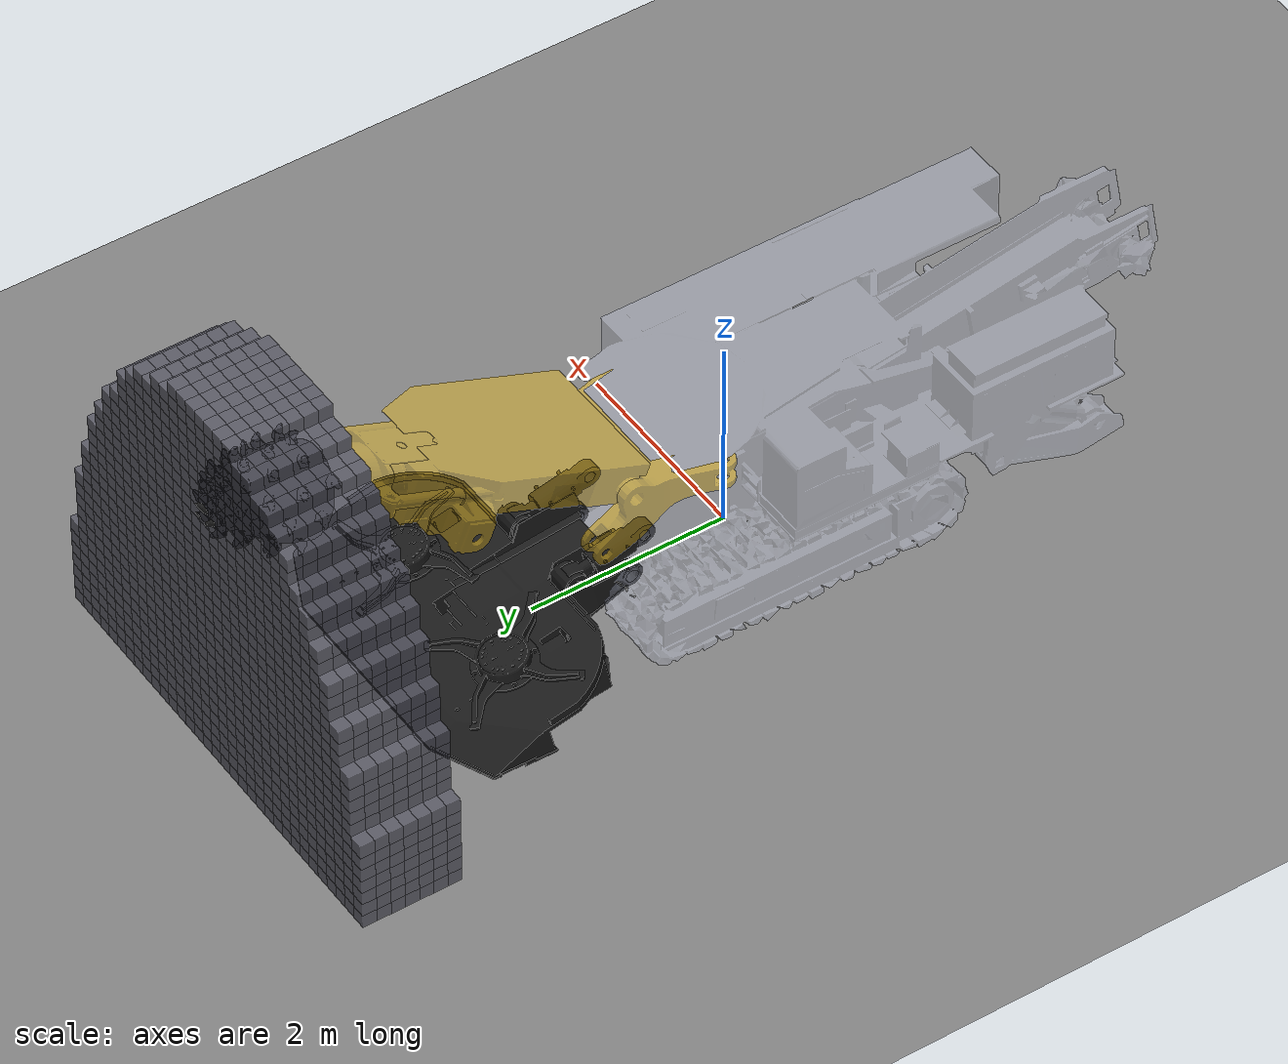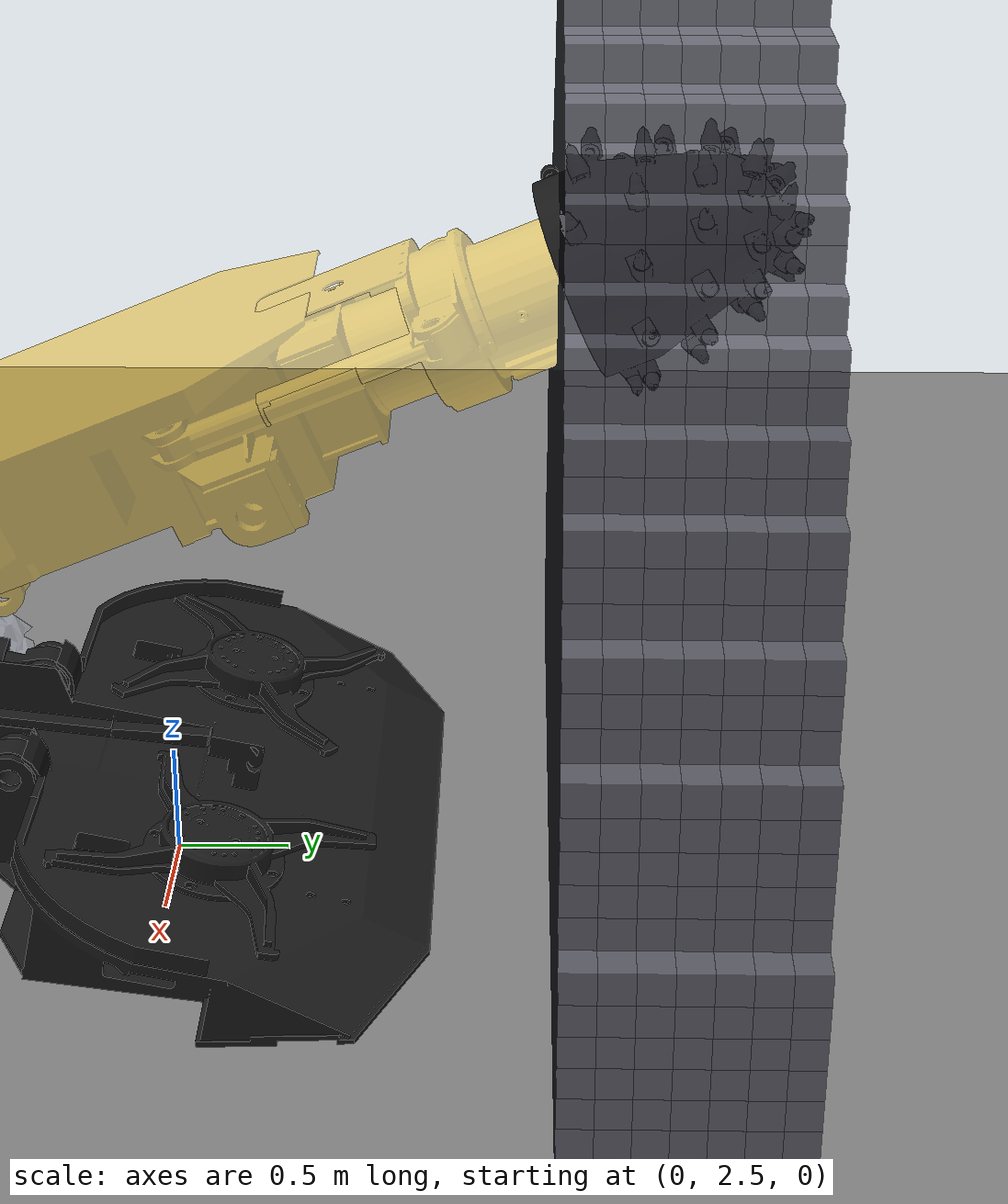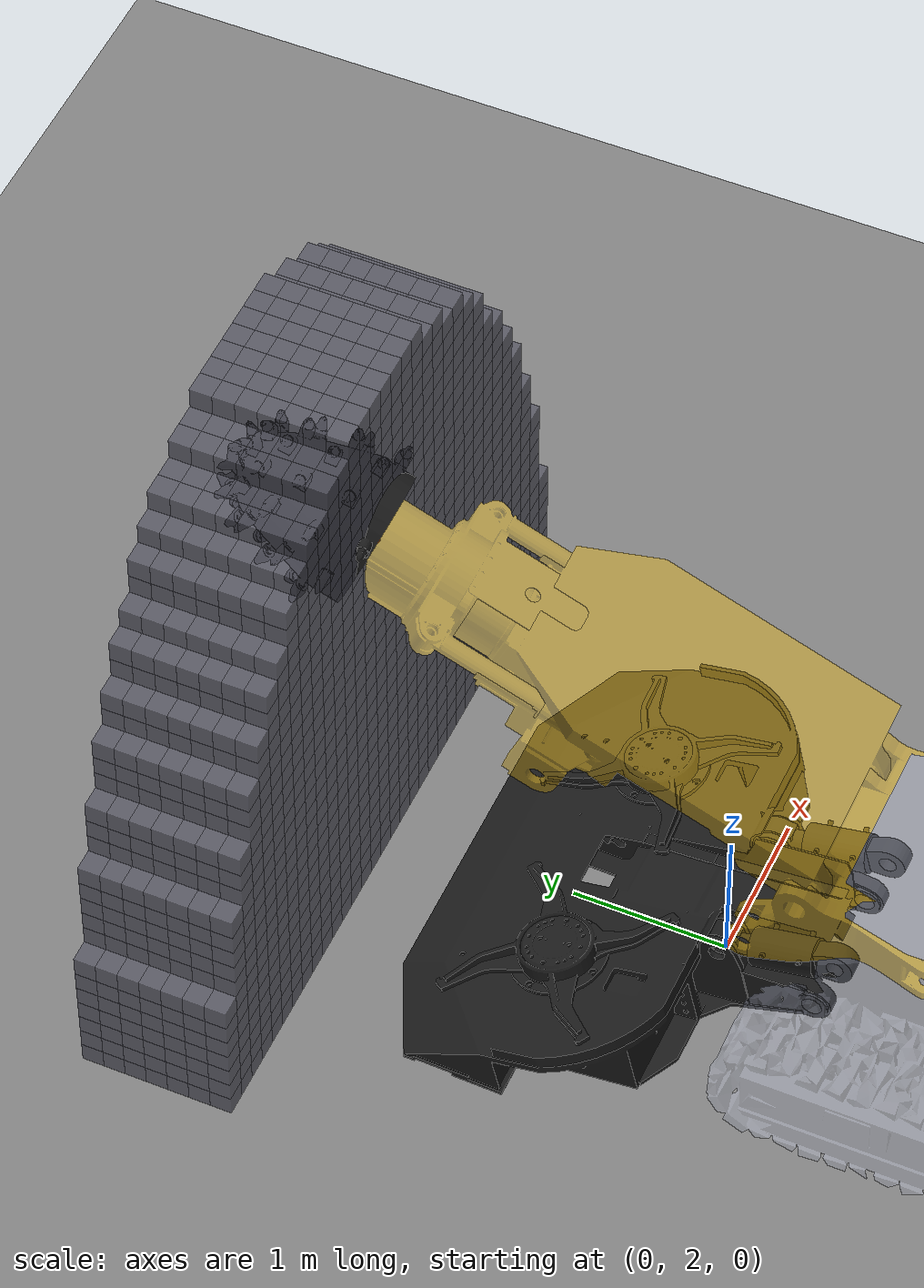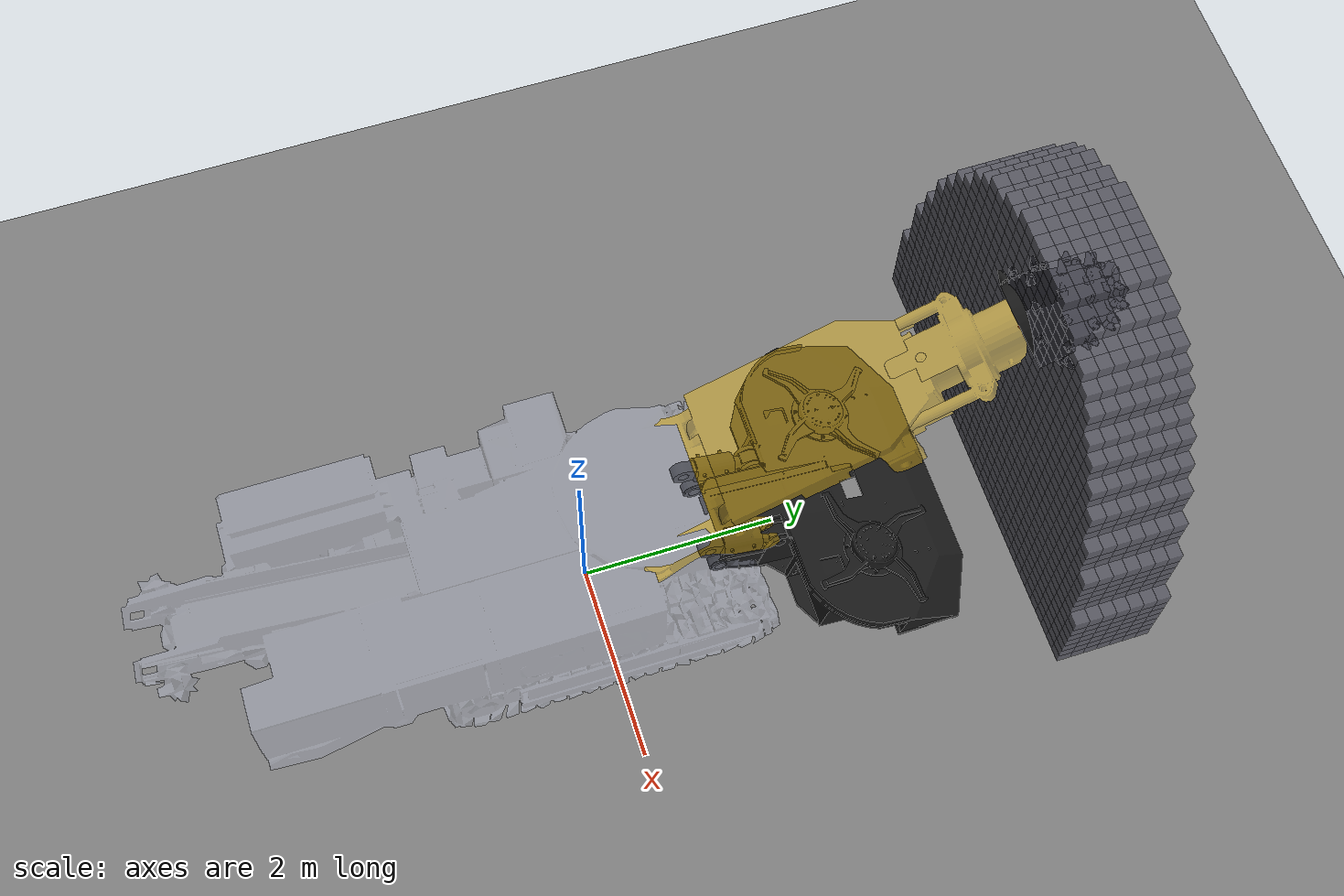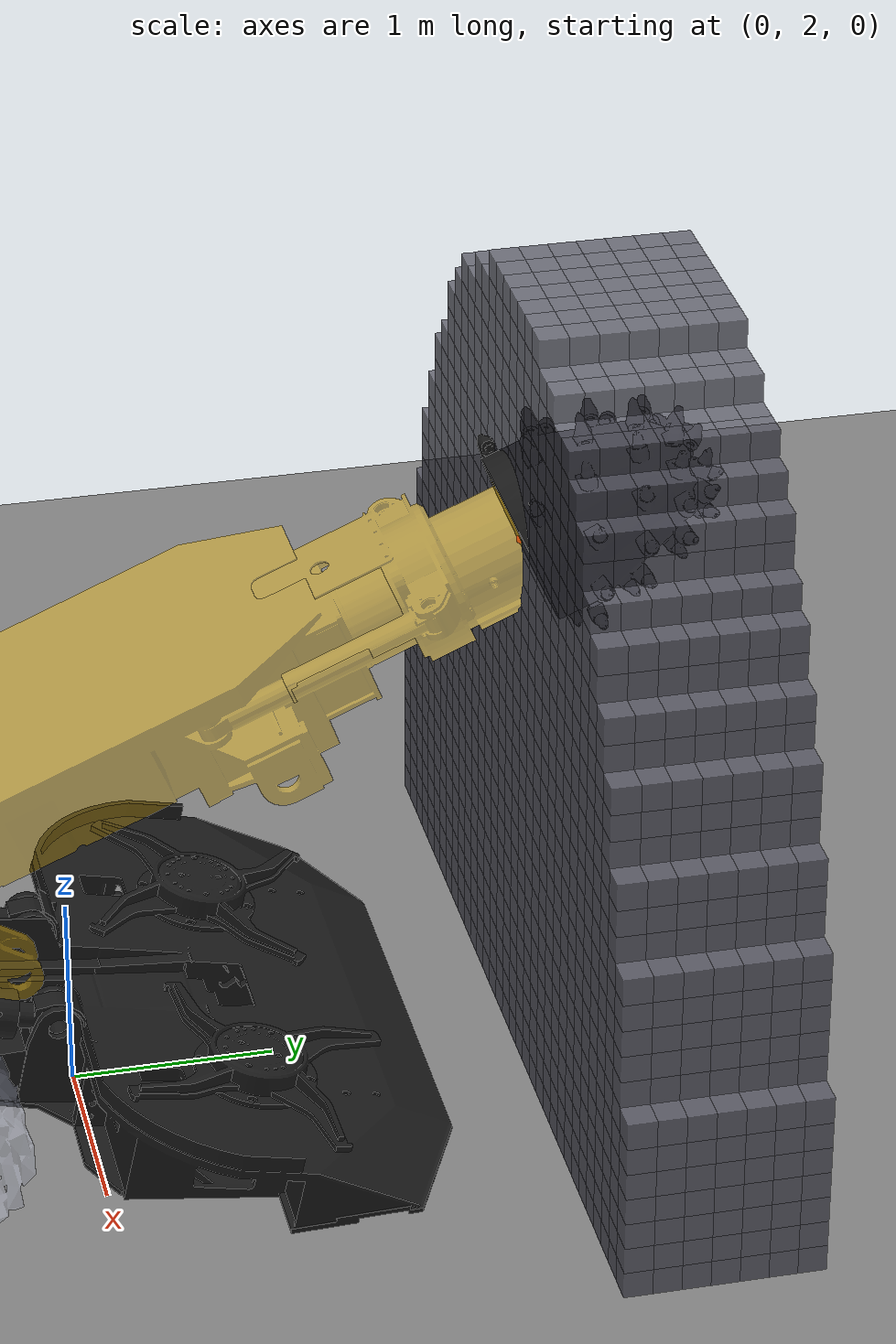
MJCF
<mujoco model="roadheader_ebz260">
  <compiler angle="degree" meshdir="meshes/"/>
  <size memory="4096M"/>
  <option timestep="0.001" gravity="0 0 -9.81" integrator="implicitfast"/>

  <asset>
    <texture type="skybox" file="./asset/desert.png" gridsize="3 4" gridlayout=".U..LFRB.D.." />
    <texture name="plane" type="2d" builtin="checker" rgb1=".1 .1 .1" rgb2=".9 .9 .9" width="512" height="512" mark="cross" markrgb=".8 .8 .8" />
    <material name="plane" reflectance="0.3" texture="plane" texrepeat="1 1" texuniform="true" />
    <!-- 定义新的颜色材质 -->
    <!-- 黑色部件：用于截割头、履带、铲板 -->
    <material name="black_metal" rgba="0.1 0.1 0.1 1" specular="0.5" shininess="0.5"/>
    <!-- 工程黄：用于机身主体 -->
    <material name="engineering_yellow" rgba="0.95 0.75 0.1 0.5" specular="0.3" shininess="0.3"/>
    <!-- 银灰色：用于液压杆、活塞等 -->
    <material name="silver_metal" rgba="0.7 0.7 0.7 0.5" specular="0.8" shininess="0.8"/>
    <!-- 深灰色：用于机械臂连接处等 -->
    <material name="dark_grey" rgba="0.3 0.3 0.3 1" specular="0.3" shininess="0.3"/>
    <!-- 机器人主体颜色，半透明 -->
    <material name="robot_color" rgba="0.792 0.820 0.933 0.3" specular="0.1" shininess="0.1"/>

    <mesh name="base_link" file="base_link.STL" />
    <mesh name="huizhuan_link" file="huizhuan_link.STL" />
    <mesh name="updown_link" file="updown_link.STL" />
    <mesh name="front_back_link" file="front_back_link.STL" />
    <mesh name="jiegetou_link" file="jiegetou_link.STL" />
    <mesh name="chanban_link" file="chanban_link.STL" />
    <mesh name="chanban_huosai_link" file="chanban_huosai_link.STL" />
    <mesh name="chanban_benti_link" file="chanban_benti_link.STL" />
    <mesh name="xinglunpan_link_left" file="xinglunpan_link_left.STL" />
    <mesh name="xinglunpan_link_right" file="xinglunpan_link_right.STL" />

  </asset>

  <worldbody>
    <geom name="floor" pos="0 0 0" size="0 0 .25" type="plane" material="plane" condim="3"/>
    <light directional="true" ambient=".3 .3 .3" pos="30 30 30" dir="0 -.5 -1" diffuse=".5 .5 .5" specular=".5 .5 .5" />

     <!-- 掘进机身 -->
    <body name="base_link" pos="0 0 0">
      <inertial pos="-0.187004885484347 -1.18837705660836 0.784619484517979" mass="40000" fullinertia="7012.61198109 1920.71944043 7212.17347859 -2.61899553366 21.3482425074 437.695624919" />
      <geom type="mesh" mesh="base_link" material="robot_color" contype="0" conaffinity="0" />

      <!-- 回转台，控制左右摆动 -->
      <body name="huizhuan_link" pos="0 0.609936943594532 1.50741733901494">
        <inertial pos="-0.0045156685034452 0.389928394422336 -0.0735723638961974" mass="2220" fullinertia="356.141485125 563.767365492 829.6908744 -2.43863060746 -0.734322985633 63.2034851008" />
        <joint name="huizhuan_joint" pos="0 0 0" axis="0 0 1" type="hinge" limited="true" range="-38 36" damping="500000" armature="100" />
        <geom type="mesh" mesh="huizhuan_link" material="engineering_yellow" contype="0" conaffinity="0" />

        <!-- 截割臂，控制上下摆动 -->
        <body name="updown_link" pos="-0.479702969466105 0.7444636062867 0.0330000000000785">
          <inertial pos="0.490020294909422 0.961034126223478 0.414972639266358" mass="8000" fullinertia="1036.23408667 803.819017616 1261.89058625 -34.289692423 -33.336186676 -218.770789971" />
          <joint name="updown_joint" pos="0 0 0" axis="-0.99993217660885 -0.011646552377767 0" type="hinge" limited="true" range="-40 45" damping="2000000" />
          <geom type="mesh" mesh="updown_link" material="engineering_yellow" contype="0" conaffinity="0" />

          <!-- 截割伸缩部，控制前后伸缩 -->
          <body name="front_back_link" pos="-0.033139 1.9866 0.94833">
            <inertial pos="0.470968875236498 0.626894171795733 0.190410120123621" mass="800" fullinertia="47.3553039693 44.210546925 50.9898135171 0.0494901919436 -0.12924877518 -3.3369332106" />
            <joint name="front_back_joint" pos="0 0 0" axis="0.010758 -0.92367 -0.38303" type="slide" limited="true" range="-0.34 0.3" damping="10000"/>
            <geom type="mesh" mesh="front_back_link" material="engineering_yellow" contype="0" conaffinity="0" />

            <!-- 截割头，旋转切割 -->
            <body name="jiegetou_link" pos="0.46938462258532 0.914194374969433 0.252284999266074">
              <site name="cutter_tip" pos="0 0 0" size="0.02" rgba="1 0 0 1"/>
              <inertial pos="-0.00429994447681969 0.334730266430001 0.138941698694205" mass="2410" fullinertia="197.092104668 168.287613744 192.137698719 0.334580205079 0.140374772092 -11.9442095725" />
              <joint name="jiegetou_joint" pos="0 0 0" axis="-0.0107583457090147 0.923673864384503 0.383028524069167" type="hinge" limited="false"/>
              <geom type="mesh" mesh="jiegetou_link" material="black_metal" contype="1" conaffinity="1" condim="3" friction="0.8 0.005 0.0001" />
            </body>
          </body>
        </body>
      </body>

      <!-- 铲板机构 -->
      <body name="chanban_link" pos="-0.41899999999998 1.14993694359281 0.835286561443913">
        <inertial pos="0.421999999976831 0.244667533077565 -0.0575007260342454" mass="175" fullinertia="5.71214742411 1.62840738358 5.38910508517 -3.43146296503e-09 -1.27841025789e-08 0.936963383099" />
        <joint name="chanban_joint" pos="0 0 0" axis="-1 0 0" type="hinge" limited="true" range="-15 15"/>
        <geom type="mesh" mesh="chanban_link" material="black_metal" contype="0" conaffinity="0" />

        <body name="chanban_huosai_link" pos="0 0.339672954967903 -0.0801453907805885">
          <inertial pos="0.422 0.236593265908223 -0.0558238725655861" mass="175" fullinertia="4.67036972958 0.802869244218 4.24805374965 1.01569728199e-14 5.76544785405e-14 0.860809600256" />
          <joint name="chanban_huosai_joint" pos="0 0 0" axis="0 -0.97327494260144 0.229642953526041" type="slide" limited="true" range="-0.18 0.08"/>
          <geom type="mesh" mesh="chanban_huosai_link" material="black_metal" contype="0" conaffinity="0"/>

          <body name="chanban_benti_link" pos="0 0.378768474922782 -0.0893699277319111">
            <inertial pos="0.41833751220593 0.721211102001956 -0.352140461186548" mass="6000" fullinertia="1336.71958311 592.990751166 1761.23104041 80.6620756608 1.73990517542 189.296115578" />
            <joint name="chanban_benti_joint" pos="0 0 0" axis="1 0 0" type="hinge" limited="true" range="-15 15" />
            <geom type="mesh" mesh="chanban_benti_link" material="black_metal" contype="1" conaffinity="1" condim="3" friction="0.7 0.005 0.0001" />

            <body name="xinglunpan_link_left" pos="-0.358000000000011 0.897774564291463 -0.224779517992865">
              <inertial pos="-1.80366832580603E-12 0.0130100641003494 0.0601799032548234" mass="100" fullinertia="1.64844264078 1.72431326231 3.14516089405 4.1107759071e-05 -8.87644675471e-06 0.322227356975" />
              <joint name="xinglunpan_joint_left" pos="0 0 0" axis="0 -0.211304768939857 -0.977420224173448" type="hinge" limited="false" />
              <geom type="mesh" mesh="xinglunpan_link_left" material="black_metal" contype="0" conaffinity="0" />
            </body>

            <body name="xinglunpan_link_right" pos="1.20199999999999 0.897774564291463 -0.224779517992883">
              <inertial pos="-6.41790370847772E-10 0.0130100642672515 0.0601799032174734" mass="100" fullinertia="1.65001336759 1.7228140028 3.14509215946 0.00263784345715 -0.000570344250235 0.322551695233" />
              <joint name="xinglunpan_joint_right" pos="0 0 0" axis="0 -0.211304768939858 -0.977420224173448" type="hinge" limited="false" />
              <geom type="mesh" mesh="xinglunpan_link_right" material="black_metal" contype="0" conaffinity="0" />
            </body>
          </body>
        </body>
      </body>
    </body>

    <body name="imported_scene" pos="0.0 2.2 0">

    <body name="voxel_target" euler="0 0 90">
      <body name="vx_0_0_-16" pos="2.070 -2.240 0.070">
        <geom type="box" size="0.07 0.07 0.07" rgba="0.35 0.35 0.4 0.8" contype="0" conaffinity="0"/>
      </body>
      <body name="vx_0_0_-15" pos="2.070 -2.100 0.070">
        <geom type="box" size="0.07 0.07 0.07" rgba="0.35 0.35 0.4 0.8" contype="0" conaffinity="0"/>
      </body>
      <body name="vx_0_0_-14" pos="2.070 -1.960 0.070">
        <geom type="box" size="0.07 0.07 0.07" rgba="0.35 0.35 0.4 0.8" contype="0" conaffinity="0"/>
      </body>
      <body name="vx_0_0_-13" pos="2.070 -1.820 0.070">
        <geom type="box" size="0.07 0.07 0.07" rgba="0.35 0.35 0.4 0.8" contype="0" conaffinity="0"/>
      </body>
      <body name="vx_0_0_-12" pos="2.070 -1.680 0.070">
        <geom type="box" size="0.07 0.07 0.07" rgba="0.35 0.35 0.4 0.8" contype="0" conaffinity="0"/>
      </body>
      <body name="vx_0_0_-11" pos="2.070 -1.540 0.070">
        <geom type="box" size="0.07 0.07 0.07" rgba="0.35 0.35 0.4 0.8" contype="0" conaffinity="0"/>
      </body>
      <body name="vx_0_0_-10" pos="2.070 -1.400 0.070">
        <geom type="box" size="0.07 0.07 0.07" rgba="0.35 0.35 0.4 0.8" contype="0" conaffinity="0"/>
      </body>
      <body name="vx_0_0_-9" pos="2.070 -1.260 0.070">
        <geom type="box" size="0.07 0.07 0.07" rgba="0.35 0.35 0.4 0.8" contype="0" conaffinity="0"/>
      </body>
      <body name="vx_0_0_-8" pos="2.070 -1.120 0.070">
        <geom type="box" size="0.07 0.07 0.07" rgba="0.35 0.35 0.4 0.8" contype="0" conaffinity="0"/>
      </body>
      <body name="vx_0_0_-7" pos="2.070 -0.980 0.070">
        <geom type="box" size="0.07 0.07 0.07" rgba="0.35 0.35 0.4 0.8" contype="0" conaffinity="0"/>
      </body>
      <body name="vx_0_0_-6" pos="2.070 -0.840 0.070">
        <geom type="box" size="0.07 0.07 0.07" rgba="0.35 0.35 0.4 0.8" contype="0" conaffinity="0"/>
      </body>
      <body name="vx_0_0_-5" pos="2.070 -0.700 0.070">
        <geom type="box" size="0.07 0.07 0.07" rgba="0.35 0.35 0.4 0.8" contype="0" conaffinity="0"/>
      </body>
      <body name="vx_0_0_-4" pos="2.070 -0.560 0.070">
        <geom type="box" size="0.07 0.07 0.07" rgba="0.35 0.35 0.4 0.8" contype="0" conaffinity="0"/>
      </body>
      <body name="vx_0_0_-3" pos="2.070 -0.420 0.070">
        <geom type="box" size="0.07 0.07 0.07" rgba="0.35 0.35 0.4 0.8" contype="0" conaffinity="0"/>
      </body>
      <body name="vx_0_0_-2" pos="2.070 -0.280 0.070">
        <geom type="box" size="0.07 0.07 0.07" rgba="0.35 0.35 0.4 0.8" contype="0" conaffinity="0"/>
      </body>
      <body name="vx_0_0_-1" pos="2.070 -0.140 0.070">
        <geom type="box" size="0.07 0.07 0.07" rgba="0.35 0.35 0.4 0.8" contype="0" conaffinity="0"/>
      </body>
      <body name="vx_0_0_0" pos="2.070 0.000 0.070">
        <geom type="box" size="0.07 0.07 0.07" rgba="0.35 0.35 0.4 0.8" contype="0" conaffinity="0"/>
      </body>
      <body name="vx_0_0_1" pos="2.070 0.140 0.070">
        <geom type="box" size="0.07 0.07 0.07" rgba="0.35 0.35 0.4 0.8" contype="0" conaffinity="0"/>
      </body>
      <body name="vx_0_0_2" pos="2.070 0.280 0.070">
        <geom type="box" size="0.07 0.07 0.07" rgba="0.35 0.35 0.4 0.8" contype="0" conaffinity="0"/>
      </body>
      <body name="vx_0_0_3" pos="2.070 0.420 0.070">
        <geom type="box" size="0.07 0.07 0.07" rgba="0.35 0.35 0.4 0.8" contype="0" conaffinity="0"/>
      </body>
      <body name="vx_0_0_4" pos="2.070 0.560 0.070">
        <geom type="box" size="0.07 0.07 0.07" rgba="0.35 0.35 0.4 0.8" contype="0" conaffinity="0"/>
      </body>
      <body name="vx_0_0_5" pos="2.070 0.700 0.070">
        <geom type="box" size="0.07 0.07 0.07" rgba="0.35 0.35 0.4 0.8" contype="0" conaffinity="0"/>
      </body>
      <body name="vx_0_0_6" pos="2.070 0.840 0.070">
        <geom type="box" size="0.07 0.07 0.07" rgba="0.35 0.35 0.4 0.8" contype="0" conaffinity="0"/>
      </body>
      <body name="vx_0_0_7" pos="2.070 0.980 0.070">
        <geom type="box" size="0.07 0.07 0.07" rgba="0.35 0.35 0.4 0.8" contype="0" conaffinity="0"/>
      </body>
      <body name="vx_0_0_8" pos="2.070 1.120 0.070">
        <geom type="box" size="0.07 0.07 0.07" rgba="0.35 0.35 0.4 0.8" contype="0" conaffinity="0"/>
      </body>
      <body name="vx_0_0_9" pos="2.070 1.260 0.070">
        <geom type="box" size="0.07 0.07 0.07" rgba="0.35 0.35 0.4 0.8" contype="0" conaffinity="0"/>
      </body>
      <body name="vx_0_0_10" pos="2.070 1.400 0.070">
        <geom type="box" size="0.07 0.07 0.07" rgba="0.35 0.35 0.4 0.8" contype="0" conaffinity="0"/>
      </body>
      <body name="vx_0_0_11" pos="2.070 1.540 0.070">
        <geom type="box" size="0.07 0.07 0.07" rgba="0.35 0.35 0.4 0.8" contype="0" conaffinity="0"/>
      </body>
      <body name="vx_0_0_12" pos="2.070 1.680 0.070">
        <geom type="box" size="0.07 0.07 0.07" rgba="0.35 0.35 0.4 0.8" contype="0" conaffinity="0"/>
      </body>
      <body name="vx_0_0_13" pos="2.070 1.820 0.070">
        <geom type="box" size="0.07 0.07 0.07" rgba="0.35 0.35 0.4 0.8" contype="0" conaffinity="0"/>
      </body>
      <body name="vx_0_0_14" pos="2.070 1.960 0.070">
        <geom type="box" size="0.07 0.07 0.07" rgba="0.35 0.35 0.4 0.8" contype="0" conaffinity="0"/>
      </body>
      <body name="vx_0_0_15" pos="2.070 2.100 0.070">
        <geom type="box" size="0.07 0.07 0.07" rgba="0.35 0.35 0.4 0.8" contype="0" conaffinity="0"/>
      </body>
      <body name="vx_0_0_16" pos="2.070 2.240 0.070">
        <geom type="box" size="0.07 0.07 0.07" rgba="0.35 0.35 0.4 0.8" contype="0" conaffinity="0"/>
      </body>
      <body name="vx_0_1_-16" pos="2.070 -2.240 0.210">
        <geom type="box" size="0.07 0.07 0.07" rgba="0.35 0.35 0.4 0.8" contype="0" conaffinity="0"/>
      </body>
      <body name="vx_0_1_-15" pos="2.070 -2.100 0.210">
        <geom type="box" size="0.07 0.07 0.07" rgba="0.35 0.35 0.4 0.8" contype="0" conaffinity="0"/>
      </body>
      <body name="vx_0_1_-14" pos="2.070 -1.960 0.210">
        <geom type="box" size="0.07 0.07 0.07" rgba="0.35 0.35 0.4 0.8" contype="0" conaffinity="0"/>
      </body>
      <body name="vx_0_1_-13" pos="2.070 -1.820 0.210">
        <geom type="box" size="0.07 0.07 0.07" rgba="0.35 0.35 0.4 0.8" contype="0" conaffinity="0"/>
      </body>
      <body name="vx_0_1_-12" pos="2.070 -1.680 0.210">
        <geom type="box" size="0.07 0.07 0.07" rgba="0.35 0.35 0.4 0.8" contype="0" conaffinity="0"/>
      </body>
      <body name="vx_0_1_-11" pos="2.070 -1.540 0.210">
        <geom type="box" size="0.07 0.07 0.07" rgba="0.35 0.35 0.4 0.8" contype="0" conaffinity="0"/>
      </body>
      <body name="vx_0_1_-10" pos="2.070 -1.400 0.210">
        <geom type="box" size="0.07 0.07 0.07" rgba="0.35 0.35 0.4 0.8" contype="0" conaffinity="0"/>
      </body>
      <body name="vx_0_1_-9" pos="2.070 -1.260 0.210">
        <geom type="box" size="0.07 0.07 0.07" rgba="0.35 0.35 0.4 0.8" contype="0" conaffinity="0"/>
      </body>
      <body name="vx_0_1_-8" pos="2.070 -1.120 0.210">
        <geom type="box" size="0.07 0.07 0.07" rgba="0.35 0.35 0.4 0.8" contype="0" conaffinity="0"/>
      </body>
      <body name="vx_0_1_-7" pos="2.070 -0.980 0.210">
        <geom type="box" size="0.07 0.07 0.07" rgba="0.35 0.35 0.4 0.8" contype="0" conaffinity="0"/>
      </body>
      <body name="vx_0_1_-6" pos="2.070 -0.840 0.210">
        <geom type="box" size="0.07 0.07 0.07" rgba="0.35 0.35 0.4 0.8" contype="0" conaffinity="0"/>
      </body>
      <body name="vx_0_1_-5" pos="2.070 -0.700 0.210">
        <geom type="box" size="0.07 0.07 0.07" rgba="0.35 0.35 0.4 0.8" contype="0" conaffinity="0"/>
      </body>
      <body name="vx_0_1_-4" pos="2.070 -0.560 0.210">
        <geom type="box" size="0.07 0.07 0.07" rgba="0.35 0.35 0.4 0.8" contype="0" conaffinity="0"/>
      </body>
      <body name="vx_0_1_-3" pos="2.070 -0.420 0.210">
        <geom type="box" size="0.07 0.07 0.07" rgba="0.35 0.35 0.4 0.8" contype="0" conaffinity="0"/>
      </body>
      <body name="vx_0_1_-2" pos="2.070 -0.280 0.210">
        <geom type="box" size="0.07 0.07 0.07" rgba="0.35 0.35 0.4 0.8" contype="0" conaffinity="0"/>
      </body>
      <body name="vx_0_1_-1" pos="2.070 -0.140 0.210">
        <geom type="box" size="0.07 0.07 0.07" rgba="0.35 0.35 0.4 0.8" contype="0" conaffinity="0"/>
      </body>
      <body name="vx_0_1_0" pos="2.070 0.000 0.210">
        <geom type="box" size="0.07 0.07 0.07" rgba="0.35 0.35 0.4 0.8" contype="0" conaffinity="0"/>
      </body>
      <body name="vx_0_1_1" pos="2.070 0.140 0.210">
        <geom type="box" size="0.07 0.07 0.07" rgba="0.35 0.35 0.4 0.8" contype="0" conaffinity="0"/>
      </body>
      <body name="vx_0_1_2" pos="2.070 0.280 0.210">
        <geom type="box" size="0.07 0.07 0.07" rgba="0.35 0.35 0.4 0.8" contype="0" conaffinity="0"/>
      </body>
      <body name="vx_0_1_3" pos="2.070 0.420 0.210">
        <geom type="box" size="0.07 0.07 0.07" rgba="0.35 0.35 0.4 0.8" contype="0" conaffinity="0"/>
      </body>
      <body name="vx_0_1_4" pos="2.070 0.560 0.210">
        <geom type="box" size="0.07 0.07 0.07" rgba="0.35 0.35 0.4 0.8" contype="0" conaffinity="0"/>
      </body>
      <body name="vx_0_1_5" pos="2.070 0.700 0.210">
        <geom type="box" size="0.07 0.07 0.07" rgba="0.35 0.35 0.4 0.8" contype="0" conaffinity="0"/>
      </body>
      <body name="vx_0_1_6" pos="2.070 0.840 0.210">
        <geom type="box" size="0.07 0.07 0.07" rgba="0.35 0.35 0.4 0.8" contype="0" conaffinity="0"/>
      </body>
      <body name="vx_0_1_7" pos="2.070 0.980 0.210">
        <geom type="box" size="0.07 0.07 0.07" rgba="0.35 0.35 0.4 0.8" contype="0" conaffinity="0"/>
      </body>
      <body name="vx_0_1_8" pos="2.070 1.120 0.210">
        <geom type="box" size="0.07 0.07 0.07" rgba="0.35 0.35 0.4 0.8" contype="0" conaffinity="0"/>
      </body>
      <body name="vx_0_1_9" pos="2.070 1.260 0.210">
        <geom type="box" size="0.07 0.07 0.07" rgba="0.35 0.35 0.4 0.8" contype="0" conaffinity="0"/>
      </body>
      <body name="vx_0_1_10" pos="2.070 1.400 0.210">
        <geom type="box" size="0.07 0.07 0.07" rgba="0.35 0.35 0.4 0.8" contype="0" conaffinity="0"/>
      </body>
      <body name="vx_0_1_11" pos="2.070 1.540 0.210">
        <geom type="box" size="0.07 0.07 0.07" rgba="0.35 0.35 0.4 0.8" contype="0" conaffinity="0"/>
      </body>
      <body name="vx_0_1_12" pos="2.070 1.680 0.210">
        <geom type="box" size="0.07 0.07 0.07" rgba="0.35 0.35 0.4 0.8" contype="0" conaffinity="0"/>
      </body>
      <body name="vx_0_1_13" pos="2.070 1.820 0.210">
        <geom type="box" size="0.07 0.07 0.07" rgba="0.35 0.35 0.4 0.8" contype="0" conaffinity="0"/>
      </body>
      <body name="vx_0_1_14" pos="2.070 1.960 0.210">
        <geom type="box" size="0.07 0.07 0.07" rgba="0.35 0.35 0.4 0.8" contype="0" conaffinity="0"/>
      </body>
      <body name="vx_0_1_15" pos="2.070 2.100 0.210">
        <geom type="box" size="0.07 0.07 0.07" rgba="0.35 0.35 0.4 0.8" contype="0" conaffinity="0"/>
      </body>
      <body name="vx_0_1_16" pos="2.070 2.240 0.210">
        <geom type="box" size="0.07 0.07 0.07" rgba="0.35 0.35 0.4 0.8" contype="0" conaffinity="0"/>
      </body>
      <body name="vx_0_2_-16" pos="2.070 -2.240 0.350">
        <geom type="box" size="0.07 0.07 0.07" rgba="0.35 0.35 0.4 0.8" contype="0" conaffinity="0"/>
      </body>
      <body name="vx_0_2_-15" pos="2.070 -2.100 0.350">
        <geom type="box" size="0.07 0.07 0.07" rgba="0.35 0.35 0.4 0.8" contype="0" conaffinity="0"/>
      </body>
      <body name="vx_0_2_-14" pos="2.070 -1.960 0.350">
        <geom type="box" size="0.07 0.07 0.07" rgba="0.35 0.35 0.4 0.8" contype="0" conaffinity="0"/>
      </body>
      <body name="vx_0_2_-13" pos="2.070 -1.820 0.350">
        <geom type="box" size="0.07 0.07 0.07" rgba="0.35 0.35 0.4 0.8" contype="0" conaffinity="0"/>
      </body>
      <body name="vx_0_2_-12" pos="2.070 -1.680 0.350">
        <geom type="box" size="0.07 0.07 0.07" rgba="0.35 0.35 0.4 0.8" contype="0" conaffinity="0"/>
      </body>
      <body name="vx_0_2_-11" pos="2.070 -1.540 0.350">
        <geom type="box" size="0.07 0.07 0.07" rgba="0.35 0.35 0.4 0.8" contype="0" conaffinity="0"/>
      </body>
      <body name="vx_0_2_-10" pos="2.070 -1.400 0.350">
        <geom type="box" size="0.07 0.07 0.07" rgba="0.35 0.35 0.4 0.8" contype="0" conaffinity="0"/>
      </body>
      <body name="vx_0_2_-9" pos="2.070 -1.260 0.350">
        <geom type="box" size="0.07 0.07 0.07" rgba="0.35 0.35 0.4 0.8" contype="0" conaffinity="0"/>
      </body>
      <body name="vx_0_2_-8" pos="2.070 -1.120 0.350">
        <geom type="box" size="0.07 0.07 0.07" rgba="0.35 0.35 0.4 0.8" contype="0" conaffinity="0"/>
      </body>
      <body name="vx_0_2_-7" pos="2.070 -0.980 0.350">
        <geom type="box" size="0.07 0.07 0.07" rgba="0.35 0.35 0.4 0.8" contype="0" conaffinity="0"/>
      </body>
      <body name="vx_0_2_-6" pos="2.070 -0.840 0.350">
        <geom type="box" size="0.07 0.07 0.07" rgba="0.35 0.35 0.4 0.8" contype="0" conaffinity="0"/>
      </body>
      <body name="vx_0_2_-5" pos="2.070 -0.700 0.350">
        <geom type="box" size="0.07 0.07 0.07" rgba="0.35 0.35 0.4 0.8" contype="0" conaffinity="0"/>
      </body>
      <body name="vx_0_2_-4" pos="2.070 -0.560 0.350">
        <geom type="box" size="0.07 0.07 0.07" rgba="0.35 0.35 0.4 0.8" contype="0" conaffinity="0"/>
      </body>
      <body name="vx_0_2_-3" pos="2.070 -0.420 0.350">
        <geom type="box" size="0.07 0.07 0.07" rgba="0.35 0.35 0.4 0.8" contype="0" conaffinity="0"/>
      </body>
      <body name="vx_0_2_-2" pos="2.070 -0.280 0.350">
        <geom type="box" size="0.07 0.07 0.07" rgba="0.35 0.35 0.4 0.8" contype="0" conaffinity="0"/>
      </body>
      <body name="vx_0_2_-1" pos="2.070 -0.140 0.350">
        <geom type="box" size="0.07 0.07 0.07" rgba="0.35 0.35 0.4 0.8" contype="0" conaffinity="0"/>
      </body>
      <body name="vx_0_2_0" pos="2.070 0.000 0.350">
        <geom type="box" size="0.07 0.07 0.07" rgba="0.35 0.35 0.4 0.8" contype="0" conaffinity="0"/>
      </body>
      <body name="vx_0_2_1" pos="2.070 0.140 0.350">
        <geom type="box" size="0.07 0.07 0.07" rgba="0.35 0.35 0.4 0.8" contype="0" conaffinity="0"/>
      </body>
      <body name="vx_0_2_2" pos="2.070 0.280 0.350">
        <geom type="box" size="0.07 0.07 0.07" rgba="0.35 0.35 0.4 0.8" contype="0" conaffinity="0"/>
      </body>
      <body name="vx_0_2_3" pos="2.070 0.420 0.350">
        <geom type="box" size="0.07 0.07 0.07" rgba="0.35 0.35 0.4 0.8" contype="0" conaffinity="0"/>
      </body>
      <body name="vx_0_2_4" pos="2.070 0.560 0.350">
        <geom type="box" size="0.07 0.07 0.07" rgba="0.35 0.35 0.4 0.8" contype="0" conaffinity="0"/>
      </body>
      <body name="vx_0_2_5" pos="2.070 0.700 0.350">
        <geom type="box" size="0.07 0.07 0.07" rgba="0.35 0.35 0.4 0.8" contype="0" conaffinity="0"/>
      </body>
      <body name="vx_0_2_6" pos="2.070 0.840 0.350">
        <geom type="box" size="0.07 0.07 0.07" rgba="0.35 0.35 0.4 0.8" contype="0" conaffinity="0"/>
      </body>
      <body name="vx_0_2_7" pos="2.070 0.980 0.350">
        <geom type="box" size="0.07 0.07 0.07" rgba="0.35 0.35 0.4 0.8" contype="0" conaffinity="0"/>
      </body>
      <body name="vx_0_2_8" pos="2.070 1.120 0.350">
        <geom type="box" size="0.07 0.07 0.07" rgba="0.35 0.35 0.4 0.8" contype="0" conaffinity="0"/>
      </body>
      <body name="vx_0_2_9" pos="2.070 1.260 0.350">
        <geom type="box" size="0.07 0.07 0.07" rgba="0.35 0.35 0.4 0.8" contype="0" conaffinity="0"/>
      </body>
      <body name="vx_0_2_10" pos="2.070 1.400 0.350">
        <geom type="box" size="0.07 0.07 0.07" rgba="0.35 0.35 0.4 0.8" contype="0" conaffinity="0"/>
      </body>
      <body name="vx_0_2_11" pos="2.070 1.540 0.350">
        <geom type="box" size="0.07 0.07 0.07" rgba="0.35 0.35 0.4 0.8" contype="0" conaffinity="0"/>
      </body>
      <body name="vx_0_2_12" pos="2.070 1.680 0.350">
        <geom type="box" size="0.07 0.07 0.07" rgba="0.35 0.35 0.4 0.8" contype="0" conaffinity="0"/>
      </body>
      <body name="vx_0_2_13" pos="2.070 1.820 0.350">
        <geom type="box" size="0.07 0.07 0.07" rgba="0.35 0.35 0.4 0.8" contype="0" conaffinity="0"/>
      </body>
      <body name="vx_0_2_14" pos="2.070 1.960 0.350">
        <geom type="box" size="0.07 0.07 0.07" rgba="0.35 0.35 0.4 0.8" contype="0" conaffinity="0"/>
      </body>
      <body name="vx_0_2_15" pos="2.070 2.100 0.350">
        <geom type="box" size="0.07 0.07 0.07" rgba="0.35 0.35 0.4 0.8" contype="0" conaffinity="0"/>
      </body>
      <body name="vx_0_2_16" pos="2.070 2.240 0.350">
        <geom type="box" size="0.07 0.07 0.07" rgba="0.35 0.35 0.4 0.8" contype="0" conaffinity="0"/>
      </body>
      <body name="vx_0_3_-16" pos="2.070 -2.240 0.490">
        <geom type="box" size="0.07 0.07 0.07" rgba="0.35 0.35 0.4 0.8" contype="0" conaffinity="0"/>
      </body>
      <body name="vx_0_3_-15" pos="2.070 -2.100 0.490">
        <geom type="box" size="0.07 0.07 0.07" rgba="0.35 0.35 0.4 0.8" contype="0" conaffinity="0"/>
      </body>
      <body name="vx_0_3_-14" pos="2.070 -1.960 0.490">
        <geom type="box" size="0.07 0.07 0.07" rgba="0.35 0.35 0.4 0.8" contype="0" conaffinity="0"/>
      </body>
      <body name="vx_0_3_-13" pos="2.070 -1.820 0.490">
        <geom type="box" size="0.07 0.07 0.07" rgba="0.35 0.35 0.4 0.8" contype="0" conaffinity="0"/>
      </body>
      <body name="vx_0_3_-12" pos="2.070 -1.680 0.490">
        <geom type="box" size="0.07 0.07 0.07" rgba="0.35 0.35 0.4 0.8" contype="0" conaffinity="0"/>
      </body>
      <body name="vx_0_3_-11" pos="2.070 -1.540 0.490">
        <geom type="box" size="0.07 0.07 0.07" rgba="0.35 0.35 0.4 0.8" contype="0" conaffinity="0"/>
      </body>
      <body name="vx_0_3_-10" pos="2.070 -1.400 0.490">
        <geom type="box" size="0.07 0.07 0.07" rgba="0.35 0.35 0.4 0.8" contype="0" conaffinity="0"/>
      </body>
      <body name="vx_0_3_-9" pos="2.070 -1.260 0.490">
        <geom type="box" size="0.07 0.07 0.07" rgba="0.35 0.35 0.4 0.8" contype="0" conaffinity="0"/>
      </body>
      <body name="vx_0_3_-8" pos="2.070 -1.120 0.490">
        <geom type="box" size="0.07 0.07 0.07" rgba="0.35 0.35 0.4 0.8" contype="0" conaffinity="0"/>
      </body>
      <body name="vx_0_3_-7" pos="2.070 -0.980 0.490">
        <geom type="box" size="0.07 0.07 0.07" rgba="0.35 0.35 0.4 0.8" contype="0" conaffinity="0"/>
      </body>
      <body name="vx_0_3_-6" pos="2.070 -0.840 0.490">
        <geom type="box" size="0.07 0.07 0.07" rgba="0.35 0.35 0.4 0.8" contype="0" conaffinity="0"/>
      </body>
      <body name="vx_0_3_-5" pos="2.070 -0.700 0.490">
        <geom type="box" size="0.07 0.07 0.07" rgba="0.35 0.35 0.4 0.8" contype="0" conaffinity="0"/>
      </body>
      <body name="vx_0_3_-4" pos="2.070 -0.560 0.490">
        <geom type="box" size="0.07 0.07 0.07" rgba="0.35 0.35 0.4 0.8" contype="0" conaffinity="0"/>
      </body>
      <body name="vx_0_3_-3" pos="2.070 -0.420 0.490">
        <geom type="box" size="0.07 0.07 0.07" rgba="0.35 0.35 0.4 0.8" contype="0" conaffinity="0"/>
      </body>
      <body name="vx_0_3_-2" pos="2.070 -0.280 0.490">
        <geom type="box" size="0.07 0.07 0.07" rgba="0.35 0.35 0.4 0.8" contype="0" conaffinity="0"/>
      </body>
      <body name="vx_0_3_-1" pos="2.070 -0.140 0.490">
        <geom type="box" size="0.07 0.07 0.07" rgba="0.35 0.35 0.4 0.8" contype="0" conaffinity="0"/>
      </body>
      <body name="vx_0_3_0" pos="2.070 0.000 0.490">
        <geom type="box" size="0.07 0.07 0.07" rgba="0.35 0.35 0.4 0.8" contype="0" conaffinity="0"/>
      </body>
      <body name="vx_0_3_1" pos="2.070 0.140 0.490">
        <geom type="box" size="0.07 0.07 0.07" rgba="0.35 0.35 0.4 0.8" contype="0" conaffinity="0"/>
      </body>
      <body name="vx_0_3_2" pos="2.070 0.280 0.490">
        <geom type="box" size="0.07 0.07 0.07" rgba="0.35 0.35 0.4 0.8" contype="0" conaffinity="0"/>
      </body>
      <body name="vx_0_3_3" pos="2.070 0.420 0.490">
        <geom type="box" size="0.07 0.07 0.07" rgba="0.35 0.35 0.4 0.8" contype="0" conaffinity="0"/>
      </body>
      <body name="vx_0_3_4" pos="2.070 0.560 0.490">
        <geom type="box" size="0.07 0.07 0.07" rgba="0.35 0.35 0.4 0.8" contype="0" conaffinity="0"/>
      </body>
      <body name="vx_0_3_5" pos="2.070 0.700 0.490">
        <geom type="box" size="0.07 0.07 0.07" rgba="0.35 0.35 0.4 0.8" contype="0" conaffinity="0"/>
      </body>
      <body name="vx_0_3_6" pos="2.070 0.840 0.490">
        <geom type="box" size="0.07 0.07 0.07" rgba="0.35 0.35 0.4 0.8" contype="0" conaffinity="0"/>
      </body>
      <body name="vx_0_3_7" pos="2.070 0.980 0.490">
        <geom type="box" size="0.07 0.07 0.07" rgba="0.35 0.35 0.4 0.8" contype="0" conaffinity="0"/>
      </body>
      <body name="vx_0_3_8" pos="2.070 1.120 0.490">
        <geom type="box" size="0.07 0.07 0.07" rgba="0.35 0.35 0.4 0.8" contype="0" conaffinity="0"/>
      </body>
      <body name="vx_0_3_9" pos="2.070 1.260 0.490">
        <geom type="box" size="0.07 0.07 0.07" rgba="0.35 0.35 0.4 0.8" contype="0" conaffinity="0"/>
      </body>
      <body name="vx_0_3_10" pos="2.070 1.400 0.490">
        <geom type="box" size="0.07 0.07 0.07" rgba="0.35 0.35 0.4 0.8" contype="0" conaffinity="0"/>
      </body>
      <body name="vx_0_3_11" pos="2.070 1.540 0.490">
        <geom type="box" size="0.07 0.07 0.07" rgba="0.35 0.35 0.4 0.8" contype="0" conaffinity="0"/>
      </body>
      <body name="vx_0_3_12" pos="2.070 1.680 0.490">
        <geom type="box" size="0.07 0.07 0.07" rgba="0.35 0.35 0.4 0.8" contype="0" conaffinity="0"/>
      </body>
      <body name="vx_0_3_13" pos="2.070 1.820 0.490">
        <geom type="box" size="0.07 0.07 0.07" rgba="0.35 0.35 0.4 0.8" contype="0" conaffinity="0"/>
      </body>
      <body name="vx_0_3_14" pos="2.070 1.960 0.490">
        <geom type="box" size="0.07 0.07 0.07" rgba="0.35 0.35 0.4 0.8" contype="0" conaffinity="0"/>
      </body>
      <body name="vx_0_3_15" pos="2.070 2.100 0.490">
        <geom type="box" size="0.07 0.07 0.07" rgba="0.35 0.35 0.4 0.8" contype="0" conaffinity="0"/>
      </body>
      <body name="vx_0_3_16" pos="2.070 2.240 0.490">
        <geom type="box" size="0.07 0.07 0.07" rgba="0.35 0.35 0.4 0.8" contype="0" conaffinity="0"/>
      </body>
      <body name="vx_0_4_-16" pos="2.070 -2.240 0.630">
        <geom type="box" size="0.07 0.07 0.07" rgba="0.35 0.35 0.4 0.8" contype="0" conaffinity="0"/>
      </body>
      <body name="vx_0_4_-15" pos="2.070 -2.100 0.630">
        <geom type="box" size="0.07 0.07 0.07" rgba="0.35 0.35 0.4 0.8" contype="0" conaffinity="0"/>
      </body>
      <body name="vx_0_4_-14" pos="2.070 -1.960 0.630">
        <geom type="box" size="0.07 0.07 0.07" rgba="0.35 0.35 0.4 0.8" contype="0" conaffinity="0"/>
      </body>
      <body name="vx_0_4_-13" pos="2.070 -1.820 0.630">
        <geom type="box" size="0.07 0.07 0.07" rgba="0.35 0.35 0.4 0.8" contype="0" conaffinity="0"/>
      </body>
      <body name="vx_0_4_-12" pos="2.070 -1.680 0.630">
        <geom type="box" size="0.07 0.07 0.07" rgba="0.35 0.35 0.4 0.8" contype="0" conaffinity="0"/>
      </body>
      <body name="vx_0_4_-11" pos="2.070 -1.540 0.630">
        <geom type="box" size="0.07 0.07 0.07" rgba="0.35 0.35 0.4 0.8" contype="0" conaffinity="0"/>
      </body>
      <body name="vx_0_4_-10" pos="2.070 -1.400 0.630">
        <geom type="box" size="0.07 0.07 0.07" rgba="0.35 0.35 0.4 0.8" contype="0" conaffinity="0"/>
      </body>
      <body name="vx_0_4_-9" pos="2.070 -1.260 0.630">
        <geom type="box" size="0.07 0.07 0.07" rgba="0.35 0.35 0.4 0.8" contype="0" conaffinity="0"/>
      </body>
      <body name="vx_0_4_-8" pos="2.070 -1.120 0.630">
        <geom type="box" size="0.07 0.07 0.07" rgba="0.35 0.35 0.4 0.8" contype="0" conaffinity="0"/>
      </body>
      <body name="vx_0_4_-7" pos="2.070 -0.980 0.630">
        <geom type="box" size="0.07 0.07 0.07" rgba="0.35 0.35 0.4 0.8" contype="0" conaffinity="0"/>
      </body>
      <body name="vx_0_4_-6" pos="2.070 -0.840 0.630">
        <geom type="box" size="0.07 0.07 0.07" rgba="0.35 0.35 0.4 0.8" contype="0" conaffinity="0"/>
      </body>
      <body name="vx_0_4_-5" pos="2.070 -0.700 0.630">
        <geom type="box" size="0.07 0.07 0.07" rgba="0.35 0.35 0.4 0.8" contype="0" conaffinity="0"/>
      </body>
      <body name="vx_0_4_-4" pos="2.070 -0.560 0.630">
        <geom type="box" size="0.07 0.07 0.07" rgba="0.35 0.35 0.4 0.8" contype="0" conaffinity="0"/>
      </body>
      <body name="vx_0_4_-3" pos="2.070 -0.420 0.630">
        <geom type="box" size="0.07 0.07 0.07" rgba="0.35 0.35 0.4 0.8" contype="0" conaffinity="0"/>
      </body>
      <body name="vx_0_4_-2" pos="2.070 -0.280 0.630">
        <geom type="box" size="0.07 0.07 0.07" rgba="0.35 0.35 0.4 0.8" contype="0" conaffinity="0"/>
      </body>
      <body name="vx_0_4_-1" pos="2.070 -0.140 0.630">
        <geom type="box" size="0.07 0.07 0.07" rgba="0.35 0.35 0.4 0.8" contype="0" conaffinity="0"/>
      </body>
      <body name="vx_0_4_0" pos="2.070 0.000 0.630">
        <geom type="box" size="0.07 0.07 0.07" rgba="0.35 0.35 0.4 0.8" contype="0" conaffinity="0"/>
      </body>
      <body name="vx_0_4_1" pos="2.070 0.140 0.630">
        <geom type="box" size="0.07 0.07 0.07" rgba="0.35 0.35 0.4 0.8" contype="0" conaffinity="0"/>
      </body>
      <body name="vx_0_4_2" pos="2.070 0.280 0.630">
        <geom type="box" size="0.07 0.07 0.07" rgba="0.35 0.35 0.4 0.8" contype="0" conaffinity="0"/>
      </body>
      <body name="vx_0_4_3" pos="2.070 0.420 0.630">
        <geom type="box" size="0.07 0.07 0.07" rgba="0.35 0.35 0.4 0.8" contype="0" conaffinity="0"/>
      </body>
      <body name="vx_0_4_4" pos="2.070 0.560 0.630">
        <geom type="box" size="0.07 0.07 0.07" rgba="0.35 0.35 0.4 0.8" contype="0" conaffinity="0"/>
      </body>
      <body name="vx_0_4_5" pos="2.070 0.700 0.630">
        <geom type="box" size="0.07 0.07 0.07" rgba="0.35 0.35 0.4 0.8" contype="0" conaffinity="0"/>
      </body>
      <body name="vx_0_4_6" pos="2.070 0.840 0.630">
        <geom type="box" size="0.07 0.07 0.07" rgba="0.35 0.35 0.4 0.8" contype="0" conaffinity="0"/>
      </body>
      <body name="vx_0_4_7" pos="2.070 0.980 0.630">
        <geom type="box" size="0.07 0.07 0.07" rgba="0.35 0.35 0.4 0.8" contype="0" conaffinity="0"/>
      </body>
      <body name="vx_0_4_8" pos="2.070 1.120 0.630">
        <geom type="box" size="0.07 0.07 0.07" rgba="0.35 0.35 0.4 0.8" contype="0" conaffinity="0"/>
      </body>
      <body name="vx_0_4_9" pos="2.070 1.260 0.630">
        <geom type="box" size="0.07 0.07 0.07" rgba="0.35 0.35 0.4 0.8" contype="0" conaffinity="0"/>
      </body>
      <body name="vx_0_4_10" pos="2.070 1.400 0.630">
        <geom type="box" size="0.07 0.07 0.07" rgba="0.35 0.35 0.4 0.8" contype="0" conaffinity="0"/>
      </body>
      <body name="vx_0_4_11" pos="2.070 1.540 0.630">
        <geom type="box" size="0.07 0.07 0.07" rgba="0.35 0.35 0.4 0.8" contype="0" conaffinity="0"/>
      </body>
      <body name="vx_0_4_12" pos="2.070 1.680 0.630">
        <geom type="box" size="0.07 0.07 0.07" rgba="0.35 0.35 0.4 0.8" contype="0" conaffinity="0"/>
      </body>
      <body name="vx_0_4_13" pos="2.070 1.820 0.630">
        <geom type="box" size="0.07 0.07 0.07" rgba="0.35 0.35 0.4 0.8" contype="0" conaffinity="0"/>
      </body>
      <body name="vx_0_4_14" pos="2.070 1.960 0.630">
        <geom type="box" size="0.07 0.07 0.07" rgba="0.35 0.35 0.4 0.8" contype="0" conaffinity="0"/>
      </body>
      <body name="vx_0_4_15" pos="2.070 2.100 0.630">
        <geom type="box" size="0.07 0.07 0.07" rgba="0.35 0.35 0.4 0.8" contype="0" conaffinity="0"/>
      </body>
      <body name="vx_0_4_16" pos="2.070 2.240 0.630">
        <geom type="box" size="0.07 0.07 0.07" rgba="0.35 0.35 0.4 0.8" contype="0" conaffinity="0"/>
      </body>
      <body name="vx_0_5_-16" pos="2.070 -2.240 0.770">
        <geom type="box" size="0.07 0.07 0.07" rgba="0.35 0.35 0.4 0.8" contype="0" conaffinity="0"/>
      </body>
      <body name="vx_0_5_-15" pos="2.070 -2.100 0.770">
        <geom type="box" size="0.07 0.07 0.07" rgba="0.35 0.35 0.4 0.8" contype="0" conaffinity="0"/>
      </body>
      <body name="vx_0_5_-14" pos="2.070 -1.960 0.770">
        <geom type="box" size="0.07 0.07 0.07" rgba="0.35 0.35 0.4 0.8" contype="0" conaffinity="0"/>
      </body>
      <body name="vx_0_5_-13" pos="2.070 -1.820 0.770">
        <geom type="box" size="0.07 0.07 0.07" rgba="0.35 0.35 0.4 0.8" contype="0" conaffinity="0"/>
      </body>
      <body name="vx_0_5_-12" pos="2.070 -1.680 0.770">
        <geom type="box" size="0.07 0.07 0.07" rgba="0.35 0.35 0.4 0.8" contype="0" conaffinity="0"/>
      </body>
      <body name="vx_0_5_-11" pos="2.070 -1.540 0.770">
        <geom type="box" size="0.07 0.07 0.07" rgba="0.35 0.35 0.4 0.8" contype="0" conaffinity="0"/>
      </body>
      <body name="vx_0_5_-10" pos="2.070 -1.400 0.770">
        <geom type="box" size="0.07 0.07 0.07" rgba="0.35 0.35 0.4 0.8" contype="0" conaffinity="0"/>
      </body>
      <body name="vx_0_5_-9" pos="2.070 -1.260 0.770">
        <geom type="box" size="0.07 0.07 0.07" rgba="0.35 0.35 0.4 0.8" contype="0" conaffinity="0"/>
      </body>
      <body name="vx_0_5_-8" pos="2.070 -1.120 0.770">
        <geom type="box" size="0.07 0.07 0.07" rgba="0.35 0.35 0.4 0.8" contype="0" conaffinity="0"/>
      </body>
      <body name="vx_0_5_-7" pos="2.070 -0.980 0.770">
        <geom type="box" size="0.07 0.07 0.07" rgba="0.35 0.35 0.4 0.8" contype="0" conaffinity="0"/>
      </body>
      <body name="vx_0_5_-6" pos="2.070 -0.840 0.770">
        <geom type="box" size="0.07 0.07 0.07" rgba="0.35 0.35 0.4 0.8" contype="0" conaffinity="0"/>
      </body>
      <body name="vx_0_5_-5" pos="2.070 -0.700 0.770">
        <geom type="box" size="0.07 0.07 0.07" rgba="0.35 0.35 0.4 0.8" contype="0" conaffinity="0"/>
      </body>
      <body name="vx_0_5_-4" pos="2.070 -0.560 0.770">
        <geom type="box" size="0.07 0.07 0.07" rgba="0.35 0.35 0.4 0.8" contype="0" conaffinity="0"/>
      </body>
      <body name="vx_0_5_-3" pos="2.070 -0.420 0.770">
        <geom type="box" size="0.07 0.07 0.07" rgba="0.35 0.35 0.4 0.8" contype="0" conaffinity="0"/>
      </body>
      <body name="vx_0_5_-2" pos="2.070 -0.280 0.770">
        <geom type="box" size="0.07 0.07 0.07" rgba="0.35 0.35 0.4 0.8" contype="0" conaffinity="0"/>
      </body>
      <body name="vx_0_5_-1" pos="2.070 -0.140 0.770">
        <geom type="box" size="0.07 0.07 0.07" rgba="0.35 0.35 0.4 0.8" contype="0" conaffinity="0"/>
      </body>
      <body name="vx_0_5_0" pos="2.070 0.000 0.770">
        <geom type="box" size="0.07 0.07 0.07" rgba="0.35 0.35 0.4 0.8" contype="0" conaffinity="0"/>
      </body>
      <body name="vx_0_5_1" pos="2.070 0.140 0.770">
        <geom type="box" size="0.07 0.07 0.07" rgba="0.35 0.35 0.4 0.8" contype="0" conaffinity="0"/>
      </body>
      <body name="vx_0_5_2" pos="2.070 0.280 0.770">
        <geom type="box" size="0.07 0.07 0.07" rgba="0.35 0.35 0.4 0.8" contype="0" conaffinity="0"/>
      </body>
      <body name="vx_0_5_3" pos="2.070 0.420 0.770">
        <geom type="box" size="0.07 0.07 0.07" rgba="0.35 0.35 0.4 0.8" contype="0" conaffinity="0"/>
      </body>
      <body name="vx_0_5_4" pos="2.070 0.560 0.770">
        <geom type="box" size="0.07 0.07 0.07" rgba="0.35 0.35 0.4 0.8" contype="0" conaffinity="0"/>
      </body>
      <body name="vx_0_5_5" pos="2.070 0.700 0.770">
        <geom type="box" size="0.07 0.07 0.07" rgba="0.35 0.35 0.4 0.8" contype="0" conaffinity="0"/>
      </body>
      <body name="vx_0_5_6" pos="2.070 0.840 0.770">
        <geom type="box" size="0.07 0.07 0.07" rgba="0.35 0.35 0.4 0.8" contype="0" conaffinity="0"/>
      </body>
      <body name="vx_0_5_7" pos="2.070 0.980 0.770">
        <geom type="box" size="0.07 0.07 0.07" rgba="0.35 0.35 0.4 0.8" contype="0" conaffinity="0"/>
      </body>
      <body name="vx_0_5_8" pos="2.070 1.120 0.770">
        <geom type="box" size="0.07 0.07 0.07" rgba="0.35 0.35 0.4 0.8" contype="0" conaffinity="0"/>
      </body>
      <body name="vx_0_5_9" pos="2.070 1.260 0.770">
        <geom type="box" size="0.07 0.07 0.07" rgba="0.35 0.35 0.4 0.8" contype="0" conaffinity="0"/>
      </body>
      <body name="vx_0_5_10" pos="2.070 1.400 0.770">
        <geom type="box" size="0.07 0.07 0.07" rgba="0.35 0.35 0.4 0.8" contype="0" conaffinity="0"/>
      </body>
      <body name="vx_0_5_11" pos="2.070 1.540 0.770">
        <geom type="box" size="0.07 0.07 0.07" rgba="0.35 0.35 0.4 0.8" contype="0" conaffinity="0"/>
      </body>
      <body name="vx_0_5_12" pos="2.070 1.680 0.770">
        <geom type="box" size="0.07 0.07 0.07" rgba="0.35 0.35 0.4 0.8" contype="0" conaffinity="0"/>
      </body>
      <body name="vx_0_5_13" pos="2.070 1.820 0.770">
        <geom type="box" size="0.07 0.07 0.07" rgba="0.35 0.35 0.4 0.8" contype="0" conaffinity="0"/>
      </body>
      <body name="vx_0_5_14" pos="2.070 1.960 0.770">
        <geom type="box" size="0.07 0.07 0.07" rgba="0.35 0.35 0.4 0.8" contype="0" conaffinity="0"/>
      </body>
      <body name="vx_0_5_15" pos="2.070 2.100 0.770">
        <geom type="box" size="0.07 0.07 0.07" rgba="0.35 0.35 0.4 0.8" contype="0" conaffinity="0"/>
      </body>
      <body name="vx_0_5_16" pos="2.070 2.240 0.770">
        <geom type="box" size="0.07 0.07 0.07" rgba="0.35 0.35 0.4 0.8" contype="0" conaffinity="0"/>
      </body>
      <body name="vx_0_6_-16" pos="2.070 -2.240 0.910">
        <geom type="box" size="0.07 0.07 0.07" rgba="0.35 0.35 0.4 0.8" contype="0" conaffinity="0"/>
      </body>
      <body name="vx_0_6_-15" pos="2.070 -2.100 0.910">
        <geom type="box" size="0.07 0.07 0.07" rgba="0.35 0.35 0.4 0.8" contype="0" conaffinity="0"/>
      </body>
      <body name="vx_0_6_-14" pos="2.070 -1.960 0.910">
        <geom type="box" size="0.07 0.07 0.07" rgba="0.35 0.35 0.4 0.8" contype="0" conaffinity="0"/>
      </body>
      <body name="vx_0_6_-13" pos="2.070 -1.820 0.910">
        <geom type="box" size="0.07 0.07 0.07" rgba="0.35 0.35 0.4 0.8" contype="0" conaffinity="0"/>
      </body>
      <body name="vx_0_6_-12" pos="2.070 -1.680 0.910">
        <geom type="box" size="0.07 0.07 0.07" rgba="0.35 0.35 0.4 0.8" contype="0" conaffinity="0"/>
      </body>
      <body name="vx_0_6_-11" pos="2.070 -1.540 0.910">
        <geom type="box" size="0.07 0.07 0.07" rgba="0.35 0.35 0.4 0.8" contype="0" conaffinity="0"/>
      </body>
      <body name="vx_0_6_-10" pos="2.070 -1.400 0.910">
        <geom type="box" size="0.07 0.07 0.07" rgba="0.35 0.35 0.4 0.8" contype="0" conaffinity="0"/>
      </body>
      <body name="vx_0_6_-9" pos="2.070 -1.260 0.910">
        <geom type="box" size="0.07 0.07 0.07" rgba="0.35 0.35 0.4 0.8" contype="0" conaffinity="0"/>
      </body>
      <body name="vx_0_6_-8" pos="2.070 -1.120 0.910">
        <geom type="box" size="0.07 0.07 0.07" rgba="0.35 0.35 0.4 0.8" contype="0" conaffinity="0"/>
      </body>
      <body name="vx_0_6_-7" pos="2.070 -0.980 0.910">
        <geom type="box" size="0.07 0.07 0.07" rgba="0.35 0.35 0.4 0.8" contype="0" conaffinity="0"/>
      </body>
      <body name="vx_0_6_-6" pos="2.070 -0.840 0.910">
        <geom type="box" size="0.07 0.07 0.07" rgba="0.35 0.35 0.4 0.8" contype="0" conaffinity="0"/>
      </body>
      <body name="vx_0_6_-5" pos="2.070 -0.700 0.910">
        <geom type="box" size="0.07 0.07 0.07" rgba="0.35 0.35 0.4 0.8" contype="0" conaffinity="0"/>
      </body>
      <body name="vx_0_6_-4" pos="2.070 -0.560 0.910">
        <geom type="box" size="0.07 0.07 0.07" rgba="0.35 0.35 0.4 0.8" contype="0" conaffinity="0"/>
      </body>
      <body name="vx_0_6_-3" pos="2.070 -0.420 0.910">
        <geom type="box" size="0.07 0.07 0.07" rgba="0.35 0.35 0.4 0.8" contype="0" conaffinity="0"/>
      </body>
      <body name="vx_0_6_-2" pos="2.070 -0.280 0.910">
        <geom type="box" size="0.07 0.07 0.07" rgba="0.35 0.35 0.4 0.8" contype="0" conaffinity="0"/>
      </body>
      <body name="vx_0_6_-1" pos="2.070 -0.140 0.910">
        <geom type="box" size="0.07 0.07 0.07" rgba="0.35 0.35 0.4 0.8" contype="0" conaffinity="0"/>
      </body>
      <body name="vx_0_6_0" pos="2.070 0.000 0.910">
        <geom type="box" size="0.07 0.07 0.07" rgba="0.35 0.35 0.4 0.8" contype="0" conaffinity="0"/>
      </body>
      <body name="vx_0_6_1" pos="2.070 0.140 0.910">
        <geom type="box" size="0.07 0.07 0.07" rgba="0.35 0.35 0.4 0.8" contype="0" conaffinity="0"/>
      </body>
      <body name="vx_0_6_2" pos="2.070 0.280 0.910">
        <geom type="box" size="0.07 0.07 0.07" rgba="0.35 0.35 0.4 0.8" contype="0" conaffinity="0"/>
      </body>
      <body name="vx_0_6_3" pos="2.070 0.420 0.910">
        <geom type="box" size="0.07 0.07 0.07" rgba="0.35 0.35 0.4 0.8" contype="0" conaffinity="0"/>
      </body>
      <body name="vx_0_6_4" pos="2.070 0.560 0.910">
        <geom type="box" size="0.07 0.07 0.07" rgba="0.35 0.35 0.4 0.8" contype="0" conaffinity="0"/>
      </body>
      <body name="vx_0_6_5" pos="2.070 0.700 0.910">
        <geom type="box" size="0.07 0.07 0.07" rgba="0.35 0.35 0.4 0.8" contype="0" conaffinity="0"/>
      </body>
      <body name="vx_0_6_6" pos="2.070 0.840 0.910">
        <geom type="box" size="0.07 0.07 0.07" rgba="0.35 0.35 0.4 0.8" contype="0" conaffinity="0"/>
      </body>
      <body name="vx_0_6_7" pos="2.070 0.980 0.910">
        <geom type="box" size="0.07 0.07 0.07" rgba="0.35 0.35 0.4 0.8" contype="0" conaffinity="0"/>
      </body>
      <body name="vx_0_6_8" pos="2.070 1.120 0.910">
        <geom type="box" size="0.07 0.07 0.07" rgba="0.35 0.35 0.4 0.8" contype="0" conaffinity="0"/>
      </body>
      <body name="vx_0_6_9" pos="2.070 1.260 0.910">
        <geom type="box" size="0.07 0.07 0.07" rgba="0.35 0.35 0.4 0.8" contype="0" conaffinity="0"/>
      </body>
      <body name="vx_0_6_10" pos="2.070 1.400 0.910">
        <geom type="box" size="0.07 0.07 0.07" rgba="0.35 0.35 0.4 0.8" contype="0" conaffinity="0"/>
      </body>
      <body name="vx_0_6_11" pos="2.070 1.540 0.910">
        <geom type="box" size="0.07 0.07 0.07" rgba="0.35 0.35 0.4 0.8" contype="0" conaffinity="0"/>
      </body>
      <body name="vx_0_6_12" pos="2.070 1.680 0.910">
        <geom type="box" size="0.07 0.07 0.07" rgba="0.35 0.35 0.4 0.8" contype="0" conaffinity="0"/>
      </body>
      <body name="vx_0_6_13" pos="2.070 1.820 0.910">
        <geom type="box" size="0.07 0.07 0.07" rgba="0.35 0.35 0.4 0.8" contype="0" conaffinity="0"/>
      </body>
      <body name="vx_0_6_14" pos="2.070 1.960 0.910">
        <geom type="box" size="0.07 0.07 0.07" rgba="0.35 0.35 0.4 0.8" contype="0" conaffinity="0"/>
      </body>
      <body name="vx_0_6_15" pos="2.070 2.100 0.910">
        <geom type="box" size="0.07 0.07 0.07" rgba="0.35 0.35 0.4 0.8" contype="0" conaffinity="0"/>
      </body>
      <body name="vx_0_6_16" pos="2.070 2.240 0.910">
        <geom type="box" size="0.07 0.07 0.07" rgba="0.35 0.35 0.4 0.8" contype="0" conaffinity="0"/>
      </body>
      <body name="vx_0_7_-15" pos="2.070 -2.100 1.050">
        <geom type="box" size="0.07 0.07 0.07" rgba="0.35 0.35 0.4 0.8" contype="0" conaffinity="0"/>
      </body>
      <body name="vx_0_7_-14" pos="2.070 -1.960 1.050">
        <geom type="box" size="0.07 0.07 0.07" rgba="0.35 0.35 0.4 0.8" contype="0" conaffinity="0"/>
      </body>
      <body name="vx_0_7_-13" pos="2.070 -1.820 1.050">
        <geom type="box" size="0.07 0.07 0.07" rgba="0.35 0.35 0.4 0.8" contype="0" conaffinity="0"/>
      </body>
      <body name="vx_0_7_-12" pos="2.070 -1.680 1.050">
        <geom type="box" size="0.07 0.07 0.07" rgba="0.35 0.35 0.4 0.8" contype="0" conaffinity="0"/>
      </body>
      <body name="vx_0_7_-11" pos="2.070 -1.540 1.050">
        <geom type="box" size="0.07 0.07 0.07" rgba="0.35 0.35 0.4 0.8" contype="0" conaffinity="0"/>
      </body>
      <body name="vx_0_7_-10" pos="2.070 -1.400 1.050">
        <geom type="box" size="0.07 0.07 0.07" rgba="0.35 0.35 0.4 0.8" contype="0" conaffinity="0"/>
      </body>
      <body name="vx_0_7_-9" pos="2.070 -1.260 1.050">
        <geom type="box" size="0.07 0.07 0.07" rgba="0.35 0.35 0.4 0.8" contype="0" conaffinity="0"/>
      </body>
      <body name="vx_0_7_-8" pos="2.070 -1.120 1.050">
        <geom type="box" size="0.07 0.07 0.07" rgba="0.35 0.35 0.4 0.8" contype="0" conaffinity="0"/>
      </body>
      <body name="vx_0_7_-7" pos="2.070 -0.980 1.050">
        <geom type="box" size="0.07 0.07 0.07" rgba="0.35 0.35 0.4 0.8" contype="0" conaffinity="0"/>
      </body>
      <body name="vx_0_7_-6" pos="2.070 -0.840 1.050">
        <geom type="box" size="0.07 0.07 0.07" rgba="0.35 0.35 0.4 0.8" contype="0" conaffinity="0"/>
      </body>
      <body name="vx_0_7_-5" pos="2.070 -0.700 1.050">
        <geom type="box" size="0.07 0.07 0.07" rgba="0.35 0.35 0.4 0.8" contype="0" conaffinity="0"/>
      </body>
      <body name="vx_0_7_-4" pos="2.070 -0.560 1.050">
        <geom type="box" size="0.07 0.07 0.07" rgba="0.35 0.35 0.4 0.8" contype="0" conaffinity="0"/>
      </body>
      <body name="vx_0_7_-3" pos="2.070 -0.420 1.050">
        <geom type="box" size="0.07 0.07 0.07" rgba="0.35 0.35 0.4 0.8" contype="0" conaffinity="0"/>
      </body>
      <body name="vx_0_7_-2" pos="2.070 -0.280 1.050">
        <geom type="box" size="0.07 0.07 0.07" rgba="0.35 0.35 0.4 0.8" contype="0" conaffinity="0"/>
      </body>
      <body name="vx_0_7_-1" pos="2.070 -0.140 1.050">
        <geom type="box" size="0.07 0.07 0.07" rgba="0.35 0.35 0.4 0.8" contype="0" conaffinity="0"/>
      </body>
      <body name="vx_0_7_0" pos="2.070 0.000 1.050">
        <geom type="box" size="0.07 0.07 0.07" rgba="0.35 0.35 0.4 0.8" contype="0" conaffinity="0"/>
      </body>
      <body name="vx_0_7_1" pos="2.070 0.140 1.050">
        <geom type="box" size="0.07 0.07 0.07" rgba="0.35 0.35 0.4 0.8" contype="0" conaffinity="0"/>
      </body>
      <body name="vx_0_7_2" pos="2.070 0.280 1.050">
        <geom type="box" size="0.07 0.07 0.07" rgba="0.35 0.35 0.4 0.8" contype="0" conaffinity="0"/>
      </body>
      <body name="vx_0_7_3" pos="2.070 0.420 1.050">
        <geom type="box" size="0.07 0.07 0.07" rgba="0.35 0.35 0.4 0.8" contype="0" conaffinity="0"/>
      </body>
      <body name="vx_0_7_4" pos="2.070 0.560 1.050">
        <geom type="box" size="0.07 0.07 0.07" rgba="0.35 0.35 0.4 0.8" contype="0" conaffinity="0"/>
      </body>
      <body name="vx_0_7_5" pos="2.070 0.700 1.050">
        <geom type="box" size="0.07 0.07 0.07" rgba="0.35 0.35 0.4 0.8" contype="0" conaffinity="0"/>
      </body>
      <body name="vx_0_7_6" pos="2.070 0.840 1.050">
        <geom type="box" size="0.07 0.07 0.07" rgba="0.35 0.35 0.4 0.8" contype="0" conaffinity="0"/>
      </body>
      <body name="vx_0_7_7" pos="2.070 0.980 1.050">
        <geom type="box" size="0.07 0.07 0.07" rgba="0.35 0.35 0.4 0.8" contype="0" conaffinity="0"/>
      </body>
      <body name="vx_0_7_8" pos="2.070 1.120 1.050">
        <geom type="box" size="0.07 0.07 0.07" rgba="0.35 0.35 0.4 0.8" contype="0" conaffinity="0"/>
      </body>
      <body name="vx_0_7_9" pos="2.070 1.260 1.050">
        <geom type="box" size="0.07 0.07 0.07" rgba="0.35 0.35 0.4 0.8" contype="0" conaffinity="0"/>
      </body>
      <body name="vx_0_7_10" pos="2.070 1.400 1.050">
        <geom type="box" size="0.07 0.07 0.07" rgba="0.35 0.35 0.4 0.8" contype="0" conaffinity="0"/>
      </body>
      <body name="vx_0_7_11" pos="2.070 1.540 1.050">
        <geom type="box" size="0.07 0.07 0.07" rgba="0.35 0.35 0.4 0.8" contype="0" conaffinity="0"/>
      </body>
      <body name="vx_0_7_12" pos="2.070 1.680 1.050">
        <geom type="box" size="0.07 0.07 0.07" rgba="0.35 0.35 0.4 0.8" contype="0" conaffinity="0"/>
      </body>
      <body name="vx_0_7_13" pos="2.070 1.820 1.050">
        <geom type="box" size="0.07 0.07 0.07" rgba="0.35 0.35 0.4 0.8" contype="0" conaffinity="0"/>
      </body>
      <body name="vx_0_7_14" pos="2.070 1.960 1.050">
        <geom type="box" size="0.07 0.07 0.07" rgba="0.35 0.35 0.4 0.8" contype="0" conaffinity="0"/>
      </body>
      <body name="vx_0_7_15" pos="2.070 2.100 1.050">
        <geom type="box" size="0.07 0.07 0.07" rgba="0.35 0.35 0.4 0.8" contype="0" conaffinity="0"/>
      </body>
      <body name="vx_0_8_-15" pos="2.070 -2.100 1.190">
        <geom type="box" size="0.07 0.07 0.07" rgba="0.35 0.35 0.4 0.8" contype="0" conaffinity="0"/>
      </body>
      <body name="vx_0_8_-14" pos="2.070 -1.960 1.190">
        <geom type="box" size="0.07 0.07 0.07" rgba="0.35 0.35 0.4 0.8" contype="0" conaffinity="0"/>
      </body>
      <body name="vx_0_8_-13" pos="2.070 -1.820 1.190">
        <geom type="box" size="0.07 0.07 0.07" rgba="0.35 0.35 0.4 0.8" contype="0" conaffinity="0"/>
      </body>
      <body name="vx_0_8_-12" pos="2.070 -1.680 1.190">
        <geom type="box" size="0.07 0.07 0.07" rgba="0.35 0.35 0.4 0.8" contype="0" conaffinity="0"/>
      </body>
      <body name="vx_0_8_-11" pos="2.070 -1.540 1.190">
        <geom type="box" size="0.07 0.07 0.07" rgba="0.35 0.35 0.4 0.8" contype="0" conaffinity="0"/>
      </body>
      <body name="vx_0_8_-10" pos="2.070 -1.400 1.190">
        <geom type="box" size="0.07 0.07 0.07" rgba="0.35 0.35 0.4 0.8" contype="0" conaffinity="0"/>
      </body>
      <body name="vx_0_8_-9" pos="2.070 -1.260 1.190">
        <geom type="box" size="0.07 0.07 0.07" rgba="0.35 0.35 0.4 0.8" contype="0" conaffinity="0"/>
      </body>
      <body name="vx_0_8_-8" pos="2.070 -1.120 1.190">
        <geom type="box" size="0.07 0.07 0.07" rgba="0.35 0.35 0.4 0.8" contype="0" conaffinity="0"/>
      </body>
      <body name="vx_0_8_-7" pos="2.070 -0.980 1.190">
        <geom type="box" size="0.07 0.07 0.07" rgba="0.35 0.35 0.4 0.8" contype="0" conaffinity="0"/>
      </body>
      <body name="vx_0_8_-6" pos="2.070 -0.840 1.190">
        <geom type="box" size="0.07 0.07 0.07" rgba="0.35 0.35 0.4 0.8" contype="0" conaffinity="0"/>
      </body>
      <body name="vx_0_8_-5" pos="2.070 -0.700 1.190">
        <geom type="box" size="0.07 0.07 0.07" rgba="0.35 0.35 0.4 0.8" contype="0" conaffinity="0"/>
      </body>
      <body name="vx_0_8_-4" pos="2.070 -0.560 1.190">
        <geom type="box" size="0.07 0.07 0.07" rgba="0.35 0.35 0.4 0.8" contype="0" conaffinity="0"/>
      </body>
      <body name="vx_0_8_-3" pos="2.070 -0.420 1.190">
        <geom type="box" size="0.07 0.07 0.07" rgba="0.35 0.35 0.4 0.8" contype="0" conaffinity="0"/>
      </body>
      <body name="vx_0_8_-2" pos="2.070 -0.280 1.190">
        <geom type="box" size="0.07 0.07 0.07" rgba="0.35 0.35 0.4 0.8" contype="0" conaffinity="0"/>
      </body>
      <body name="vx_0_8_-1" pos="2.070 -0.140 1.190">
        <geom type="box" size="0.07 0.07 0.07" rgba="0.35 0.35 0.4 0.8" contype="0" conaffinity="0"/>
      </body>
      <body name="vx_0_8_0" pos="2.070 0.000 1.190">
        <geom type="box" size="0.07 0.07 0.07" rgba="0.35 0.35 0.4 0.8" contype="0" conaffinity="0"/>
      </body>
      <body name="vx_0_8_1" pos="2.070 0.140 1.190">
        <geom type="box" size="0.07 0.07 0.07" rgba="0.35 0.35 0.4 0.8" contype="0" conaffinity="0"/>
      </body>
      <body name="vx_0_8_2" pos="2.070 0.280 1.190">
        <geom type="box" size="0.07 0.07 0.07" rgba="0.35 0.35 0.4 0.8" contype="0" conaffinity="0"/>
      </body>
      <body name="vx_0_8_3" pos="2.070 0.420 1.190">
        <geom type="box" size="0.07 0.07 0.07" rgba="0.35 0.35 0.4 0.8" contype="0" conaffinity="0"/>
      </body>
      <body name="vx_0_8_4" pos="2.070 0.560 1.190">
        <geom type="box" size="0.07 0.07 0.07" rgba="0.35 0.35 0.4 0.8" contype="0" conaffinity="0"/>
      </body>
      <body name="vx_0_8_5" pos="2.070 0.700 1.190">
        <geom type="box" size="0.07 0.07 0.07" rgba="0.35 0.35 0.4 0.8" contype="0" conaffinity="0"/>
      </body>
      <body name="vx_0_8_6" pos="2.070 0.840 1.190">
        <geom type="box" size="0.07 0.07 0.07" rgba="0.35 0.35 0.4 0.8" contype="0" conaffinity="0"/>
      </body>
      <body name="vx_0_8_7" pos="2.070 0.980 1.190">
        <geom type="box" size="0.07 0.07 0.07" rgba="0.35 0.35 0.4 0.8" contype="0" conaffinity="0"/>
      </body>
      <body name="vx_0_8_8" pos="2.070 1.120 1.190">
        <geom type="box" size="0.07 0.07 0.07" rgba="0.35 0.35 0.4 0.8" contype="0" conaffinity="0"/>
      </body>
      <body name="vx_0_8_9" pos="2.070 1.260 1.190">
        <geom type="box" size="0.07 0.07 0.07" rgba="0.35 0.35 0.4 0.8" contype="0" conaffinity="0"/>
      </body>
      <body name="vx_0_8_10" pos="2.070 1.400 1.190">
        <geom type="box" size="0.07 0.07 0.07" rgba="0.35 0.35 0.4 0.8" contype="0" conaffinity="0"/>
      </body>
      <body name="vx_0_8_11" pos="2.070 1.540 1.190">
        <geom type="box" size="0.07 0.07 0.07" rgba="0.35 0.35 0.4 0.8" contype="0" conaffinity="0"/>
      </body>
      <body name="vx_0_8_12" pos="2.070 1.680 1.190">
        <geom type="box" size="0.07 0.07 0.07" rgba="0.35 0.35 0.4 0.8" contype="0" conaffinity="0"/>
      </body>
      <body name="vx_0_8_13" pos="2.070 1.820 1.190">
        <geom type="box" size="0.07 0.07 0.07" rgba="0.35 0.35 0.4 0.8" contype="0" conaffinity="0"/>
      </body>
      <body name="vx_0_8_14" pos="2.070 1.960 1.190">
        <geom type="box" size="0.07 0.07 0.07" rgba="0.35 0.35 0.4 0.8" contype="0" conaffinity="0"/>
      </body>
      <body name="vx_0_8_15" pos="2.070 2.100 1.190">
        <geom type="box" size="0.07 0.07 0.07" rgba="0.35 0.35 0.4 0.8" contype="0" conaffinity="0"/>
      </body>
      <body name="vx_0_9_-15" pos="2.070 -2.100 1.330">
        <geom type="box" size="0.07 0.07 0.07" rgba="0.35 0.35 0.4 0.8" contype="0" conaffinity="0"/>
      </body>
      <body name="vx_0_9_-14" pos="2.070 -1.960 1.330">
        <geom type="box" size="0.07 0.07 0.07" rgba="0.35 0.35 0.4 0.8" contype="0" conaffinity="0"/>
      </body>
      <body name="vx_0_9_-13" pos="2.070 -1.820 1.330">
        <geom type="box" size="0.07 0.07 0.07" rgba="0.35 0.35 0.4 0.8" contype="0" conaffinity="0"/>
      </body>
      <body name="vx_0_9_-12" pos="2.070 -1.680 1.330">
        <geom type="box" size="0.07 0.07 0.07" rgba="0.35 0.35 0.4 0.8" contype="0" conaffinity="0"/>
      </body>
      <body name="vx_0_9_-11" pos="2.070 -1.540 1.330">
        <geom type="box" size="0.07 0.07 0.07" rgba="0.35 0.35 0.4 0.8" contype="0" conaffinity="0"/>
      </body>
      <body name="vx_0_9_-10" pos="2.070 -1.400 1.330">
        <geom type="box" size="0.07 0.07 0.07" rgba="0.35 0.35 0.4 0.8" contype="0" conaffinity="0"/>
      </body>
      <body name="vx_0_9_-9" pos="2.070 -1.260 1.330">
        <geom type="box" size="0.07 0.07 0.07" rgba="0.35 0.35 0.4 0.8" contype="0" conaffinity="0"/>
      </body>
      <body name="vx_0_9_-8" pos="2.070 -1.120 1.330">
        <geom type="box" size="0.07 0.07 0.07" rgba="0.35 0.35 0.4 0.8" contype="0" conaffinity="0"/>
      </body>
      <body name="vx_0_9_-7" pos="2.070 -0.980 1.330">
        <geom type="box" size="0.07 0.07 0.07" rgba="0.35 0.35 0.4 0.8" contype="0" conaffinity="0"/>
      </body>
      <body name="vx_0_9_-6" pos="2.070 -0.840 1.330">
        <geom type="box" size="0.07 0.07 0.07" rgba="0.35 0.35 0.4 0.8" contype="0" conaffinity="0"/>
      </body>
      <body name="vx_0_9_-5" pos="2.070 -0.700 1.330">
        <geom type="box" size="0.07 0.07 0.07" rgba="0.35 0.35 0.4 0.8" contype="0" conaffinity="0"/>
      </body>
      <body name="vx_0_9_-4" pos="2.070 -0.560 1.330">
        <geom type="box" size="0.07 0.07 0.07" rgba="0.35 0.35 0.4 0.8" contype="0" conaffinity="0"/>
      </body>
      <body name="vx_0_9_-3" pos="2.070 -0.420 1.330">
        <geom type="box" size="0.07 0.07 0.07" rgba="0.35 0.35 0.4 0.8" contype="0" conaffinity="0"/>
      </body>
      <body name="vx_0_9_-2" pos="2.070 -0.280 1.330">
        <geom type="box" size="0.07 0.07 0.07" rgba="0.35 0.35 0.4 0.8" contype="0" conaffinity="0"/>
      </body>
      <body name="vx_0_9_-1" pos="2.070 -0.140 1.330">
        <geom type="box" size="0.07 0.07 0.07" rgba="0.35 0.35 0.4 0.8" contype="0" conaffinity="0"/>
      </body>
      <body name="vx_0_9_0" pos="2.070 0.000 1.330">
        <geom type="box" size="0.07 0.07 0.07" rgba="0.35 0.35 0.4 0.8" contype="0" conaffinity="0"/>
      </body>
      <body name="vx_0_9_1" pos="2.070 0.140 1.330">
        <geom type="box" size="0.07 0.07 0.07" rgba="0.35 0.35 0.4 0.8" contype="0" conaffinity="0"/>
      </body>
      <body name="vx_0_9_2" pos="2.070 0.280 1.330">
        <geom type="box" size="0.07 0.07 0.07" rgba="0.35 0.35 0.4 0.8" contype="0" conaffinity="0"/>
      </body>
      <body name="vx_0_9_3" pos="2.070 0.420 1.330">
        <geom type="box" size="0.07 0.07 0.07" rgba="0.35 0.35 0.4 0.8" contype="0" conaffinity="0"/>
      </body>
      <body name="vx_0_9_4" pos="2.070 0.560 1.330">
        <geom type="box" size="0.07 0.07 0.07" rgba="0.35 0.35 0.4 0.8" contype="0" conaffinity="0"/>
      </body>
      <body name="vx_0_9_5" pos="2.070 0.700 1.330">
        <geom type="box" size="0.07 0.07 0.07" rgba="0.35 0.35 0.4 0.8" contype="0" conaffinity="0"/>
      </body>
      <body name="vx_0_9_6" pos="2.070 0.840 1.330">
        <geom type="box" size="0.07 0.07 0.07" rgba="0.35 0.35 0.4 0.8" contype="0" conaffinity="0"/>
      </body>
      <body name="vx_0_9_7" pos="2.070 0.980 1.330">
        <geom type="box" size="0.07 0.07 0.07" rgba="0.35 0.35 0.4 0.8" contype="0" conaffinity="0"/>
      </body>
      <body name="vx_0_9_8" pos="2.070 1.120 1.330">
        <geom type="box" size="0.07 0.07 0.07" rgba="0.35 0.35 0.4 0.8" contype="0" conaffinity="0"/>
      </body>
      <body name="vx_0_9_9" pos="2.070 1.260 1.330">
        <geom type="box" size="0.07 0.07 0.07" rgba="0.35 0.35 0.4 0.8" contype="0" conaffinity="0"/>
      </body>
      <body name="vx_0_9_10" pos="2.070 1.400 1.330">
        <geom type="box" size="0.07 0.07 0.07" rgba="0.35 0.35 0.4 0.8" contype="0" conaffinity="0"/>
      </body>
      <body name="vx_0_9_11" pos="2.070 1.540 1.330">
        <geom type="box" size="0.07 0.07 0.07" rgba="0.35 0.35 0.4 0.8" contype="0" conaffinity="0"/>
      </body>
      <body name="vx_0_9_12" pos="2.070 1.680 1.330">
        <geom type="box" size="0.07 0.07 0.07" rgba="0.35 0.35 0.4 0.8" contype="0" conaffinity="0"/>
      </body>
      <body name="vx_0_9_13" pos="2.070 1.820 1.330">
        <geom type="box" size="0.07 0.07 0.07" rgba="0.35 0.35 0.4 0.8" contype="0" conaffinity="0"/>
      </body>
      <body name="vx_0_9_14" pos="2.070 1.960 1.330">
        <geom type="box" size="0.07 0.07 0.07" rgba="0.35 0.35 0.4 0.8" contype="0" conaffinity="0"/>
      </body>
      <body name="vx_0_9_15" pos="2.070 2.100 1.330">
        <geom type="box" size="0.07 0.07 0.07" rgba="0.35 0.35 0.4 0.8" contype="0" conaffinity="0"/>
      </body>
      <body name="vx_0_10_-15" pos="2.070 -2.100 1.470">
        <geom type="box" size="0.07 0.07 0.07" rgba="0.35 0.35 0.4 0.8" contype="0" conaffinity="0"/>
      </body>
      <body name="vx_0_10_-14" pos="2.070 -1.960 1.470">
        <geom type="box" size="0.07 0.07 0.07" rgba="0.35 0.35 0.4 0.8" contype="0" conaffinity="0"/>
      </body>
      <body name="vx_0_10_-13" pos="2.070 -1.820 1.470">
        <geom type="box" size="0.07 0.07 0.07" rgba="0.35 0.35 0.4 0.8" contype="0" conaffinity="0"/>
      </body>
      <body name="vx_0_10_-12" pos="2.070 -1.680 1.470">
        <geom type="box" size="0.07 0.07 0.07" rgba="0.35 0.35 0.4 0.8" contype="0" conaffinity="0"/>
      </body>
      <body name="vx_0_10_-11" pos="2.070 -1.540 1.470">
        <geom type="box" size="0.07 0.07 0.07" rgba="0.35 0.35 0.4 0.8" contype="0" conaffinity="0"/>
      </body>
      <body name="vx_0_10_-10" pos="2.070 -1.400 1.470">
        <geom type="box" size="0.07 0.07 0.07" rgba="0.35 0.35 0.4 0.8" contype="0" conaffinity="0"/>
      </body>
      <body name="vx_0_10_-9" pos="2.070 -1.260 1.470">
        <geom type="box" size="0.07 0.07 0.07" rgba="0.35 0.35 0.4 0.8" contype="0" conaffinity="0"/>
      </body>
      <body name="vx_0_10_-8" pos="2.070 -1.120 1.470">
        <geom type="box" size="0.07 0.07 0.07" rgba="0.35 0.35 0.4 0.8" contype="0" conaffinity="0"/>
      </body>
      <body name="vx_0_10_-7" pos="2.070 -0.980 1.470">
        <geom type="box" size="0.07 0.07 0.07" rgba="0.35 0.35 0.4 0.8" contype="0" conaffinity="0"/>
      </body>
      <body name="vx_0_10_-6" pos="2.070 -0.840 1.470">
        <geom type="box" size="0.07 0.07 0.07" rgba="0.35 0.35 0.4 0.8" contype="0" conaffinity="0"/>
      </body>
      <body name="vx_0_10_-5" pos="2.070 -0.700 1.470">
        <geom type="box" size="0.07 0.07 0.07" rgba="0.35 0.35 0.4 0.8" contype="0" conaffinity="0"/>
      </body>
      <body name="vx_0_10_-4" pos="2.070 -0.560 1.470">
        <geom type="box" size="0.07 0.07 0.07" rgba="0.35 0.35 0.4 0.8" contype="0" conaffinity="0"/>
      </body>
      <body name="vx_0_10_-3" pos="2.070 -0.420 1.470">
        <geom type="box" size="0.07 0.07 0.07" rgba="0.35 0.35 0.4 0.8" contype="0" conaffinity="0"/>
      </body>
      <body name="vx_0_10_-2" pos="2.070 -0.280 1.470">
        <geom type="box" size="0.07 0.07 0.07" rgba="0.35 0.35 0.4 0.8" contype="0" conaffinity="0"/>
      </body>
      <body name="vx_0_10_-1" pos="2.070 -0.140 1.470">
        <geom type="box" size="0.07 0.07 0.07" rgba="0.35 0.35 0.4 0.8" contype="0" conaffinity="0"/>
      </body>
      <body name="vx_0_10_0" pos="2.070 0.000 1.470">
        <geom type="box" size="0.07 0.07 0.07" rgba="0.35 0.35 0.4 0.8" contype="0" conaffinity="0"/>
      </body>
      <body name="vx_0_10_1" pos="2.070 0.140 1.470">
        <geom type="box" size="0.07 0.07 0.07" rgba="0.35 0.35 0.4 0.8" contype="0" conaffinity="0"/>
      </body>
      <body name="vx_0_10_2" pos="2.070 0.280 1.470">
        <geom type="box" size="0.07 0.07 0.07" rgba="0.35 0.35 0.4 0.8" contype="0" conaffinity="0"/>
      </body>
      <body name="vx_0_10_3" pos="2.070 0.420 1.470">
        <geom type="box" size="0.07 0.07 0.07" rgba="0.35 0.35 0.4 0.8" contype="0" conaffinity="0"/>
      </body>
      <body name="vx_0_10_4" pos="2.070 0.560 1.470">
        <geom type="box" size="0.07 0.07 0.07" rgba="0.35 0.35 0.4 0.8" contype="0" conaffinity="0"/>
      </body>
      <body name="vx_0_10_5" pos="2.070 0.700 1.470">
        <geom type="box" size="0.07 0.07 0.07" rgba="0.35 0.35 0.4 0.8" contype="0" conaffinity="0"/>
      </body>
      <body name="vx_0_10_6" pos="2.070 0.840 1.470">
        <geom type="box" size="0.07 0.07 0.07" rgba="0.35 0.35 0.4 0.8" contype="0" conaffinity="0"/>
      </body>
      <body name="vx_0_10_7" pos="2.070 0.980 1.470">
        <geom type="box" size="0.07 0.07 0.07" rgba="0.35 0.35 0.4 0.8" contype="0" conaffinity="0"/>
      </body>
      <body name="vx_0_10_8" pos="2.070 1.120 1.470">
        <geom type="box" size="0.07 0.07 0.07" rgba="0.35 0.35 0.4 0.8" contype="0" conaffinity="0"/>
      </body>
      <body name="vx_0_10_9" pos="2.070 1.260 1.470">
        <geom type="box" size="0.07 0.07 0.07" rgba="0.35 0.35 0.4 0.8" contype="0" conaffinity="0"/>
      </body>
      <body name="vx_0_10_10" pos="2.070 1.400 1.470">
        <geom type="box" size="0.07 0.07 0.07" rgba="0.35 0.35 0.4 0.8" contype="0" conaffinity="0"/>
      </body>
      <body name="vx_0_10_11" pos="2.070 1.540 1.470">
        <geom type="box" size="0.07 0.07 0.07" rgba="0.35 0.35 0.4 0.8" contype="0" conaffinity="0"/>
      </body>
      <body name="vx_0_10_12" pos="2.070 1.680 1.470">
        <geom type="box" size="0.07 0.07 0.07" rgba="0.35 0.35 0.4 0.8" contype="0" conaffinity="0"/>
      </body>
      <body name="vx_0_10_13" pos="2.070 1.820 1.470">
        <geom type="box" size="0.07 0.07 0.07" rgba="0.35 0.35 0.4 0.8" contype="0" conaffinity="0"/>
      </body>
      <body name="vx_0_10_14" pos="2.070 1.960 1.470">
        <geom type="box" size="0.07 0.07 0.07" rgba="0.35 0.35 0.4 0.8" contype="0" conaffinity="0"/>
      </body>
      <body name="vx_0_10_15" pos="2.070 2.100 1.470">
        <geom type="box" size="0.07 0.07 0.07" rgba="0.35 0.35 0.4 0.8" contype="0" conaffinity="0"/>
      </body>
      <body name="vx_0_11_-15" pos="2.070 -2.100 1.610">
        <geom type="box" size="0.07 0.07 0.07" rgba="0.35 0.35 0.4 0.8" contype="0" conaffinity="0"/>
      </body>
      <body name="vx_0_11_-14" pos="2.070 -1.960 1.610">
        <geom type="box" size="0.07 0.07 0.07" rgba="0.35 0.35 0.4 0.8" contype="0" conaffinity="0"/>
      </body>
      <body name="vx_0_11_-13" pos="2.070 -1.820 1.610">
        <geom type="box" size="0.07 0.07 0.07" rgba="0.35 0.35 0.4 0.8" contype="0" conaffinity="0"/>
      </body>
      <body name="vx_0_11_-12" pos="2.070 -1.680 1.610">
        <geom type="box" size="0.07 0.07 0.07" rgba="0.35 0.35 0.4 0.8" contype="0" conaffinity="0"/>
      </body>
      <body name="vx_0_11_-11" pos="2.070 -1.540 1.610">
        <geom type="box" size="0.07 0.07 0.07" rgba="0.35 0.35 0.4 0.8" contype="0" conaffinity="0"/>
      </body>
      <body name="vx_0_11_-10" pos="2.070 -1.400 1.610">
        <geom type="box" size="0.07 0.07 0.07" rgba="0.35 0.35 0.4 0.8" contype="0" conaffinity="0"/>
      </body>
      <body name="vx_0_11_-9" pos="2.070 -1.260 1.610">
        <geom type="box" size="0.07 0.07 0.07" rgba="0.35 0.35 0.4 0.8" contype="0" conaffinity="0"/>
      </body>
      <body name="vx_0_11_-8" pos="2.070 -1.120 1.610">
        <geom type="box" size="0.07 0.07 0.07" rgba="0.35 0.35 0.4 0.8" contype="0" conaffinity="0"/>
      </body>
      <body name="vx_0_11_-7" pos="2.070 -0.980 1.610">
        <geom type="box" size="0.07 0.07 0.07" rgba="0.35 0.35 0.4 0.8" contype="0" conaffinity="0"/>
      </body>
      <body name="vx_0_11_-6" pos="2.070 -0.840 1.610">
        <geom type="box" size="0.07 0.07 0.07" rgba="0.35 0.35 0.4 0.8" contype="0" conaffinity="0"/>
      </body>
      <body name="vx_0_11_-5" pos="2.070 -0.700 1.610">
        <geom type="box" size="0.07 0.07 0.07" rgba="0.35 0.35 0.4 0.8" contype="0" conaffinity="0"/>
      </body>
      <body name="vx_0_11_-4" pos="2.070 -0.560 1.610">
        <geom type="box" size="0.07 0.07 0.07" rgba="0.35 0.35 0.4 0.8" contype="0" conaffinity="0"/>
      </body>
      <body name="vx_0_11_-3" pos="2.070 -0.420 1.610">
        <geom type="box" size="0.07 0.07 0.07" rgba="0.35 0.35 0.4 0.8" contype="0" conaffinity="0"/>
      </body>
      <body name="vx_0_11_-2" pos="2.070 -0.280 1.610">
        <geom type="box" size="0.07 0.07 0.07" rgba="0.35 0.35 0.4 0.8" contype="0" conaffinity="0"/>
      </body>
      <body name="vx_0_11_-1" pos="2.070 -0.140 1.610">
        <geom type="box" size="0.07 0.07 0.07" rgba="0.35 0.35 0.4 0.8" contype="0" conaffinity="0"/>
      </body>
      <body name="vx_0_11_0" pos="2.070 0.000 1.610">
        <geom type="box" size="0.07 0.07 0.07" rgba="0.35 0.35 0.4 0.8" contype="0" conaffinity="0"/>
      </body>
      <body name="vx_0_11_1" pos="2.070 0.140 1.610">
        <geom type="box" size="0.07 0.07 0.07" rgba="0.35 0.35 0.4 0.8" contype="0" conaffinity="0"/>
      </body>
      <body name="vx_0_11_2" pos="2.070 0.280 1.610">
        <geom type="box" size="0.07 0.07 0.07" rgba="0.35 0.35 0.4 0.8" contype="0" conaffinity="0"/>
      </body>
      <body name="vx_0_11_3" pos="2.070 0.420 1.610">
        <geom type="box" size="0.07 0.07 0.07" rgba="0.35 0.35 0.4 0.8" contype="0" conaffinity="0"/>
      </body>
      <body name="vx_0_11_4" pos="2.070 0.560 1.610">
        <geom type="box" size="0.07 0.07 0.07" rgba="0.35 0.35 0.4 0.8" contype="0" conaffinity="0"/>
      </body>
      <body name="vx_0_11_5" pos="2.070 0.700 1.610">
        <geom type="box" size="0.07 0.07 0.07" rgba="0.35 0.35 0.4 0.8" contype="0" conaffinity="0"/>
      </body>
      <body name="vx_0_11_6" pos="2.070 0.840 1.610">
        <geom type="box" size="0.07 0.07 0.07" rgba="0.35 0.35 0.4 0.8" contype="0" conaffinity="0"/>
      </body>
      <body name="vx_0_11_7" pos="2.070 0.980 1.610">
        <geom type="box" size="0.07 0.07 0.07" rgba="0.35 0.35 0.4 0.8" contype="0" conaffinity="0"/>
      </body>
      <body name="vx_0_11_8" pos="2.070 1.120 1.610">
        <geom type="box" size="0.07 0.07 0.07" rgba="0.35 0.35 0.4 0.8" contype="0" conaffinity="0"/>
      </body>
      <body name="vx_0_11_9" pos="2.070 1.260 1.610">
        <geom type="box" size="0.07 0.07 0.07" rgba="0.35 0.35 0.4 0.8" contype="0" conaffinity="0"/>
      </body>
      <body name="vx_0_11_10" pos="2.070 1.400 1.610">
        <geom type="box" size="0.07 0.07 0.07" rgba="0.35 0.35 0.4 0.8" contype="0" conaffinity="0"/>
      </body>
      <body name="vx_0_11_11" pos="2.070 1.540 1.610">
        <geom type="box" size="0.07 0.07 0.07" rgba="0.35 0.35 0.4 0.8" contype="0" conaffinity="0"/>
      </body>
      <body name="vx_0_11_12" pos="2.070 1.680 1.610">
        <geom type="box" size="0.07 0.07 0.07" rgba="0.35 0.35 0.4 0.8" contype="0" conaffinity="0"/>
      </body>
      <body name="vx_0_11_13" pos="2.070 1.820 1.610">
        <geom type="box" size="0.07 0.07 0.07" rgba="0.35 0.35 0.4 0.8" contype="0" conaffinity="0"/>
      </body>
      <body name="vx_0_11_14" pos="2.070 1.960 1.610">
        <geom type="box" size="0.07 0.07 0.07" rgba="0.35 0.35 0.4 0.8" contype="0" conaffinity="0"/>
      </body>
      <body name="vx_0_11_15" pos="2.070 2.100 1.610">
        <geom type="box" size="0.07 0.07 0.07" rgba="0.35 0.35 0.4 0.8" contype="0" conaffinity="0"/>
      </body>
      <body name="vx_0_12_-14" pos="2.070 -1.960 1.750">
        <geom type="box" size="0.07 0.07 0.07" rgba="0.35 0.35 0.4 0.8" contype="0" conaffinity="0"/>
      </body>
      <body name="vx_0_12_-13" pos="2.070 -1.820 1.750">
        <geom type="box" size="0.07 0.07 0.07" rgba="0.35 0.35 0.4 0.8" contype="0" conaffinity="0"/>
      </body>
      <body name="vx_0_12_-12" pos="2.070 -1.680 1.750">
        <geom type="box" size="0.07 0.07 0.07" rgba="0.35 0.35 0.4 0.8" contype="0" conaffinity="0"/>
      </body>
      <body name="vx_0_12_-11" pos="2.070 -1.540 1.750">
        <geom type="box" size="0.07 0.07 0.07" rgba="0.35 0.35 0.4 0.8" contype="0" conaffinity="0"/>
      </body>
      <body name="vx_0_12_-10" pos="2.070 -1.400 1.750">
        <geom type="box" size="0.07 0.07 0.07" rgba="0.35 0.35 0.4 0.8" contype="0" conaffinity="0"/>
      </body>
      <body name="vx_0_12_-9" pos="2.070 -1.260 1.750">
        <geom type="box" size="0.07 0.07 0.07" rgba="0.35 0.35 0.4 0.8" contype="0" conaffinity="0"/>
      </body>
      <body name="vx_0_12_-8" pos="2.070 -1.120 1.750">
        <geom type="box" size="0.07 0.07 0.07" rgba="0.35 0.35 0.4 0.8" contype="0" conaffinity="0"/>
      </body>
      <body name="vx_0_12_-7" pos="2.070 -0.980 1.750">
        <geom type="box" size="0.07 0.07 0.07" rgba="0.35 0.35 0.4 0.8" contype="0" conaffinity="0"/>
      </body>
      <body name="vx_0_12_-6" pos="2.070 -0.840 1.750">
        <geom type="box" size="0.07 0.07 0.07" rgba="0.35 0.35 0.4 0.8" contype="0" conaffinity="0"/>
      </body>
      <body name="vx_0_12_-5" pos="2.070 -0.700 1.750">
        <geom type="box" size="0.07 0.07 0.07" rgba="0.35 0.35 0.4 0.8" contype="0" conaffinity="0"/>
      </body>
      <body name="vx_0_12_-4" pos="2.070 -0.560 1.750">
        <geom type="box" size="0.07 0.07 0.07" rgba="0.35 0.35 0.4 0.8" contype="0" conaffinity="0"/>
      </body>
      <body name="vx_0_12_-3" pos="2.070 -0.420 1.750">
        <geom type="box" size="0.07 0.07 0.07" rgba="0.35 0.35 0.4 0.8" contype="0" conaffinity="0"/>
      </body>
      <body name="vx_0_12_-2" pos="2.070 -0.280 1.750">
        <geom type="box" size="0.07 0.07 0.07" rgba="0.35 0.35 0.4 0.8" contype="0" conaffinity="0"/>
      </body>
      <body name="vx_0_12_-1" pos="2.070 -0.140 1.750">
        <geom type="box" size="0.07 0.07 0.07" rgba="0.35 0.35 0.4 0.8" contype="0" conaffinity="0"/>
      </body>
      <body name="vx_0_12_0" pos="2.070 0.000 1.750">
        <geom type="box" size="0.07 0.07 0.07" rgba="0.35 0.35 0.4 0.8" contype="0" conaffinity="0"/>
      </body>
      <body name="vx_0_12_1" pos="2.070 0.140 1.750">
        <geom type="box" size="0.07 0.07 0.07" rgba="0.35 0.35 0.4 0.8" contype="0" conaffinity="0"/>
      </body>
      <body name="vx_0_12_2" pos="2.070 0.280 1.750">
        <geom type="box" size="0.07 0.07 0.07" rgba="0.35 0.35 0.4 0.8" contype="0" conaffinity="0"/>
      </body>
      <body name="vx_0_12_3" pos="2.070 0.420 1.750">
        <geom type="box" size="0.07 0.07 0.07" rgba="0.35 0.35 0.4 0.8" contype="0" conaffinity="0"/>
      </body>
      <body name="vx_0_12_4" pos="2.070 0.560 1.750">
        <geom type="box" size="0.07 0.07 0.07" rgba="0.35 0.35 0.4 0.8" contype="0" conaffinity="0"/>
      </body>
      <body name="vx_0_12_5" pos="2.070 0.700 1.750">
        <geom type="box" size="0.07 0.07 0.07" rgba="0.35 0.35 0.4 0.8" contype="0" conaffinity="0"/>
      </body>
      <body name="vx_0_12_6" pos="2.070 0.840 1.750">
        <geom type="box" size="0.07 0.07 0.07" rgba="0.35 0.35 0.4 0.8" contype="0" conaffinity="0"/>
      </body>
      <body name="vx_0_12_7" pos="2.070 0.980 1.750">
        <geom type="box" size="0.07 0.07 0.07" rgba="0.35 0.35 0.4 0.8" contype="0" conaffinity="0"/>
      </body>
      <body name="vx_0_12_8" pos="2.070 1.120 1.750">
        <geom type="box" size="0.07 0.07 0.07" rgba="0.35 0.35 0.4 0.8" contype="0" conaffinity="0"/>
      </body>
      <body name="vx_0_12_9" pos="2.070 1.260 1.750">
        <geom type="box" size="0.07 0.07 0.07" rgba="0.35 0.35 0.4 0.8" contype="0" conaffinity="0"/>
      </body>
      <body name="vx_0_12_10" pos="2.070 1.400 1.750">
        <geom type="box" size="0.07 0.07 0.07" rgba="0.35 0.35 0.4 0.8" contype="0" conaffinity="0"/>
      </body>
      <body name="vx_0_12_11" pos="2.070 1.540 1.750">
        <geom type="box" size="0.07 0.07 0.07" rgba="0.35 0.35 0.4 0.8" contype="0" conaffinity="0"/>
      </body>
      <body name="vx_0_12_12" pos="2.070 1.680 1.750">
        <geom type="box" size="0.07 0.07 0.07" rgba="0.35 0.35 0.4 0.8" contype="0" conaffinity="0"/>
      </body>
      <body name="vx_0_12_13" pos="2.070 1.820 1.750">
        <geom type="box" size="0.07 0.07 0.07" rgba="0.35 0.35 0.4 0.8" contype="0" conaffinity="0"/>
      </body>
      <body name="vx_0_12_14" pos="2.070 1.960 1.750">
        <geom type="box" size="0.07 0.07 0.07" rgba="0.35 0.35 0.4 0.8" contype="0" conaffinity="0"/>
      </body>
      <body name="vx_0_13_-14" pos="2.070 -1.960 1.890">
        <geom type="box" size="0.07 0.07 0.07" rgba="0.35 0.35 0.4 0.8" contype="0" conaffinity="0"/>
      </body>
      <body name="vx_0_13_-13" pos="2.070 -1.820 1.890">
        <geom type="box" size="0.07 0.07 0.07" rgba="0.35 0.35 0.4 0.8" contype="0" conaffinity="0"/>
      </body>
      <body name="vx_0_13_-12" pos="2.070 -1.680 1.890">
        <geom type="box" size="0.07 0.07 0.07" rgba="0.35 0.35 0.4 0.8" contype="0" conaffinity="0"/>
      </body>
      <body name="vx_0_13_-11" pos="2.070 -1.540 1.890">
        <geom type="box" size="0.07 0.07 0.07" rgba="0.35 0.35 0.4 0.8" contype="0" conaffinity="0"/>
      </body>
      <body name="vx_0_13_-10" pos="2.070 -1.400 1.890">
        <geom type="box" size="0.07 0.07 0.07" rgba="0.35 0.35 0.4 0.8" contype="0" conaffinity="0"/>
      </body>
      <body name="vx_0_13_-9" pos="2.070 -1.260 1.890">
        <geom type="box" size="0.07 0.07 0.07" rgba="0.35 0.35 0.4 0.8" contype="0" conaffinity="0"/>
      </body>
      <body name="vx_0_13_-8" pos="2.070 -1.120 1.890">
        <geom type="box" size="0.07 0.07 0.07" rgba="0.35 0.35 0.4 0.8" contype="0" conaffinity="0"/>
      </body>
      <body name="vx_0_13_-7" pos="2.070 -0.980 1.890">
        <geom type="box" size="0.07 0.07 0.07" rgba="0.35 0.35 0.4 0.8" contype="0" conaffinity="0"/>
      </body>
      <body name="vx_0_13_-6" pos="2.070 -0.840 1.890">
        <geom type="box" size="0.07 0.07 0.07" rgba="0.35 0.35 0.4 0.8" contype="0" conaffinity="0"/>
      </body>
      <body name="vx_0_13_-5" pos="2.070 -0.700 1.890">
        <geom type="box" size="0.07 0.07 0.07" rgba="0.35 0.35 0.4 0.8" contype="0" conaffinity="0"/>
      </body>
      <body name="vx_0_13_-4" pos="2.070 -0.560 1.890">
        <geom type="box" size="0.07 0.07 0.07" rgba="0.35 0.35 0.4 0.8" contype="0" conaffinity="0"/>
      </body>
      <body name="vx_0_13_-3" pos="2.070 -0.420 1.890">
        <geom type="box" size="0.07 0.07 0.07" rgba="0.35 0.35 0.4 0.8" contype="0" conaffinity="0"/>
      </body>
      <body name="vx_0_13_-2" pos="2.070 -0.280 1.890">
        <geom type="box" size="0.07 0.07 0.07" rgba="0.35 0.35 0.4 0.8" contype="0" conaffinity="0"/>
      </body>
      <body name="vx_0_13_-1" pos="2.070 -0.140 1.890">
        <geom type="box" size="0.07 0.07 0.07" rgba="0.35 0.35 0.4 0.8" contype="0" conaffinity="0"/>
      </body>
      <body name="vx_0_13_0" pos="2.070 0.000 1.890">
        <geom type="box" size="0.07 0.07 0.07" rgba="0.35 0.35 0.4 0.8" contype="0" conaffinity="0"/>
      </body>
      <body name="vx_0_13_1" pos="2.070 0.140 1.890">
        <geom type="box" size="0.07 0.07 0.07" rgba="0.35 0.35 0.4 0.8" contype="0" conaffinity="0"/>
      </body>
      <body name="vx_0_13_2" pos="2.070 0.280 1.890">
        <geom type="box" size="0.07 0.07 0.07" rgba="0.35 0.35 0.4 0.8" contype="0" conaffinity="0"/>
      </body>
      <body name="vx_0_13_3" pos="2.070 0.420 1.890">
        <geom type="box" size="0.07 0.07 0.07" rgba="0.35 0.35 0.4 0.8" contype="0" conaffinity="0"/>
      </body>
      <body name="vx_0_13_4" pos="2.070 0.560 1.890">
        <geom type="box" size="0.07 0.07 0.07" rgba="0.35 0.35 0.4 0.8" contype="0" conaffinity="0"/>
      </body>
      <body name="vx_0_13_5" pos="2.070 0.700 1.890">
        <geom type="box" size="0.07 0.07 0.07" rgba="0.35 0.35 0.4 0.8" contype="0" conaffinity="0"/>
      </body>
      <body name="vx_0_13_6" pos="2.070 0.840 1.890">
        <geom type="box" size="0.07 0.07 0.07" rgba="0.35 0.35 0.4 0.8" contype="0" conaffinity="0"/>
      </body>
      <body name="vx_0_13_7" pos="2.070 0.980 1.890">
        <geom type="box" size="0.07 0.07 0.07" rgba="0.35 0.35 0.4 0.8" contype="0" conaffinity="0"/>
      </body>
      <body name="vx_0_13_8" pos="2.070 1.120 1.890">
        <geom type="box" size="0.07 0.07 0.07" rgba="0.35 0.35 0.4 0.8" contype="0" conaffinity="0"/>
      </body>
      <body name="vx_0_13_9" pos="2.070 1.260 1.890">
        <geom type="box" size="0.07 0.07 0.07" rgba="0.35 0.35 0.4 0.8" contype="0" conaffinity="0"/>
      </body>
      <body name="vx_0_13_10" pos="2.070 1.400 1.890">
        <geom type="box" size="0.07 0.07 0.07" rgba="0.35 0.35 0.4 0.8" contype="0" conaffinity="0"/>
      </body>
      <body name="vx_0_13_11" pos="2.070 1.540 1.890">
        <geom type="box" size="0.07 0.07 0.07" rgba="0.35 0.35 0.4 0.8" contype="0" conaffinity="0"/>
      </body>
      <body name="vx_0_13_12" pos="2.070 1.680 1.890">
        <geom type="box" size="0.07 0.07 0.07" rgba="0.35 0.35 0.4 0.8" contype="0" conaffinity="0"/>
      </body>
      <body name="vx_0_13_13" pos="2.070 1.820 1.890">
        <geom type="box" size="0.07 0.07 0.07" rgba="0.35 0.35 0.4 0.8" contype="0" conaffinity="0"/>
      </body>
      <body name="vx_0_13_14" pos="2.070 1.960 1.890">
        <geom type="box" size="0.07 0.07 0.07" rgba="0.35 0.35 0.4 0.8" contype="0" conaffinity="0"/>
      </body>
      <body name="vx_0_14_-14" pos="2.070 -1.960 2.030">
        <geom type="box" size="0.07 0.07 0.07" rgba="0.35 0.35 0.4 0.8" contype="0" conaffinity="0"/>
      </body>
      <body name="vx_0_14_-13" pos="2.070 -1.820 2.030">
        <geom type="box" size="0.07 0.07 0.07" rgba="0.35 0.35 0.4 0.8" contype="0" conaffinity="0"/>
      </body>
      <body name="vx_0_14_-12" pos="2.070 -1.680 2.030">
        <geom type="box" size="0.07 0.07 0.07" rgba="0.35 0.35 0.4 0.8" contype="0" conaffinity="0"/>
      </body>
      <body name="vx_0_14_-11" pos="2.070 -1.540 2.030">
        <geom type="box" size="0.07 0.07 0.07" rgba="0.35 0.35 0.4 0.8" contype="0" conaffinity="0"/>
      </body>
      <body name="vx_0_14_-10" pos="2.070 -1.400 2.030">
        <geom type="box" size="0.07 0.07 0.07" rgba="0.35 0.35 0.4 0.8" contype="0" conaffinity="0"/>
      </body>
      <body name="vx_0_14_-9" pos="2.070 -1.260 2.030">
        <geom type="box" size="0.07 0.07 0.07" rgba="0.35 0.35 0.4 0.8" contype="0" conaffinity="0"/>
      </body>
      <body name="vx_0_14_-8" pos="2.070 -1.120 2.030">
        <geom type="box" size="0.07 0.07 0.07" rgba="0.35 0.35 0.4 0.8" contype="0" conaffinity="0"/>
      </body>
      <body name="vx_0_14_-7" pos="2.070 -0.980 2.030">
        <geom type="box" size="0.07 0.07 0.07" rgba="0.35 0.35 0.4 0.8" contype="0" conaffinity="0"/>
      </body>
      <body name="vx_0_14_-6" pos="2.070 -0.840 2.030">
        <geom type="box" size="0.07 0.07 0.07" rgba="0.35 0.35 0.4 0.8" contype="0" conaffinity="0"/>
      </body>
      <body name="vx_0_14_-5" pos="2.070 -0.700 2.030">
        <geom type="box" size="0.07 0.07 0.07" rgba="0.35 0.35 0.4 0.8" contype="0" conaffinity="0"/>
      </body>
      <body name="vx_0_14_-4" pos="2.070 -0.560 2.030">
        <geom type="box" size="0.07 0.07 0.07" rgba="0.35 0.35 0.4 0.8" contype="0" conaffinity="0"/>
      </body>
      <body name="vx_0_14_-3" pos="2.070 -0.420 2.030">
        <geom type="box" size="0.07 0.07 0.07" rgba="0.35 0.35 0.4 0.8" contype="0" conaffinity="0"/>
      </body>
      <body name="vx_0_14_-2" pos="2.070 -0.280 2.030">
        <geom type="box" size="0.07 0.07 0.07" rgba="0.35 0.35 0.4 0.8" contype="0" conaffinity="0"/>
      </body>
      <body name="vx_0_14_-1" pos="2.070 -0.140 2.030">
        <geom type="box" size="0.07 0.07 0.07" rgba="0.35 0.35 0.4 0.8" contype="0" conaffinity="0"/>
      </body>
      <body name="vx_0_14_0" pos="2.070 0.000 2.030">
        <geom type="box" size="0.07 0.07 0.07" rgba="0.35 0.35 0.4 0.8" contype="0" conaffinity="0"/>
      </body>
      <body name="vx_0_14_1" pos="2.070 0.140 2.030">
        <geom type="box" size="0.07 0.07 0.07" rgba="0.35 0.35 0.4 0.8" contype="0" conaffinity="0"/>
      </body>
      <body name="vx_0_14_2" pos="2.070 0.280 2.030">
        <geom type="box" size="0.07 0.07 0.07" rgba="0.35 0.35 0.4 0.8" contype="0" conaffinity="0"/>
      </body>
      <body name="vx_0_14_3" pos="2.070 0.420 2.030">
        <geom type="box" size="0.07 0.07 0.07" rgba="0.35 0.35 0.4 0.8" contype="0" conaffinity="0"/>
      </body>
      <body name="vx_0_14_4" pos="2.070 0.560 2.030">
        <geom type="box" size="0.07 0.07 0.07" rgba="0.35 0.35 0.4 0.8" contype="0" conaffinity="0"/>
      </body>
      <body name="vx_0_14_5" pos="2.070 0.700 2.030">
        <geom type="box" size="0.07 0.07 0.07" rgba="0.35 0.35 0.4 0.8" contype="0" conaffinity="0"/>
      </body>
      <body name="vx_0_14_6" pos="2.070 0.840 2.030">
        <geom type="box" size="0.07 0.07 0.07" rgba="0.35 0.35 0.4 0.8" contype="0" conaffinity="0"/>
      </body>
      <body name="vx_0_14_7" pos="2.070 0.980 2.030">
        <geom type="box" size="0.07 0.07 0.07" rgba="0.35 0.35 0.4 0.8" contype="0" conaffinity="0"/>
      </body>
      <body name="vx_0_14_8" pos="2.070 1.120 2.030">
        <geom type="box" size="0.07 0.07 0.07" rgba="0.35 0.35 0.4 0.8" contype="0" conaffinity="0"/>
      </body>
      <body name="vx_0_14_9" pos="2.070 1.260 2.030">
        <geom type="box" size="0.07 0.07 0.07" rgba="0.35 0.35 0.4 0.8" contype="0" conaffinity="0"/>
      </body>
      <body name="vx_0_14_10" pos="2.070 1.400 2.030">
        <geom type="box" size="0.07 0.07 0.07" rgba="0.35 0.35 0.4 0.8" contype="0" conaffinity="0"/>
      </body>
      <body name="vx_0_14_11" pos="2.070 1.540 2.030">
        <geom type="box" size="0.07 0.07 0.07" rgba="0.35 0.35 0.4 0.8" contype="0" conaffinity="0"/>
      </body>
      <body name="vx_0_14_12" pos="2.070 1.680 2.030">
        <geom type="box" size="0.07 0.07 0.07" rgba="0.35 0.35 0.4 0.8" contype="0" conaffinity="0"/>
      </body>
      <body name="vx_0_14_13" pos="2.070 1.820 2.030">
        <geom type="box" size="0.07 0.07 0.07" rgba="0.35 0.35 0.4 0.8" contype="0" conaffinity="0"/>
      </body>
      <body name="vx_0_14_14" pos="2.070 1.960 2.030">
        <geom type="box" size="0.07 0.07 0.07" rgba="0.35 0.35 0.4 0.8" contype="0" conaffinity="0"/>
      </body>
      <body name="vx_0_15_-13" pos="2.070 -1.820 2.170">
        <geom type="box" size="0.07 0.07 0.07" rgba="0.35 0.35 0.4 0.8" contype="0" conaffinity="0"/>
      </body>
      <body name="vx_0_15_-12" pos="2.070 -1.680 2.170">
        <geom type="box" size="0.07 0.07 0.07" rgba="0.35 0.35 0.4 0.8" contype="0" conaffinity="0"/>
      </body>
      <body name="vx_0_15_-11" pos="2.070 -1.540 2.170">
        <geom type="box" size="0.07 0.07 0.07" rgba="0.35 0.35 0.4 0.8" contype="0" conaffinity="0"/>
      </body>
      <body name="vx_0_15_-10" pos="2.070 -1.400 2.170">
        <geom type="box" size="0.07 0.07 0.07" rgba="0.35 0.35 0.4 0.8" contype="0" conaffinity="0"/>
      </body>
      <body name="vx_0_15_-9" pos="2.070 -1.260 2.170">
        <geom type="box" size="0.07 0.07 0.07" rgba="0.35 0.35 0.4 0.8" contype="0" conaffinity="0"/>
      </body>
      <body name="vx_0_15_-8" pos="2.070 -1.120 2.170">
        <geom type="box" size="0.07 0.07 0.07" rgba="0.35 0.35 0.4 0.8" contype="0" conaffinity="0"/>
      </body>
      <body name="vx_0_15_-7" pos="2.070 -0.980 2.170">
        <geom type="box" size="0.07 0.07 0.07" rgba="0.35 0.35 0.4 0.8" contype="0" conaffinity="0"/>
      </body>
      <body name="vx_0_15_-6" pos="2.070 -0.840 2.170">
        <geom type="box" size="0.07 0.07 0.07" rgba="0.35 0.35 0.4 0.8" contype="0" conaffinity="0"/>
      </body>
      <body name="vx_0_15_-5" pos="2.070 -0.700 2.170">
        <geom type="box" size="0.07 0.07 0.07" rgba="0.35 0.35 0.4 0.8" contype="0" conaffinity="0"/>
      </body>
      <body name="vx_0_15_-4" pos="2.070 -0.560 2.170">
        <geom type="box" size="0.07 0.07 0.07" rgba="0.35 0.35 0.4 0.8" contype="0" conaffinity="0"/>
      </body>
      <body name="vx_0_15_-3" pos="2.070 -0.420 2.170">
        <geom type="box" size="0.07 0.07 0.07" rgba="0.35 0.35 0.4 0.8" contype="0" conaffinity="0"/>
      </body>
      <body name="vx_0_15_-2" pos="2.070 -0.280 2.170">
        <geom type="box" size="0.07 0.07 0.07" rgba="0.35 0.35 0.4 0.8" contype="0" conaffinity="0"/>
      </body>
      <body name="vx_0_15_-1" pos="2.070 -0.140 2.170">
        <geom type="box" size="0.07 0.07 0.07" rgba="0.35 0.35 0.4 0.8" contype="0" conaffinity="0"/>
      </body>
      <body name="vx_0_15_0" pos="2.070 0.000 2.170">
        <geom type="box" size="0.07 0.07 0.07" rgba="0.35 0.35 0.4 0.8" contype="0" conaffinity="0"/>
      </body>
      <body name="vx_0_15_1" pos="2.070 0.140 2.170">
        <geom type="box" size="0.07 0.07 0.07" rgba="0.35 0.35 0.4 0.8" contype="0" conaffinity="0"/>
      </body>
      <body name="vx_0_15_2" pos="2.070 0.280 2.170">
        <geom type="box" size="0.07 0.07 0.07" rgba="0.35 0.35 0.4 0.8" contype="0" conaffinity="0"/>
      </body>
      <body name="vx_0_15_3" pos="2.070 0.420 2.170">
        <geom type="box" size="0.07 0.07 0.07" rgba="0.35 0.35 0.4 0.8" contype="0" conaffinity="0"/>
      </body>
      <body name="vx_0_15_4" pos="2.070 0.560 2.170">
        <geom type="box" size="0.07 0.07 0.07" rgba="0.35 0.35 0.4 0.8" contype="0" conaffinity="0"/>
      </body>
      <body name="vx_0_15_5" pos="2.070 0.700 2.170">
        <geom type="box" size="0.07 0.07 0.07" rgba="0.35 0.35 0.4 0.8" contype="0" conaffinity="0"/>
      </body>
      <body name="vx_0_15_6" pos="2.070 0.840 2.170">
        <geom type="box" size="0.07 0.07 0.07" rgba="0.35 0.35 0.4 0.8" contype="0" conaffinity="0"/>
      </body>
      <body name="vx_0_15_7" pos="2.070 0.980 2.170">
        <geom type="box" size="0.07 0.07 0.07" rgba="0.35 0.35 0.4 0.8" contype="0" conaffinity="0"/>
      </body>
      <body name="vx_0_15_8" pos="2.070 1.120 2.170">
        <geom type="box" size="0.07 0.07 0.07" rgba="0.35 0.35 0.4 0.8" contype="0" conaffinity="0"/>
      </body>
      <body name="vx_0_15_9" pos="2.070 1.260 2.170">
        <geom type="box" size="0.07 0.07 0.07" rgba="0.35 0.35 0.4 0.8" contype="0" conaffinity="0"/>
      </body>
      <body name="vx_0_15_10" pos="2.070 1.400 2.170">
        <geom type="box" size="0.07 0.07 0.07" rgba="0.35 0.35 0.4 0.8" contype="0" conaffinity="0"/>
      </body>
      <body name="vx_0_15_11" pos="2.070 1.540 2.170">
        <geom type="box" size="0.07 0.07 0.07" rgba="0.35 0.35 0.4 0.8" contype="0" conaffinity="0"/>
      </body>
      <body name="vx_0_15_12" pos="2.070 1.680 2.170">
        <geom type="box" size="0.07 0.07 0.07" rgba="0.35 0.35 0.4 0.8" contype="0" conaffinity="0"/>
      </body>
      <body name="vx_0_15_13" pos="2.070 1.820 2.170">
        <geom type="box" size="0.07 0.07 0.07" rgba="0.35 0.35 0.4 0.8" contype="0" conaffinity="0"/>
      </body>
      <body name="vx_0_16_-13" pos="2.070 -1.820 2.310">
        <geom type="box" size="0.07 0.07 0.07" rgba="0.35 0.35 0.4 0.8" contype="0" conaffinity="0"/>
      </body>
      <body name="vx_0_16_-12" pos="2.070 -1.680 2.310">
        <geom type="box" size="0.07 0.07 0.07" rgba="0.35 0.35 0.4 0.8" contype="0" conaffinity="0"/>
      </body>
      <body name="vx_0_16_-11" pos="2.070 -1.540 2.310">
        <geom type="box" size="0.07 0.07 0.07" rgba="0.35 0.35 0.4 0.8" contype="0" conaffinity="0"/>
      </body>
      <body name="vx_0_16_-10" pos="2.070 -1.400 2.310">
        <geom type="box" size="0.07 0.07 0.07" rgba="0.35 0.35 0.4 0.8" contype="0" conaffinity="0"/>
      </body>
      <body name="vx_0_16_-9" pos="2.070 -1.260 2.310">
        <geom type="box" size="0.07 0.07 0.07" rgba="0.35 0.35 0.4 0.8" contype="0" conaffinity="0"/>
      </body>
      <body name="vx_0_16_-8" pos="2.070 -1.120 2.310">
        <geom type="box" size="0.07 0.07 0.07" rgba="0.35 0.35 0.4 0.8" contype="0" conaffinity="0"/>
      </body>
      <body name="vx_0_16_-7" pos="2.070 -0.980 2.310">
        <geom type="box" size="0.07 0.07 0.07" rgba="0.35 0.35 0.4 0.8" contype="0" conaffinity="0"/>
      </body>
      <body name="vx_0_16_-6" pos="2.070 -0.840 2.310">
        <geom type="box" size="0.07 0.07 0.07" rgba="0.35 0.35 0.4 0.8" contype="0" conaffinity="0"/>
      </body>
      <body name="vx_0_16_-5" pos="2.070 -0.700 2.310">
        <geom type="box" size="0.07 0.07 0.07" rgba="0.35 0.35 0.4 0.8" contype="0" conaffinity="0"/>
      </body>
      <body name="vx_0_16_-4" pos="2.070 -0.560 2.310">
        <geom type="box" size="0.07 0.07 0.07" rgba="0.35 0.35 0.4 0.8" contype="0" conaffinity="0"/>
      </body>
      <body name="vx_0_16_-3" pos="2.070 -0.420 2.310">
        <geom type="box" size="0.07 0.07 0.07" rgba="0.35 0.35 0.4 0.8" contype="0" conaffinity="0"/>
      </body>
      <body name="vx_0_16_-2" pos="2.070 -0.280 2.310">
        <geom type="box" size="0.07 0.07 0.07" rgba="0.35 0.35 0.4 0.8" contype="0" conaffinity="0"/>
      </body>
      <body name="vx_0_16_-1" pos="2.070 -0.140 2.310">
        <geom type="box" size="0.07 0.07 0.07" rgba="0.35 0.35 0.4 0.8" contype="0" conaffinity="0"/>
      </body>
      <body name="vx_0_16_0" pos="2.070 0.000 2.310">
        <geom type="box" size="0.07 0.07 0.07" rgba="0.35 0.35 0.4 0.8" contype="0" conaffinity="0"/>
      </body>
      <body name="vx_0_16_1" pos="2.070 0.140 2.310">
        <geom type="box" size="0.07 0.07 0.07" rgba="0.35 0.35 0.4 0.8" contype="0" conaffinity="0"/>
      </body>
      <body name="vx_0_16_2" pos="2.070 0.280 2.310">
        <geom type="box" size="0.07 0.07 0.07" rgba="0.35 0.35 0.4 0.8" contype="0" conaffinity="0"/>
      </body>
      <body name="vx_0_16_3" pos="2.070 0.420 2.310">
        <geom type="box" size="0.07 0.07 0.07" rgba="0.35 0.35 0.4 0.8" contype="0" conaffinity="0"/>
      </body>
      <body name="vx_0_16_4" pos="2.070 0.560 2.310">
        <geom type="box" size="0.07 0.07 0.07" rgba="0.35 0.35 0.4 0.8" contype="0" conaffinity="0"/>
      </body>
      <body name="vx_0_16_5" pos="2.070 0.700 2.310">
        <geom type="box" size="0.07 0.07 0.07" rgba="0.35 0.35 0.4 0.8" contype="0" conaffinity="0"/>
      </body>
      <body name="vx_0_16_6" pos="2.070 0.840 2.310">
        <geom type="box" size="0.07 0.07 0.07" rgba="0.35 0.35 0.4 0.8" contype="0" conaffinity="0"/>
      </body>
      <body name="vx_0_16_7" pos="2.070 0.980 2.310">
        <geom type="box" size="0.07 0.07 0.07" rgba="0.35 0.35 0.4 0.8" contype="0" conaffinity="0"/>
      </body>
      <body name="vx_0_16_8" pos="2.070 1.120 2.310">
        <geom type="box" size="0.07 0.07 0.07" rgba="0.35 0.35 0.4 0.8" contype="0" conaffinity="0"/>
      </body>
      <body name="vx_0_16_9" pos="2.070 1.260 2.310">
        <geom type="box" size="0.07 0.07 0.07" rgba="0.35 0.35 0.4 0.8" contype="0" conaffinity="0"/>
      </body>
      <body name="vx_0_16_10" pos="2.070 1.400 2.310">
        <geom type="box" size="0.07 0.07 0.07" rgba="0.35 0.35 0.4 0.8" contype="0" conaffinity="0"/>
      </body>
      <body name="vx_0_16_11" pos="2.070 1.540 2.310">
        <geom type="box" size="0.07 0.07 0.07" rgba="0.35 0.35 0.4 0.8" contype="0" conaffinity="0"/>
      </body>
      <body name="vx_0_16_12" pos="2.070 1.680 2.310">
        <geom type="box" size="0.07 0.07 0.07" rgba="0.35 0.35 0.4 0.8" contype="0" conaffinity="0"/>
      </body>
      <body name="vx_0_16_13" pos="2.070 1.820 2.310">
        <geom type="box" size="0.07 0.07 0.07" rgba="0.35 0.35 0.4 0.8" contype="0" conaffinity="0"/>
      </body>
      <body name="vx_0_17_-13" pos="2.070 -1.820 2.450">
        <geom type="box" size="0.07 0.07 0.07" rgba="0.35 0.35 0.4 0.8" contype="0" conaffinity="0"/>
      </body>
      <body name="vx_0_17_-12" pos="2.070 -1.680 2.450">
        <geom type="box" size="0.07 0.07 0.07" rgba="0.35 0.35 0.4 0.8" contype="0" conaffinity="0"/>
      </body>
      <body name="vx_0_17_-11" pos="2.070 -1.540 2.450">
        <geom type="box" size="0.07 0.07 0.07" rgba="0.35 0.35 0.4 0.8" contype="0" conaffinity="0"/>
      </body>
      <body name="vx_0_17_-10" pos="2.070 -1.400 2.450">
        <geom type="box" size="0.07 0.07 0.07" rgba="0.35 0.35 0.4 0.8" contype="0" conaffinity="0"/>
      </body>
      <body name="vx_0_17_-9" pos="2.070 -1.260 2.450">
        <geom type="box" size="0.07 0.07 0.07" rgba="0.35 0.35 0.4 0.8" contype="0" conaffinity="0"/>
      </body>
      <body name="vx_0_17_-8" pos="2.070 -1.120 2.450">
        <geom type="box" size="0.07 0.07 0.07" rgba="0.35 0.35 0.4 0.8" contype="0" conaffinity="0"/>
      </body>
      <body name="vx_0_17_-7" pos="2.070 -0.980 2.450">
        <geom type="box" size="0.07 0.07 0.07" rgba="0.35 0.35 0.4 0.8" contype="0" conaffinity="0"/>
      </body>
      <body name="vx_0_17_-6" pos="2.070 -0.840 2.450">
        <geom type="box" size="0.07 0.07 0.07" rgba="0.35 0.35 0.4 0.8" contype="0" conaffinity="0"/>
      </body>
      <body name="vx_0_17_-5" pos="2.070 -0.700 2.450">
        <geom type="box" size="0.07 0.07 0.07" rgba="0.35 0.35 0.4 0.8" contype="0" conaffinity="0"/>
      </body>
      <body name="vx_0_17_-4" pos="2.070 -0.560 2.450">
        <geom type="box" size="0.07 0.07 0.07" rgba="0.35 0.35 0.4 0.8" contype="0" conaffinity="0"/>
      </body>
      <body name="vx_0_17_-3" pos="2.070 -0.420 2.450">
        <geom type="box" size="0.07 0.07 0.07" rgba="0.35 0.35 0.4 0.8" contype="0" conaffinity="0"/>
      </body>
      <body name="vx_0_17_-2" pos="2.070 -0.280 2.450">
        <geom type="box" size="0.07 0.07 0.07" rgba="0.35 0.35 0.4 0.8" contype="0" conaffinity="0"/>
      </body>
      <body name="vx_0_17_-1" pos="2.070 -0.140 2.450">
        <geom type="box" size="0.07 0.07 0.07" rgba="0.35 0.35 0.4 0.8" contype="0" conaffinity="0"/>
      </body>
      <body name="vx_0_17_0" pos="2.070 0.000 2.450">
        <geom type="box" size="0.07 0.07 0.07" rgba="0.35 0.35 0.4 0.8" contype="0" conaffinity="0"/>
      </body>
      <body name="vx_0_17_1" pos="2.070 0.140 2.450">
        <geom type="box" size="0.07 0.07 0.07" rgba="0.35 0.35 0.4 0.8" contype="0" conaffinity="0"/>
      </body>
      <body name="vx_0_17_2" pos="2.070 0.280 2.450">
        <geom type="box" size="0.07 0.07 0.07" rgba="0.35 0.35 0.4 0.8" contype="0" conaffinity="0"/>
      </body>
      <body name="vx_0_17_3" pos="2.070 0.420 2.450">
        <geom type="box" size="0.07 0.07 0.07" rgba="0.35 0.35 0.4 0.8" contype="0" conaffinity="0"/>
      </body>
      <body name="vx_0_17_4" pos="2.070 0.560 2.450">
        <geom type="box" size="0.07 0.07 0.07" rgba="0.35 0.35 0.4 0.8" contype="0" conaffinity="0"/>
      </body>
      <body name="vx_0_17_5" pos="2.070 0.700 2.450">
        <geom type="box" size="0.07 0.07 0.07" rgba="0.35 0.35 0.4 0.8" contype="0" conaffinity="0"/>
      </body>
      <body name="vx_0_17_6" pos="2.070 0.840 2.450">
        <geom type="box" size="0.07 0.07 0.07" rgba="0.35 0.35 0.4 0.8" contype="0" conaffinity="0"/>
      </body>
      <body name="vx_0_17_7" pos="2.070 0.980 2.450">
        <geom type="box" size="0.07 0.07 0.07" rgba="0.35 0.35 0.4 0.8" contype="0" conaffinity="0"/>
      </body>
      <body name="vx_0_17_8" pos="2.070 1.120 2.450">
        <geom type="box" size="0.07 0.07 0.07" rgba="0.35 0.35 0.4 0.8" contype="0" conaffinity="0"/>
      </body>
      <body name="vx_0_17_9" pos="2.070 1.260 2.450">
        <geom type="box" size="0.07 0.07 0.07" rgba="0.35 0.35 0.4 0.8" contype="0" conaffinity="0"/>
      </body>
      <body name="vx_0_17_10" pos="2.070 1.400 2.450">
        <geom type="box" size="0.07 0.07 0.07" rgba="0.35 0.35 0.4 0.8" contype="0" conaffinity="0"/>
      </body>
      <body name="vx_0_17_11" pos="2.070 1.540 2.450">
        <geom type="box" size="0.07 0.07 0.07" rgba="0.35 0.35 0.4 0.8" contype="0" conaffinity="0"/>
      </body>
      <body name="vx_0_17_12" pos="2.070 1.680 2.450">
        <geom type="box" size="0.07 0.07 0.07" rgba="0.35 0.35 0.4 0.8" contype="0" conaffinity="0"/>
      </body>
      <body name="vx_0_17_13" pos="2.070 1.820 2.450">
        <geom type="box" size="0.07 0.07 0.07" rgba="0.35 0.35 0.4 0.8" contype="0" conaffinity="0"/>
      </body>
      <body name="vx_0_18_-12" pos="2.070 -1.680 2.590">
        <geom type="box" size="0.07 0.07 0.07" rgba="0.35 0.35 0.4 0.8" contype="0" conaffinity="0"/>
      </body>
      <body name="vx_0_18_-11" pos="2.070 -1.540 2.590">
        <geom type="box" size="0.07 0.07 0.07" rgba="0.35 0.35 0.4 0.8" contype="0" conaffinity="0"/>
      </body>
      <body name="vx_0_18_-10" pos="2.070 -1.400 2.590">
        <geom type="box" size="0.07 0.07 0.07" rgba="0.35 0.35 0.4 0.8" contype="0" conaffinity="0"/>
      </body>
      <body name="vx_0_18_-9" pos="2.070 -1.260 2.590">
        <geom type="box" size="0.07 0.07 0.07" rgba="0.35 0.35 0.4 0.8" contype="0" conaffinity="0"/>
      </body>
      <body name="vx_0_18_-8" pos="2.070 -1.120 2.590">
        <geom type="box" size="0.07 0.07 0.07" rgba="0.35 0.35 0.4 0.8" contype="0" conaffinity="0"/>
      </body>
      <body name="vx_0_18_-7" pos="2.070 -0.980 2.590">
        <geom type="box" size="0.07 0.07 0.07" rgba="0.35 0.35 0.4 0.8" contype="0" conaffinity="0"/>
      </body>
      <body name="vx_0_18_-6" pos="2.070 -0.840 2.590">
        <geom type="box" size="0.07 0.07 0.07" rgba="0.35 0.35 0.4 0.8" contype="0" conaffinity="0"/>
      </body>
      <body name="vx_0_18_-5" pos="2.070 -0.700 2.590">
        <geom type="box" size="0.07 0.07 0.07" rgba="0.35 0.35 0.4 0.8" contype="0" conaffinity="0"/>
      </body>
      <body name="vx_0_18_-4" pos="2.070 -0.560 2.590">
        <geom type="box" size="0.07 0.07 0.07" rgba="0.35 0.35 0.4 0.8" contype="0" conaffinity="0"/>
      </body>
      <body name="vx_0_18_-3" pos="2.070 -0.420 2.590">
        <geom type="box" size="0.07 0.07 0.07" rgba="0.35 0.35 0.4 0.8" contype="0" conaffinity="0"/>
      </body>
      <body name="vx_0_18_-2" pos="2.070 -0.280 2.590">
        <geom type="box" size="0.07 0.07 0.07" rgba="0.35 0.35 0.4 0.8" contype="0" conaffinity="0"/>
      </body>
      <body name="vx_0_18_-1" pos="2.070 -0.140 2.590">
        <geom type="box" size="0.07 0.07 0.07" rgba="0.35 0.35 0.4 0.8" contype="0" conaffinity="0"/>
      </body>
      <body name="vx_0_18_0" pos="2.070 0.000 2.590">
        <geom type="box" size="0.07 0.07 0.07" rgba="0.35 0.35 0.4 0.8" contype="0" conaffinity="0"/>
      </body>
      <body name="vx_0_18_1" pos="2.070 0.140 2.590">
        <geom type="box" size="0.07 0.07 0.07" rgba="0.35 0.35 0.4 0.8" contype="0" conaffinity="0"/>
      </body>
      <body name="vx_0_18_2" pos="2.070 0.280 2.590">
        <geom type="box" size="0.07 0.07 0.07" rgba="0.35 0.35 0.4 0.8" contype="0" conaffinity="0"/>
      </body>
      <body name="vx_0_18_3" pos="2.070 0.420 2.590">
        <geom type="box" size="0.07 0.07 0.07" rgba="0.35 0.35 0.4 0.8" contype="0" conaffinity="0"/>
      </body>
      <body name="vx_0_18_4" pos="2.070 0.560 2.590">
        <geom type="box" size="0.07 0.07 0.07" rgba="0.35 0.35 0.4 0.8" contype="0" conaffinity="0"/>
      </body>
      <body name="vx_0_18_5" pos="2.070 0.700 2.590">
        <geom type="box" size="0.07 0.07 0.07" rgba="0.35 0.35 0.4 0.8" contype="0" conaffinity="0"/>
      </body>
      <body name="vx_0_18_6" pos="2.070 0.840 2.590">
        <geom type="box" size="0.07 0.07 0.07" rgba="0.35 0.35 0.4 0.8" contype="0" conaffinity="0"/>
      </body>
      <body name="vx_0_18_7" pos="2.070 0.980 2.590">
        <geom type="box" size="0.07 0.07 0.07" rgba="0.35 0.35 0.4 0.8" contype="0" conaffinity="0"/>
      </body>
      <body name="vx_0_18_8" pos="2.070 1.120 2.590">
        <geom type="box" size="0.07 0.07 0.07" rgba="0.35 0.35 0.4 0.8" contype="0" conaffinity="0"/>
      </body>
      <body name="vx_0_18_9" pos="2.070 1.260 2.590">
        <geom type="box" size="0.07 0.07 0.07" rgba="0.35 0.35 0.4 0.8" contype="0" conaffinity="0"/>
      </body>
      <body name="vx_0_18_10" pos="2.070 1.400 2.590">
        <geom type="box" size="0.07 0.07 0.07" rgba="0.35 0.35 0.4 0.8" contype="0" conaffinity="0"/>
      </body>
      <body name="vx_0_18_11" pos="2.070 1.540 2.590">
        <geom type="box" size="0.07 0.07 0.07" rgba="0.35 0.35 0.4 0.8" contype="0" conaffinity="0"/>
      </body>
      <body name="vx_0_18_12" pos="2.070 1.680 2.590">
        <geom type="box" size="0.07 0.07 0.07" rgba="0.35 0.35 0.4 0.8" contype="0" conaffinity="0"/>
      </body>
      <body name="vx_0_19_-12" pos="2.070 -1.680 2.730">
        <geom type="box" size="0.07 0.07 0.07" rgba="0.35 0.35 0.4 0.8" contype="0" conaffinity="0"/>
      </body>
      <body name="vx_0_19_-11" pos="2.070 -1.540 2.730">
        <geom type="box" size="0.07 0.07 0.07" rgba="0.35 0.35 0.4 0.8" contype="0" conaffinity="0"/>
      </body>
      <body name="vx_0_19_-10" pos="2.070 -1.400 2.730">
        <geom type="box" size="0.07 0.07 0.07" rgba="0.35 0.35 0.4 0.8" contype="0" conaffinity="0"/>
      </body>
      <body name="vx_0_19_-9" pos="2.070 -1.260 2.730">
        <geom type="box" size="0.07 0.07 0.07" rgba="0.35 0.35 0.4 0.8" contype="0" conaffinity="0"/>
      </body>
      <body name="vx_0_19_-8" pos="2.070 -1.120 2.730">
        <geom type="box" size="0.07 0.07 0.07" rgba="0.35 0.35 0.4 0.8" contype="0" conaffinity="0"/>
      </body>
      <body name="vx_0_19_-7" pos="2.070 -0.980 2.730">
        <geom type="box" size="0.07 0.07 0.07" rgba="0.35 0.35 0.4 0.8" contype="0" conaffinity="0"/>
      </body>
      <body name="vx_0_19_-6" pos="2.070 -0.840 2.730">
        <geom type="box" size="0.07 0.07 0.07" rgba="0.35 0.35 0.4 0.8" contype="0" conaffinity="0"/>
      </body>
      <body name="vx_0_19_-5" pos="2.070 -0.700 2.730">
        <geom type="box" size="0.07 0.07 0.07" rgba="0.35 0.35 0.4 0.8" contype="0" conaffinity="0"/>
      </body>
      <body name="vx_0_19_-4" pos="2.070 -0.560 2.730">
        <geom type="box" size="0.07 0.07 0.07" rgba="0.35 0.35 0.4 0.8" contype="0" conaffinity="0"/>
      </body>
      <body name="vx_0_19_-3" pos="2.070 -0.420 2.730">
        <geom type="box" size="0.07 0.07 0.07" rgba="0.35 0.35 0.4 0.8" contype="0" conaffinity="0"/>
      </body>
      <body name="vx_0_19_-2" pos="2.070 -0.280 2.730">
        <geom type="box" size="0.07 0.07 0.07" rgba="0.35 0.35 0.4 0.8" contype="0" conaffinity="0"/>
      </body>
      <body name="vx_0_19_-1" pos="2.070 -0.140 2.730">
        <geom type="box" size="0.07 0.07 0.07" rgba="0.35 0.35 0.4 0.8" contype="0" conaffinity="0"/>
      </body>
      <body name="vx_0_19_0" pos="2.070 0.000 2.730">
        <geom type="box" size="0.07 0.07 0.07" rgba="0.35 0.35 0.4 0.8" contype="0" conaffinity="0"/>
      </body>
      <body name="vx_0_19_1" pos="2.070 0.140 2.730">
        <geom type="box" size="0.07 0.07 0.07" rgba="0.35 0.35 0.4 0.8" contype="0" conaffinity="0"/>
      </body>
      <body name="vx_0_19_2" pos="2.070 0.280 2.730">
        <geom type="box" size="0.07 0.07 0.07" rgba="0.35 0.35 0.4 0.8" contype="0" conaffinity="0"/>
      </body>
      <body name="vx_0_19_3" pos="2.070 0.420 2.730">
        <geom type="box" size="0.07 0.07 0.07" rgba="0.35 0.35 0.4 0.8" contype="0" conaffinity="0"/>
      </body>
      <body name="vx_0_19_4" pos="2.070 0.560 2.730">
        <geom type="box" size="0.07 0.07 0.07" rgba="0.35 0.35 0.4 0.8" contype="0" conaffinity="0"/>
      </body>
      <body name="vx_0_19_5" pos="2.070 0.700 2.730">
        <geom type="box" size="0.07 0.07 0.07" rgba="0.35 0.35 0.4 0.8" contype="0" conaffinity="0"/>
      </body>
      <body name="vx_0_19_6" pos="2.070 0.840 2.730">
        <geom type="box" size="0.07 0.07 0.07" rgba="0.35 0.35 0.4 0.8" contype="0" conaffinity="0"/>
      </body>
      <body name="vx_0_19_7" pos="2.070 0.980 2.730">
        <geom type="box" size="0.07 0.07 0.07" rgba="0.35 0.35 0.4 0.8" contype="0" conaffinity="0"/>
      </body>
      <body name="vx_0_19_8" pos="2.070 1.120 2.730">
        <geom type="box" size="0.07 0.07 0.07" rgba="0.35 0.35 0.4 0.8" contype="0" conaffinity="0"/>
      </body>
      <body name="vx_0_19_9" pos="2.070 1.260 2.730">
        <geom type="box" size="0.07 0.07 0.07" rgba="0.35 0.35 0.4 0.8" contype="0" conaffinity="0"/>
      </body>
      <body name="vx_0_19_10" pos="2.070 1.400 2.730">
        <geom type="box" size="0.07 0.07 0.07" rgba="0.35 0.35 0.4 0.8" contype="0" conaffinity="0"/>
      </body>
      <body name="vx_0_19_11" pos="2.070 1.540 2.730">
        <geom type="box" size="0.07 0.07 0.07" rgba="0.35 0.35 0.4 0.8" contype="0" conaffinity="0"/>
      </body>
      <body name="vx_0_19_12" pos="2.070 1.680 2.730">
        <geom type="box" size="0.07 0.07 0.07" rgba="0.35 0.35 0.4 0.8" contype="0" conaffinity="0"/>
      </body>
      <body name="vx_0_20_-11" pos="2.070 -1.540 2.870">
        <geom type="box" size="0.07 0.07 0.07" rgba="0.35 0.35 0.4 0.8" contype="0" conaffinity="0"/>
      </body>
      <body name="vx_0_20_-10" pos="2.070 -1.400 2.870">
        <geom type="box" size="0.07 0.07 0.07" rgba="0.35 0.35 0.4 0.8" contype="0" conaffinity="0"/>
      </body>
      <body name="vx_0_20_-9" pos="2.070 -1.260 2.870">
        <geom type="box" size="0.07 0.07 0.07" rgba="0.35 0.35 0.4 0.8" contype="0" conaffinity="0"/>
      </body>
      <body name="vx_0_20_-8" pos="2.070 -1.120 2.870">
        <geom type="box" size="0.07 0.07 0.07" rgba="0.35 0.35 0.4 0.8" contype="0" conaffinity="0"/>
      </body>
      <body name="vx_0_20_-7" pos="2.070 -0.980 2.870">
        <geom type="box" size="0.07 0.07 0.07" rgba="0.35 0.35 0.4 0.8" contype="0" conaffinity="0"/>
      </body>
      <body name="vx_0_20_-6" pos="2.070 -0.840 2.870">
        <geom type="box" size="0.07 0.07 0.07" rgba="0.35 0.35 0.4 0.8" contype="0" conaffinity="0"/>
      </body>
      <body name="vx_0_20_-5" pos="2.070 -0.700 2.870">
        <geom type="box" size="0.07 0.07 0.07" rgba="0.35 0.35 0.4 0.8" contype="0" conaffinity="0"/>
      </body>
      <body name="vx_0_20_-4" pos="2.070 -0.560 2.870">
        <geom type="box" size="0.07 0.07 0.07" rgba="0.35 0.35 0.4 0.8" contype="0" conaffinity="0"/>
      </body>
      <body name="vx_0_20_-3" pos="2.070 -0.420 2.870">
        <geom type="box" size="0.07 0.07 0.07" rgba="0.35 0.35 0.4 0.8" contype="0" conaffinity="0"/>
      </body>
      <body name="vx_0_20_-2" pos="2.070 -0.280 2.870">
        <geom type="box" size="0.07 0.07 0.07" rgba="0.35 0.35 0.4 0.8" contype="0" conaffinity="0"/>
      </body>
      <body name="vx_0_20_-1" pos="2.070 -0.140 2.870">
        <geom type="box" size="0.07 0.07 0.07" rgba="0.35 0.35 0.4 0.8" contype="0" conaffinity="0"/>
      </body>
      <body name="vx_0_20_0" pos="2.070 0.000 2.870">
        <geom type="box" size="0.07 0.07 0.07" rgba="0.35 0.35 0.4 0.8" contype="0" conaffinity="0"/>
      </body>
      <body name="vx_0_20_1" pos="2.070 0.140 2.870">
        <geom type="box" size="0.07 0.07 0.07" rgba="0.35 0.35 0.4 0.8" contype="0" conaffinity="0"/>
      </body>
      <body name="vx_0_20_2" pos="2.070 0.280 2.870">
        <geom type="box" size="0.07 0.07 0.07" rgba="0.35 0.35 0.4 0.8" contype="0" conaffinity="0"/>
      </body>
      <body name="vx_0_20_3" pos="2.070 0.420 2.870">
        <geom type="box" size="0.07 0.07 0.07" rgba="0.35 0.35 0.4 0.8" contype="0" conaffinity="0"/>
      </body>
      <body name="vx_0_20_4" pos="2.070 0.560 2.870">
        <geom type="box" size="0.07 0.07 0.07" rgba="0.35 0.35 0.4 0.8" contype="0" conaffinity="0"/>
      </body>
      <body name="vx_0_20_5" pos="2.070 0.700 2.870">
        <geom type="box" size="0.07 0.07 0.07" rgba="0.35 0.35 0.4 0.8" contype="0" conaffinity="0"/>
      </body>
      <body name="vx_0_20_6" pos="2.070 0.840 2.870">
        <geom type="box" size="0.07 0.07 0.07" rgba="0.35 0.35 0.4 0.8" contype="0" conaffinity="0"/>
      </body>
      <body name="vx_0_20_7" pos="2.070 0.980 2.870">
        <geom type="box" size="0.07 0.07 0.07" rgba="0.35 0.35 0.4 0.8" contype="0" conaffinity="0"/>
      </body>
      <body name="vx_0_20_8" pos="2.070 1.120 2.870">
        <geom type="box" size="0.07 0.07 0.07" rgba="0.35 0.35 0.4 0.8" contype="0" conaffinity="0"/>
      </body>
      <body name="vx_0_20_9" pos="2.070 1.260 2.870">
        <geom type="box" size="0.07 0.07 0.07" rgba="0.35 0.35 0.4 0.8" contype="0" conaffinity="0"/>
      </body>
      <body name="vx_0_20_10" pos="2.070 1.400 2.870">
        <geom type="box" size="0.07 0.07 0.07" rgba="0.35 0.35 0.4 0.8" contype="0" conaffinity="0"/>
      </body>
      <body name="vx_0_20_11" pos="2.070 1.540 2.870">
        <geom type="box" size="0.07 0.07 0.07" rgba="0.35 0.35 0.4 0.8" contype="0" conaffinity="0"/>
      </body>
      <body name="vx_0_21_-11" pos="2.070 -1.540 3.010">
        <geom type="box" size="0.07 0.07 0.07" rgba="0.35 0.35 0.4 0.8" contype="0" conaffinity="0"/>
      </body>
      <body name="vx_0_21_-10" pos="2.070 -1.400 3.010">
        <geom type="box" size="0.07 0.07 0.07" rgba="0.35 0.35 0.4 0.8" contype="0" conaffinity="0"/>
      </body>
      <body name="vx_0_21_-9" pos="2.070 -1.260 3.010">
        <geom type="box" size="0.07 0.07 0.07" rgba="0.35 0.35 0.4 0.8" contype="0" conaffinity="0"/>
      </body>
      <body name="vx_0_21_-8" pos="2.070 -1.120 3.010">
        <geom type="box" size="0.07 0.07 0.07" rgba="0.35 0.35 0.4 0.8" contype="0" conaffinity="0"/>
      </body>
      <body name="vx_0_21_-7" pos="2.070 -0.980 3.010">
        <geom type="box" size="0.07 0.07 0.07" rgba="0.35 0.35 0.4 0.8" contype="0" conaffinity="0"/>
      </body>
      <body name="vx_0_21_-6" pos="2.070 -0.840 3.010">
        <geom type="box" size="0.07 0.07 0.07" rgba="0.35 0.35 0.4 0.8" contype="0" conaffinity="0"/>
      </body>
      <body name="vx_0_21_-5" pos="2.070 -0.700 3.010">
        <geom type="box" size="0.07 0.07 0.07" rgba="0.35 0.35 0.4 0.8" contype="0" conaffinity="0"/>
      </body>
      <body name="vx_0_21_-4" pos="2.070 -0.560 3.010">
        <geom type="box" size="0.07 0.07 0.07" rgba="0.35 0.35 0.4 0.8" contype="0" conaffinity="0"/>
      </body>
      <body name="vx_0_21_-3" pos="2.070 -0.420 3.010">
        <geom type="box" size="0.07 0.07 0.07" rgba="0.35 0.35 0.4 0.8" contype="0" conaffinity="0"/>
      </body>
      <body name="vx_0_21_-2" pos="2.070 -0.280 3.010">
        <geom type="box" size="0.07 0.07 0.07" rgba="0.35 0.35 0.4 0.8" contype="0" conaffinity="0"/>
      </body>
      <body name="vx_0_21_-1" pos="2.070 -0.140 3.010">
        <geom type="box" size="0.07 0.07 0.07" rgba="0.35 0.35 0.4 0.8" contype="0" conaffinity="0"/>
      </body>
      <body name="vx_0_21_0" pos="2.070 0.000 3.010">
        <geom type="box" size="0.07 0.07 0.07" rgba="0.35 0.35 0.4 0.8" contype="0" conaffinity="0"/>
      </body>
      <body name="vx_0_21_1" pos="2.070 0.140 3.010">
        <geom type="box" size="0.07 0.07 0.07" rgba="0.35 0.35 0.4 0.8" contype="0" conaffinity="0"/>
      </body>
      <body name="vx_0_21_2" pos="2.070 0.280 3.010">
        <geom type="box" size="0.07 0.07 0.07" rgba="0.35 0.35 0.4 0.8" contype="0" conaffinity="0"/>
      </body>
      <body name="vx_0_21_3" pos="2.070 0.420 3.010">
        <geom type="box" size="0.07 0.07 0.07" rgba="0.35 0.35 0.4 0.8" contype="0" conaffinity="0"/>
      </body>
      <body name="vx_0_21_4" pos="2.070 0.560 3.010">
        <geom type="box" size="0.07 0.07 0.07" rgba="0.35 0.35 0.4 0.8" contype="0" conaffinity="0"/>
      </body>
      <body name="vx_0_21_5" pos="2.070 0.700 3.010">
        <geom type="box" size="0.07 0.07 0.07" rgba="0.35 0.35 0.4 0.8" contype="0" conaffinity="0"/>
      </body>
      <body name="vx_0_21_6" pos="2.070 0.840 3.010">
        <geom type="box" size="0.07 0.07 0.07" rgba="0.35 0.35 0.4 0.8" contype="0" conaffinity="0"/>
      </body>
      <body name="vx_0_21_7" pos="2.070 0.980 3.010">
        <geom type="box" size="0.07 0.07 0.07" rgba="0.35 0.35 0.4 0.8" contype="0" conaffinity="0"/>
      </body>
      <body name="vx_0_21_8" pos="2.070 1.120 3.010">
        <geom type="box" size="0.07 0.07 0.07" rgba="0.35 0.35 0.4 0.8" contype="0" conaffinity="0"/>
      </body>
      <body name="vx_0_21_9" pos="2.070 1.260 3.010">
        <geom type="box" size="0.07 0.07 0.07" rgba="0.35 0.35 0.4 0.8" contype="0" conaffinity="0"/>
      </body>
      <body name="vx_0_21_10" pos="2.070 1.400 3.010">
        <geom type="box" size="0.07 0.07 0.07" rgba="0.35 0.35 0.4 0.8" contype="0" conaffinity="0"/>
      </body>
      <body name="vx_0_21_11" pos="2.070 1.540 3.010">
        <geom type="box" size="0.07 0.07 0.07" rgba="0.35 0.35 0.4 0.8" contype="0" conaffinity="0"/>
      </body>
      <body name="vx_0_22_-10" pos="2.070 -1.400 3.150">
        <geom type="box" size="0.07 0.07 0.07" rgba="0.35 0.35 0.4 0.8" contype="0" conaffinity="0"/>
      </body>
      <body name="vx_0_22_-9" pos="2.070 -1.260 3.150">
        <geom type="box" size="0.07 0.07 0.07" rgba="0.35 0.35 0.4 0.8" contype="0" conaffinity="0"/>
      </body>
      <body name="vx_0_22_-8" pos="2.070 -1.120 3.150">
        <geom type="box" size="0.07 0.07 0.07" rgba="0.35 0.35 0.4 0.8" contype="0" conaffinity="0"/>
      </body>
      <body name="vx_0_22_-7" pos="2.070 -0.980 3.150">
        <geom type="box" size="0.07 0.07 0.07" rgba="0.35 0.35 0.4 0.8" contype="0" conaffinity="0"/>
      </body>
      <body name="vx_0_22_-6" pos="2.070 -0.840 3.150">
        <geom type="box" size="0.07 0.07 0.07" rgba="0.35 0.35 0.4 0.8" contype="0" conaffinity="0"/>
      </body>
      <body name="vx_0_22_-5" pos="2.070 -0.700 3.150">
        <geom type="box" size="0.07 0.07 0.07" rgba="0.35 0.35 0.4 0.8" contype="0" conaffinity="0"/>
      </body>
      <body name="vx_0_22_-4" pos="2.070 -0.560 3.150">
        <geom type="box" size="0.07 0.07 0.07" rgba="0.35 0.35 0.4 0.8" contype="0" conaffinity="0"/>
      </body>
      <body name="vx_0_22_-3" pos="2.070 -0.420 3.150">
        <geom type="box" size="0.07 0.07 0.07" rgba="0.35 0.35 0.4 0.8" contype="0" conaffinity="0"/>
      </body>
      <body name="vx_0_22_-2" pos="2.070 -0.280 3.150">
        <geom type="box" size="0.07 0.07 0.07" rgba="0.35 0.35 0.4 0.8" contype="0" conaffinity="0"/>
      </body>
      <body name="vx_0_22_-1" pos="2.070 -0.140 3.150">
        <geom type="box" size="0.07 0.07 0.07" rgba="0.35 0.35 0.4 0.8" contype="0" conaffinity="0"/>
      </body>
      <body name="vx_0_22_0" pos="2.070 0.000 3.150">
        <geom type="box" size="0.07 0.07 0.07" rgba="0.35 0.35 0.4 0.8" contype="0" conaffinity="0"/>
      </body>
      <body name="vx_0_22_1" pos="2.070 0.140 3.150">
        <geom type="box" size="0.07 0.07 0.07" rgba="0.35 0.35 0.4 0.8" contype="0" conaffinity="0"/>
      </body>
      <body name="vx_0_22_2" pos="2.070 0.280 3.150">
        <geom type="box" size="0.07 0.07 0.07" rgba="0.35 0.35 0.4 0.8" contype="0" conaffinity="0"/>
      </body>
      <body name="vx_0_22_3" pos="2.070 0.420 3.150">
        <geom type="box" size="0.07 0.07 0.07" rgba="0.35 0.35 0.4 0.8" contype="0" conaffinity="0"/>
      </body>
      <body name="vx_0_22_4" pos="2.070 0.560 3.150">
        <geom type="box" size="0.07 0.07 0.07" rgba="0.35 0.35 0.4 0.8" contype="0" conaffinity="0"/>
      </body>
      <body name="vx_0_22_5" pos="2.070 0.700 3.150">
        <geom type="box" size="0.07 0.07 0.07" rgba="0.35 0.35 0.4 0.8" contype="0" conaffinity="0"/>
      </body>
      <body name="vx_0_22_6" pos="2.070 0.840 3.150">
        <geom type="box" size="0.07 0.07 0.07" rgba="0.35 0.35 0.4 0.8" contype="0" conaffinity="0"/>
      </body>
      <body name="vx_0_22_7" pos="2.070 0.980 3.150">
        <geom type="box" size="0.07 0.07 0.07" rgba="0.35 0.35 0.4 0.8" contype="0" conaffinity="0"/>
      </body>
      <body name="vx_0_22_8" pos="2.070 1.120 3.150">
        <geom type="box" size="0.07 0.07 0.07" rgba="0.35 0.35 0.4 0.8" contype="0" conaffinity="0"/>
      </body>
      <body name="vx_0_22_9" pos="2.070 1.260 3.150">
        <geom type="box" size="0.07 0.07 0.07" rgba="0.35 0.35 0.4 0.8" contype="0" conaffinity="0"/>
      </body>
      <body name="vx_0_22_10" pos="2.070 1.400 3.150">
        <geom type="box" size="0.07 0.07 0.07" rgba="0.35 0.35 0.4 0.8" contype="0" conaffinity="0"/>
      </body>
      <body name="vx_0_23_-9" pos="2.070 -1.260 3.290">
        <geom type="box" size="0.07 0.07 0.07" rgba="0.35 0.35 0.4 0.8" contype="0" conaffinity="0"/>
      </body>
      <body name="vx_0_23_-8" pos="2.070 -1.120 3.290">
        <geom type="box" size="0.07 0.07 0.07" rgba="0.35 0.35 0.4 0.8" contype="0" conaffinity="0"/>
      </body>
      <body name="vx_0_23_-7" pos="2.070 -0.980 3.290">
        <geom type="box" size="0.07 0.07 0.07" rgba="0.35 0.35 0.4 0.8" contype="0" conaffinity="0"/>
      </body>
      <body name="vx_0_23_-6" pos="2.070 -0.840 3.290">
        <geom type="box" size="0.07 0.07 0.07" rgba="0.35 0.35 0.4 0.8" contype="0" conaffinity="0"/>
      </body>
      <body name="vx_0_23_-5" pos="2.070 -0.700 3.290">
        <geom type="box" size="0.07 0.07 0.07" rgba="0.35 0.35 0.4 0.8" contype="0" conaffinity="0"/>
      </body>
      <body name="vx_0_23_-4" pos="2.070 -0.560 3.290">
        <geom type="box" size="0.07 0.07 0.07" rgba="0.35 0.35 0.4 0.8" contype="0" conaffinity="0"/>
      </body>
      <body name="vx_0_23_-3" pos="2.070 -0.420 3.290">
        <geom type="box" size="0.07 0.07 0.07" rgba="0.35 0.35 0.4 0.8" contype="0" conaffinity="0"/>
      </body>
      <body name="vx_0_23_-2" pos="2.070 -0.280 3.290">
        <geom type="box" size="0.07 0.07 0.07" rgba="0.35 0.35 0.4 0.8" contype="0" conaffinity="0"/>
      </body>
      <body name="vx_0_23_-1" pos="2.070 -0.140 3.290">
        <geom type="box" size="0.07 0.07 0.07" rgba="0.35 0.35 0.4 0.8" contype="0" conaffinity="0"/>
      </body>
      <body name="vx_0_23_0" pos="2.070 0.000 3.290">
        <geom type="box" size="0.07 0.07 0.07" rgba="0.35 0.35 0.4 0.8" contype="0" conaffinity="0"/>
      </body>
      <body name="vx_0_23_1" pos="2.070 0.140 3.290">
        <geom type="box" size="0.07 0.07 0.07" rgba="0.35 0.35 0.4 0.8" contype="0" conaffinity="0"/>
      </body>
      <body name="vx_0_23_2" pos="2.070 0.280 3.290">
        <geom type="box" size="0.07 0.07 0.07" rgba="0.35 0.35 0.4 0.8" contype="0" conaffinity="0"/>
      </body>
      <body name="vx_0_23_3" pos="2.070 0.420 3.290">
        <geom type="box" size="0.07 0.07 0.07" rgba="0.35 0.35 0.4 0.8" contype="0" conaffinity="0"/>
      </body>
      <body name="vx_0_23_4" pos="2.070 0.560 3.290">
        <geom type="box" size="0.07 0.07 0.07" rgba="0.35 0.35 0.4 0.8" contype="0" conaffinity="0"/>
      </body>
      <body name="vx_0_23_5" pos="2.070 0.700 3.290">
        <geom type="box" size="0.07 0.07 0.07" rgba="0.35 0.35 0.4 0.8" contype="0" conaffinity="0"/>
      </body>
      <body name="vx_0_23_6" pos="2.070 0.840 3.290">
        <geom type="box" size="0.07 0.07 0.07" rgba="0.35 0.35 0.4 0.8" contype="0" conaffinity="0"/>
      </body>
      <body name="vx_0_23_7" pos="2.070 0.980 3.290">
        <geom type="box" size="0.07 0.07 0.07" rgba="0.35 0.35 0.4 0.8" contype="0" conaffinity="0"/>
      </body>
      <body name="vx_0_23_8" pos="2.070 1.120 3.290">
        <geom type="box" size="0.07 0.07 0.07" rgba="0.35 0.35 0.4 0.8" contype="0" conaffinity="0"/>
      </body>
      <body name="vx_0_23_9" pos="2.070 1.260 3.290">
        <geom type="box" size="0.07 0.07 0.07" rgba="0.35 0.35 0.4 0.8" contype="0" conaffinity="0"/>
      </body>
      <body name="vx_0_24_-9" pos="2.070 -1.260 3.430">
        <geom type="box" size="0.07 0.07 0.07" rgba="0.35 0.35 0.4 0.8" contype="0" conaffinity="0"/>
      </body>
      <body name="vx_0_24_-8" pos="2.070 -1.120 3.430">
        <geom type="box" size="0.07 0.07 0.07" rgba="0.35 0.35 0.4 0.8" contype="0" conaffinity="0"/>
      </body>
      <body name="vx_0_24_-7" pos="2.070 -0.980 3.430">
        <geom type="box" size="0.07 0.07 0.07" rgba="0.35 0.35 0.4 0.8" contype="0" conaffinity="0"/>
      </body>
      <body name="vx_0_24_-6" pos="2.070 -0.840 3.430">
        <geom type="box" size="0.07 0.07 0.07" rgba="0.35 0.35 0.4 0.8" contype="0" conaffinity="0"/>
      </body>
      <body name="vx_0_24_-5" pos="2.070 -0.700 3.430">
        <geom type="box" size="0.07 0.07 0.07" rgba="0.35 0.35 0.4 0.8" contype="0" conaffinity="0"/>
      </body>
      <body name="vx_0_24_-4" pos="2.070 -0.560 3.430">
        <geom type="box" size="0.07 0.07 0.07" rgba="0.35 0.35 0.4 0.8" contype="0" conaffinity="0"/>
      </body>
      <body name="vx_0_24_-3" pos="2.070 -0.420 3.430">
        <geom type="box" size="0.07 0.07 0.07" rgba="0.35 0.35 0.4 0.8" contype="0" conaffinity="0"/>
      </body>
      <body name="vx_0_24_-2" pos="2.070 -0.280 3.430">
        <geom type="box" size="0.07 0.07 0.07" rgba="0.35 0.35 0.4 0.8" contype="0" conaffinity="0"/>
      </body>
      <body name="vx_0_24_-1" pos="2.070 -0.140 3.430">
        <geom type="box" size="0.07 0.07 0.07" rgba="0.35 0.35 0.4 0.8" contype="0" conaffinity="0"/>
      </body>
      <body name="vx_0_24_0" pos="2.070 0.000 3.430">
        <geom type="box" size="0.07 0.07 0.07" rgba="0.35 0.35 0.4 0.8" contype="0" conaffinity="0"/>
      </body>
      <body name="vx_0_24_1" pos="2.070 0.140 3.430">
        <geom type="box" size="0.07 0.07 0.07" rgba="0.35 0.35 0.4 0.8" contype="0" conaffinity="0"/>
      </body>
      <body name="vx_0_24_2" pos="2.070 0.280 3.430">
        <geom type="box" size="0.07 0.07 0.07" rgba="0.35 0.35 0.4 0.8" contype="0" conaffinity="0"/>
      </body>
      <body name="vx_0_24_3" pos="2.070 0.420 3.430">
        <geom type="box" size="0.07 0.07 0.07" rgba="0.35 0.35 0.4 0.8" contype="0" conaffinity="0"/>
      </body>
      <body name="vx_0_24_4" pos="2.070 0.560 3.430">
        <geom type="box" size="0.07 0.07 0.07" rgba="0.35 0.35 0.4 0.8" contype="0" conaffinity="0"/>
      </body>
      <body name="vx_0_24_5" pos="2.070 0.700 3.430">
        <geom type="box" size="0.07 0.07 0.07" rgba="0.35 0.35 0.4 0.8" contype="0" conaffinity="0"/>
      </body>
      <body name="vx_0_24_6" pos="2.070 0.840 3.430">
        <geom type="box" size="0.07 0.07 0.07" rgba="0.35 0.35 0.4 0.8" contype="0" conaffinity="0"/>
      </body>
      <body name="vx_0_24_7" pos="2.070 0.980 3.430">
        <geom type="box" size="0.07 0.07 0.07" rgba="0.35 0.35 0.4 0.8" contype="0" conaffinity="0"/>
      </body>
      <body name="vx_0_24_8" pos="2.070 1.120 3.430">
        <geom type="box" size="0.07 0.07 0.07" rgba="0.35 0.35 0.4 0.8" contype="0" conaffinity="0"/>
      </body>
      <body name="vx_0_24_9" pos="2.070 1.260 3.430">
        <geom type="box" size="0.07 0.07 0.07" rgba="0.35 0.35 0.4 0.8" contype="0" conaffinity="0"/>
      </body>
      <body name="vx_0_25_-8" pos="2.070 -1.120 3.570">
        <geom type="box" size="0.07 0.07 0.07" rgba="0.35 0.35 0.4 0.8" contype="0" conaffinity="0"/>
      </body>
      <body name="vx_0_25_-7" pos="2.070 -0.980 3.570">
        <geom type="box" size="0.07 0.07 0.07" rgba="0.35 0.35 0.4 0.8" contype="0" conaffinity="0"/>
      </body>
      <body name="vx_0_25_-6" pos="2.070 -0.840 3.570">
        <geom type="box" size="0.07 0.07 0.07" rgba="0.35 0.35 0.4 0.8" contype="0" conaffinity="0"/>
      </body>
      <body name="vx_0_25_-5" pos="2.070 -0.700 3.570">
        <geom type="box" size="0.07 0.07 0.07" rgba="0.35 0.35 0.4 0.8" contype="0" conaffinity="0"/>
      </body>
      <body name="vx_0_25_-4" pos="2.070 -0.560 3.570">
        <geom type="box" size="0.07 0.07 0.07" rgba="0.35 0.35 0.4 0.8" contype="0" conaffinity="0"/>
      </body>
      <body name="vx_0_25_-3" pos="2.070 -0.420 3.570">
        <geom type="box" size="0.07 0.07 0.07" rgba="0.35 0.35 0.4 0.8" contype="0" conaffinity="0"/>
      </body>
      <body name="vx_0_25_-2" pos="2.070 -0.280 3.570">
        <geom type="box" size="0.07 0.07 0.07" rgba="0.35 0.35 0.4 0.8" contype="0" conaffinity="0"/>
      </body>
      <body name="vx_0_25_-1" pos="2.070 -0.140 3.570">
        <geom type="box" size="0.07 0.07 0.07" rgba="0.35 0.35 0.4 0.8" contype="0" conaffinity="0"/>
      </body>
      <body name="vx_0_25_0" pos="2.070 0.000 3.570">
        <geom type="box" size="0.07 0.07 0.07" rgba="0.35 0.35 0.4 0.8" contype="0" conaffinity="0"/>
      </body>
      <body name="vx_0_25_1" pos="2.070 0.140 3.570">
        <geom type="box" size="0.07 0.07 0.07" rgba="0.35 0.35 0.4 0.8" contype="0" conaffinity="0"/>
      </body>
      <body name="vx_0_25_2" pos="2.070 0.280 3.570">
        <geom type="box" size="0.07 0.07 0.07" rgba="0.35 0.35 0.4 0.8" contype="0" conaffinity="0"/>
      </body>
      <body name="vx_0_25_3" pos="2.070 0.420 3.570">
        <geom type="box" size="0.07 0.07 0.07" rgba="0.35 0.35 0.4 0.8" contype="0" conaffinity="0"/>
      </body>
      <body name="vx_0_25_4" pos="2.070 0.560 3.570">
        <geom type="box" size="0.07 0.07 0.07" rgba="0.35 0.35 0.4 0.8" contype="0" conaffinity="0"/>
      </body>
      <body name="vx_0_25_5" pos="2.070 0.700 3.570">
        <geom type="box" size="0.07 0.07 0.07" rgba="0.35 0.35 0.4 0.8" contype="0" conaffinity="0"/>
      </body>
      <body name="vx_0_25_6" pos="2.070 0.840 3.570">
        <geom type="box" size="0.07 0.07 0.07" rgba="0.35 0.35 0.4 0.8" contype="0" conaffinity="0"/>
      </body>
      <body name="vx_0_25_7" pos="2.070 0.980 3.570">
        <geom type="box" size="0.07 0.07 0.07" rgba="0.35 0.35 0.4 0.8" contype="0" conaffinity="0"/>
      </body>
      <body name="vx_0_25_8" pos="2.070 1.120 3.570">
        <geom type="box" size="0.07 0.07 0.07" rgba="0.35 0.35 0.4 0.8" contype="0" conaffinity="0"/>
      </body>
      <body name="vx_0_26_-7" pos="2.070 -0.980 3.710">
        <geom type="box" size="0.07 0.07 0.07" rgba="0.35 0.35 0.4 0.8" contype="0" conaffinity="0"/>
      </body>
      <body name="vx_0_26_-6" pos="2.070 -0.840 3.710">
        <geom type="box" size="0.07 0.07 0.07" rgba="0.35 0.35 0.4 0.8" contype="0" conaffinity="0"/>
      </body>
      <body name="vx_0_26_-5" pos="2.070 -0.700 3.710">
        <geom type="box" size="0.07 0.07 0.07" rgba="0.35 0.35 0.4 0.8" contype="0" conaffinity="0"/>
      </body>
      <body name="vx_0_26_-4" pos="2.070 -0.560 3.710">
        <geom type="box" size="0.07 0.07 0.07" rgba="0.35 0.35 0.4 0.8" contype="0" conaffinity="0"/>
      </body>
      <body name="vx_0_26_-3" pos="2.070 -0.420 3.710">
        <geom type="box" size="0.07 0.07 0.07" rgba="0.35 0.35 0.4 0.8" contype="0" conaffinity="0"/>
      </body>
      <body name="vx_0_26_-2" pos="2.070 -0.280 3.710">
        <geom type="box" size="0.07 0.07 0.07" rgba="0.35 0.35 0.4 0.8" contype="0" conaffinity="0"/>
      </body>
      <body name="vx_0_26_-1" pos="2.070 -0.140 3.710">
        <geom type="box" size="0.07 0.07 0.07" rgba="0.35 0.35 0.4 0.8" contype="0" conaffinity="0"/>
      </body>
      <body name="vx_0_26_0" pos="2.070 0.000 3.710">
        <geom type="box" size="0.07 0.07 0.07" rgba="0.35 0.35 0.4 0.8" contype="0" conaffinity="0"/>
      </body>
      <body name="vx_0_26_1" pos="2.070 0.140 3.710">
        <geom type="box" size="0.07 0.07 0.07" rgba="0.35 0.35 0.4 0.8" contype="0" conaffinity="0"/>
      </body>
      <body name="vx_0_26_2" pos="2.070 0.280 3.710">
        <geom type="box" size="0.07 0.07 0.07" rgba="0.35 0.35 0.4 0.8" contype="0" conaffinity="0"/>
      </body>
      <body name="vx_0_26_3" pos="2.070 0.420 3.710">
        <geom type="box" size="0.07 0.07 0.07" rgba="0.35 0.35 0.4 0.8" contype="0" conaffinity="0"/>
      </body>
      <body name="vx_0_26_4" pos="2.070 0.560 3.710">
        <geom type="box" size="0.07 0.07 0.07" rgba="0.35 0.35 0.4 0.8" contype="0" conaffinity="0"/>
      </body>
      <body name="vx_0_26_5" pos="2.070 0.700 3.710">
        <geom type="box" size="0.07 0.07 0.07" rgba="0.35 0.35 0.4 0.8" contype="0" conaffinity="0"/>
      </body>
      <body name="vx_0_26_6" pos="2.070 0.840 3.710">
        <geom type="box" size="0.07 0.07 0.07" rgba="0.35 0.35 0.4 0.8" contype="0" conaffinity="0"/>
      </body>
      <body name="vx_0_26_7" pos="2.070 0.980 3.710">
        <geom type="box" size="0.07 0.07 0.07" rgba="0.35 0.35 0.4 0.8" contype="0" conaffinity="0"/>
      </body>
      <body name="vx_0_27_-5" pos="2.070 -0.700 3.850">
        <geom type="box" size="0.07 0.07 0.07" rgba="0.35 0.35 0.4 0.8" contype="0" conaffinity="0"/>
      </body>
      <body name="vx_0_27_-4" pos="2.070 -0.560 3.850">
        <geom type="box" size="0.07 0.07 0.07" rgba="0.35 0.35 0.4 0.8" contype="0" conaffinity="0"/>
      </body>
      <body name="vx_0_27_-3" pos="2.070 -0.420 3.850">
        <geom type="box" size="0.07 0.07 0.07" rgba="0.35 0.35 0.4 0.8" contype="0" conaffinity="0"/>
      </body>
      <body name="vx_0_27_-2" pos="2.070 -0.280 3.850">
        <geom type="box" size="0.07 0.07 0.07" rgba="0.35 0.35 0.4 0.8" contype="0" conaffinity="0"/>
      </body>
      <body name="vx_0_27_-1" pos="2.070 -0.140 3.850">
        <geom type="box" size="0.07 0.07 0.07" rgba="0.35 0.35 0.4 0.8" contype="0" conaffinity="0"/>
      </body>
      <body name="vx_0_27_0" pos="2.070 0.000 3.850">
        <geom type="box" size="0.07 0.07 0.07" rgba="0.35 0.35 0.4 0.8" contype="0" conaffinity="0"/>
      </body>
      <body name="vx_0_27_1" pos="2.070 0.140 3.850">
        <geom type="box" size="0.07 0.07 0.07" rgba="0.35 0.35 0.4 0.8" contype="0" conaffinity="0"/>
      </body>
      <body name="vx_0_27_2" pos="2.070 0.280 3.850">
        <geom type="box" size="0.07 0.07 0.07" rgba="0.35 0.35 0.4 0.8" contype="0" conaffinity="0"/>
      </body>
      <body name="vx_0_27_3" pos="2.070 0.420 3.850">
        <geom type="box" size="0.07 0.07 0.07" rgba="0.35 0.35 0.4 0.8" contype="0" conaffinity="0"/>
      </body>
      <body name="vx_0_27_4" pos="2.070 0.560 3.850">
        <geom type="box" size="0.07 0.07 0.07" rgba="0.35 0.35 0.4 0.8" contype="0" conaffinity="0"/>
      </body>
      <body name="vx_0_27_5" pos="2.070 0.700 3.850">
        <geom type="box" size="0.07 0.07 0.07" rgba="0.35 0.35 0.4 0.8" contype="0" conaffinity="0"/>
      </body>
      <body name="vx_0_28_-3" pos="2.070 -0.420 3.990">
        <geom type="box" size="0.07 0.07 0.07" rgba="0.35 0.35 0.4 0.8" contype="0" conaffinity="0"/>
      </body>
      <body name="vx_0_28_-2" pos="2.070 -0.280 3.990">
        <geom type="box" size="0.07 0.07 0.07" rgba="0.35 0.35 0.4 0.8" contype="0" conaffinity="0"/>
      </body>
      <body name="vx_0_28_-1" pos="2.070 -0.140 3.990">
        <geom type="box" size="0.07 0.07 0.07" rgba="0.35 0.35 0.4 0.8" contype="0" conaffinity="0"/>
      </body>
      <body name="vx_0_28_0" pos="2.070 0.000 3.990">
        <geom type="box" size="0.07 0.07 0.07" rgba="0.35 0.35 0.4 0.8" contype="0" conaffinity="0"/>
      </body>
      <body name="vx_0_28_1" pos="2.070 0.140 3.990">
        <geom type="box" size="0.07 0.07 0.07" rgba="0.35 0.35 0.4 0.8" contype="0" conaffinity="0"/>
      </body>
      <body name="vx_0_28_2" pos="2.070 0.280 3.990">
        <geom type="box" size="0.07 0.07 0.07" rgba="0.35 0.35 0.4 0.8" contype="0" conaffinity="0"/>
      </body>
      <body name="vx_0_28_3" pos="2.070 0.420 3.990">
        <geom type="box" size="0.07 0.07 0.07" rgba="0.35 0.35 0.4 0.8" contype="0" conaffinity="0"/>
      </body>
      <body name="vx_1_0_-16" pos="2.210 -2.240 0.070">
        <geom type="box" size="0.07 0.07 0.07" rgba="0.35 0.35 0.4 0.8" contype="0" conaffinity="0"/>
      </body>
      <body name="vx_1_0_-15" pos="2.210 -2.100 0.070">
        <geom type="box" size="0.07 0.07 0.07" rgba="0.35 0.35 0.4 0.8" contype="0" conaffinity="0"/>
      </body>
      <body name="vx_1_0_-14" pos="2.210 -1.960 0.070">
        <geom type="box" size="0.07 0.07 0.07" rgba="0.35 0.35 0.4 0.8" contype="0" conaffinity="0"/>
      </body>
      <body name="vx_1_0_-13" pos="2.210 -1.820 0.070">
        <geom type="box" size="0.07 0.07 0.07" rgba="0.35 0.35 0.4 0.8" contype="0" conaffinity="0"/>
      </body>
      <body name="vx_1_0_-12" pos="2.210 -1.680 0.070">
        <geom type="box" size="0.07 0.07 0.07" rgba="0.35 0.35 0.4 0.8" contype="0" conaffinity="0"/>
      </body>
      <body name="vx_1_0_-11" pos="2.210 -1.540 0.070">
        <geom type="box" size="0.07 0.07 0.07" rgba="0.35 0.35 0.4 0.8" contype="0" conaffinity="0"/>
      </body>
      <body name="vx_1_0_-10" pos="2.210 -1.400 0.070">
        <geom type="box" size="0.07 0.07 0.07" rgba="0.35 0.35 0.4 0.8" contype="0" conaffinity="0"/>
      </body>
      <body name="vx_1_0_-9" pos="2.210 -1.260 0.070">
        <geom type="box" size="0.07 0.07 0.07" rgba="0.35 0.35 0.4 0.8" contype="0" conaffinity="0"/>
      </body>
      <body name="vx_1_0_-8" pos="2.210 -1.120 0.070">
        <geom type="box" size="0.07 0.07 0.07" rgba="0.35 0.35 0.4 0.8" contype="0" conaffinity="0"/>
      </body>
      <body name="vx_1_0_-7" pos="2.210 -0.980 0.070">
        <geom type="box" size="0.07 0.07 0.07" rgba="0.35 0.35 0.4 0.8" contype="0" conaffinity="0"/>
      </body>
      <body name="vx_1_0_-6" pos="2.210 -0.840 0.070">
        <geom type="box" size="0.07 0.07 0.07" rgba="0.35 0.35 0.4 0.8" contype="0" conaffinity="0"/>
      </body>
      <body name="vx_1_0_-5" pos="2.210 -0.700 0.070">
        <geom type="box" size="0.07 0.07 0.07" rgba="0.35 0.35 0.4 0.8" contype="0" conaffinity="0"/>
      </body>
      <body name="vx_1_0_-4" pos="2.210 -0.560 0.070">
        <geom type="box" size="0.07 0.07 0.07" rgba="0.35 0.35 0.4 0.8" contype="0" conaffinity="0"/>
      </body>
      <body name="vx_1_0_-3" pos="2.210 -0.420 0.070">
        <geom type="box" size="0.07 0.07 0.07" rgba="0.35 0.35 0.4 0.8" contype="0" conaffinity="0"/>
      </body>
      <body name="vx_1_0_-2" pos="2.210 -0.280 0.070">
        <geom type="box" size="0.07 0.07 0.07" rgba="0.35 0.35 0.4 0.8" contype="0" conaffinity="0"/>
      </body>
      <body name="vx_1_0_-1" pos="2.210 -0.140 0.070">
        <geom type="box" size="0.07 0.07 0.07" rgba="0.35 0.35 0.4 0.8" contype="0" conaffinity="0"/>
      </body>
      <body name="vx_1_0_0" pos="2.210 0.000 0.070">
        <geom type="box" size="0.07 0.07 0.07" rgba="0.35 0.35 0.4 0.8" contype="0" conaffinity="0"/>
      </body>
      <body name="vx_1_0_1" pos="2.210 0.140 0.070">
        <geom type="box" size="0.07 0.07 0.07" rgba="0.35 0.35 0.4 0.8" contype="0" conaffinity="0"/>
      </body>
      <body name="vx_1_0_2" pos="2.210 0.280 0.070">
        <geom type="box" size="0.07 0.07 0.07" rgba="0.35 0.35 0.4 0.8" contype="0" conaffinity="0"/>
      </body>
      <body name="vx_1_0_3" pos="2.210 0.420 0.070">
        <geom type="box" size="0.07 0.07 0.07" rgba="0.35 0.35 0.4 0.8" contype="0" conaffinity="0"/>
      </body>
      <body name="vx_1_0_4" pos="2.210 0.560 0.070">
        <geom type="box" size="0.07 0.07 0.07" rgba="0.35 0.35 0.4 0.8" contype="0" conaffinity="0"/>
      </body>
      <body name="vx_1_0_5" pos="2.210 0.700 0.070">
        <geom type="box" size="0.07 0.07 0.07" rgba="0.35 0.35 0.4 0.8" contype="0" conaffinity="0"/>
      </body>
      <body name="vx_1_0_6" pos="2.210 0.840 0.070">
        <geom type="box" size="0.07 0.07 0.07" rgba="0.35 0.35 0.4 0.8" contype="0" conaffinity="0"/>
      </body>
      <body name="vx_1_0_7" pos="2.210 0.980 0.070">
        <geom type="box" size="0.07 0.07 0.07" rgba="0.35 0.35 0.4 0.8" contype="0" conaffinity="0"/>
      </body>
      <body name="vx_1_0_8" pos="2.210 1.120 0.070">
        <geom type="box" size="0.07 0.07 0.07" rgba="0.35 0.35 0.4 0.8" contype="0" conaffinity="0"/>
      </body>
      <body name="vx_1_0_9" pos="2.210 1.260 0.070">
        <geom type="box" size="0.07 0.07 0.07" rgba="0.35 0.35 0.4 0.8" contype="0" conaffinity="0"/>
      </body>
      <body name="vx_1_0_10" pos="2.210 1.400 0.070">
        <geom type="box" size="0.07 0.07 0.07" rgba="0.35 0.35 0.4 0.8" contype="0" conaffinity="0"/>
      </body>
      <body name="vx_1_0_11" pos="2.210 1.540 0.070">
        <geom type="box" size="0.07 0.07 0.07" rgba="0.35 0.35 0.4 0.8" contype="0" conaffinity="0"/>
      </body>
      <body name="vx_1_0_12" pos="2.210 1.680 0.070">
        <geom type="box" size="0.07 0.07 0.07" rgba="0.35 0.35 0.4 0.8" contype="0" conaffinity="0"/>
      </body>
      <body name="vx_1_0_13" pos="2.210 1.820 0.070">
        <geom type="box" size="0.07 0.07 0.07" rgba="0.35 0.35 0.4 0.8" contype="0" conaffinity="0"/>
      </body>
      <body name="vx_1_0_14" pos="2.210 1.960 0.070">
        <geom type="box" size="0.07 0.07 0.07" rgba="0.35 0.35 0.4 0.8" contype="0" conaffinity="0"/>
      </body>
      <body name="vx_1_0_15" pos="2.210 2.100 0.070">
        <geom type="box" size="0.07 0.07 0.07" rgba="0.35 0.35 0.4 0.8" contype="0" conaffinity="0"/>
      </body>
      <body name="vx_1_0_16" pos="2.210 2.240 0.070">
        <geom type="box" size="0.07 0.07 0.07" rgba="0.35 0.35 0.4 0.8" contype="0" conaffinity="0"/>
      </body>
      <body name="vx_1_1_-16" pos="2.210 -2.240 0.210">
        <geom type="box" size="0.07 0.07 0.07" rgba="0.35 0.35 0.4 0.8" contype="0" conaffinity="0"/>
      </body>
      <body name="vx_1_1_-15" pos="2.210 -2.100 0.210">
        <geom type="box" size="0.07 0.07 0.07" rgba="0.35 0.35 0.4 0.8" contype="0" conaffinity="0"/>
      </body>
      <body name="vx_1_1_-14" pos="2.210 -1.960 0.210">
        <geom type="box" size="0.07 0.07 0.07" rgba="0.35 0.35 0.4 0.8" contype="0" conaffinity="0"/>
      </body>
      <body name="vx_1_1_-13" pos="2.210 -1.820 0.210">
        <geom type="box" size="0.07 0.07 0.07" rgba="0.35 0.35 0.4 0.8" contype="0" conaffinity="0"/>
      </body>
      <body name="vx_1_1_-12" pos="2.210 -1.680 0.210">
        <geom type="box" size="0.07 0.07 0.07" rgba="0.35 0.35 0.4 0.8" contype="0" conaffinity="0"/>
      </body>
      <body name="vx_1_1_-11" pos="2.210 -1.540 0.210">
        <geom type="box" size="0.07 0.07 0.07" rgba="0.35 0.35 0.4 0.8" contype="0" conaffinity="0"/>
      </body>
      <body name="vx_1_1_-10" pos="2.210 -1.400 0.210">
        <geom type="box" size="0.07 0.07 0.07" rgba="0.35 0.35 0.4 0.8" contype="0" conaffinity="0"/>
      </body>
      <body name="vx_1_1_-9" pos="2.210 -1.260 0.210">
        <geom type="box" size="0.07 0.07 0.07" rgba="0.35 0.35 0.4 0.8" contype="0" conaffinity="0"/>
      </body>
      <body name="vx_1_1_-8" pos="2.210 -1.120 0.210">
        <geom type="box" size="0.07 0.07 0.07" rgba="0.35 0.35 0.4 0.8" contype="0" conaffinity="0"/>
      </body>
      <body name="vx_1_1_-7" pos="2.210 -0.980 0.210">
        <geom type="box" size="0.07 0.07 0.07" rgba="0.35 0.35 0.4 0.8" contype="0" conaffinity="0"/>
      </body>
      <body name="vx_1_1_-6" pos="2.210 -0.840 0.210">
        <geom type="box" size="0.07 0.07 0.07" rgba="0.35 0.35 0.4 0.8" contype="0" conaffinity="0"/>
      </body>
      <body name="vx_1_1_-5" pos="2.210 -0.700 0.210">
        <geom type="box" size="0.07 0.07 0.07" rgba="0.35 0.35 0.4 0.8" contype="0" conaffinity="0"/>
      </body>
      <body name="vx_1_1_-4" pos="2.210 -0.560 0.210">
        <geom type="box" size="0.07 0.07 0.07" rgba="0.35 0.35 0.4 0.8" contype="0" conaffinity="0"/>
      </body>
      <body name="vx_1_1_-3" pos="2.210 -0.420 0.210">
        <geom type="box" size="0.07 0.07 0.07" rgba="0.35 0.35 0.4 0.8" contype="0" conaffinity="0"/>
      </body>
      <body name="vx_1_1_-2" pos="2.210 -0.280 0.210">
        <geom type="box" size="0.07 0.07 0.07" rgba="0.35 0.35 0.4 0.8" contype="0" conaffinity="0"/>
      </body>
      <body name="vx_1_1_-1" pos="2.210 -0.140 0.210">
        <geom type="box" size="0.07 0.07 0.07" rgba="0.35 0.35 0.4 0.8" contype="0" conaffinity="0"/>
      </body>
      <body name="vx_1_1_0" pos="2.210 0.000 0.210">
        <geom type="box" size="0.07 0.07 0.07" rgba="0.35 0.35 0.4 0.8" contype="0" conaffinity="0"/>
      </body>
      <body name="vx_1_1_1" pos="2.210 0.140 0.210">
        <geom type="box" size="0.07 0.07 0.07" rgba="0.35 0.35 0.4 0.8" contype="0" conaffinity="0"/>
      </body>
      <body name="vx_1_1_2" pos="2.210 0.280 0.210">
        <geom type="box" size="0.07 0.07 0.07" rgba="0.35 0.35 0.4 0.8" contype="0" conaffinity="0"/>
      </body>
      <body name="vx_1_1_3" pos="2.210 0.420 0.210">
        <geom type="box" size="0.07 0.07 0.07" rgba="0.35 0.35 0.4 0.8" contype="0" conaffinity="0"/>
      </body>
      <body name="vx_1_1_4" pos="2.210 0.560 0.210">
        <geom type="box" size="0.07 0.07 0.07" rgba="0.35 0.35 0.4 0.8" contype="0" conaffinity="0"/>
      </body>
      <body name="vx_1_1_5" pos="2.210 0.700 0.210">
        <geom type="box" size="0.07 0.07 0.07" rgba="0.35 0.35 0.4 0.8" contype="0" conaffinity="0"/>
      </body>
      <body name="vx_1_1_6" pos="2.210 0.840 0.210">
        <geom type="box" size="0.07 0.07 0.07" rgba="0.35 0.35 0.4 0.8" contype="0" conaffinity="0"/>
      </body>
      <body name="vx_1_1_7" pos="2.210 0.980 0.210">
        <geom type="box" size="0.07 0.07 0.07" rgba="0.35 0.35 0.4 0.8" contype="0" conaffinity="0"/>
      </body>
      <body name="vx_1_1_8" pos="2.210 1.120 0.210">
        <geom type="box" size="0.07 0.07 0.07" rgba="0.35 0.35 0.4 0.8" contype="0" conaffinity="0"/>
      </body>
      <body name="vx_1_1_9" pos="2.210 1.260 0.210">
        <geom type="box" size="0.07 0.07 0.07" rgba="0.35 0.35 0.4 0.8" contype="0" conaffinity="0"/>
      </body>
      <body name="vx_1_1_10" pos="2.210 1.400 0.210">
        <geom type="box" size="0.07 0.07 0.07" rgba="0.35 0.35 0.4 0.8" contype="0" conaffinity="0"/>
      </body>
      <body name="vx_1_1_11" pos="2.210 1.540 0.210">
        <geom type="box" size="0.07 0.07 0.07" rgba="0.35 0.35 0.4 0.8" contype="0" conaffinity="0"/>
      </body>
      <body name="vx_1_1_12" pos="2.210 1.680 0.210">
        <geom type="box" size="0.07 0.07 0.07" rgba="0.35 0.35 0.4 0.8" contype="0" conaffinity="0"/>
      </body>
      <body name="vx_1_1_13" pos="2.210 1.820 0.210">
        <geom type="box" size="0.07 0.07 0.07" rgba="0.35 0.35 0.4 0.8" contype="0" conaffinity="0"/>
      </body>
      <body name="vx_1_1_14" pos="2.210 1.960 0.210">
        <geom type="box" size="0.07 0.07 0.07" rgba="0.35 0.35 0.4 0.8" contype="0" conaffinity="0"/>
      </body>
      <body name="vx_1_1_15" pos="2.210 2.100 0.210">
        <geom type="box" size="0.07 0.07 0.07" rgba="0.35 0.35 0.4 0.8" contype="0" conaffinity="0"/>
      </body>
      <body name="vx_1_1_16" pos="2.210 2.240 0.210">
        <geom type="box" size="0.07 0.07 0.07" rgba="0.35 0.35 0.4 0.8" contype="0" conaffinity="0"/>
      </body>
      <body name="vx_1_2_-16" pos="2.210 -2.240 0.350">
        <geom type="box" size="0.07 0.07 0.07" rgba="0.35 0.35 0.4 0.8" contype="0" conaffinity="0"/>
      </body>
      <body name="vx_1_2_-15" pos="2.210 -2.100 0.350">
        <geom type="box" size="0.07 0.07 0.07" rgba="0.35 0.35 0.4 0.8" contype="0" conaffinity="0"/>
      </body>
      <body name="vx_1_2_-14" pos="2.210 -1.960 0.350">
        <geom type="box" size="0.07 0.07 0.07" rgba="0.35 0.35 0.4 0.8" contype="0" conaffinity="0"/>
      </body>
      <body name="vx_1_2_-13" pos="2.210 -1.820 0.350">
        <geom type="box" size="0.07 0.07 0.07" rgba="0.35 0.35 0.4 0.8" contype="0" conaffinity="0"/>
      </body>
      <body name="vx_1_2_-12" pos="2.210 -1.680 0.350">
        <geom type="box" size="0.07 0.07 0.07" rgba="0.35 0.35 0.4 0.8" contype="0" conaffinity="0"/>
      </body>
      <body name="vx_1_2_-11" pos="2.210 -1.540 0.350">
        <geom type="box" size="0.07 0.07 0.07" rgba="0.35 0.35 0.4 0.8" contype="0" conaffinity="0"/>
      </body>
      <body name="vx_1_2_-10" pos="2.210 -1.400 0.350">
        <geom type="box" size="0.07 0.07 0.07" rgba="0.35 0.35 0.4 0.8" contype="0" conaffinity="0"/>
      </body>
      <body name="vx_1_2_-9" pos="2.210 -1.260 0.350">
        <geom type="box" size="0.07 0.07 0.07" rgba="0.35 0.35 0.4 0.8" contype="0" conaffinity="0"/>
      </body>
      <body name="vx_1_2_-8" pos="2.210 -1.120 0.350">
        <geom type="box" size="0.07 0.07 0.07" rgba="0.35 0.35 0.4 0.8" contype="0" conaffinity="0"/>
      </body>
      <body name="vx_1_2_-7" pos="2.210 -0.980 0.350">
        <geom type="box" size="0.07 0.07 0.07" rgba="0.35 0.35 0.4 0.8" contype="0" conaffinity="0"/>
      </body>
      <body name="vx_1_2_-6" pos="2.210 -0.840 0.350">
        <geom type="box" size="0.07 0.07 0.07" rgba="0.35 0.35 0.4 0.8" contype="0" conaffinity="0"/>
      </body>
      <body name="vx_1_2_-5" pos="2.210 -0.700 0.350">
        <geom type="box" size="0.07 0.07 0.07" rgba="0.35 0.35 0.4 0.8" contype="0" conaffinity="0"/>
      </body>
      <body name="vx_1_2_-4" pos="2.210 -0.560 0.350">
        <geom type="box" size="0.07 0.07 0.07" rgba="0.35 0.35 0.4 0.8" contype="0" conaffinity="0"/>
      </body>
      <body name="vx_1_2_-3" pos="2.210 -0.420 0.350">
        <geom type="box" size="0.07 0.07 0.07" rgba="0.35 0.35 0.4 0.8" contype="0" conaffinity="0"/>
      </body>
      <body name="vx_1_2_-2" pos="2.210 -0.280 0.350">
        <geom type="box" size="0.07 0.07 0.07" rgba="0.35 0.35 0.4 0.8" contype="0" conaffinity="0"/>
      </body>
      <body name="vx_1_2_-1" pos="2.210 -0.140 0.350">
        <geom type="box" size="0.07 0.07 0.07" rgba="0.35 0.35 0.4 0.8" contype="0" conaffinity="0"/>
      </body>
      <body name="vx_1_2_0" pos="2.210 0.000 0.350">
        <geom type="box" size="0.07 0.07 0.07" rgba="0.35 0.35 0.4 0.8" contype="0" conaffinity="0"/>
      </body>
      <body name="vx_1_2_1" pos="2.210 0.140 0.350">
        <geom type="box" size="0.07 0.07 0.07" rgba="0.35 0.35 0.4 0.8" contype="0" conaffinity="0"/>
      </body>
      <body name="vx_1_2_2" pos="2.210 0.280 0.350">
        <geom type="box" size="0.07 0.07 0.07" rgba="0.35 0.35 0.4 0.8" contype="0" conaffinity="0"/>
      </body>
      <body name="vx_1_2_3" pos="2.210 0.420 0.350">
        <geom type="box" size="0.07 0.07 0.07" rgba="0.35 0.35 0.4 0.8" contype="0" conaffinity="0"/>
      </body>
      <body name="vx_1_2_4" pos="2.210 0.560 0.350">
        <geom type="box" size="0.07 0.07 0.07" rgba="0.35 0.35 0.4 0.8" contype="0" conaffinity="0"/>
      </body>
      <body name="vx_1_2_5" pos="2.210 0.700 0.350">
        <geom type="box" size="0.07 0.07 0.07" rgba="0.35 0.35 0.4 0.8" contype="0" conaffinity="0"/>
      </body>
      <body name="vx_1_2_6" pos="2.210 0.840 0.350">
        <geom type="box" size="0.07 0.07 0.07" rgba="0.35 0.35 0.4 0.8" contype="0" conaffinity="0"/>
      </body>
      <body name="vx_1_2_7" pos="2.210 0.980 0.350">
        <geom type="box" size="0.07 0.07 0.07" rgba="0.35 0.35 0.4 0.8" contype="0" conaffinity="0"/>
      </body>
      <body name="vx_1_2_8" pos="2.210 1.120 0.350">
        <geom type="box" size="0.07 0.07 0.07" rgba="0.35 0.35 0.4 0.8" contype="0" conaffinity="0"/>
      </body>
      <body name="vx_1_2_9" pos="2.210 1.260 0.350">
        <geom type="box" size="0.07 0.07 0.07" rgba="0.35 0.35 0.4 0.8" contype="0" conaffinity="0"/>
      </body>
      <body name="vx_1_2_10" pos="2.210 1.400 0.350">
        <geom type="box" size="0.07 0.07 0.07" rgba="0.35 0.35 0.4 0.8" contype="0" conaffinity="0"/>
      </body>
      <body name="vx_1_2_11" pos="2.210 1.540 0.350">
        <geom type="box" size="0.07 0.07 0.07" rgba="0.35 0.35 0.4 0.8" contype="0" conaffinity="0"/>
      </body>
      <body name="vx_1_2_12" pos="2.210 1.680 0.350">
        <geom type="box" size="0.07 0.07 0.07" rgba="0.35 0.35 0.4 0.8" contype="0" conaffinity="0"/>
      </body>
      <body name="vx_1_2_13" pos="2.210 1.820 0.350">
        <geom type="box" size="0.07 0.07 0.07" rgba="0.35 0.35 0.4 0.8" contype="0" conaffinity="0"/>
      </body>
      <body name="vx_1_2_14" pos="2.210 1.960 0.350">
        <geom type="box" size="0.07 0.07 0.07" rgba="0.35 0.35 0.4 0.8" contype="0" conaffinity="0"/>
      </body>
      <body name="vx_1_2_15" pos="2.210 2.100 0.350">
        <geom type="box" size="0.07 0.07 0.07" rgba="0.35 0.35 0.4 0.8" contype="0" conaffinity="0"/>
      </body>
      <body name="vx_1_2_16" pos="2.210 2.240 0.350">
        <geom type="box" size="0.07 0.07 0.07" rgba="0.35 0.35 0.4 0.8" contype="0" conaffinity="0"/>
      </body>
      <body name="vx_1_3_-16" pos="2.210 -2.240 0.490">
        <geom type="box" size="0.07 0.07 0.07" rgba="0.35 0.35 0.4 0.8" contype="0" conaffinity="0"/>
      </body>
      <body name="vx_1_3_-15" pos="2.210 -2.100 0.490">
        <geom type="box" size="0.07 0.07 0.07" rgba="0.35 0.35 0.4 0.8" contype="0" conaffinity="0"/>
      </body>
      <body name="vx_1_3_-14" pos="2.210 -1.960 0.490">
        <geom type="box" size="0.07 0.07 0.07" rgba="0.35 0.35 0.4 0.8" contype="0" conaffinity="0"/>
      </body>
      <body name="vx_1_3_-13" pos="2.210 -1.820 0.490">
        <geom type="box" size="0.07 0.07 0.07" rgba="0.35 0.35 0.4 0.8" contype="0" conaffinity="0"/>
      </body>
      <body name="vx_1_3_-12" pos="2.210 -1.680 0.490">
        <geom type="box" size="0.07 0.07 0.07" rgba="0.35 0.35 0.4 0.8" contype="0" conaffinity="0"/>
      </body>
      <body name="vx_1_3_-11" pos="2.210 -1.540 0.490">
        <geom type="box" size="0.07 0.07 0.07" rgba="0.35 0.35 0.4 0.8" contype="0" conaffinity="0"/>
      </body>
      <body name="vx_1_3_-10" pos="2.210 -1.400 0.490">
        <geom type="box" size="0.07 0.07 0.07" rgba="0.35 0.35 0.4 0.8" contype="0" conaffinity="0"/>
      </body>
      <body name="vx_1_3_-9" pos="2.210 -1.260 0.490">
        <geom type="box" size="0.07 0.07 0.07" rgba="0.35 0.35 0.4 0.8" contype="0" conaffinity="0"/>
      </body>
      <body name="vx_1_3_-8" pos="2.210 -1.120 0.490">
        <geom type="box" size="0.07 0.07 0.07" rgba="0.35 0.35 0.4 0.8" contype="0" conaffinity="0"/>
      </body>
      <body name="vx_1_3_-7" pos="2.210 -0.980 0.490">
        <geom type="box" size="0.07 0.07 0.07" rgba="0.35 0.35 0.4 0.8" contype="0" conaffinity="0"/>
      </body>
      <body name="vx_1_3_-6" pos="2.210 -0.840 0.490">
        <geom type="box" size="0.07 0.07 0.07" rgba="0.35 0.35 0.4 0.8" contype="0" conaffinity="0"/>
      </body>
      <body name="vx_1_3_-5" pos="2.210 -0.700 0.490">
        <geom type="box" size="0.07 0.07 0.07" rgba="0.35 0.35 0.4 0.8" contype="0" conaffinity="0"/>
      </body>
      <body name="vx_1_3_-4" pos="2.210 -0.560 0.490">
        <geom type="box" size="0.07 0.07 0.07" rgba="0.35 0.35 0.4 0.8" contype="0" conaffinity="0"/>
      </body>
      <body name="vx_1_3_-3" pos="2.210 -0.420 0.490">
        <geom type="box" size="0.07 0.07 0.07" rgba="0.35 0.35 0.4 0.8" contype="0" conaffinity="0"/>
      </body>
      <body name="vx_1_3_-2" pos="2.210 -0.280 0.490">
        <geom type="box" size="0.07 0.07 0.07" rgba="0.35 0.35 0.4 0.8" contype="0" conaffinity="0"/>
      </body>
      <body name="vx_1_3_-1" pos="2.210 -0.140 0.490">
        <geom type="box" size="0.07 0.07 0.07" rgba="0.35 0.35 0.4 0.8" contype="0" conaffinity="0"/>
      </body>
      <body name="vx_1_3_0" pos="2.210 0.000 0.490">
        <geom type="box" size="0.07 0.07 0.07" rgba="0.35 0.35 0.4 0.8" contype="0" conaffinity="0"/>
      </body>
      <body name="vx_1_3_1" pos="2.210 0.140 0.490">
        <geom type="box" size="0.07 0.07 0.07" rgba="0.35 0.35 0.4 0.8" contype="0" conaffinity="0"/>
      </body>
      <body name="vx_1_3_2" pos="2.210 0.280 0.490">
        <geom type="box" size="0.07 0.07 0.07" rgba="0.35 0.35 0.4 0.8" contype="0" conaffinity="0"/>
      </body>
      <body name="vx_1_3_3" pos="2.210 0.420 0.490">
        <geom type="box" size="0.07 0.07 0.07" rgba="0.35 0.35 0.4 0.8" contype="0" conaffinity="0"/>
      </body>
      <body name="vx_1_3_4" pos="2.210 0.560 0.490">
        <geom type="box" size="0.07 0.07 0.07" rgba="0.35 0.35 0.4 0.8" contype="0" conaffinity="0"/>
      </body>
      <body name="vx_1_3_5" pos="2.210 0.700 0.490">
        <geom type="box" size="0.07 0.07 0.07" rgba="0.35 0.35 0.4 0.8" contype="0" conaffinity="0"/>
      </body>
      <body name="vx_1_3_6" pos="2.210 0.840 0.490">
        <geom type="box" size="0.07 0.07 0.07" rgba="0.35 0.35 0.4 0.8" contype="0" conaffinity="0"/>
      </body>
      <body name="vx_1_3_7" pos="2.210 0.980 0.490">
        <geom type="box" size="0.07 0.07 0.07" rgba="0.35 0.35 0.4 0.8" contype="0" conaffinity="0"/>
      </body>
      <body name="vx_1_3_8" pos="2.210 1.120 0.490">
        <geom type="box" size="0.07 0.07 0.07" rgba="0.35 0.35 0.4 0.8" contype="0" conaffinity="0"/>
      </body>
      <body name="vx_1_3_9" pos="2.210 1.260 0.490">
        <geom type="box" size="0.07 0.07 0.07" rgba="0.35 0.35 0.4 0.8" contype="0" conaffinity="0"/>
      </body>
      <body name="vx_1_3_10" pos="2.210 1.400 0.490">
        <geom type="box" size="0.07 0.07 0.07" rgba="0.35 0.35 0.4 0.8" contype="0" conaffinity="0"/>
      </body>
      <body name="vx_1_3_11" pos="2.210 1.540 0.490">
        <geom type="box" size="0.07 0.07 0.07" rgba="0.35 0.35 0.4 0.8" contype="0" conaffinity="0"/>
      </body>
      <body name="vx_1_3_12" pos="2.210 1.680 0.490">
        <geom type="box" size="0.07 0.07 0.07" rgba="0.35 0.35 0.4 0.8" contype="0" conaffinity="0"/>
      </body>
      <body name="vx_1_3_13" pos="2.210 1.820 0.490">
        <geom type="box" size="0.07 0.07 0.07" rgba="0.35 0.35 0.4 0.8" contype="0" conaffinity="0"/>
      </body>
      <body name="vx_1_3_14" pos="2.210 1.960 0.490">
        <geom type="box" size="0.07 0.07 0.07" rgba="0.35 0.35 0.4 0.8" contype="0" conaffinity="0"/>
      </body>
      <body name="vx_1_3_15" pos="2.210 2.100 0.490">
        <geom type="box" size="0.07 0.07 0.07" rgba="0.35 0.35 0.4 0.8" contype="0" conaffinity="0"/>
      </body>
      <body name="vx_1_3_16" pos="2.210 2.240 0.490">
        <geom type="box" size="0.07 0.07 0.07" rgba="0.35 0.35 0.4 0.8" contype="0" conaffinity="0"/>
      </body>
      <body name="vx_1_4_-16" pos="2.210 -2.240 0.630">
        <geom type="box" size="0.07 0.07 0.07" rgba="0.35 0.35 0.4 0.8" contype="0" conaffinity="0"/>
      </body>
      <body name="vx_1_4_-15" pos="2.210 -2.100 0.630">
        <geom type="box" size="0.07 0.07 0.07" rgba="0.35 0.35 0.4 0.8" contype="0" conaffinity="0"/>
      </body>
      <body name="vx_1_4_-14" pos="2.210 -1.960 0.630">
        <geom type="box" size="0.07 0.07 0.07" rgba="0.35 0.35 0.4 0.8" contype="0" conaffinity="0"/>
      </body>
      <body name="vx_1_4_-13" pos="2.210 -1.820 0.630">
        <geom type="box" size="0.07 0.07 0.07" rgba="0.35 0.35 0.4 0.8" contype="0" conaffinity="0"/>
      </body>
      <body name="vx_1_4_-12" pos="2.210 -1.680 0.630">
        <geom type="box" size="0.07 0.07 0.07" rgba="0.35 0.35 0.4 0.8" contype="0" conaffinity="0"/>
      </body>
      <body name="vx_1_4_-11" pos="2.210 -1.540 0.630">
        <geom type="box" size="0.07 0.07 0.07" rgba="0.35 0.35 0.4 0.8" contype="0" conaffinity="0"/>
      </body>
      <body name="vx_1_4_-10" pos="2.210 -1.400 0.630">
        <geom type="box" size="0.07 0.07 0.07" rgba="0.35 0.35 0.4 0.8" contype="0" conaffinity="0"/>
      </body>
      <body name="vx_1_4_-9" pos="2.210 -1.260 0.630">
        <geom type="box" size="0.07 0.07 0.07" rgba="0.35 0.35 0.4 0.8" contype="0" conaffinity="0"/>
      </body>
      <body name="vx_1_4_-8" pos="2.210 -1.120 0.630">
        <geom type="box" size="0.07 0.07 0.07" rgba="0.35 0.35 0.4 0.8" contype="0" conaffinity="0"/>
      </body>
      <body name="vx_1_4_-7" pos="2.210 -0.980 0.630">
        <geom type="box" size="0.07 0.07 0.07" rgba="0.35 0.35 0.4 0.8" contype="0" conaffinity="0"/>
      </body>
      <body name="vx_1_4_-6" pos="2.210 -0.840 0.630">
        <geom type="box" size="0.07 0.07 0.07" rgba="0.35 0.35 0.4 0.8" contype="0" conaffinity="0"/>
      </body>
      <body name="vx_1_4_-5" pos="2.210 -0.700 0.630">
        <geom type="box" size="0.07 0.07 0.07" rgba="0.35 0.35 0.4 0.8" contype="0" conaffinity="0"/>
      </body>
      <body name="vx_1_4_-4" pos="2.210 -0.560 0.630">
        <geom type="box" size="0.07 0.07 0.07" rgba="0.35 0.35 0.4 0.8" contype="0" conaffinity="0"/>
      </body>
      <body name="vx_1_4_-3" pos="2.210 -0.420 0.630">
        <geom type="box" size="0.07 0.07 0.07" rgba="0.35 0.35 0.4 0.8" contype="0" conaffinity="0"/>
      </body>
      <body name="vx_1_4_-2" pos="2.210 -0.280 0.630">
        <geom type="box" size="0.07 0.07 0.07" rgba="0.35 0.35 0.4 0.8" contype="0" conaffinity="0"/>
      </body>
      <body name="vx_1_4_-1" pos="2.210 -0.140 0.630">
        <geom type="box" size="0.07 0.07 0.07" rgba="0.35 0.35 0.4 0.8" contype="0" conaffinity="0"/>
      </body>
      <body name="vx_1_4_0" pos="2.210 0.000 0.630">
        <geom type="box" size="0.07 0.07 0.07" rgba="0.35 0.35 0.4 0.8" contype="0" conaffinity="0"/>
      </body>
      <body name="vx_1_4_1" pos="2.210 0.140 0.630">
        <geom type="box" size="0.07 0.07 0.07" rgba="0.35 0.35 0.4 0.8" contype="0" conaffinity="0"/>
      </body>
      <body name="vx_1_4_2" pos="2.210 0.280 0.630">
        <geom type="box" size="0.07 0.07 0.07" rgba="0.35 0.35 0.4 0.8" contype="0" conaffinity="0"/>
      </body>
      <body name="vx_1_4_3" pos="2.210 0.420 0.630">
        <geom type="box" size="0.07 0.07 0.07" rgba="0.35 0.35 0.4 0.8" contype="0" conaffinity="0"/>
      </body>
      <body name="vx_1_4_4" pos="2.210 0.560 0.630">
        <geom type="box" size="0.07 0.07 0.07" rgba="0.35 0.35 0.4 0.8" contype="0" conaffinity="0"/>
      </body>
      <body name="vx_1_4_5" pos="2.210 0.700 0.630">
        <geom type="box" size="0.07 0.07 0.07" rgba="0.35 0.35 0.4 0.8" contype="0" conaffinity="0"/>
      </body>
      <body name="vx_1_4_6" pos="2.210 0.840 0.630">
        <geom type="box" size="0.07 0.07 0.07" rgba="0.35 0.35 0.4 0.8" contype="0" conaffinity="0"/>
      </body>
      <body name="vx_1_4_7" pos="2.210 0.980 0.630">
        <geom type="box" size="0.07 0.07 0.07" rgba="0.35 0.35 0.4 0.8" contype="0" conaffinity="0"/>
      </body>
      <body name="vx_1_4_8" pos="2.210 1.120 0.630">
        <geom type="box" size="0.07 0.07 0.07" rgba="0.35 0.35 0.4 0.8" contype="0" conaffinity="0"/>
      </body>
      <body name="vx_1_4_9" pos="2.210 1.260 0.630">
        <geom type="box" size="0.07 0.07 0.07" rgba="0.35 0.35 0.4 0.8" contype="0" conaffinity="0"/>
      </body>
      <body name="vx_1_4_10" pos="2.210 1.400 0.630">
        <geom type="box" size="0.07 0.07 0.07" rgba="0.35 0.35 0.4 0.8" contype="0" conaffinity="0"/>
      </body>
      <body name="vx_1_4_11" pos="2.210 1.540 0.630">
        <geom type="box" size="0.07 0.07 0.07" rgba="0.35 0.35 0.4 0.8" contype="0" conaffinity="0"/>
      </body>
      <body name="vx_1_4_12" pos="2.210 1.680 0.630">
        <geom type="box" size="0.07 0.07 0.07" rgba="0.35 0.35 0.4 0.8" contype="0" conaffinity="0"/>
      </body>
      <body name="vx_1_4_13" pos="2.210 1.820 0.630">
        <geom type="box" size="0.07 0.07 0.07" rgba="0.35 0.35 0.4 0.8" contype="0" conaffinity="0"/>
      </body>
      <body name="vx_1_4_14" pos="2.210 1.960 0.630">
        <geom type="box" size="0.07 0.07 0.07" rgba="0.35 0.35 0.4 0.8" contype="0" conaffinity="0"/>
      </body>
      <body name="vx_1_4_15" pos="2.210 2.100 0.630">
        <geom type="box" size="0.07 0.07 0.07" rgba="0.35 0.35 0.4 0.8" contype="0" conaffinity="0"/>
      </body>
      <body name="vx_1_4_16" pos="2.210 2.240 0.630">
        <geom type="box" size="0.07 0.07 0.07" rgba="0.35 0.35 0.4 0.8" contype="0" conaffinity="0"/>
      </body>
      <body name="vx_1_5_-16" pos="2.210 -2.240 0.770">
        <geom type="box" size="0.07 0.07 0.07" rgba="0.35 0.35 0.4 0.8" contype="0" conaffinity="0"/>
      </body>
      <body name="vx_1_5_-15" pos="2.210 -2.100 0.770">
        <geom type="box" size="0.07 0.07 0.07" rgba="0.35 0.35 0.4 0.8" contype="0" conaffinity="0"/>
      </body>
      <body name="vx_1_5_-14" pos="2.210 -1.960 0.770">
        <geom type="box" size="0.07 0.07 0.07" rgba="0.35 0.35 0.4 0.8" contype="0" conaffinity="0"/>
      </body>
      <body name="vx_1_5_-13" pos="2.210 -1.820 0.770">
        <geom type="box" size="0.07 0.07 0.07" rgba="0.35 0.35 0.4 0.8" contype="0" conaffinity="0"/>
      </body>
      <body name="vx_1_5_-12" pos="2.210 -1.680 0.770">
        <geom type="box" size="0.07 0.07 0.07" rgba="0.35 0.35 0.4 0.8" contype="0" conaffinity="0"/>
      </body>
      <body name="vx_1_5_-11" pos="2.210 -1.540 0.770">
        <geom type="box" size="0.07 0.07 0.07" rgba="0.35 0.35 0.4 0.8" contype="0" conaffinity="0"/>
      </body>
      <body name="vx_1_5_-10" pos="2.210 -1.400 0.770">
        <geom type="box" size="0.07 0.07 0.07" rgba="0.35 0.35 0.4 0.8" contype="0" conaffinity="0"/>
      </body>
      <body name="vx_1_5_-9" pos="2.210 -1.260 0.770">
        <geom type="box" size="0.07 0.07 0.07" rgba="0.35 0.35 0.4 0.8" contype="0" conaffinity="0"/>
      </body>
      <body name="vx_1_5_-8" pos="2.210 -1.120 0.770">
        <geom type="box" size="0.07 0.07 0.07" rgba="0.35 0.35 0.4 0.8" contype="0" conaffinity="0"/>
      </body>
      <body name="vx_1_5_-7" pos="2.210 -0.980 0.770">
        <geom type="box" size="0.07 0.07 0.07" rgba="0.35 0.35 0.4 0.8" contype="0" conaffinity="0"/>
      </body>
      <body name="vx_1_5_-6" pos="2.210 -0.840 0.770">
        <geom type="box" size="0.07 0.07 0.07" rgba="0.35 0.35 0.4 0.8" contype="0" conaffinity="0"/>
      </body>
      <body name="vx_1_5_-5" pos="2.210 -0.700 0.770">
        <geom type="box" size="0.07 0.07 0.07" rgba="0.35 0.35 0.4 0.8" contype="0" conaffinity="0"/>
      </body>
      <body name="vx_1_5_-4" pos="2.210 -0.560 0.770">
        <geom type="box" size="0.07 0.07 0.07" rgba="0.35 0.35 0.4 0.8" contype="0" conaffinity="0"/>
      </body>
      <body name="vx_1_5_-3" pos="2.210 -0.420 0.770">
        <geom type="box" size="0.07 0.07 0.07" rgba="0.35 0.35 0.4 0.8" contype="0" conaffinity="0"/>
      </body>
      <body name="vx_1_5_-2" pos="2.210 -0.280 0.770">
        <geom type="box" size="0.07 0.07 0.07" rgba="0.35 0.35 0.4 0.8" contype="0" conaffinity="0"/>
      </body>
      <body name="vx_1_5_-1" pos="2.210 -0.140 0.770">
        <geom type="box" size="0.07 0.07 0.07" rgba="0.35 0.35 0.4 0.8" contype="0" conaffinity="0"/>
      </body>
      <body name="vx_1_5_0" pos="2.210 0.000 0.770">
        <geom type="box" size="0.07 0.07 0.07" rgba="0.35 0.35 0.4 0.8" contype="0" conaffinity="0"/>
      </body>
      <body name="vx_1_5_1" pos="2.210 0.140 0.770">
        <geom type="box" size="0.07 0.07 0.07" rgba="0.35 0.35 0.4 0.8" contype="0" conaffinity="0"/>
      </body>
      <body name="vx_1_5_2" pos="2.210 0.280 0.770">
        <geom type="box" size="0.07 0.07 0.07" rgba="0.35 0.35 0.4 0.8" contype="0" conaffinity="0"/>
      </body>
      <body name="vx_1_5_3" pos="2.210 0.420 0.770">
        <geom type="box" size="0.07 0.07 0.07" rgba="0.35 0.35 0.4 0.8" contype="0" conaffinity="0"/>
      </body>
      <body name="vx_1_5_4" pos="2.210 0.560 0.770">
        <geom type="box" size="0.07 0.07 0.07" rgba="0.35 0.35 0.4 0.8" contype="0" conaffinity="0"/>
      </body>
      <body name="vx_1_5_5" pos="2.210 0.700 0.770">
        <geom type="box" size="0.07 0.07 0.07" rgba="0.35 0.35 0.4 0.8" contype="0" conaffinity="0"/>
      </body>
      <body name="vx_1_5_6" pos="2.210 0.840 0.770">
        <geom type="box" size="0.07 0.07 0.07" rgba="0.35 0.35 0.4 0.8" contype="0" conaffinity="0"/>
      </body>
      <body name="vx_1_5_7" pos="2.210 0.980 0.770">
        <geom type="box" size="0.07 0.07 0.07" rgba="0.35 0.35 0.4 0.8" contype="0" conaffinity="0"/>
      </body>
      <body name="vx_1_5_8" pos="2.210 1.120 0.770">
        <geom type="box" size="0.07 0.07 0.07" rgba="0.35 0.35 0.4 0.8" contype="0" conaffinity="0"/>
      </body>
      <body name="vx_1_5_9" pos="2.210 1.260 0.770">
        <geom type="box" size="0.07 0.07 0.07" rgba="0.35 0.35 0.4 0.8" contype="0" conaffinity="0"/>
      </body>
      <body name="vx_1_5_10" pos="2.210 1.400 0.770">
        <geom type="box" size="0.07 0.07 0.07" rgba="0.35 0.35 0.4 0.8" contype="0" conaffinity="0"/>
      </body>
      <body name="vx_1_5_11" pos="2.210 1.540 0.770">
        <geom type="box" size="0.07 0.07 0.07" rgba="0.35 0.35 0.4 0.8" contype="0" conaffinity="0"/>
      </body>
      <body name="vx_1_5_12" pos="2.210 1.680 0.770">
        <geom type="box" size="0.07 0.07 0.07" rgba="0.35 0.35 0.4 0.8" contype="0" conaffinity="0"/>
      </body>
      <body name="vx_1_5_13" pos="2.210 1.820 0.770">
        <geom type="box" size="0.07 0.07 0.07" rgba="0.35 0.35 0.4 0.8" contype="0" conaffinity="0"/>
      </body>
      <body name="vx_1_5_14" pos="2.210 1.960 0.770">
        <geom type="box" size="0.07 0.07 0.07" rgba="0.35 0.35 0.4 0.8" contype="0" conaffinity="0"/>
      </body>
      <body name="vx_1_5_15" pos="2.210 2.100 0.770">
        <geom type="box" size="0.07 0.07 0.07" rgba="0.35 0.35 0.4 0.8" contype="0" conaffinity="0"/>
      </body>
      <body name="vx_1_5_16" pos="2.210 2.240 0.770">
        <geom type="box" size="0.07 0.07 0.07" rgba="0.35 0.35 0.4 0.8" contype="0" conaffinity="0"/>
      </body>
      <body name="vx_1_6_-16" pos="2.210 -2.240 0.910">
        <geom type="box" size="0.07 0.07 0.07" rgba="0.35 0.35 0.4 0.8" contype="0" conaffinity="0"/>
      </body>
      <body name="vx_1_6_-15" pos="2.210 -2.100 0.910">
        <geom type="box" size="0.07 0.07 0.07" rgba="0.35 0.35 0.4 0.8" contype="0" conaffinity="0"/>
      </body>
      <body name="vx_1_6_-14" pos="2.210 -1.960 0.910">
        <geom type="box" size="0.07 0.07 0.07" rgba="0.35 0.35 0.4 0.8" contype="0" conaffinity="0"/>
      </body>
      <body name="vx_1_6_-13" pos="2.210 -1.820 0.910">
        <geom type="box" size="0.07 0.07 0.07" rgba="0.35 0.35 0.4 0.8" contype="0" conaffinity="0"/>
      </body>
      <body name="vx_1_6_-12" pos="2.210 -1.680 0.910">
        <geom type="box" size="0.07 0.07 0.07" rgba="0.35 0.35 0.4 0.8" contype="0" conaffinity="0"/>
      </body>
      <body name="vx_1_6_-11" pos="2.210 -1.540 0.910">
        <geom type="box" size="0.07 0.07 0.07" rgba="0.35 0.35 0.4 0.8" contype="0" conaffinity="0"/>
      </body>
      <body name="vx_1_6_-10" pos="2.210 -1.400 0.910">
        <geom type="box" size="0.07 0.07 0.07" rgba="0.35 0.35 0.4 0.8" contype="0" conaffinity="0"/>
      </body>
      <body name="vx_1_6_-9" pos="2.210 -1.260 0.910">
        <geom type="box" size="0.07 0.07 0.07" rgba="0.35 0.35 0.4 0.8" contype="0" conaffinity="0"/>
      </body>
      <body name="vx_1_6_-8" pos="2.210 -1.120 0.910">
        <geom type="box" size="0.07 0.07 0.07" rgba="0.35 0.35 0.4 0.8" contype="0" conaffinity="0"/>
      </body>
      <body name="vx_1_6_-7" pos="2.210 -0.980 0.910">
        <geom type="box" size="0.07 0.07 0.07" rgba="0.35 0.35 0.4 0.8" contype="0" conaffinity="0"/>
      </body>
      <body name="vx_1_6_-6" pos="2.210 -0.840 0.910">
        <geom type="box" size="0.07 0.07 0.07" rgba="0.35 0.35 0.4 0.8" contype="0" conaffinity="0"/>
      </body>
      <body name="vx_1_6_-5" pos="2.210 -0.700 0.910">
        <geom type="box" size="0.07 0.07 0.07" rgba="0.35 0.35 0.4 0.8" contype="0" conaffinity="0"/>
      </body>
      <body name="vx_1_6_-4" pos="2.210 -0.560 0.910">
        <geom type="box" size="0.07 0.07 0.07" rgba="0.35 0.35 0.4 0.8" contype="0" conaffinity="0"/>
      </body>
      <body name="vx_1_6_-3" pos="2.210 -0.420 0.910">
        <geom type="box" size="0.07 0.07 0.07" rgba="0.35 0.35 0.4 0.8" contype="0" conaffinity="0"/>
      </body>
      <body name="vx_1_6_-2" pos="2.210 -0.280 0.910">
        <geom type="box" size="0.07 0.07 0.07" rgba="0.35 0.35 0.4 0.8" contype="0" conaffinity="0"/>
      </body>
      <body name="vx_1_6_-1" pos="2.210 -0.140 0.910">
        <geom type="box" size="0.07 0.07 0.07" rgba="0.35 0.35 0.4 0.8" contype="0" conaffinity="0"/>
      </body>
      <body name="vx_1_6_0" pos="2.210 0.000 0.910">
        <geom type="box" size="0.07 0.07 0.07" rgba="0.35 0.35 0.4 0.8" contype="0" conaffinity="0"/>
      </body>
      <body name="vx_1_6_1" pos="2.210 0.140 0.910">
        <geom type="box" size="0.07 0.07 0.07" rgba="0.35 0.35 0.4 0.8" contype="0" conaffinity="0"/>
      </body>
      <body name="vx_1_6_2" pos="2.210 0.280 0.910">
        <geom type="box" size="0.07 0.07 0.07" rgba="0.35 0.35 0.4 0.8" contype="0" conaffinity="0"/>
      </body>
      <body name="vx_1_6_3" pos="2.210 0.420 0.910">
        <geom type="box" size="0.07 0.07 0.07" rgba="0.35 0.35 0.4 0.8" contype="0" conaffinity="0"/>
      </body>
      <body name="vx_1_6_4" pos="2.210 0.560 0.910">
        <geom type="box" size="0.07 0.07 0.07" rgba="0.35 0.35 0.4 0.8" contype="0" conaffinity="0"/>
      </body>
      <body name="vx_1_6_5" pos="2.210 0.700 0.910">
        <geom type="box" size="0.07 0.07 0.07" rgba="0.35 0.35 0.4 0.8" contype="0" conaffinity="0"/>
      </body>
      <body name="vx_1_6_6" pos="2.210 0.840 0.910">
        <geom type="box" size="0.07 0.07 0.07" rgba="0.35 0.35 0.4 0.8" contype="0" conaffinity="0"/>
      </body>
      <body name="vx_1_6_7" pos="2.210 0.980 0.910">
        <geom type="box" size="0.07 0.07 0.07" rgba="0.35 0.35 0.4 0.8" contype="0" conaffinity="0"/>
      </body>
      <body name="vx_1_6_8" pos="2.210 1.120 0.910">
        <geom type="box" size="0.07 0.07 0.07" rgba="0.35 0.35 0.4 0.8" contype="0" conaffinity="0"/>
      </body>
      <body name="vx_1_6_9" pos="2.210 1.260 0.910">
        <geom type="box" size="0.07 0.07 0.07" rgba="0.35 0.35 0.4 0.8" contype="0" conaffinity="0"/>
      </body>
      <body name="vx_1_6_10" pos="2.210 1.400 0.910">
        <geom type="box" size="0.07 0.07 0.07" rgba="0.35 0.35 0.4 0.8" contype="0" conaffinity="0"/>
      </body>
      <body name="vx_1_6_11" pos="2.210 1.540 0.910">
        <geom type="box" size="0.07 0.07 0.07" rgba="0.35 0.35 0.4 0.8" contype="0" conaffinity="0"/>
      </body>
      <body name="vx_1_6_12" pos="2.210 1.680 0.910">
        <geom type="box" size="0.07 0.07 0.07" rgba="0.35 0.35 0.4 0.8" contype="0" conaffinity="0"/>
      </body>
      <body name="vx_1_6_13" pos="2.210 1.820 0.910">
        <geom type="box" size="0.07 0.07 0.07" rgba="0.35 0.35 0.4 0.8" contype="0" conaffinity="0"/>
      </body>
      <body name="vx_1_6_14" pos="2.210 1.960 0.910">
        <geom type="box" size="0.07 0.07 0.07" rgba="0.35 0.35 0.4 0.8" contype="0" conaffinity="0"/>
      </body>
      <body name="vx_1_6_15" pos="2.210 2.100 0.910">
        <geom type="box" size="0.07 0.07 0.07" rgba="0.35 0.35 0.4 0.8" contype="0" conaffinity="0"/>
      </body>
      <body name="vx_1_6_16" pos="2.210 2.240 0.910">
        <geom type="box" size="0.07 0.07 0.07" rgba="0.35 0.35 0.4 0.8" contype="0" conaffinity="0"/>
      </body>
      <body name="vx_1_7_-15" pos="2.210 -2.100 1.050">
        <geom type="box" size="0.07 0.07 0.07" rgba="0.35 0.35 0.4 0.8" contype="0" conaffinity="0"/>
      </body>
      <body name="vx_1_7_-14" pos="2.210 -1.960 1.050">
        <geom type="box" size="0.07 0.07 0.07" rgba="0.35 0.35 0.4 0.8" contype="0" conaffinity="0"/>
      </body>
      <body name="vx_1_7_-13" pos="2.210 -1.820 1.050">
        <geom type="box" size="0.07 0.07 0.07" rgba="0.35 0.35 0.4 0.8" contype="0" conaffinity="0"/>
      </body>
      <body name="vx_1_7_-12" pos="2.210 -1.680 1.050">
        <geom type="box" size="0.07 0.07 0.07" rgba="0.35 0.35 0.4 0.8" contype="0" conaffinity="0"/>
      </body>
      <body name="vx_1_7_-11" pos="2.210 -1.540 1.050">
        <geom type="box" size="0.07 0.07 0.07" rgba="0.35 0.35 0.4 0.8" contype="0" conaffinity="0"/>
      </body>
      <body name="vx_1_7_-10" pos="2.210 -1.400 1.050">
        <geom type="box" size="0.07 0.07 0.07" rgba="0.35 0.35 0.4 0.8" contype="0" conaffinity="0"/>
      </body>
      <body name="vx_1_7_-9" pos="2.210 -1.260 1.050">
        <geom type="box" size="0.07 0.07 0.07" rgba="0.35 0.35 0.4 0.8" contype="0" conaffinity="0"/>
      </body>
      <body name="vx_1_7_-8" pos="2.210 -1.120 1.050">
        <geom type="box" size="0.07 0.07 0.07" rgba="0.35 0.35 0.4 0.8" contype="0" conaffinity="0"/>
      </body>
      <body name="vx_1_7_-7" pos="2.210 -0.980 1.050">
        <geom type="box" size="0.07 0.07 0.07" rgba="0.35 0.35 0.4 0.8" contype="0" conaffinity="0"/>
      </body>
      <body name="vx_1_7_-6" pos="2.210 -0.840 1.050">
        <geom type="box" size="0.07 0.07 0.07" rgba="0.35 0.35 0.4 0.8" contype="0" conaffinity="0"/>
      </body>
      <body name="vx_1_7_-5" pos="2.210 -0.700 1.050">
        <geom type="box" size="0.07 0.07 0.07" rgba="0.35 0.35 0.4 0.8" contype="0" conaffinity="0"/>
      </body>
      <body name="vx_1_7_-4" pos="2.210 -0.560 1.050">
        <geom type="box" size="0.07 0.07 0.07" rgba="0.35 0.35 0.4 0.8" contype="0" conaffinity="0"/>
      </body>
      <body name="vx_1_7_-3" pos="2.210 -0.420 1.050">
        <geom type="box" size="0.07 0.07 0.07" rgba="0.35 0.35 0.4 0.8" contype="0" conaffinity="0"/>
      </body>
      <body name="vx_1_7_-2" pos="2.210 -0.280 1.050">
        <geom type="box" size="0.07 0.07 0.07" rgba="0.35 0.35 0.4 0.8" contype="0" conaffinity="0"/>
      </body>
      <body name="vx_1_7_-1" pos="2.210 -0.140 1.050">
        <geom type="box" size="0.07 0.07 0.07" rgba="0.35 0.35 0.4 0.8" contype="0" conaffinity="0"/>
      </body>
      <body name="vx_1_7_0" pos="2.210 0.000 1.050">
        <geom type="box" size="0.07 0.07 0.07" rgba="0.35 0.35 0.4 0.8" contype="0" conaffinity="0"/>
      </body>
      <body name="vx_1_7_1" pos="2.210 0.140 1.050">
        <geom type="box" size="0.07 0.07 0.07" rgba="0.35 0.35 0.4 0.8" contype="0" conaffinity="0"/>
      </body>
      <body name="vx_1_7_2" pos="2.210 0.280 1.050">
        <geom type="box" size="0.07 0.07 0.07" rgba="0.35 0.35 0.4 0.8" contype="0" conaffinity="0"/>
      </body>
      <body name="vx_1_7_3" pos="2.210 0.420 1.050">
        <geom type="box" size="0.07 0.07 0.07" rgba="0.35 0.35 0.4 0.8" contype="0" conaffinity="0"/>
      </body>
      <body name="vx_1_7_4" pos="2.210 0.560 1.050">
        <geom type="box" size="0.07 0.07 0.07" rgba="0.35 0.35 0.4 0.8" contype="0" conaffinity="0"/>
      </body>
      <body name="vx_1_7_5" pos="2.210 0.700 1.050">
        <geom type="box" size="0.07 0.07 0.07" rgba="0.35 0.35 0.4 0.8" contype="0" conaffinity="0"/>
      </body>
      <body name="vx_1_7_6" pos="2.210 0.840 1.050">
        <geom type="box" size="0.07 0.07 0.07" rgba="0.35 0.35 0.4 0.8" contype="0" conaffinity="0"/>
      </body>
      <body name="vx_1_7_7" pos="2.210 0.980 1.050">
        <geom type="box" size="0.07 0.07 0.07" rgba="0.35 0.35 0.4 0.8" contype="0" conaffinity="0"/>
      </body>
      <body name="vx_1_7_8" pos="2.210 1.120 1.050">
        <geom type="box" size="0.07 0.07 0.07" rgba="0.35 0.35 0.4 0.8" contype="0" conaffinity="0"/>
      </body>
      <body name="vx_1_7_9" pos="2.210 1.260 1.050">
        <geom type="box" size="0.07 0.07 0.07" rgba="0.35 0.35 0.4 0.8" contype="0" conaffinity="0"/>
      </body>
      <body name="vx_1_7_10" pos="2.210 1.400 1.050">
        <geom type="box" size="0.07 0.07 0.07" rgba="0.35 0.35 0.4 0.8" contype="0" conaffinity="0"/>
      </body>
      <body name="vx_1_7_11" pos="2.210 1.540 1.050">
        <geom type="box" size="0.07 0.07 0.07" rgba="0.35 0.35 0.4 0.8" contype="0" conaffinity="0"/>
      </body>
      <body name="vx_1_7_12" pos="2.210 1.680 1.050">
        <geom type="box" size="0.07 0.07 0.07" rgba="0.35 0.35 0.4 0.8" contype="0" conaffinity="0"/>
      </body>
      <body name="vx_1_7_13" pos="2.210 1.820 1.050">
        <geom type="box" size="0.07 0.07 0.07" rgba="0.35 0.35 0.4 0.8" contype="0" conaffinity="0"/>
      </body>
      <body name="vx_1_7_14" pos="2.210 1.960 1.050">
        <geom type="box" size="0.07 0.07 0.07" rgba="0.35 0.35 0.4 0.8" contype="0" conaffinity="0"/>
      </body>
      <body name="vx_1_7_15" pos="2.210 2.100 1.050">
        <geom type="box" size="0.07 0.07 0.07" rgba="0.35 0.35 0.4 0.8" contype="0" conaffinity="0"/>
      </body>
      <body name="vx_1_8_-15" pos="2.210 -2.100 1.190">
        <geom type="box" size="0.07 0.07 0.07" rgba="0.35 0.35 0.4 0.8" contype="0" conaffinity="0"/>
      </body>
      <body name="vx_1_8_-14" pos="2.210 -1.960 1.190">
        <geom type="box" size="0.07 0.07 0.07" rgba="0.35 0.35 0.4 0.8" contype="0" conaffinity="0"/>
      </body>
      <body name="vx_1_8_-13" pos="2.210 -1.820 1.190">
        <geom type="box" size="0.07 0.07 0.07" rgba="0.35 0.35 0.4 0.8" contype="0" conaffinity="0"/>
      </body>
      <body name="vx_1_8_-12" pos="2.210 -1.680 1.190">
        <geom type="box" size="0.07 0.07 0.07" rgba="0.35 0.35 0.4 0.8" contype="0" conaffinity="0"/>
      </body>
      <body name="vx_1_8_-11" pos="2.210 -1.540 1.190">
        <geom type="box" size="0.07 0.07 0.07" rgba="0.35 0.35 0.4 0.8" contype="0" conaffinity="0"/>
      </body>
      <body name="vx_1_8_-10" pos="2.210 -1.400 1.190">
        <geom type="box" size="0.07 0.07 0.07" rgba="0.35 0.35 0.4 0.8" contype="0" conaffinity="0"/>
      </body>
      <body name="vx_1_8_-9" pos="2.210 -1.260 1.190">
        <geom type="box" size="0.07 0.07 0.07" rgba="0.35 0.35 0.4 0.8" contype="0" conaffinity="0"/>
      </body>
      <body name="vx_1_8_-8" pos="2.210 -1.120 1.190">
        <geom type="box" size="0.07 0.07 0.07" rgba="0.35 0.35 0.4 0.8" contype="0" conaffinity="0"/>
      </body>
      <body name="vx_1_8_-7" pos="2.210 -0.980 1.190">
        <geom type="box" size="0.07 0.07 0.07" rgba="0.35 0.35 0.4 0.8" contype="0" conaffinity="0"/>
      </body>
      <body name="vx_1_8_-6" pos="2.210 -0.840 1.190">
        <geom type="box" size="0.07 0.07 0.07" rgba="0.35 0.35 0.4 0.8" contype="0" conaffinity="0"/>
      </body>
      <body name="vx_1_8_-5" pos="2.210 -0.700 1.190">
        <geom type="box" size="0.07 0.07 0.07" rgba="0.35 0.35 0.4 0.8" contype="0" conaffinity="0"/>
      </body>
      <body name="vx_1_8_-4" pos="2.210 -0.560 1.190">
        <geom type="box" size="0.07 0.07 0.07" rgba="0.35 0.35 0.4 0.8" contype="0" conaffinity="0"/>
      </body>
      <body name="vx_1_8_-3" pos="2.210 -0.420 1.190">
        <geom type="box" size="0.07 0.07 0.07" rgba="0.35 0.35 0.4 0.8" contype="0" conaffinity="0"/>
      </body>
      <body name="vx_1_8_-2" pos="2.210 -0.280 1.190">
        <geom type="box" size="0.07 0.07 0.07" rgba="0.35 0.35 0.4 0.8" contype="0" conaffinity="0"/>
      </body>
      <body name="vx_1_8_-1" pos="2.210 -0.140 1.190">
        <geom type="box" size="0.07 0.07 0.07" rgba="0.35 0.35 0.4 0.8" contype="0" conaffinity="0"/>
      </body>
      <body name="vx_1_8_0" pos="2.210 0.000 1.190">
        <geom type="box" size="0.07 0.07 0.07" rgba="0.35 0.35 0.4 0.8" contype="0" conaffinity="0"/>
      </body>
      <body name="vx_1_8_1" pos="2.210 0.140 1.190">
        <geom type="box" size="0.07 0.07 0.07" rgba="0.35 0.35 0.4 0.8" contype="0" conaffinity="0"/>
      </body>
      <body name="vx_1_8_2" pos="2.210 0.280 1.190">
        <geom type="box" size="0.07 0.07 0.07" rgba="0.35 0.35 0.4 0.8" contype="0" conaffinity="0"/>
      </body>
      <body name="vx_1_8_3" pos="2.210 0.420 1.190">
        <geom type="box" size="0.07 0.07 0.07" rgba="0.35 0.35 0.4 0.8" contype="0" conaffinity="0"/>
      </body>
      <body name="vx_1_8_4" pos="2.210 0.560 1.190">
        <geom type="box" size="0.07 0.07 0.07" rgba="0.35 0.35 0.4 0.8" contype="0" conaffinity="0"/>
      </body>
      <body name="vx_1_8_5" pos="2.210 0.700 1.190">
        <geom type="box" size="0.07 0.07 0.07" rgba="0.35 0.35 0.4 0.8" contype="0" conaffinity="0"/>
      </body>
      <body name="vx_1_8_6" pos="2.210 0.840 1.190">
        <geom type="box" size="0.07 0.07 0.07" rgba="0.35 0.35 0.4 0.8" contype="0" conaffinity="0"/>
      </body>
      <body name="vx_1_8_7" pos="2.210 0.980 1.190">
        <geom type="box" size="0.07 0.07 0.07" rgba="0.35 0.35 0.4 0.8" contype="0" conaffinity="0"/>
      </body>
      <body name="vx_1_8_8" pos="2.210 1.120 1.190">
        <geom type="box" size="0.07 0.07 0.07" rgba="0.35 0.35 0.4 0.8" contype="0" conaffinity="0"/>
      </body>
      <body name="vx_1_8_9" pos="2.210 1.260 1.190">
        <geom type="box" size="0.07 0.07 0.07" rgba="0.35 0.35 0.4 0.8" contype="0" conaffinity="0"/>
      </body>
      <body name="vx_1_8_10" pos="2.210 1.400 1.190">
        <geom type="box" size="0.07 0.07 0.07" rgba="0.35 0.35 0.4 0.8" contype="0" conaffinity="0"/>
      </body>
      <body name="vx_1_8_11" pos="2.210 1.540 1.190">
        <geom type="box" size="0.07 0.07 0.07" rgba="0.35 0.35 0.4 0.8" contype="0" conaffinity="0"/>
      </body>
      <body name="vx_1_8_12" pos="2.210 1.680 1.190">
        <geom type="box" size="0.07 0.07 0.07" rgba="0.35 0.35 0.4 0.8" contype="0" conaffinity="0"/>
      </body>
      <body name="vx_1_8_13" pos="2.210 1.820 1.190">
        <geom type="box" size="0.07 0.07 0.07" rgba="0.35 0.35 0.4 0.8" contype="0" conaffinity="0"/>
      </body>
      <body name="vx_1_8_14" pos="2.210 1.960 1.190">
        <geom type="box" size="0.07 0.07 0.07" rgba="0.35 0.35 0.4 0.8" contype="0" conaffinity="0"/>
      </body>
      <body name="vx_1_8_15" pos="2.210 2.100 1.190">
        <geom type="box" size="0.07 0.07 0.07" rgba="0.35 0.35 0.4 0.8" contype="0" conaffinity="0"/>
      </body>
      <body name="vx_1_9_-15" pos="2.210 -2.100 1.330">
        <geom type="box" size="0.07 0.07 0.07" rgba="0.35 0.35 0.4 0.8" contype="0" conaffinity="0"/>
      </body>
      <body name="vx_1_9_-14" pos="2.210 -1.960 1.330">
        <geom type="box" size="0.07 0.07 0.07" rgba="0.35 0.35 0.4 0.8" contype="0" conaffinity="0"/>
      </body>
      <body name="vx_1_9_-13" pos="2.210 -1.820 1.330">
        <geom type="box" size="0.07 0.07 0.07" rgba="0.35 0.35 0.4 0.8" contype="0" conaffinity="0"/>
      </body>
      <body name="vx_1_9_-12" pos="2.210 -1.680 1.330">
        <geom type="box" size="0.07 0.07 0.07" rgba="0.35 0.35 0.4 0.8" contype="0" conaffinity="0"/>
      </body>
      <body name="vx_1_9_-11" pos="2.210 -1.540 1.330">
        <geom type="box" size="0.07 0.07 0.07" rgba="0.35 0.35 0.4 0.8" contype="0" conaffinity="0"/>
      </body>
      <body name="vx_1_9_-10" pos="2.210 -1.400 1.330">
        <geom type="box" size="0.07 0.07 0.07" rgba="0.35 0.35 0.4 0.8" contype="0" conaffinity="0"/>
      </body>
      <body name="vx_1_9_-9" pos="2.210 -1.260 1.330">
        <geom type="box" size="0.07 0.07 0.07" rgba="0.35 0.35 0.4 0.8" contype="0" conaffinity="0"/>
      </body>
      <body name="vx_1_9_-8" pos="2.210 -1.120 1.330">
        <geom type="box" size="0.07 0.07 0.07" rgba="0.35 0.35 0.4 0.8" contype="0" conaffinity="0"/>
      </body>
      <body name="vx_1_9_-7" pos="2.210 -0.980 1.330">
        <geom type="box" size="0.07 0.07 0.07" rgba="0.35 0.35 0.4 0.8" contype="0" conaffinity="0"/>
      </body>
      <body name="vx_1_9_-6" pos="2.210 -0.840 1.330">
        <geom type="box" size="0.07 0.07 0.07" rgba="0.35 0.35 0.4 0.8" contype="0" conaffinity="0"/>
      </body>
      <body name="vx_1_9_-5" pos="2.210 -0.700 1.330">
        <geom type="box" size="0.07 0.07 0.07" rgba="0.35 0.35 0.4 0.8" contype="0" conaffinity="0"/>
      </body>
      <body name="vx_1_9_-4" pos="2.210 -0.560 1.330">
        <geom type="box" size="0.07 0.07 0.07" rgba="0.35 0.35 0.4 0.8" contype="0" conaffinity="0"/>
      </body>
      <body name="vx_1_9_-3" pos="2.210 -0.420 1.330">
        <geom type="box" size="0.07 0.07 0.07" rgba="0.35 0.35 0.4 0.8" contype="0" conaffinity="0"/>
      </body>
      <body name="vx_1_9_-2" pos="2.210 -0.280 1.330">
        <geom type="box" size="0.07 0.07 0.07" rgba="0.35 0.35 0.4 0.8" contype="0" conaffinity="0"/>
      </body>
      <body name="vx_1_9_-1" pos="2.210 -0.140 1.330">
        <geom type="box" size="0.07 0.07 0.07" rgba="0.35 0.35 0.4 0.8" contype="0" conaffinity="0"/>
      </body>
      <body name="vx_1_9_0" pos="2.210 0.000 1.330">
        <geom type="box" size="0.07 0.07 0.07" rgba="0.35 0.35 0.4 0.8" contype="0" conaffinity="0"/>
      </body>
      <body name="vx_1_9_1" pos="2.210 0.140 1.330">
        <geom type="box" size="0.07 0.07 0.07" rgba="0.35 0.35 0.4 0.8" contype="0" conaffinity="0"/>
      </body>
      <body name="vx_1_9_2" pos="2.210 0.280 1.330">
        <geom type="box" size="0.07 0.07 0.07" rgba="0.35 0.35 0.4 0.8" contype="0" conaffinity="0"/>
      </body>
      <body name="vx_1_9_3" pos="2.210 0.420 1.330">
        <geom type="box" size="0.07 0.07 0.07" rgba="0.35 0.35 0.4 0.8" contype="0" conaffinity="0"/>
      </body>
      <body name="vx_1_9_4" pos="2.210 0.560 1.330">
        <geom type="box" size="0.07 0.07 0.07" rgba="0.35 0.35 0.4 0.8" contype="0" conaffinity="0"/>
      </body>
      <body name="vx_1_9_5" pos="2.210 0.700 1.330">
        <geom type="box" size="0.07 0.07 0.07" rgba="0.35 0.35 0.4 0.8" contype="0" conaffinity="0"/>
      </body>
      <body name="vx_1_9_6" pos="2.210 0.840 1.330">
        <geom type="box" size="0.07 0.07 0.07" rgba="0.35 0.35 0.4 0.8" contype="0" conaffinity="0"/>
      </body>
      <body name="vx_1_9_7" pos="2.210 0.980 1.330">
        <geom type="box" size="0.07 0.07 0.07" rgba="0.35 0.35 0.4 0.8" contype="0" conaffinity="0"/>
      </body>
      <body name="vx_1_9_8" pos="2.210 1.120 1.330">
        <geom type="box" size="0.07 0.07 0.07" rgba="0.35 0.35 0.4 0.8" contype="0" conaffinity="0"/>
      </body>
      <body name="vx_1_9_9" pos="2.210 1.260 1.330">
        <geom type="box" size="0.07 0.07 0.07" rgba="0.35 0.35 0.4 0.8" contype="0" conaffinity="0"/>
      </body>
      <body name="vx_1_9_10" pos="2.210 1.400 1.330">
        <geom type="box" size="0.07 0.07 0.07" rgba="0.35 0.35 0.4 0.8" contype="0" conaffinity="0"/>
      </body>
      <body name="vx_1_9_11" pos="2.210 1.540 1.330">
        <geom type="box" size="0.07 0.07 0.07" rgba="0.35 0.35 0.4 0.8" contype="0" conaffinity="0"/>
      </body>
      <body name="vx_1_9_12" pos="2.210 1.680 1.330">
        <geom type="box" size="0.07 0.07 0.07" rgba="0.35 0.35 0.4 0.8" contype="0" conaffinity="0"/>
      </body>
      <body name="vx_1_9_13" pos="2.210 1.820 1.330">
        <geom type="box" size="0.07 0.07 0.07" rgba="0.35 0.35 0.4 0.8" contype="0" conaffinity="0"/>
      </body>
      <body name="vx_1_9_14" pos="2.210 1.960 1.330">
        <geom type="box" size="0.07 0.07 0.07" rgba="0.35 0.35 0.4 0.8" contype="0" conaffinity="0"/>
      </body>
      <body name="vx_1_9_15" pos="2.210 2.100 1.330">
        <geom type="box" size="0.07 0.07 0.07" rgba="0.35 0.35 0.4 0.8" contype="0" conaffinity="0"/>
      </body>
      <body name="vx_1_10_-15" pos="2.210 -2.100 1.470">
        <geom type="box" size="0.07 0.07 0.07" rgba="0.35 0.35 0.4 0.8" contype="0" conaffinity="0"/>
      </body>
      <body name="vx_1_10_-14" pos="2.210 -1.960 1.470">
        <geom type="box" size="0.07 0.07 0.07" rgba="0.35 0.35 0.4 0.8" contype="0" conaffinity="0"/>
      </body>
      <body name="vx_1_10_-13" pos="2.210 -1.820 1.470">
        <geom type="box" size="0.07 0.07 0.07" rgba="0.35 0.35 0.4 0.8" contype="0" conaffinity="0"/>
      </body>
      <body name="vx_1_10_-12" pos="2.210 -1.680 1.470">
        <geom type="box" size="0.07 0.07 0.07" rgba="0.35 0.35 0.4 0.8" contype="0" conaffinity="0"/>
      </body>
      <body name="vx_1_10_-11" pos="2.210 -1.540 1.470">
        <geom type="box" size="0.07 0.07 0.07" rgba="0.35 0.35 0.4 0.8" contype="0" conaffinity="0"/>
      </body>
      <body name="vx_1_10_-10" pos="2.210 -1.400 1.470">
        <geom type="box" size="0.07 0.07 0.07" rgba="0.35 0.35 0.4 0.8" contype="0" conaffinity="0"/>
      </body>
      <body name="vx_1_10_-9" pos="2.210 -1.260 1.470">
        <geom type="box" size="0.07 0.07 0.07" rgba="0.35 0.35 0.4 0.8" contype="0" conaffinity="0"/>
      </body>
      <body name="vx_1_10_-8" pos="2.210 -1.120 1.470">
        <geom type="box" size="0.07 0.07 0.07" rgba="0.35 0.35 0.4 0.8" contype="0" conaffinity="0"/>
      </body>
      <body name="vx_1_10_-7" pos="2.210 -0.980 1.470">
        <geom type="box" size="0.07 0.07 0.07" rgba="0.35 0.35 0.4 0.8" contype="0" conaffinity="0"/>
      </body>
      <body name="vx_1_10_-6" pos="2.210 -0.840 1.470">
        <geom type="box" size="0.07 0.07 0.07" rgba="0.35 0.35 0.4 0.8" contype="0" conaffinity="0"/>
      </body>
      <body name="vx_1_10_-5" pos="2.210 -0.700 1.470">
        <geom type="box" size="0.07 0.07 0.07" rgba="0.35 0.35 0.4 0.8" contype="0" conaffinity="0"/>
      </body>
      <body name="vx_1_10_-4" pos="2.210 -0.560 1.470">
        <geom type="box" size="0.07 0.07 0.07" rgba="0.35 0.35 0.4 0.8" contype="0" conaffinity="0"/>
      </body>
      <body name="vx_1_10_-3" pos="2.210 -0.420 1.470">
        <geom type="box" size="0.07 0.07 0.07" rgba="0.35 0.35 0.4 0.8" contype="0" conaffinity="0"/>
      </body>
      <body name="vx_1_10_-2" pos="2.210 -0.280 1.470">
        <geom type="box" size="0.07 0.07 0.07" rgba="0.35 0.35 0.4 0.8" contype="0" conaffinity="0"/>
      </body>
      <body name="vx_1_10_-1" pos="2.210 -0.140 1.470">
        <geom type="box" size="0.07 0.07 0.07" rgba="0.35 0.35 0.4 0.8" contype="0" conaffinity="0"/>
      </body>
      <body name="vx_1_10_0" pos="2.210 0.000 1.470">
        <geom type="box" size="0.07 0.07 0.07" rgba="0.35 0.35 0.4 0.8" contype="0" conaffinity="0"/>
      </body>
      <body name="vx_1_10_1" pos="2.210 0.140 1.470">
        <geom type="box" size="0.07 0.07 0.07" rgba="0.35 0.35 0.4 0.8" contype="0" conaffinity="0"/>
      </body>
      <body name="vx_1_10_2" pos="2.210 0.280 1.470">
        <geom type="box" size="0.07 0.07 0.07" rgba="0.35 0.35 0.4 0.8" contype="0" conaffinity="0"/>
      </body>
      <body name="vx_1_10_3" pos="2.210 0.420 1.470">
        <geom type="box" size="0.07 0.07 0.07" rgba="0.35 0.35 0.4 0.8" contype="0" conaffinity="0"/>
      </body>
      <body name="vx_1_10_4" pos="2.210 0.560 1.470">
        <geom type="box" size="0.07 0.07 0.07" rgba="0.35 0.35 0.4 0.8" contype="0" conaffinity="0"/>
      </body>
      <body name="vx_1_10_5" pos="2.210 0.700 1.470">
        <geom type="box" size="0.07 0.07 0.07" rgba="0.35 0.35 0.4 0.8" contype="0" conaffinity="0"/>
      </body>
      <body name="vx_1_10_6" pos="2.210 0.840 1.470">
        <geom type="box" size="0.07 0.07 0.07" rgba="0.35 0.35 0.4 0.8" contype="0" conaffinity="0"/>
      </body>
      <body name="vx_1_10_7" pos="2.210 0.980 1.470">
        <geom type="box" size="0.07 0.07 0.07" rgba="0.35 0.35 0.4 0.8" contype="0" conaffinity="0"/>
      </body>
      <body name="vx_1_10_8" pos="2.210 1.120 1.470">
        <geom type="box" size="0.07 0.07 0.07" rgba="0.35 0.35 0.4 0.8" contype="0" conaffinity="0"/>
      </body>
      <body name="vx_1_10_9" pos="2.210 1.260 1.470">
        <geom type="box" size="0.07 0.07 0.07" rgba="0.35 0.35 0.4 0.8" contype="0" conaffinity="0"/>
      </body>
      <body name="vx_1_10_10" pos="2.210 1.400 1.470">
        <geom type="box" size="0.07 0.07 0.07" rgba="0.35 0.35 0.4 0.8" contype="0" conaffinity="0"/>
      </body>
      <body name="vx_1_10_11" pos="2.210 1.540 1.470">
        <geom type="box" size="0.07 0.07 0.07" rgba="0.35 0.35 0.4 0.8" contype="0" conaffinity="0"/>
      </body>
      <body name="vx_1_10_12" pos="2.210 1.680 1.470">
        <geom type="box" size="0.07 0.07 0.07" rgba="0.35 0.35 0.4 0.8" contype="0" conaffinity="0"/>
      </body>
      <body name="vx_1_10_13" pos="2.210 1.820 1.470">
        <geom type="box" size="0.07 0.07 0.07" rgba="0.35 0.35 0.4 0.8" contype="0" conaffinity="0"/>
      </body>
      <body name="vx_1_10_14" pos="2.210 1.960 1.470">
        <geom type="box" size="0.07 0.07 0.07" rgba="0.35 0.35 0.4 0.8" contype="0" conaffinity="0"/>
      </body>
      <body name="vx_1_10_15" pos="2.210 2.100 1.470">
        <geom type="box" size="0.07 0.07 0.07" rgba="0.35 0.35 0.4 0.8" contype="0" conaffinity="0"/>
      </body>
      <body name="vx_1_11_-15" pos="2.210 -2.100 1.610">
        <geom type="box" size="0.07 0.07 0.07" rgba="0.35 0.35 0.4 0.8" contype="0" conaffinity="0"/>
      </body>
      <body name="vx_1_11_-14" pos="2.210 -1.960 1.610">
        <geom type="box" size="0.07 0.07 0.07" rgba="0.35 0.35 0.4 0.8" contype="0" conaffinity="0"/>
      </body>
      <body name="vx_1_11_-13" pos="2.210 -1.820 1.610">
        <geom type="box" size="0.07 0.07 0.07" rgba="0.35 0.35 0.4 0.8" contype="0" conaffinity="0"/>
      </body>
      <body name="vx_1_11_-12" pos="2.210 -1.680 1.610">
        <geom type="box" size="0.07 0.07 0.07" rgba="0.35 0.35 0.4 0.8" contype="0" conaffinity="0"/>
      </body>
      <body name="vx_1_11_-11" pos="2.210 -1.540 1.610">
        <geom type="box" size="0.07 0.07 0.07" rgba="0.35 0.35 0.4 0.8" contype="0" conaffinity="0"/>
      </body>
      <body name="vx_1_11_-10" pos="2.210 -1.400 1.610">
        <geom type="box" size="0.07 0.07 0.07" rgba="0.35 0.35 0.4 0.8" contype="0" conaffinity="0"/>
      </body>
      <body name="vx_1_11_-9" pos="2.210 -1.260 1.610">
        <geom type="box" size="0.07 0.07 0.07" rgba="0.35 0.35 0.4 0.8" contype="0" conaffinity="0"/>
      </body>
      <body name="vx_1_11_-8" pos="2.210 -1.120 1.610">
        <geom type="box" size="0.07 0.07 0.07" rgba="0.35 0.35 0.4 0.8" contype="0" conaffinity="0"/>
      </body>
      <body name="vx_1_11_-7" pos="2.210 -0.980 1.610">
        <geom type="box" size="0.07 0.07 0.07" rgba="0.35 0.35 0.4 0.8" contype="0" conaffinity="0"/>
      </body>
      <body name="vx_1_11_-6" pos="2.210 -0.840 1.610">
        <geom type="box" size="0.07 0.07 0.07" rgba="0.35 0.35 0.4 0.8" contype="0" conaffinity="0"/>
      </body>
      <body name="vx_1_11_-5" pos="2.210 -0.700 1.610">
        <geom type="box" size="0.07 0.07 0.07" rgba="0.35 0.35 0.4 0.8" contype="0" conaffinity="0"/>
      </body>
      <body name="vx_1_11_-4" pos="2.210 -0.560 1.610">
        <geom type="box" size="0.07 0.07 0.07" rgba="0.35 0.35 0.4 0.8" contype="0" conaffinity="0"/>
      </body>
      <body name="vx_1_11_-3" pos="2.210 -0.420 1.610">
        <geom type="box" size="0.07 0.07 0.07" rgba="0.35 0.35 0.4 0.8" contype="0" conaffinity="0"/>
      </body>
      <body name="vx_1_11_-2" pos="2.210 -0.280 1.610">
        <geom type="box" size="0.07 0.07 0.07" rgba="0.35 0.35 0.4 0.8" contype="0" conaffinity="0"/>
      </body>
      <body name="vx_1_11_-1" pos="2.210 -0.140 1.610">
        <geom type="box" size="0.07 0.07 0.07" rgba="0.35 0.35 0.4 0.8" contype="0" conaffinity="0"/>
      </body>
      <body name="vx_1_11_0" pos="2.210 0.000 1.610">
        <geom type="box" size="0.07 0.07 0.07" rgba="0.35 0.35 0.4 0.8" contype="0" conaffinity="0"/>
      </body>
      <body name="vx_1_11_1" pos="2.210 0.140 1.610">
        <geom type="box" size="0.07 0.07 0.07" rgba="0.35 0.35 0.4 0.8" contype="0" conaffinity="0"/>
      </body>
      <body name="vx_1_11_2" pos="2.210 0.280 1.610">
        <geom type="box" size="0.07 0.07 0.07" rgba="0.35 0.35 0.4 0.8" contype="0" conaffinity="0"/>
      </body>
      <body name="vx_1_11_3" pos="2.210 0.420 1.610">
        <geom type="box" size="0.07 0.07 0.07" rgba="0.35 0.35 0.4 0.8" contype="0" conaffinity="0"/>
      </body>
      <body name="vx_1_11_4" pos="2.210 0.560 1.610">
        <geom type="box" size="0.07 0.07 0.07" rgba="0.35 0.35 0.4 0.8" contype="0" conaffinity="0"/>
      </body>
      <body name="vx_1_11_5" pos="2.210 0.700 1.610">
        <geom type="box" size="0.07 0.07 0.07" rgba="0.35 0.35 0.4 0.8" contype="0" conaffinity="0"/>
      </body>
      <body name="vx_1_11_6" pos="2.210 0.840 1.610">
        <geom type="box" size="0.07 0.07 0.07" rgba="0.35 0.35 0.4 0.8" contype="0" conaffinity="0"/>
      </body>
      <body name="vx_1_11_7" pos="2.210 0.980 1.610">
        <geom type="box" size="0.07 0.07 0.07" rgba="0.35 0.35 0.4 0.8" contype="0" conaffinity="0"/>
      </body>
      <body name="vx_1_11_8" pos="2.210 1.120 1.610">
        <geom type="box" size="0.07 0.07 0.07" rgba="0.35 0.35 0.4 0.8" contype="0" conaffinity="0"/>
      </body>
      <body name="vx_1_11_9" pos="2.210 1.260 1.610">
        <geom type="box" size="0.07 0.07 0.07" rgba="0.35 0.35 0.4 0.8" contype="0" conaffinity="0"/>
      </body>
      <body name="vx_1_11_10" pos="2.210 1.400 1.610">
        <geom type="box" size="0.07 0.07 0.07" rgba="0.35 0.35 0.4 0.8" contype="0" conaffinity="0"/>
      </body>
      <body name="vx_1_11_11" pos="2.210 1.540 1.610">
        <geom type="box" size="0.07 0.07 0.07" rgba="0.35 0.35 0.4 0.8" contype="0" conaffinity="0"/>
      </body>
      <body name="vx_1_11_12" pos="2.210 1.680 1.610">
        <geom type="box" size="0.07 0.07 0.07" rgba="0.35 0.35 0.4 0.8" contype="0" conaffinity="0"/>
      </body>
      <body name="vx_1_11_13" pos="2.210 1.820 1.610">
        <geom type="box" size="0.07 0.07 0.07" rgba="0.35 0.35 0.4 0.8" contype="0" conaffinity="0"/>
      </body>
      <body name="vx_1_11_14" pos="2.210 1.960 1.610">
        <geom type="box" size="0.07 0.07 0.07" rgba="0.35 0.35 0.4 0.8" contype="0" conaffinity="0"/>
      </body>
      <body name="vx_1_11_15" pos="2.210 2.100 1.610">
        <geom type="box" size="0.07 0.07 0.07" rgba="0.35 0.35 0.4 0.8" contype="0" conaffinity="0"/>
      </body>
      <body name="vx_1_12_-14" pos="2.210 -1.960 1.750">
        <geom type="box" size="0.07 0.07 0.07" rgba="0.35 0.35 0.4 0.8" contype="0" conaffinity="0"/>
      </body>
      <body name="vx_1_12_-13" pos="2.210 -1.820 1.750">
        <geom type="box" size="0.07 0.07 0.07" rgba="0.35 0.35 0.4 0.8" contype="0" conaffinity="0"/>
      </body>
      <body name="vx_1_12_-12" pos="2.210 -1.680 1.750">
        <geom type="box" size="0.07 0.07 0.07" rgba="0.35 0.35 0.4 0.8" contype="0" conaffinity="0"/>
      </body>
      <body name="vx_1_12_-11" pos="2.210 -1.540 1.750">
        <geom type="box" size="0.07 0.07 0.07" rgba="0.35 0.35 0.4 0.8" contype="0" conaffinity="0"/>
      </body>
      <body name="vx_1_12_-10" pos="2.210 -1.400 1.750">
        <geom type="box" size="0.07 0.07 0.07" rgba="0.35 0.35 0.4 0.8" contype="0" conaffinity="0"/>
      </body>
      <body name="vx_1_12_-9" pos="2.210 -1.260 1.750">
        <geom type="box" size="0.07 0.07 0.07" rgba="0.35 0.35 0.4 0.8" contype="0" conaffinity="0"/>
      </body>
      <body name="vx_1_12_-8" pos="2.210 -1.120 1.750">
        <geom type="box" size="0.07 0.07 0.07" rgba="0.35 0.35 0.4 0.8" contype="0" conaffinity="0"/>
      </body>
      <body name="vx_1_12_-7" pos="2.210 -0.980 1.750">
        <geom type="box" size="0.07 0.07 0.07" rgba="0.35 0.35 0.4 0.8" contype="0" conaffinity="0"/>
      </body>
      <body name="vx_1_12_-6" pos="2.210 -0.840 1.750">
        <geom type="box" size="0.07 0.07 0.07" rgba="0.35 0.35 0.4 0.8" contype="0" conaffinity="0"/>
      </body>
      <body name="vx_1_12_-5" pos="2.210 -0.700 1.750">
        <geom type="box" size="0.07 0.07 0.07" rgba="0.35 0.35 0.4 0.8" contype="0" conaffinity="0"/>
      </body>
      <body name="vx_1_12_-4" pos="2.210 -0.560 1.750">
        <geom type="box" size="0.07 0.07 0.07" rgba="0.35 0.35 0.4 0.8" contype="0" conaffinity="0"/>
      </body>
      <body name="vx_1_12_-3" pos="2.210 -0.420 1.750">
        <geom type="box" size="0.07 0.07 0.07" rgba="0.35 0.35 0.4 0.8" contype="0" conaffinity="0"/>
      </body>
      <body name="vx_1_12_-2" pos="2.210 -0.280 1.750">
        <geom type="box" size="0.07 0.07 0.07" rgba="0.35 0.35 0.4 0.8" contype="0" conaffinity="0"/>
      </body>
      <body name="vx_1_12_-1" pos="2.210 -0.140 1.750">
        <geom type="box" size="0.07 0.07 0.07" rgba="0.35 0.35 0.4 0.8" contype="0" conaffinity="0"/>
      </body>
      <body name="vx_1_12_0" pos="2.210 0.000 1.750">
        <geom type="box" size="0.07 0.07 0.07" rgba="0.35 0.35 0.4 0.8" contype="0" conaffinity="0"/>
      </body>
      <body name="vx_1_12_1" pos="2.210 0.140 1.750">
        <geom type="box" size="0.07 0.07 0.07" rgba="0.35 0.35 0.4 0.8" contype="0" conaffinity="0"/>
      </body>
      <body name="vx_1_12_2" pos="2.210 0.280 1.750">
        <geom type="box" size="0.07 0.07 0.07" rgba="0.35 0.35 0.4 0.8" contype="0" conaffinity="0"/>
      </body>
      <body name="vx_1_12_3" pos="2.210 0.420 1.750">
        <geom type="box" size="0.07 0.07 0.07" rgba="0.35 0.35 0.4 0.8" contype="0" conaffinity="0"/>
      </body>
      <body name="vx_1_12_4" pos="2.210 0.560 1.750">
        <geom type="box" size="0.07 0.07 0.07" rgba="0.35 0.35 0.4 0.8" contype="0" conaffinity="0"/>
      </body>
      <body name="vx_1_12_5" pos="2.210 0.700 1.750">
        <geom type="box" size="0.07 0.07 0.07" rgba="0.35 0.35 0.4 0.8" contype="0" conaffinity="0"/>
      </body>
      <body name="vx_1_12_6" pos="2.210 0.840 1.750">
        <geom type="box" size="0.07 0.07 0.07" rgba="0.35 0.35 0.4 0.8" contype="0" conaffinity="0"/>
      </body>
      <body name="vx_1_12_7" pos="2.210 0.980 1.750">
        <geom type="box" size="0.07 0.07 0.07" rgba="0.35 0.35 0.4 0.8" contype="0" conaffinity="0"/>
      </body>
      <body name="vx_1_12_8" pos="2.210 1.120 1.750">
        <geom type="box" size="0.07 0.07 0.07" rgba="0.35 0.35 0.4 0.8" contype="0" conaffinity="0"/>
      </body>
      <body name="vx_1_12_9" pos="2.210 1.260 1.750">
        <geom type="box" size="0.07 0.07 0.07" rgba="0.35 0.35 0.4 0.8" contype="0" conaffinity="0"/>
      </body>
      <body name="vx_1_12_10" pos="2.210 1.400 1.750">
        <geom type="box" size="0.07 0.07 0.07" rgba="0.35 0.35 0.4 0.8" contype="0" conaffinity="0"/>
      </body>
      <body name="vx_1_12_11" pos="2.210 1.540 1.750">
        <geom type="box" size="0.07 0.07 0.07" rgba="0.35 0.35 0.4 0.8" contype="0" conaffinity="0"/>
      </body>
      <body name="vx_1_12_12" pos="2.210 1.680 1.750">
        <geom type="box" size="0.07 0.07 0.07" rgba="0.35 0.35 0.4 0.8" contype="0" conaffinity="0"/>
      </body>
      <body name="vx_1_12_13" pos="2.210 1.820 1.750">
        <geom type="box" size="0.07 0.07 0.07" rgba="0.35 0.35 0.4 0.8" contype="0" conaffinity="0"/>
      </body>
      <body name="vx_1_12_14" pos="2.210 1.960 1.750">
        <geom type="box" size="0.07 0.07 0.07" rgba="0.35 0.35 0.4 0.8" contype="0" conaffinity="0"/>
      </body>
      <body name="vx_1_13_-14" pos="2.210 -1.960 1.890">
        <geom type="box" size="0.07 0.07 0.07" rgba="0.35 0.35 0.4 0.8" contype="0" conaffinity="0"/>
      </body>
      <body name="vx_1_13_-13" pos="2.210 -1.820 1.890">
        <geom type="box" size="0.07 0.07 0.07" rgba="0.35 0.35 0.4 0.8" contype="0" conaffinity="0"/>
      </body>
      <body name="vx_1_13_-12" pos="2.210 -1.680 1.890">
        <geom type="box" size="0.07 0.07 0.07" rgba="0.35 0.35 0.4 0.8" contype="0" conaffinity="0"/>
      </body>
      <body name="vx_1_13_-11" pos="2.210 -1.540 1.890">
        <geom type="box" size="0.07 0.07 0.07" rgba="0.35 0.35 0.4 0.8" contype="0" conaffinity="0"/>
      </body>
      <body name="vx_1_13_-10" pos="2.210 -1.400 1.890">
        <geom type="box" size="0.07 0.07 0.07" rgba="0.35 0.35 0.4 0.8" contype="0" conaffinity="0"/>
      </body>
      <body name="vx_1_13_-9" pos="2.210 -1.260 1.890">
        <geom type="box" size="0.07 0.07 0.07" rgba="0.35 0.35 0.4 0.8" contype="0" conaffinity="0"/>
      </body>
      <body name="vx_1_13_-8" pos="2.210 -1.120 1.890">
        <geom type="box" size="0.07 0.07 0.07" rgba="0.35 0.35 0.4 0.8" contype="0" conaffinity="0"/>
      </body>
      <body name="vx_1_13_-7" pos="2.210 -0.980 1.890">
        <geom type="box" size="0.07 0.07 0.07" rgba="0.35 0.35 0.4 0.8" contype="0" conaffinity="0"/>
      </body>
      <body name="vx_1_13_-6" pos="2.210 -0.840 1.890">
        <geom type="box" size="0.07 0.07 0.07" rgba="0.35 0.35 0.4 0.8" contype="0" conaffinity="0"/>
      </body>
      <body name="vx_1_13_-5" pos="2.210 -0.700 1.890">
        <geom type="box" size="0.07 0.07 0.07" rgba="0.35 0.35 0.4 0.8" contype="0" conaffinity="0"/>
      </body>
      <body name="vx_1_13_-4" pos="2.210 -0.560 1.890">
        <geom type="box" size="0.07 0.07 0.07" rgba="0.35 0.35 0.4 0.8" contype="0" conaffinity="0"/>
      </body>
      <body name="vx_1_13_-3" pos="2.210 -0.420 1.890">
        <geom type="box" size="0.07 0.07 0.07" rgba="0.35 0.35 0.4 0.8" contype="0" conaffinity="0"/>
      </body>
      <body name="vx_1_13_-2" pos="2.210 -0.280 1.890">
        <geom type="box" size="0.07 0.07 0.07" rgba="0.35 0.35 0.4 0.8" contype="0" conaffinity="0"/>
      </body>
      <body name="vx_1_13_-1" pos="2.210 -0.140 1.890">
        <geom type="box" size="0.07 0.07 0.07" rgba="0.35 0.35 0.4 0.8" contype="0" conaffinity="0"/>
      </body>
      <body name="vx_1_13_0" pos="2.210 0.000 1.890">
        <geom type="box" size="0.07 0.07 0.07" rgba="0.35 0.35 0.4 0.8" contype="0" conaffinity="0"/>
      </body>
      <body name="vx_1_13_1" pos="2.210 0.140 1.890">
        <geom type="box" size="0.07 0.07 0.07" rgba="0.35 0.35 0.4 0.8" contype="0" conaffinity="0"/>
      </body>
      <body name="vx_1_13_2" pos="2.210 0.280 1.890">
        <geom type="box" size="0.07 0.07 0.07" rgba="0.35 0.35 0.4 0.8" contype="0" conaffinity="0"/>
      </body>
      <body name="vx_1_13_3" pos="2.210 0.420 1.890">
        <geom type="box" size="0.07 0.07 0.07" rgba="0.35 0.35 0.4 0.8" contype="0" conaffinity="0"/>
      </body>
      <body name="vx_1_13_4" pos="2.210 0.560 1.890">
        <geom type="box" size="0.07 0.07 0.07" rgba="0.35 0.35 0.4 0.8" contype="0" conaffinity="0"/>
      </body>
      <body name="vx_1_13_5" pos="2.210 0.700 1.890">
        <geom type="box" size="0.07 0.07 0.07" rgba="0.35 0.35 0.4 0.8" contype="0" conaffinity="0"/>
      </body>
      <body name="vx_1_13_6" pos="2.210 0.840 1.890">
        <geom type="box" size="0.07 0.07 0.07" rgba="0.35 0.35 0.4 0.8" contype="0" conaffinity="0"/>
      </body>
      <body name="vx_1_13_7" pos="2.210 0.980 1.890">
        <geom type="box" size="0.07 0.07 0.07" rgba="0.35 0.35 0.4 0.8" contype="0" conaffinity="0"/>
      </body>
      <body name="vx_1_13_8" pos="2.210 1.120 1.890">
        <geom type="box" size="0.07 0.07 0.07" rgba="0.35 0.35 0.4 0.8" contype="0" conaffinity="0"/>
      </body>
      <body name="vx_1_13_9" pos="2.210 1.260 1.890">
        <geom type="box" size="0.07 0.07 0.07" rgba="0.35 0.35 0.4 0.8" contype="0" conaffinity="0"/>
      </body>
      <body name="vx_1_13_10" pos="2.210 1.400 1.890">
        <geom type="box" size="0.07 0.07 0.07" rgba="0.35 0.35 0.4 0.8" contype="0" conaffinity="0"/>
      </body>
      <body name="vx_1_13_11" pos="2.210 1.540 1.890">
        <geom type="box" size="0.07 0.07 0.07" rgba="0.35 0.35 0.4 0.8" contype="0" conaffinity="0"/>
      </body>
      <body name="vx_1_13_12" pos="2.210 1.680 1.890">
        <geom type="box" size="0.07 0.07 0.07" rgba="0.35 0.35 0.4 0.8" contype="0" conaffinity="0"/>
      </body>
      <body name="vx_1_13_13" pos="2.210 1.820 1.890">
        <geom type="box" size="0.07 0.07 0.07" rgba="0.35 0.35 0.4 0.8" contype="0" conaffinity="0"/>
      </body>
      <body name="vx_1_13_14" pos="2.210 1.960 1.890">
        <geom type="box" size="0.07 0.07 0.07" rgba="0.35 0.35 0.4 0.8" contype="0" conaffinity="0"/>
      </body>
      <body name="vx_1_14_-14" pos="2.210 -1.960 2.030">
        <geom type="box" size="0.07 0.07 0.07" rgba="0.35 0.35 0.4 0.8" contype="0" conaffinity="0"/>
      </body>
      <body name="vx_1_14_-13" pos="2.210 -1.820 2.030">
        <geom type="box" size="0.07 0.07 0.07" rgba="0.35 0.35 0.4 0.8" contype="0" conaffinity="0"/>
      </body>
      <body name="vx_1_14_-12" pos="2.210 -1.680 2.030">
        <geom type="box" size="0.07 0.07 0.07" rgba="0.35 0.35 0.4 0.8" contype="0" conaffinity="0"/>
      </body>
      <body name="vx_1_14_-11" pos="2.210 -1.540 2.030">
        <geom type="box" size="0.07 0.07 0.07" rgba="0.35 0.35 0.4 0.8" contype="0" conaffinity="0"/>
      </body>
      <body name="vx_1_14_-10" pos="2.210 -1.400 2.030">
        <geom type="box" size="0.07 0.07 0.07" rgba="0.35 0.35 0.4 0.8" contype="0" conaffinity="0"/>
      </body>
      <body name="vx_1_14_-9" pos="2.210 -1.260 2.030">
        <geom type="box" size="0.07 0.07 0.07" rgba="0.35 0.35 0.4 0.8" contype="0" conaffinity="0"/>
      </body>
      <body name="vx_1_14_-8" pos="2.210 -1.120 2.030">
        <geom type="box" size="0.07 0.07 0.07" rgba="0.35 0.35 0.4 0.8" contype="0" conaffinity="0"/>
      </body>
      <body name="vx_1_14_-7" pos="2.210 -0.980 2.030">
        <geom type="box" size="0.07 0.07 0.07" rgba="0.35 0.35 0.4 0.8" contype="0" conaffinity="0"/>
      </body>
      <body name="vx_1_14_-6" pos="2.210 -0.840 2.030">
        <geom type="box" size="0.07 0.07 0.07" rgba="0.35 0.35 0.4 0.8" contype="0" conaffinity="0"/>
      </body>
      <body name="vx_1_14_-5" pos="2.210 -0.700 2.030">
        <geom type="box" size="0.07 0.07 0.07" rgba="0.35 0.35 0.4 0.8" contype="0" conaffinity="0"/>
      </body>
      <body name="vx_1_14_-4" pos="2.210 -0.560 2.030">
        <geom type="box" size="0.07 0.07 0.07" rgba="0.35 0.35 0.4 0.8" contype="0" conaffinity="0"/>
      </body>
      <body name="vx_1_14_-3" pos="2.210 -0.420 2.030">
        <geom type="box" size="0.07 0.07 0.07" rgba="0.35 0.35 0.4 0.8" contype="0" conaffinity="0"/>
      </body>
      <body name="vx_1_14_-2" pos="2.210 -0.280 2.030">
        <geom type="box" size="0.07 0.07 0.07" rgba="0.35 0.35 0.4 0.8" contype="0" conaffinity="0"/>
      </body>
      <body name="vx_1_14_-1" pos="2.210 -0.140 2.030">
        <geom type="box" size="0.07 0.07 0.07" rgba="0.35 0.35 0.4 0.8" contype="0" conaffinity="0"/>
      </body>
      <body name="vx_1_14_0" pos="2.210 0.000 2.030">
        <geom type="box" size="0.07 0.07 0.07" rgba="0.35 0.35 0.4 0.8" contype="0" conaffinity="0"/>
      </body>
      <body name="vx_1_14_1" pos="2.210 0.140 2.030">
        <geom type="box" size="0.07 0.07 0.07" rgba="0.35 0.35 0.4 0.8" contype="0" conaffinity="0"/>
      </body>
      <body name="vx_1_14_2" pos="2.210 0.280 2.030">
        <geom type="box" size="0.07 0.07 0.07" rgba="0.35 0.35 0.4 0.8" contype="0" conaffinity="0"/>
      </body>
      <body name="vx_1_14_3" pos="2.210 0.420 2.030">
        <geom type="box" size="0.07 0.07 0.07" rgba="0.35 0.35 0.4 0.8" contype="0" conaffinity="0"/>
      </body>
      <body name="vx_1_14_4" pos="2.210 0.560 2.030">
        <geom type="box" size="0.07 0.07 0.07" rgba="0.35 0.35 0.4 0.8" contype="0" conaffinity="0"/>
      </body>
      <body name="vx_1_14_5" pos="2.210 0.700 2.030">
        <geom type="box" size="0.07 0.07 0.07" rgba="0.35 0.35 0.4 0.8" contype="0" conaffinity="0"/>
      </body>
      <body name="vx_1_14_6" pos="2.210 0.840 2.030">
        <geom type="box" size="0.07 0.07 0.07" rgba="0.35 0.35 0.4 0.8" contype="0" conaffinity="0"/>
      </body>
      <body name="vx_1_14_7" pos="2.210 0.980 2.030">
        <geom type="box" size="0.07 0.07 0.07" rgba="0.35 0.35 0.4 0.8" contype="0" conaffinity="0"/>
      </body>
      <body name="vx_1_14_8" pos="2.210 1.120 2.030">
        <geom type="box" size="0.07 0.07 0.07" rgba="0.35 0.35 0.4 0.8" contype="0" conaffinity="0"/>
      </body>
      <body name="vx_1_14_9" pos="2.210 1.260 2.030">
        <geom type="box" size="0.07 0.07 0.07" rgba="0.35 0.35 0.4 0.8" contype="0" conaffinity="0"/>
      </body>
      <body name="vx_1_14_10" pos="2.210 1.400 2.030">
        <geom type="box" size="0.07 0.07 0.07" rgba="0.35 0.35 0.4 0.8" contype="0" conaffinity="0"/>
      </body>
      <body name="vx_1_14_11" pos="2.210 1.540 2.030">
        <geom type="box" size="0.07 0.07 0.07" rgba="0.35 0.35 0.4 0.8" contype="0" conaffinity="0"/>
      </body>
      <body name="vx_1_14_12" pos="2.210 1.680 2.030">
        <geom type="box" size="0.07 0.07 0.07" rgba="0.35 0.35 0.4 0.8" contype="0" conaffinity="0"/>
      </body>
      <body name="vx_1_14_13" pos="2.210 1.820 2.030">
        <geom type="box" size="0.07 0.07 0.07" rgba="0.35 0.35 0.4 0.8" contype="0" conaffinity="0"/>
      </body>
      <body name="vx_1_14_14" pos="2.210 1.960 2.030">
        <geom type="box" size="0.07 0.07 0.07" rgba="0.35 0.35 0.4 0.8" contype="0" conaffinity="0"/>
      </body>
      <body name="vx_1_15_-13" pos="2.210 -1.820 2.170">
        <geom type="box" size="0.07 0.07 0.07" rgba="0.35 0.35 0.4 0.8" contype="0" conaffinity="0"/>
      </body>
      <body name="vx_1_15_-12" pos="2.210 -1.680 2.170">
        <geom type="box" size="0.07 0.07 0.07" rgba="0.35 0.35 0.4 0.8" contype="0" conaffinity="0"/>
      </body>
      <body name="vx_1_15_-11" pos="2.210 -1.540 2.170">
        <geom type="box" size="0.07 0.07 0.07" rgba="0.35 0.35 0.4 0.8" contype="0" conaffinity="0"/>
      </body>
      <body name="vx_1_15_-10" pos="2.210 -1.400 2.170">
        <geom type="box" size="0.07 0.07 0.07" rgba="0.35 0.35 0.4 0.8" contype="0" conaffinity="0"/>
      </body>
      <body name="vx_1_15_-9" pos="2.210 -1.260 2.170">
        <geom type="box" size="0.07 0.07 0.07" rgba="0.35 0.35 0.4 0.8" contype="0" conaffinity="0"/>
      </body>
      <body name="vx_1_15_-8" pos="2.210 -1.120 2.170">
        <geom type="box" size="0.07 0.07 0.07" rgba="0.35 0.35 0.4 0.8" contype="0" conaffinity="0"/>
      </body>
      <body name="vx_1_15_-7" pos="2.210 -0.980 2.170">
        <geom type="box" size="0.07 0.07 0.07" rgba="0.35 0.35 0.4 0.8" contype="0" conaffinity="0"/>
      </body>
      <body name="vx_1_15_-6" pos="2.210 -0.840 2.170">
        <geom type="box" size="0.07 0.07 0.07" rgba="0.35 0.35 0.4 0.8" contype="0" conaffinity="0"/>
      </body>
      <body name="vx_1_15_-5" pos="2.210 -0.700 2.170">
        <geom type="box" size="0.07 0.07 0.07" rgba="0.35 0.35 0.4 0.8" contype="0" conaffinity="0"/>
      </body>
      <body name="vx_1_15_-4" pos="2.210 -0.560 2.170">
        <geom type="box" size="0.07 0.07 0.07" rgba="0.35 0.35 0.4 0.8" contype="0" conaffinity="0"/>
      </body>
      <body name="vx_1_15_-3" pos="2.210 -0.420 2.170">
        <geom type="box" size="0.07 0.07 0.07" rgba="0.35 0.35 0.4 0.8" contype="0" conaffinity="0"/>
      </body>
      <body name="vx_1_15_-2" pos="2.210 -0.280 2.170">
        <geom type="box" size="0.07 0.07 0.07" rgba="0.35 0.35 0.4 0.8" contype="0" conaffinity="0"/>
      </body>
      <body name="vx_1_15_-1" pos="2.210 -0.140 2.170">
        <geom type="box" size="0.07 0.07 0.07" rgba="0.35 0.35 0.4 0.8" contype="0" conaffinity="0"/>
      </body>
      <body name="vx_1_15_0" pos="2.210 0.000 2.170">
        <geom type="box" size="0.07 0.07 0.07" rgba="0.35 0.35 0.4 0.8" contype="0" conaffinity="0"/>
      </body>
      <body name="vx_1_15_1" pos="2.210 0.140 2.170">
        <geom type="box" size="0.07 0.07 0.07" rgba="0.35 0.35 0.4 0.8" contype="0" conaffinity="0"/>
      </body>
      <body name="vx_1_15_2" pos="2.210 0.280 2.170">
        <geom type="box" size="0.07 0.07 0.07" rgba="0.35 0.35 0.4 0.8" contype="0" conaffinity="0"/>
      </body>
      <body name="vx_1_15_3" pos="2.210 0.420 2.170">
        <geom type="box" size="0.07 0.07 0.07" rgba="0.35 0.35 0.4 0.8" contype="0" conaffinity="0"/>
      </body>
      <body name="vx_1_15_4" pos="2.210 0.560 2.170">
        <geom type="box" size="0.07 0.07 0.07" rgba="0.35 0.35 0.4 0.8" contype="0" conaffinity="0"/>
      </body>
      <body name="vx_1_15_5" pos="2.210 0.700 2.170">
        <geom type="box" size="0.07 0.07 0.07" rgba="0.35 0.35 0.4 0.8" contype="0" conaffinity="0"/>
      </body>
      <body name="vx_1_15_6" pos="2.210 0.840 2.170">
        <geom type="box" size="0.07 0.07 0.07" rgba="0.35 0.35 0.4 0.8" contype="0" conaffinity="0"/>
      </body>
      <body name="vx_1_15_7" pos="2.210 0.980 2.170">
        <geom type="box" size="0.07 0.07 0.07" rgba="0.35 0.35 0.4 0.8" contype="0" conaffinity="0"/>
      </body>
      <body name="vx_1_15_8" pos="2.210 1.120 2.170">
        <geom type="box" size="0.07 0.07 0.07" rgba="0.35 0.35 0.4 0.8" contype="0" conaffinity="0"/>
      </body>
      <body name="vx_1_15_9" pos="2.210 1.260 2.170">
        <geom type="box" size="0.07 0.07 0.07" rgba="0.35 0.35 0.4 0.8" contype="0" conaffinity="0"/>
      </body>
      <body name="vx_1_15_10" pos="2.210 1.400 2.170">
        <geom type="box" size="0.07 0.07 0.07" rgba="0.35 0.35 0.4 0.8" contype="0" conaffinity="0"/>
      </body>
      <body name="vx_1_15_11" pos="2.210 1.540 2.170">
        <geom type="box" size="0.07 0.07 0.07" rgba="0.35 0.35 0.4 0.8" contype="0" conaffinity="0"/>
      </body>
      <body name="vx_1_15_12" pos="2.210 1.680 2.170">
        <geom type="box" size="0.07 0.07 0.07" rgba="0.35 0.35 0.4 0.8" contype="0" conaffinity="0"/>
      </body>
      <body name="vx_1_15_13" pos="2.210 1.820 2.170">
        <geom type="box" size="0.07 0.07 0.07" rgba="0.35 0.35 0.4 0.8" contype="0" conaffinity="0"/>
      </body>
      <body name="vx_1_16_-13" pos="2.210 -1.820 2.310">
        <geom type="box" size="0.07 0.07 0.07" rgba="0.35 0.35 0.4 0.8" contype="0" conaffinity="0"/>
      </body>
      <body name="vx_1_16_-12" pos="2.210 -1.680 2.310">
        <geom type="box" size="0.07 0.07 0.07" rgba="0.35 0.35 0.4 0.8" contype="0" conaffinity="0"/>
      </body>
      <body name="vx_1_16_-11" pos="2.210 -1.540 2.310">
        <geom type="box" size="0.07 0.07 0.07" rgba="0.35 0.35 0.4 0.8" contype="0" conaffinity="0"/>
      </body>
      <body name="vx_1_16_-10" pos="2.210 -1.400 2.310">
        <geom type="box" size="0.07 0.07 0.07" rgba="0.35 0.35 0.4 0.8" contype="0" conaffinity="0"/>
      </body>
      <body name="vx_1_16_-9" pos="2.210 -1.260 2.310">
        <geom type="box" size="0.07 0.07 0.07" rgba="0.35 0.35 0.4 0.8" contype="0" conaffinity="0"/>
      </body>
      <body name="vx_1_16_-8" pos="2.210 -1.120 2.310">
        <geom type="box" size="0.07 0.07 0.07" rgba="0.35 0.35 0.4 0.8" contype="0" conaffinity="0"/>
      </body>
      <body name="vx_1_16_-7" pos="2.210 -0.980 2.310">
        <geom type="box" size="0.07 0.07 0.07" rgba="0.35 0.35 0.4 0.8" contype="0" conaffinity="0"/>
      </body>
      <body name="vx_1_16_-6" pos="2.210 -0.840 2.310">
        <geom type="box" size="0.07 0.07 0.07" rgba="0.35 0.35 0.4 0.8" contype="0" conaffinity="0"/>
      </body>
      <body name="vx_1_16_-5" pos="2.210 -0.700 2.310">
        <geom type="box" size="0.07 0.07 0.07" rgba="0.35 0.35 0.4 0.8" contype="0" conaffinity="0"/>
      </body>
      <body name="vx_1_16_-4" pos="2.210 -0.560 2.310">
        <geom type="box" size="0.07 0.07 0.07" rgba="0.35 0.35 0.4 0.8" contype="0" conaffinity="0"/>
      </body>
      <body name="vx_1_16_-3" pos="2.210 -0.420 2.310">
        <geom type="box" size="0.07 0.07 0.07" rgba="0.35 0.35 0.4 0.8" contype="0" conaffinity="0"/>
      </body>
      <body name="vx_1_16_-2" pos="2.210 -0.280 2.310">
        <geom type="box" size="0.07 0.07 0.07" rgba="0.35 0.35 0.4 0.8" contype="0" conaffinity="0"/>
      </body>
      <body name="vx_1_16_-1" pos="2.210 -0.140 2.310">
        <geom type="box" size="0.07 0.07 0.07" rgba="0.35 0.35 0.4 0.8" contype="0" conaffinity="0"/>
      </body>
      <body name="vx_1_16_0" pos="2.210 0.000 2.310">
        <geom type="box" size="0.07 0.07 0.07" rgba="0.35 0.35 0.4 0.8" contype="0" conaffinity="0"/>
      </body>
      <body name="vx_1_16_1" pos="2.210 0.140 2.310">
        <geom type="box" size="0.07 0.07 0.07" rgba="0.35 0.35 0.4 0.8" contype="0" conaffinity="0"/>
      </body>
      <body name="vx_1_16_2" pos="2.210 0.280 2.310">
        <geom type="box" size="0.07 0.07 0.07" rgba="0.35 0.35 0.4 0.8" contype="0" conaffinity="0"/>
      </body>
      <body name="vx_1_16_3" pos="2.210 0.420 2.310">
        <geom type="box" size="0.07 0.07 0.07" rgba="0.35 0.35 0.4 0.8" contype="0" conaffinity="0"/>
      </body>
      <body name="vx_1_16_4" pos="2.210 0.560 2.310">
        <geom type="box" size="0.07 0.07 0.07" rgba="0.35 0.35 0.4 0.8" contype="0" conaffinity="0"/>
      </body>
      <body name="vx_1_16_5" pos="2.210 0.700 2.310">
        <geom type="box" size="0.07 0.07 0.07" rgba="0.35 0.35 0.4 0.8" contype="0" conaffinity="0"/>
      </body>
      <body name="vx_1_16_6" pos="2.210 0.840 2.310">
        <geom type="box" size="0.07 0.07 0.07" rgba="0.35 0.35 0.4 0.8" contype="0" conaffinity="0"/>
      </body>
      <body name="vx_1_16_7" pos="2.210 0.980 2.310">
        <geom type="box" size="0.07 0.07 0.07" rgba="0.35 0.35 0.4 0.8" contype="0" conaffinity="0"/>
      </body>
      <body name="vx_1_16_8" pos="2.210 1.120 2.310">
        <geom type="box" size="0.07 0.07 0.07" rgba="0.35 0.35 0.4 0.8" contype="0" conaffinity="0"/>
      </body>
      <body name="vx_1_16_9" pos="2.210 1.260 2.310">
        <geom type="box" size="0.07 0.07 0.07" rgba="0.35 0.35 0.4 0.8" contype="0" conaffinity="0"/>
      </body>
      <body name="vx_1_16_10" pos="2.210 1.400 2.310">
        <geom type="box" size="0.07 0.07 0.07" rgba="0.35 0.35 0.4 0.8" contype="0" conaffinity="0"/>
      </body>
      <body name="vx_1_16_11" pos="2.210 1.540 2.310">
        <geom type="box" size="0.07 0.07 0.07" rgba="0.35 0.35 0.4 0.8" contype="0" conaffinity="0"/>
      </body>
      <body name="vx_1_16_12" pos="2.210 1.680 2.310">
        <geom type="box" size="0.07 0.07 0.07" rgba="0.35 0.35 0.4 0.8" contype="0" conaffinity="0"/>
      </body>
      <body name="vx_1_16_13" pos="2.210 1.820 2.310">
        <geom type="box" size="0.07 0.07 0.07" rgba="0.35 0.35 0.4 0.8" contype="0" conaffinity="0"/>
      </body>
      <body name="vx_1_17_-13" pos="2.210 -1.820 2.450">
        <geom type="box" size="0.07 0.07 0.07" rgba="0.35 0.35 0.4 0.8" contype="0" conaffinity="0"/>
      </body>
      <body name="vx_1_17_-12" pos="2.210 -1.680 2.450">
        <geom type="box" size="0.07 0.07 0.07" rgba="0.35 0.35 0.4 0.8" contype="0" conaffinity="0"/>
      </body>
      <body name="vx_1_17_-11" pos="2.210 -1.540 2.450">
        <geom type="box" size="0.07 0.07 0.07" rgba="0.35 0.35 0.4 0.8" contype="0" conaffinity="0"/>
      </body>
      <body name="vx_1_17_-10" pos="2.210 -1.400 2.450">
        <geom type="box" size="0.07 0.07 0.07" rgba="0.35 0.35 0.4 0.8" contype="0" conaffinity="0"/>
      </body>
      <body name="vx_1_17_-9" pos="2.210 -1.260 2.450">
        <geom type="box" size="0.07 0.07 0.07" rgba="0.35 0.35 0.4 0.8" contype="0" conaffinity="0"/>
      </body>
      <body name="vx_1_17_-8" pos="2.210 -1.120 2.450">
        <geom type="box" size="0.07 0.07 0.07" rgba="0.35 0.35 0.4 0.8" contype="0" conaffinity="0"/>
      </body>
      <body name="vx_1_17_-7" pos="2.210 -0.980 2.450">
        <geom type="box" size="0.07 0.07 0.07" rgba="0.35 0.35 0.4 0.8" contype="0" conaffinity="0"/>
      </body>
      <body name="vx_1_17_-6" pos="2.210 -0.840 2.450">
        <geom type="box" size="0.07 0.07 0.07" rgba="0.35 0.35 0.4 0.8" contype="0" conaffinity="0"/>
      </body>
      <body name="vx_1_17_-5" pos="2.210 -0.700 2.450">
        <geom type="box" size="0.07 0.07 0.07" rgba="0.35 0.35 0.4 0.8" contype="0" conaffinity="0"/>
      </body>
      <body name="vx_1_17_-4" pos="2.210 -0.560 2.450">
        <geom type="box" size="0.07 0.07 0.07" rgba="0.35 0.35 0.4 0.8" contype="0" conaffinity="0"/>
      </body>
      <body name="vx_1_17_-3" pos="2.210 -0.420 2.450">
        <geom type="box" size="0.07 0.07 0.07" rgba="0.35 0.35 0.4 0.8" contype="0" conaffinity="0"/>
      </body>
      <body name="vx_1_17_-2" pos="2.210 -0.280 2.450">
        <geom type="box" size="0.07 0.07 0.07" rgba="0.35 0.35 0.4 0.8" contype="0" conaffinity="0"/>
      </body>
      <body name="vx_1_17_-1" pos="2.210 -0.140 2.450">
        <geom type="box" size="0.07 0.07 0.07" rgba="0.35 0.35 0.4 0.8" contype="0" conaffinity="0"/>
      </body>
      <body name="vx_1_17_0" pos="2.210 0.000 2.450">
        <geom type="box" size="0.07 0.07 0.07" rgba="0.35 0.35 0.4 0.8" contype="0" conaffinity="0"/>
      </body>
      <body name="vx_1_17_1" pos="2.210 0.140 2.450">
        <geom type="box" size="0.07 0.07 0.07" rgba="0.35 0.35 0.4 0.8" contype="0" conaffinity="0"/>
      </body>
      <body name="vx_1_17_2" pos="2.210 0.280 2.450">
        <geom type="box" size="0.07 0.07 0.07" rgba="0.35 0.35 0.4 0.8" contype="0" conaffinity="0"/>
      </body>
      <body name="vx_1_17_3" pos="2.210 0.420 2.450">
        <geom type="box" size="0.07 0.07 0.07" rgba="0.35 0.35 0.4 0.8" contype="0" conaffinity="0"/>
      </body>
      <body name="vx_1_17_4" pos="2.210 0.560 2.450">
        <geom type="box" size="0.07 0.07 0.07" rgba="0.35 0.35 0.4 0.8" contype="0" conaffinity="0"/>
      </body>
      <body name="vx_1_17_5" pos="2.210 0.700 2.450">
        <geom type="box" size="0.07 0.07 0.07" rgba="0.35 0.35 0.4 0.8" contype="0" conaffinity="0"/>
      </body>
      <body name="vx_1_17_6" pos="2.210 0.840 2.450">
        <geom type="box" size="0.07 0.07 0.07" rgba="0.35 0.35 0.4 0.8" contype="0" conaffinity="0"/>
      </body>
      <body name="vx_1_17_7" pos="2.210 0.980 2.450">
        <geom type="box" size="0.07 0.07 0.07" rgba="0.35 0.35 0.4 0.8" contype="0" conaffinity="0"/>
      </body>
      <body name="vx_1_17_8" pos="2.210 1.120 2.450">
        <geom type="box" size="0.07 0.07 0.07" rgba="0.35 0.35 0.4 0.8" contype="0" conaffinity="0"/>
      </body>
      <body name="vx_1_17_9" pos="2.210 1.260 2.450">
        <geom type="box" size="0.07 0.07 0.07" rgba="0.35 0.35 0.4 0.8" contype="0" conaffinity="0"/>
      </body>
      <body name="vx_1_17_10" pos="2.210 1.400 2.450">
        <geom type="box" size="0.07 0.07 0.07" rgba="0.35 0.35 0.4 0.8" contype="0" conaffinity="0"/>
      </body>
      <body name="vx_1_17_11" pos="2.210 1.540 2.450">
        <geom type="box" size="0.07 0.07 0.07" rgba="0.35 0.35 0.4 0.8" contype="0" conaffinity="0"/>
      </body>
      <body name="vx_1_17_12" pos="2.210 1.680 2.450">
        <geom type="box" size="0.07 0.07 0.07" rgba="0.35 0.35 0.4 0.8" contype="0" conaffinity="0"/>
      </body>
      <body name="vx_1_17_13" pos="2.210 1.820 2.450">
        <geom type="box" size="0.07 0.07 0.07" rgba="0.35 0.35 0.4 0.8" contype="0" conaffinity="0"/>
      </body>
      <body name="vx_1_18_-12" pos="2.210 -1.680 2.590">
        <geom type="box" size="0.07 0.07 0.07" rgba="0.35 0.35 0.4 0.8" contype="0" conaffinity="0"/>
      </body>
      <body name="vx_1_18_-11" pos="2.210 -1.540 2.590">
        <geom type="box" size="0.07 0.07 0.07" rgba="0.35 0.35 0.4 0.8" contype="0" conaffinity="0"/>
      </body>
      <body name="vx_1_18_-10" pos="2.210 -1.400 2.590">
        <geom type="box" size="0.07 0.07 0.07" rgba="0.35 0.35 0.4 0.8" contype="0" conaffinity="0"/>
      </body>
      <body name="vx_1_18_-9" pos="2.210 -1.260 2.590">
        <geom type="box" size="0.07 0.07 0.07" rgba="0.35 0.35 0.4 0.8" contype="0" conaffinity="0"/>
      </body>
      <body name="vx_1_18_-8" pos="2.210 -1.120 2.590">
        <geom type="box" size="0.07 0.07 0.07" rgba="0.35 0.35 0.4 0.8" contype="0" conaffinity="0"/>
      </body>
      <body name="vx_1_18_-7" pos="2.210 -0.980 2.590">
        <geom type="box" size="0.07 0.07 0.07" rgba="0.35 0.35 0.4 0.8" contype="0" conaffinity="0"/>
      </body>
      <body name="vx_1_18_-6" pos="2.210 -0.840 2.590">
        <geom type="box" size="0.07 0.07 0.07" rgba="0.35 0.35 0.4 0.8" contype="0" conaffinity="0"/>
      </body>
      <body name="vx_1_18_-5" pos="2.210 -0.700 2.590">
        <geom type="box" size="0.07 0.07 0.07" rgba="0.35 0.35 0.4 0.8" contype="0" conaffinity="0"/>
      </body>
      <body name="vx_1_18_-4" pos="2.210 -0.560 2.590">
        <geom type="box" size="0.07 0.07 0.07" rgba="0.35 0.35 0.4 0.8" contype="0" conaffinity="0"/>
      </body>
      <body name="vx_1_18_-3" pos="2.210 -0.420 2.590">
        <geom type="box" size="0.07 0.07 0.07" rgba="0.35 0.35 0.4 0.8" contype="0" conaffinity="0"/>
      </body>
      <body name="vx_1_18_-2" pos="2.210 -0.280 2.590">
        <geom type="box" size="0.07 0.07 0.07" rgba="0.35 0.35 0.4 0.8" contype="0" conaffinity="0"/>
      </body>
      <body name="vx_1_18_-1" pos="2.210 -0.140 2.590">
        <geom type="box" size="0.07 0.07 0.07" rgba="0.35 0.35 0.4 0.8" contype="0" conaffinity="0"/>
      </body>
      <body name="vx_1_18_0" pos="2.210 0.000 2.590">
        <geom type="box" size="0.07 0.07 0.07" rgba="0.35 0.35 0.4 0.8" contype="0" conaffinity="0"/>
      </body>
      <body name="vx_1_18_1" pos="2.210 0.140 2.590">
        <geom type="box" size="0.07 0.07 0.07" rgba="0.35 0.35 0.4 0.8" contype="0" conaffinity="0"/>
      </body>
      <body name="vx_1_18_2" pos="2.210 0.280 2.590">
        <geom type="box" size="0.07 0.07 0.07" rgba="0.35 0.35 0.4 0.8" contype="0" conaffinity="0"/>
      </body>
      <body name="vx_1_18_3" pos="2.210 0.420 2.590">
        <geom type="box" size="0.07 0.07 0.07" rgba="0.35 0.35 0.4 0.8" contype="0" conaffinity="0"/>
      </body>
      <body name="vx_1_18_4" pos="2.210 0.560 2.590">
        <geom type="box" size="0.07 0.07 0.07" rgba="0.35 0.35 0.4 0.8" contype="0" conaffinity="0"/>
      </body>
      <body name="vx_1_18_5" pos="2.210 0.700 2.590">
        <geom type="box" size="0.07 0.07 0.07" rgba="0.35 0.35 0.4 0.8" contype="0" conaffinity="0"/>
      </body>
      <body name="vx_1_18_6" pos="2.210 0.840 2.590">
        <geom type="box" size="0.07 0.07 0.07" rgba="0.35 0.35 0.4 0.8" contype="0" conaffinity="0"/>
      </body>
      <body name="vx_1_18_7" pos="2.210 0.980 2.590">
        <geom type="box" size="0.07 0.07 0.07" rgba="0.35 0.35 0.4 0.8" contype="0" conaffinity="0"/>
      </body>
      <body name="vx_1_18_8" pos="2.210 1.120 2.590">
        <geom type="box" size="0.07 0.07 0.07" rgba="0.35 0.35 0.4 0.8" contype="0" conaffinity="0"/>
      </body>
      <body name="vx_1_18_9" pos="2.210 1.260 2.590">
        <geom type="box" size="0.07 0.07 0.07" rgba="0.35 0.35 0.4 0.8" contype="0" conaffinity="0"/>
      </body>
      <body name="vx_1_18_10" pos="2.210 1.400 2.590">
        <geom type="box" size="0.07 0.07 0.07" rgba="0.35 0.35 0.4 0.8" contype="0" conaffinity="0"/>
      </body>
      <body name="vx_1_18_11" pos="2.210 1.540 2.590">
        <geom type="box" size="0.07 0.07 0.07" rgba="0.35 0.35 0.4 0.8" contype="0" conaffinity="0"/>
      </body>
      <body name="vx_1_18_12" pos="2.210 1.680 2.590">
        <geom type="box" size="0.07 0.07 0.07" rgba="0.35 0.35 0.4 0.8" contype="0" conaffinity="0"/>
      </body>
      <body name="vx_1_19_-12" pos="2.210 -1.680 2.730">
        <geom type="box" size="0.07 0.07 0.07" rgba="0.35 0.35 0.4 0.8" contype="0" conaffinity="0"/>
      </body>
      <body name="vx_1_19_-11" pos="2.210 -1.540 2.730">
        <geom type="box" size="0.07 0.07 0.07" rgba="0.35 0.35 0.4 0.8" contype="0" conaffinity="0"/>
      </body>
      <body name="vx_1_19_-10" pos="2.210 -1.400 2.730">
        <geom type="box" size="0.07 0.07 0.07" rgba="0.35 0.35 0.4 0.8" contype="0" conaffinity="0"/>
      </body>
      <body name="vx_1_19_-9" pos="2.210 -1.260 2.730">
        <geom type="box" size="0.07 0.07 0.07" rgba="0.35 0.35 0.4 0.8" contype="0" conaffinity="0"/>
      </body>
      <body name="vx_1_19_-8" pos="2.210 -1.120 2.730">
        <geom type="box" size="0.07 0.07 0.07" rgba="0.35 0.35 0.4 0.8" contype="0" conaffinity="0"/>
      </body>
      <body name="vx_1_19_-7" pos="2.210 -0.980 2.730">
        <geom type="box" size="0.07 0.07 0.07" rgba="0.35 0.35 0.4 0.8" contype="0" conaffinity="0"/>
      </body>
      <body name="vx_1_19_-6" pos="2.210 -0.840 2.730">
        <geom type="box" size="0.07 0.07 0.07" rgba="0.35 0.35 0.4 0.8" contype="0" conaffinity="0"/>
      </body>
      <body name="vx_1_19_-5" pos="2.210 -0.700 2.730">
        <geom type="box" size="0.07 0.07 0.07" rgba="0.35 0.35 0.4 0.8" contype="0" conaffinity="0"/>
      </body>
      <body name="vx_1_19_-4" pos="2.210 -0.560 2.730">
        <geom type="box" size="0.07 0.07 0.07" rgba="0.35 0.35 0.4 0.8" contype="0" conaffinity="0"/>
      </body>
      <body name="vx_1_19_-3" pos="2.210 -0.420 2.730">
        <geom type="box" size="0.07 0.07 0.07" rgba="0.35 0.35 0.4 0.8" contype="0" conaffinity="0"/>
      </body>
      <body name="vx_1_19_-2" pos="2.210 -0.280 2.730">
        <geom type="box" size="0.07 0.07 0.07" rgba="0.35 0.35 0.4 0.8" contype="0" conaffinity="0"/>
      </body>
      <body name="vx_1_19_-1" pos="2.210 -0.140 2.730">
        <geom type="box" size="0.07 0.07 0.07" rgba="0.35 0.35 0.4 0.8" contype="0" conaffinity="0"/>
      </body>
      <body name="vx_1_19_0" pos="2.210 0.000 2.730">
        <geom type="box" size="0.07 0.07 0.07" rgba="0.35 0.35 0.4 0.8" contype="0" conaffinity="0"/>
      </body>
      <body name="vx_1_19_1" pos="2.210 0.140 2.730">
        <geom type="box" size="0.07 0.07 0.07" rgba="0.35 0.35 0.4 0.8" contype="0" conaffinity="0"/>
      </body>
      <body name="vx_1_19_2" pos="2.210 0.280 2.730">
        <geom type="box" size="0.07 0.07 0.07" rgba="0.35 0.35 0.4 0.8" contype="0" conaffinity="0"/>
      </body>
      <body name="vx_1_19_3" pos="2.210 0.420 2.730">
        <geom type="box" size="0.07 0.07 0.07" rgba="0.35 0.35 0.4 0.8" contype="0" conaffinity="0"/>
      </body>
      <body name="vx_1_19_4" pos="2.210 0.560 2.730">
        <geom type="box" size="0.07 0.07 0.07" rgba="0.35 0.35 0.4 0.8" contype="0" conaffinity="0"/>
      </body>
      <body name="vx_1_19_5" pos="2.210 0.700 2.730">
        <geom type="box" size="0.07 0.07 0.07" rgba="0.35 0.35 0.4 0.8" contype="0" conaffinity="0"/>
      </body>
      <body name="vx_1_19_6" pos="2.210 0.840 2.730">
        <geom type="box" size="0.07 0.07 0.07" rgba="0.35 0.35 0.4 0.8" contype="0" conaffinity="0"/>
      </body>
      <body name="vx_1_19_7" pos="2.210 0.980 2.730">
        <geom type="box" size="0.07 0.07 0.07" rgba="0.35 0.35 0.4 0.8" contype="0" conaffinity="0"/>
      </body>
      <body name="vx_1_19_8" pos="2.210 1.120 2.730">
        <geom type="box" size="0.07 0.07 0.07" rgba="0.35 0.35 0.4 0.8" contype="0" conaffinity="0"/>
      </body>
      <body name="vx_1_19_9" pos="2.210 1.260 2.730">
        <geom type="box" size="0.07 0.07 0.07" rgba="0.35 0.35 0.4 0.8" contype="0" conaffinity="0"/>
      </body>
      <body name="vx_1_19_10" pos="2.210 1.400 2.730">
        <geom type="box" size="0.07 0.07 0.07" rgba="0.35 0.35 0.4 0.8" contype="0" conaffinity="0"/>
      </body>
      <body name="vx_1_19_11" pos="2.210 1.540 2.730">
        <geom type="box" size="0.07 0.07 0.07" rgba="0.35 0.35 0.4 0.8" contype="0" conaffinity="0"/>
      </body>
      <body name="vx_1_19_12" pos="2.210 1.680 2.730">
        <geom type="box" size="0.07 0.07 0.07" rgba="0.35 0.35 0.4 0.8" contype="0" conaffinity="0"/>
      </body>
      <body name="vx_1_20_-11" pos="2.210 -1.540 2.870">
        <geom type="box" size="0.07 0.07 0.07" rgba="0.35 0.35 0.4 0.8" contype="0" conaffinity="0"/>
      </body>
      <body name="vx_1_20_-10" pos="2.210 -1.400 2.870">
        <geom type="box" size="0.07 0.07 0.07" rgba="0.35 0.35 0.4 0.8" contype="0" conaffinity="0"/>
      </body>
      <body name="vx_1_20_-9" pos="2.210 -1.260 2.870">
        <geom type="box" size="0.07 0.07 0.07" rgba="0.35 0.35 0.4 0.8" contype="0" conaffinity="0"/>
      </body>
      <body name="vx_1_20_-8" pos="2.210 -1.120 2.870">
        <geom type="box" size="0.07 0.07 0.07" rgba="0.35 0.35 0.4 0.8" contype="0" conaffinity="0"/>
      </body>
      <body name="vx_1_20_-7" pos="2.210 -0.980 2.870">
        <geom type="box" size="0.07 0.07 0.07" rgba="0.35 0.35 0.4 0.8" contype="0" conaffinity="0"/>
      </body>
      <body name="vx_1_20_-6" pos="2.210 -0.840 2.870">
        <geom type="box" size="0.07 0.07 0.07" rgba="0.35 0.35 0.4 0.8" contype="0" conaffinity="0"/>
      </body>
      <body name="vx_1_20_-5" pos="2.210 -0.700 2.870">
        <geom type="box" size="0.07 0.07 0.07" rgba="0.35 0.35 0.4 0.8" contype="0" conaffinity="0"/>
      </body>
      <body name="vx_1_20_-4" pos="2.210 -0.560 2.870">
        <geom type="box" size="0.07 0.07 0.07" rgba="0.35 0.35 0.4 0.8" contype="0" conaffinity="0"/>
      </body>
      <body name="vx_1_20_-3" pos="2.210 -0.420 2.870">
        <geom type="box" size="0.07 0.07 0.07" rgba="0.35 0.35 0.4 0.8" contype="0" conaffinity="0"/>
      </body>
      <body name="vx_1_20_-2" pos="2.210 -0.280 2.870">
        <geom type="box" size="0.07 0.07 0.07" rgba="0.35 0.35 0.4 0.8" contype="0" conaffinity="0"/>
      </body>
      <body name="vx_1_20_-1" pos="2.210 -0.140 2.870">
        <geom type="box" size="0.07 0.07 0.07" rgba="0.35 0.35 0.4 0.8" contype="0" conaffinity="0"/>
      </body>
      <body name="vx_1_20_0" pos="2.210 0.000 2.870">
        <geom type="box" size="0.07 0.07 0.07" rgba="0.35 0.35 0.4 0.8" contype="0" conaffinity="0"/>
      </body>
      <body name="vx_1_20_1" pos="2.210 0.140 2.870">
        <geom type="box" size="0.07 0.07 0.07" rgba="0.35 0.35 0.4 0.8" contype="0" conaffinity="0"/>
      </body>
      <body name="vx_1_20_2" pos="2.210 0.280 2.870">
        <geom type="box" size="0.07 0.07 0.07" rgba="0.35 0.35 0.4 0.8" contype="0" conaffinity="0"/>
      </body>
      <body name="vx_1_20_3" pos="2.210 0.420 2.870">
        <geom type="box" size="0.07 0.07 0.07" rgba="0.35 0.35 0.4 0.8" contype="0" conaffinity="0"/>
      </body>
      <body name="vx_1_20_4" pos="2.210 0.560 2.870">
        <geom type="box" size="0.07 0.07 0.07" rgba="0.35 0.35 0.4 0.8" contype="0" conaffinity="0"/>
      </body>
      <body name="vx_1_20_5" pos="2.210 0.700 2.870">
        <geom type="box" size="0.07 0.07 0.07" rgba="0.35 0.35 0.4 0.8" contype="0" conaffinity="0"/>
      </body>
      <body name="vx_1_20_6" pos="2.210 0.840 2.870">
        <geom type="box" size="0.07 0.07 0.07" rgba="0.35 0.35 0.4 0.8" contype="0" conaffinity="0"/>
      </body>
      <body name="vx_1_20_7" pos="2.210 0.980 2.870">
        <geom type="box" size="0.07 0.07 0.07" rgba="0.35 0.35 0.4 0.8" contype="0" conaffinity="0"/>
      </body>
      <body name="vx_1_20_8" pos="2.210 1.120 2.870">
        <geom type="box" size="0.07 0.07 0.07" rgba="0.35 0.35 0.4 0.8" contype="0" conaffinity="0"/>
      </body>
      <body name="vx_1_20_9" pos="2.210 1.260 2.870">
        <geom type="box" size="0.07 0.07 0.07" rgba="0.35 0.35 0.4 0.8" contype="0" conaffinity="0"/>
      </body>
      <body name="vx_1_20_10" pos="2.210 1.400 2.870">
        <geom type="box" size="0.07 0.07 0.07" rgba="0.35 0.35 0.4 0.8" contype="0" conaffinity="0"/>
      </body>
      <body name="vx_1_20_11" pos="2.210 1.540 2.870">
        <geom type="box" size="0.07 0.07 0.07" rgba="0.35 0.35 0.4 0.8" contype="0" conaffinity="0"/>
      </body>
      <body name="vx_1_21_-11" pos="2.210 -1.540 3.010">
        <geom type="box" size="0.07 0.07 0.07" rgba="0.35 0.35 0.4 0.8" contype="0" conaffinity="0"/>
      </body>
      <body name="vx_1_21_-10" pos="2.210 -1.400 3.010">
        <geom type="box" size="0.07 0.07 0.07" rgba="0.35 0.35 0.4 0.8" contype="0" conaffinity="0"/>
      </body>
      <body name="vx_1_21_-9" pos="2.210 -1.260 3.010">
        <geom type="box" size="0.07 0.07 0.07" rgba="0.35 0.35 0.4 0.8" contype="0" conaffinity="0"/>
      </body>
      <body name="vx_1_21_-8" pos="2.210 -1.120 3.010">
        <geom type="box" size="0.07 0.07 0.07" rgba="0.35 0.35 0.4 0.8" contype="0" conaffinity="0"/>
      </body>
      <body name="vx_1_21_-7" pos="2.210 -0.980 3.010">
        <geom type="box" size="0.07 0.07 0.07" rgba="0.35 0.35 0.4 0.8" contype="0" conaffinity="0"/>
      </body>
      <body name="vx_1_21_-6" pos="2.210 -0.840 3.010">
        <geom type="box" size="0.07 0.07 0.07" rgba="0.35 0.35 0.4 0.8" contype="0" conaffinity="0"/>
      </body>
      <body name="vx_1_21_-5" pos="2.210 -0.700 3.010">
        <geom type="box" size="0.07 0.07 0.07" rgba="0.35 0.35 0.4 0.8" contype="0" conaffinity="0"/>
      </body>
      <body name="vx_1_21_-4" pos="2.210 -0.560 3.010">
        <geom type="box" size="0.07 0.07 0.07" rgba="0.35 0.35 0.4 0.8" contype="0" conaffinity="0"/>
      </body>
      <body name="vx_1_21_-3" pos="2.210 -0.420 3.010">
        <geom type="box" size="0.07 0.07 0.07" rgba="0.35 0.35 0.4 0.8" contype="0" conaffinity="0"/>
      </body>
      <body name="vx_1_21_-2" pos="2.210 -0.280 3.010">
        <geom type="box" size="0.07 0.07 0.07" rgba="0.35 0.35 0.4 0.8" contype="0" conaffinity="0"/>
      </body>
      <body name="vx_1_21_-1" pos="2.210 -0.140 3.010">
        <geom type="box" size="0.07 0.07 0.07" rgba="0.35 0.35 0.4 0.8" contype="0" conaffinity="0"/>
      </body>
      <body name="vx_1_21_0" pos="2.210 0.000 3.010">
        <geom type="box" size="0.07 0.07 0.07" rgba="0.35 0.35 0.4 0.8" contype="0" conaffinity="0"/>
      </body>
      <body name="vx_1_21_1" pos="2.210 0.140 3.010">
        <geom type="box" size="0.07 0.07 0.07" rgba="0.35 0.35 0.4 0.8" contype="0" conaffinity="0"/>
      </body>
      <body name="vx_1_21_2" pos="2.210 0.280 3.010">
        <geom type="box" size="0.07 0.07 0.07" rgba="0.35 0.35 0.4 0.8" contype="0" conaffinity="0"/>
      </body>
      <body name="vx_1_21_3" pos="2.210 0.420 3.010">
        <geom type="box" size="0.07 0.07 0.07" rgba="0.35 0.35 0.4 0.8" contype="0" conaffinity="0"/>
      </body>
      <body name="vx_1_21_4" pos="2.210 0.560 3.010">
        <geom type="box" size="0.07 0.07 0.07" rgba="0.35 0.35 0.4 0.8" contype="0" conaffinity="0"/>
      </body>
      <body name="vx_1_21_5" pos="2.210 0.700 3.010">
        <geom type="box" size="0.07 0.07 0.07" rgba="0.35 0.35 0.4 0.8" contype="0" conaffinity="0"/>
      </body>
      <body name="vx_1_21_6" pos="2.210 0.840 3.010">
        <geom type="box" size="0.07 0.07 0.07" rgba="0.35 0.35 0.4 0.8" contype="0" conaffinity="0"/>
      </body>
      <body name="vx_1_21_7" pos="2.210 0.980 3.010">
        <geom type="box" size="0.07 0.07 0.07" rgba="0.35 0.35 0.4 0.8" contype="0" conaffinity="0"/>
      </body>
      <body name="vx_1_21_8" pos="2.210 1.120 3.010">
        <geom type="box" size="0.07 0.07 0.07" rgba="0.35 0.35 0.4 0.8" contype="0" conaffinity="0"/>
      </body>
      <body name="vx_1_21_9" pos="2.210 1.260 3.010">
        <geom type="box" size="0.07 0.07 0.07" rgba="0.35 0.35 0.4 0.8" contype="0" conaffinity="0"/>
      </body>
      <body name="vx_1_21_10" pos="2.210 1.400 3.010">
        <geom type="box" size="0.07 0.07 0.07" rgba="0.35 0.35 0.4 0.8" contype="0" conaffinity="0"/>
      </body>
      <body name="vx_1_21_11" pos="2.210 1.540 3.010">
        <geom type="box" size="0.07 0.07 0.07" rgba="0.35 0.35 0.4 0.8" contype="0" conaffinity="0"/>
      </body>
      <body name="vx_1_22_-10" pos="2.210 -1.400 3.150">
        <geom type="box" size="0.07 0.07 0.07" rgba="0.35 0.35 0.4 0.8" contype="0" conaffinity="0"/>
      </body>
      <body name="vx_1_22_-9" pos="2.210 -1.260 3.150">
        <geom type="box" size="0.07 0.07 0.07" rgba="0.35 0.35 0.4 0.8" contype="0" conaffinity="0"/>
      </body>
      <body name="vx_1_22_-8" pos="2.210 -1.120 3.150">
        <geom type="box" size="0.07 0.07 0.07" rgba="0.35 0.35 0.4 0.8" contype="0" conaffinity="0"/>
      </body>
      <body name="vx_1_22_-7" pos="2.210 -0.980 3.150">
        <geom type="box" size="0.07 0.07 0.07" rgba="0.35 0.35 0.4 0.8" contype="0" conaffinity="0"/>
      </body>
      <body name="vx_1_22_-6" pos="2.210 -0.840 3.150">
        <geom type="box" size="0.07 0.07 0.07" rgba="0.35 0.35 0.4 0.8" contype="0" conaffinity="0"/>
      </body>
      <body name="vx_1_22_-5" pos="2.210 -0.700 3.150">
        <geom type="box" size="0.07 0.07 0.07" rgba="0.35 0.35 0.4 0.8" contype="0" conaffinity="0"/>
      </body>
      <body name="vx_1_22_-4" pos="2.210 -0.560 3.150">
        <geom type="box" size="0.07 0.07 0.07" rgba="0.35 0.35 0.4 0.8" contype="0" conaffinity="0"/>
      </body>
      <body name="vx_1_22_-3" pos="2.210 -0.420 3.150">
        <geom type="box" size="0.07 0.07 0.07" rgba="0.35 0.35 0.4 0.8" contype="0" conaffinity="0"/>
      </body>
      <body name="vx_1_22_-2" pos="2.210 -0.280 3.150">
        <geom type="box" size="0.07 0.07 0.07" rgba="0.35 0.35 0.4 0.8" contype="0" conaffinity="0"/>
      </body>
      <body name="vx_1_22_-1" pos="2.210 -0.140 3.150">
        <geom type="box" size="0.07 0.07 0.07" rgba="0.35 0.35 0.4 0.8" contype="0" conaffinity="0"/>
      </body>
      <body name="vx_1_22_0" pos="2.210 0.000 3.150">
        <geom type="box" size="0.07 0.07 0.07" rgba="0.35 0.35 0.4 0.8" contype="0" conaffinity="0"/>
      </body>
      <body name="vx_1_22_1" pos="2.210 0.140 3.150">
        <geom type="box" size="0.07 0.07 0.07" rgba="0.35 0.35 0.4 0.8" contype="0" conaffinity="0"/>
      </body>
      <body name="vx_1_22_2" pos="2.210 0.280 3.150">
        <geom type="box" size="0.07 0.07 0.07" rgba="0.35 0.35 0.4 0.8" contype="0" conaffinity="0"/>
      </body>
      <body name="vx_1_22_3" pos="2.210 0.420 3.150">
        <geom type="box" size="0.07 0.07 0.07" rgba="0.35 0.35 0.4 0.8" contype="0" conaffinity="0"/>
      </body>
      <body name="vx_1_22_4" pos="2.210 0.560 3.150">
        <geom type="box" size="0.07 0.07 0.07" rgba="0.35 0.35 0.4 0.8" contype="0" conaffinity="0"/>
      </body>
      <body name="vx_1_22_5" pos="2.210 0.700 3.150">
        <geom type="box" size="0.07 0.07 0.07" rgba="0.35 0.35 0.4 0.8" contype="0" conaffinity="0"/>
      </body>
      <body name="vx_1_22_6" pos="2.210 0.840 3.150">
        <geom type="box" size="0.07 0.07 0.07" rgba="0.35 0.35 0.4 0.8" contype="0" conaffinity="0"/>
      </body>
      <body name="vx_1_22_7" pos="2.210 0.980 3.150">
        <geom type="box" size="0.07 0.07 0.07" rgba="0.35 0.35 0.4 0.8" contype="0" conaffinity="0"/>
      </body>
      <body name="vx_1_22_8" pos="2.210 1.120 3.150">
        <geom type="box" size="0.07 0.07 0.07" rgba="0.35 0.35 0.4 0.8" contype="0" conaffinity="0"/>
      </body>
      <body name="vx_1_22_9" pos="2.210 1.260 3.150">
        <geom type="box" size="0.07 0.07 0.07" rgba="0.35 0.35 0.4 0.8" contype="0" conaffinity="0"/>
      </body>
      <body name="vx_1_22_10" pos="2.210 1.400 3.150">
        <geom type="box" size="0.07 0.07 0.07" rgba="0.35 0.35 0.4 0.8" contype="0" conaffinity="0"/>
      </body>
      <body name="vx_1_23_-9" pos="2.210 -1.260 3.290">
        <geom type="box" size="0.07 0.07 0.07" rgba="0.35 0.35 0.4 0.8" contype="0" conaffinity="0"/>
      </body>
      <body name="vx_1_23_-8" pos="2.210 -1.120 3.290">
        <geom type="box" size="0.07 0.07 0.07" rgba="0.35 0.35 0.4 0.8" contype="0" conaffinity="0"/>
      </body>
      <body name="vx_1_23_-7" pos="2.210 -0.980 3.290">
        <geom type="box" size="0.07 0.07 0.07" rgba="0.35 0.35 0.4 0.8" contype="0" conaffinity="0"/>
      </body>
      <body name="vx_1_23_-6" pos="2.210 -0.840 3.290">
        <geom type="box" size="0.07 0.07 0.07" rgba="0.35 0.35 0.4 0.8" contype="0" conaffinity="0"/>
      </body>
      <body name="vx_1_23_-5" pos="2.210 -0.700 3.290">
        <geom type="box" size="0.07 0.07 0.07" rgba="0.35 0.35 0.4 0.8" contype="0" conaffinity="0"/>
      </body>
      <body name="vx_1_23_-4" pos="2.210 -0.560 3.290">
        <geom type="box" size="0.07 0.07 0.07" rgba="0.35 0.35 0.4 0.8" contype="0" conaffinity="0"/>
      </body>
      <body name="vx_1_23_-3" pos="2.210 -0.420 3.290">
        <geom type="box" size="0.07 0.07 0.07" rgba="0.35 0.35 0.4 0.8" contype="0" conaffinity="0"/>
      </body>
      <body name="vx_1_23_-2" pos="2.210 -0.280 3.290">
        <geom type="box" size="0.07 0.07 0.07" rgba="0.35 0.35 0.4 0.8" contype="0" conaffinity="0"/>
      </body>
      <body name="vx_1_23_-1" pos="2.210 -0.140 3.290">
        <geom type="box" size="0.07 0.07 0.07" rgba="0.35 0.35 0.4 0.8" contype="0" conaffinity="0"/>
      </body>
      <body name="vx_1_23_0" pos="2.210 0.000 3.290">
        <geom type="box" size="0.07 0.07 0.07" rgba="0.35 0.35 0.4 0.8" contype="0" conaffinity="0"/>
      </body>
      <body name="vx_1_23_1" pos="2.210 0.140 3.290">
        <geom type="box" size="0.07 0.07 0.07" rgba="0.35 0.35 0.4 0.8" contype="0" conaffinity="0"/>
      </body>
      <body name="vx_1_23_2" pos="2.210 0.280 3.290">
        <geom type="box" size="0.07 0.07 0.07" rgba="0.35 0.35 0.4 0.8" contype="0" conaffinity="0"/>
      </body>
      <body name="vx_1_23_3" pos="2.210 0.420 3.290">
        <geom type="box" size="0.07 0.07 0.07" rgba="0.35 0.35 0.4 0.8" contype="0" conaffinity="0"/>
      </body>
      <body name="vx_1_23_4" pos="2.210 0.560 3.290">
        <geom type="box" size="0.07 0.07 0.07" rgba="0.35 0.35 0.4 0.8" contype="0" conaffinity="0"/>
      </body>
      <body name="vx_1_23_5" pos="2.210 0.700 3.290">
        <geom type="box" size="0.07 0.07 0.07" rgba="0.35 0.35 0.4 0.8" contype="0" conaffinity="0"/>
      </body>
      <body name="vx_1_23_6" pos="2.210 0.840 3.290">
        <geom type="box" size="0.07 0.07 0.07" rgba="0.35 0.35 0.4 0.8" contype="0" conaffinity="0"/>
      </body>
      <body name="vx_1_23_7" pos="2.210 0.980 3.290">
        <geom type="box" size="0.07 0.07 0.07" rgba="0.35 0.35 0.4 0.8" contype="0" conaffinity="0"/>
      </body>
      <body name="vx_1_23_8" pos="2.210 1.120 3.290">
        <geom type="box" size="0.07 0.07 0.07" rgba="0.35 0.35 0.4 0.8" contype="0" conaffinity="0"/>
      </body>
      <body name="vx_1_23_9" pos="2.210 1.260 3.290">
        <geom type="box" size="0.07 0.07 0.07" rgba="0.35 0.35 0.4 0.8" contype="0" conaffinity="0"/>
      </body>
      <body name="vx_1_24_-9" pos="2.210 -1.260 3.430">
        <geom type="box" size="0.07 0.07 0.07" rgba="0.35 0.35 0.4 0.8" contype="0" conaffinity="0"/>
      </body>
      <body name="vx_1_24_-8" pos="2.210 -1.120 3.430">
        <geom type="box" size="0.07 0.07 0.07" rgba="0.35 0.35 0.4 0.8" contype="0" conaffinity="0"/>
      </body>
      <body name="vx_1_24_-7" pos="2.210 -0.980 3.430">
        <geom type="box" size="0.07 0.07 0.07" rgba="0.35 0.35 0.4 0.8" contype="0" conaffinity="0"/>
      </body>
      <body name="vx_1_24_-6" pos="2.210 -0.840 3.430">
        <geom type="box" size="0.07 0.07 0.07" rgba="0.35 0.35 0.4 0.8" contype="0" conaffinity="0"/>
      </body>
      <body name="vx_1_24_-5" pos="2.210 -0.700 3.430">
        <geom type="box" size="0.07 0.07 0.07" rgba="0.35 0.35 0.4 0.8" contype="0" conaffinity="0"/>
      </body>
      <body name="vx_1_24_-4" pos="2.210 -0.560 3.430">
        <geom type="box" size="0.07 0.07 0.07" rgba="0.35 0.35 0.4 0.8" contype="0" conaffinity="0"/>
      </body>
      <body name="vx_1_24_-3" pos="2.210 -0.420 3.430">
        <geom type="box" size="0.07 0.07 0.07" rgba="0.35 0.35 0.4 0.8" contype="0" conaffinity="0"/>
      </body>
      <body name="vx_1_24_-2" pos="2.210 -0.280 3.430">
        <geom type="box" size="0.07 0.07 0.07" rgba="0.35 0.35 0.4 0.8" contype="0" conaffinity="0"/>
      </body>
      <body name="vx_1_24_-1" pos="2.210 -0.140 3.430">
        <geom type="box" size="0.07 0.07 0.07" rgba="0.35 0.35 0.4 0.8" contype="0" conaffinity="0"/>
      </body>
      <body name="vx_1_24_0" pos="2.210 0.000 3.430">
        <geom type="box" size="0.07 0.07 0.07" rgba="0.35 0.35 0.4 0.8" contype="0" conaffinity="0"/>
      </body>
      <body name="vx_1_24_1" pos="2.210 0.140 3.430">
        <geom type="box" size="0.07 0.07 0.07" rgba="0.35 0.35 0.4 0.8" contype="0" conaffinity="0"/>
      </body>
      <body name="vx_1_24_2" pos="2.210 0.280 3.430">
        <geom type="box" size="0.07 0.07 0.07" rgba="0.35 0.35 0.4 0.8" contype="0" conaffinity="0"/>
      </body>
      <body name="vx_1_24_3" pos="2.210 0.420 3.430">
        <geom type="box" size="0.07 0.07 0.07" rgba="0.35 0.35 0.4 0.8" contype="0" conaffinity="0"/>
      </body>
      <body name="vx_1_24_4" pos="2.210 0.560 3.430">
        <geom type="box" size="0.07 0.07 0.07" rgba="0.35 0.35 0.4 0.8" contype="0" conaffinity="0"/>
      </body>
      <body name="vx_1_24_5" pos="2.210 0.700 3.430">
        <geom type="box" size="0.07 0.07 0.07" rgba="0.35 0.35 0.4 0.8" contype="0" conaffinity="0"/>
      </body>
      <body name="vx_1_24_6" pos="2.210 0.840 3.430">
        <geom type="box" size="0.07 0.07 0.07" rgba="0.35 0.35 0.4 0.8" contype="0" conaffinity="0"/>
      </body>
      <body name="vx_1_24_7" pos="2.210 0.980 3.430">
        <geom type="box" size="0.07 0.07 0.07" rgba="0.35 0.35 0.4 0.8" contype="0" conaffinity="0"/>
      </body>
      <body name="vx_1_24_8" pos="2.210 1.120 3.430">
        <geom type="box" size="0.07 0.07 0.07" rgba="0.35 0.35 0.4 0.8" contype="0" conaffinity="0"/>
      </body>
      <body name="vx_1_24_9" pos="2.210 1.260 3.430">
        <geom type="box" size="0.07 0.07 0.07" rgba="0.35 0.35 0.4 0.8" contype="0" conaffinity="0"/>
      </body>
      <body name="vx_1_25_-8" pos="2.210 -1.120 3.570">
        <geom type="box" size="0.07 0.07 0.07" rgba="0.35 0.35 0.4 0.8" contype="0" conaffinity="0"/>
      </body>
      <body name="vx_1_25_-7" pos="2.210 -0.980 3.570">
        <geom type="box" size="0.07 0.07 0.07" rgba="0.35 0.35 0.4 0.8" contype="0" conaffinity="0"/>
      </body>
      <body name="vx_1_25_-6" pos="2.210 -0.840 3.570">
        <geom type="box" size="0.07 0.07 0.07" rgba="0.35 0.35 0.4 0.8" contype="0" conaffinity="0"/>
      </body>
      <body name="vx_1_25_-5" pos="2.210 -0.700 3.570">
        <geom type="box" size="0.07 0.07 0.07" rgba="0.35 0.35 0.4 0.8" contype="0" conaffinity="0"/>
      </body>
      <body name="vx_1_25_-4" pos="2.210 -0.560 3.570">
        <geom type="box" size="0.07 0.07 0.07" rgba="0.35 0.35 0.4 0.8" contype="0" conaffinity="0"/>
      </body>
      <body name="vx_1_25_-3" pos="2.210 -0.420 3.570">
        <geom type="box" size="0.07 0.07 0.07" rgba="0.35 0.35 0.4 0.8" contype="0" conaffinity="0"/>
      </body>
      <body name="vx_1_25_-2" pos="2.210 -0.280 3.570">
        <geom type="box" size="0.07 0.07 0.07" rgba="0.35 0.35 0.4 0.8" contype="0" conaffinity="0"/>
      </body>
      <body name="vx_1_25_-1" pos="2.210 -0.140 3.570">
        <geom type="box" size="0.07 0.07 0.07" rgba="0.35 0.35 0.4 0.8" contype="0" conaffinity="0"/>
      </body>
      <body name="vx_1_25_0" pos="2.210 0.000 3.570">
        <geom type="box" size="0.07 0.07 0.07" rgba="0.35 0.35 0.4 0.8" contype="0" conaffinity="0"/>
      </body>
      <body name="vx_1_25_1" pos="2.210 0.140 3.570">
        <geom type="box" size="0.07 0.07 0.07" rgba="0.35 0.35 0.4 0.8" contype="0" conaffinity="0"/>
      </body>
      <body name="vx_1_25_2" pos="2.210 0.280 3.570">
        <geom type="box" size="0.07 0.07 0.07" rgba="0.35 0.35 0.4 0.8" contype="0" conaffinity="0"/>
      </body>
      <body name="vx_1_25_3" pos="2.210 0.420 3.570">
        <geom type="box" size="0.07 0.07 0.07" rgba="0.35 0.35 0.4 0.8" contype="0" conaffinity="0"/>
      </body>
      <body name="vx_1_25_4" pos="2.210 0.560 3.570">
        <geom type="box" size="0.07 0.07 0.07" rgba="0.35 0.35 0.4 0.8" contype="0" conaffinity="0"/>
      </body>
      <body name="vx_1_25_5" pos="2.210 0.700 3.570">
        <geom type="box" size="0.07 0.07 0.07" rgba="0.35 0.35 0.4 0.8" contype="0" conaffinity="0"/>
      </body>
      <body name="vx_1_25_6" pos="2.210 0.840 3.570">
        <geom type="box" size="0.07 0.07 0.07" rgba="0.35 0.35 0.4 0.8" contype="0" conaffinity="0"/>
      </body>
      <body name="vx_1_25_7" pos="2.210 0.980 3.570">
        <geom type="box" size="0.07 0.07 0.07" rgba="0.35 0.35 0.4 0.8" contype="0" conaffinity="0"/>
      </body>
      <body name="vx_1_25_8" pos="2.210 1.120 3.570">
        <geom type="box" size="0.07 0.07 0.07" rgba="0.35 0.35 0.4 0.8" contype="0" conaffinity="0"/>
      </body>
      <body name="vx_1_26_-7" pos="2.210 -0.980 3.710">
        <geom type="box" size="0.07 0.07 0.07" rgba="0.35 0.35 0.4 0.8" contype="0" conaffinity="0"/>
      </body>
      <body name="vx_1_26_-6" pos="2.210 -0.840 3.710">
        <geom type="box" size="0.07 0.07 0.07" rgba="0.35 0.35 0.4 0.8" contype="0" conaffinity="0"/>
      </body>
      <body name="vx_1_26_-5" pos="2.210 -0.700 3.710">
        <geom type="box" size="0.07 0.07 0.07" rgba="0.35 0.35 0.4 0.8" contype="0" conaffinity="0"/>
      </body>
      <body name="vx_1_26_-4" pos="2.210 -0.560 3.710">
        <geom type="box" size="0.07 0.07 0.07" rgba="0.35 0.35 0.4 0.8" contype="0" conaffinity="0"/>
      </body>
      <body name="vx_1_26_-3" pos="2.210 -0.420 3.710">
        <geom type="box" size="0.07 0.07 0.07" rgba="0.35 0.35 0.4 0.8" contype="0" conaffinity="0"/>
      </body>
      <body name="vx_1_26_-2" pos="2.210 -0.280 3.710">
        <geom type="box" size="0.07 0.07 0.07" rgba="0.35 0.35 0.4 0.8" contype="0" conaffinity="0"/>
      </body>
      <body name="vx_1_26_-1" pos="2.210 -0.140 3.710">
        <geom type="box" size="0.07 0.07 0.07" rgba="0.35 0.35 0.4 0.8" contype="0" conaffinity="0"/>
      </body>
      <body name="vx_1_26_0" pos="2.210 0.000 3.710">
        <geom type="box" size="0.07 0.07 0.07" rgba="0.35 0.35 0.4 0.8" contype="0" conaffinity="0"/>
      </body>
      <body name="vx_1_26_1" pos="2.210 0.140 3.710">
        <geom type="box" size="0.07 0.07 0.07" rgba="0.35 0.35 0.4 0.8" contype="0" conaffinity="0"/>
      </body>
      <body name="vx_1_26_2" pos="2.210 0.280 3.710">
        <geom type="box" size="0.07 0.07 0.07" rgba="0.35 0.35 0.4 0.8" contype="0" conaffinity="0"/>
      </body>
      <body name="vx_1_26_3" pos="2.210 0.420 3.710">
        <geom type="box" size="0.07 0.07 0.07" rgba="0.35 0.35 0.4 0.8" contype="0" conaffinity="0"/>
      </body>
      <body name="vx_1_26_4" pos="2.210 0.560 3.710">
        <geom type="box" size="0.07 0.07 0.07" rgba="0.35 0.35 0.4 0.8" contype="0" conaffinity="0"/>
      </body>
      <body name="vx_1_26_5" pos="2.210 0.700 3.710">
        <geom type="box" size="0.07 0.07 0.07" rgba="0.35 0.35 0.4 0.8" contype="0" conaffinity="0"/>
      </body>
      <body name="vx_1_26_6" pos="2.210 0.840 3.710">
        <geom type="box" size="0.07 0.07 0.07" rgba="0.35 0.35 0.4 0.8" contype="0" conaffinity="0"/>
      </body>
      <body name="vx_1_26_7" pos="2.210 0.980 3.710">
        <geom type="box" size="0.07 0.07 0.07" rgba="0.35 0.35 0.4 0.8" contype="0" conaffinity="0"/>
      </body>
      <body name="vx_1_27_-5" pos="2.210 -0.700 3.850">
        <geom type="box" size="0.07 0.07 0.07" rgba="0.35 0.35 0.4 0.8" contype="0" conaffinity="0"/>
      </body>
      <body name="vx_1_27_-4" pos="2.210 -0.560 3.850">
        <geom type="box" size="0.07 0.07 0.07" rgba="0.35 0.35 0.4 0.8" contype="0" conaffinity="0"/>
      </body>
      <body name="vx_1_27_-3" pos="2.210 -0.420 3.850">
        <geom type="box" size="0.07 0.07 0.07" rgba="0.35 0.35 0.4 0.8" contype="0" conaffinity="0"/>
      </body>
      <body name="vx_1_27_-2" pos="2.210 -0.280 3.850">
        <geom type="box" size="0.07 0.07 0.07" rgba="0.35 0.35 0.4 0.8" contype="0" conaffinity="0"/>
      </body>
      <body name="vx_1_27_-1" pos="2.210 -0.140 3.850">
        <geom type="box" size="0.07 0.07 0.07" rgba="0.35 0.35 0.4 0.8" contype="0" conaffinity="0"/>
      </body>
      <body name="vx_1_27_0" pos="2.210 0.000 3.850">
        <geom type="box" size="0.07 0.07 0.07" rgba="0.35 0.35 0.4 0.8" contype="0" conaffinity="0"/>
      </body>
      <body name="vx_1_27_1" pos="2.210 0.140 3.850">
        <geom type="box" size="0.07 0.07 0.07" rgba="0.35 0.35 0.4 0.8" contype="0" conaffinity="0"/>
      </body>
      <body name="vx_1_27_2" pos="2.210 0.280 3.850">
        <geom type="box" size="0.07 0.07 0.07" rgba="0.35 0.35 0.4 0.8" contype="0" conaffinity="0"/>
      </body>
      <body name="vx_1_27_3" pos="2.210 0.420 3.850">
        <geom type="box" size="0.07 0.07 0.07" rgba="0.35 0.35 0.4 0.8" contype="0" conaffinity="0"/>
      </body>
      <body name="vx_1_27_4" pos="2.210 0.560 3.850">
        <geom type="box" size="0.07 0.07 0.07" rgba="0.35 0.35 0.4 0.8" contype="0" conaffinity="0"/>
      </body>
      <body name="vx_1_27_5" pos="2.210 0.700 3.850">
        <geom type="box" size="0.07 0.07 0.07" rgba="0.35 0.35 0.4 0.8" contype="0" conaffinity="0"/>
      </body>
      <body name="vx_1_28_-3" pos="2.210 -0.420 3.990">
        <geom type="box" size="0.07 0.07 0.07" rgba="0.35 0.35 0.4 0.8" contype="0" conaffinity="0"/>
      </body>
      <body name="vx_1_28_-2" pos="2.210 -0.280 3.990">
        <geom type="box" size="0.07 0.07 0.07" rgba="0.35 0.35 0.4 0.8" contype="0" conaffinity="0"/>
      </body>
      <body name="vx_1_28_-1" pos="2.210 -0.140 3.990">
        <geom type="box" size="0.07 0.07 0.07" rgba="0.35 0.35 0.4 0.8" contype="0" conaffinity="0"/>
      </body>
      <body name="vx_1_28_0" pos="2.210 0.000 3.990">
        <geom type="box" size="0.07 0.07 0.07" rgba="0.35 0.35 0.4 0.8" contype="0" conaffinity="0"/>
      </body>
      <body name="vx_1_28_1" pos="2.210 0.140 3.990">
        <geom type="box" size="0.07 0.07 0.07" rgba="0.35 0.35 0.4 0.8" contype="0" conaffinity="0"/>
      </body>
      <body name="vx_1_28_2" pos="2.210 0.280 3.990">
        <geom type="box" size="0.07 0.07 0.07" rgba="0.35 0.35 0.4 0.8" contype="0" conaffinity="0"/>
      </body>
      <body name="vx_1_28_3" pos="2.210 0.420 3.990">
        <geom type="box" size="0.07 0.07 0.07" rgba="0.35 0.35 0.4 0.8" contype="0" conaffinity="0"/>
      </body>
      <body name="vx_2_0_-16" pos="2.350 -2.240 0.070">
        <geom type="box" size="0.07 0.07 0.07" rgba="0.35 0.35 0.4 0.8" contype="0" conaffinity="0"/>
      </body>
      <body name="vx_2_0_-15" pos="2.350 -2.100 0.070">
        <geom type="box" size="0.07 0.07 0.07" rgba="0.35 0.35 0.4 0.8" contype="0" conaffinity="0"/>
      </body>
      <body name="vx_2_0_-14" pos="2.350 -1.960 0.070">
        <geom type="box" size="0.07 0.07 0.07" rgba="0.35 0.35 0.4 0.8" contype="0" conaffinity="0"/>
      </body>
      <body name="vx_2_0_-13" pos="2.350 -1.820 0.070">
        <geom type="box" size="0.07 0.07 0.07" rgba="0.35 0.35 0.4 0.8" contype="0" conaffinity="0"/>
      </body>
      <body name="vx_2_0_-12" pos="2.350 -1.680 0.070">
        <geom type="box" size="0.07 0.07 0.07" rgba="0.35 0.35 0.4 0.8" contype="0" conaffinity="0"/>
      </body>
      <body name="vx_2_0_-11" pos="2.350 -1.540 0.070">
        <geom type="box" size="0.07 0.07 0.07" rgba="0.35 0.35 0.4 0.8" contype="0" conaffinity="0"/>
      </body>
      <body name="vx_2_0_-10" pos="2.350 -1.400 0.070">
        <geom type="box" size="0.07 0.07 0.07" rgba="0.35 0.35 0.4 0.8" contype="0" conaffinity="0"/>
      </body>
      <body name="vx_2_0_-9" pos="2.350 -1.260 0.070">
        <geom type="box" size="0.07 0.07 0.07" rgba="0.35 0.35 0.4 0.8" contype="0" conaffinity="0"/>
      </body>
      <body name="vx_2_0_-8" pos="2.350 -1.120 0.070">
        <geom type="box" size="0.07 0.07 0.07" rgba="0.35 0.35 0.4 0.8" contype="0" conaffinity="0"/>
      </body>
      <body name="vx_2_0_-7" pos="2.350 -0.980 0.070">
        <geom type="box" size="0.07 0.07 0.07" rgba="0.35 0.35 0.4 0.8" contype="0" conaffinity="0"/>
      </body>
      <body name="vx_2_0_-6" pos="2.350 -0.840 0.070">
        <geom type="box" size="0.07 0.07 0.07" rgba="0.35 0.35 0.4 0.8" contype="0" conaffinity="0"/>
      </body>
      <body name="vx_2_0_-5" pos="2.350 -0.700 0.070">
        <geom type="box" size="0.07 0.07 0.07" rgba="0.35 0.35 0.4 0.8" contype="0" conaffinity="0"/>
      </body>
      <body name="vx_2_0_-4" pos="2.350 -0.560 0.070">
        <geom type="box" size="0.07 0.07 0.07" rgba="0.35 0.35 0.4 0.8" contype="0" conaffinity="0"/>
      </body>
      <body name="vx_2_0_-3" pos="2.350 -0.420 0.070">
        <geom type="box" size="0.07 0.07 0.07" rgba="0.35 0.35 0.4 0.8" contype="0" conaffinity="0"/>
      </body>
      <body name="vx_2_0_-2" pos="2.350 -0.280 0.070">
        <geom type="box" size="0.07 0.07 0.07" rgba="0.35 0.35 0.4 0.8" contype="0" conaffinity="0"/>
      </body>
      <body name="vx_2_0_-1" pos="2.350 -0.140 0.070">
        <geom type="box" size="0.07 0.07 0.07" rgba="0.35 0.35 0.4 0.8" contype="0" conaffinity="0"/>
      </body>
      <body name="vx_2_0_0" pos="2.350 0.000 0.070">
        <geom type="box" size="0.07 0.07 0.07" rgba="0.35 0.35 0.4 0.8" contype="0" conaffinity="0"/>
      </body>
      <body name="vx_2_0_1" pos="2.350 0.140 0.070">
        <geom type="box" size="0.07 0.07 0.07" rgba="0.35 0.35 0.4 0.8" contype="0" conaffinity="0"/>
      </body>
      <body name="vx_2_0_2" pos="2.350 0.280 0.070">
        <geom type="box" size="0.07 0.07 0.07" rgba="0.35 0.35 0.4 0.8" contype="0" conaffinity="0"/>
      </body>
      <body name="vx_2_0_3" pos="2.350 0.420 0.070">
        <geom type="box" size="0.07 0.07 0.07" rgba="0.35 0.35 0.4 0.8" contype="0" conaffinity="0"/>
      </body>
      <body name="vx_2_0_4" pos="2.350 0.560 0.070">
        <geom type="box" size="0.07 0.07 0.07" rgba="0.35 0.35 0.4 0.8" contype="0" conaffinity="0"/>
      </body>
      <body name="vx_2_0_5" pos="2.350 0.700 0.070">
        <geom type="box" size="0.07 0.07 0.07" rgba="0.35 0.35 0.4 0.8" contype="0" conaffinity="0"/>
      </body>
      <body name="vx_2_0_6" pos="2.350 0.840 0.070">
        <geom type="box" size="0.07 0.07 0.07" rgba="0.35 0.35 0.4 0.8" contype="0" conaffinity="0"/>
      </body>
      <body name="vx_2_0_7" pos="2.350 0.980 0.070">
        <geom type="box" size="0.07 0.07 0.07" rgba="0.35 0.35 0.4 0.8" contype="0" conaffinity="0"/>
      </body>
      <body name="vx_2_0_8" pos="2.350 1.120 0.070">
        <geom type="box" size="0.07 0.07 0.07" rgba="0.35 0.35 0.4 0.8" contype="0" conaffinity="0"/>
      </body>
      <body name="vx_2_0_9" pos="2.350 1.260 0.070">
        <geom type="box" size="0.07 0.07 0.07" rgba="0.35 0.35 0.4 0.8" contype="0" conaffinity="0"/>
      </body>
      <body name="vx_2_0_10" pos="2.350 1.400 0.070">
        <geom type="box" size="0.07 0.07 0.07" rgba="0.35 0.35 0.4 0.8" contype="0" conaffinity="0"/>
      </body>
      <body name="vx_2_0_11" pos="2.350 1.540 0.070">
        <geom type="box" size="0.07 0.07 0.07" rgba="0.35 0.35 0.4 0.8" contype="0" conaffinity="0"/>
      </body>
      <body name="vx_2_0_12" pos="2.350 1.680 0.070">
        <geom type="box" size="0.07 0.07 0.07" rgba="0.35 0.35 0.4 0.8" contype="0" conaffinity="0"/>
      </body>
      <body name="vx_2_0_13" pos="2.350 1.820 0.070">
        <geom type="box" size="0.07 0.07 0.07" rgba="0.35 0.35 0.4 0.8" contype="0" conaffinity="0"/>
      </body>
      <body name="vx_2_0_14" pos="2.350 1.960 0.070">
        <geom type="box" size="0.07 0.07 0.07" rgba="0.35 0.35 0.4 0.8" contype="0" conaffinity="0"/>
      </body>
      <body name="vx_2_0_15" pos="2.350 2.100 0.070">
        <geom type="box" size="0.07 0.07 0.07" rgba="0.35 0.35 0.4 0.8" contype="0" conaffinity="0"/>
      </body>
      <body name="vx_2_0_16" pos="2.350 2.240 0.070">
        <geom type="box" size="0.07 0.07 0.07" rgba="0.35 0.35 0.4 0.8" contype="0" conaffinity="0"/>
      </body>
      <body name="vx_2_1_-16" pos="2.350 -2.240 0.210">
        <geom type="box" size="0.07 0.07 0.07" rgba="0.35 0.35 0.4 0.8" contype="0" conaffinity="0"/>
      </body>
      <body name="vx_2_1_-15" pos="2.350 -2.100 0.210">
        <geom type="box" size="0.07 0.07 0.07" rgba="0.35 0.35 0.4 0.8" contype="0" conaffinity="0"/>
      </body>
      <body name="vx_2_1_-14" pos="2.350 -1.960 0.210">
        <geom type="box" size="0.07 0.07 0.07" rgba="0.35 0.35 0.4 0.8" contype="0" conaffinity="0"/>
      </body>
      <body name="vx_2_1_-13" pos="2.350 -1.820 0.210">
        <geom type="box" size="0.07 0.07 0.07" rgba="0.35 0.35 0.4 0.8" contype="0" conaffinity="0"/>
      </body>
      <body name="vx_2_1_-12" pos="2.350 -1.680 0.210">
        <geom type="box" size="0.07 0.07 0.07" rgba="0.35 0.35 0.4 0.8" contype="0" conaffinity="0"/>
      </body>
      <body name="vx_2_1_-11" pos="2.350 -1.540 0.210">
        <geom type="box" size="0.07 0.07 0.07" rgba="0.35 0.35 0.4 0.8" contype="0" conaffinity="0"/>
      </body>
      <body name="vx_2_1_-10" pos="2.350 -1.400 0.210">
        <geom type="box" size="0.07 0.07 0.07" rgba="0.35 0.35 0.4 0.8" contype="0" conaffinity="0"/>
      </body>
      <body name="vx_2_1_-9" pos="2.350 -1.260 0.210">
        <geom type="box" size="0.07 0.07 0.07" rgba="0.35 0.35 0.4 0.8" contype="0" conaffinity="0"/>
      </body>
      <body name="vx_2_1_-8" pos="2.350 -1.120 0.210">
        <geom type="box" size="0.07 0.07 0.07" rgba="0.35 0.35 0.4 0.8" contype="0" conaffinity="0"/>
      </body>
      <body name="vx_2_1_-7" pos="2.350 -0.980 0.210">
        <geom type="box" size="0.07 0.07 0.07" rgba="0.35 0.35 0.4 0.8" contype="0" conaffinity="0"/>
      </body>
      <body name="vx_2_1_-6" pos="2.350 -0.840 0.210">
        <geom type="box" size="0.07 0.07 0.07" rgba="0.35 0.35 0.4 0.8" contype="0" conaffinity="0"/>
      </body>
      <body name="vx_2_1_-5" pos="2.350 -0.700 0.210">
        <geom type="box" size="0.07 0.07 0.07" rgba="0.35 0.35 0.4 0.8" contype="0" conaffinity="0"/>
      </body>
      <body name="vx_2_1_-4" pos="2.350 -0.560 0.210">
        <geom type="box" size="0.07 0.07 0.07" rgba="0.35 0.35 0.4 0.8" contype="0" conaffinity="0"/>
      </body>
      <body name="vx_2_1_-3" pos="2.350 -0.420 0.210">
        <geom type="box" size="0.07 0.07 0.07" rgba="0.35 0.35 0.4 0.8" contype="0" conaffinity="0"/>
      </body>
      <body name="vx_2_1_-2" pos="2.350 -0.280 0.210">
        <geom type="box" size="0.07 0.07 0.07" rgba="0.35 0.35 0.4 0.8" contype="0" conaffinity="0"/>
      </body>
      <body name="vx_2_1_-1" pos="2.350 -0.140 0.210">
        <geom type="box" size="0.07 0.07 0.07" rgba="0.35 0.35 0.4 0.8" contype="0" conaffinity="0"/>
      </body>
      <body name="vx_2_1_0" pos="2.350 0.000 0.210">
        <geom type="box" size="0.07 0.07 0.07" rgba="0.35 0.35 0.4 0.8" contype="0" conaffinity="0"/>
      </body>
      <body name="vx_2_1_1" pos="2.350 0.140 0.210">
        <geom type="box" size="0.07 0.07 0.07" rgba="0.35 0.35 0.4 0.8" contype="0" conaffinity="0"/>
      </body>
      <body name="vx_2_1_2" pos="2.350 0.280 0.210">
        <geom type="box" size="0.07 0.07 0.07" rgba="0.35 0.35 0.4 0.8" contype="0" conaffinity="0"/>
      </body>
      <body name="vx_2_1_3" pos="2.350 0.420 0.210">
        <geom type="box" size="0.07 0.07 0.07" rgba="0.35 0.35 0.4 0.8" contype="0" conaffinity="0"/>
      </body>
      <body name="vx_2_1_4" pos="2.350 0.560 0.210">
        <geom type="box" size="0.07 0.07 0.07" rgba="0.35 0.35 0.4 0.8" contype="0" conaffinity="0"/>
      </body>
      <body name="vx_2_1_5" pos="2.350 0.700 0.210">
        <geom type="box" size="0.07 0.07 0.07" rgba="0.35 0.35 0.4 0.8" contype="0" conaffinity="0"/>
      </body>
      <body name="vx_2_1_6" pos="2.350 0.840 0.210">
        <geom type="box" size="0.07 0.07 0.07" rgba="0.35 0.35 0.4 0.8" contype="0" conaffinity="0"/>
      </body>
      <body name="vx_2_1_7" pos="2.350 0.980 0.210">
        <geom type="box" size="0.07 0.07 0.07" rgba="0.35 0.35 0.4 0.8" contype="0" conaffinity="0"/>
      </body>
      <body name="vx_2_1_8" pos="2.350 1.120 0.210">
        <geom type="box" size="0.07 0.07 0.07" rgba="0.35 0.35 0.4 0.8" contype="0" conaffinity="0"/>
      </body>
      <body name="vx_2_1_9" pos="2.350 1.260 0.210">
        <geom type="box" size="0.07 0.07 0.07" rgba="0.35 0.35 0.4 0.8" contype="0" conaffinity="0"/>
      </body>
      <body name="vx_2_1_10" pos="2.350 1.400 0.210">
        <geom type="box" size="0.07 0.07 0.07" rgba="0.35 0.35 0.4 0.8" contype="0" conaffinity="0"/>
      </body>
      <body name="vx_2_1_11" pos="2.350 1.540 0.210">
        <geom type="box" size="0.07 0.07 0.07" rgba="0.35 0.35 0.4 0.8" contype="0" conaffinity="0"/>
      </body>
      <body name="vx_2_1_12" pos="2.350 1.680 0.210">
        <geom type="box" size="0.07 0.07 0.07" rgba="0.35 0.35 0.4 0.8" contype="0" conaffinity="0"/>
      </body>
      <body name="vx_2_1_13" pos="2.350 1.820 0.210">
        <geom type="box" size="0.07 0.07 0.07" rgba="0.35 0.35 0.4 0.8" contype="0" conaffinity="0"/>
      </body>
      <body name="vx_2_1_14" pos="2.350 1.960 0.210">
        <geom type="box" size="0.07 0.07 0.07" rgba="0.35 0.35 0.4 0.8" contype="0" conaffinity="0"/>
      </body>
      <body name="vx_2_1_15" pos="2.350 2.100 0.210">
        <geom type="box" size="0.07 0.07 0.07" rgba="0.35 0.35 0.4 0.8" contype="0" conaffinity="0"/>
      </body>
      <body name="vx_2_1_16" pos="2.350 2.240 0.210">
        <geom type="box" size="0.07 0.07 0.07" rgba="0.35 0.35 0.4 0.8" contype="0" conaffinity="0"/>
      </body>
      <body name="vx_2_2_-16" pos="2.350 -2.240 0.350">
        <geom type="box" size="0.07 0.07 0.07" rgba="0.35 0.35 0.4 0.8" contype="0" conaffinity="0"/>
      </body>
      <body name="vx_2_2_-15" pos="2.350 -2.100 0.350">
        <geom type="box" size="0.07 0.07 0.07" rgba="0.35 0.35 0.4 0.8" contype="0" conaffinity="0"/>
      </body>
      <body name="vx_2_2_-14" pos="2.350 -1.960 0.350">
        <geom type="box" size="0.07 0.07 0.07" rgba="0.35 0.35 0.4 0.8" contype="0" conaffinity="0"/>
      </body>
      <body name="vx_2_2_-13" pos="2.350 -1.820 0.350">
        <geom type="box" size="0.07 0.07 0.07" rgba="0.35 0.35 0.4 0.8" contype="0" conaffinity="0"/>
      </body>
      <body name="vx_2_2_-12" pos="2.350 -1.680 0.350">
        <geom type="box" size="0.07 0.07 0.07" rgba="0.35 0.35 0.4 0.8" contype="0" conaffinity="0"/>
      </body>
      <body name="vx_2_2_-11" pos="2.350 -1.540 0.350">
        <geom type="box" size="0.07 0.07 0.07" rgba="0.35 0.35 0.4 0.8" contype="0" conaffinity="0"/>
      </body>
      <body name="vx_2_2_-10" pos="2.350 -1.400 0.350">
        <geom type="box" size="0.07 0.07 0.07" rgba="0.35 0.35 0.4 0.8" contype="0" conaffinity="0"/>
      </body>
      <body name="vx_2_2_-9" pos="2.350 -1.260 0.350">
        <geom type="box" size="0.07 0.07 0.07" rgba="0.35 0.35 0.4 0.8" contype="0" conaffinity="0"/>
      </body>
      <body name="vx_2_2_-8" pos="2.350 -1.120 0.350">
        <geom type="box" size="0.07 0.07 0.07" rgba="0.35 0.35 0.4 0.8" contype="0" conaffinity="0"/>
      </body>
      <body name="vx_2_2_-7" pos="2.350 -0.980 0.350">
        <geom type="box" size="0.07 0.07 0.07" rgba="0.35 0.35 0.4 0.8" contype="0" conaffinity="0"/>
      </body>
      <body name="vx_2_2_-6" pos="2.350 -0.840 0.350">
        <geom type="box" size="0.07 0.07 0.07" rgba="0.35 0.35 0.4 0.8" contype="0" conaffinity="0"/>
      </body>
      <body name="vx_2_2_-5" pos="2.350 -0.700 0.350">
        <geom type="box" size="0.07 0.07 0.07" rgba="0.35 0.35 0.4 0.8" contype="0" conaffinity="0"/>
      </body>
      <body name="vx_2_2_-4" pos="2.350 -0.560 0.350">
        <geom type="box" size="0.07 0.07 0.07" rgba="0.35 0.35 0.4 0.8" contype="0" conaffinity="0"/>
      </body>
      <body name="vx_2_2_-3" pos="2.350 -0.420 0.350">
        <geom type="box" size="0.07 0.07 0.07" rgba="0.35 0.35 0.4 0.8" contype="0" conaffinity="0"/>
      </body>
      <body name="vx_2_2_-2" pos="2.350 -0.280 0.350">
        <geom type="box" size="0.07 0.07 0.07" rgba="0.35 0.35 0.4 0.8" contype="0" conaffinity="0"/>
      </body>
      <body name="vx_2_2_-1" pos="2.350 -0.140 0.350">
        <geom type="box" size="0.07 0.07 0.07" rgba="0.35 0.35 0.4 0.8" contype="0" conaffinity="0"/>
      </body>
      <body name="vx_2_2_0" pos="2.350 0.000 0.350">
        <geom type="box" size="0.07 0.07 0.07" rgba="0.35 0.35 0.4 0.8" contype="0" conaffinity="0"/>
      </body>
      <body name="vx_2_2_1" pos="2.350 0.140 0.350">
        <geom type="box" size="0.07 0.07 0.07" rgba="0.35 0.35 0.4 0.8" contype="0" conaffinity="0"/>
      </body>
      <body name="vx_2_2_2" pos="2.350 0.280 0.350">
        <geom type="box" size="0.07 0.07 0.07" rgba="0.35 0.35 0.4 0.8" contype="0" conaffinity="0"/>
      </body>
      <body name="vx_2_2_3" pos="2.350 0.420 0.350">
        <geom type="box" size="0.07 0.07 0.07" rgba="0.35 0.35 0.4 0.8" contype="0" conaffinity="0"/>
      </body>
      <body name="vx_2_2_4" pos="2.350 0.560 0.350">
        <geom type="box" size="0.07 0.07 0.07" rgba="0.35 0.35 0.4 0.8" contype="0" conaffinity="0"/>
      </body>
      <body name="vx_2_2_5" pos="2.350 0.700 0.350">
        <geom type="box" size="0.07 0.07 0.07" rgba="0.35 0.35 0.4 0.8" contype="0" conaffinity="0"/>
      </body>
      <body name="vx_2_2_6" pos="2.350 0.840 0.350">
        <geom type="box" size="0.07 0.07 0.07" rgba="0.35 0.35 0.4 0.8" contype="0" conaffinity="0"/>
      </body>
      <body name="vx_2_2_7" pos="2.350 0.980 0.350">
        <geom type="box" size="0.07 0.07 0.07" rgba="0.35 0.35 0.4 0.8" contype="0" conaffinity="0"/>
      </body>
      <body name="vx_2_2_8" pos="2.350 1.120 0.350">
        <geom type="box" size="0.07 0.07 0.07" rgba="0.35 0.35 0.4 0.8" contype="0" conaffinity="0"/>
      </body>
      <body name="vx_2_2_9" pos="2.350 1.260 0.350">
        <geom type="box" size="0.07 0.07 0.07" rgba="0.35 0.35 0.4 0.8" contype="0" conaffinity="0"/>
      </body>
      <body name="vx_2_2_10" pos="2.350 1.400 0.350">
        <geom type="box" size="0.07 0.07 0.07" rgba="0.35 0.35 0.4 0.8" contype="0" conaffinity="0"/>
      </body>
      <body name="vx_2_2_11" pos="2.350 1.540 0.350">
        <geom type="box" size="0.07 0.07 0.07" rgba="0.35 0.35 0.4 0.8" contype="0" conaffinity="0"/>
      </body>
      <body name="vx_2_2_12" pos="2.350 1.680 0.350">
        <geom type="box" size="0.07 0.07 0.07" rgba="0.35 0.35 0.4 0.8" contype="0" conaffinity="0"/>
      </body>
      <body name="vx_2_2_13" pos="2.350 1.820 0.350">
        <geom type="box" size="0.07 0.07 0.07" rgba="0.35 0.35 0.4 0.8" contype="0" conaffinity="0"/>
      </body>
      <body name="vx_2_2_14" pos="2.350 1.960 0.350">
        <geom type="box" size="0.07 0.07 0.07" rgba="0.35 0.35 0.4 0.8" contype="0" conaffinity="0"/>
      </body>
      <body name="vx_2_2_15" pos="2.350 2.100 0.350">
        <geom type="box" size="0.07 0.07 0.07" rgba="0.35 0.35 0.4 0.8" contype="0" conaffinity="0"/>
      </body>
      <body name="vx_2_2_16" pos="2.350 2.240 0.350">
        <geom type="box" size="0.07 0.07 0.07" rgba="0.35 0.35 0.4 0.8" contype="0" conaffinity="0"/>
      </body>
      <body name="vx_2_3_-16" pos="2.350 -2.240 0.490">
        <geom type="box" size="0.07 0.07 0.07" rgba="0.35 0.35 0.4 0.8" contype="0" conaffinity="0"/>
      </body>
      <body name="vx_2_3_-15" pos="2.350 -2.100 0.490">
        <geom type="box" size="0.07 0.07 0.07" rgba="0.35 0.35 0.4 0.8" contype="0" conaffinity="0"/>
      </body>
      <body name="vx_2_3_-14" pos="2.350 -1.960 0.490">
        <geom type="box" size="0.07 0.07 0.07" rgba="0.35 0.35 0.4 0.8" contype="0" conaffinity="0"/>
      </body>
      <body name="vx_2_3_-13" pos="2.350 -1.820 0.490">
        <geom type="box" size="0.07 0.07 0.07" rgba="0.35 0.35 0.4 0.8" contype="0" conaffinity="0"/>
      </body>
      <body name="vx_2_3_-12" pos="2.350 -1.680 0.490">
        <geom type="box" size="0.07 0.07 0.07" rgba="0.35 0.35 0.4 0.8" contype="0" conaffinity="0"/>
      </body>
      <body name="vx_2_3_-11" pos="2.350 -1.540 0.490">
        <geom type="box" size="0.07 0.07 0.07" rgba="0.35 0.35 0.4 0.8" contype="0" conaffinity="0"/>
      </body>
      <body name="vx_2_3_-10" pos="2.350 -1.400 0.490">
        <geom type="box" size="0.07 0.07 0.07" rgba="0.35 0.35 0.4 0.8" contype="0" conaffinity="0"/>
      </body>
      <body name="vx_2_3_-9" pos="2.350 -1.260 0.490">
        <geom type="box" size="0.07 0.07 0.07" rgba="0.35 0.35 0.4 0.8" contype="0" conaffinity="0"/>
      </body>
      <body name="vx_2_3_-8" pos="2.350 -1.120 0.490">
        <geom type="box" size="0.07 0.07 0.07" rgba="0.35 0.35 0.4 0.8" contype="0" conaffinity="0"/>
      </body>
      <body name="vx_2_3_-7" pos="2.350 -0.980 0.490">
        <geom type="box" size="0.07 0.07 0.07" rgba="0.35 0.35 0.4 0.8" contype="0" conaffinity="0"/>
      </body>
      <body name="vx_2_3_-6" pos="2.350 -0.840 0.490">
        <geom type="box" size="0.07 0.07 0.07" rgba="0.35 0.35 0.4 0.8" contype="0" conaffinity="0"/>
      </body>
      <body name="vx_2_3_-5" pos="2.350 -0.700 0.490">
        <geom type="box" size="0.07 0.07 0.07" rgba="0.35 0.35 0.4 0.8" contype="0" conaffinity="0"/>
      </body>
      <body name="vx_2_3_-4" pos="2.350 -0.560 0.490">
        <geom type="box" size="0.07 0.07 0.07" rgba="0.35 0.35 0.4 0.8" contype="0" conaffinity="0"/>
      </body>
      <body name="vx_2_3_-3" pos="2.350 -0.420 0.490">
        <geom type="box" size="0.07 0.07 0.07" rgba="0.35 0.35 0.4 0.8" contype="0" conaffinity="0"/>
      </body>
      <body name="vx_2_3_-2" pos="2.350 -0.280 0.490">
        <geom type="box" size="0.07 0.07 0.07" rgba="0.35 0.35 0.4 0.8" contype="0" conaffinity="0"/>
      </body>
      <body name="vx_2_3_-1" pos="2.350 -0.140 0.490">
        <geom type="box" size="0.07 0.07 0.07" rgba="0.35 0.35 0.4 0.8" contype="0" conaffinity="0"/>
      </body>
      <body name="vx_2_3_0" pos="2.350 0.000 0.490">
        <geom type="box" size="0.07 0.07 0.07" rgba="0.35 0.35 0.4 0.8" contype="0" conaffinity="0"/>
      </body>
      <body name="vx_2_3_1" pos="2.350 0.140 0.490">
        <geom type="box" size="0.07 0.07 0.07" rgba="0.35 0.35 0.4 0.8" contype="0" conaffinity="0"/>
      </body>
      <body name="vx_2_3_2" pos="2.350 0.280 0.490">
        <geom type="box" size="0.07 0.07 0.07" rgba="0.35 0.35 0.4 0.8" contype="0" conaffinity="0"/>
      </body>
      <body name="vx_2_3_3" pos="2.350 0.420 0.490">
        <geom type="box" size="0.07 0.07 0.07" rgba="0.35 0.35 0.4 0.8" contype="0" conaffinity="0"/>
      </body>
      <body name="vx_2_3_4" pos="2.350 0.560 0.490">
        <geom type="box" size="0.07 0.07 0.07" rgba="0.35 0.35 0.4 0.8" contype="0" conaffinity="0"/>
      </body>
      <body name="vx_2_3_5" pos="2.350 0.700 0.490">
        <geom type="box" size="0.07 0.07 0.07" rgba="0.35 0.35 0.4 0.8" contype="0" conaffinity="0"/>
      </body>
      <body name="vx_2_3_6" pos="2.350 0.840 0.490">
        <geom type="box" size="0.07 0.07 0.07" rgba="0.35 0.35 0.4 0.8" contype="0" conaffinity="0"/>
      </body>
      <body name="vx_2_3_7" pos="2.350 0.980 0.490">
        <geom type="box" size="0.07 0.07 0.07" rgba="0.35 0.35 0.4 0.8" contype="0" conaffinity="0"/>
      </body>
      <body name="vx_2_3_8" pos="2.350 1.120 0.490">
        <geom type="box" size="0.07 0.07 0.07" rgba="0.35 0.35 0.4 0.8" contype="0" conaffinity="0"/>
      </body>
      <body name="vx_2_3_9" pos="2.350 1.260 0.490">
        <geom type="box" size="0.07 0.07 0.07" rgba="0.35 0.35 0.4 0.8" contype="0" conaffinity="0"/>
      </body>
      <body name="vx_2_3_10" pos="2.350 1.400 0.490">
        <geom type="box" size="0.07 0.07 0.07" rgba="0.35 0.35 0.4 0.8" contype="0" conaffinity="0"/>
      </body>
      <body name="vx_2_3_11" pos="2.350 1.540 0.490">
        <geom type="box" size="0.07 0.07 0.07" rgba="0.35 0.35 0.4 0.8" contype="0" conaffinity="0"/>
      </body>
      <body name="vx_2_3_12" pos="2.350 1.680 0.490">
        <geom type="box" size="0.07 0.07 0.07" rgba="0.35 0.35 0.4 0.8" contype="0" conaffinity="0"/>
      </body>
      <body name="vx_2_3_13" pos="2.350 1.820 0.490">
        <geom type="box" size="0.07 0.07 0.07" rgba="0.35 0.35 0.4 0.8" contype="0" conaffinity="0"/>
      </body>
      <body name="vx_2_3_14" pos="2.350 1.960 0.490">
        <geom type="box" size="0.07 0.07 0.07" rgba="0.35 0.35 0.4 0.8" contype="0" conaffinity="0"/>
      </body>
      <body name="vx_2_3_15" pos="2.350 2.100 0.490">
        <geom type="box" size="0.07 0.07 0.07" rgba="0.35 0.35 0.4 0.8" contype="0" conaffinity="0"/>
      </body>
      <body name="vx_2_3_16" pos="2.350 2.240 0.490">
        <geom type="box" size="0.07 0.07 0.07" rgba="0.35 0.35 0.4 0.8" contype="0" conaffinity="0"/>
      </body>
      <body name="vx_2_4_-16" pos="2.350 -2.240 0.630">
        <geom type="box" size="0.07 0.07 0.07" rgba="0.35 0.35 0.4 0.8" contype="0" conaffinity="0"/>
      </body>
      <body name="vx_2_4_-15" pos="2.350 -2.100 0.630">
        <geom type="box" size="0.07 0.07 0.07" rgba="0.35 0.35 0.4 0.8" contype="0" conaffinity="0"/>
      </body>
      <body name="vx_2_4_-14" pos="2.350 -1.960 0.630">
        <geom type="box" size="0.07 0.07 0.07" rgba="0.35 0.35 0.4 0.8" contype="0" conaffinity="0"/>
      </body>
      <body name="vx_2_4_-13" pos="2.350 -1.820 0.630">
        <geom type="box" size="0.07 0.07 0.07" rgba="0.35 0.35 0.4 0.8" contype="0" conaffinity="0"/>
      </body>
      <body name="vx_2_4_-12" pos="2.350 -1.680 0.630">
        <geom type="box" size="0.07 0.07 0.07" rgba="0.35 0.35 0.4 0.8" contype="0" conaffinity="0"/>
      </body>
      <body name="vx_2_4_-11" pos="2.350 -1.540 0.630">
        <geom type="box" size="0.07 0.07 0.07" rgba="0.35 0.35 0.4 0.8" contype="0" conaffinity="0"/>
      </body>
      <body name="vx_2_4_-10" pos="2.350 -1.400 0.630">
        <geom type="box" size="0.07 0.07 0.07" rgba="0.35 0.35 0.4 0.8" contype="0" conaffinity="0"/>
      </body>
      <body name="vx_2_4_-9" pos="2.350 -1.260 0.630">
        <geom type="box" size="0.07 0.07 0.07" rgba="0.35 0.35 0.4 0.8" contype="0" conaffinity="0"/>
      </body>
      <body name="vx_2_4_-8" pos="2.350 -1.120 0.630">
        <geom type="box" size="0.07 0.07 0.07" rgba="0.35 0.35 0.4 0.8" contype="0" conaffinity="0"/>
      </body>
      <body name="vx_2_4_-7" pos="2.350 -0.980 0.630">
        <geom type="box" size="0.07 0.07 0.07" rgba="0.35 0.35 0.4 0.8" contype="0" conaffinity="0"/>
      </body>
      <body name="vx_2_4_-6" pos="2.350 -0.840 0.630">
        <geom type="box" size="0.07 0.07 0.07" rgba="0.35 0.35 0.4 0.8" contype="0" conaffinity="0"/>
      </body>
      <body name="vx_2_4_-5" pos="2.350 -0.700 0.630">
        <geom type="box" size="0.07 0.07 0.07" rgba="0.35 0.35 0.4 0.8" contype="0" conaffinity="0"/>
      </body>
      <body name="vx_2_4_-4" pos="2.350 -0.560 0.630">
        <geom type="box" size="0.07 0.07 0.07" rgba="0.35 0.35 0.4 0.8" contype="0" conaffinity="0"/>
      </body>
      <body name="vx_2_4_-3" pos="2.350 -0.420 0.630">
        <geom type="box" size="0.07 0.07 0.07" rgba="0.35 0.35 0.4 0.8" contype="0" conaffinity="0"/>
      </body>
      <body name="vx_2_4_-2" pos="2.350 -0.280 0.630">
        <geom type="box" size="0.07 0.07 0.07" rgba="0.35 0.35 0.4 0.8" contype="0" conaffinity="0"/>
      </body>
      <body name="vx_2_4_-1" pos="2.350 -0.140 0.630">
        <geom type="box" size="0.07 0.07 0.07" rgba="0.35 0.35 0.4 0.8" contype="0" conaffinity="0"/>
      </body>
      <body name="vx_2_4_0" pos="2.350 0.000 0.630">
        <geom type="box" size="0.07 0.07 0.07" rgba="0.35 0.35 0.4 0.8" contype="0" conaffinity="0"/>
      </body>
      <body name="vx_2_4_1" pos="2.350 0.140 0.630">
        <geom type="box" size="0.07 0.07 0.07" rgba="0.35 0.35 0.4 0.8" contype="0" conaffinity="0"/>
      </body>
      <body name="vx_2_4_2" pos="2.350 0.280 0.630">
        <geom type="box" size="0.07 0.07 0.07" rgba="0.35 0.35 0.4 0.8" contype="0" conaffinity="0"/>
      </body>
      <body name="vx_2_4_3" pos="2.350 0.420 0.630">
        <geom type="box" size="0.07 0.07 0.07" rgba="0.35 0.35 0.4 0.8" contype="0" conaffinity="0"/>
      </body>
      <body name="vx_2_4_4" pos="2.350 0.560 0.630">
        <geom type="box" size="0.07 0.07 0.07" rgba="0.35 0.35 0.4 0.8" contype="0" conaffinity="0"/>
      </body>
      <body name="vx_2_4_5" pos="2.350 0.700 0.630">
        <geom type="box" size="0.07 0.07 0.07" rgba="0.35 0.35 0.4 0.8" contype="0" conaffinity="0"/>
      </body>
      <body name="vx_2_4_6" pos="2.350 0.840 0.630">
        <geom type="box" size="0.07 0.07 0.07" rgba="0.35 0.35 0.4 0.8" contype="0" conaffinity="0"/>
      </body>
      <body name="vx_2_4_7" pos="2.350 0.980 0.630">
        <geom type="box" size="0.07 0.07 0.07" rgba="0.35 0.35 0.4 0.8" contype="0" conaffinity="0"/>
      </body>
      <body name="vx_2_4_8" pos="2.350 1.120 0.630">
        <geom type="box" size="0.07 0.07 0.07" rgba="0.35 0.35 0.4 0.8" contype="0" conaffinity="0"/>
      </body>
      <body name="vx_2_4_9" pos="2.350 1.260 0.630">
        <geom type="box" size="0.07 0.07 0.07" rgba="0.35 0.35 0.4 0.8" contype="0" conaffinity="0"/>
      </body>
      <body name="vx_2_4_10" pos="2.350 1.400 0.630">
        <geom type="box" size="0.07 0.07 0.07" rgba="0.35 0.35 0.4 0.8" contype="0" conaffinity="0"/>
      </body>
      <body name="vx_2_4_11" pos="2.350 1.540 0.630">
        <geom type="box" size="0.07 0.07 0.07" rgba="0.35 0.35 0.4 0.8" contype="0" conaffinity="0"/>
      </body>
      <body name="vx_2_4_12" pos="2.350 1.680 0.630">
        <geom type="box" size="0.07 0.07 0.07" rgba="0.35 0.35 0.4 0.8" contype="0" conaffinity="0"/>
      </body>
      <body name="vx_2_4_13" pos="2.350 1.820 0.630">
        <geom type="box" size="0.07 0.07 0.07" rgba="0.35 0.35 0.4 0.8" contype="0" conaffinity="0"/>
      </body>
      <body name="vx_2_4_14" pos="2.350 1.960 0.630">
        <geom type="box" size="0.07 0.07 0.07" rgba="0.35 0.35 0.4 0.8" contype="0" conaffinity="0"/>
      </body>
      <body name="vx_2_4_15" pos="2.350 2.100 0.630">
        <geom type="box" size="0.07 0.07 0.07" rgba="0.35 0.35 0.4 0.8" contype="0" conaffinity="0"/>
      </body>
      <body name="vx_2_4_16" pos="2.350 2.240 0.630">
        <geom type="box" size="0.07 0.07 0.07" rgba="0.35 0.35 0.4 0.8" contype="0" conaffinity="0"/>
      </body>
      <body name="vx_2_5_-16" pos="2.350 -2.240 0.770">
        <geom type="box" size="0.07 0.07 0.07" rgba="0.35 0.35 0.4 0.8" contype="0" conaffinity="0"/>
      </body>
      <body name="vx_2_5_-15" pos="2.350 -2.100 0.770">
        <geom type="box" size="0.07 0.07 0.07" rgba="0.35 0.35 0.4 0.8" contype="0" conaffinity="0"/>
      </body>
      <body name="vx_2_5_-14" pos="2.350 -1.960 0.770">
        <geom type="box" size="0.07 0.07 0.07" rgba="0.35 0.35 0.4 0.8" contype="0" conaffinity="0"/>
      </body>
      <body name="vx_2_5_-13" pos="2.350 -1.820 0.770">
        <geom type="box" size="0.07 0.07 0.07" rgba="0.35 0.35 0.4 0.8" contype="0" conaffinity="0"/>
      </body>
      <body name="vx_2_5_-12" pos="2.350 -1.680 0.770">
        <geom type="box" size="0.07 0.07 0.07" rgba="0.35 0.35 0.4 0.8" contype="0" conaffinity="0"/>
      </body>
      <body name="vx_2_5_-11" pos="2.350 -1.540 0.770">
        <geom type="box" size="0.07 0.07 0.07" rgba="0.35 0.35 0.4 0.8" contype="0" conaffinity="0"/>
      </body>
      <body name="vx_2_5_-10" pos="2.350 -1.400 0.770">
        <geom type="box" size="0.07 0.07 0.07" rgba="0.35 0.35 0.4 0.8" contype="0" conaffinity="0"/>
      </body>
      <body name="vx_2_5_-9" pos="2.350 -1.260 0.770">
        <geom type="box" size="0.07 0.07 0.07" rgba="0.35 0.35 0.4 0.8" contype="0" conaffinity="0"/>
      </body>
      <body name="vx_2_5_-8" pos="2.350 -1.120 0.770">
        <geom type="box" size="0.07 0.07 0.07" rgba="0.35 0.35 0.4 0.8" contype="0" conaffinity="0"/>
      </body>
      <body name="vx_2_5_-7" pos="2.350 -0.980 0.770">
        <geom type="box" size="0.07 0.07 0.07" rgba="0.35 0.35 0.4 0.8" contype="0" conaffinity="0"/>
      </body>
      <body name="vx_2_5_-6" pos="2.350 -0.840 0.770">
        <geom type="box" size="0.07 0.07 0.07" rgba="0.35 0.35 0.4 0.8" contype="0" conaffinity="0"/>
      </body>
      <body name="vx_2_5_-5" pos="2.350 -0.700 0.770">
        <geom type="box" size="0.07 0.07 0.07" rgba="0.35 0.35 0.4 0.8" contype="0" conaffinity="0"/>
      </body>
      <body name="vx_2_5_-4" pos="2.350 -0.560 0.770">
        <geom type="box" size="0.07 0.07 0.07" rgba="0.35 0.35 0.4 0.8" contype="0" conaffinity="0"/>
      </body>
      <body name="vx_2_5_-3" pos="2.350 -0.420 0.770">
        <geom type="box" size="0.07 0.07 0.07" rgba="0.35 0.35 0.4 0.8" contype="0" conaffinity="0"/>
      </body>
      <body name="vx_2_5_-2" pos="2.350 -0.280 0.770">
        <geom type="box" size="0.07 0.07 0.07" rgba="0.35 0.35 0.4 0.8" contype="0" conaffinity="0"/>
      </body>
      <body name="vx_2_5_-1" pos="2.350 -0.140 0.770">
        <geom type="box" size="0.07 0.07 0.07" rgba="0.35 0.35 0.4 0.8" contype="0" conaffinity="0"/>
      </body>
      <body name="vx_2_5_0" pos="2.350 0.000 0.770">
        <geom type="box" size="0.07 0.07 0.07" rgba="0.35 0.35 0.4 0.8" contype="0" conaffinity="0"/>
      </body>
      <body name="vx_2_5_1" pos="2.350 0.140 0.770">
        <geom type="box" size="0.07 0.07 0.07" rgba="0.35 0.35 0.4 0.8" contype="0" conaffinity="0"/>
      </body>
      <body name="vx_2_5_2" pos="2.350 0.280 0.770">
        <geom type="box" size="0.07 0.07 0.07" rgba="0.35 0.35 0.4 0.8" contype="0" conaffinity="0"/>
      </body>
      <body name="vx_2_5_3" pos="2.350 0.420 0.770">
        <geom type="box" size="0.07 0.07 0.07" rgba="0.35 0.35 0.4 0.8" contype="0" conaffinity="0"/>
      </body>
      <body name="vx_2_5_4" pos="2.350 0.560 0.770">
        <geom type="box" size="0.07 0.07 0.07" rgba="0.35 0.35 0.4 0.8" contype="0" conaffinity="0"/>
      </body>
      <body name="vx_2_5_5" pos="2.350 0.700 0.770">
        <geom type="box" size="0.07 0.07 0.07" rgba="0.35 0.35 0.4 0.8" contype="0" conaffinity="0"/>
      </body>
      <body name="vx_2_5_6" pos="2.350 0.840 0.770">
        <geom type="box" size="0.07 0.07 0.07" rgba="0.35 0.35 0.4 0.8" contype="0" conaffinity="0"/>
      </body>
      <body name="vx_2_5_7" pos="2.350 0.980 0.770">
        <geom type="box" size="0.07 0.07 0.07" rgba="0.35 0.35 0.4 0.8" contype="0" conaffinity="0"/>
      </body>
      <body name="vx_2_5_8" pos="2.350 1.120 0.770">
        <geom type="box" size="0.07 0.07 0.07" rgba="0.35 0.35 0.4 0.8" contype="0" conaffinity="0"/>
      </body>
      <body name="vx_2_5_9" pos="2.350 1.260 0.770">
        <geom type="box" size="0.07 0.07 0.07" rgba="0.35 0.35 0.4 0.8" contype="0" conaffinity="0"/>
      </body>
      <body name="vx_2_5_10" pos="2.350 1.400 0.770">
        <geom type="box" size="0.07 0.07 0.07" rgba="0.35 0.35 0.4 0.8" contype="0" conaffinity="0"/>
      </body>
      <body name="vx_2_5_11" pos="2.350 1.540 0.770">
        <geom type="box" size="0.07 0.07 0.07" rgba="0.35 0.35 0.4 0.8" contype="0" conaffinity="0"/>
      </body>
      <body name="vx_2_5_12" pos="2.350 1.680 0.770">
        <geom type="box" size="0.07 0.07 0.07" rgba="0.35 0.35 0.4 0.8" contype="0" conaffinity="0"/>
      </body>
      <body name="vx_2_5_13" pos="2.350 1.820 0.770">
        <geom type="box" size="0.07 0.07 0.07" rgba="0.35 0.35 0.4 0.8" contype="0" conaffinity="0"/>
      </body>
      <body name="vx_2_5_14" pos="2.350 1.960 0.770">
        <geom type="box" size="0.07 0.07 0.07" rgba="0.35 0.35 0.4 0.8" contype="0" conaffinity="0"/>
      </body>
      <body name="vx_2_5_15" pos="2.350 2.100 0.770">
        <geom type="box" size="0.07 0.07 0.07" rgba="0.35 0.35 0.4 0.8" contype="0" conaffinity="0"/>
      </body>
      <body name="vx_2_5_16" pos="2.350 2.240 0.770">
        <geom type="box" size="0.07 0.07 0.07" rgba="0.35 0.35 0.4 0.8" contype="0" conaffinity="0"/>
      </body>
      <body name="vx_2_6_-16" pos="2.350 -2.240 0.910">
        <geom type="box" size="0.07 0.07 0.07" rgba="0.35 0.35 0.4 0.8" contype="0" conaffinity="0"/>
      </body>
      <body name="vx_2_6_-15" pos="2.350 -2.100 0.910">
        <geom type="box" size="0.07 0.07 0.07" rgba="0.35 0.35 0.4 0.8" contype="0" conaffinity="0"/>
      </body>
      <body name="vx_2_6_-14" pos="2.350 -1.960 0.910">
        <geom type="box" size="0.07 0.07 0.07" rgba="0.35 0.35 0.4 0.8" contype="0" conaffinity="0"/>
      </body>
      <body name="vx_2_6_-13" pos="2.350 -1.820 0.910">
        <geom type="box" size="0.07 0.07 0.07" rgba="0.35 0.35 0.4 0.8" contype="0" conaffinity="0"/>
      </body>
      <body name="vx_2_6_-12" pos="2.350 -1.680 0.910">
        <geom type="box" size="0.07 0.07 0.07" rgba="0.35 0.35 0.4 0.8" contype="0" conaffinity="0"/>
      </body>
      <body name="vx_2_6_-11" pos="2.350 -1.540 0.910">
        <geom type="box" size="0.07 0.07 0.07" rgba="0.35 0.35 0.4 0.8" contype="0" conaffinity="0"/>
      </body>
      <body name="vx_2_6_-10" pos="2.350 -1.400 0.910">
        <geom type="box" size="0.07 0.07 0.07" rgba="0.35 0.35 0.4 0.8" contype="0" conaffinity="0"/>
      </body>
      <body name="vx_2_6_-9" pos="2.350 -1.260 0.910">
        <geom type="box" size="0.07 0.07 0.07" rgba="0.35 0.35 0.4 0.8" contype="0" conaffinity="0"/>
      </body>
      <body name="vx_2_6_-8" pos="2.350 -1.120 0.910">
        <geom type="box" size="0.07 0.07 0.07" rgba="0.35 0.35 0.4 0.8" contype="0" conaffinity="0"/>
      </body>
      <body name="vx_2_6_-7" pos="2.350 -0.980 0.910">
        <geom type="box" size="0.07 0.07 0.07" rgba="0.35 0.35 0.4 0.8" contype="0" conaffinity="0"/>
      </body>
      <body name="vx_2_6_-6" pos="2.350 -0.840 0.910">
        <geom type="box" size="0.07 0.07 0.07" rgba="0.35 0.35 0.4 0.8" contype="0" conaffinity="0"/>
      </body>
      <body name="vx_2_6_-5" pos="2.350 -0.700 0.910">
        <geom type="box" size="0.07 0.07 0.07" rgba="0.35 0.35 0.4 0.8" contype="0" conaffinity="0"/>
      </body>
      <body name="vx_2_6_-4" pos="2.350 -0.560 0.910">
        <geom type="box" size="0.07 0.07 0.07" rgba="0.35 0.35 0.4 0.8" contype="0" conaffinity="0"/>
      </body>
      <body name="vx_2_6_-3" pos="2.350 -0.420 0.910">
        <geom type="box" size="0.07 0.07 0.07" rgba="0.35 0.35 0.4 0.8" contype="0" conaffinity="0"/>
      </body>
      <body name="vx_2_6_-2" pos="2.350 -0.280 0.910">
        <geom type="box" size="0.07 0.07 0.07" rgba="0.35 0.35 0.4 0.8" contype="0" conaffinity="0"/>
      </body>
      <body name="vx_2_6_-1" pos="2.350 -0.140 0.910">
        <geom type="box" size="0.07 0.07 0.07" rgba="0.35 0.35 0.4 0.8" contype="0" conaffinity="0"/>
      </body>
      <body name="vx_2_6_0" pos="2.350 0.000 0.910">
        <geom type="box" size="0.07 0.07 0.07" rgba="0.35 0.35 0.4 0.8" contype="0" conaffinity="0"/>
      </body>
      <body name="vx_2_6_1" pos="2.350 0.140 0.910">
        <geom type="box" size="0.07 0.07 0.07" rgba="0.35 0.35 0.4 0.8" contype="0" conaffinity="0"/>
      </body>
      <body name="vx_2_6_2" pos="2.350 0.280 0.910">
        <geom type="box" size="0.07 0.07 0.07" rgba="0.35 0.35 0.4 0.8" contype="0" conaffinity="0"/>
      </body>
      <body name="vx_2_6_3" pos="2.350 0.420 0.910">
        <geom type="box" size="0.07 0.07 0.07" rgba="0.35 0.35 0.4 0.8" contype="0" conaffinity="0"/>
      </body>
      <body name="vx_2_6_4" pos="2.350 0.560 0.910">
        <geom type="box" size="0.07 0.07 0.07" rgba="0.35 0.35 0.4 0.8" contype="0" conaffinity="0"/>
      </body>
      <body name="vx_2_6_5" pos="2.350 0.700 0.910">
        <geom type="box" size="0.07 0.07 0.07" rgba="0.35 0.35 0.4 0.8" contype="0" conaffinity="0"/>
      </body>
      <body name="vx_2_6_6" pos="2.350 0.840 0.910">
        <geom type="box" size="0.07 0.07 0.07" rgba="0.35 0.35 0.4 0.8" contype="0" conaffinity="0"/>
      </body>
      <body name="vx_2_6_7" pos="2.350 0.980 0.910">
        <geom type="box" size="0.07 0.07 0.07" rgba="0.35 0.35 0.4 0.8" contype="0" conaffinity="0"/>
      </body>
      <body name="vx_2_6_8" pos="2.350 1.120 0.910">
        <geom type="box" size="0.07 0.07 0.07" rgba="0.35 0.35 0.4 0.8" contype="0" conaffinity="0"/>
      </body>
      <body name="vx_2_6_9" pos="2.350 1.260 0.910">
        <geom type="box" size="0.07 0.07 0.07" rgba="0.35 0.35 0.4 0.8" contype="0" conaffinity="0"/>
      </body>
      <body name="vx_2_6_10" pos="2.350 1.400 0.910">
        <geom type="box" size="0.07 0.07 0.07" rgba="0.35 0.35 0.4 0.8" contype="0" conaffinity="0"/>
      </body>
      <body name="vx_2_6_11" pos="2.350 1.540 0.910">
        <geom type="box" size="0.07 0.07 0.07" rgba="0.35 0.35 0.4 0.8" contype="0" conaffinity="0"/>
      </body>
      <body name="vx_2_6_12" pos="2.350 1.680 0.910">
        <geom type="box" size="0.07 0.07 0.07" rgba="0.35 0.35 0.4 0.8" contype="0" conaffinity="0"/>
      </body>
      <body name="vx_2_6_13" pos="2.350 1.820 0.910">
        <geom type="box" size="0.07 0.07 0.07" rgba="0.35 0.35 0.4 0.8" contype="0" conaffinity="0"/>
      </body>
      <body name="vx_2_6_14" pos="2.350 1.960 0.910">
        <geom type="box" size="0.07 0.07 0.07" rgba="0.35 0.35 0.4 0.8" contype="0" conaffinity="0"/>
      </body>
      <body name="vx_2_6_15" pos="2.350 2.100 0.910">
        <geom type="box" size="0.07 0.07 0.07" rgba="0.35 0.35 0.4 0.8" contype="0" conaffinity="0"/>
      </body>
      <body name="vx_2_6_16" pos="2.350 2.240 0.910">
        <geom type="box" size="0.07 0.07 0.07" rgba="0.35 0.35 0.4 0.8" contype="0" conaffinity="0"/>
      </body>
      <body name="vx_2_7_-15" pos="2.350 -2.100 1.050">
        <geom type="box" size="0.07 0.07 0.07" rgba="0.35 0.35 0.4 0.8" contype="0" conaffinity="0"/>
      </body>
      <body name="vx_2_7_-14" pos="2.350 -1.960 1.050">
        <geom type="box" size="0.07 0.07 0.07" rgba="0.35 0.35 0.4 0.8" contype="0" conaffinity="0"/>
      </body>
      <body name="vx_2_7_-13" pos="2.350 -1.820 1.050">
        <geom type="box" size="0.07 0.07 0.07" rgba="0.35 0.35 0.4 0.8" contype="0" conaffinity="0"/>
      </body>
      <body name="vx_2_7_-12" pos="2.350 -1.680 1.050">
        <geom type="box" size="0.07 0.07 0.07" rgba="0.35 0.35 0.4 0.8" contype="0" conaffinity="0"/>
      </body>
      <body name="vx_2_7_-11" pos="2.350 -1.540 1.050">
        <geom type="box" size="0.07 0.07 0.07" rgba="0.35 0.35 0.4 0.8" contype="0" conaffinity="0"/>
      </body>
      <body name="vx_2_7_-10" pos="2.350 -1.400 1.050">
        <geom type="box" size="0.07 0.07 0.07" rgba="0.35 0.35 0.4 0.8" contype="0" conaffinity="0"/>
      </body>
      <body name="vx_2_7_-9" pos="2.350 -1.260 1.050">
        <geom type="box" size="0.07 0.07 0.07" rgba="0.35 0.35 0.4 0.8" contype="0" conaffinity="0"/>
      </body>
      <body name="vx_2_7_-8" pos="2.350 -1.120 1.050">
        <geom type="box" size="0.07 0.07 0.07" rgba="0.35 0.35 0.4 0.8" contype="0" conaffinity="0"/>
      </body>
      <body name="vx_2_7_-7" pos="2.350 -0.980 1.050">
        <geom type="box" size="0.07 0.07 0.07" rgba="0.35 0.35 0.4 0.8" contype="0" conaffinity="0"/>
      </body>
      <body name="vx_2_7_-6" pos="2.350 -0.840 1.050">
        <geom type="box" size="0.07 0.07 0.07" rgba="0.35 0.35 0.4 0.8" contype="0" conaffinity="0"/>
      </body>
      <body name="vx_2_7_-5" pos="2.350 -0.700 1.050">
        <geom type="box" size="0.07 0.07 0.07" rgba="0.35 0.35 0.4 0.8" contype="0" conaffinity="0"/>
      </body>
      <body name="vx_2_7_-4" pos="2.350 -0.560 1.050">
        <geom type="box" size="0.07 0.07 0.07" rgba="0.35 0.35 0.4 0.8" contype="0" conaffinity="0"/>
      </body>
      <body name="vx_2_7_-3" pos="2.350 -0.420 1.050">
        <geom type="box" size="0.07 0.07 0.07" rgba="0.35 0.35 0.4 0.8" contype="0" conaffinity="0"/>
      </body>
      <body name="vx_2_7_-2" pos="2.350 -0.280 1.050">
        <geom type="box" size="0.07 0.07 0.07" rgba="0.35 0.35 0.4 0.8" contype="0" conaffinity="0"/>
      </body>
      <body name="vx_2_7_-1" pos="2.350 -0.140 1.050">
        <geom type="box" size="0.07 0.07 0.07" rgba="0.35 0.35 0.4 0.8" contype="0" conaffinity="0"/>
      </body>
      <body name="vx_2_7_0" pos="2.350 0.000 1.050">
        <geom type="box" size="0.07 0.07 0.07" rgba="0.35 0.35 0.4 0.8" contype="0" conaffinity="0"/>
      </body>
      <body name="vx_2_7_1" pos="2.350 0.140 1.050">
        <geom type="box" size="0.07 0.07 0.07" rgba="0.35 0.35 0.4 0.8" contype="0" conaffinity="0"/>
      </body>
      <body name="vx_2_7_2" pos="2.350 0.280 1.050">
        <geom type="box" size="0.07 0.07 0.07" rgba="0.35 0.35 0.4 0.8" contype="0" conaffinity="0"/>
      </body>
      <body name="vx_2_7_3" pos="2.350 0.420 1.050">
        <geom type="box" size="0.07 0.07 0.07" rgba="0.35 0.35 0.4 0.8" contype="0" conaffinity="0"/>
      </body>
      <body name="vx_2_7_4" pos="2.350 0.560 1.050">
        <geom type="box" size="0.07 0.07 0.07" rgba="0.35 0.35 0.4 0.8" contype="0" conaffinity="0"/>
      </body>
      <body name="vx_2_7_5" pos="2.350 0.700 1.050">
        <geom type="box" size="0.07 0.07 0.07" rgba="0.35 0.35 0.4 0.8" contype="0" conaffinity="0"/>
      </body>
      <body name="vx_2_7_6" pos="2.350 0.840 1.050">
        <geom type="box" size="0.07 0.07 0.07" rgba="0.35 0.35 0.4 0.8" contype="0" conaffinity="0"/>
      </body>
      <body name="vx_2_7_7" pos="2.350 0.980 1.050">
        <geom type="box" size="0.07 0.07 0.07" rgba="0.35 0.35 0.4 0.8" contype="0" conaffinity="0"/>
      </body>
      <body name="vx_2_7_8" pos="2.350 1.120 1.050">
        <geom type="box" size="0.07 0.07 0.07" rgba="0.35 0.35 0.4 0.8" contype="0" conaffinity="0"/>
      </body>
      <body name="vx_2_7_9" pos="2.350 1.260 1.050">
        <geom type="box" size="0.07 0.07 0.07" rgba="0.35 0.35 0.4 0.8" contype="0" conaffinity="0"/>
      </body>
      <body name="vx_2_7_10" pos="2.350 1.400 1.050">
        <geom type="box" size="0.07 0.07 0.07" rgba="0.35 0.35 0.4 0.8" contype="0" conaffinity="0"/>
      </body>
      <body name="vx_2_7_11" pos="2.350 1.540 1.050">
        <geom type="box" size="0.07 0.07 0.07" rgba="0.35 0.35 0.4 0.8" contype="0" conaffinity="0"/>
      </body>
      <body name="vx_2_7_12" pos="2.350 1.680 1.050">
        <geom type="box" size="0.07 0.07 0.07" rgba="0.35 0.35 0.4 0.8" contype="0" conaffinity="0"/>
      </body>
      <body name="vx_2_7_13" pos="2.350 1.820 1.050">
        <geom type="box" size="0.07 0.07 0.07" rgba="0.35 0.35 0.4 0.8" contype="0" conaffinity="0"/>
      </body>
      <body name="vx_2_7_14" pos="2.350 1.960 1.050">
        <geom type="box" size="0.07 0.07 0.07" rgba="0.35 0.35 0.4 0.8" contype="0" conaffinity="0"/>
      </body>
      <body name="vx_2_7_15" pos="2.350 2.100 1.050">
        <geom type="box" size="0.07 0.07 0.07" rgba="0.35 0.35 0.4 0.8" contype="0" conaffinity="0"/>
      </body>
      <body name="vx_2_8_-15" pos="2.350 -2.100 1.190">
        <geom type="box" size="0.07 0.07 0.07" rgba="0.35 0.35 0.4 0.8" contype="0" conaffinity="0"/>
      </body>
      <body name="vx_2_8_-14" pos="2.350 -1.960 1.190">
        <geom type="box" size="0.07 0.07 0.07" rgba="0.35 0.35 0.4 0.8" contype="0" conaffinity="0"/>
      </body>
      <body name="vx_2_8_-13" pos="2.350 -1.820 1.190">
        <geom type="box" size="0.07 0.07 0.07" rgba="0.35 0.35 0.4 0.8" contype="0" conaffinity="0"/>
      </body>
      <body name="vx_2_8_-12" pos="2.350 -1.680 1.190">
        <geom type="box" size="0.07 0.07 0.07" rgba="0.35 0.35 0.4 0.8" contype="0" conaffinity="0"/>
      </body>
      <body name="vx_2_8_-11" pos="2.350 -1.540 1.190">
        <geom type="box" size="0.07 0.07 0.07" rgba="0.35 0.35 0.4 0.8" contype="0" conaffinity="0"/>
      </body>
      <body name="vx_2_8_-10" pos="2.350 -1.400 1.190">
        <geom type="box" size="0.07 0.07 0.07" rgba="0.35 0.35 0.4 0.8" contype="0" conaffinity="0"/>
      </body>
      <body name="vx_2_8_-9" pos="2.350 -1.260 1.190">
        <geom type="box" size="0.07 0.07 0.07" rgba="0.35 0.35 0.4 0.8" contype="0" conaffinity="0"/>
      </body>
      <body name="vx_2_8_-8" pos="2.350 -1.120 1.190">
        <geom type="box" size="0.07 0.07 0.07" rgba="0.35 0.35 0.4 0.8" contype="0" conaffinity="0"/>
      </body>
      <body name="vx_2_8_-7" pos="2.350 -0.980 1.190">
        <geom type="box" size="0.07 0.07 0.07" rgba="0.35 0.35 0.4 0.8" contype="0" conaffinity="0"/>
      </body>
      <body name="vx_2_8_-6" pos="2.350 -0.840 1.190">
        <geom type="box" size="0.07 0.07 0.07" rgba="0.35 0.35 0.4 0.8" contype="0" conaffinity="0"/>
      </body>
      <body name="vx_2_8_-5" pos="2.350 -0.700 1.190">
        <geom type="box" size="0.07 0.07 0.07" rgba="0.35 0.35 0.4 0.8" contype="0" conaffinity="0"/>
      </body>
      <body name="vx_2_8_-4" pos="2.350 -0.560 1.190">
        <geom type="box" size="0.07 0.07 0.07" rgba="0.35 0.35 0.4 0.8" contype="0" conaffinity="0"/>
      </body>
      <body name="vx_2_8_-3" pos="2.350 -0.420 1.190">
        <geom type="box" size="0.07 0.07 0.07" rgba="0.35 0.35 0.4 0.8" contype="0" conaffinity="0"/>
      </body>
      <body name="vx_2_8_-2" pos="2.350 -0.280 1.190">
        <geom type="box" size="0.07 0.07 0.07" rgba="0.35 0.35 0.4 0.8" contype="0" conaffinity="0"/>
      </body>
      <body name="vx_2_8_-1" pos="2.350 -0.140 1.190">
        <geom type="box" size="0.07 0.07 0.07" rgba="0.35 0.35 0.4 0.8" contype="0" conaffinity="0"/>
      </body>
      <body name="vx_2_8_0" pos="2.350 0.000 1.190">
        <geom type="box" size="0.07 0.07 0.07" rgba="0.35 0.35 0.4 0.8" contype="0" conaffinity="0"/>
      </body>
      <body name="vx_2_8_1" pos="2.350 0.140 1.190">
        <geom type="box" size="0.07 0.07 0.07" rgba="0.35 0.35 0.4 0.8" contype="0" conaffinity="0"/>
      </body>
      <body name="vx_2_8_2" pos="2.350 0.280 1.190">
        <geom type="box" size="0.07 0.07 0.07" rgba="0.35 0.35 0.4 0.8" contype="0" conaffinity="0"/>
      </body>
      <body name="vx_2_8_3" pos="2.350 0.420 1.190">
        <geom type="box" size="0.07 0.07 0.07" rgba="0.35 0.35 0.4 0.8" contype="0" conaffinity="0"/>
      </body>
      <body name="vx_2_8_4" pos="2.350 0.560 1.190">
        <geom type="box" size="0.07 0.07 0.07" rgba="0.35 0.35 0.4 0.8" contype="0" conaffinity="0"/>
      </body>
      <body name="vx_2_8_5" pos="2.350 0.700 1.190">
        <geom type="box" size="0.07 0.07 0.07" rgba="0.35 0.35 0.4 0.8" contype="0" conaffinity="0"/>
      </body>
      <body name="vx_2_8_6" pos="2.350 0.840 1.190">
        <geom type="box" size="0.07 0.07 0.07" rgba="0.35 0.35 0.4 0.8" contype="0" conaffinity="0"/>
      </body>
      <body name="vx_2_8_7" pos="2.350 0.980 1.190">
        <geom type="box" size="0.07 0.07 0.07" rgba="0.35 0.35 0.4 0.8" contype="0" conaffinity="0"/>
      </body>
      <body name="vx_2_8_8" pos="2.350 1.120 1.190">
        <geom type="box" size="0.07 0.07 0.07" rgba="0.35 0.35 0.4 0.8" contype="0" conaffinity="0"/>
      </body>
      <body name="vx_2_8_9" pos="2.350 1.260 1.190">
        <geom type="box" size="0.07 0.07 0.07" rgba="0.35 0.35 0.4 0.8" contype="0" conaffinity="0"/>
      </body>
      <body name="vx_2_8_10" pos="2.350 1.400 1.190">
        <geom type="box" size="0.07 0.07 0.07" rgba="0.35 0.35 0.4 0.8" contype="0" conaffinity="0"/>
      </body>
      <body name="vx_2_8_11" pos="2.350 1.540 1.190">
        <geom type="box" size="0.07 0.07 0.07" rgba="0.35 0.35 0.4 0.8" contype="0" conaffinity="0"/>
      </body>
      <body name="vx_2_8_12" pos="2.350 1.680 1.190">
        <geom type="box" size="0.07 0.07 0.07" rgba="0.35 0.35 0.4 0.8" contype="0" conaffinity="0"/>
      </body>
      <body name="vx_2_8_13" pos="2.350 1.820 1.190">
        <geom type="box" size="0.07 0.07 0.07" rgba="0.35 0.35 0.4 0.8" contype="0" conaffinity="0"/>
      </body>
      <body name="vx_2_8_14" pos="2.350 1.960 1.190">
        <geom type="box" size="0.07 0.07 0.07" rgba="0.35 0.35 0.4 0.8" contype="0" conaffinity="0"/>
      </body>
      <body name="vx_2_8_15" pos="2.350 2.100 1.190">
        <geom type="box" size="0.07 0.07 0.07" rgba="0.35 0.35 0.4 0.8" contype="0" conaffinity="0"/>
      </body>
      <body name="vx_2_9_-15" pos="2.350 -2.100 1.330">
        <geom type="box" size="0.07 0.07 0.07" rgba="0.35 0.35 0.4 0.8" contype="0" conaffinity="0"/>
      </body>
      <body name="vx_2_9_-14" pos="2.350 -1.960 1.330">
        <geom type="box" size="0.07 0.07 0.07" rgba="0.35 0.35 0.4 0.8" contype="0" conaffinity="0"/>
      </body>
      <body name="vx_2_9_-13" pos="2.350 -1.820 1.330">
        <geom type="box" size="0.07 0.07 0.07" rgba="0.35 0.35 0.4 0.8" contype="0" conaffinity="0"/>
      </body>
      <body name="vx_2_9_-12" pos="2.350 -1.680 1.330">
        <geom type="box" size="0.07 0.07 0.07" rgba="0.35 0.35 0.4 0.8" contype="0" conaffinity="0"/>
      </body>
      <body name="vx_2_9_-11" pos="2.350 -1.540 1.330">
        <geom type="box" size="0.07 0.07 0.07" rgba="0.35 0.35 0.4 0.8" contype="0" conaffinity="0"/>
      </body>
      <body name="vx_2_9_-10" pos="2.350 -1.400 1.330">
        <geom type="box" size="0.07 0.07 0.07" rgba="0.35 0.35 0.4 0.8" contype="0" conaffinity="0"/>
      </body>
      <body name="vx_2_9_-9" pos="2.350 -1.260 1.330">
        <geom type="box" size="0.07 0.07 0.07" rgba="0.35 0.35 0.4 0.8" contype="0" conaffinity="0"/>
      </body>
      <body name="vx_2_9_-8" pos="2.350 -1.120 1.330">
        <geom type="box" size="0.07 0.07 0.07" rgba="0.35 0.35 0.4 0.8" contype="0" conaffinity="0"/>
      </body>
      <body name="vx_2_9_-7" pos="2.350 -0.980 1.330">
        <geom type="box" size="0.07 0.07 0.07" rgba="0.35 0.35 0.4 0.8" contype="0" conaffinity="0"/>
      </body>
      <body name="vx_2_9_-6" pos="2.350 -0.840 1.330">
        <geom type="box" size="0.07 0.07 0.07" rgba="0.35 0.35 0.4 0.8" contype="0" conaffinity="0"/>
      </body>
      <body name="vx_2_9_-5" pos="2.350 -0.700 1.330">
        <geom type="box" size="0.07 0.07 0.07" rgba="0.35 0.35 0.4 0.8" contype="0" conaffinity="0"/>
      </body>
      <body name="vx_2_9_-4" pos="2.350 -0.560 1.330">
        <geom type="box" size="0.07 0.07 0.07" rgba="0.35 0.35 0.4 0.8" contype="0" conaffinity="0"/>
      </body>
      <body name="vx_2_9_-3" pos="2.350 -0.420 1.330">
        <geom type="box" size="0.07 0.07 0.07" rgba="0.35 0.35 0.4 0.8" contype="0" conaffinity="0"/>
      </body>
      <body name="vx_2_9_-2" pos="2.350 -0.280 1.330">
        <geom type="box" size="0.07 0.07 0.07" rgba="0.35 0.35 0.4 0.8" contype="0" conaffinity="0"/>
      </body>
      <body name="vx_2_9_-1" pos="2.350 -0.140 1.330">
        <geom type="box" size="0.07 0.07 0.07" rgba="0.35 0.35 0.4 0.8" contype="0" conaffinity="0"/>
      </body>
      <body name="vx_2_9_0" pos="2.350 0.000 1.330">
        <geom type="box" size="0.07 0.07 0.07" rgba="0.35 0.35 0.4 0.8" contype="0" conaffinity="0"/>
      </body>
      <body name="vx_2_9_1" pos="2.350 0.140 1.330">
        <geom type="box" size="0.07 0.07 0.07" rgba="0.35 0.35 0.4 0.8" contype="0" conaffinity="0"/>
      </body>
      <body name="vx_2_9_2" pos="2.350 0.280 1.330">
        <geom type="box" size="0.07 0.07 0.07" rgba="0.35 0.35 0.4 0.8" contype="0" conaffinity="0"/>
      </body>
      <body name="vx_2_9_3" pos="2.350 0.420 1.330">
        <geom type="box" size="0.07 0.07 0.07" rgba="0.35 0.35 0.4 0.8" contype="0" conaffinity="0"/>
      </body>
      <body name="vx_2_9_4" pos="2.350 0.560 1.330">
        <geom type="box" size="0.07 0.07 0.07" rgba="0.35 0.35 0.4 0.8" contype="0" conaffinity="0"/>
      </body>
      <body name="vx_2_9_5" pos="2.350 0.700 1.330">
        <geom type="box" size="0.07 0.07 0.07" rgba="0.35 0.35 0.4 0.8" contype="0" conaffinity="0"/>
      </body>
      <body name="vx_2_9_6" pos="2.350 0.840 1.330">
        <geom type="box" size="0.07 0.07 0.07" rgba="0.35 0.35 0.4 0.8" contype="0" conaffinity="0"/>
      </body>
      <body name="vx_2_9_7" pos="2.350 0.980 1.330">
        <geom type="box" size="0.07 0.07 0.07" rgba="0.35 0.35 0.4 0.8" contype="0" conaffinity="0"/>
      </body>
      <body name="vx_2_9_8" pos="2.350 1.120 1.330">
        <geom type="box" size="0.07 0.07 0.07" rgba="0.35 0.35 0.4 0.8" contype="0" conaffinity="0"/>
      </body>
      <body name="vx_2_9_9" pos="2.350 1.260 1.330">
        <geom type="box" size="0.07 0.07 0.07" rgba="0.35 0.35 0.4 0.8" contype="0" conaffinity="0"/>
      </body>
      <body name="vx_2_9_10" pos="2.350 1.400 1.330">
        <geom type="box" size="0.07 0.07 0.07" rgba="0.35 0.35 0.4 0.8" contype="0" conaffinity="0"/>
      </body>
      <body name="vx_2_9_11" pos="2.350 1.540 1.330">
        <geom type="box" size="0.07 0.07 0.07" rgba="0.35 0.35 0.4 0.8" contype="0" conaffinity="0"/>
      </body>
      <body name="vx_2_9_12" pos="2.350 1.680 1.330">
        <geom type="box" size="0.07 0.07 0.07" rgba="0.35 0.35 0.4 0.8" contype="0" conaffinity="0"/>
      </body>
      <body name="vx_2_9_13" pos="2.350 1.820 1.330">
        <geom type="box" size="0.07 0.07 0.07" rgba="0.35 0.35 0.4 0.8" contype="0" conaffinity="0"/>
      </body>
      <body name="vx_2_9_14" pos="2.350 1.960 1.330">
        <geom type="box" size="0.07 0.07 0.07" rgba="0.35 0.35 0.4 0.8" contype="0" conaffinity="0"/>
      </body>
      <body name="vx_2_9_15" pos="2.350 2.100 1.330">
        <geom type="box" size="0.07 0.07 0.07" rgba="0.35 0.35 0.4 0.8" contype="0" conaffinity="0"/>
      </body>
      <body name="vx_2_10_-15" pos="2.350 -2.100 1.470">
        <geom type="box" size="0.07 0.07 0.07" rgba="0.35 0.35 0.4 0.8" contype="0" conaffinity="0"/>
      </body>
      <body name="vx_2_10_-14" pos="2.350 -1.960 1.470">
        <geom type="box" size="0.07 0.07 0.07" rgba="0.35 0.35 0.4 0.8" contype="0" conaffinity="0"/>
      </body>
      <body name="vx_2_10_-13" pos="2.350 -1.820 1.470">
        <geom type="box" size="0.07 0.07 0.07" rgba="0.35 0.35 0.4 0.8" contype="0" conaffinity="0"/>
      </body>
      <body name="vx_2_10_-12" pos="2.350 -1.680 1.470">
        <geom type="box" size="0.07 0.07 0.07" rgba="0.35 0.35 0.4 0.8" contype="0" conaffinity="0"/>
      </body>
      <body name="vx_2_10_-11" pos="2.350 -1.540 1.470">
        <geom type="box" size="0.07 0.07 0.07" rgba="0.35 0.35 0.4 0.8" contype="0" conaffinity="0"/>
      </body>
      <body name="vx_2_10_-10" pos="2.350 -1.400 1.470">
        <geom type="box" size="0.07 0.07 0.07" rgba="0.35 0.35 0.4 0.8" contype="0" conaffinity="0"/>
      </body>
      <body name="vx_2_10_-9" pos="2.350 -1.260 1.470">
        <geom type="box" size="0.07 0.07 0.07" rgba="0.35 0.35 0.4 0.8" contype="0" conaffinity="0"/>
      </body>
      <body name="vx_2_10_-8" pos="2.350 -1.120 1.470">
        <geom type="box" size="0.07 0.07 0.07" rgba="0.35 0.35 0.4 0.8" contype="0" conaffinity="0"/>
      </body>
      <body name="vx_2_10_-7" pos="2.350 -0.980 1.470">
        <geom type="box" size="0.07 0.07 0.07" rgba="0.35 0.35 0.4 0.8" contype="0" conaffinity="0"/>
      </body>
      <body name="vx_2_10_-6" pos="2.350 -0.840 1.470">
        <geom type="box" size="0.07 0.07 0.07" rgba="0.35 0.35 0.4 0.8" contype="0" conaffinity="0"/>
      </body>
      <body name="vx_2_10_-5" pos="2.350 -0.700 1.470">
        <geom type="box" size="0.07 0.07 0.07" rgba="0.35 0.35 0.4 0.8" contype="0" conaffinity="0"/>
      </body>
      <body name="vx_2_10_-4" pos="2.350 -0.560 1.470">
        <geom type="box" size="0.07 0.07 0.07" rgba="0.35 0.35 0.4 0.8" contype="0" conaffinity="0"/>
      </body>
      <body name="vx_2_10_-3" pos="2.350 -0.420 1.470">
        <geom type="box" size="0.07 0.07 0.07" rgba="0.35 0.35 0.4 0.8" contype="0" conaffinity="0"/>
      </body>
      <body name="vx_2_10_-2" pos="2.350 -0.280 1.470">
        <geom type="box" size="0.07 0.07 0.07" rgba="0.35 0.35 0.4 0.8" contype="0" conaffinity="0"/>
      </body>
      <body name="vx_2_10_-1" pos="2.350 -0.140 1.470">
        <geom type="box" size="0.07 0.07 0.07" rgba="0.35 0.35 0.4 0.8" contype="0" conaffinity="0"/>
      </body>
      <body name="vx_2_10_0" pos="2.350 0.000 1.470">
        <geom type="box" size="0.07 0.07 0.07" rgba="0.35 0.35 0.4 0.8" contype="0" conaffinity="0"/>
      </body>
      <body name="vx_2_10_1" pos="2.350 0.140 1.470">
        <geom type="box" size="0.07 0.07 0.07" rgba="0.35 0.35 0.4 0.8" contype="0" conaffinity="0"/>
      </body>
      <body name="vx_2_10_2" pos="2.350 0.280 1.470">
        <geom type="box" size="0.07 0.07 0.07" rgba="0.35 0.35 0.4 0.8" contype="0" conaffinity="0"/>
      </body>
      <body name="vx_2_10_3" pos="2.350 0.420 1.470">
        <geom type="box" size="0.07 0.07 0.07" rgba="0.35 0.35 0.4 0.8" contype="0" conaffinity="0"/>
      </body>
      <body name="vx_2_10_4" pos="2.350 0.560 1.470">
        <geom type="box" size="0.07 0.07 0.07" rgba="0.35 0.35 0.4 0.8" contype="0" conaffinity="0"/>
      </body>
      <body name="vx_2_10_5" pos="2.350 0.700 1.470">
        <geom type="box" size="0.07 0.07 0.07" rgba="0.35 0.35 0.4 0.8" contype="0" conaffinity="0"/>
      </body>
      <body name="vx_2_10_6" pos="2.350 0.840 1.470">
        <geom type="box" size="0.07 0.07 0.07" rgba="0.35 0.35 0.4 0.8" contype="0" conaffinity="0"/>
      </body>
      <body name="vx_2_10_7" pos="2.350 0.980 1.470">
        <geom type="box" size="0.07 0.07 0.07" rgba="0.35 0.35 0.4 0.8" contype="0" conaffinity="0"/>
      </body>
      <body name="vx_2_10_8" pos="2.350 1.120 1.470">
        <geom type="box" size="0.07 0.07 0.07" rgba="0.35 0.35 0.4 0.8" contype="0" conaffinity="0"/>
      </body>
      <body name="vx_2_10_9" pos="2.350 1.260 1.470">
        <geom type="box" size="0.07 0.07 0.07" rgba="0.35 0.35 0.4 0.8" contype="0" conaffinity="0"/>
      </body>
      <body name="vx_2_10_10" pos="2.350 1.400 1.470">
        <geom type="box" size="0.07 0.07 0.07" rgba="0.35 0.35 0.4 0.8" contype="0" conaffinity="0"/>
      </body>
      <body name="vx_2_10_11" pos="2.350 1.540 1.470">
        <geom type="box" size="0.07 0.07 0.07" rgba="0.35 0.35 0.4 0.8" contype="0" conaffinity="0"/>
      </body>
      <body name="vx_2_10_12" pos="2.350 1.680 1.470">
        <geom type="box" size="0.07 0.07 0.07" rgba="0.35 0.35 0.4 0.8" contype="0" conaffinity="0"/>
      </body>
      <body name="vx_2_10_13" pos="2.350 1.820 1.470">
        <geom type="box" size="0.07 0.07 0.07" rgba="0.35 0.35 0.4 0.8" contype="0" conaffinity="0"/>
      </body>
      <body name="vx_2_10_14" pos="2.350 1.960 1.470">
        <geom type="box" size="0.07 0.07 0.07" rgba="0.35 0.35 0.4 0.8" contype="0" conaffinity="0"/>
      </body>
      <body name="vx_2_10_15" pos="2.350 2.100 1.470">
        <geom type="box" size="0.07 0.07 0.07" rgba="0.35 0.35 0.4 0.8" contype="0" conaffinity="0"/>
      </body>
      <body name="vx_2_11_-15" pos="2.350 -2.100 1.610">
        <geom type="box" size="0.07 0.07 0.07" rgba="0.35 0.35 0.4 0.8" contype="0" conaffinity="0"/>
      </body>
      <body name="vx_2_11_-14" pos="2.350 -1.960 1.610">
        <geom type="box" size="0.07 0.07 0.07" rgba="0.35 0.35 0.4 0.8" contype="0" conaffinity="0"/>
      </body>
      <body name="vx_2_11_-13" pos="2.350 -1.820 1.610">
        <geom type="box" size="0.07 0.07 0.07" rgba="0.35 0.35 0.4 0.8" contype="0" conaffinity="0"/>
      </body>
      <body name="vx_2_11_-12" pos="2.350 -1.680 1.610">
        <geom type="box" size="0.07 0.07 0.07" rgba="0.35 0.35 0.4 0.8" contype="0" conaffinity="0"/>
      </body>
      <body name="vx_2_11_-11" pos="2.350 -1.540 1.610">
        <geom type="box" size="0.07 0.07 0.07" rgba="0.35 0.35 0.4 0.8" contype="0" conaffinity="0"/>
      </body>
      <body name="vx_2_11_-10" pos="2.350 -1.400 1.610">
        <geom type="box" size="0.07 0.07 0.07" rgba="0.35 0.35 0.4 0.8" contype="0" conaffinity="0"/>
      </body>
      <body name="vx_2_11_-9" pos="2.350 -1.260 1.610">
        <geom type="box" size="0.07 0.07 0.07" rgba="0.35 0.35 0.4 0.8" contype="0" conaffinity="0"/>
      </body>
      <body name="vx_2_11_-8" pos="2.350 -1.120 1.610">
        <geom type="box" size="0.07 0.07 0.07" rgba="0.35 0.35 0.4 0.8" contype="0" conaffinity="0"/>
      </body>
      <body name="vx_2_11_-7" pos="2.350 -0.980 1.610">
        <geom type="box" size="0.07 0.07 0.07" rgba="0.35 0.35 0.4 0.8" contype="0" conaffinity="0"/>
      </body>
      <body name="vx_2_11_-6" pos="2.350 -0.840 1.610">
        <geom type="box" size="0.07 0.07 0.07" rgba="0.35 0.35 0.4 0.8" contype="0" conaffinity="0"/>
      </body>
      <body name="vx_2_11_-5" pos="2.350 -0.700 1.610">
        <geom type="box" size="0.07 0.07 0.07" rgba="0.35 0.35 0.4 0.8" contype="0" conaffinity="0"/>
      </body>
      <body name="vx_2_11_-4" pos="2.350 -0.560 1.610">
        <geom type="box" size="0.07 0.07 0.07" rgba="0.35 0.35 0.4 0.8" contype="0" conaffinity="0"/>
      </body>
      <body name="vx_2_11_-3" pos="2.350 -0.420 1.610">
        <geom type="box" size="0.07 0.07 0.07" rgba="0.35 0.35 0.4 0.8" contype="0" conaffinity="0"/>
      </body>
      <body name="vx_2_11_-2" pos="2.350 -0.280 1.610">
        <geom type="box" size="0.07 0.07 0.07" rgba="0.35 0.35 0.4 0.8" contype="0" conaffinity="0"/>
      </body>
      <body name="vx_2_11_-1" pos="2.350 -0.140 1.610">
        <geom type="box" size="0.07 0.07 0.07" rgba="0.35 0.35 0.4 0.8" contype="0" conaffinity="0"/>
      </body>
      <body name="vx_2_11_0" pos="2.350 0.000 1.610">
        <geom type="box" size="0.07 0.07 0.07" rgba="0.35 0.35 0.4 0.8" contype="0" conaffinity="0"/>
      </body>
      <body name="vx_2_11_1" pos="2.350 0.140 1.610">
        <geom type="box" size="0.07 0.07 0.07" rgba="0.35 0.35 0.4 0.8" contype="0" conaffinity="0"/>
      </body>
      <body name="vx_2_11_2" pos="2.350 0.280 1.610">
        <geom type="box" size="0.07 0.07 0.07" rgba="0.35 0.35 0.4 0.8" contype="0" conaffinity="0"/>
      </body>
      <body name="vx_2_11_3" pos="2.350 0.420 1.610">
        <geom type="box" size="0.07 0.07 0.07" rgba="0.35 0.35 0.4 0.8" contype="0" conaffinity="0"/>
      </body>
      <body name="vx_2_11_4" pos="2.350 0.560 1.610">
        <geom type="box" size="0.07 0.07 0.07" rgba="0.35 0.35 0.4 0.8" contype="0" conaffinity="0"/>
      </body>
      <body name="vx_2_11_5" pos="2.350 0.700 1.610">
        <geom type="box" size="0.07 0.07 0.07" rgba="0.35 0.35 0.4 0.8" contype="0" conaffinity="0"/>
      </body>
      <body name="vx_2_11_6" pos="2.350 0.840 1.610">
        <geom type="box" size="0.07 0.07 0.07" rgba="0.35 0.35 0.4 0.8" contype="0" conaffinity="0"/>
      </body>
      <body name="vx_2_11_7" pos="2.350 0.980 1.610">
        <geom type="box" size="0.07 0.07 0.07" rgba="0.35 0.35 0.4 0.8" contype="0" conaffinity="0"/>
      </body>
      <body name="vx_2_11_8" pos="2.350 1.120 1.610">
        <geom type="box" size="0.07 0.07 0.07" rgba="0.35 0.35 0.4 0.8" contype="0" conaffinity="0"/>
      </body>
      <body name="vx_2_11_9" pos="2.350 1.260 1.610">
        <geom type="box" size="0.07 0.07 0.07" rgba="0.35 0.35 0.4 0.8" contype="0" conaffinity="0"/>
      </body>
      <body name="vx_2_11_10" pos="2.350 1.400 1.610">
        <geom type="box" size="0.07 0.07 0.07" rgba="0.35 0.35 0.4 0.8" contype="0" conaffinity="0"/>
      </body>
      <body name="vx_2_11_11" pos="2.350 1.540 1.610">
        <geom type="box" size="0.07 0.07 0.07" rgba="0.35 0.35 0.4 0.8" contype="0" conaffinity="0"/>
      </body>
      <body name="vx_2_11_12" pos="2.350 1.680 1.610">
        <geom type="box" size="0.07 0.07 0.07" rgba="0.35 0.35 0.4 0.8" contype="0" conaffinity="0"/>
      </body>
      <body name="vx_2_11_13" pos="2.350 1.820 1.610">
        <geom type="box" size="0.07 0.07 0.07" rgba="0.35 0.35 0.4 0.8" contype="0" conaffinity="0"/>
      </body>
      <body name="vx_2_11_14" pos="2.350 1.960 1.610">
        <geom type="box" size="0.07 0.07 0.07" rgba="0.35 0.35 0.4 0.8" contype="0" conaffinity="0"/>
      </body>
      <body name="vx_2_11_15" pos="2.350 2.100 1.610">
        <geom type="box" size="0.07 0.07 0.07" rgba="0.35 0.35 0.4 0.8" contype="0" conaffinity="0"/>
      </body>
      <body name="vx_2_12_-14" pos="2.350 -1.960 1.750">
        <geom type="box" size="0.07 0.07 0.07" rgba="0.35 0.35 0.4 0.8" contype="0" conaffinity="0"/>
      </body>
      <body name="vx_2_12_-13" pos="2.350 -1.820 1.750">
        <geom type="box" size="0.07 0.07 0.07" rgba="0.35 0.35 0.4 0.8" contype="0" conaffinity="0"/>
      </body>
      <body name="vx_2_12_-12" pos="2.350 -1.680 1.750">
        <geom type="box" size="0.07 0.07 0.07" rgba="0.35 0.35 0.4 0.8" contype="0" conaffinity="0"/>
      </body>
      <body name="vx_2_12_-11" pos="2.350 -1.540 1.750">
        <geom type="box" size="0.07 0.07 0.07" rgba="0.35 0.35 0.4 0.8" contype="0" conaffinity="0"/>
      </body>
      <body name="vx_2_12_-10" pos="2.350 -1.400 1.750">
        <geom type="box" size="0.07 0.07 0.07" rgba="0.35 0.35 0.4 0.8" contype="0" conaffinity="0"/>
      </body>
      <body name="vx_2_12_-9" pos="2.350 -1.260 1.750">
        <geom type="box" size="0.07 0.07 0.07" rgba="0.35 0.35 0.4 0.8" contype="0" conaffinity="0"/>
      </body>
      <body name="vx_2_12_-8" pos="2.350 -1.120 1.750">
        <geom type="box" size="0.07 0.07 0.07" rgba="0.35 0.35 0.4 0.8" contype="0" conaffinity="0"/>
      </body>
      <body name="vx_2_12_-7" pos="2.350 -0.980 1.750">
        <geom type="box" size="0.07 0.07 0.07" rgba="0.35 0.35 0.4 0.8" contype="0" conaffinity="0"/>
      </body>
      <body name="vx_2_12_-6" pos="2.350 -0.840 1.750">
        <geom type="box" size="0.07 0.07 0.07" rgba="0.35 0.35 0.4 0.8" contype="0" conaffinity="0"/>
      </body>
      <body name="vx_2_12_-5" pos="2.350 -0.700 1.750">
        <geom type="box" size="0.07 0.07 0.07" rgba="0.35 0.35 0.4 0.8" contype="0" conaffinity="0"/>
      </body>
      <body name="vx_2_12_-4" pos="2.350 -0.560 1.750">
        <geom type="box" size="0.07 0.07 0.07" rgba="0.35 0.35 0.4 0.8" contype="0" conaffinity="0"/>
      </body>
      <body name="vx_2_12_-3" pos="2.350 -0.420 1.750">
        <geom type="box" size="0.07 0.07 0.07" rgba="0.35 0.35 0.4 0.8" contype="0" conaffinity="0"/>
      </body>
      <body name="vx_2_12_-2" pos="2.350 -0.280 1.750">
        <geom type="box" size="0.07 0.07 0.07" rgba="0.35 0.35 0.4 0.8" contype="0" conaffinity="0"/>
      </body>
      <body name="vx_2_12_-1" pos="2.350 -0.140 1.750">
        <geom type="box" size="0.07 0.07 0.07" rgba="0.35 0.35 0.4 0.8" contype="0" conaffinity="0"/>
      </body>
      <body name="vx_2_12_0" pos="2.350 0.000 1.750">
        <geom type="box" size="0.07 0.07 0.07" rgba="0.35 0.35 0.4 0.8" contype="0" conaffinity="0"/>
      </body>
      <body name="vx_2_12_1" pos="2.350 0.140 1.750">
        <geom type="box" size="0.07 0.07 0.07" rgba="0.35 0.35 0.4 0.8" contype="0" conaffinity="0"/>
      </body>
      <body name="vx_2_12_2" pos="2.350 0.280 1.750">
        <geom type="box" size="0.07 0.07 0.07" rgba="0.35 0.35 0.4 0.8" contype="0" conaffinity="0"/>
      </body>
      <body name="vx_2_12_3" pos="2.350 0.420 1.750">
        <geom type="box" size="0.07 0.07 0.07" rgba="0.35 0.35 0.4 0.8" contype="0" conaffinity="0"/>
      </body>
      <body name="vx_2_12_4" pos="2.350 0.560 1.750">
        <geom type="box" size="0.07 0.07 0.07" rgba="0.35 0.35 0.4 0.8" contype="0" conaffinity="0"/>
      </body>
      <body name="vx_2_12_5" pos="2.350 0.700 1.750">
        <geom type="box" size="0.07 0.07 0.07" rgba="0.35 0.35 0.4 0.8" contype="0" conaffinity="0"/>
      </body>
      <body name="vx_2_12_6" pos="2.350 0.840 1.750">
        <geom type="box" size="0.07 0.07 0.07" rgba="0.35 0.35 0.4 0.8" contype="0" conaffinity="0"/>
      </body>
      <body name="vx_2_12_7" pos="2.350 0.980 1.750">
        <geom type="box" size="0.07 0.07 0.07" rgba="0.35 0.35 0.4 0.8" contype="0" conaffinity="0"/>
      </body>
      <body name="vx_2_12_8" pos="2.350 1.120 1.750">
        <geom type="box" size="0.07 0.07 0.07" rgba="0.35 0.35 0.4 0.8" contype="0" conaffinity="0"/>
      </body>
      <body name="vx_2_12_9" pos="2.350 1.260 1.750">
        <geom type="box" size="0.07 0.07 0.07" rgba="0.35 0.35 0.4 0.8" contype="0" conaffinity="0"/>
      </body>
      <body name="vx_2_12_10" pos="2.350 1.400 1.750">
        <geom type="box" size="0.07 0.07 0.07" rgba="0.35 0.35 0.4 0.8" contype="0" conaffinity="0"/>
      </body>
      <body name="vx_2_12_11" pos="2.350 1.540 1.750">
        <geom type="box" size="0.07 0.07 0.07" rgba="0.35 0.35 0.4 0.8" contype="0" conaffinity="0"/>
      </body>
      <body name="vx_2_12_12" pos="2.350 1.680 1.750">
        <geom type="box" size="0.07 0.07 0.07" rgba="0.35 0.35 0.4 0.8" contype="0" conaffinity="0"/>
      </body>
      <body name="vx_2_12_13" pos="2.350 1.820 1.750">
        <geom type="box" size="0.07 0.07 0.07" rgba="0.35 0.35 0.4 0.8" contype="0" conaffinity="0"/>
      </body>
      <body name="vx_2_12_14" pos="2.350 1.960 1.750">
        <geom type="box" size="0.07 0.07 0.07" rgba="0.35 0.35 0.4 0.8" contype="0" conaffinity="0"/>
      </body>
      <body name="vx_2_13_-14" pos="2.350 -1.960 1.890">
        <geom type="box" size="0.07 0.07 0.07" rgba="0.35 0.35 0.4 0.8" contype="0" conaffinity="0"/>
      </body>
      <body name="vx_2_13_-13" pos="2.350 -1.820 1.890">
        <geom type="box" size="0.07 0.07 0.07" rgba="0.35 0.35 0.4 0.8" contype="0" conaffinity="0"/>
      </body>
      <body name="vx_2_13_-12" pos="2.350 -1.680 1.890">
        <geom type="box" size="0.07 0.07 0.07" rgba="0.35 0.35 0.4 0.8" contype="0" conaffinity="0"/>
      </body>
      <body name="vx_2_13_-11" pos="2.350 -1.540 1.890">
        <geom type="box" size="0.07 0.07 0.07" rgba="0.35 0.35 0.4 0.8" contype="0" conaffinity="0"/>
      </body>
      <body name="vx_2_13_-10" pos="2.350 -1.400 1.890">
        <geom type="box" size="0.07 0.07 0.07" rgba="0.35 0.35 0.4 0.8" contype="0" conaffinity="0"/>
      </body>
      <body name="vx_2_13_-9" pos="2.350 -1.260 1.890">
        <geom type="box" size="0.07 0.07 0.07" rgba="0.35 0.35 0.4 0.8" contype="0" conaffinity="0"/>
      </body>
      <body name="vx_2_13_-8" pos="2.350 -1.120 1.890">
        <geom type="box" size="0.07 0.07 0.07" rgba="0.35 0.35 0.4 0.8" contype="0" conaffinity="0"/>
      </body>
      <body name="vx_2_13_-7" pos="2.350 -0.980 1.890">
        <geom type="box" size="0.07 0.07 0.07" rgba="0.35 0.35 0.4 0.8" contype="0" conaffinity="0"/>
      </body>
      <body name="vx_2_13_-6" pos="2.350 -0.840 1.890">
        <geom type="box" size="0.07 0.07 0.07" rgba="0.35 0.35 0.4 0.8" contype="0" conaffinity="0"/>
      </body>
      <body name="vx_2_13_-5" pos="2.350 -0.700 1.890">
        <geom type="box" size="0.07 0.07 0.07" rgba="0.35 0.35 0.4 0.8" contype="0" conaffinity="0"/>
      </body>
      <body name="vx_2_13_-4" pos="2.350 -0.560 1.890">
        <geom type="box" size="0.07 0.07 0.07" rgba="0.35 0.35 0.4 0.8" contype="0" conaffinity="0"/>
      </body>
      <body name="vx_2_13_-3" pos="2.350 -0.420 1.890">
        <geom type="box" size="0.07 0.07 0.07" rgba="0.35 0.35 0.4 0.8" contype="0" conaffinity="0"/>
      </body>
      <body name="vx_2_13_-2" pos="2.350 -0.280 1.890">
        <geom type="box" size="0.07 0.07 0.07" rgba="0.35 0.35 0.4 0.8" contype="0" conaffinity="0"/>
      </body>
      <body name="vx_2_13_-1" pos="2.350 -0.140 1.890">
        <geom type="box" size="0.07 0.07 0.07" rgba="0.35 0.35 0.4 0.8" contype="0" conaffinity="0"/>
      </body>
      <body name="vx_2_13_0" pos="2.350 0.000 1.890">
        <geom type="box" size="0.07 0.07 0.07" rgba="0.35 0.35 0.4 0.8" contype="0" conaffinity="0"/>
      </body>
      <body name="vx_2_13_1" pos="2.350 0.140 1.890">
        <geom type="box" size="0.07 0.07 0.07" rgba="0.35 0.35 0.4 0.8" contype="0" conaffinity="0"/>
      </body>
      <body name="vx_2_13_2" pos="2.350 0.280 1.890">
        <geom type="box" size="0.07 0.07 0.07" rgba="0.35 0.35 0.4 0.8" contype="0" conaffinity="0"/>
      </body>
      <body name="vx_2_13_3" pos="2.350 0.420 1.890">
        <geom type="box" size="0.07 0.07 0.07" rgba="0.35 0.35 0.4 0.8" contype="0" conaffinity="0"/>
      </body>
      <body name="vx_2_13_4" pos="2.350 0.560 1.890">
        <geom type="box" size="0.07 0.07 0.07" rgba="0.35 0.35 0.4 0.8" contype="0" conaffinity="0"/>
      </body>
      <body name="vx_2_13_5" pos="2.350 0.700 1.890">
        <geom type="box" size="0.07 0.07 0.07" rgba="0.35 0.35 0.4 0.8" contype="0" conaffinity="0"/>
      </body>
      <body name="vx_2_13_6" pos="2.350 0.840 1.890">
        <geom type="box" size="0.07 0.07 0.07" rgba="0.35 0.35 0.4 0.8" contype="0" conaffinity="0"/>
      </body>
      <body name="vx_2_13_7" pos="2.350 0.980 1.890">
        <geom type="box" size="0.07 0.07 0.07" rgba="0.35 0.35 0.4 0.8" contype="0" conaffinity="0"/>
      </body>
      <body name="vx_2_13_8" pos="2.350 1.120 1.890">
        <geom type="box" size="0.07 0.07 0.07" rgba="0.35 0.35 0.4 0.8" contype="0" conaffinity="0"/>
      </body>
      <body name="vx_2_13_9" pos="2.350 1.260 1.890">
        <geom type="box" size="0.07 0.07 0.07" rgba="0.35 0.35 0.4 0.8" contype="0" conaffinity="0"/>
      </body>
      <body name="vx_2_13_10" pos="2.350 1.400 1.890">
        <geom type="box" size="0.07 0.07 0.07" rgba="0.35 0.35 0.4 0.8" contype="0" conaffinity="0"/>
      </body>
      <body name="vx_2_13_11" pos="2.350 1.540 1.890">
        <geom type="box" size="0.07 0.07 0.07" rgba="0.35 0.35 0.4 0.8" contype="0" conaffinity="0"/>
      </body>
      <body name="vx_2_13_12" pos="2.350 1.680 1.890">
        <geom type="box" size="0.07 0.07 0.07" rgba="0.35 0.35 0.4 0.8" contype="0" conaffinity="0"/>
      </body>
      <body name="vx_2_13_13" pos="2.350 1.820 1.890">
        <geom type="box" size="0.07 0.07 0.07" rgba="0.35 0.35 0.4 0.8" contype="0" conaffinity="0"/>
      </body>
      <body name="vx_2_13_14" pos="2.350 1.960 1.890">
        <geom type="box" size="0.07 0.07 0.07" rgba="0.35 0.35 0.4 0.8" contype="0" conaffinity="0"/>
      </body>
      <body name="vx_2_14_-14" pos="2.350 -1.960 2.030">
        <geom type="box" size="0.07 0.07 0.07" rgba="0.35 0.35 0.4 0.8" contype="0" conaffinity="0"/>
      </body>
      <body name="vx_2_14_-13" pos="2.350 -1.820 2.030">
        <geom type="box" size="0.07 0.07 0.07" rgba="0.35 0.35 0.4 0.8" contype="0" conaffinity="0"/>
      </body>
      <body name="vx_2_14_-12" pos="2.350 -1.680 2.030">
        <geom type="box" size="0.07 0.07 0.07" rgba="0.35 0.35 0.4 0.8" contype="0" conaffinity="0"/>
      </body>
      <body name="vx_2_14_-11" pos="2.350 -1.540 2.030">
        <geom type="box" size="0.07 0.07 0.07" rgba="0.35 0.35 0.4 0.8" contype="0" conaffinity="0"/>
      </body>
      <body name="vx_2_14_-10" pos="2.350 -1.400 2.030">
        <geom type="box" size="0.07 0.07 0.07" rgba="0.35 0.35 0.4 0.8" contype="0" conaffinity="0"/>
      </body>
      <body name="vx_2_14_-9" pos="2.350 -1.260 2.030">
        <geom type="box" size="0.07 0.07 0.07" rgba="0.35 0.35 0.4 0.8" contype="0" conaffinity="0"/>
      </body>
      <body name="vx_2_14_-8" pos="2.350 -1.120 2.030">
        <geom type="box" size="0.07 0.07 0.07" rgba="0.35 0.35 0.4 0.8" contype="0" conaffinity="0"/>
      </body>
      <body name="vx_2_14_-7" pos="2.350 -0.980 2.030">
        <geom type="box" size="0.07 0.07 0.07" rgba="0.35 0.35 0.4 0.8" contype="0" conaffinity="0"/>
      </body>
      <body name="vx_2_14_-6" pos="2.350 -0.840 2.030">
        <geom type="box" size="0.07 0.07 0.07" rgba="0.35 0.35 0.4 0.8" contype="0" conaffinity="0"/>
      </body>
      <body name="vx_2_14_-5" pos="2.350 -0.700 2.030">
        <geom type="box" size="0.07 0.07 0.07" rgba="0.35 0.35 0.4 0.8" contype="0" conaffinity="0"/>
      </body>
      <body name="vx_2_14_-4" pos="2.350 -0.560 2.030">
        <geom type="box" size="0.07 0.07 0.07" rgba="0.35 0.35 0.4 0.8" contype="0" conaffinity="0"/>
      </body>
      <body name="vx_2_14_-3" pos="2.350 -0.420 2.030">
        <geom type="box" size="0.07 0.07 0.07" rgba="0.35 0.35 0.4 0.8" contype="0" conaffinity="0"/>
      </body>
      <body name="vx_2_14_-2" pos="2.350 -0.280 2.030">
        <geom type="box" size="0.07 0.07 0.07" rgba="0.35 0.35 0.4 0.8" contype="0" conaffinity="0"/>
      </body>
      <body name="vx_2_14_-1" pos="2.350 -0.140 2.030">
        <geom type="box" size="0.07 0.07 0.07" rgba="0.35 0.35 0.4 0.8" contype="0" conaffinity="0"/>
      </body>
      <body name="vx_2_14_0" pos="2.350 0.000 2.030">
        <geom type="box" size="0.07 0.07 0.07" rgba="0.35 0.35 0.4 0.8" contype="0" conaffinity="0"/>
      </body>
      <body name="vx_2_14_1" pos="2.350 0.140 2.030">
        <geom type="box" size="0.07 0.07 0.07" rgba="0.35 0.35 0.4 0.8" contype="0" conaffinity="0"/>
      </body>
      <body name="vx_2_14_2" pos="2.350 0.280 2.030">
        <geom type="box" size="0.07 0.07 0.07" rgba="0.35 0.35 0.4 0.8" contype="0" conaffinity="0"/>
      </body>
      <body name="vx_2_14_3" pos="2.350 0.420 2.030">
        <geom type="box" size="0.07 0.07 0.07" rgba="0.35 0.35 0.4 0.8" contype="0" conaffinity="0"/>
      </body>
      <body name="vx_2_14_4" pos="2.350 0.560 2.030">
        <geom type="box" size="0.07 0.07 0.07" rgba="0.35 0.35 0.4 0.8" contype="0" conaffinity="0"/>
      </body>
      <body name="vx_2_14_5" pos="2.350 0.700 2.030">
        <geom type="box" size="0.07 0.07 0.07" rgba="0.35 0.35 0.4 0.8" contype="0" conaffinity="0"/>
      </body>
      <body name="vx_2_14_6" pos="2.350 0.840 2.030">
        <geom type="box" size="0.07 0.07 0.07" rgba="0.35 0.35 0.4 0.8" contype="0" conaffinity="0"/>
      </body>
      <body name="vx_2_14_7" pos="2.350 0.980 2.030">
        <geom type="box" size="0.07 0.07 0.07" rgba="0.35 0.35 0.4 0.8" contype="0" conaffinity="0"/>
      </body>
      <body name="vx_2_14_8" pos="2.350 1.120 2.030">
        <geom type="box" size="0.07 0.07 0.07" rgba="0.35 0.35 0.4 0.8" contype="0" conaffinity="0"/>
      </body>
      <body name="vx_2_14_9" pos="2.350 1.260 2.030">
        <geom type="box" size="0.07 0.07 0.07" rgba="0.35 0.35 0.4 0.8" contype="0" conaffinity="0"/>
      </body>
      <body name="vx_2_14_10" pos="2.350 1.400 2.030">
        <geom type="box" size="0.07 0.07 0.07" rgba="0.35 0.35 0.4 0.8" contype="0" conaffinity="0"/>
      </body>
      <body name="vx_2_14_11" pos="2.350 1.540 2.030">
        <geom type="box" size="0.07 0.07 0.07" rgba="0.35 0.35 0.4 0.8" contype="0" conaffinity="0"/>
      </body>
      <body name="vx_2_14_12" pos="2.350 1.680 2.030">
        <geom type="box" size="0.07 0.07 0.07" rgba="0.35 0.35 0.4 0.8" contype="0" conaffinity="0"/>
      </body>
      <body name="vx_2_14_13" pos="2.350 1.820 2.030">
        <geom type="box" size="0.07 0.07 0.07" rgba="0.35 0.35 0.4 0.8" contype="0" conaffinity="0"/>
      </body>
      <body name="vx_2_14_14" pos="2.350 1.960 2.030">
        <geom type="box" size="0.07 0.07 0.07" rgba="0.35 0.35 0.4 0.8" contype="0" conaffinity="0"/>
      </body>
      <body name="vx_2_15_-13" pos="2.350 -1.820 2.170">
        <geom type="box" size="0.07 0.07 0.07" rgba="0.35 0.35 0.4 0.8" contype="0" conaffinity="0"/>
      </body>
      <body name="vx_2_15_-12" pos="2.350 -1.680 2.170">
        <geom type="box" size="0.07 0.07 0.07" rgba="0.35 0.35 0.4 0.8" contype="0" conaffinity="0"/>
      </body>
      <body name="vx_2_15_-11" pos="2.350 -1.540 2.170">
        <geom type="box" size="0.07 0.07 0.07" rgba="0.35 0.35 0.4 0.8" contype="0" conaffinity="0"/>
      </body>
      <body name="vx_2_15_-10" pos="2.350 -1.400 2.170">
        <geom type="box" size="0.07 0.07 0.07" rgba="0.35 0.35 0.4 0.8" contype="0" conaffinity="0"/>
      </body>
      <body name="vx_2_15_-9" pos="2.350 -1.260 2.170">
        <geom type="box" size="0.07 0.07 0.07" rgba="0.35 0.35 0.4 0.8" contype="0" conaffinity="0"/>
      </body>
      <body name="vx_2_15_-8" pos="2.350 -1.120 2.170">
        <geom type="box" size="0.07 0.07 0.07" rgba="0.35 0.35 0.4 0.8" contype="0" conaffinity="0"/>
      </body>
      <body name="vx_2_15_-7" pos="2.350 -0.980 2.170">
        <geom type="box" size="0.07 0.07 0.07" rgba="0.35 0.35 0.4 0.8" contype="0" conaffinity="0"/>
      </body>
      <body name="vx_2_15_-6" pos="2.350 -0.840 2.170">
        <geom type="box" size="0.07 0.07 0.07" rgba="0.35 0.35 0.4 0.8" contype="0" conaffinity="0"/>
      </body>
      <body name="vx_2_15_-5" pos="2.350 -0.700 2.170">
        <geom type="box" size="0.07 0.07 0.07" rgba="0.35 0.35 0.4 0.8" contype="0" conaffinity="0"/>
      </body>
      <body name="vx_2_15_-4" pos="2.350 -0.560 2.170">
        <geom type="box" size="0.07 0.07 0.07" rgba="0.35 0.35 0.4 0.8" contype="0" conaffinity="0"/>
      </body>
      <body name="vx_2_15_-3" pos="2.350 -0.420 2.170">
        <geom type="box" size="0.07 0.07 0.07" rgba="0.35 0.35 0.4 0.8" contype="0" conaffinity="0"/>
      </body>
      <body name="vx_2_15_-2" pos="2.350 -0.280 2.170">
        <geom type="box" size="0.07 0.07 0.07" rgba="0.35 0.35 0.4 0.8" contype="0" conaffinity="0"/>
      </body>
      <body name="vx_2_15_-1" pos="2.350 -0.140 2.170">
        <geom type="box" size="0.07 0.07 0.07" rgba="0.35 0.35 0.4 0.8" contype="0" conaffinity="0"/>
      </body>
      <body name="vx_2_15_0" pos="2.350 0.000 2.170">
        <geom type="box" size="0.07 0.07 0.07" rgba="0.35 0.35 0.4 0.8" contype="0" conaffinity="0"/>
      </body>
      <body name="vx_2_15_1" pos="2.350 0.140 2.170">
        <geom type="box" size="0.07 0.07 0.07" rgba="0.35 0.35 0.4 0.8" contype="0" conaffinity="0"/>
      </body>
      <body name="vx_2_15_2" pos="2.350 0.280 2.170">
        <geom type="box" size="0.07 0.07 0.07" rgba="0.35 0.35 0.4 0.8" contype="0" conaffinity="0"/>
      </body>
      <body name="vx_2_15_3" pos="2.350 0.420 2.170">
        <geom type="box" size="0.07 0.07 0.07" rgba="0.35 0.35 0.4 0.8" contype="0" conaffinity="0"/>
      </body>
      <body name="vx_2_15_4" pos="2.350 0.560 2.170">
        <geom type="box" size="0.07 0.07 0.07" rgba="0.35 0.35 0.4 0.8" contype="0" conaffinity="0"/>
      </body>
      <body name="vx_2_15_5" pos="2.350 0.700 2.170">
        <geom type="box" size="0.07 0.07 0.07" rgba="0.35 0.35 0.4 0.8" contype="0" conaffinity="0"/>
      </body>
      <body name="vx_2_15_6" pos="2.350 0.840 2.170">
        <geom type="box" size="0.07 0.07 0.07" rgba="0.35 0.35 0.4 0.8" contype="0" conaffinity="0"/>
      </body>
      <body name="vx_2_15_7" pos="2.350 0.980 2.170">
        <geom type="box" size="0.07 0.07 0.07" rgba="0.35 0.35 0.4 0.8" contype="0" conaffinity="0"/>
      </body>
      <body name="vx_2_15_8" pos="2.350 1.120 2.170">
        <geom type="box" size="0.07 0.07 0.07" rgba="0.35 0.35 0.4 0.8" contype="0" conaffinity="0"/>
      </body>
      <body name="vx_2_15_9" pos="2.350 1.260 2.170">
        <geom type="box" size="0.07 0.07 0.07" rgba="0.35 0.35 0.4 0.8" contype="0" conaffinity="0"/>
      </body>
      <body name="vx_2_15_10" pos="2.350 1.400 2.170">
        <geom type="box" size="0.07 0.07 0.07" rgba="0.35 0.35 0.4 0.8" contype="0" conaffinity="0"/>
      </body>
      <body name="vx_2_15_11" pos="2.350 1.540 2.170">
        <geom type="box" size="0.07 0.07 0.07" rgba="0.35 0.35 0.4 0.8" contype="0" conaffinity="0"/>
      </body>
      <body name="vx_2_15_12" pos="2.350 1.680 2.170">
        <geom type="box" size="0.07 0.07 0.07" rgba="0.35 0.35 0.4 0.8" contype="0" conaffinity="0"/>
      </body>
      <body name="vx_2_15_13" pos="2.350 1.820 2.170">
        <geom type="box" size="0.07 0.07 0.07" rgba="0.35 0.35 0.4 0.8" contype="0" conaffinity="0"/>
      </body>
      <body name="vx_2_16_-13" pos="2.350 -1.820 2.310">
        <geom type="box" size="0.07 0.07 0.07" rgba="0.35 0.35 0.4 0.8" contype="0" conaffinity="0"/>
      </body>
      <body name="vx_2_16_-12" pos="2.350 -1.680 2.310">
        <geom type="box" size="0.07 0.07 0.07" rgba="0.35 0.35 0.4 0.8" contype="0" conaffinity="0"/>
      </body>
      <body name="vx_2_16_-11" pos="2.350 -1.540 2.310">
        <geom type="box" size="0.07 0.07 0.07" rgba="0.35 0.35 0.4 0.8" contype="0" conaffinity="0"/>
      </body>
      <body name="vx_2_16_-10" pos="2.350 -1.400 2.310">
        <geom type="box" size="0.07 0.07 0.07" rgba="0.35 0.35 0.4 0.8" contype="0" conaffinity="0"/>
      </body>
      <body name="vx_2_16_-9" pos="2.350 -1.260 2.310">
        <geom type="box" size="0.07 0.07 0.07" rgba="0.35 0.35 0.4 0.8" contype="0" conaffinity="0"/>
      </body>
      <body name="vx_2_16_-8" pos="2.350 -1.120 2.310">
        <geom type="box" size="0.07 0.07 0.07" rgba="0.35 0.35 0.4 0.8" contype="0" conaffinity="0"/>
      </body>
      <body name="vx_2_16_-7" pos="2.350 -0.980 2.310">
        <geom type="box" size="0.07 0.07 0.07" rgba="0.35 0.35 0.4 0.8" contype="0" conaffinity="0"/>
      </body>
      <body name="vx_2_16_-6" pos="2.350 -0.840 2.310">
        <geom type="box" size="0.07 0.07 0.07" rgba="0.35 0.35 0.4 0.8" contype="0" conaffinity="0"/>
      </body>
      <body name="vx_2_16_-5" pos="2.350 -0.700 2.310">
        <geom type="box" size="0.07 0.07 0.07" rgba="0.35 0.35 0.4 0.8" contype="0" conaffinity="0"/>
      </body>
      <body name="vx_2_16_-4" pos="2.350 -0.560 2.310">
        <geom type="box" size="0.07 0.07 0.07" rgba="0.35 0.35 0.4 0.8" contype="0" conaffinity="0"/>
      </body>
      <body name="vx_2_16_-3" pos="2.350 -0.420 2.310">
        <geom type="box" size="0.07 0.07 0.07" rgba="0.35 0.35 0.4 0.8" contype="0" conaffinity="0"/>
      </body>
      <body name="vx_2_16_-2" pos="2.350 -0.280 2.310">
        <geom type="box" size="0.07 0.07 0.07" rgba="0.35 0.35 0.4 0.8" contype="0" conaffinity="0"/>
      </body>
      <body name="vx_2_16_-1" pos="2.350 -0.140 2.310">
        <geom type="box" size="0.07 0.07 0.07" rgba="0.35 0.35 0.4 0.8" contype="0" conaffinity="0"/>
      </body>
      <body name="vx_2_16_0" pos="2.350 0.000 2.310">
        <geom type="box" size="0.07 0.07 0.07" rgba="0.35 0.35 0.4 0.8" contype="0" conaffinity="0"/>
      </body>
      <body name="vx_2_16_1" pos="2.350 0.140 2.310">
        <geom type="box" size="0.07 0.07 0.07" rgba="0.35 0.35 0.4 0.8" contype="0" conaffinity="0"/>
      </body>
      <body name="vx_2_16_2" pos="2.350 0.280 2.310">
        <geom type="box" size="0.07 0.07 0.07" rgba="0.35 0.35 0.4 0.8" contype="0" conaffinity="0"/>
      </body>
      <body name="vx_2_16_3" pos="2.350 0.420 2.310">
        <geom type="box" size="0.07 0.07 0.07" rgba="0.35 0.35 0.4 0.8" contype="0" conaffinity="0"/>
      </body>
      <body name="vx_2_16_4" pos="2.350 0.560 2.310">
        <geom type="box" size="0.07 0.07 0.07" rgba="0.35 0.35 0.4 0.8" contype="0" conaffinity="0"/>
      </body>
      <body name="vx_2_16_5" pos="2.350 0.700 2.310">
        <geom type="box" size="0.07 0.07 0.07" rgba="0.35 0.35 0.4 0.8" contype="0" conaffinity="0"/>
      </body>
      <body name="vx_2_16_6" pos="2.350 0.840 2.310">
        <geom type="box" size="0.07 0.07 0.07" rgba="0.35 0.35 0.4 0.8" contype="0" conaffinity="0"/>
      </body>
      <body name="vx_2_16_7" pos="2.350 0.980 2.310">
        <geom type="box" size="0.07 0.07 0.07" rgba="0.35 0.35 0.4 0.8" contype="0" conaffinity="0"/>
      </body>
      <body name="vx_2_16_8" pos="2.350 1.120 2.310">
        <geom type="box" size="0.07 0.07 0.07" rgba="0.35 0.35 0.4 0.8" contype="0" conaffinity="0"/>
      </body>
      <body name="vx_2_16_9" pos="2.350 1.260 2.310">
        <geom type="box" size="0.07 0.07 0.07" rgba="0.35 0.35 0.4 0.8" contype="0" conaffinity="0"/>
      </body>
      <body name="vx_2_16_10" pos="2.350 1.400 2.310">
        <geom type="box" size="0.07 0.07 0.07" rgba="0.35 0.35 0.4 0.8" contype="0" conaffinity="0"/>
      </body>
      <body name="vx_2_16_11" pos="2.350 1.540 2.310">
        <geom type="box" size="0.07 0.07 0.07" rgba="0.35 0.35 0.4 0.8" contype="0" conaffinity="0"/>
      </body>
      <body name="vx_2_16_12" pos="2.350 1.680 2.310">
        <geom type="box" size="0.07 0.07 0.07" rgba="0.35 0.35 0.4 0.8" contype="0" conaffinity="0"/>
      </body>
      <body name="vx_2_16_13" pos="2.350 1.820 2.310">
        <geom type="box" size="0.07 0.07 0.07" rgba="0.35 0.35 0.4 0.8" contype="0" conaffinity="0"/>
      </body>
      <body name="vx_2_17_-13" pos="2.350 -1.820 2.450">
        <geom type="box" size="0.07 0.07 0.07" rgba="0.35 0.35 0.4 0.8" contype="0" conaffinity="0"/>
      </body>
      <body name="vx_2_17_-12" pos="2.350 -1.680 2.450">
        <geom type="box" size="0.07 0.07 0.07" rgba="0.35 0.35 0.4 0.8" contype="0" conaffinity="0"/>
      </body>
      <body name="vx_2_17_-11" pos="2.350 -1.540 2.450">
        <geom type="box" size="0.07 0.07 0.07" rgba="0.35 0.35 0.4 0.8" contype="0" conaffinity="0"/>
      </body>
      <body name="vx_2_17_-10" pos="2.350 -1.400 2.450">
        <geom type="box" size="0.07 0.07 0.07" rgba="0.35 0.35 0.4 0.8" contype="0" conaffinity="0"/>
      </body>
      <body name="vx_2_17_-9" pos="2.350 -1.260 2.450">
        <geom type="box" size="0.07 0.07 0.07" rgba="0.35 0.35 0.4 0.8" contype="0" conaffinity="0"/>
      </body>
      <body name="vx_2_17_-8" pos="2.350 -1.120 2.450">
        <geom type="box" size="0.07 0.07 0.07" rgba="0.35 0.35 0.4 0.8" contype="0" conaffinity="0"/>
      </body>
      <body name="vx_2_17_-7" pos="2.350 -0.980 2.450">
        <geom type="box" size="0.07 0.07 0.07" rgba="0.35 0.35 0.4 0.8" contype="0" conaffinity="0"/>
      </body>
      <body name="vx_2_17_-6" pos="2.350 -0.840 2.450">
        <geom type="box" size="0.07 0.07 0.07" rgba="0.35 0.35 0.4 0.8" contype="0" conaffinity="0"/>
      </body>
      <body name="vx_2_17_-5" pos="2.350 -0.700 2.450">
        <geom type="box" size="0.07 0.07 0.07" rgba="0.35 0.35 0.4 0.8" contype="0" conaffinity="0"/>
      </body>
      <body name="vx_2_17_-4" pos="2.350 -0.560 2.450">
        <geom type="box" size="0.07 0.07 0.07" rgba="0.35 0.35 0.4 0.8" contype="0" conaffinity="0"/>
      </body>
      <body name="vx_2_17_-3" pos="2.350 -0.420 2.450">
        <geom type="box" size="0.07 0.07 0.07" rgba="0.35 0.35 0.4 0.8" contype="0" conaffinity="0"/>
      </body>
      <body name="vx_2_17_-2" pos="2.350 -0.280 2.450">
        <geom type="box" size="0.07 0.07 0.07" rgba="0.35 0.35 0.4 0.8" contype="0" conaffinity="0"/>
      </body>
      <body name="vx_2_17_-1" pos="2.350 -0.140 2.450">
        <geom type="box" size="0.07 0.07 0.07" rgba="0.35 0.35 0.4 0.8" contype="0" conaffinity="0"/>
      </body>
      <body name="vx_2_17_0" pos="2.350 0.000 2.450">
        <geom type="box" size="0.07 0.07 0.07" rgba="0.35 0.35 0.4 0.8" contype="0" conaffinity="0"/>
      </body>
      <body name="vx_2_17_1" pos="2.350 0.140 2.450">
        <geom type="box" size="0.07 0.07 0.07" rgba="0.35 0.35 0.4 0.8" contype="0" conaffinity="0"/>
      </body>
      <body name="vx_2_17_2" pos="2.350 0.280 2.450">
        <geom type="box" size="0.07 0.07 0.07" rgba="0.35 0.35 0.4 0.8" contype="0" conaffinity="0"/>
      </body>
      <body name="vx_2_17_3" pos="2.350 0.420 2.450">
        <geom type="box" size="0.07 0.07 0.07" rgba="0.35 0.35 0.4 0.8" contype="0" conaffinity="0"/>
      </body>
      <body name="vx_2_17_4" pos="2.350 0.560 2.450">
        <geom type="box" size="0.07 0.07 0.07" rgba="0.35 0.35 0.4 0.8" contype="0" conaffinity="0"/>
      </body>
      <body name="vx_2_17_5" pos="2.350 0.700 2.450">
        <geom type="box" size="0.07 0.07 0.07" rgba="0.35 0.35 0.4 0.8" contype="0" conaffinity="0"/>
      </body>
      <body name="vx_2_17_6" pos="2.350 0.840 2.450">
        <geom type="box" size="0.07 0.07 0.07" rgba="0.35 0.35 0.4 0.8" contype="0" conaffinity="0"/>
      </body>
      <body name="vx_2_17_7" pos="2.350 0.980 2.450">
        <geom type="box" size="0.07 0.07 0.07" rgba="0.35 0.35 0.4 0.8" contype="0" conaffinity="0"/>
      </body>
      <body name="vx_2_17_8" pos="2.350 1.120 2.450">
        <geom type="box" size="0.07 0.07 0.07" rgba="0.35 0.35 0.4 0.8" contype="0" conaffinity="0"/>
      </body>
      <body name="vx_2_17_9" pos="2.350 1.260 2.450">
        <geom type="box" size="0.07 0.07 0.07" rgba="0.35 0.35 0.4 0.8" contype="0" conaffinity="0"/>
      </body>
      <body name="vx_2_17_10" pos="2.350 1.400 2.450">
        <geom type="box" size="0.07 0.07 0.07" rgba="0.35 0.35 0.4 0.8" contype="0" conaffinity="0"/>
      </body>
      <body name="vx_2_17_11" pos="2.350 1.540 2.450">
        <geom type="box" size="0.07 0.07 0.07" rgba="0.35 0.35 0.4 0.8" contype="0" conaffinity="0"/>
      </body>
      <body name="vx_2_17_12" pos="2.350 1.680 2.450">
        <geom type="box" size="0.07 0.07 0.07" rgba="0.35 0.35 0.4 0.8" contype="0" conaffinity="0"/>
      </body>
      <body name="vx_2_17_13" pos="2.350 1.820 2.450">
        <geom type="box" size="0.07 0.07 0.07" rgba="0.35 0.35 0.4 0.8" contype="0" conaffinity="0"/>
      </body>
      <body name="vx_2_18_-12" pos="2.350 -1.680 2.590">
        <geom type="box" size="0.07 0.07 0.07" rgba="0.35 0.35 0.4 0.8" contype="0" conaffinity="0"/>
      </body>
      <body name="vx_2_18_-11" pos="2.350 -1.540 2.590">
        <geom type="box" size="0.07 0.07 0.07" rgba="0.35 0.35 0.4 0.8" contype="0" conaffinity="0"/>
      </body>
      <body name="vx_2_18_-10" pos="2.350 -1.400 2.590">
        <geom type="box" size="0.07 0.07 0.07" rgba="0.35 0.35 0.4 0.8" contype="0" conaffinity="0"/>
      </body>
      <body name="vx_2_18_-9" pos="2.350 -1.260 2.590">
        <geom type="box" size="0.07 0.07 0.07" rgba="0.35 0.35 0.4 0.8" contype="0" conaffinity="0"/>
      </body>
      <body name="vx_2_18_-8" pos="2.350 -1.120 2.590">
        <geom type="box" size="0.07 0.07 0.07" rgba="0.35 0.35 0.4 0.8" contype="0" conaffinity="0"/>
      </body>
      <body name="vx_2_18_-7" pos="2.350 -0.980 2.590">
        <geom type="box" size="0.07 0.07 0.07" rgba="0.35 0.35 0.4 0.8" contype="0" conaffinity="0"/>
      </body>
      <body name="vx_2_18_-6" pos="2.350 -0.840 2.590">
        <geom type="box" size="0.07 0.07 0.07" rgba="0.35 0.35 0.4 0.8" contype="0" conaffinity="0"/>
      </body>
      <body name="vx_2_18_-5" pos="2.350 -0.700 2.590">
        <geom type="box" size="0.07 0.07 0.07" rgba="0.35 0.35 0.4 0.8" contype="0" conaffinity="0"/>
      </body>
      <body name="vx_2_18_-4" pos="2.350 -0.560 2.590">
        <geom type="box" size="0.07 0.07 0.07" rgba="0.35 0.35 0.4 0.8" contype="0" conaffinity="0"/>
      </body>
      <body name="vx_2_18_-3" pos="2.350 -0.420 2.590">
        <geom type="box" size="0.07 0.07 0.07" rgba="0.35 0.35 0.4 0.8" contype="0" conaffinity="0"/>
      </body>
      <body name="vx_2_18_-2" pos="2.350 -0.280 2.590">
        <geom type="box" size="0.07 0.07 0.07" rgba="0.35 0.35 0.4 0.8" contype="0" conaffinity="0"/>
      </body>
      <body name="vx_2_18_-1" pos="2.350 -0.140 2.590">
        <geom type="box" size="0.07 0.07 0.07" rgba="0.35 0.35 0.4 0.8" contype="0" conaffinity="0"/>
      </body>
      <body name="vx_2_18_0" pos="2.350 0.000 2.590">
        <geom type="box" size="0.07 0.07 0.07" rgba="0.35 0.35 0.4 0.8" contype="0" conaffinity="0"/>
      </body>
      <body name="vx_2_18_1" pos="2.350 0.140 2.590">
        <geom type="box" size="0.07 0.07 0.07" rgba="0.35 0.35 0.4 0.8" contype="0" conaffinity="0"/>
      </body>
      <body name="vx_2_18_2" pos="2.350 0.280 2.590">
        <geom type="box" size="0.07 0.07 0.07" rgba="0.35 0.35 0.4 0.8" contype="0" conaffinity="0"/>
      </body>
      <body name="vx_2_18_3" pos="2.350 0.420 2.590">
        <geom type="box" size="0.07 0.07 0.07" rgba="0.35 0.35 0.4 0.8" contype="0" conaffinity="0"/>
      </body>
      <body name="vx_2_18_4" pos="2.350 0.560 2.590">
        <geom type="box" size="0.07 0.07 0.07" rgba="0.35 0.35 0.4 0.8" contype="0" conaffinity="0"/>
      </body>
      <body name="vx_2_18_5" pos="2.350 0.700 2.590">
        <geom type="box" size="0.07 0.07 0.07" rgba="0.35 0.35 0.4 0.8" contype="0" conaffinity="0"/>
      </body>
      <body name="vx_2_18_6" pos="2.350 0.840 2.590">
        <geom type="box" size="0.07 0.07 0.07" rgba="0.35 0.35 0.4 0.8" contype="0" conaffinity="0"/>
      </body>
      <body name="vx_2_18_7" pos="2.350 0.980 2.590">
        <geom type="box" size="0.07 0.07 0.07" rgba="0.35 0.35 0.4 0.8" contype="0" conaffinity="0"/>
      </body>
      <body name="vx_2_18_8" pos="2.350 1.120 2.590">
        <geom type="box" size="0.07 0.07 0.07" rgba="0.35 0.35 0.4 0.8" contype="0" conaffinity="0"/>
      </body>
      <body name="vx_2_18_9" pos="2.350 1.260 2.590">
        <geom type="box" size="0.07 0.07 0.07" rgba="0.35 0.35 0.4 0.8" contype="0" conaffinity="0"/>
      </body>
      <body name="vx_2_18_10" pos="2.350 1.400 2.590">
        <geom type="box" size="0.07 0.07 0.07" rgba="0.35 0.35 0.4 0.8" contype="0" conaffinity="0"/>
      </body>
      <body name="vx_2_18_11" pos="2.350 1.540 2.590">
        <geom type="box" size="0.07 0.07 0.07" rgba="0.35 0.35 0.4 0.8" contype="0" conaffinity="0"/>
      </body>
      <body name="vx_2_18_12" pos="2.350 1.680 2.590">
        <geom type="box" size="0.07 0.07 0.07" rgba="0.35 0.35 0.4 0.8" contype="0" conaffinity="0"/>
      </body>
      <body name="vx_2_19_-12" pos="2.350 -1.680 2.730">
        <geom type="box" size="0.07 0.07 0.07" rgba="0.35 0.35 0.4 0.8" contype="0" conaffinity="0"/>
      </body>
      <body name="vx_2_19_-11" pos="2.350 -1.540 2.730">
        <geom type="box" size="0.07 0.07 0.07" rgba="0.35 0.35 0.4 0.8" contype="0" conaffinity="0"/>
      </body>
      <body name="vx_2_19_-10" pos="2.350 -1.400 2.730">
        <geom type="box" size="0.07 0.07 0.07" rgba="0.35 0.35 0.4 0.8" contype="0" conaffinity="0"/>
      </body>
      <body name="vx_2_19_-9" pos="2.350 -1.260 2.730">
        <geom type="box" size="0.07 0.07 0.07" rgba="0.35 0.35 0.4 0.8" contype="0" conaffinity="0"/>
      </body>
      <body name="vx_2_19_-8" pos="2.350 -1.120 2.730">
        <geom type="box" size="0.07 0.07 0.07" rgba="0.35 0.35 0.4 0.8" contype="0" conaffinity="0"/>
      </body>
      <body name="vx_2_19_-7" pos="2.350 -0.980 2.730">
        <geom type="box" size="0.07 0.07 0.07" rgba="0.35 0.35 0.4 0.8" contype="0" conaffinity="0"/>
      </body>
      <body name="vx_2_19_-6" pos="2.350 -0.840 2.730">
        <geom type="box" size="0.07 0.07 0.07" rgba="0.35 0.35 0.4 0.8" contype="0" conaffinity="0"/>
      </body>
      <body name="vx_2_19_-5" pos="2.350 -0.700 2.730">
        <geom type="box" size="0.07 0.07 0.07" rgba="0.35 0.35 0.4 0.8" contype="0" conaffinity="0"/>
      </body>
      <body name="vx_2_19_-4" pos="2.350 -0.560 2.730">
        <geom type="box" size="0.07 0.07 0.07" rgba="0.35 0.35 0.4 0.8" contype="0" conaffinity="0"/>
      </body>
      <body name="vx_2_19_-3" pos="2.350 -0.420 2.730">
        <geom type="box" size="0.07 0.07 0.07" rgba="0.35 0.35 0.4 0.8" contype="0" conaffinity="0"/>
      </body>
      <body name="vx_2_19_-2" pos="2.350 -0.280 2.730">
        <geom type="box" size="0.07 0.07 0.07" rgba="0.35 0.35 0.4 0.8" contype="0" conaffinity="0"/>
      </body>
      <body name="vx_2_19_-1" pos="2.350 -0.140 2.730">
        <geom type="box" size="0.07 0.07 0.07" rgba="0.35 0.35 0.4 0.8" contype="0" conaffinity="0"/>
      </body>
      <body name="vx_2_19_0" pos="2.350 0.000 2.730">
        <geom type="box" size="0.07 0.07 0.07" rgba="0.35 0.35 0.4 0.8" contype="0" conaffinity="0"/>
      </body>
      <body name="vx_2_19_1" pos="2.350 0.140 2.730">
        <geom type="box" size="0.07 0.07 0.07" rgba="0.35 0.35 0.4 0.8" contype="0" conaffinity="0"/>
      </body>
      <body name="vx_2_19_2" pos="2.350 0.280 2.730">
        <geom type="box" size="0.07 0.07 0.07" rgba="0.35 0.35 0.4 0.8" contype="0" conaffinity="0"/>
      </body>
      <body name="vx_2_19_3" pos="2.350 0.420 2.730">
        <geom type="box" size="0.07 0.07 0.07" rgba="0.35 0.35 0.4 0.8" contype="0" conaffinity="0"/>
      </body>
      <body name="vx_2_19_4" pos="2.350 0.560 2.730">
        <geom type="box" size="0.07 0.07 0.07" rgba="0.35 0.35 0.4 0.8" contype="0" conaffinity="0"/>
      </body>
      <body name="vx_2_19_5" pos="2.350 0.700 2.730">
        <geom type="box" size="0.07 0.07 0.07" rgba="0.35 0.35 0.4 0.8" contype="0" conaffinity="0"/>
      </body>
      <body name="vx_2_19_6" pos="2.350 0.840 2.730">
        <geom type="box" size="0.07 0.07 0.07" rgba="0.35 0.35 0.4 0.8" contype="0" conaffinity="0"/>
      </body>
      <body name="vx_2_19_7" pos="2.350 0.980 2.730">
        <geom type="box" size="0.07 0.07 0.07" rgba="0.35 0.35 0.4 0.8" contype="0" conaffinity="0"/>
      </body>
      <body name="vx_2_19_8" pos="2.350 1.120 2.730">
        <geom type="box" size="0.07 0.07 0.07" rgba="0.35 0.35 0.4 0.8" contype="0" conaffinity="0"/>
      </body>
      <body name="vx_2_19_9" pos="2.350 1.260 2.730">
        <geom type="box" size="0.07 0.07 0.07" rgba="0.35 0.35 0.4 0.8" contype="0" conaffinity="0"/>
      </body>
      <body name="vx_2_19_10" pos="2.350 1.400 2.730">
        <geom type="box" size="0.07 0.07 0.07" rgba="0.35 0.35 0.4 0.8" contype="0" conaffinity="0"/>
      </body>
      <body name="vx_2_19_11" pos="2.350 1.540 2.730">
        <geom type="box" size="0.07 0.07 0.07" rgba="0.35 0.35 0.4 0.8" contype="0" conaffinity="0"/>
      </body>
      <body name="vx_2_19_12" pos="2.350 1.680 2.730">
        <geom type="box" size="0.07 0.07 0.07" rgba="0.35 0.35 0.4 0.8" contype="0" conaffinity="0"/>
      </body>
      <body name="vx_2_20_-11" pos="2.350 -1.540 2.870">
        <geom type="box" size="0.07 0.07 0.07" rgba="0.35 0.35 0.4 0.8" contype="0" conaffinity="0"/>
      </body>
      <body name="vx_2_20_-10" pos="2.350 -1.400 2.870">
        <geom type="box" size="0.07 0.07 0.07" rgba="0.35 0.35 0.4 0.8" contype="0" conaffinity="0"/>
      </body>
      <body name="vx_2_20_-9" pos="2.350 -1.260 2.870">
        <geom type="box" size="0.07 0.07 0.07" rgba="0.35 0.35 0.4 0.8" contype="0" conaffinity="0"/>
      </body>
      <body name="vx_2_20_-8" pos="2.350 -1.120 2.870">
        <geom type="box" size="0.07 0.07 0.07" rgba="0.35 0.35 0.4 0.8" contype="0" conaffinity="0"/>
      </body>
      <body name="vx_2_20_-7" pos="2.350 -0.980 2.870">
        <geom type="box" size="0.07 0.07 0.07" rgba="0.35 0.35 0.4 0.8" contype="0" conaffinity="0"/>
      </body>
      <body name="vx_2_20_-6" pos="2.350 -0.840 2.870">
        <geom type="box" size="0.07 0.07 0.07" rgba="0.35 0.35 0.4 0.8" contype="0" conaffinity="0"/>
      </body>
      <body name="vx_2_20_-5" pos="2.350 -0.700 2.870">
        <geom type="box" size="0.07 0.07 0.07" rgba="0.35 0.35 0.4 0.8" contype="0" conaffinity="0"/>
      </body>
      <body name="vx_2_20_-4" pos="2.350 -0.560 2.870">
        <geom type="box" size="0.07 0.07 0.07" rgba="0.35 0.35 0.4 0.8" contype="0" conaffinity="0"/>
      </body>
      <body name="vx_2_20_-3" pos="2.350 -0.420 2.870">
        <geom type="box" size="0.07 0.07 0.07" rgba="0.35 0.35 0.4 0.8" contype="0" conaffinity="0"/>
      </body>
      <body name="vx_2_20_-2" pos="2.350 -0.280 2.870">
        <geom type="box" size="0.07 0.07 0.07" rgba="0.35 0.35 0.4 0.8" contype="0" conaffinity="0"/>
      </body>
      <body name="vx_2_20_-1" pos="2.350 -0.140 2.870">
        <geom type="box" size="0.07 0.07 0.07" rgba="0.35 0.35 0.4 0.8" contype="0" conaffinity="0"/>
      </body>
      <body name="vx_2_20_0" pos="2.350 0.000 2.870">
        <geom type="box" size="0.07 0.07 0.07" rgba="0.35 0.35 0.4 0.8" contype="0" conaffinity="0"/>
      </body>
      <body name="vx_2_20_1" pos="2.350 0.140 2.870">
        <geom type="box" size="0.07 0.07 0.07" rgba="0.35 0.35 0.4 0.8" contype="0" conaffinity="0"/>
      </body>
      <body name="vx_2_20_2" pos="2.350 0.280 2.870">
        <geom type="box" size="0.07 0.07 0.07" rgba="0.35 0.35 0.4 0.8" contype="0" conaffinity="0"/>
      </body>
      <body name="vx_2_20_3" pos="2.350 0.420 2.870">
        <geom type="box" size="0.07 0.07 0.07" rgba="0.35 0.35 0.4 0.8" contype="0" conaffinity="0"/>
      </body>
      <body name="vx_2_20_4" pos="2.350 0.560 2.870">
        <geom type="box" size="0.07 0.07 0.07" rgba="0.35 0.35 0.4 0.8" contype="0" conaffinity="0"/>
      </body>
      <body name="vx_2_20_5" pos="2.350 0.700 2.870">
        <geom type="box" size="0.07 0.07 0.07" rgba="0.35 0.35 0.4 0.8" contype="0" conaffinity="0"/>
      </body>
      <body name="vx_2_20_6" pos="2.350 0.840 2.870">
        <geom type="box" size="0.07 0.07 0.07" rgba="0.35 0.35 0.4 0.8" contype="0" conaffinity="0"/>
      </body>
      <body name="vx_2_20_7" pos="2.350 0.980 2.870">
        <geom type="box" size="0.07 0.07 0.07" rgba="0.35 0.35 0.4 0.8" contype="0" conaffinity="0"/>
      </body>
      <body name="vx_2_20_8" pos="2.350 1.120 2.870">
        <geom type="box" size="0.07 0.07 0.07" rgba="0.35 0.35 0.4 0.8" contype="0" conaffinity="0"/>
      </body>
      <body name="vx_2_20_9" pos="2.350 1.260 2.870">
        <geom type="box" size="0.07 0.07 0.07" rgba="0.35 0.35 0.4 0.8" contype="0" conaffinity="0"/>
      </body>
      <body name="vx_2_20_10" pos="2.350 1.400 2.870">
        <geom type="box" size="0.07 0.07 0.07" rgba="0.35 0.35 0.4 0.8" contype="0" conaffinity="0"/>
      </body>
      <body name="vx_2_20_11" pos="2.350 1.540 2.870">
        <geom type="box" size="0.07 0.07 0.07" rgba="0.35 0.35 0.4 0.8" contype="0" conaffinity="0"/>
      </body>
      <body name="vx_2_21_-11" pos="2.350 -1.540 3.010">
        <geom type="box" size="0.07 0.07 0.07" rgba="0.35 0.35 0.4 0.8" contype="0" conaffinity="0"/>
      </body>
      <body name="vx_2_21_-10" pos="2.350 -1.400 3.010">
        <geom type="box" size="0.07 0.07 0.07" rgba="0.35 0.35 0.4 0.8" contype="0" conaffinity="0"/>
      </body>
      <body name="vx_2_21_-9" pos="2.350 -1.260 3.010">
        <geom type="box" size="0.07 0.07 0.07" rgba="0.35 0.35 0.4 0.8" contype="0" conaffinity="0"/>
      </body>
      <body name="vx_2_21_-8" pos="2.350 -1.120 3.010">
        <geom type="box" size="0.07 0.07 0.07" rgba="0.35 0.35 0.4 0.8" contype="0" conaffinity="0"/>
      </body>
      <body name="vx_2_21_-7" pos="2.350 -0.980 3.010">
        <geom type="box" size="0.07 0.07 0.07" rgba="0.35 0.35 0.4 0.8" contype="0" conaffinity="0"/>
      </body>
      <body name="vx_2_21_-6" pos="2.350 -0.840 3.010">
        <geom type="box" size="0.07 0.07 0.07" rgba="0.35 0.35 0.4 0.8" contype="0" conaffinity="0"/>
      </body>
      <body name="vx_2_21_-5" pos="2.350 -0.700 3.010">
        <geom type="box" size="0.07 0.07 0.07" rgba="0.35 0.35 0.4 0.8" contype="0" conaffinity="0"/>
      </body>
      <body name="vx_2_21_-4" pos="2.350 -0.560 3.010">
        <geom type="box" size="0.07 0.07 0.07" rgba="0.35 0.35 0.4 0.8" contype="0" conaffinity="0"/>
      </body>
      <body name="vx_2_21_-3" pos="2.350 -0.420 3.010">
        <geom type="box" size="0.07 0.07 0.07" rgba="0.35 0.35 0.4 0.8" contype="0" conaffinity="0"/>
      </body>
      <body name="vx_2_21_-2" pos="2.350 -0.280 3.010">
        <geom type="box" size="0.07 0.07 0.07" rgba="0.35 0.35 0.4 0.8" contype="0" conaffinity="0"/>
      </body>
      <body name="vx_2_21_-1" pos="2.350 -0.140 3.010">
        <geom type="box" size="0.07 0.07 0.07" rgba="0.35 0.35 0.4 0.8" contype="0" conaffinity="0"/>
      </body>
      <body name="vx_2_21_0" pos="2.350 0.000 3.010">
        <geom type="box" size="0.07 0.07 0.07" rgba="0.35 0.35 0.4 0.8" contype="0" conaffinity="0"/>
      </body>
      <body name="vx_2_21_1" pos="2.350 0.140 3.010">
        <geom type="box" size="0.07 0.07 0.07" rgba="0.35 0.35 0.4 0.8" contype="0" conaffinity="0"/>
      </body>
      <body name="vx_2_21_2" pos="2.350 0.280 3.010">
        <geom type="box" size="0.07 0.07 0.07" rgba="0.35 0.35 0.4 0.8" contype="0" conaffinity="0"/>
      </body>
      <body name="vx_2_21_3" pos="2.350 0.420 3.010">
        <geom type="box" size="0.07 0.07 0.07" rgba="0.35 0.35 0.4 0.8" contype="0" conaffinity="0"/>
      </body>
      <body name="vx_2_21_4" pos="2.350 0.560 3.010">
        <geom type="box" size="0.07 0.07 0.07" rgba="0.35 0.35 0.4 0.8" contype="0" conaffinity="0"/>
      </body>
      <body name="vx_2_21_5" pos="2.350 0.700 3.010">
        <geom type="box" size="0.07 0.07 0.07" rgba="0.35 0.35 0.4 0.8" contype="0" conaffinity="0"/>
      </body>
      <body name="vx_2_21_6" pos="2.350 0.840 3.010">
        <geom type="box" size="0.07 0.07 0.07" rgba="0.35 0.35 0.4 0.8" contype="0" conaffinity="0"/>
      </body>
      <body name="vx_2_21_7" pos="2.350 0.980 3.010">
        <geom type="box" size="0.07 0.07 0.07" rgba="0.35 0.35 0.4 0.8" contype="0" conaffinity="0"/>
      </body>
      <body name="vx_2_21_8" pos="2.350 1.120 3.010">
        <geom type="box" size="0.07 0.07 0.07" rgba="0.35 0.35 0.4 0.8" contype="0" conaffinity="0"/>
      </body>
      <body name="vx_2_21_9" pos="2.350 1.260 3.010">
        <geom type="box" size="0.07 0.07 0.07" rgba="0.35 0.35 0.4 0.8" contype="0" conaffinity="0"/>
      </body>
      <body name="vx_2_21_10" pos="2.350 1.400 3.010">
        <geom type="box" size="0.07 0.07 0.07" rgba="0.35 0.35 0.4 0.8" contype="0" conaffinity="0"/>
      </body>
      <body name="vx_2_21_11" pos="2.350 1.540 3.010">
        <geom type="box" size="0.07 0.07 0.07" rgba="0.35 0.35 0.4 0.8" contype="0" conaffinity="0"/>
      </body>
      <body name="vx_2_22_-10" pos="2.350 -1.400 3.150">
        <geom type="box" size="0.07 0.07 0.07" rgba="0.35 0.35 0.4 0.8" contype="0" conaffinity="0"/>
      </body>
      <body name="vx_2_22_-9" pos="2.350 -1.260 3.150">
        <geom type="box" size="0.07 0.07 0.07" rgba="0.35 0.35 0.4 0.8" contype="0" conaffinity="0"/>
      </body>
      <body name="vx_2_22_-8" pos="2.350 -1.120 3.150">
        <geom type="box" size="0.07 0.07 0.07" rgba="0.35 0.35 0.4 0.8" contype="0" conaffinity="0"/>
      </body>
      <body name="vx_2_22_-7" pos="2.350 -0.980 3.150">
        <geom type="box" size="0.07 0.07 0.07" rgba="0.35 0.35 0.4 0.8" contype="0" conaffinity="0"/>
      </body>
      <body name="vx_2_22_-6" pos="2.350 -0.840 3.150">
        <geom type="box" size="0.07 0.07 0.07" rgba="0.35 0.35 0.4 0.8" contype="0" conaffinity="0"/>
      </body>
      <body name="vx_2_22_-5" pos="2.350 -0.700 3.150">
        <geom type="box" size="0.07 0.07 0.07" rgba="0.35 0.35 0.4 0.8" contype="0" conaffinity="0"/>
      </body>
      <body name="vx_2_22_-4" pos="2.350 -0.560 3.150">
        <geom type="box" size="0.07 0.07 0.07" rgba="0.35 0.35 0.4 0.8" contype="0" conaffinity="0"/>
      </body>
      <body name="vx_2_22_-3" pos="2.350 -0.420 3.150">
        <geom type="box" size="0.07 0.07 0.07" rgba="0.35 0.35 0.4 0.8" contype="0" conaffinity="0"/>
      </body>
      <body name="vx_2_22_-2" pos="2.350 -0.280 3.150">
        <geom type="box" size="0.07 0.07 0.07" rgba="0.35 0.35 0.4 0.8" contype="0" conaffinity="0"/>
      </body>
      <body name="vx_2_22_-1" pos="2.350 -0.140 3.150">
        <geom type="box" size="0.07 0.07 0.07" rgba="0.35 0.35 0.4 0.8" contype="0" conaffinity="0"/>
      </body>
      <body name="vx_2_22_0" pos="2.350 0.000 3.150">
        <geom type="box" size="0.07 0.07 0.07" rgba="0.35 0.35 0.4 0.8" contype="0" conaffinity="0"/>
      </body>
      <body name="vx_2_22_1" pos="2.350 0.140 3.150">
        <geom type="box" size="0.07 0.07 0.07" rgba="0.35 0.35 0.4 0.8" contype="0" conaffinity="0"/>
      </body>
      <body name="vx_2_22_2" pos="2.350 0.280 3.150">
        <geom type="box" size="0.07 0.07 0.07" rgba="0.35 0.35 0.4 0.8" contype="0" conaffinity="0"/>
      </body>
      <body name="vx_2_22_3" pos="2.350 0.420 3.150">
        <geom type="box" size="0.07 0.07 0.07" rgba="0.35 0.35 0.4 0.8" contype="0" conaffinity="0"/>
      </body>
      <body name="vx_2_22_4" pos="2.350 0.560 3.150">
        <geom type="box" size="0.07 0.07 0.07" rgba="0.35 0.35 0.4 0.8" contype="0" conaffinity="0"/>
      </body>
      <body name="vx_2_22_5" pos="2.350 0.700 3.150">
        <geom type="box" size="0.07 0.07 0.07" rgba="0.35 0.35 0.4 0.8" contype="0" conaffinity="0"/>
      </body>
      <body name="vx_2_22_6" pos="2.350 0.840 3.150">
        <geom type="box" size="0.07 0.07 0.07" rgba="0.35 0.35 0.4 0.8" contype="0" conaffinity="0"/>
      </body>
      <body name="vx_2_22_7" pos="2.350 0.980 3.150">
        <geom type="box" size="0.07 0.07 0.07" rgba="0.35 0.35 0.4 0.8" contype="0" conaffinity="0"/>
      </body>
      <body name="vx_2_22_8" pos="2.350 1.120 3.150">
        <geom type="box" size="0.07 0.07 0.07" rgba="0.35 0.35 0.4 0.8" contype="0" conaffinity="0"/>
      </body>
      <body name="vx_2_22_9" pos="2.350 1.260 3.150">
        <geom type="box" size="0.07 0.07 0.07" rgba="0.35 0.35 0.4 0.8" contype="0" conaffinity="0"/>
      </body>
      <body name="vx_2_22_10" pos="2.350 1.400 3.150">
        <geom type="box" size="0.07 0.07 0.07" rgba="0.35 0.35 0.4 0.8" contype="0" conaffinity="0"/>
      </body>
      <body name="vx_2_23_-9" pos="2.350 -1.260 3.290">
        <geom type="box" size="0.07 0.07 0.07" rgba="0.35 0.35 0.4 0.8" contype="0" conaffinity="0"/>
      </body>
      <body name="vx_2_23_-8" pos="2.350 -1.120 3.290">
        <geom type="box" size="0.07 0.07 0.07" rgba="0.35 0.35 0.4 0.8" contype="0" conaffinity="0"/>
      </body>
      <body name="vx_2_23_-7" pos="2.350 -0.980 3.290">
        <geom type="box" size="0.07 0.07 0.07" rgba="0.35 0.35 0.4 0.8" contype="0" conaffinity="0"/>
      </body>
      <body name="vx_2_23_-6" pos="2.350 -0.840 3.290">
        <geom type="box" size="0.07 0.07 0.07" rgba="0.35 0.35 0.4 0.8" contype="0" conaffinity="0"/>
      </body>
      <body name="vx_2_23_-5" pos="2.350 -0.700 3.290">
        <geom type="box" size="0.07 0.07 0.07" rgba="0.35 0.35 0.4 0.8" contype="0" conaffinity="0"/>
      </body>
      <body name="vx_2_23_-4" pos="2.350 -0.560 3.290">
        <geom type="box" size="0.07 0.07 0.07" rgba="0.35 0.35 0.4 0.8" contype="0" conaffinity="0"/>
      </body>
      <body name="vx_2_23_-3" pos="2.350 -0.420 3.290">
        <geom type="box" size="0.07 0.07 0.07" rgba="0.35 0.35 0.4 0.8" contype="0" conaffinity="0"/>
      </body>
      <body name="vx_2_23_-2" pos="2.350 -0.280 3.290">
        <geom type="box" size="0.07 0.07 0.07" rgba="0.35 0.35 0.4 0.8" contype="0" conaffinity="0"/>
      </body>
      <body name="vx_2_23_-1" pos="2.350 -0.140 3.290">
        <geom type="box" size="0.07 0.07 0.07" rgba="0.35 0.35 0.4 0.8" contype="0" conaffinity="0"/>
      </body>
      <body name="vx_2_23_0" pos="2.350 0.000 3.290">
        <geom type="box" size="0.07 0.07 0.07" rgba="0.35 0.35 0.4 0.8" contype="0" conaffinity="0"/>
      </body>
      <body name="vx_2_23_1" pos="2.350 0.140 3.290">
        <geom type="box" size="0.07 0.07 0.07" rgba="0.35 0.35 0.4 0.8" contype="0" conaffinity="0"/>
      </body>
      <body name="vx_2_23_2" pos="2.350 0.280 3.290">
        <geom type="box" size="0.07 0.07 0.07" rgba="0.35 0.35 0.4 0.8" contype="0" conaffinity="0"/>
      </body>
      <body name="vx_2_23_3" pos="2.350 0.420 3.290">
        <geom type="box" size="0.07 0.07 0.07" rgba="0.35 0.35 0.4 0.8" contype="0" conaffinity="0"/>
      </body>
      <body name="vx_2_23_4" pos="2.350 0.560 3.290">
        <geom type="box" size="0.07 0.07 0.07" rgba="0.35 0.35 0.4 0.8" contype="0" conaffinity="0"/>
      </body>
      <body name="vx_2_23_5" pos="2.350 0.700 3.290">
        <geom type="box" size="0.07 0.07 0.07" rgba="0.35 0.35 0.4 0.8" contype="0" conaffinity="0"/>
      </body>
      <body name="vx_2_23_6" pos="2.350 0.840 3.290">
        <geom type="box" size="0.07 0.07 0.07" rgba="0.35 0.35 0.4 0.8" contype="0" conaffinity="0"/>
      </body>
      <body name="vx_2_23_7" pos="2.350 0.980 3.290">
        <geom type="box" size="0.07 0.07 0.07" rgba="0.35 0.35 0.4 0.8" contype="0" conaffinity="0"/>
      </body>
      <body name="vx_2_23_8" pos="2.350 1.120 3.290">
        <geom type="box" size="0.07 0.07 0.07" rgba="0.35 0.35 0.4 0.8" contype="0" conaffinity="0"/>
      </body>
      <body name="vx_2_23_9" pos="2.350 1.260 3.290">
        <geom type="box" size="0.07 0.07 0.07" rgba="0.35 0.35 0.4 0.8" contype="0" conaffinity="0"/>
      </body>
      <body name="vx_2_24_-9" pos="2.350 -1.260 3.430">
        <geom type="box" size="0.07 0.07 0.07" rgba="0.35 0.35 0.4 0.8" contype="0" conaffinity="0"/>
      </body>
      <body name="vx_2_24_-8" pos="2.350 -1.120 3.430">
        <geom type="box" size="0.07 0.07 0.07" rgba="0.35 0.35 0.4 0.8" contype="0" conaffinity="0"/>
      </body>
      <body name="vx_2_24_-7" pos="2.350 -0.980 3.430">
        <geom type="box" size="0.07 0.07 0.07" rgba="0.35 0.35 0.4 0.8" contype="0" conaffinity="0"/>
      </body>
      <body name="vx_2_24_-6" pos="2.350 -0.840 3.430">
        <geom type="box" size="0.07 0.07 0.07" rgba="0.35 0.35 0.4 0.8" contype="0" conaffinity="0"/>
      </body>
      <body name="vx_2_24_-5" pos="2.350 -0.700 3.430">
        <geom type="box" size="0.07 0.07 0.07" rgba="0.35 0.35 0.4 0.8" contype="0" conaffinity="0"/>
      </body>
      <body name="vx_2_24_-4" pos="2.350 -0.560 3.430">
        <geom type="box" size="0.07 0.07 0.07" rgba="0.35 0.35 0.4 0.8" contype="0" conaffinity="0"/>
      </body>
      <body name="vx_2_24_-3" pos="2.350 -0.420 3.430">
        <geom type="box" size="0.07 0.07 0.07" rgba="0.35 0.35 0.4 0.8" contype="0" conaffinity="0"/>
      </body>
      <body name="vx_2_24_-2" pos="2.350 -0.280 3.430">
        <geom type="box" size="0.07 0.07 0.07" rgba="0.35 0.35 0.4 0.8" contype="0" conaffinity="0"/>
      </body>
      <body name="vx_2_24_-1" pos="2.350 -0.140 3.430">
        <geom type="box" size="0.07 0.07 0.07" rgba="0.35 0.35 0.4 0.8" contype="0" conaffinity="0"/>
      </body>
      <body name="vx_2_24_0" pos="2.350 0.000 3.430">
        <geom type="box" size="0.07 0.07 0.07" rgba="0.35 0.35 0.4 0.8" contype="0" conaffinity="0"/>
      </body>
      <body name="vx_2_24_1" pos="2.350 0.140 3.430">
        <geom type="box" size="0.07 0.07 0.07" rgba="0.35 0.35 0.4 0.8" contype="0" conaffinity="0"/>
      </body>
      <body name="vx_2_24_2" pos="2.350 0.280 3.430">
        <geom type="box" size="0.07 0.07 0.07" rgba="0.35 0.35 0.4 0.8" contype="0" conaffinity="0"/>
      </body>
      <body name="vx_2_24_3" pos="2.350 0.420 3.430">
        <geom type="box" size="0.07 0.07 0.07" rgba="0.35 0.35 0.4 0.8" contype="0" conaffinity="0"/>
      </body>
      <body name="vx_2_24_4" pos="2.350 0.560 3.430">
        <geom type="box" size="0.07 0.07 0.07" rgba="0.35 0.35 0.4 0.8" contype="0" conaffinity="0"/>
      </body>
      <body name="vx_2_24_5" pos="2.350 0.700 3.430">
        <geom type="box" size="0.07 0.07 0.07" rgba="0.35 0.35 0.4 0.8" contype="0" conaffinity="0"/>
      </body>
      <body name="vx_2_24_6" pos="2.350 0.840 3.430">
        <geom type="box" size="0.07 0.07 0.07" rgba="0.35 0.35 0.4 0.8" contype="0" conaffinity="0"/>
      </body>
      <body name="vx_2_24_7" pos="2.350 0.980 3.430">
        <geom type="box" size="0.07 0.07 0.07" rgba="0.35 0.35 0.4 0.8" contype="0" conaffinity="0"/>
      </body>
      <body name="vx_2_24_8" pos="2.350 1.120 3.430">
        <geom type="box" size="0.07 0.07 0.07" rgba="0.35 0.35 0.4 0.8" contype="0" conaffinity="0"/>
      </body>
      <body name="vx_2_24_9" pos="2.350 1.260 3.430">
        <geom type="box" size="0.07 0.07 0.07" rgba="0.35 0.35 0.4 0.8" contype="0" conaffinity="0"/>
      </body>
      <body name="vx_2_25_-8" pos="2.350 -1.120 3.570">
        <geom type="box" size="0.07 0.07 0.07" rgba="0.35 0.35 0.4 0.8" contype="0" conaffinity="0"/>
      </body>
      <body name="vx_2_25_-7" pos="2.350 -0.980 3.570">
        <geom type="box" size="0.07 0.07 0.07" rgba="0.35 0.35 0.4 0.8" contype="0" conaffinity="0"/>
      </body>
      <body name="vx_2_25_-6" pos="2.350 -0.840 3.570">
        <geom type="box" size="0.07 0.07 0.07" rgba="0.35 0.35 0.4 0.8" contype="0" conaffinity="0"/>
      </body>
      <body name="vx_2_25_-5" pos="2.350 -0.700 3.570">
        <geom type="box" size="0.07 0.07 0.07" rgba="0.35 0.35 0.4 0.8" contype="0" conaffinity="0"/>
      </body>
      <body name="vx_2_25_-4" pos="2.350 -0.560 3.570">
        <geom type="box" size="0.07 0.07 0.07" rgba="0.35 0.35 0.4 0.8" contype="0" conaffinity="0"/>
      </body>
      <body name="vx_2_25_-3" pos="2.350 -0.420 3.570">
        <geom type="box" size="0.07 0.07 0.07" rgba="0.35 0.35 0.4 0.8" contype="0" conaffinity="0"/>
      </body>
      <body name="vx_2_25_-2" pos="2.350 -0.280 3.570">
        <geom type="box" size="0.07 0.07 0.07" rgba="0.35 0.35 0.4 0.8" contype="0" conaffinity="0"/>
      </body>
      <body name="vx_2_25_-1" pos="2.350 -0.140 3.570">
        <geom type="box" size="0.07 0.07 0.07" rgba="0.35 0.35 0.4 0.8" contype="0" conaffinity="0"/>
      </body>
      <body name="vx_2_25_0" pos="2.350 0.000 3.570">
        <geom type="box" size="0.07 0.07 0.07" rgba="0.35 0.35 0.4 0.8" contype="0" conaffinity="0"/>
      </body>
      <body name="vx_2_25_1" pos="2.350 0.140 3.570">
        <geom type="box" size="0.07 0.07 0.07" rgba="0.35 0.35 0.4 0.8" contype="0" conaffinity="0"/>
      </body>
      <body name="vx_2_25_2" pos="2.350 0.280 3.570">
        <geom type="box" size="0.07 0.07 0.07" rgba="0.35 0.35 0.4 0.8" contype="0" conaffinity="0"/>
      </body>
      <body name="vx_2_25_3" pos="2.350 0.420 3.570">
        <geom type="box" size="0.07 0.07 0.07" rgba="0.35 0.35 0.4 0.8" contype="0" conaffinity="0"/>
      </body>
      <body name="vx_2_25_4" pos="2.350 0.560 3.570">
        <geom type="box" size="0.07 0.07 0.07" rgba="0.35 0.35 0.4 0.8" contype="0" conaffinity="0"/>
      </body>
      <body name="vx_2_25_5" pos="2.350 0.700 3.570">
        <geom type="box" size="0.07 0.07 0.07" rgba="0.35 0.35 0.4 0.8" contype="0" conaffinity="0"/>
      </body>
      <body name="vx_2_25_6" pos="2.350 0.840 3.570">
        <geom type="box" size="0.07 0.07 0.07" rgba="0.35 0.35 0.4 0.8" contype="0" conaffinity="0"/>
      </body>
      <body name="vx_2_25_7" pos="2.350 0.980 3.570">
        <geom type="box" size="0.07 0.07 0.07" rgba="0.35 0.35 0.4 0.8" contype="0" conaffinity="0"/>
      </body>
      <body name="vx_2_25_8" pos="2.350 1.120 3.570">
        <geom type="box" size="0.07 0.07 0.07" rgba="0.35 0.35 0.4 0.8" contype="0" conaffinity="0"/>
      </body>
      <body name="vx_2_26_-7" pos="2.350 -0.980 3.710">
        <geom type="box" size="0.07 0.07 0.07" rgba="0.35 0.35 0.4 0.8" contype="0" conaffinity="0"/>
      </body>
      <body name="vx_2_26_-6" pos="2.350 -0.840 3.710">
        <geom type="box" size="0.07 0.07 0.07" rgba="0.35 0.35 0.4 0.8" contype="0" conaffinity="0"/>
      </body>
      <body name="vx_2_26_-5" pos="2.350 -0.700 3.710">
        <geom type="box" size="0.07 0.07 0.07" rgba="0.35 0.35 0.4 0.8" contype="0" conaffinity="0"/>
      </body>
      <body name="vx_2_26_-4" pos="2.350 -0.560 3.710">
        <geom type="box" size="0.07 0.07 0.07" rgba="0.35 0.35 0.4 0.8" contype="0" conaffinity="0"/>
      </body>
      <body name="vx_2_26_-3" pos="2.350 -0.420 3.710">
        <geom type="box" size="0.07 0.07 0.07" rgba="0.35 0.35 0.4 0.8" contype="0" conaffinity="0"/>
      </body>
      <body name="vx_2_26_-2" pos="2.350 -0.280 3.710">
        <geom type="box" size="0.07 0.07 0.07" rgba="0.35 0.35 0.4 0.8" contype="0" conaffinity="0"/>
      </body>
      <body name="vx_2_26_-1" pos="2.350 -0.140 3.710">
        <geom type="box" size="0.07 0.07 0.07" rgba="0.35 0.35 0.4 0.8" contype="0" conaffinity="0"/>
      </body>
      <body name="vx_2_26_0" pos="2.350 0.000 3.710">
        <geom type="box" size="0.07 0.07 0.07" rgba="0.35 0.35 0.4 0.8" contype="0" conaffinity="0"/>
      </body>
      <body name="vx_2_26_1" pos="2.350 0.140 3.710">
        <geom type="box" size="0.07 0.07 0.07" rgba="0.35 0.35 0.4 0.8" contype="0" conaffinity="0"/>
      </body>
      <body name="vx_2_26_2" pos="2.350 0.280 3.710">
        <geom type="box" size="0.07 0.07 0.07" rgba="0.35 0.35 0.4 0.8" contype="0" conaffinity="0"/>
      </body>
      <body name="vx_2_26_3" pos="2.350 0.420 3.710">
        <geom type="box" size="0.07 0.07 0.07" rgba="0.35 0.35 0.4 0.8" contype="0" conaffinity="0"/>
      </body>
      <body name="vx_2_26_4" pos="2.350 0.560 3.710">
        <geom type="box" size="0.07 0.07 0.07" rgba="0.35 0.35 0.4 0.8" contype="0" conaffinity="0"/>
      </body>
      <body name="vx_2_26_5" pos="2.350 0.700 3.710">
        <geom type="box" size="0.07 0.07 0.07" rgba="0.35 0.35 0.4 0.8" contype="0" conaffinity="0"/>
      </body>
      <body name="vx_2_26_6" pos="2.350 0.840 3.710">
        <geom type="box" size="0.07 0.07 0.07" rgba="0.35 0.35 0.4 0.8" contype="0" conaffinity="0"/>
      </body>
      <body name="vx_2_26_7" pos="2.350 0.980 3.710">
        <geom type="box" size="0.07 0.07 0.07" rgba="0.35 0.35 0.4 0.8" contype="0" conaffinity="0"/>
      </body>
      <body name="vx_2_27_-5" pos="2.350 -0.700 3.850">
        <geom type="box" size="0.07 0.07 0.07" rgba="0.35 0.35 0.4 0.8" contype="0" conaffinity="0"/>
      </body>
      <body name="vx_2_27_-4" pos="2.350 -0.560 3.850">
        <geom type="box" size="0.07 0.07 0.07" rgba="0.35 0.35 0.4 0.8" contype="0" conaffinity="0"/>
      </body>
      <body name="vx_2_27_-3" pos="2.350 -0.420 3.850">
        <geom type="box" size="0.07 0.07 0.07" rgba="0.35 0.35 0.4 0.8" contype="0" conaffinity="0"/>
      </body>
      <body name="vx_2_27_-2" pos="2.350 -0.280 3.850">
        <geom type="box" size="0.07 0.07 0.07" rgba="0.35 0.35 0.4 0.8" contype="0" conaffinity="0"/>
      </body>
      <body name="vx_2_27_-1" pos="2.350 -0.140 3.850">
        <geom type="box" size="0.07 0.07 0.07" rgba="0.35 0.35 0.4 0.8" contype="0" conaffinity="0"/>
      </body>
      <body name="vx_2_27_0" pos="2.350 0.000 3.850">
        <geom type="box" size="0.07 0.07 0.07" rgba="0.35 0.35 0.4 0.8" contype="0" conaffinity="0"/>
      </body>
      <body name="vx_2_27_1" pos="2.350 0.140 3.850">
        <geom type="box" size="0.07 0.07 0.07" rgba="0.35 0.35 0.4 0.8" contype="0" conaffinity="0"/>
      </body>
      <body name="vx_2_27_2" pos="2.350 0.280 3.850">
        <geom type="box" size="0.07 0.07 0.07" rgba="0.35 0.35 0.4 0.8" contype="0" conaffinity="0"/>
      </body>
      <body name="vx_2_27_3" pos="2.350 0.420 3.850">
        <geom type="box" size="0.07 0.07 0.07" rgba="0.35 0.35 0.4 0.8" contype="0" conaffinity="0"/>
      </body>
      <body name="vx_2_27_4" pos="2.350 0.560 3.850">
        <geom type="box" size="0.07 0.07 0.07" rgba="0.35 0.35 0.4 0.8" contype="0" conaffinity="0"/>
      </body>
      <body name="vx_2_27_5" pos="2.350 0.700 3.850">
        <geom type="box" size="0.07 0.07 0.07" rgba="0.35 0.35 0.4 0.8" contype="0" conaffinity="0"/>
      </body>
      <body name="vx_2_28_-3" pos="2.350 -0.420 3.990">
        <geom type="box" size="0.07 0.07 0.07" rgba="0.35 0.35 0.4 0.8" contype="0" conaffinity="0"/>
      </body>
      <body name="vx_2_28_-2" pos="2.350 -0.280 3.990">
        <geom type="box" size="0.07 0.07 0.07" rgba="0.35 0.35 0.4 0.8" contype="0" conaffinity="0"/>
      </body>
      <body name="vx_2_28_-1" pos="2.350 -0.140 3.990">
        <geom type="box" size="0.07 0.07 0.07" rgba="0.35 0.35 0.4 0.8" contype="0" conaffinity="0"/>
      </body>
      <body name="vx_2_28_0" pos="2.350 0.000 3.990">
        <geom type="box" size="0.07 0.07 0.07" rgba="0.35 0.35 0.4 0.8" contype="0" conaffinity="0"/>
      </body>
      <body name="vx_2_28_1" pos="2.350 0.140 3.990">
        <geom type="box" size="0.07 0.07 0.07" rgba="0.35 0.35 0.4 0.8" contype="0" conaffinity="0"/>
      </body>
      <body name="vx_2_28_2" pos="2.350 0.280 3.990">
        <geom type="box" size="0.07 0.07 0.07" rgba="0.35 0.35 0.4 0.8" contype="0" conaffinity="0"/>
      </body>
      <body name="vx_2_28_3" pos="2.350 0.420 3.990">
        <geom type="box" size="0.07 0.07 0.07" rgba="0.35 0.35 0.4 0.8" contype="0" conaffinity="0"/>
      </body>
      <body name="vx_3_0_-16" pos="2.490 -2.240 0.070">
        <geom type="box" size="0.07 0.07 0.07" rgba="0.35 0.35 0.4 0.8" contype="0" conaffinity="0"/>
      </body>
      <body name="vx_3_0_-15" pos="2.490 -2.100 0.070">
        <geom type="box" size="0.07 0.07 0.07" rgba="0.35 0.35 0.4 0.8" contype="0" conaffinity="0"/>
      </body>
      <body name="vx_3_0_-14" pos="2.490 -1.960 0.070">
        <geom type="box" size="0.07 0.07 0.07" rgba="0.35 0.35 0.4 0.8" contype="0" conaffinity="0"/>
      </body>
      <body name="vx_3_0_-13" pos="2.490 -1.820 0.070">
        <geom type="box" size="0.07 0.07 0.07" rgba="0.35 0.35 0.4 0.8" contype="0" conaffinity="0"/>
      </body>
      <body name="vx_3_0_-12" pos="2.490 -1.680 0.070">
        <geom type="box" size="0.07 0.07 0.07" rgba="0.35 0.35 0.4 0.8" contype="0" conaffinity="0"/>
      </body>
      <body name="vx_3_0_-11" pos="2.490 -1.540 0.070">
        <geom type="box" size="0.07 0.07 0.07" rgba="0.35 0.35 0.4 0.8" contype="0" conaffinity="0"/>
      </body>
      <body name="vx_3_0_-10" pos="2.490 -1.400 0.070">
        <geom type="box" size="0.07 0.07 0.07" rgba="0.35 0.35 0.4 0.8" contype="0" conaffinity="0"/>
      </body>
      <body name="vx_3_0_-9" pos="2.490 -1.260 0.070">
        <geom type="box" size="0.07 0.07 0.07" rgba="0.35 0.35 0.4 0.8" contype="0" conaffinity="0"/>
      </body>
      <body name="vx_3_0_-8" pos="2.490 -1.120 0.070">
        <geom type="box" size="0.07 0.07 0.07" rgba="0.35 0.35 0.4 0.8" contype="0" conaffinity="0"/>
      </body>
      <body name="vx_3_0_-7" pos="2.490 -0.980 0.070">
        <geom type="box" size="0.07 0.07 0.07" rgba="0.35 0.35 0.4 0.8" contype="0" conaffinity="0"/>
      </body>
      <body name="vx_3_0_-6" pos="2.490 -0.840 0.070">
        <geom type="box" size="0.07 0.07 0.07" rgba="0.35 0.35 0.4 0.8" contype="0" conaffinity="0"/>
      </body>
      <body name="vx_3_0_-5" pos="2.490 -0.700 0.070">
        <geom type="box" size="0.07 0.07 0.07" rgba="0.35 0.35 0.4 0.8" contype="0" conaffinity="0"/>
      </body>
      <body name="vx_3_0_-4" pos="2.490 -0.560 0.070">
        <geom type="box" size="0.07 0.07 0.07" rgba="0.35 0.35 0.4 0.8" contype="0" conaffinity="0"/>
      </body>
      <body name="vx_3_0_-3" pos="2.490 -0.420 0.070">
        <geom type="box" size="0.07 0.07 0.07" rgba="0.35 0.35 0.4 0.8" contype="0" conaffinity="0"/>
      </body>
      <body name="vx_3_0_-2" pos="2.490 -0.280 0.070">
        <geom type="box" size="0.07 0.07 0.07" rgba="0.35 0.35 0.4 0.8" contype="0" conaffinity="0"/>
      </body>
      <body name="vx_3_0_-1" pos="2.490 -0.140 0.070">
        <geom type="box" size="0.07 0.07 0.07" rgba="0.35 0.35 0.4 0.8" contype="0" conaffinity="0"/>
      </body>
      <body name="vx_3_0_0" pos="2.490 0.000 0.070">
        <geom type="box" size="0.07 0.07 0.07" rgba="0.35 0.35 0.4 0.8" contype="0" conaffinity="0"/>
      </body>
      <body name="vx_3_0_1" pos="2.490 0.140 0.070">
        <geom type="box" size="0.07 0.07 0.07" rgba="0.35 0.35 0.4 0.8" contype="0" conaffinity="0"/>
      </body>
      <body name="vx_3_0_2" pos="2.490 0.280 0.070">
        <geom type="box" size="0.07 0.07 0.07" rgba="0.35 0.35 0.4 0.8" contype="0" conaffinity="0"/>
      </body>
      <body name="vx_3_0_3" pos="2.490 0.420 0.070">
        <geom type="box" size="0.07 0.07 0.07" rgba="0.35 0.35 0.4 0.8" contype="0" conaffinity="0"/>
      </body>
      <body name="vx_3_0_4" pos="2.490 0.560 0.070">
        <geom type="box" size="0.07 0.07 0.07" rgba="0.35 0.35 0.4 0.8" contype="0" conaffinity="0"/>
      </body>
      <body name="vx_3_0_5" pos="2.490 0.700 0.070">
        <geom type="box" size="0.07 0.07 0.07" rgba="0.35 0.35 0.4 0.8" contype="0" conaffinity="0"/>
      </body>
      <body name="vx_3_0_6" pos="2.490 0.840 0.070">
        <geom type="box" size="0.07 0.07 0.07" rgba="0.35 0.35 0.4 0.8" contype="0" conaffinity="0"/>
      </body>
      <body name="vx_3_0_7" pos="2.490 0.980 0.070">
        <geom type="box" size="0.07 0.07 0.07" rgba="0.35 0.35 0.4 0.8" contype="0" conaffinity="0"/>
      </body>
      <body name="vx_3_0_8" pos="2.490 1.120 0.070">
        <geom type="box" size="0.07 0.07 0.07" rgba="0.35 0.35 0.4 0.8" contype="0" conaffinity="0"/>
      </body>
      <body name="vx_3_0_9" pos="2.490 1.260 0.070">
        <geom type="box" size="0.07 0.07 0.07" rgba="0.35 0.35 0.4 0.8" contype="0" conaffinity="0"/>
      </body>
      <body name="vx_3_0_10" pos="2.490 1.400 0.070">
        <geom type="box" size="0.07 0.07 0.07" rgba="0.35 0.35 0.4 0.8" contype="0" conaffinity="0"/>
      </body>
      <body name="vx_3_0_11" pos="2.490 1.540 0.070">
        <geom type="box" size="0.07 0.07 0.07" rgba="0.35 0.35 0.4 0.8" contype="0" conaffinity="0"/>
      </body>
      <body name="vx_3_0_12" pos="2.490 1.680 0.070">
        <geom type="box" size="0.07 0.07 0.07" rgba="0.35 0.35 0.4 0.8" contype="0" conaffinity="0"/>
      </body>
      <body name="vx_3_0_13" pos="2.490 1.820 0.070">
        <geom type="box" size="0.07 0.07 0.07" rgba="0.35 0.35 0.4 0.8" contype="0" conaffinity="0"/>
      </body>
      <body name="vx_3_0_14" pos="2.490 1.960 0.070">
        <geom type="box" size="0.07 0.07 0.07" rgba="0.35 0.35 0.4 0.8" contype="0" conaffinity="0"/>
      </body>
      <body name="vx_3_0_15" pos="2.490 2.100 0.070">
        <geom type="box" size="0.07 0.07 0.07" rgba="0.35 0.35 0.4 0.8" contype="0" conaffinity="0"/>
      </body>
      <body name="vx_3_0_16" pos="2.490 2.240 0.070">
        <geom type="box" size="0.07 0.07 0.07" rgba="0.35 0.35 0.4 0.8" contype="0" conaffinity="0"/>
      </body>
      <body name="vx_3_1_-16" pos="2.490 -2.240 0.210">
        <geom type="box" size="0.07 0.07 0.07" rgba="0.35 0.35 0.4 0.8" contype="0" conaffinity="0"/>
      </body>
      <body name="vx_3_1_-15" pos="2.490 -2.100 0.210">
        <geom type="box" size="0.07 0.07 0.07" rgba="0.35 0.35 0.4 0.8" contype="0" conaffinity="0"/>
      </body>
      <body name="vx_3_1_-14" pos="2.490 -1.960 0.210">
        <geom type="box" size="0.07 0.07 0.07" rgba="0.35 0.35 0.4 0.8" contype="0" conaffinity="0"/>
      </body>
      <body name="vx_3_1_-13" pos="2.490 -1.820 0.210">
        <geom type="box" size="0.07 0.07 0.07" rgba="0.35 0.35 0.4 0.8" contype="0" conaffinity="0"/>
      </body>
      <body name="vx_3_1_-12" pos="2.490 -1.680 0.210">
        <geom type="box" size="0.07 0.07 0.07" rgba="0.35 0.35 0.4 0.8" contype="0" conaffinity="0"/>
      </body>
      <body name="vx_3_1_-11" pos="2.490 -1.540 0.210">
        <geom type="box" size="0.07 0.07 0.07" rgba="0.35 0.35 0.4 0.8" contype="0" conaffinity="0"/>
      </body>
      <body name="vx_3_1_-10" pos="2.490 -1.400 0.210">
        <geom type="box" size="0.07 0.07 0.07" rgba="0.35 0.35 0.4 0.8" contype="0" conaffinity="0"/>
      </body>
      <body name="vx_3_1_-9" pos="2.490 -1.260 0.210">
        <geom type="box" size="0.07 0.07 0.07" rgba="0.35 0.35 0.4 0.8" contype="0" conaffinity="0"/>
      </body>
      <body name="vx_3_1_-8" pos="2.490 -1.120 0.210">
        <geom type="box" size="0.07 0.07 0.07" rgba="0.35 0.35 0.4 0.8" contype="0" conaffinity="0"/>
      </body>
      <body name="vx_3_1_-7" pos="2.490 -0.980 0.210">
        <geom type="box" size="0.07 0.07 0.07" rgba="0.35 0.35 0.4 0.8" contype="0" conaffinity="0"/>
      </body>
      <body name="vx_3_1_-6" pos="2.490 -0.840 0.210">
        <geom type="box" size="0.07 0.07 0.07" rgba="0.35 0.35 0.4 0.8" contype="0" conaffinity="0"/>
      </body>
      <body name="vx_3_1_-5" pos="2.490 -0.700 0.210">
        <geom type="box" size="0.07 0.07 0.07" rgba="0.35 0.35 0.4 0.8" contype="0" conaffinity="0"/>
      </body>
      <body name="vx_3_1_-4" pos="2.490 -0.560 0.210">
        <geom type="box" size="0.07 0.07 0.07" rgba="0.35 0.35 0.4 0.8" contype="0" conaffinity="0"/>
      </body>
      <body name="vx_3_1_-3" pos="2.490 -0.420 0.210">
        <geom type="box" size="0.07 0.07 0.07" rgba="0.35 0.35 0.4 0.8" contype="0" conaffinity="0"/>
      </body>
      <body name="vx_3_1_-2" pos="2.490 -0.280 0.210">
        <geom type="box" size="0.07 0.07 0.07" rgba="0.35 0.35 0.4 0.8" contype="0" conaffinity="0"/>
      </body>
      <body name="vx_3_1_-1" pos="2.490 -0.140 0.210">
        <geom type="box" size="0.07 0.07 0.07" rgba="0.35 0.35 0.4 0.8" contype="0" conaffinity="0"/>
      </body>
      <body name="vx_3_1_0" pos="2.490 0.000 0.210">
        <geom type="box" size="0.07 0.07 0.07" rgba="0.35 0.35 0.4 0.8" contype="0" conaffinity="0"/>
      </body>
      <body name="vx_3_1_1" pos="2.490 0.140 0.210">
        <geom type="box" size="0.07 0.07 0.07" rgba="0.35 0.35 0.4 0.8" contype="0" conaffinity="0"/>
      </body>
      <body name="vx_3_1_2" pos="2.490 0.280 0.210">
        <geom type="box" size="0.07 0.07 0.07" rgba="0.35 0.35 0.4 0.8" contype="0" conaffinity="0"/>
      </body>
      <body name="vx_3_1_3" pos="2.490 0.420 0.210">
        <geom type="box" size="0.07 0.07 0.07" rgba="0.35 0.35 0.4 0.8" contype="0" conaffinity="0"/>
      </body>
      <body name="vx_3_1_4" pos="2.490 0.560 0.210">
        <geom type="box" size="0.07 0.07 0.07" rgba="0.35 0.35 0.4 0.8" contype="0" conaffinity="0"/>
      </body>
      <body name="vx_3_1_5" pos="2.490 0.700 0.210">
        <geom type="box" size="0.07 0.07 0.07" rgba="0.35 0.35 0.4 0.8" contype="0" conaffinity="0"/>
      </body>
      <body name="vx_3_1_6" pos="2.490 0.840 0.210">
        <geom type="box" size="0.07 0.07 0.07" rgba="0.35 0.35 0.4 0.8" contype="0" conaffinity="0"/>
      </body>
      <body name="vx_3_1_7" pos="2.490 0.980 0.210">
        <geom type="box" size="0.07 0.07 0.07" rgba="0.35 0.35 0.4 0.8" contype="0" conaffinity="0"/>
      </body>
      <body name="vx_3_1_8" pos="2.490 1.120 0.210">
        <geom type="box" size="0.07 0.07 0.07" rgba="0.35 0.35 0.4 0.8" contype="0" conaffinity="0"/>
      </body>
      <body name="vx_3_1_9" pos="2.490 1.260 0.210">
        <geom type="box" size="0.07 0.07 0.07" rgba="0.35 0.35 0.4 0.8" contype="0" conaffinity="0"/>
      </body>
      <body name="vx_3_1_10" pos="2.490 1.400 0.210">
        <geom type="box" size="0.07 0.07 0.07" rgba="0.35 0.35 0.4 0.8" contype="0" conaffinity="0"/>
      </body>
      <body name="vx_3_1_11" pos="2.490 1.540 0.210">
        <geom type="box" size="0.07 0.07 0.07" rgba="0.35 0.35 0.4 0.8" contype="0" conaffinity="0"/>
      </body>
      <body name="vx_3_1_12" pos="2.490 1.680 0.210">
        <geom type="box" size="0.07 0.07 0.07" rgba="0.35 0.35 0.4 0.8" contype="0" conaffinity="0"/>
      </body>
      <body name="vx_3_1_13" pos="2.490 1.820 0.210">
        <geom type="box" size="0.07 0.07 0.07" rgba="0.35 0.35 0.4 0.8" contype="0" conaffinity="0"/>
      </body>
      <body name="vx_3_1_14" pos="2.490 1.960 0.210">
        <geom type="box" size="0.07 0.07 0.07" rgba="0.35 0.35 0.4 0.8" contype="0" conaffinity="0"/>
      </body>
      <body name="vx_3_1_15" pos="2.490 2.100 0.210">
        <geom type="box" size="0.07 0.07 0.07" rgba="0.35 0.35 0.4 0.8" contype="0" conaffinity="0"/>
      </body>
      <body name="vx_3_1_16" pos="2.490 2.240 0.210">
        <geom type="box" size="0.07 0.07 0.07" rgba="0.35 0.35 0.4 0.8" contype="0" conaffinity="0"/>
      </body>
      <body name="vx_3_2_-16" pos="2.490 -2.240 0.350">
        <geom type="box" size="0.07 0.07 0.07" rgba="0.35 0.35 0.4 0.8" contype="0" conaffinity="0"/>
      </body>
      <body name="vx_3_2_-15" pos="2.490 -2.100 0.350">
        <geom type="box" size="0.07 0.07 0.07" rgba="0.35 0.35 0.4 0.8" contype="0" conaffinity="0"/>
      </body>
      <body name="vx_3_2_-14" pos="2.490 -1.960 0.350">
        <geom type="box" size="0.07 0.07 0.07" rgba="0.35 0.35 0.4 0.8" contype="0" conaffinity="0"/>
      </body>
      <body name="vx_3_2_-13" pos="2.490 -1.820 0.350">
        <geom type="box" size="0.07 0.07 0.07" rgba="0.35 0.35 0.4 0.8" contype="0" conaffinity="0"/>
      </body>
      <body name="vx_3_2_-12" pos="2.490 -1.680 0.350">
        <geom type="box" size="0.07 0.07 0.07" rgba="0.35 0.35 0.4 0.8" contype="0" conaffinity="0"/>
      </body>
      <body name="vx_3_2_-11" pos="2.490 -1.540 0.350">
        <geom type="box" size="0.07 0.07 0.07" rgba="0.35 0.35 0.4 0.8" contype="0" conaffinity="0"/>
      </body>
      <body name="vx_3_2_-10" pos="2.490 -1.400 0.350">
        <geom type="box" size="0.07 0.07 0.07" rgba="0.35 0.35 0.4 0.8" contype="0" conaffinity="0"/>
      </body>
      <body name="vx_3_2_-9" pos="2.490 -1.260 0.350">
        <geom type="box" size="0.07 0.07 0.07" rgba="0.35 0.35 0.4 0.8" contype="0" conaffinity="0"/>
      </body>
      <body name="vx_3_2_-8" pos="2.490 -1.120 0.350">
        <geom type="box" size="0.07 0.07 0.07" rgba="0.35 0.35 0.4 0.8" contype="0" conaffinity="0"/>
      </body>
      <body name="vx_3_2_-7" pos="2.490 -0.980 0.350">
        <geom type="box" size="0.07 0.07 0.07" rgba="0.35 0.35 0.4 0.8" contype="0" conaffinity="0"/>
      </body>
      <body name="vx_3_2_-6" pos="2.490 -0.840 0.350">
        <geom type="box" size="0.07 0.07 0.07" rgba="0.35 0.35 0.4 0.8" contype="0" conaffinity="0"/>
      </body>
      <body name="vx_3_2_-5" pos="2.490 -0.700 0.350">
        <geom type="box" size="0.07 0.07 0.07" rgba="0.35 0.35 0.4 0.8" contype="0" conaffinity="0"/>
      </body>
      <body name="vx_3_2_-4" pos="2.490 -0.560 0.350">
        <geom type="box" size="0.07 0.07 0.07" rgba="0.35 0.35 0.4 0.8" contype="0" conaffinity="0"/>
      </body>
      <body name="vx_3_2_-3" pos="2.490 -0.420 0.350">
        <geom type="box" size="0.07 0.07 0.07" rgba="0.35 0.35 0.4 0.8" contype="0" conaffinity="0"/>
      </body>
      <body name="vx_3_2_-2" pos="2.490 -0.280 0.350">
        <geom type="box" size="0.07 0.07 0.07" rgba="0.35 0.35 0.4 0.8" contype="0" conaffinity="0"/>
      </body>
      <body name="vx_3_2_-1" pos="2.490 -0.140 0.350">
        <geom type="box" size="0.07 0.07 0.07" rgba="0.35 0.35 0.4 0.8" contype="0" conaffinity="0"/>
      </body>
      <body name="vx_3_2_0" pos="2.490 0.000 0.350">
        <geom type="box" size="0.07 0.07 0.07" rgba="0.35 0.35 0.4 0.8" contype="0" conaffinity="0"/>
      </body>
      <body name="vx_3_2_1" pos="2.490 0.140 0.350">
        <geom type="box" size="0.07 0.07 0.07" rgba="0.35 0.35 0.4 0.8" contype="0" conaffinity="0"/>
      </body>
      <body name="vx_3_2_2" pos="2.490 0.280 0.350">
        <geom type="box" size="0.07 0.07 0.07" rgba="0.35 0.35 0.4 0.8" contype="0" conaffinity="0"/>
      </body>
      <body name="vx_3_2_3" pos="2.490 0.420 0.350">
        <geom type="box" size="0.07 0.07 0.07" rgba="0.35 0.35 0.4 0.8" contype="0" conaffinity="0"/>
      </body>
      <body name="vx_3_2_4" pos="2.490 0.560 0.350">
        <geom type="box" size="0.07 0.07 0.07" rgba="0.35 0.35 0.4 0.8" contype="0" conaffinity="0"/>
      </body>
      <body name="vx_3_2_5" pos="2.490 0.700 0.350">
        <geom type="box" size="0.07 0.07 0.07" rgba="0.35 0.35 0.4 0.8" contype="0" conaffinity="0"/>
      </body>
      <body name="vx_3_2_6" pos="2.490 0.840 0.350">
        <geom type="box" size="0.07 0.07 0.07" rgba="0.35 0.35 0.4 0.8" contype="0" conaffinity="0"/>
      </body>
      <body name="vx_3_2_7" pos="2.490 0.980 0.350">
        <geom type="box" size="0.07 0.07 0.07" rgba="0.35 0.35 0.4 0.8" contype="0" conaffinity="0"/>
      </body>
      <body name="vx_3_2_8" pos="2.490 1.120 0.350">
        <geom type="box" size="0.07 0.07 0.07" rgba="0.35 0.35 0.4 0.8" contype="0" conaffinity="0"/>
      </body>
      <body name="vx_3_2_9" pos="2.490 1.260 0.350">
        <geom type="box" size="0.07 0.07 0.07" rgba="0.35 0.35 0.4 0.8" contype="0" conaffinity="0"/>
      </body>
      <body name="vx_3_2_10" pos="2.490 1.400 0.350">
        <geom type="box" size="0.07 0.07 0.07" rgba="0.35 0.35 0.4 0.8" contype="0" conaffinity="0"/>
      </body>
      <body name="vx_3_2_11" pos="2.490 1.540 0.350">
        <geom type="box" size="0.07 0.07 0.07" rgba="0.35 0.35 0.4 0.8" contype="0" conaffinity="0"/>
      </body>
      <body name="vx_3_2_12" pos="2.490 1.680 0.350">
        <geom type="box" size="0.07 0.07 0.07" rgba="0.35 0.35 0.4 0.8" contype="0" conaffinity="0"/>
      </body>
      <body name="vx_3_2_13" pos="2.490 1.820 0.350">
        <geom type="box" size="0.07 0.07 0.07" rgba="0.35 0.35 0.4 0.8" contype="0" conaffinity="0"/>
      </body>
      <body name="vx_3_2_14" pos="2.490 1.960 0.350">
        <geom type="box" size="0.07 0.07 0.07" rgba="0.35 0.35 0.4 0.8" contype="0" conaffinity="0"/>
      </body>
      <body name="vx_3_2_15" pos="2.490 2.100 0.350">
        <geom type="box" size="0.07 0.07 0.07" rgba="0.35 0.35 0.4 0.8" contype="0" conaffinity="0"/>
      </body>
      <body name="vx_3_2_16" pos="2.490 2.240 0.350">
        <geom type="box" size="0.07 0.07 0.07" rgba="0.35 0.35 0.4 0.8" contype="0" conaffinity="0"/>
      </body>
      <body name="vx_3_3_-16" pos="2.490 -2.240 0.490">
        <geom type="box" size="0.07 0.07 0.07" rgba="0.35 0.35 0.4 0.8" contype="0" conaffinity="0"/>
      </body>
      <body name="vx_3_3_-15" pos="2.490 -2.100 0.490">
        <geom type="box" size="0.07 0.07 0.07" rgba="0.35 0.35 0.4 0.8" contype="0" conaffinity="0"/>
      </body>
      <body name="vx_3_3_-14" pos="2.490 -1.960 0.490">
        <geom type="box" size="0.07 0.07 0.07" rgba="0.35 0.35 0.4 0.8" contype="0" conaffinity="0"/>
      </body>
      <body name="vx_3_3_-13" pos="2.490 -1.820 0.490">
        <geom type="box" size="0.07 0.07 0.07" rgba="0.35 0.35 0.4 0.8" contype="0" conaffinity="0"/>
      </body>
      <body name="vx_3_3_-12" pos="2.490 -1.680 0.490">
        <geom type="box" size="0.07 0.07 0.07" rgba="0.35 0.35 0.4 0.8" contype="0" conaffinity="0"/>
      </body>
      <body name="vx_3_3_-11" pos="2.490 -1.540 0.490">
        <geom type="box" size="0.07 0.07 0.07" rgba="0.35 0.35 0.4 0.8" contype="0" conaffinity="0"/>
      </body>
      <body name="vx_3_3_-10" pos="2.490 -1.400 0.490">
        <geom type="box" size="0.07 0.07 0.07" rgba="0.35 0.35 0.4 0.8" contype="0" conaffinity="0"/>
      </body>
      <body name="vx_3_3_-9" pos="2.490 -1.260 0.490">
        <geom type="box" size="0.07 0.07 0.07" rgba="0.35 0.35 0.4 0.8" contype="0" conaffinity="0"/>
      </body>
      <body name="vx_3_3_-8" pos="2.490 -1.120 0.490">
        <geom type="box" size="0.07 0.07 0.07" rgba="0.35 0.35 0.4 0.8" contype="0" conaffinity="0"/>
      </body>
      <body name="vx_3_3_-7" pos="2.490 -0.980 0.490">
        <geom type="box" size="0.07 0.07 0.07" rgba="0.35 0.35 0.4 0.8" contype="0" conaffinity="0"/>
      </body>
      <body name="vx_3_3_-6" pos="2.490 -0.840 0.490">
        <geom type="box" size="0.07 0.07 0.07" rgba="0.35 0.35 0.4 0.8" contype="0" conaffinity="0"/>
      </body>
      <body name="vx_3_3_-5" pos="2.490 -0.700 0.490">
        <geom type="box" size="0.07 0.07 0.07" rgba="0.35 0.35 0.4 0.8" contype="0" conaffinity="0"/>
      </body>
      <body name="vx_3_3_-4" pos="2.490 -0.560 0.490">
        <geom type="box" size="0.07 0.07 0.07" rgba="0.35 0.35 0.4 0.8" contype="0" conaffinity="0"/>
      </body>
      <body name="vx_3_3_-3" pos="2.490 -0.420 0.490">
        <geom type="box" size="0.07 0.07 0.07" rgba="0.35 0.35 0.4 0.8" contype="0" conaffinity="0"/>
      </body>
      <body name="vx_3_3_-2" pos="2.490 -0.280 0.490">
        <geom type="box" size="0.07 0.07 0.07" rgba="0.35 0.35 0.4 0.8" contype="0" conaffinity="0"/>
      </body>
      <body name="vx_3_3_-1" pos="2.490 -0.140 0.490">
        <geom type="box" size="0.07 0.07 0.07" rgba="0.35 0.35 0.4 0.8" contype="0" conaffinity="0"/>
      </body>
      <body name="vx_3_3_0" pos="2.490 0.000 0.490">
        <geom type="box" size="0.07 0.07 0.07" rgba="0.35 0.35 0.4 0.8" contype="0" conaffinity="0"/>
      </body>
      <body name="vx_3_3_1" pos="2.490 0.140 0.490">
        <geom type="box" size="0.07 0.07 0.07" rgba="0.35 0.35 0.4 0.8" contype="0" conaffinity="0"/>
      </body>
      <body name="vx_3_3_2" pos="2.490 0.280 0.490">
        <geom type="box" size="0.07 0.07 0.07" rgba="0.35 0.35 0.4 0.8" contype="0" conaffinity="0"/>
      </body>
      <body name="vx_3_3_3" pos="2.490 0.420 0.490">
        <geom type="box" size="0.07 0.07 0.07" rgba="0.35 0.35 0.4 0.8" contype="0" conaffinity="0"/>
      </body>
      <body name="vx_3_3_4" pos="2.490 0.560 0.490">
        <geom type="box" size="0.07 0.07 0.07" rgba="0.35 0.35 0.4 0.8" contype="0" conaffinity="0"/>
      </body>
      <body name="vx_3_3_5" pos="2.490 0.700 0.490">
        <geom type="box" size="0.07 0.07 0.07" rgba="0.35 0.35 0.4 0.8" contype="0" conaffinity="0"/>
      </body>
      <body name="vx_3_3_6" pos="2.490 0.840 0.490">
        <geom type="box" size="0.07 0.07 0.07" rgba="0.35 0.35 0.4 0.8" contype="0" conaffinity="0"/>
      </body>
      <body name="vx_3_3_7" pos="2.490 0.980 0.490">
        <geom type="box" size="0.07 0.07 0.07" rgba="0.35 0.35 0.4 0.8" contype="0" conaffinity="0"/>
      </body>
      <body name="vx_3_3_8" pos="2.490 1.120 0.490">
        <geom type="box" size="0.07 0.07 0.07" rgba="0.35 0.35 0.4 0.8" contype="0" conaffinity="0"/>
      </body>
      <body name="vx_3_3_9" pos="2.490 1.260 0.490">
        <geom type="box" size="0.07 0.07 0.07" rgba="0.35 0.35 0.4 0.8" contype="0" conaffinity="0"/>
      </body>
      <body name="vx_3_3_10" pos="2.490 1.400 0.490">
        <geom type="box" size="0.07 0.07 0.07" rgba="0.35 0.35 0.4 0.8" contype="0" conaffinity="0"/>
      </body>
      <body name="vx_3_3_11" pos="2.490 1.540 0.490">
        <geom type="box" size="0.07 0.07 0.07" rgba="0.35 0.35 0.4 0.8" contype="0" conaffinity="0"/>
      </body>
      <body name="vx_3_3_12" pos="2.490 1.680 0.490">
        <geom type="box" size="0.07 0.07 0.07" rgba="0.35 0.35 0.4 0.8" contype="0" conaffinity="0"/>
      </body>
      <body name="vx_3_3_13" pos="2.490 1.820 0.490">
        <geom type="box" size="0.07 0.07 0.07" rgba="0.35 0.35 0.4 0.8" contype="0" conaffinity="0"/>
      </body>
      <body name="vx_3_3_14" pos="2.490 1.960 0.490">
        <geom type="box" size="0.07 0.07 0.07" rgba="0.35 0.35 0.4 0.8" contype="0" conaffinity="0"/>
      </body>
      <body name="vx_3_3_15" pos="2.490 2.100 0.490">
        <geom type="box" size="0.07 0.07 0.07" rgba="0.35 0.35 0.4 0.8" contype="0" conaffinity="0"/>
      </body>
      <body name="vx_3_3_16" pos="2.490 2.240 0.490">
        <geom type="box" size="0.07 0.07 0.07" rgba="0.35 0.35 0.4 0.8" contype="0" conaffinity="0"/>
      </body>
      <body name="vx_3_4_-16" pos="2.490 -2.240 0.630">
        <geom type="box" size="0.07 0.07 0.07" rgba="0.35 0.35 0.4 0.8" contype="0" conaffinity="0"/>
      </body>
      <body name="vx_3_4_-15" pos="2.490 -2.100 0.630">
        <geom type="box" size="0.07 0.07 0.07" rgba="0.35 0.35 0.4 0.8" contype="0" conaffinity="0"/>
      </body>
      <body name="vx_3_4_-14" pos="2.490 -1.960 0.630">
        <geom type="box" size="0.07 0.07 0.07" rgba="0.35 0.35 0.4 0.8" contype="0" conaffinity="0"/>
      </body>
      <body name="vx_3_4_-13" pos="2.490 -1.820 0.630">
        <geom type="box" size="0.07 0.07 0.07" rgba="0.35 0.35 0.4 0.8" contype="0" conaffinity="0"/>
      </body>
      <body name="vx_3_4_-12" pos="2.490 -1.680 0.630">
        <geom type="box" size="0.07 0.07 0.07" rgba="0.35 0.35 0.4 0.8" contype="0" conaffinity="0"/>
      </body>
      <body name="vx_3_4_-11" pos="2.490 -1.540 0.630">
        <geom type="box" size="0.07 0.07 0.07" rgba="0.35 0.35 0.4 0.8" contype="0" conaffinity="0"/>
      </body>
      <body name="vx_3_4_-10" pos="2.490 -1.400 0.630">
        <geom type="box" size="0.07 0.07 0.07" rgba="0.35 0.35 0.4 0.8" contype="0" conaffinity="0"/>
      </body>
      <body name="vx_3_4_-9" pos="2.490 -1.260 0.630">
        <geom type="box" size="0.07 0.07 0.07" rgba="0.35 0.35 0.4 0.8" contype="0" conaffinity="0"/>
      </body>
      <body name="vx_3_4_-8" pos="2.490 -1.120 0.630">
        <geom type="box" size="0.07 0.07 0.07" rgba="0.35 0.35 0.4 0.8" contype="0" conaffinity="0"/>
      </body>
      <body name="vx_3_4_-7" pos="2.490 -0.980 0.630">
        <geom type="box" size="0.07 0.07 0.07" rgba="0.35 0.35 0.4 0.8" contype="0" conaffinity="0"/>
      </body>
      <body name="vx_3_4_-6" pos="2.490 -0.840 0.630">
        <geom type="box" size="0.07 0.07 0.07" rgba="0.35 0.35 0.4 0.8" contype="0" conaffinity="0"/>
      </body>
      <body name="vx_3_4_-5" pos="2.490 -0.700 0.630">
        <geom type="box" size="0.07 0.07 0.07" rgba="0.35 0.35 0.4 0.8" contype="0" conaffinity="0"/>
      </body>
      <body name="vx_3_4_-4" pos="2.490 -0.560 0.630">
        <geom type="box" size="0.07 0.07 0.07" rgba="0.35 0.35 0.4 0.8" contype="0" conaffinity="0"/>
      </body>
      <body name="vx_3_4_-3" pos="2.490 -0.420 0.630">
        <geom type="box" size="0.07 0.07 0.07" rgba="0.35 0.35 0.4 0.8" contype="0" conaffinity="0"/>
      </body>
      <body name="vx_3_4_-2" pos="2.490 -0.280 0.630">
        <geom type="box" size="0.07 0.07 0.07" rgba="0.35 0.35 0.4 0.8" contype="0" conaffinity="0"/>
      </body>
      <body name="vx_3_4_-1" pos="2.490 -0.140 0.630">
        <geom type="box" size="0.07 0.07 0.07" rgba="0.35 0.35 0.4 0.8" contype="0" conaffinity="0"/>
      </body>
      <body name="vx_3_4_0" pos="2.490 0.000 0.630">
        <geom type="box" size="0.07 0.07 0.07" rgba="0.35 0.35 0.4 0.8" contype="0" conaffinity="0"/>
      </body>
      <body name="vx_3_4_1" pos="2.490 0.140 0.630">
        <geom type="box" size="0.07 0.07 0.07" rgba="0.35 0.35 0.4 0.8" contype="0" conaffinity="0"/>
      </body>
      <body name="vx_3_4_2" pos="2.490 0.280 0.630">
        <geom type="box" size="0.07 0.07 0.07" rgba="0.35 0.35 0.4 0.8" contype="0" conaffinity="0"/>
      </body>
      <body name="vx_3_4_3" pos="2.490 0.420 0.630">
        <geom type="box" size="0.07 0.07 0.07" rgba="0.35 0.35 0.4 0.8" contype="0" conaffinity="0"/>
      </body>
      <body name="vx_3_4_4" pos="2.490 0.560 0.630">
        <geom type="box" size="0.07 0.07 0.07" rgba="0.35 0.35 0.4 0.8" contype="0" conaffinity="0"/>
      </body>
      <body name="vx_3_4_5" pos="2.490 0.700 0.630">
        <geom type="box" size="0.07 0.07 0.07" rgba="0.35 0.35 0.4 0.8" contype="0" conaffinity="0"/>
      </body>
      <body name="vx_3_4_6" pos="2.490 0.840 0.630">
        <geom type="box" size="0.07 0.07 0.07" rgba="0.35 0.35 0.4 0.8" contype="0" conaffinity="0"/>
      </body>
      <body name="vx_3_4_7" pos="2.490 0.980 0.630">
        <geom type="box" size="0.07 0.07 0.07" rgba="0.35 0.35 0.4 0.8" contype="0" conaffinity="0"/>
      </body>
      <body name="vx_3_4_8" pos="2.490 1.120 0.630">
        <geom type="box" size="0.07 0.07 0.07" rgba="0.35 0.35 0.4 0.8" contype="0" conaffinity="0"/>
      </body>
      <body name="vx_3_4_9" pos="2.490 1.260 0.630">
        <geom type="box" size="0.07 0.07 0.07" rgba="0.35 0.35 0.4 0.8" contype="0" conaffinity="0"/>
      </body>
      <body name="vx_3_4_10" pos="2.490 1.400 0.630">
        <geom type="box" size="0.07 0.07 0.07" rgba="0.35 0.35 0.4 0.8" contype="0" conaffinity="0"/>
      </body>
      <body name="vx_3_4_11" pos="2.490 1.540 0.630">
        <geom type="box" size="0.07 0.07 0.07" rgba="0.35 0.35 0.4 0.8" contype="0" conaffinity="0"/>
      </body>
      <body name="vx_3_4_12" pos="2.490 1.680 0.630">
        <geom type="box" size="0.07 0.07 0.07" rgba="0.35 0.35 0.4 0.8" contype="0" conaffinity="0"/>
      </body>
      <body name="vx_3_4_13" pos="2.490 1.820 0.630">
        <geom type="box" size="0.07 0.07 0.07" rgba="0.35 0.35 0.4 0.8" contype="0" conaffinity="0"/>
      </body>
      <body name="vx_3_4_14" pos="2.490 1.960 0.630">
        <geom type="box" size="0.07 0.07 0.07" rgba="0.35 0.35 0.4 0.8" contype="0" conaffinity="0"/>
      </body>
      <body name="vx_3_4_15" pos="2.490 2.100 0.630">
        <geom type="box" size="0.07 0.07 0.07" rgba="0.35 0.35 0.4 0.8" contype="0" conaffinity="0"/>
      </body>
      <body name="vx_3_4_16" pos="2.490 2.240 0.630">
        <geom type="box" size="0.07 0.07 0.07" rgba="0.35 0.35 0.4 0.8" contype="0" conaffinity="0"/>
      </body>
      <body name="vx_3_5_-16" pos="2.490 -2.240 0.770">
        <geom type="box" size="0.07 0.07 0.07" rgba="0.35 0.35 0.4 0.8" contype="0" conaffinity="0"/>
      </body>
      <body name="vx_3_5_-15" pos="2.490 -2.100 0.770">
        <geom type="box" size="0.07 0.07 0.07" rgba="0.35 0.35 0.4 0.8" contype="0" conaffinity="0"/>
      </body>
      <body name="vx_3_5_-14" pos="2.490 -1.960 0.770">
        <geom type="box" size="0.07 0.07 0.07" rgba="0.35 0.35 0.4 0.8" contype="0" conaffinity="0"/>
      </body>
      <body name="vx_3_5_-13" pos="2.490 -1.820 0.770">
        <geom type="box" size="0.07 0.07 0.07" rgba="0.35 0.35 0.4 0.8" contype="0" conaffinity="0"/>
      </body>
      <body name="vx_3_5_-12" pos="2.490 -1.680 0.770">
        <geom type="box" size="0.07 0.07 0.07" rgba="0.35 0.35 0.4 0.8" contype="0" conaffinity="0"/>
      </body>
      <body name="vx_3_5_-11" pos="2.490 -1.540 0.770">
        <geom type="box" size="0.07 0.07 0.07" rgba="0.35 0.35 0.4 0.8" contype="0" conaffinity="0"/>
      </body>
      <body name="vx_3_5_-10" pos="2.490 -1.400 0.770">
        <geom type="box" size="0.07 0.07 0.07" rgba="0.35 0.35 0.4 0.8" contype="0" conaffinity="0"/>
      </body>
      <body name="vx_3_5_-9" pos="2.490 -1.260 0.770">
        <geom type="box" size="0.07 0.07 0.07" rgba="0.35 0.35 0.4 0.8" contype="0" conaffinity="0"/>
      </body>
      <body name="vx_3_5_-8" pos="2.490 -1.120 0.770">
        <geom type="box" size="0.07 0.07 0.07" rgba="0.35 0.35 0.4 0.8" contype="0" conaffinity="0"/>
      </body>
      <body name="vx_3_5_-7" pos="2.490 -0.980 0.770">
        <geom type="box" size="0.07 0.07 0.07" rgba="0.35 0.35 0.4 0.8" contype="0" conaffinity="0"/>
      </body>
      <body name="vx_3_5_-6" pos="2.490 -0.840 0.770">
        <geom type="box" size="0.07 0.07 0.07" rgba="0.35 0.35 0.4 0.8" contype="0" conaffinity="0"/>
      </body>
      <body name="vx_3_5_-5" pos="2.490 -0.700 0.770">
        <geom type="box" size="0.07 0.07 0.07" rgba="0.35 0.35 0.4 0.8" contype="0" conaffinity="0"/>
      </body>
      <body name="vx_3_5_-4" pos="2.490 -0.560 0.770">
        <geom type="box" size="0.07 0.07 0.07" rgba="0.35 0.35 0.4 0.8" contype="0" conaffinity="0"/>
      </body>
      <body name="vx_3_5_-3" pos="2.490 -0.420 0.770">
        <geom type="box" size="0.07 0.07 0.07" rgba="0.35 0.35 0.4 0.8" contype="0" conaffinity="0"/>
      </body>
      <body name="vx_3_5_-2" pos="2.490 -0.280 0.770">
        <geom type="box" size="0.07 0.07 0.07" rgba="0.35 0.35 0.4 0.8" contype="0" conaffinity="0"/>
      </body>
      <body name="vx_3_5_-1" pos="2.490 -0.140 0.770">
        <geom type="box" size="0.07 0.07 0.07" rgba="0.35 0.35 0.4 0.8" contype="0" conaffinity="0"/>
      </body>
      <body name="vx_3_5_0" pos="2.490 0.000 0.770">
        <geom type="box" size="0.07 0.07 0.07" rgba="0.35 0.35 0.4 0.8" contype="0" conaffinity="0"/>
      </body>
      <body name="vx_3_5_1" pos="2.490 0.140 0.770">
        <geom type="box" size="0.07 0.07 0.07" rgba="0.35 0.35 0.4 0.8" contype="0" conaffinity="0"/>
      </body>
      <body name="vx_3_5_2" pos="2.490 0.280 0.770">
        <geom type="box" size="0.07 0.07 0.07" rgba="0.35 0.35 0.4 0.8" contype="0" conaffinity="0"/>
      </body>
      <body name="vx_3_5_3" pos="2.490 0.420 0.770">
        <geom type="box" size="0.07 0.07 0.07" rgba="0.35 0.35 0.4 0.8" contype="0" conaffinity="0"/>
      </body>
      <body name="vx_3_5_4" pos="2.490 0.560 0.770">
        <geom type="box" size="0.07 0.07 0.07" rgba="0.35 0.35 0.4 0.8" contype="0" conaffinity="0"/>
      </body>
      <body name="vx_3_5_5" pos="2.490 0.700 0.770">
        <geom type="box" size="0.07 0.07 0.07" rgba="0.35 0.35 0.4 0.8" contype="0" conaffinity="0"/>
      </body>
      <body name="vx_3_5_6" pos="2.490 0.840 0.770">
        <geom type="box" size="0.07 0.07 0.07" rgba="0.35 0.35 0.4 0.8" contype="0" conaffinity="0"/>
      </body>
      <body name="vx_3_5_7" pos="2.490 0.980 0.770">
        <geom type="box" size="0.07 0.07 0.07" rgba="0.35 0.35 0.4 0.8" contype="0" conaffinity="0"/>
      </body>
      <body name="vx_3_5_8" pos="2.490 1.120 0.770">
        <geom type="box" size="0.07 0.07 0.07" rgba="0.35 0.35 0.4 0.8" contype="0" conaffinity="0"/>
      </body>
      <body name="vx_3_5_9" pos="2.490 1.260 0.770">
        <geom type="box" size="0.07 0.07 0.07" rgba="0.35 0.35 0.4 0.8" contype="0" conaffinity="0"/>
      </body>
      <body name="vx_3_5_10" pos="2.490 1.400 0.770">
        <geom type="box" size="0.07 0.07 0.07" rgba="0.35 0.35 0.4 0.8" contype="0" conaffinity="0"/>
      </body>
      <body name="vx_3_5_11" pos="2.490 1.540 0.770">
        <geom type="box" size="0.07 0.07 0.07" rgba="0.35 0.35 0.4 0.8" contype="0" conaffinity="0"/>
      </body>
      <body name="vx_3_5_12" pos="2.490 1.680 0.770">
        <geom type="box" size="0.07 0.07 0.07" rgba="0.35 0.35 0.4 0.8" contype="0" conaffinity="0"/>
      </body>
      <body name="vx_3_5_13" pos="2.490 1.820 0.770">
        <geom type="box" size="0.07 0.07 0.07" rgba="0.35 0.35 0.4 0.8" contype="0" conaffinity="0"/>
      </body>
      <body name="vx_3_5_14" pos="2.490 1.960 0.770">
        <geom type="box" size="0.07 0.07 0.07" rgba="0.35 0.35 0.4 0.8" contype="0" conaffinity="0"/>
      </body>
      <body name="vx_3_5_15" pos="2.490 2.100 0.770">
        <geom type="box" size="0.07 0.07 0.07" rgba="0.35 0.35 0.4 0.8" contype="0" conaffinity="0"/>
      </body>
      <body name="vx_3_5_16" pos="2.490 2.240 0.770">
        <geom type="box" size="0.07 0.07 0.07" rgba="0.35 0.35 0.4 0.8" contype="0" conaffinity="0"/>
      </body>
      <body name="vx_3_6_-16" pos="2.490 -2.240 0.910">
        <geom type="box" size="0.07 0.07 0.07" rgba="0.35 0.35 0.4 0.8" contype="0" conaffinity="0"/>
      </body>
      <body name="vx_3_6_-15" pos="2.490 -2.100 0.910">
        <geom type="box" size="0.07 0.07 0.07" rgba="0.35 0.35 0.4 0.8" contype="0" conaffinity="0"/>
      </body>
      <body name="vx_3_6_-14" pos="2.490 -1.960 0.910">
        <geom type="box" size="0.07 0.07 0.07" rgba="0.35 0.35 0.4 0.8" contype="0" conaffinity="0"/>
      </body>
      <body name="vx_3_6_-13" pos="2.490 -1.820 0.910">
        <geom type="box" size="0.07 0.07 0.07" rgba="0.35 0.35 0.4 0.8" contype="0" conaffinity="0"/>
      </body>
      <body name="vx_3_6_-12" pos="2.490 -1.680 0.910">
        <geom type="box" size="0.07 0.07 0.07" rgba="0.35 0.35 0.4 0.8" contype="0" conaffinity="0"/>
      </body>
      <body name="vx_3_6_-11" pos="2.490 -1.540 0.910">
        <geom type="box" size="0.07 0.07 0.07" rgba="0.35 0.35 0.4 0.8" contype="0" conaffinity="0"/>
      </body>
      <body name="vx_3_6_-10" pos="2.490 -1.400 0.910">
        <geom type="box" size="0.07 0.07 0.07" rgba="0.35 0.35 0.4 0.8" contype="0" conaffinity="0"/>
      </body>
      <body name="vx_3_6_-9" pos="2.490 -1.260 0.910">
        <geom type="box" size="0.07 0.07 0.07" rgba="0.35 0.35 0.4 0.8" contype="0" conaffinity="0"/>
      </body>
      <body name="vx_3_6_-8" pos="2.490 -1.120 0.910">
        <geom type="box" size="0.07 0.07 0.07" rgba="0.35 0.35 0.4 0.8" contype="0" conaffinity="0"/>
      </body>
      <body name="vx_3_6_-7" pos="2.490 -0.980 0.910">
        <geom type="box" size="0.07 0.07 0.07" rgba="0.35 0.35 0.4 0.8" contype="0" conaffinity="0"/>
      </body>
      <body name="vx_3_6_-6" pos="2.490 -0.840 0.910">
        <geom type="box" size="0.07 0.07 0.07" rgba="0.35 0.35 0.4 0.8" contype="0" conaffinity="0"/>
      </body>
      <body name="vx_3_6_-5" pos="2.490 -0.700 0.910">
        <geom type="box" size="0.07 0.07 0.07" rgba="0.35 0.35 0.4 0.8" contype="0" conaffinity="0"/>
      </body>
      <body name="vx_3_6_-4" pos="2.490 -0.560 0.910">
        <geom type="box" size="0.07 0.07 0.07" rgba="0.35 0.35 0.4 0.8" contype="0" conaffinity="0"/>
      </body>
      <body name="vx_3_6_-3" pos="2.490 -0.420 0.910">
        <geom type="box" size="0.07 0.07 0.07" rgba="0.35 0.35 0.4 0.8" contype="0" conaffinity="0"/>
      </body>
      <body name="vx_3_6_-2" pos="2.490 -0.280 0.910">
        <geom type="box" size="0.07 0.07 0.07" rgba="0.35 0.35 0.4 0.8" contype="0" conaffinity="0"/>
      </body>
      <body name="vx_3_6_-1" pos="2.490 -0.140 0.910">
        <geom type="box" size="0.07 0.07 0.07" rgba="0.35 0.35 0.4 0.8" contype="0" conaffinity="0"/>
      </body>
      <body name="vx_3_6_0" pos="2.490 0.000 0.910">
        <geom type="box" size="0.07 0.07 0.07" rgba="0.35 0.35 0.4 0.8" contype="0" conaffinity="0"/>
      </body>
      <body name="vx_3_6_1" pos="2.490 0.140 0.910">
        <geom type="box" size="0.07 0.07 0.07" rgba="0.35 0.35 0.4 0.8" contype="0" conaffinity="0"/>
      </body>
      <body name="vx_3_6_2" pos="2.490 0.280 0.910">
        <geom type="box" size="0.07 0.07 0.07" rgba="0.35 0.35 0.4 0.8" contype="0" conaffinity="0"/>
      </body>
      <body name="vx_3_6_3" pos="2.490 0.420 0.910">
        <geom type="box" size="0.07 0.07 0.07" rgba="0.35 0.35 0.4 0.8" contype="0" conaffinity="0"/>
      </body>
      <body name="vx_3_6_4" pos="2.490 0.560 0.910">
        <geom type="box" size="0.07 0.07 0.07" rgba="0.35 0.35 0.4 0.8" contype="0" conaffinity="0"/>
      </body>
      <body name="vx_3_6_5" pos="2.490 0.700 0.910">
        <geom type="box" size="0.07 0.07 0.07" rgba="0.35 0.35 0.4 0.8" contype="0" conaffinity="0"/>
      </body>
      <body name="vx_3_6_6" pos="2.490 0.840 0.910">
        <geom type="box" size="0.07 0.07 0.07" rgba="0.35 0.35 0.4 0.8" contype="0" conaffinity="0"/>
      </body>
      <body name="vx_3_6_7" pos="2.490 0.980 0.910">
        <geom type="box" size="0.07 0.07 0.07" rgba="0.35 0.35 0.4 0.8" contype="0" conaffinity="0"/>
      </body>
      <body name="vx_3_6_8" pos="2.490 1.120 0.910">
        <geom type="box" size="0.07 0.07 0.07" rgba="0.35 0.35 0.4 0.8" contype="0" conaffinity="0"/>
      </body>
      <body name="vx_3_6_9" pos="2.490 1.260 0.910">
        <geom type="box" size="0.07 0.07 0.07" rgba="0.35 0.35 0.4 0.8" contype="0" conaffinity="0"/>
      </body>
      <body name="vx_3_6_10" pos="2.490 1.400 0.910">
        <geom type="box" size="0.07 0.07 0.07" rgba="0.35 0.35 0.4 0.8" contype="0" conaffinity="0"/>
      </body>
      <body name="vx_3_6_11" pos="2.490 1.540 0.910">
        <geom type="box" size="0.07 0.07 0.07" rgba="0.35 0.35 0.4 0.8" contype="0" conaffinity="0"/>
      </body>
      <body name="vx_3_6_12" pos="2.490 1.680 0.910">
        <geom type="box" size="0.07 0.07 0.07" rgba="0.35 0.35 0.4 0.8" contype="0" conaffinity="0"/>
      </body>
      <body name="vx_3_6_13" pos="2.490 1.820 0.910">
        <geom type="box" size="0.07 0.07 0.07" rgba="0.35 0.35 0.4 0.8" contype="0" conaffinity="0"/>
      </body>
      <body name="vx_3_6_14" pos="2.490 1.960 0.910">
        <geom type="box" size="0.07 0.07 0.07" rgba="0.35 0.35 0.4 0.8" contype="0" conaffinity="0"/>
      </body>
      <body name="vx_3_6_15" pos="2.490 2.100 0.910">
        <geom type="box" size="0.07 0.07 0.07" rgba="0.35 0.35 0.4 0.8" contype="0" conaffinity="0"/>
      </body>
      <body name="vx_3_6_16" pos="2.490 2.240 0.910">
        <geom type="box" size="0.07 0.07 0.07" rgba="0.35 0.35 0.4 0.8" contype="0" conaffinity="0"/>
      </body>
      <body name="vx_3_7_-15" pos="2.490 -2.100 1.050">
        <geom type="box" size="0.07 0.07 0.07" rgba="0.35 0.35 0.4 0.8" contype="0" conaffinity="0"/>
      </body>
      <body name="vx_3_7_-14" pos="2.490 -1.960 1.050">
        <geom type="box" size="0.07 0.07 0.07" rgba="0.35 0.35 0.4 0.8" contype="0" conaffinity="0"/>
      </body>
      <body name="vx_3_7_-13" pos="2.490 -1.820 1.050">
        <geom type="box" size="0.07 0.07 0.07" rgba="0.35 0.35 0.4 0.8" contype="0" conaffinity="0"/>
      </body>
      <body name="vx_3_7_-12" pos="2.490 -1.680 1.050">
        <geom type="box" size="0.07 0.07 0.07" rgba="0.35 0.35 0.4 0.8" contype="0" conaffinity="0"/>
      </body>
      <body name="vx_3_7_-11" pos="2.490 -1.540 1.050">
        <geom type="box" size="0.07 0.07 0.07" rgba="0.35 0.35 0.4 0.8" contype="0" conaffinity="0"/>
      </body>
      <body name="vx_3_7_-10" pos="2.490 -1.400 1.050">
        <geom type="box" size="0.07 0.07 0.07" rgba="0.35 0.35 0.4 0.8" contype="0" conaffinity="0"/>
      </body>
      <body name="vx_3_7_-9" pos="2.490 -1.260 1.050">
        <geom type="box" size="0.07 0.07 0.07" rgba="0.35 0.35 0.4 0.8" contype="0" conaffinity="0"/>
      </body>
      <body name="vx_3_7_-8" pos="2.490 -1.120 1.050">
        <geom type="box" size="0.07 0.07 0.07" rgba="0.35 0.35 0.4 0.8" contype="0" conaffinity="0"/>
      </body>
      <body name="vx_3_7_-7" pos="2.490 -0.980 1.050">
        <geom type="box" size="0.07 0.07 0.07" rgba="0.35 0.35 0.4 0.8" contype="0" conaffinity="0"/>
      </body>
      <body name="vx_3_7_-6" pos="2.490 -0.840 1.050">
        <geom type="box" size="0.07 0.07 0.07" rgba="0.35 0.35 0.4 0.8" contype="0" conaffinity="0"/>
      </body>
      <body name="vx_3_7_-5" pos="2.490 -0.700 1.050">
        <geom type="box" size="0.07 0.07 0.07" rgba="0.35 0.35 0.4 0.8" contype="0" conaffinity="0"/>
      </body>
      <body name="vx_3_7_-4" pos="2.490 -0.560 1.050">
        <geom type="box" size="0.07 0.07 0.07" rgba="0.35 0.35 0.4 0.8" contype="0" conaffinity="0"/>
      </body>
      <body name="vx_3_7_-3" pos="2.490 -0.420 1.050">
        <geom type="box" size="0.07 0.07 0.07" rgba="0.35 0.35 0.4 0.8" contype="0" conaffinity="0"/>
      </body>
      <body name="vx_3_7_-2" pos="2.490 -0.280 1.050">
        <geom type="box" size="0.07 0.07 0.07" rgba="0.35 0.35 0.4 0.8" contype="0" conaffinity="0"/>
      </body>
      <body name="vx_3_7_-1" pos="2.490 -0.140 1.050">
        <geom type="box" size="0.07 0.07 0.07" rgba="0.35 0.35 0.4 0.8" contype="0" conaffinity="0"/>
      </body>
      <body name="vx_3_7_0" pos="2.490 0.000 1.050">
        <geom type="box" size="0.07 0.07 0.07" rgba="0.35 0.35 0.4 0.8" contype="0" conaffinity="0"/>
      </body>
      <body name="vx_3_7_1" pos="2.490 0.140 1.050">
        <geom type="box" size="0.07 0.07 0.07" rgba="0.35 0.35 0.4 0.8" contype="0" conaffinity="0"/>
      </body>
      <body name="vx_3_7_2" pos="2.490 0.280 1.050">
        <geom type="box" size="0.07 0.07 0.07" rgba="0.35 0.35 0.4 0.8" contype="0" conaffinity="0"/>
      </body>
      <body name="vx_3_7_3" pos="2.490 0.420 1.050">
        <geom type="box" size="0.07 0.07 0.07" rgba="0.35 0.35 0.4 0.8" contype="0" conaffinity="0"/>
      </body>
      <body name="vx_3_7_4" pos="2.490 0.560 1.050">
        <geom type="box" size="0.07 0.07 0.07" rgba="0.35 0.35 0.4 0.8" contype="0" conaffinity="0"/>
      </body>
      <body name="vx_3_7_5" pos="2.490 0.700 1.050">
        <geom type="box" size="0.07 0.07 0.07" rgba="0.35 0.35 0.4 0.8" contype="0" conaffinity="0"/>
      </body>
      <body name="vx_3_7_6" pos="2.490 0.840 1.050">
        <geom type="box" size="0.07 0.07 0.07" rgba="0.35 0.35 0.4 0.8" contype="0" conaffinity="0"/>
      </body>
      <body name="vx_3_7_7" pos="2.490 0.980 1.050">
        <geom type="box" size="0.07 0.07 0.07" rgba="0.35 0.35 0.4 0.8" contype="0" conaffinity="0"/>
      </body>
      <body name="vx_3_7_8" pos="2.490 1.120 1.050">
        <geom type="box" size="0.07 0.07 0.07" rgba="0.35 0.35 0.4 0.8" contype="0" conaffinity="0"/>
      </body>
      <body name="vx_3_7_9" pos="2.490 1.260 1.050">
        <geom type="box" size="0.07 0.07 0.07" rgba="0.35 0.35 0.4 0.8" contype="0" conaffinity="0"/>
      </body>
      <body name="vx_3_7_10" pos="2.490 1.400 1.050">
        <geom type="box" size="0.07 0.07 0.07" rgba="0.35 0.35 0.4 0.8" contype="0" conaffinity="0"/>
      </body>
      <body name="vx_3_7_11" pos="2.490 1.540 1.050">
        <geom type="box" size="0.07 0.07 0.07" rgba="0.35 0.35 0.4 0.8" contype="0" conaffinity="0"/>
      </body>
      <body name="vx_3_7_12" pos="2.490 1.680 1.050">
        <geom type="box" size="0.07 0.07 0.07" rgba="0.35 0.35 0.4 0.8" contype="0" conaffinity="0"/>
      </body>
      <body name="vx_3_7_13" pos="2.490 1.820 1.050">
        <geom type="box" size="0.07 0.07 0.07" rgba="0.35 0.35 0.4 0.8" contype="0" conaffinity="0"/>
      </body>
      <body name="vx_3_7_14" pos="2.490 1.960 1.050">
        <geom type="box" size="0.07 0.07 0.07" rgba="0.35 0.35 0.4 0.8" contype="0" conaffinity="0"/>
      </body>
      <body name="vx_3_7_15" pos="2.490 2.100 1.050">
        <geom type="box" size="0.07 0.07 0.07" rgba="0.35 0.35 0.4 0.8" contype="0" conaffinity="0"/>
      </body>
      <body name="vx_3_8_-15" pos="2.490 -2.100 1.190">
        <geom type="box" size="0.07 0.07 0.07" rgba="0.35 0.35 0.4 0.8" contype="0" conaffinity="0"/>
      </body>
      <body name="vx_3_8_-14" pos="2.490 -1.960 1.190">
        <geom type="box" size="0.07 0.07 0.07" rgba="0.35 0.35 0.4 0.8" contype="0" conaffinity="0"/>
      </body>
      <body name="vx_3_8_-13" pos="2.490 -1.820 1.190">
        <geom type="box" size="0.07 0.07 0.07" rgba="0.35 0.35 0.4 0.8" contype="0" conaffinity="0"/>
      </body>
      <body name="vx_3_8_-12" pos="2.490 -1.680 1.190">
        <geom type="box" size="0.07 0.07 0.07" rgba="0.35 0.35 0.4 0.8" contype="0" conaffinity="0"/>
      </body>
      <body name="vx_3_8_-11" pos="2.490 -1.540 1.190">
        <geom type="box" size="0.07 0.07 0.07" rgba="0.35 0.35 0.4 0.8" contype="0" conaffinity="0"/>
      </body>
      <body name="vx_3_8_-10" pos="2.490 -1.400 1.190">
        <geom type="box" size="0.07 0.07 0.07" rgba="0.35 0.35 0.4 0.8" contype="0" conaffinity="0"/>
      </body>
      <body name="vx_3_8_-9" pos="2.490 -1.260 1.190">
        <geom type="box" size="0.07 0.07 0.07" rgba="0.35 0.35 0.4 0.8" contype="0" conaffinity="0"/>
      </body>
      <body name="vx_3_8_-8" pos="2.490 -1.120 1.190">
        <geom type="box" size="0.07 0.07 0.07" rgba="0.35 0.35 0.4 0.8" contype="0" conaffinity="0"/>
      </body>
      <body name="vx_3_8_-7" pos="2.490 -0.980 1.190">
        <geom type="box" size="0.07 0.07 0.07" rgba="0.35 0.35 0.4 0.8" contype="0" conaffinity="0"/>
      </body>
      <body name="vx_3_8_-6" pos="2.490 -0.840 1.190">
        <geom type="box" size="0.07 0.07 0.07" rgba="0.35 0.35 0.4 0.8" contype="0" conaffinity="0"/>
      </body>
      <body name="vx_3_8_-5" pos="2.490 -0.700 1.190">
        <geom type="box" size="0.07 0.07 0.07" rgba="0.35 0.35 0.4 0.8" contype="0" conaffinity="0"/>
      </body>
      <body name="vx_3_8_-4" pos="2.490 -0.560 1.190">
        <geom type="box" size="0.07 0.07 0.07" rgba="0.35 0.35 0.4 0.8" contype="0" conaffinity="0"/>
      </body>
      <body name="vx_3_8_-3" pos="2.490 -0.420 1.190">
        <geom type="box" size="0.07 0.07 0.07" rgba="0.35 0.35 0.4 0.8" contype="0" conaffinity="0"/>
      </body>
      <body name="vx_3_8_-2" pos="2.490 -0.280 1.190">
        <geom type="box" size="0.07 0.07 0.07" rgba="0.35 0.35 0.4 0.8" contype="0" conaffinity="0"/>
      </body>
      <body name="vx_3_8_-1" pos="2.490 -0.140 1.190">
        <geom type="box" size="0.07 0.07 0.07" rgba="0.35 0.35 0.4 0.8" contype="0" conaffinity="0"/>
      </body>
      <body name="vx_3_8_0" pos="2.490 0.000 1.190">
        <geom type="box" size="0.07 0.07 0.07" rgba="0.35 0.35 0.4 0.8" contype="0" conaffinity="0"/>
      </body>
      <body name="vx_3_8_1" pos="2.490 0.140 1.190">
        <geom type="box" size="0.07 0.07 0.07" rgba="0.35 0.35 0.4 0.8" contype="0" conaffinity="0"/>
      </body>
      <body name="vx_3_8_2" pos="2.490 0.280 1.190">
        <geom type="box" size="0.07 0.07 0.07" rgba="0.35 0.35 0.4 0.8" contype="0" conaffinity="0"/>
      </body>
      <body name="vx_3_8_3" pos="2.490 0.420 1.190">
        <geom type="box" size="0.07 0.07 0.07" rgba="0.35 0.35 0.4 0.8" contype="0" conaffinity="0"/>
      </body>
      <body name="vx_3_8_4" pos="2.490 0.560 1.190">
        <geom type="box" size="0.07 0.07 0.07" rgba="0.35 0.35 0.4 0.8" contype="0" conaffinity="0"/>
      </body>
      <body name="vx_3_8_5" pos="2.490 0.700 1.190">
        <geom type="box" size="0.07 0.07 0.07" rgba="0.35 0.35 0.4 0.8" contype="0" conaffinity="0"/>
      </body>
      <body name="vx_3_8_6" pos="2.490 0.840 1.190">
        <geom type="box" size="0.07 0.07 0.07" rgba="0.35 0.35 0.4 0.8" contype="0" conaffinity="0"/>
      </body>
      <body name="vx_3_8_7" pos="2.490 0.980 1.190">
        <geom type="box" size="0.07 0.07 0.07" rgba="0.35 0.35 0.4 0.8" contype="0" conaffinity="0"/>
      </body>
      <body name="vx_3_8_8" pos="2.490 1.120 1.190">
        <geom type="box" size="0.07 0.07 0.07" rgba="0.35 0.35 0.4 0.8" contype="0" conaffinity="0"/>
      </body>
      <body name="vx_3_8_9" pos="2.490 1.260 1.190">
        <geom type="box" size="0.07 0.07 0.07" rgba="0.35 0.35 0.4 0.8" contype="0" conaffinity="0"/>
      </body>
      <body name="vx_3_8_10" pos="2.490 1.400 1.190">
        <geom type="box" size="0.07 0.07 0.07" rgba="0.35 0.35 0.4 0.8" contype="0" conaffinity="0"/>
      </body>
      <body name="vx_3_8_11" pos="2.490 1.540 1.190">
        <geom type="box" size="0.07 0.07 0.07" rgba="0.35 0.35 0.4 0.8" contype="0" conaffinity="0"/>
      </body>
      <body name="vx_3_8_12" pos="2.490 1.680 1.190">
        <geom type="box" size="0.07 0.07 0.07" rgba="0.35 0.35 0.4 0.8" contype="0" conaffinity="0"/>
      </body>
      <body name="vx_3_8_13" pos="2.490 1.820 1.190">
        <geom type="box" size="0.07 0.07 0.07" rgba="0.35 0.35 0.4 0.8" contype="0" conaffinity="0"/>
      </body>
      <body name="vx_3_8_14" pos="2.490 1.960 1.190">
        <geom type="box" size="0.07 0.07 0.07" rgba="0.35 0.35 0.4 0.8" contype="0" conaffinity="0"/>
      </body>
      <body name="vx_3_8_15" pos="2.490 2.100 1.190">
        <geom type="box" size="0.07 0.07 0.07" rgba="0.35 0.35 0.4 0.8" contype="0" conaffinity="0"/>
      </body>
      <body name="vx_3_9_-15" pos="2.490 -2.100 1.330">
        <geom type="box" size="0.07 0.07 0.07" rgba="0.35 0.35 0.4 0.8" contype="0" conaffinity="0"/>
      </body>
      <body name="vx_3_9_-14" pos="2.490 -1.960 1.330">
        <geom type="box" size="0.07 0.07 0.07" rgba="0.35 0.35 0.4 0.8" contype="0" conaffinity="0"/>
      </body>
      <body name="vx_3_9_-13" pos="2.490 -1.820 1.330">
        <geom type="box" size="0.07 0.07 0.07" rgba="0.35 0.35 0.4 0.8" contype="0" conaffinity="0"/>
      </body>
      <body name="vx_3_9_-12" pos="2.490 -1.680 1.330">
        <geom type="box" size="0.07 0.07 0.07" rgba="0.35 0.35 0.4 0.8" contype="0" conaffinity="0"/>
      </body>
      <body name="vx_3_9_-11" pos="2.490 -1.540 1.330">
        <geom type="box" size="0.07 0.07 0.07" rgba="0.35 0.35 0.4 0.8" contype="0" conaffinity="0"/>
      </body>
      <body name="vx_3_9_-10" pos="2.490 -1.400 1.330">
        <geom type="box" size="0.07 0.07 0.07" rgba="0.35 0.35 0.4 0.8" contype="0" conaffinity="0"/>
      </body>
      <body name="vx_3_9_-9" pos="2.490 -1.260 1.330">
        <geom type="box" size="0.07 0.07 0.07" rgba="0.35 0.35 0.4 0.8" contype="0" conaffinity="0"/>
      </body>
      <body name="vx_3_9_-8" pos="2.490 -1.120 1.330">
        <geom type="box" size="0.07 0.07 0.07" rgba="0.35 0.35 0.4 0.8" contype="0" conaffinity="0"/>
      </body>
      <body name="vx_3_9_-7" pos="2.490 -0.980 1.330">
        <geom type="box" size="0.07 0.07 0.07" rgba="0.35 0.35 0.4 0.8" contype="0" conaffinity="0"/>
      </body>
      <body name="vx_3_9_-6" pos="2.490 -0.840 1.330">
        <geom type="box" size="0.07 0.07 0.07" rgba="0.35 0.35 0.4 0.8" contype="0" conaffinity="0"/>
      </body>
      <body name="vx_3_9_-5" pos="2.490 -0.700 1.330">
        <geom type="box" size="0.07 0.07 0.07" rgba="0.35 0.35 0.4 0.8" contype="0" conaffinity="0"/>
      </body>
      <body name="vx_3_9_-4" pos="2.490 -0.560 1.330">
        <geom type="box" size="0.07 0.07 0.07" rgba="0.35 0.35 0.4 0.8" contype="0" conaffinity="0"/>
      </body>
      <body name="vx_3_9_-3" pos="2.490 -0.420 1.330">
        <geom type="box" size="0.07 0.07 0.07" rgba="0.35 0.35 0.4 0.8" contype="0" conaffinity="0"/>
      </body>
      <body name="vx_3_9_-2" pos="2.490 -0.280 1.330">
        <geom type="box" size="0.07 0.07 0.07" rgba="0.35 0.35 0.4 0.8" contype="0" conaffinity="0"/>
      </body>
      <body name="vx_3_9_-1" pos="2.490 -0.140 1.330">
        <geom type="box" size="0.07 0.07 0.07" rgba="0.35 0.35 0.4 0.8" contype="0" conaffinity="0"/>
      </body>
      <body name="vx_3_9_0" pos="2.490 0.000 1.330">
        <geom type="box" size="0.07 0.07 0.07" rgba="0.35 0.35 0.4 0.8" contype="0" conaffinity="0"/>
      </body>
      <body name="vx_3_9_1" pos="2.490 0.140 1.330">
        <geom type="box" size="0.07 0.07 0.07" rgba="0.35 0.35 0.4 0.8" contype="0" conaffinity="0"/>
      </body>
      <body name="vx_3_9_2" pos="2.490 0.280 1.330">
        <geom type="box" size="0.07 0.07 0.07" rgba="0.35 0.35 0.4 0.8" contype="0" conaffinity="0"/>
      </body>
      <body name="vx_3_9_3" pos="2.490 0.420 1.330">
        <geom type="box" size="0.07 0.07 0.07" rgba="0.35 0.35 0.4 0.8" contype="0" conaffinity="0"/>
      </body>
      <body name="vx_3_9_4" pos="2.490 0.560 1.330">
        <geom type="box" size="0.07 0.07 0.07" rgba="0.35 0.35 0.4 0.8" contype="0" conaffinity="0"/>
      </body>
      <body name="vx_3_9_5" pos="2.490 0.700 1.330">
        <geom type="box" size="0.07 0.07 0.07" rgba="0.35 0.35 0.4 0.8" contype="0" conaffinity="0"/>
      </body>
      <body name="vx_3_9_6" pos="2.490 0.840 1.330">
        <geom type="box" size="0.07 0.07 0.07" rgba="0.35 0.35 0.4 0.8" contype="0" conaffinity="0"/>
      </body>
      <body name="vx_3_9_7" pos="2.490 0.980 1.330">
        <geom type="box" size="0.07 0.07 0.07" rgba="0.35 0.35 0.4 0.8" contype="0" conaffinity="0"/>
      </body>
      <body name="vx_3_9_8" pos="2.490 1.120 1.330">
        <geom type="box" size="0.07 0.07 0.07" rgba="0.35 0.35 0.4 0.8" contype="0" conaffinity="0"/>
      </body>
      <body name="vx_3_9_9" pos="2.490 1.260 1.330">
        <geom type="box" size="0.07 0.07 0.07" rgba="0.35 0.35 0.4 0.8" contype="0" conaffinity="0"/>
      </body>
      <body name="vx_3_9_10" pos="2.490 1.400 1.330">
        <geom type="box" size="0.07 0.07 0.07" rgba="0.35 0.35 0.4 0.8" contype="0" conaffinity="0"/>
      </body>
      <body name="vx_3_9_11" pos="2.490 1.540 1.330">
        <geom type="box" size="0.07 0.07 0.07" rgba="0.35 0.35 0.4 0.8" contype="0" conaffinity="0"/>
      </body>
      <body name="vx_3_9_12" pos="2.490 1.680 1.330">
        <geom type="box" size="0.07 0.07 0.07" rgba="0.35 0.35 0.4 0.8" contype="0" conaffinity="0"/>
      </body>
      <body name="vx_3_9_13" pos="2.490 1.820 1.330">
        <geom type="box" size="0.07 0.07 0.07" rgba="0.35 0.35 0.4 0.8" contype="0" conaffinity="0"/>
      </body>
      <body name="vx_3_9_14" pos="2.490 1.960 1.330">
        <geom type="box" size="0.07 0.07 0.07" rgba="0.35 0.35 0.4 0.8" contype="0" conaffinity="0"/>
      </body>
      <body name="vx_3_9_15" pos="2.490 2.100 1.330">
        <geom type="box" size="0.07 0.07 0.07" rgba="0.35 0.35 0.4 0.8" contype="0" conaffinity="0"/>
      </body>
      <body name="vx_3_10_-15" pos="2.490 -2.100 1.470">
        <geom type="box" size="0.07 0.07 0.07" rgba="0.35 0.35 0.4 0.8" contype="0" conaffinity="0"/>
      </body>
      <body name="vx_3_10_-14" pos="2.490 -1.960 1.470">
        <geom type="box" size="0.07 0.07 0.07" rgba="0.35 0.35 0.4 0.8" contype="0" conaffinity="0"/>
      </body>
      <body name="vx_3_10_-13" pos="2.490 -1.820 1.470">
        <geom type="box" size="0.07 0.07 0.07" rgba="0.35 0.35 0.4 0.8" contype="0" conaffinity="0"/>
      </body>
      <body name="vx_3_10_-12" pos="2.490 -1.680 1.470">
        <geom type="box" size="0.07 0.07 0.07" rgba="0.35 0.35 0.4 0.8" contype="0" conaffinity="0"/>
      </body>
      <body name="vx_3_10_-11" pos="2.490 -1.540 1.470">
        <geom type="box" size="0.07 0.07 0.07" rgba="0.35 0.35 0.4 0.8" contype="0" conaffinity="0"/>
      </body>
      <body name="vx_3_10_-10" pos="2.490 -1.400 1.470">
        <geom type="box" size="0.07 0.07 0.07" rgba="0.35 0.35 0.4 0.8" contype="0" conaffinity="0"/>
      </body>
      <body name="vx_3_10_-9" pos="2.490 -1.260 1.470">
        <geom type="box" size="0.07 0.07 0.07" rgba="0.35 0.35 0.4 0.8" contype="0" conaffinity="0"/>
      </body>
      <body name="vx_3_10_-8" pos="2.490 -1.120 1.470">
        <geom type="box" size="0.07 0.07 0.07" rgba="0.35 0.35 0.4 0.8" contype="0" conaffinity="0"/>
      </body>
      <body name="vx_3_10_-7" pos="2.490 -0.980 1.470">
        <geom type="box" size="0.07 0.07 0.07" rgba="0.35 0.35 0.4 0.8" contype="0" conaffinity="0"/>
      </body>
      <body name="vx_3_10_-6" pos="2.490 -0.840 1.470">
        <geom type="box" size="0.07 0.07 0.07" rgba="0.35 0.35 0.4 0.8" contype="0" conaffinity="0"/>
      </body>
      <body name="vx_3_10_-5" pos="2.490 -0.700 1.470">
        <geom type="box" size="0.07 0.07 0.07" rgba="0.35 0.35 0.4 0.8" contype="0" conaffinity="0"/>
      </body>
      <body name="vx_3_10_-4" pos="2.490 -0.560 1.470">
        <geom type="box" size="0.07 0.07 0.07" rgba="0.35 0.35 0.4 0.8" contype="0" conaffinity="0"/>
      </body>
      <body name="vx_3_10_-3" pos="2.490 -0.420 1.470">
        <geom type="box" size="0.07 0.07 0.07" rgba="0.35 0.35 0.4 0.8" contype="0" conaffinity="0"/>
      </body>
      <body name="vx_3_10_-2" pos="2.490 -0.280 1.470">
        <geom type="box" size="0.07 0.07 0.07" rgba="0.35 0.35 0.4 0.8" contype="0" conaffinity="0"/>
      </body>
      <body name="vx_3_10_-1" pos="2.490 -0.140 1.470">
        <geom type="box" size="0.07 0.07 0.07" rgba="0.35 0.35 0.4 0.8" contype="0" conaffinity="0"/>
      </body>
      <body name="vx_3_10_0" pos="2.490 0.000 1.470">
        <geom type="box" size="0.07 0.07 0.07" rgba="0.35 0.35 0.4 0.8" contype="0" conaffinity="0"/>
      </body>
      <body name="vx_3_10_1" pos="2.490 0.140 1.470">
        <geom type="box" size="0.07 0.07 0.07" rgba="0.35 0.35 0.4 0.8" contype="0" conaffinity="0"/>
      </body>
      <body name="vx_3_10_2" pos="2.490 0.280 1.470">
        <geom type="box" size="0.07 0.07 0.07" rgba="0.35 0.35 0.4 0.8" contype="0" conaffinity="0"/>
      </body>
      <body name="vx_3_10_3" pos="2.490 0.420 1.470">
        <geom type="box" size="0.07 0.07 0.07" rgba="0.35 0.35 0.4 0.8" contype="0" conaffinity="0"/>
      </body>
      <body name="vx_3_10_4" pos="2.490 0.560 1.470">
        <geom type="box" size="0.07 0.07 0.07" rgba="0.35 0.35 0.4 0.8" contype="0" conaffinity="0"/>
      </body>
      <body name="vx_3_10_5" pos="2.490 0.700 1.470">
        <geom type="box" size="0.07 0.07 0.07" rgba="0.35 0.35 0.4 0.8" contype="0" conaffinity="0"/>
      </body>
      <body name="vx_3_10_6" pos="2.490 0.840 1.470">
        <geom type="box" size="0.07 0.07 0.07" rgba="0.35 0.35 0.4 0.8" contype="0" conaffinity="0"/>
      </body>
      <body name="vx_3_10_7" pos="2.490 0.980 1.470">
        <geom type="box" size="0.07 0.07 0.07" rgba="0.35 0.35 0.4 0.8" contype="0" conaffinity="0"/>
      </body>
      <body name="vx_3_10_8" pos="2.490 1.120 1.470">
        <geom type="box" size="0.07 0.07 0.07" rgba="0.35 0.35 0.4 0.8" contype="0" conaffinity="0"/>
      </body>
      <body name="vx_3_10_9" pos="2.490 1.260 1.470">
        <geom type="box" size="0.07 0.07 0.07" rgba="0.35 0.35 0.4 0.8" contype="0" conaffinity="0"/>
      </body>
      <body name="vx_3_10_10" pos="2.490 1.400 1.470">
        <geom type="box" size="0.07 0.07 0.07" rgba="0.35 0.35 0.4 0.8" contype="0" conaffinity="0"/>
      </body>
      <body name="vx_3_10_11" pos="2.490 1.540 1.470">
        <geom type="box" size="0.07 0.07 0.07" rgba="0.35 0.35 0.4 0.8" contype="0" conaffinity="0"/>
      </body>
      <body name="vx_3_10_12" pos="2.490 1.680 1.470">
        <geom type="box" size="0.07 0.07 0.07" rgba="0.35 0.35 0.4 0.8" contype="0" conaffinity="0"/>
      </body>
      <body name="vx_3_10_13" pos="2.490 1.820 1.470">
        <geom type="box" size="0.07 0.07 0.07" rgba="0.35 0.35 0.4 0.8" contype="0" conaffinity="0"/>
      </body>
      <body name="vx_3_10_14" pos="2.490 1.960 1.470">
        <geom type="box" size="0.07 0.07 0.07" rgba="0.35 0.35 0.4 0.8" contype="0" conaffinity="0"/>
      </body>
      <body name="vx_3_10_15" pos="2.490 2.100 1.470">
        <geom type="box" size="0.07 0.07 0.07" rgba="0.35 0.35 0.4 0.8" contype="0" conaffinity="0"/>
      </body>
      <body name="vx_3_11_-15" pos="2.490 -2.100 1.610">
        <geom type="box" size="0.07 0.07 0.07" rgba="0.35 0.35 0.4 0.8" contype="0" conaffinity="0"/>
      </body>
      <body name="vx_3_11_-14" pos="2.490 -1.960 1.610">
        <geom type="box" size="0.07 0.07 0.07" rgba="0.35 0.35 0.4 0.8" contype="0" conaffinity="0"/>
      </body>
      <body name="vx_3_11_-13" pos="2.490 -1.820 1.610">
        <geom type="box" size="0.07 0.07 0.07" rgba="0.35 0.35 0.4 0.8" contype="0" conaffinity="0"/>
      </body>
      <body name="vx_3_11_-12" pos="2.490 -1.680 1.610">
        <geom type="box" size="0.07 0.07 0.07" rgba="0.35 0.35 0.4 0.8" contype="0" conaffinity="0"/>
      </body>
      <body name="vx_3_11_-11" pos="2.490 -1.540 1.610">
        <geom type="box" size="0.07 0.07 0.07" rgba="0.35 0.35 0.4 0.8" contype="0" conaffinity="0"/>
      </body>
      <body name="vx_3_11_-10" pos="2.490 -1.400 1.610">
        <geom type="box" size="0.07 0.07 0.07" rgba="0.35 0.35 0.4 0.8" contype="0" conaffinity="0"/>
      </body>
      <body name="vx_3_11_-9" pos="2.490 -1.260 1.610">
        <geom type="box" size="0.07 0.07 0.07" rgba="0.35 0.35 0.4 0.8" contype="0" conaffinity="0"/>
      </body>
      <body name="vx_3_11_-8" pos="2.490 -1.120 1.610">
        <geom type="box" size="0.07 0.07 0.07" rgba="0.35 0.35 0.4 0.8" contype="0" conaffinity="0"/>
      </body>
      <body name="vx_3_11_-7" pos="2.490 -0.980 1.610">
        <geom type="box" size="0.07 0.07 0.07" rgba="0.35 0.35 0.4 0.8" contype="0" conaffinity="0"/>
      </body>
      <body name="vx_3_11_-6" pos="2.490 -0.840 1.610">
        <geom type="box" size="0.07 0.07 0.07" rgba="0.35 0.35 0.4 0.8" contype="0" conaffinity="0"/>
      </body>
      <body name="vx_3_11_-5" pos="2.490 -0.700 1.610">
        <geom type="box" size="0.07 0.07 0.07" rgba="0.35 0.35 0.4 0.8" contype="0" conaffinity="0"/>
      </body>
      <body name="vx_3_11_-4" pos="2.490 -0.560 1.610">
        <geom type="box" size="0.07 0.07 0.07" rgba="0.35 0.35 0.4 0.8" contype="0" conaffinity="0"/>
      </body>
      <body name="vx_3_11_-3" pos="2.490 -0.420 1.610">
        <geom type="box" size="0.07 0.07 0.07" rgba="0.35 0.35 0.4 0.8" contype="0" conaffinity="0"/>
      </body>
      <body name="vx_3_11_-2" pos="2.490 -0.280 1.610">
        <geom type="box" size="0.07 0.07 0.07" rgba="0.35 0.35 0.4 0.8" contype="0" conaffinity="0"/>
      </body>
      <body name="vx_3_11_-1" pos="2.490 -0.140 1.610">
        <geom type="box" size="0.07 0.07 0.07" rgba="0.35 0.35 0.4 0.8" contype="0" conaffinity="0"/>
      </body>
      <body name="vx_3_11_0" pos="2.490 0.000 1.610">
        <geom type="box" size="0.07 0.07 0.07" rgba="0.35 0.35 0.4 0.8" contype="0" conaffinity="0"/>
      </body>
      <body name="vx_3_11_1" pos="2.490 0.140 1.610">
        <geom type="box" size="0.07 0.07 0.07" rgba="0.35 0.35 0.4 0.8" contype="0" conaffinity="0"/>
      </body>
      <body name="vx_3_11_2" pos="2.490 0.280 1.610">
        <geom type="box" size="0.07 0.07 0.07" rgba="0.35 0.35 0.4 0.8" contype="0" conaffinity="0"/>
      </body>
      <body name="vx_3_11_3" pos="2.490 0.420 1.610">
        <geom type="box" size="0.07 0.07 0.07" rgba="0.35 0.35 0.4 0.8" contype="0" conaffinity="0"/>
      </body>
      <body name="vx_3_11_4" pos="2.490 0.560 1.610">
        <geom type="box" size="0.07 0.07 0.07" rgba="0.35 0.35 0.4 0.8" contype="0" conaffinity="0"/>
      </body>
      <body name="vx_3_11_5" pos="2.490 0.700 1.610">
        <geom type="box" size="0.07 0.07 0.07" rgba="0.35 0.35 0.4 0.8" contype="0" conaffinity="0"/>
      </body>
      <body name="vx_3_11_6" pos="2.490 0.840 1.610">
        <geom type="box" size="0.07 0.07 0.07" rgba="0.35 0.35 0.4 0.8" contype="0" conaffinity="0"/>
      </body>
      <body name="vx_3_11_7" pos="2.490 0.980 1.610">
        <geom type="box" size="0.07 0.07 0.07" rgba="0.35 0.35 0.4 0.8" contype="0" conaffinity="0"/>
      </body>
      <body name="vx_3_11_8" pos="2.490 1.120 1.610">
        <geom type="box" size="0.07 0.07 0.07" rgba="0.35 0.35 0.4 0.8" contype="0" conaffinity="0"/>
      </body>
      <body name="vx_3_11_9" pos="2.490 1.260 1.610">
        <geom type="box" size="0.07 0.07 0.07" rgba="0.35 0.35 0.4 0.8" contype="0" conaffinity="0"/>
      </body>
      <body name="vx_3_11_10" pos="2.490 1.400 1.610">
        <geom type="box" size="0.07 0.07 0.07" rgba="0.35 0.35 0.4 0.8" contype="0" conaffinity="0"/>
      </body>
      <body name="vx_3_11_11" pos="2.490 1.540 1.610">
        <geom type="box" size="0.07 0.07 0.07" rgba="0.35 0.35 0.4 0.8" contype="0" conaffinity="0"/>
      </body>
      <body name="vx_3_11_12" pos="2.490 1.680 1.610">
        <geom type="box" size="0.07 0.07 0.07" rgba="0.35 0.35 0.4 0.8" contype="0" conaffinity="0"/>
      </body>
      <body name="vx_3_11_13" pos="2.490 1.820 1.610">
        <geom type="box" size="0.07 0.07 0.07" rgba="0.35 0.35 0.4 0.8" contype="0" conaffinity="0"/>
      </body>
      <body name="vx_3_11_14" pos="2.490 1.960 1.610">
        <geom type="box" size="0.07 0.07 0.07" rgba="0.35 0.35 0.4 0.8" contype="0" conaffinity="0"/>
      </body>
      <body name="vx_3_11_15" pos="2.490 2.100 1.610">
        <geom type="box" size="0.07 0.07 0.07" rgba="0.35 0.35 0.4 0.8" contype="0" conaffinity="0"/>
      </body>
      <body name="vx_3_12_-14" pos="2.490 -1.960 1.750">
        <geom type="box" size="0.07 0.07 0.07" rgba="0.35 0.35 0.4 0.8" contype="0" conaffinity="0"/>
      </body>
      <body name="vx_3_12_-13" pos="2.490 -1.820 1.750">
        <geom type="box" size="0.07 0.07 0.07" rgba="0.35 0.35 0.4 0.8" contype="0" conaffinity="0"/>
      </body>
      <body name="vx_3_12_-12" pos="2.490 -1.680 1.750">
        <geom type="box" size="0.07 0.07 0.07" rgba="0.35 0.35 0.4 0.8" contype="0" conaffinity="0"/>
      </body>
      <body name="vx_3_12_-11" pos="2.490 -1.540 1.750">
        <geom type="box" size="0.07 0.07 0.07" rgba="0.35 0.35 0.4 0.8" contype="0" conaffinity="0"/>
      </body>
      <body name="vx_3_12_-10" pos="2.490 -1.400 1.750">
        <geom type="box" size="0.07 0.07 0.07" rgba="0.35 0.35 0.4 0.8" contype="0" conaffinity="0"/>
      </body>
      <body name="vx_3_12_-9" pos="2.490 -1.260 1.750">
        <geom type="box" size="0.07 0.07 0.07" rgba="0.35 0.35 0.4 0.8" contype="0" conaffinity="0"/>
      </body>
      <body name="vx_3_12_-8" pos="2.490 -1.120 1.750">
        <geom type="box" size="0.07 0.07 0.07" rgba="0.35 0.35 0.4 0.8" contype="0" conaffinity="0"/>
      </body>
      <body name="vx_3_12_-7" pos="2.490 -0.980 1.750">
        <geom type="box" size="0.07 0.07 0.07" rgba="0.35 0.35 0.4 0.8" contype="0" conaffinity="0"/>
      </body>
      <body name="vx_3_12_-6" pos="2.490 -0.840 1.750">
        <geom type="box" size="0.07 0.07 0.07" rgba="0.35 0.35 0.4 0.8" contype="0" conaffinity="0"/>
      </body>
      <body name="vx_3_12_-5" pos="2.490 -0.700 1.750">
        <geom type="box" size="0.07 0.07 0.07" rgba="0.35 0.35 0.4 0.8" contype="0" conaffinity="0"/>
      </body>
      <body name="vx_3_12_-4" pos="2.490 -0.560 1.750">
        <geom type="box" size="0.07 0.07 0.07" rgba="0.35 0.35 0.4 0.8" contype="0" conaffinity="0"/>
      </body>
      <body name="vx_3_12_-3" pos="2.490 -0.420 1.750">
        <geom type="box" size="0.07 0.07 0.07" rgba="0.35 0.35 0.4 0.8" contype="0" conaffinity="0"/>
      </body>
      <body name="vx_3_12_-2" pos="2.490 -0.280 1.750">
        <geom type="box" size="0.07 0.07 0.07" rgba="0.35 0.35 0.4 0.8" contype="0" conaffinity="0"/>
      </body>
      <body name="vx_3_12_-1" pos="2.490 -0.140 1.750">
        <geom type="box" size="0.07 0.07 0.07" rgba="0.35 0.35 0.4 0.8" contype="0" conaffinity="0"/>
      </body>
      <body name="vx_3_12_0" pos="2.490 0.000 1.750">
        <geom type="box" size="0.07 0.07 0.07" rgba="0.35 0.35 0.4 0.8" contype="0" conaffinity="0"/>
      </body>
      <body name="vx_3_12_1" pos="2.490 0.140 1.750">
        <geom type="box" size="0.07 0.07 0.07" rgba="0.35 0.35 0.4 0.8" contype="0" conaffinity="0"/>
      </body>
      <body name="vx_3_12_2" pos="2.490 0.280 1.750">
        <geom type="box" size="0.07 0.07 0.07" rgba="0.35 0.35 0.4 0.8" contype="0" conaffinity="0"/>
      </body>
      <body name="vx_3_12_3" pos="2.490 0.420 1.750">
        <geom type="box" size="0.07 0.07 0.07" rgba="0.35 0.35 0.4 0.8" contype="0" conaffinity="0"/>
      </body>
      <body name="vx_3_12_4" pos="2.490 0.560 1.750">
        <geom type="box" size="0.07 0.07 0.07" rgba="0.35 0.35 0.4 0.8" contype="0" conaffinity="0"/>
      </body>
      <body name="vx_3_12_5" pos="2.490 0.700 1.750">
        <geom type="box" size="0.07 0.07 0.07" rgba="0.35 0.35 0.4 0.8" contype="0" conaffinity="0"/>
      </body>
      <body name="vx_3_12_6" pos="2.490 0.840 1.750">
        <geom type="box" size="0.07 0.07 0.07" rgba="0.35 0.35 0.4 0.8" contype="0" conaffinity="0"/>
      </body>
      <body name="vx_3_12_7" pos="2.490 0.980 1.750">
        <geom type="box" size="0.07 0.07 0.07" rgba="0.35 0.35 0.4 0.8" contype="0" conaffinity="0"/>
      </body>
      <body name="vx_3_12_8" pos="2.490 1.120 1.750">
        <geom type="box" size="0.07 0.07 0.07" rgba="0.35 0.35 0.4 0.8" contype="0" conaffinity="0"/>
      </body>
      <body name="vx_3_12_9" pos="2.490 1.260 1.750">
        <geom type="box" size="0.07 0.07 0.07" rgba="0.35 0.35 0.4 0.8" contype="0" conaffinity="0"/>
      </body>
      <body name="vx_3_12_10" pos="2.490 1.400 1.750">
        <geom type="box" size="0.07 0.07 0.07" rgba="0.35 0.35 0.4 0.8" contype="0" conaffinity="0"/>
      </body>
      <body name="vx_3_12_11" pos="2.490 1.540 1.750">
        <geom type="box" size="0.07 0.07 0.07" rgba="0.35 0.35 0.4 0.8" contype="0" conaffinity="0"/>
      </body>
      <body name="vx_3_12_12" pos="2.490 1.680 1.750">
        <geom type="box" size="0.07 0.07 0.07" rgba="0.35 0.35 0.4 0.8" contype="0" conaffinity="0"/>
      </body>
      <body name="vx_3_12_13" pos="2.490 1.820 1.750">
        <geom type="box" size="0.07 0.07 0.07" rgba="0.35 0.35 0.4 0.8" contype="0" conaffinity="0"/>
      </body>
      <body name="vx_3_12_14" pos="2.490 1.960 1.750">
        <geom type="box" size="0.07 0.07 0.07" rgba="0.35 0.35 0.4 0.8" contype="0" conaffinity="0"/>
      </body>
      <body name="vx_3_13_-14" pos="2.490 -1.960 1.890">
        <geom type="box" size="0.07 0.07 0.07" rgba="0.35 0.35 0.4 0.8" contype="0" conaffinity="0"/>
      </body>
      <body name="vx_3_13_-13" pos="2.490 -1.820 1.890">
        <geom type="box" size="0.07 0.07 0.07" rgba="0.35 0.35 0.4 0.8" contype="0" conaffinity="0"/>
      </body>
      <body name="vx_3_13_-12" pos="2.490 -1.680 1.890">
        <geom type="box" size="0.07 0.07 0.07" rgba="0.35 0.35 0.4 0.8" contype="0" conaffinity="0"/>
      </body>
      <body name="vx_3_13_-11" pos="2.490 -1.540 1.890">
        <geom type="box" size="0.07 0.07 0.07" rgba="0.35 0.35 0.4 0.8" contype="0" conaffinity="0"/>
      </body>
      <body name="vx_3_13_-10" pos="2.490 -1.400 1.890">
        <geom type="box" size="0.07 0.07 0.07" rgba="0.35 0.35 0.4 0.8" contype="0" conaffinity="0"/>
      </body>
      <body name="vx_3_13_-9" pos="2.490 -1.260 1.890">
        <geom type="box" size="0.07 0.07 0.07" rgba="0.35 0.35 0.4 0.8" contype="0" conaffinity="0"/>
      </body>
      <body name="vx_3_13_-8" pos="2.490 -1.120 1.890">
        <geom type="box" size="0.07 0.07 0.07" rgba="0.35 0.35 0.4 0.8" contype="0" conaffinity="0"/>
      </body>
      <body name="vx_3_13_-7" pos="2.490 -0.980 1.890">
        <geom type="box" size="0.07 0.07 0.07" rgba="0.35 0.35 0.4 0.8" contype="0" conaffinity="0"/>
      </body>
      <body name="vx_3_13_-6" pos="2.490 -0.840 1.890">
        <geom type="box" size="0.07 0.07 0.07" rgba="0.35 0.35 0.4 0.8" contype="0" conaffinity="0"/>
      </body>
      <body name="vx_3_13_-5" pos="2.490 -0.700 1.890">
        <geom type="box" size="0.07 0.07 0.07" rgba="0.35 0.35 0.4 0.8" contype="0" conaffinity="0"/>
      </body>
      <body name="vx_3_13_-4" pos="2.490 -0.560 1.890">
        <geom type="box" size="0.07 0.07 0.07" rgba="0.35 0.35 0.4 0.8" contype="0" conaffinity="0"/>
      </body>
      <body name="vx_3_13_-3" pos="2.490 -0.420 1.890">
        <geom type="box" size="0.07 0.07 0.07" rgba="0.35 0.35 0.4 0.8" contype="0" conaffinity="0"/>
      </body>
      <body name="vx_3_13_-2" pos="2.490 -0.280 1.890">
        <geom type="box" size="0.07 0.07 0.07" rgba="0.35 0.35 0.4 0.8" contype="0" conaffinity="0"/>
      </body>
      <body name="vx_3_13_-1" pos="2.490 -0.140 1.890">
        <geom type="box" size="0.07 0.07 0.07" rgba="0.35 0.35 0.4 0.8" contype="0" conaffinity="0"/>
      </body>
      <body name="vx_3_13_0" pos="2.490 0.000 1.890">
        <geom type="box" size="0.07 0.07 0.07" rgba="0.35 0.35 0.4 0.8" contype="0" conaffinity="0"/>
      </body>
      <body name="vx_3_13_1" pos="2.490 0.140 1.890">
        <geom type="box" size="0.07 0.07 0.07" rgba="0.35 0.35 0.4 0.8" contype="0" conaffinity="0"/>
      </body>
      <body name="vx_3_13_2" pos="2.490 0.280 1.890">
        <geom type="box" size="0.07 0.07 0.07" rgba="0.35 0.35 0.4 0.8" contype="0" conaffinity="0"/>
      </body>
      <body name="vx_3_13_3" pos="2.490 0.420 1.890">
        <geom type="box" size="0.07 0.07 0.07" rgba="0.35 0.35 0.4 0.8" contype="0" conaffinity="0"/>
      </body>
      <body name="vx_3_13_4" pos="2.490 0.560 1.890">
        <geom type="box" size="0.07 0.07 0.07" rgba="0.35 0.35 0.4 0.8" contype="0" conaffinity="0"/>
      </body>
      <body name="vx_3_13_5" pos="2.490 0.700 1.890">
        <geom type="box" size="0.07 0.07 0.07" rgba="0.35 0.35 0.4 0.8" contype="0" conaffinity="0"/>
      </body>
      <body name="vx_3_13_6" pos="2.490 0.840 1.890">
        <geom type="box" size="0.07 0.07 0.07" rgba="0.35 0.35 0.4 0.8" contype="0" conaffinity="0"/>
      </body>
      <body name="vx_3_13_7" pos="2.490 0.980 1.890">
        <geom type="box" size="0.07 0.07 0.07" rgba="0.35 0.35 0.4 0.8" contype="0" conaffinity="0"/>
      </body>
      <body name="vx_3_13_8" pos="2.490 1.120 1.890">
        <geom type="box" size="0.07 0.07 0.07" rgba="0.35 0.35 0.4 0.8" contype="0" conaffinity="0"/>
      </body>
      <body name="vx_3_13_9" pos="2.490 1.260 1.890">
        <geom type="box" size="0.07 0.07 0.07" rgba="0.35 0.35 0.4 0.8" contype="0" conaffinity="0"/>
      </body>
      <body name="vx_3_13_10" pos="2.490 1.400 1.890">
        <geom type="box" size="0.07 0.07 0.07" rgba="0.35 0.35 0.4 0.8" contype="0" conaffinity="0"/>
      </body>
      <body name="vx_3_13_11" pos="2.490 1.540 1.890">
        <geom type="box" size="0.07 0.07 0.07" rgba="0.35 0.35 0.4 0.8" contype="0" conaffinity="0"/>
      </body>
      <body name="vx_3_13_12" pos="2.490 1.680 1.890">
        <geom type="box" size="0.07 0.07 0.07" rgba="0.35 0.35 0.4 0.8" contype="0" conaffinity="0"/>
      </body>
      <body name="vx_3_13_13" pos="2.490 1.820 1.890">
        <geom type="box" size="0.07 0.07 0.07" rgba="0.35 0.35 0.4 0.8" contype="0" conaffinity="0"/>
      </body>
      <body name="vx_3_13_14" pos="2.490 1.960 1.890">
        <geom type="box" size="0.07 0.07 0.07" rgba="0.35 0.35 0.4 0.8" contype="0" conaffinity="0"/>
      </body>
      <body name="vx_3_14_-14" pos="2.490 -1.960 2.030">
        <geom type="box" size="0.07 0.07 0.07" rgba="0.35 0.35 0.4 0.8" contype="0" conaffinity="0"/>
      </body>
      <body name="vx_3_14_-13" pos="2.490 -1.820 2.030">
        <geom type="box" size="0.07 0.07 0.07" rgba="0.35 0.35 0.4 0.8" contype="0" conaffinity="0"/>
      </body>
      <body name="vx_3_14_-12" pos="2.490 -1.680 2.030">
        <geom type="box" size="0.07 0.07 0.07" rgba="0.35 0.35 0.4 0.8" contype="0" conaffinity="0"/>
      </body>
      <body name="vx_3_14_-11" pos="2.490 -1.540 2.030">
        <geom type="box" size="0.07 0.07 0.07" rgba="0.35 0.35 0.4 0.8" contype="0" conaffinity="0"/>
      </body>
      <body name="vx_3_14_-10" pos="2.490 -1.400 2.030">
        <geom type="box" size="0.07 0.07 0.07" rgba="0.35 0.35 0.4 0.8" contype="0" conaffinity="0"/>
      </body>
      <body name="vx_3_14_-9" pos="2.490 -1.260 2.030">
        <geom type="box" size="0.07 0.07 0.07" rgba="0.35 0.35 0.4 0.8" contype="0" conaffinity="0"/>
      </body>
      <body name="vx_3_14_-8" pos="2.490 -1.120 2.030">
        <geom type="box" size="0.07 0.07 0.07" rgba="0.35 0.35 0.4 0.8" contype="0" conaffinity="0"/>
      </body>
      <body name="vx_3_14_-7" pos="2.490 -0.980 2.030">
        <geom type="box" size="0.07 0.07 0.07" rgba="0.35 0.35 0.4 0.8" contype="0" conaffinity="0"/>
      </body>
      <body name="vx_3_14_-6" pos="2.490 -0.840 2.030">
        <geom type="box" size="0.07 0.07 0.07" rgba="0.35 0.35 0.4 0.8" contype="0" conaffinity="0"/>
      </body>
      <body name="vx_3_14_-5" pos="2.490 -0.700 2.030">
        <geom type="box" size="0.07 0.07 0.07" rgba="0.35 0.35 0.4 0.8" contype="0" conaffinity="0"/>
      </body>
      <body name="vx_3_14_-4" pos="2.490 -0.560 2.030">
        <geom type="box" size="0.07 0.07 0.07" rgba="0.35 0.35 0.4 0.8" contype="0" conaffinity="0"/>
      </body>
      <body name="vx_3_14_-3" pos="2.490 -0.420 2.030">
        <geom type="box" size="0.07 0.07 0.07" rgba="0.35 0.35 0.4 0.8" contype="0" conaffinity="0"/>
      </body>
      <body name="vx_3_14_-2" pos="2.490 -0.280 2.030">
        <geom type="box" size="0.07 0.07 0.07" rgba="0.35 0.35 0.4 0.8" contype="0" conaffinity="0"/>
      </body>
      <body name="vx_3_14_-1" pos="2.490 -0.140 2.030">
        <geom type="box" size="0.07 0.07 0.07" rgba="0.35 0.35 0.4 0.8" contype="0" conaffinity="0"/>
      </body>
      <body name="vx_3_14_0" pos="2.490 0.000 2.030">
        <geom type="box" size="0.07 0.07 0.07" rgba="0.35 0.35 0.4 0.8" contype="0" conaffinity="0"/>
      </body>
      <body name="vx_3_14_1" pos="2.490 0.140 2.030">
        <geom type="box" size="0.07 0.07 0.07" rgba="0.35 0.35 0.4 0.8" contype="0" conaffinity="0"/>
      </body>
      <body name="vx_3_14_2" pos="2.490 0.280 2.030">
        <geom type="box" size="0.07 0.07 0.07" rgba="0.35 0.35 0.4 0.8" contype="0" conaffinity="0"/>
      </body>
      <body name="vx_3_14_3" pos="2.490 0.420 2.030">
        <geom type="box" size="0.07 0.07 0.07" rgba="0.35 0.35 0.4 0.8" contype="0" conaffinity="0"/>
      </body>
      <body name="vx_3_14_4" pos="2.490 0.560 2.030">
        <geom type="box" size="0.07 0.07 0.07" rgba="0.35 0.35 0.4 0.8" contype="0" conaffinity="0"/>
      </body>
      <body name="vx_3_14_5" pos="2.490 0.700 2.030">
        <geom type="box" size="0.07 0.07 0.07" rgba="0.35 0.35 0.4 0.8" contype="0" conaffinity="0"/>
      </body>
      <body name="vx_3_14_6" pos="2.490 0.840 2.030">
        <geom type="box" size="0.07 0.07 0.07" rgba="0.35 0.35 0.4 0.8" contype="0" conaffinity="0"/>
      </body>
      <body name="vx_3_14_7" pos="2.490 0.980 2.030">
        <geom type="box" size="0.07 0.07 0.07" rgba="0.35 0.35 0.4 0.8" contype="0" conaffinity="0"/>
      </body>
      <body name="vx_3_14_8" pos="2.490 1.120 2.030">
        <geom type="box" size="0.07 0.07 0.07" rgba="0.35 0.35 0.4 0.8" contype="0" conaffinity="0"/>
      </body>
      <body name="vx_3_14_9" pos="2.490 1.260 2.030">
        <geom type="box" size="0.07 0.07 0.07" rgba="0.35 0.35 0.4 0.8" contype="0" conaffinity="0"/>
      </body>
      <body name="vx_3_14_10" pos="2.490 1.400 2.030">
        <geom type="box" size="0.07 0.07 0.07" rgba="0.35 0.35 0.4 0.8" contype="0" conaffinity="0"/>
      </body>
      <body name="vx_3_14_11" pos="2.490 1.540 2.030">
        <geom type="box" size="0.07 0.07 0.07" rgba="0.35 0.35 0.4 0.8" contype="0" conaffinity="0"/>
      </body>
      <body name="vx_3_14_12" pos="2.490 1.680 2.030">
        <geom type="box" size="0.07 0.07 0.07" rgba="0.35 0.35 0.4 0.8" contype="0" conaffinity="0"/>
      </body>
      <body name="vx_3_14_13" pos="2.490 1.820 2.030">
        <geom type="box" size="0.07 0.07 0.07" rgba="0.35 0.35 0.4 0.8" contype="0" conaffinity="0"/>
      </body>
      <body name="vx_3_14_14" pos="2.490 1.960 2.030">
        <geom type="box" size="0.07 0.07 0.07" rgba="0.35 0.35 0.4 0.8" contype="0" conaffinity="0"/>
      </body>
      <body name="vx_3_15_-13" pos="2.490 -1.820 2.170">
        <geom type="box" size="0.07 0.07 0.07" rgba="0.35 0.35 0.4 0.8" contype="0" conaffinity="0"/>
      </body>
      <body name="vx_3_15_-12" pos="2.490 -1.680 2.170">
        <geom type="box" size="0.07 0.07 0.07" rgba="0.35 0.35 0.4 0.8" contype="0" conaffinity="0"/>
      </body>
      <body name="vx_3_15_-11" pos="2.490 -1.540 2.170">
        <geom type="box" size="0.07 0.07 0.07" rgba="0.35 0.35 0.4 0.8" contype="0" conaffinity="0"/>
      </body>
      <body name="vx_3_15_-10" pos="2.490 -1.400 2.170">
        <geom type="box" size="0.07 0.07 0.07" rgba="0.35 0.35 0.4 0.8" contype="0" conaffinity="0"/>
      </body>
      <body name="vx_3_15_-9" pos="2.490 -1.260 2.170">
        <geom type="box" size="0.07 0.07 0.07" rgba="0.35 0.35 0.4 0.8" contype="0" conaffinity="0"/>
      </body>
      <body name="vx_3_15_-8" pos="2.490 -1.120 2.170">
        <geom type="box" size="0.07 0.07 0.07" rgba="0.35 0.35 0.4 0.8" contype="0" conaffinity="0"/>
      </body>
      <body name="vx_3_15_-7" pos="2.490 -0.980 2.170">
        <geom type="box" size="0.07 0.07 0.07" rgba="0.35 0.35 0.4 0.8" contype="0" conaffinity="0"/>
      </body>
      <body name="vx_3_15_-6" pos="2.490 -0.840 2.170">
        <geom type="box" size="0.07 0.07 0.07" rgba="0.35 0.35 0.4 0.8" contype="0" conaffinity="0"/>
      </body>
      <body name="vx_3_15_-5" pos="2.490 -0.700 2.170">
        <geom type="box" size="0.07 0.07 0.07" rgba="0.35 0.35 0.4 0.8" contype="0" conaffinity="0"/>
      </body>
      <body name="vx_3_15_-4" pos="2.490 -0.560 2.170">
        <geom type="box" size="0.07 0.07 0.07" rgba="0.35 0.35 0.4 0.8" contype="0" conaffinity="0"/>
      </body>
      <body name="vx_3_15_-3" pos="2.490 -0.420 2.170">
        <geom type="box" size="0.07 0.07 0.07" rgba="0.35 0.35 0.4 0.8" contype="0" conaffinity="0"/>
      </body>
      <body name="vx_3_15_-2" pos="2.490 -0.280 2.170">
        <geom type="box" size="0.07 0.07 0.07" rgba="0.35 0.35 0.4 0.8" contype="0" conaffinity="0"/>
      </body>
      <body name="vx_3_15_-1" pos="2.490 -0.140 2.170">
        <geom type="box" size="0.07 0.07 0.07" rgba="0.35 0.35 0.4 0.8" contype="0" conaffinity="0"/>
      </body>
      <body name="vx_3_15_0" pos="2.490 0.000 2.170">
        <geom type="box" size="0.07 0.07 0.07" rgba="0.35 0.35 0.4 0.8" contype="0" conaffinity="0"/>
      </body>
      <body name="vx_3_15_1" pos="2.490 0.140 2.170">
        <geom type="box" size="0.07 0.07 0.07" rgba="0.35 0.35 0.4 0.8" contype="0" conaffinity="0"/>
      </body>
      <body name="vx_3_15_2" pos="2.490 0.280 2.170">
        <geom type="box" size="0.07 0.07 0.07" rgba="0.35 0.35 0.4 0.8" contype="0" conaffinity="0"/>
      </body>
      <body name="vx_3_15_3" pos="2.490 0.420 2.170">
        <geom type="box" size="0.07 0.07 0.07" rgba="0.35 0.35 0.4 0.8" contype="0" conaffinity="0"/>
      </body>
      <body name="vx_3_15_4" pos="2.490 0.560 2.170">
        <geom type="box" size="0.07 0.07 0.07" rgba="0.35 0.35 0.4 0.8" contype="0" conaffinity="0"/>
      </body>
      <body name="vx_3_15_5" pos="2.490 0.700 2.170">
        <geom type="box" size="0.07 0.07 0.07" rgba="0.35 0.35 0.4 0.8" contype="0" conaffinity="0"/>
      </body>
      <body name="vx_3_15_6" pos="2.490 0.840 2.170">
        <geom type="box" size="0.07 0.07 0.07" rgba="0.35 0.35 0.4 0.8" contype="0" conaffinity="0"/>
      </body>
      <body name="vx_3_15_7" pos="2.490 0.980 2.170">
        <geom type="box" size="0.07 0.07 0.07" rgba="0.35 0.35 0.4 0.8" contype="0" conaffinity="0"/>
      </body>
      <body name="vx_3_15_8" pos="2.490 1.120 2.170">
        <geom type="box" size="0.07 0.07 0.07" rgba="0.35 0.35 0.4 0.8" contype="0" conaffinity="0"/>
      </body>
      <body name="vx_3_15_9" pos="2.490 1.260 2.170">
        <geom type="box" size="0.07 0.07 0.07" rgba="0.35 0.35 0.4 0.8" contype="0" conaffinity="0"/>
      </body>
      <body name="vx_3_15_10" pos="2.490 1.400 2.170">
        <geom type="box" size="0.07 0.07 0.07" rgba="0.35 0.35 0.4 0.8" contype="0" conaffinity="0"/>
      </body>
      <body name="vx_3_15_11" pos="2.490 1.540 2.170">
        <geom type="box" size="0.07 0.07 0.07" rgba="0.35 0.35 0.4 0.8" contype="0" conaffinity="0"/>
      </body>
      <body name="vx_3_15_12" pos="2.490 1.680 2.170">
        <geom type="box" size="0.07 0.07 0.07" rgba="0.35 0.35 0.4 0.8" contype="0" conaffinity="0"/>
      </body>
      <body name="vx_3_15_13" pos="2.490 1.820 2.170">
        <geom type="box" size="0.07 0.07 0.07" rgba="0.35 0.35 0.4 0.8" contype="0" conaffinity="0"/>
      </body>
      <body name="vx_3_16_-13" pos="2.490 -1.820 2.310">
        <geom type="box" size="0.07 0.07 0.07" rgba="0.35 0.35 0.4 0.8" contype="0" conaffinity="0"/>
      </body>
      <body name="vx_3_16_-12" pos="2.490 -1.680 2.310">
        <geom type="box" size="0.07 0.07 0.07" rgba="0.35 0.35 0.4 0.8" contype="0" conaffinity="0"/>
      </body>
      <body name="vx_3_16_-11" pos="2.490 -1.540 2.310">
        <geom type="box" size="0.07 0.07 0.07" rgba="0.35 0.35 0.4 0.8" contype="0" conaffinity="0"/>
      </body>
      <body name="vx_3_16_-10" pos="2.490 -1.400 2.310">
        <geom type="box" size="0.07 0.07 0.07" rgba="0.35 0.35 0.4 0.8" contype="0" conaffinity="0"/>
      </body>
      <body name="vx_3_16_-9" pos="2.490 -1.260 2.310">
        <geom type="box" size="0.07 0.07 0.07" rgba="0.35 0.35 0.4 0.8" contype="0" conaffinity="0"/>
      </body>
      <body name="vx_3_16_-8" pos="2.490 -1.120 2.310">
        <geom type="box" size="0.07 0.07 0.07" rgba="0.35 0.35 0.4 0.8" contype="0" conaffinity="0"/>
      </body>
      <body name="vx_3_16_-7" pos="2.490 -0.980 2.310">
        <geom type="box" size="0.07 0.07 0.07" rgba="0.35 0.35 0.4 0.8" contype="0" conaffinity="0"/>
      </body>
      <body name="vx_3_16_-6" pos="2.490 -0.840 2.310">
        <geom type="box" size="0.07 0.07 0.07" rgba="0.35 0.35 0.4 0.8" contype="0" conaffinity="0"/>
      </body>
      <body name="vx_3_16_-5" pos="2.490 -0.700 2.310">
        <geom type="box" size="0.07 0.07 0.07" rgba="0.35 0.35 0.4 0.8" contype="0" conaffinity="0"/>
      </body>
      <body name="vx_3_16_-4" pos="2.490 -0.560 2.310">
        <geom type="box" size="0.07 0.07 0.07" rgba="0.35 0.35 0.4 0.8" contype="0" conaffinity="0"/>
      </body>
      <body name="vx_3_16_-3" pos="2.490 -0.420 2.310">
        <geom type="box" size="0.07 0.07 0.07" rgba="0.35 0.35 0.4 0.8" contype="0" conaffinity="0"/>
      </body>
      <body name="vx_3_16_-2" pos="2.490 -0.280 2.310">
        <geom type="box" size="0.07 0.07 0.07" rgba="0.35 0.35 0.4 0.8" contype="0" conaffinity="0"/>
      </body>
      <body name="vx_3_16_-1" pos="2.490 -0.140 2.310">
        <geom type="box" size="0.07 0.07 0.07" rgba="0.35 0.35 0.4 0.8" contype="0" conaffinity="0"/>
      </body>
      <body name="vx_3_16_0" pos="2.490 0.000 2.310">
        <geom type="box" size="0.07 0.07 0.07" rgba="0.35 0.35 0.4 0.8" contype="0" conaffinity="0"/>
      </body>
      <body name="vx_3_16_1" pos="2.490 0.140 2.310">
        <geom type="box" size="0.07 0.07 0.07" rgba="0.35 0.35 0.4 0.8" contype="0" conaffinity="0"/>
      </body>
      <body name="vx_3_16_2" pos="2.490 0.280 2.310">
        <geom type="box" size="0.07 0.07 0.07" rgba="0.35 0.35 0.4 0.8" contype="0" conaffinity="0"/>
      </body>
      <body name="vx_3_16_3" pos="2.490 0.420 2.310">
        <geom type="box" size="0.07 0.07 0.07" rgba="0.35 0.35 0.4 0.8" contype="0" conaffinity="0"/>
      </body>
      <body name="vx_3_16_4" pos="2.490 0.560 2.310">
        <geom type="box" size="0.07 0.07 0.07" rgba="0.35 0.35 0.4 0.8" contype="0" conaffinity="0"/>
      </body>
      <body name="vx_3_16_5" pos="2.490 0.700 2.310">
        <geom type="box" size="0.07 0.07 0.07" rgba="0.35 0.35 0.4 0.8" contype="0" conaffinity="0"/>
      </body>
      <body name="vx_3_16_6" pos="2.490 0.840 2.310">
        <geom type="box" size="0.07 0.07 0.07" rgba="0.35 0.35 0.4 0.8" contype="0" conaffinity="0"/>
      </body>
      <body name="vx_3_16_7" pos="2.490 0.980 2.310">
        <geom type="box" size="0.07 0.07 0.07" rgba="0.35 0.35 0.4 0.8" contype="0" conaffinity="0"/>
      </body>
      <body name="vx_3_16_8" pos="2.490 1.120 2.310">
        <geom type="box" size="0.07 0.07 0.07" rgba="0.35 0.35 0.4 0.8" contype="0" conaffinity="0"/>
      </body>
      <body name="vx_3_16_9" pos="2.490 1.260 2.310">
        <geom type="box" size="0.07 0.07 0.07" rgba="0.35 0.35 0.4 0.8" contype="0" conaffinity="0"/>
      </body>
      <body name="vx_3_16_10" pos="2.490 1.400 2.310">
        <geom type="box" size="0.07 0.07 0.07" rgba="0.35 0.35 0.4 0.8" contype="0" conaffinity="0"/>
      </body>
      <body name="vx_3_16_11" pos="2.490 1.540 2.310">
        <geom type="box" size="0.07 0.07 0.07" rgba="0.35 0.35 0.4 0.8" contype="0" conaffinity="0"/>
      </body>
      <body name="vx_3_16_12" pos="2.490 1.680 2.310">
        <geom type="box" size="0.07 0.07 0.07" rgba="0.35 0.35 0.4 0.8" contype="0" conaffinity="0"/>
      </body>
      <body name="vx_3_16_13" pos="2.490 1.820 2.310">
        <geom type="box" size="0.07 0.07 0.07" rgba="0.35 0.35 0.4 0.8" contype="0" conaffinity="0"/>
      </body>
      <body name="vx_3_17_-13" pos="2.490 -1.820 2.450">
        <geom type="box" size="0.07 0.07 0.07" rgba="0.35 0.35 0.4 0.8" contype="0" conaffinity="0"/>
      </body>
      <body name="vx_3_17_-12" pos="2.490 -1.680 2.450">
        <geom type="box" size="0.07 0.07 0.07" rgba="0.35 0.35 0.4 0.8" contype="0" conaffinity="0"/>
      </body>
      <body name="vx_3_17_-11" pos="2.490 -1.540 2.450">
        <geom type="box" size="0.07 0.07 0.07" rgba="0.35 0.35 0.4 0.8" contype="0" conaffinity="0"/>
      </body>
      <body name="vx_3_17_-10" pos="2.490 -1.400 2.450">
        <geom type="box" size="0.07 0.07 0.07" rgba="0.35 0.35 0.4 0.8" contype="0" conaffinity="0"/>
      </body>
      <body name="vx_3_17_-9" pos="2.490 -1.260 2.450">
        <geom type="box" size="0.07 0.07 0.07" rgba="0.35 0.35 0.4 0.8" contype="0" conaffinity="0"/>
      </body>
      <body name="vx_3_17_-8" pos="2.490 -1.120 2.450">
        <geom type="box" size="0.07 0.07 0.07" rgba="0.35 0.35 0.4 0.8" contype="0" conaffinity="0"/>
      </body>
      <body name="vx_3_17_-7" pos="2.490 -0.980 2.450">
        <geom type="box" size="0.07 0.07 0.07" rgba="0.35 0.35 0.4 0.8" contype="0" conaffinity="0"/>
      </body>
      <body name="vx_3_17_-6" pos="2.490 -0.840 2.450">
        <geom type="box" size="0.07 0.07 0.07" rgba="0.35 0.35 0.4 0.8" contype="0" conaffinity="0"/>
      </body>
      <body name="vx_3_17_-5" pos="2.490 -0.700 2.450">
        <geom type="box" size="0.07 0.07 0.07" rgba="0.35 0.35 0.4 0.8" contype="0" conaffinity="0"/>
      </body>
      <body name="vx_3_17_-4" pos="2.490 -0.560 2.450">
        <geom type="box" size="0.07 0.07 0.07" rgba="0.35 0.35 0.4 0.8" contype="0" conaffinity="0"/>
      </body>
      <body name="vx_3_17_-3" pos="2.490 -0.420 2.450">
        <geom type="box" size="0.07 0.07 0.07" rgba="0.35 0.35 0.4 0.8" contype="0" conaffinity="0"/>
      </body>
      <body name="vx_3_17_-2" pos="2.490 -0.280 2.450">
        <geom type="box" size="0.07 0.07 0.07" rgba="0.35 0.35 0.4 0.8" contype="0" conaffinity="0"/>
      </body>
      <body name="vx_3_17_-1" pos="2.490 -0.140 2.450">
        <geom type="box" size="0.07 0.07 0.07" rgba="0.35 0.35 0.4 0.8" contype="0" conaffinity="0"/>
      </body>
      <body name="vx_3_17_0" pos="2.490 0.000 2.450">
        <geom type="box" size="0.07 0.07 0.07" rgba="0.35 0.35 0.4 0.8" contype="0" conaffinity="0"/>
      </body>
      <body name="vx_3_17_1" pos="2.490 0.140 2.450">
        <geom type="box" size="0.07 0.07 0.07" rgba="0.35 0.35 0.4 0.8" contype="0" conaffinity="0"/>
      </body>
      <body name="vx_3_17_2" pos="2.490 0.280 2.450">
        <geom type="box" size="0.07 0.07 0.07" rgba="0.35 0.35 0.4 0.8" contype="0" conaffinity="0"/>
      </body>
      <body name="vx_3_17_3" pos="2.490 0.420 2.450">
        <geom type="box" size="0.07 0.07 0.07" rgba="0.35 0.35 0.4 0.8" contype="0" conaffinity="0"/>
      </body>
      <body name="vx_3_17_4" pos="2.490 0.560 2.450">
        <geom type="box" size="0.07 0.07 0.07" rgba="0.35 0.35 0.4 0.8" contype="0" conaffinity="0"/>
      </body>
      <body name="vx_3_17_5" pos="2.490 0.700 2.450">
        <geom type="box" size="0.07 0.07 0.07" rgba="0.35 0.35 0.4 0.8" contype="0" conaffinity="0"/>
      </body>
      <body name="vx_3_17_6" pos="2.490 0.840 2.450">
        <geom type="box" size="0.07 0.07 0.07" rgba="0.35 0.35 0.4 0.8" contype="0" conaffinity="0"/>
      </body>
      <body name="vx_3_17_7" pos="2.490 0.980 2.450">
        <geom type="box" size="0.07 0.07 0.07" rgba="0.35 0.35 0.4 0.8" contype="0" conaffinity="0"/>
      </body>
      <body name="vx_3_17_8" pos="2.490 1.120 2.450">
        <geom type="box" size="0.07 0.07 0.07" rgba="0.35 0.35 0.4 0.8" contype="0" conaffinity="0"/>
      </body>
      <body name="vx_3_17_9" pos="2.490 1.260 2.450">
        <geom type="box" size="0.07 0.07 0.07" rgba="0.35 0.35 0.4 0.8" contype="0" conaffinity="0"/>
      </body>
      <body name="vx_3_17_10" pos="2.490 1.400 2.450">
        <geom type="box" size="0.07 0.07 0.07" rgba="0.35 0.35 0.4 0.8" contype="0" conaffinity="0"/>
      </body>
      <body name="vx_3_17_11" pos="2.490 1.540 2.450">
        <geom type="box" size="0.07 0.07 0.07" rgba="0.35 0.35 0.4 0.8" contype="0" conaffinity="0"/>
      </body>
      <body name="vx_3_17_12" pos="2.490 1.680 2.450">
        <geom type="box" size="0.07 0.07 0.07" rgba="0.35 0.35 0.4 0.8" contype="0" conaffinity="0"/>
      </body>
      <body name="vx_3_17_13" pos="2.490 1.820 2.450">
        <geom type="box" size="0.07 0.07 0.07" rgba="0.35 0.35 0.4 0.8" contype="0" conaffinity="0"/>
      </body>
      <body name="vx_3_18_-12" pos="2.490 -1.680 2.590">
        <geom type="box" size="0.07 0.07 0.07" rgba="0.35 0.35 0.4 0.8" contype="0" conaffinity="0"/>
      </body>
      <body name="vx_3_18_-11" pos="2.490 -1.540 2.590">
        <geom type="box" size="0.07 0.07 0.07" rgba="0.35 0.35 0.4 0.8" contype="0" conaffinity="0"/>
      </body>
      <body name="vx_3_18_-10" pos="2.490 -1.400 2.590">
        <geom type="box" size="0.07 0.07 0.07" rgba="0.35 0.35 0.4 0.8" contype="0" conaffinity="0"/>
      </body>
      <body name="vx_3_18_-9" pos="2.490 -1.260 2.590">
        <geom type="box" size="0.07 0.07 0.07" rgba="0.35 0.35 0.4 0.8" contype="0" conaffinity="0"/>
      </body>
      <body name="vx_3_18_-8" pos="2.490 -1.120 2.590">
        <geom type="box" size="0.07 0.07 0.07" rgba="0.35 0.35 0.4 0.8" contype="0" conaffinity="0"/>
      </body>
      <body name="vx_3_18_-7" pos="2.490 -0.980 2.590">
        <geom type="box" size="0.07 0.07 0.07" rgba="0.35 0.35 0.4 0.8" contype="0" conaffinity="0"/>
      </body>
      <body name="vx_3_18_-6" pos="2.490 -0.840 2.590">
        <geom type="box" size="0.07 0.07 0.07" rgba="0.35 0.35 0.4 0.8" contype="0" conaffinity="0"/>
      </body>
      <body name="vx_3_18_-5" pos="2.490 -0.700 2.590">
        <geom type="box" size="0.07 0.07 0.07" rgba="0.35 0.35 0.4 0.8" contype="0" conaffinity="0"/>
      </body>
      <body name="vx_3_18_-4" pos="2.490 -0.560 2.590">
        <geom type="box" size="0.07 0.07 0.07" rgba="0.35 0.35 0.4 0.8" contype="0" conaffinity="0"/>
      </body>
      <body name="vx_3_18_-3" pos="2.490 -0.420 2.590">
        <geom type="box" size="0.07 0.07 0.07" rgba="0.35 0.35 0.4 0.8" contype="0" conaffinity="0"/>
      </body>
      <body name="vx_3_18_-2" pos="2.490 -0.280 2.590">
        <geom type="box" size="0.07 0.07 0.07" rgba="0.35 0.35 0.4 0.8" contype="0" conaffinity="0"/>
      </body>
      <body name="vx_3_18_-1" pos="2.490 -0.140 2.590">
        <geom type="box" size="0.07 0.07 0.07" rgba="0.35 0.35 0.4 0.8" contype="0" conaffinity="0"/>
      </body>
      <body name="vx_3_18_0" pos="2.490 0.000 2.590">
        <geom type="box" size="0.07 0.07 0.07" rgba="0.35 0.35 0.4 0.8" contype="0" conaffinity="0"/>
      </body>
      <body name="vx_3_18_1" pos="2.490 0.140 2.590">
        <geom type="box" size="0.07 0.07 0.07" rgba="0.35 0.35 0.4 0.8" contype="0" conaffinity="0"/>
      </body>
      <body name="vx_3_18_2" pos="2.490 0.280 2.590">
        <geom type="box" size="0.07 0.07 0.07" rgba="0.35 0.35 0.4 0.8" contype="0" conaffinity="0"/>
      </body>
      <body name="vx_3_18_3" pos="2.490 0.420 2.590">
        <geom type="box" size="0.07 0.07 0.07" rgba="0.35 0.35 0.4 0.8" contype="0" conaffinity="0"/>
      </body>
      <body name="vx_3_18_4" pos="2.490 0.560 2.590">
        <geom type="box" size="0.07 0.07 0.07" rgba="0.35 0.35 0.4 0.8" contype="0" conaffinity="0"/>
      </body>
      <body name="vx_3_18_5" pos="2.490 0.700 2.590">
        <geom type="box" size="0.07 0.07 0.07" rgba="0.35 0.35 0.4 0.8" contype="0" conaffinity="0"/>
      </body>
      <body name="vx_3_18_6" pos="2.490 0.840 2.590">
        <geom type="box" size="0.07 0.07 0.07" rgba="0.35 0.35 0.4 0.8" contype="0" conaffinity="0"/>
      </body>
      <body name="vx_3_18_7" pos="2.490 0.980 2.590">
        <geom type="box" size="0.07 0.07 0.07" rgba="0.35 0.35 0.4 0.8" contype="0" conaffinity="0"/>
      </body>
      <body name="vx_3_18_8" pos="2.490 1.120 2.590">
        <geom type="box" size="0.07 0.07 0.07" rgba="0.35 0.35 0.4 0.8" contype="0" conaffinity="0"/>
      </body>
      <body name="vx_3_18_9" pos="2.490 1.260 2.590">
        <geom type="box" size="0.07 0.07 0.07" rgba="0.35 0.35 0.4 0.8" contype="0" conaffinity="0"/>
      </body>
      <body name="vx_3_18_10" pos="2.490 1.400 2.590">
        <geom type="box" size="0.07 0.07 0.07" rgba="0.35 0.35 0.4 0.8" contype="0" conaffinity="0"/>
      </body>
      <body name="vx_3_18_11" pos="2.490 1.540 2.590">
        <geom type="box" size="0.07 0.07 0.07" rgba="0.35 0.35 0.4 0.8" contype="0" conaffinity="0"/>
      </body>
      <body name="vx_3_18_12" pos="2.490 1.680 2.590">
        <geom type="box" size="0.07 0.07 0.07" rgba="0.35 0.35 0.4 0.8" contype="0" conaffinity="0"/>
      </body>
      <body name="vx_3_19_-12" pos="2.490 -1.680 2.730">
        <geom type="box" size="0.07 0.07 0.07" rgba="0.35 0.35 0.4 0.8" contype="0" conaffinity="0"/>
      </body>
      <body name="vx_3_19_-11" pos="2.490 -1.540 2.730">
        <geom type="box" size="0.07 0.07 0.07" rgba="0.35 0.35 0.4 0.8" contype="0" conaffinity="0"/>
      </body>
      <body name="vx_3_19_-10" pos="2.490 -1.400 2.730">
        <geom type="box" size="0.07 0.07 0.07" rgba="0.35 0.35 0.4 0.8" contype="0" conaffinity="0"/>
      </body>
      <body name="vx_3_19_-9" pos="2.490 -1.260 2.730">
        <geom type="box" size="0.07 0.07 0.07" rgba="0.35 0.35 0.4 0.8" contype="0" conaffinity="0"/>
      </body>
      <body name="vx_3_19_-8" pos="2.490 -1.120 2.730">
        <geom type="box" size="0.07 0.07 0.07" rgba="0.35 0.35 0.4 0.8" contype="0" conaffinity="0"/>
      </body>
      <body name="vx_3_19_-7" pos="2.490 -0.980 2.730">
        <geom type="box" size="0.07 0.07 0.07" rgba="0.35 0.35 0.4 0.8" contype="0" conaffinity="0"/>
      </body>
      <body name="vx_3_19_-6" pos="2.490 -0.840 2.730">
        <geom type="box" size="0.07 0.07 0.07" rgba="0.35 0.35 0.4 0.8" contype="0" conaffinity="0"/>
      </body>
      <body name="vx_3_19_-5" pos="2.490 -0.700 2.730">
        <geom type="box" size="0.07 0.07 0.07" rgba="0.35 0.35 0.4 0.8" contype="0" conaffinity="0"/>
      </body>
      <body name="vx_3_19_-4" pos="2.490 -0.560 2.730">
        <geom type="box" size="0.07 0.07 0.07" rgba="0.35 0.35 0.4 0.8" contype="0" conaffinity="0"/>
      </body>
      <body name="vx_3_19_-3" pos="2.490 -0.420 2.730">
        <geom type="box" size="0.07 0.07 0.07" rgba="0.35 0.35 0.4 0.8" contype="0" conaffinity="0"/>
      </body>
      <body name="vx_3_19_-2" pos="2.490 -0.280 2.730">
        <geom type="box" size="0.07 0.07 0.07" rgba="0.35 0.35 0.4 0.8" contype="0" conaffinity="0"/>
      </body>
      <body name="vx_3_19_-1" pos="2.490 -0.140 2.730">
        <geom type="box" size="0.07 0.07 0.07" rgba="0.35 0.35 0.4 0.8" contype="0" conaffinity="0"/>
      </body>
      <body name="vx_3_19_0" pos="2.490 0.000 2.730">
        <geom type="box" size="0.07 0.07 0.07" rgba="0.35 0.35 0.4 0.8" contype="0" conaffinity="0"/>
      </body>
      <body name="vx_3_19_1" pos="2.490 0.140 2.730">
        <geom type="box" size="0.07 0.07 0.07" rgba="0.35 0.35 0.4 0.8" contype="0" conaffinity="0"/>
      </body>
      <body name="vx_3_19_2" pos="2.490 0.280 2.730">
        <geom type="box" size="0.07 0.07 0.07" rgba="0.35 0.35 0.4 0.8" contype="0" conaffinity="0"/>
      </body>
      <body name="vx_3_19_3" pos="2.490 0.420 2.730">
        <geom type="box" size="0.07 0.07 0.07" rgba="0.35 0.35 0.4 0.8" contype="0" conaffinity="0"/>
      </body>
      <body name="vx_3_19_4" pos="2.490 0.560 2.730">
        <geom type="box" size="0.07 0.07 0.07" rgba="0.35 0.35 0.4 0.8" contype="0" conaffinity="0"/>
      </body>
      <body name="vx_3_19_5" pos="2.490 0.700 2.730">
        <geom type="box" size="0.07 0.07 0.07" rgba="0.35 0.35 0.4 0.8" contype="0" conaffinity="0"/>
      </body>
      <body name="vx_3_19_6" pos="2.490 0.840 2.730">
        <geom type="box" size="0.07 0.07 0.07" rgba="0.35 0.35 0.4 0.8" contype="0" conaffinity="0"/>
      </body>
      <body name="vx_3_19_7" pos="2.490 0.980 2.730">
        <geom type="box" size="0.07 0.07 0.07" rgba="0.35 0.35 0.4 0.8" contype="0" conaffinity="0"/>
      </body>
      <body name="vx_3_19_8" pos="2.490 1.120 2.730">
        <geom type="box" size="0.07 0.07 0.07" rgba="0.35 0.35 0.4 0.8" contype="0" conaffinity="0"/>
      </body>
      <body name="vx_3_19_9" pos="2.490 1.260 2.730">
        <geom type="box" size="0.07 0.07 0.07" rgba="0.35 0.35 0.4 0.8" contype="0" conaffinity="0"/>
      </body>
      <body name="vx_3_19_10" pos="2.490 1.400 2.730">
        <geom type="box" size="0.07 0.07 0.07" rgba="0.35 0.35 0.4 0.8" contype="0" conaffinity="0"/>
      </body>
      <body name="vx_3_19_11" pos="2.490 1.540 2.730">
        <geom type="box" size="0.07 0.07 0.07" rgba="0.35 0.35 0.4 0.8" contype="0" conaffinity="0"/>
      </body>
      <body name="vx_3_19_12" pos="2.490 1.680 2.730">
        <geom type="box" size="0.07 0.07 0.07" rgba="0.35 0.35 0.4 0.8" contype="0" conaffinity="0"/>
      </body>
      <body name="vx_3_20_-11" pos="2.490 -1.540 2.870">
        <geom type="box" size="0.07 0.07 0.07" rgba="0.35 0.35 0.4 0.8" contype="0" conaffinity="0"/>
      </body>
      <body name="vx_3_20_-10" pos="2.490 -1.400 2.870">
        <geom type="box" size="0.07 0.07 0.07" rgba="0.35 0.35 0.4 0.8" contype="0" conaffinity="0"/>
      </body>
      <body name="vx_3_20_-9" pos="2.490 -1.260 2.870">
        <geom type="box" size="0.07 0.07 0.07" rgba="0.35 0.35 0.4 0.8" contype="0" conaffinity="0"/>
      </body>
      <body name="vx_3_20_-8" pos="2.490 -1.120 2.870">
        <geom type="box" size="0.07 0.07 0.07" rgba="0.35 0.35 0.4 0.8" contype="0" conaffinity="0"/>
      </body>
      <body name="vx_3_20_-7" pos="2.490 -0.980 2.870">
        <geom type="box" size="0.07 0.07 0.07" rgba="0.35 0.35 0.4 0.8" contype="0" conaffinity="0"/>
      </body>
      <body name="vx_3_20_-6" pos="2.490 -0.840 2.870">
        <geom type="box" size="0.07 0.07 0.07" rgba="0.35 0.35 0.4 0.8" contype="0" conaffinity="0"/>
      </body>
      <body name="vx_3_20_-5" pos="2.490 -0.700 2.870">
        <geom type="box" size="0.07 0.07 0.07" rgba="0.35 0.35 0.4 0.8" contype="0" conaffinity="0"/>
      </body>
      <body name="vx_3_20_-4" pos="2.490 -0.560 2.870">
        <geom type="box" size="0.07 0.07 0.07" rgba="0.35 0.35 0.4 0.8" contype="0" conaffinity="0"/>
      </body>
      <body name="vx_3_20_-3" pos="2.490 -0.420 2.870">
        <geom type="box" size="0.07 0.07 0.07" rgba="0.35 0.35 0.4 0.8" contype="0" conaffinity="0"/>
      </body>
      <body name="vx_3_20_-2" pos="2.490 -0.280 2.870">
        <geom type="box" size="0.07 0.07 0.07" rgba="0.35 0.35 0.4 0.8" contype="0" conaffinity="0"/>
      </body>
      <body name="vx_3_20_-1" pos="2.490 -0.140 2.870">
        <geom type="box" size="0.07 0.07 0.07" rgba="0.35 0.35 0.4 0.8" contype="0" conaffinity="0"/>
      </body>
      <body name="vx_3_20_0" pos="2.490 0.000 2.870">
        <geom type="box" size="0.07 0.07 0.07" rgba="0.35 0.35 0.4 0.8" contype="0" conaffinity="0"/>
      </body>
      <body name="vx_3_20_1" pos="2.490 0.140 2.870">
        <geom type="box" size="0.07 0.07 0.07" rgba="0.35 0.35 0.4 0.8" contype="0" conaffinity="0"/>
      </body>
      <body name="vx_3_20_2" pos="2.490 0.280 2.870">
        <geom type="box" size="0.07 0.07 0.07" rgba="0.35 0.35 0.4 0.8" contype="0" conaffinity="0"/>
      </body>
      <body name="vx_3_20_3" pos="2.490 0.420 2.870">
        <geom type="box" size="0.07 0.07 0.07" rgba="0.35 0.35 0.4 0.8" contype="0" conaffinity="0"/>
      </body>
      <body name="vx_3_20_4" pos="2.490 0.560 2.870">
        <geom type="box" size="0.07 0.07 0.07" rgba="0.35 0.35 0.4 0.8" contype="0" conaffinity="0"/>
      </body>
      <body name="vx_3_20_5" pos="2.490 0.700 2.870">
        <geom type="box" size="0.07 0.07 0.07" rgba="0.35 0.35 0.4 0.8" contype="0" conaffinity="0"/>
      </body>
      <body name="vx_3_20_6" pos="2.490 0.840 2.870">
        <geom type="box" size="0.07 0.07 0.07" rgba="0.35 0.35 0.4 0.8" contype="0" conaffinity="0"/>
      </body>
      <body name="vx_3_20_7" pos="2.490 0.980 2.870">
        <geom type="box" size="0.07 0.07 0.07" rgba="0.35 0.35 0.4 0.8" contype="0" conaffinity="0"/>
      </body>
      <body name="vx_3_20_8" pos="2.490 1.120 2.870">
        <geom type="box" size="0.07 0.07 0.07" rgba="0.35 0.35 0.4 0.8" contype="0" conaffinity="0"/>
      </body>
      <body name="vx_3_20_9" pos="2.490 1.260 2.870">
        <geom type="box" size="0.07 0.07 0.07" rgba="0.35 0.35 0.4 0.8" contype="0" conaffinity="0"/>
      </body>
      <body name="vx_3_20_10" pos="2.490 1.400 2.870">
        <geom type="box" size="0.07 0.07 0.07" rgba="0.35 0.35 0.4 0.8" contype="0" conaffinity="0"/>
      </body>
      <body name="vx_3_20_11" pos="2.490 1.540 2.870">
        <geom type="box" size="0.07 0.07 0.07" rgba="0.35 0.35 0.4 0.8" contype="0" conaffinity="0"/>
      </body>
      <body name="vx_3_21_-11" pos="2.490 -1.540 3.010">
        <geom type="box" size="0.07 0.07 0.07" rgba="0.35 0.35 0.4 0.8" contype="0" conaffinity="0"/>
      </body>
      <body name="vx_3_21_-10" pos="2.490 -1.400 3.010">
        <geom type="box" size="0.07 0.07 0.07" rgba="0.35 0.35 0.4 0.8" contype="0" conaffinity="0"/>
      </body>
      <body name="vx_3_21_-9" pos="2.490 -1.260 3.010">
        <geom type="box" size="0.07 0.07 0.07" rgba="0.35 0.35 0.4 0.8" contype="0" conaffinity="0"/>
      </body>
      <body name="vx_3_21_-8" pos="2.490 -1.120 3.010">
        <geom type="box" size="0.07 0.07 0.07" rgba="0.35 0.35 0.4 0.8" contype="0" conaffinity="0"/>
      </body>
      <body name="vx_3_21_-7" pos="2.490 -0.980 3.010">
        <geom type="box" size="0.07 0.07 0.07" rgba="0.35 0.35 0.4 0.8" contype="0" conaffinity="0"/>
      </body>
      <body name="vx_3_21_-6" pos="2.490 -0.840 3.010">
        <geom type="box" size="0.07 0.07 0.07" rgba="0.35 0.35 0.4 0.8" contype="0" conaffinity="0"/>
      </body>
      <body name="vx_3_21_-5" pos="2.490 -0.700 3.010">
        <geom type="box" size="0.07 0.07 0.07" rgba="0.35 0.35 0.4 0.8" contype="0" conaffinity="0"/>
      </body>
      <body name="vx_3_21_-4" pos="2.490 -0.560 3.010">
        <geom type="box" size="0.07 0.07 0.07" rgba="0.35 0.35 0.4 0.8" contype="0" conaffinity="0"/>
      </body>
      <body name="vx_3_21_-3" pos="2.490 -0.420 3.010">
        <geom type="box" size="0.07 0.07 0.07" rgba="0.35 0.35 0.4 0.8" contype="0" conaffinity="0"/>
      </body>
      <body name="vx_3_21_-2" pos="2.490 -0.280 3.010">
        <geom type="box" size="0.07 0.07 0.07" rgba="0.35 0.35 0.4 0.8" contype="0" conaffinity="0"/>
      </body>
      <body name="vx_3_21_-1" pos="2.490 -0.140 3.010">
        <geom type="box" size="0.07 0.07 0.07" rgba="0.35 0.35 0.4 0.8" contype="0" conaffinity="0"/>
      </body>
      <body name="vx_3_21_0" pos="2.490 0.000 3.010">
        <geom type="box" size="0.07 0.07 0.07" rgba="0.35 0.35 0.4 0.8" contype="0" conaffinity="0"/>
      </body>
      <body name="vx_3_21_1" pos="2.490 0.140 3.010">
        <geom type="box" size="0.07 0.07 0.07" rgba="0.35 0.35 0.4 0.8" contype="0" conaffinity="0"/>
      </body>
      <body name="vx_3_21_2" pos="2.490 0.280 3.010">
        <geom type="box" size="0.07 0.07 0.07" rgba="0.35 0.35 0.4 0.8" contype="0" conaffinity="0"/>
      </body>
      <body name="vx_3_21_3" pos="2.490 0.420 3.010">
        <geom type="box" size="0.07 0.07 0.07" rgba="0.35 0.35 0.4 0.8" contype="0" conaffinity="0"/>
      </body>
      <body name="vx_3_21_4" pos="2.490 0.560 3.010">
        <geom type="box" size="0.07 0.07 0.07" rgba="0.35 0.35 0.4 0.8" contype="0" conaffinity="0"/>
      </body>
      <body name="vx_3_21_5" pos="2.490 0.700 3.010">
        <geom type="box" size="0.07 0.07 0.07" rgba="0.35 0.35 0.4 0.8" contype="0" conaffinity="0"/>
      </body>
      <body name="vx_3_21_6" pos="2.490 0.840 3.010">
        <geom type="box" size="0.07 0.07 0.07" rgba="0.35 0.35 0.4 0.8" contype="0" conaffinity="0"/>
      </body>
      <body name="vx_3_21_7" pos="2.490 0.980 3.010">
        <geom type="box" size="0.07 0.07 0.07" rgba="0.35 0.35 0.4 0.8" contype="0" conaffinity="0"/>
      </body>
      <body name="vx_3_21_8" pos="2.490 1.120 3.010">
        <geom type="box" size="0.07 0.07 0.07" rgba="0.35 0.35 0.4 0.8" contype="0" conaffinity="0"/>
      </body>
      <body name="vx_3_21_9" pos="2.490 1.260 3.010">
        <geom type="box" size="0.07 0.07 0.07" rgba="0.35 0.35 0.4 0.8" contype="0" conaffinity="0"/>
      </body>
      <body name="vx_3_21_10" pos="2.490 1.400 3.010">
        <geom type="box" size="0.07 0.07 0.07" rgba="0.35 0.35 0.4 0.8" contype="0" conaffinity="0"/>
      </body>
      <body name="vx_3_21_11" pos="2.490 1.540 3.010">
        <geom type="box" size="0.07 0.07 0.07" rgba="0.35 0.35 0.4 0.8" contype="0" conaffinity="0"/>
      </body>
      <body name="vx_3_22_-10" pos="2.490 -1.400 3.150">
        <geom type="box" size="0.07 0.07 0.07" rgba="0.35 0.35 0.4 0.8" contype="0" conaffinity="0"/>
      </body>
      <body name="vx_3_22_-9" pos="2.490 -1.260 3.150">
        <geom type="box" size="0.07 0.07 0.07" rgba="0.35 0.35 0.4 0.8" contype="0" conaffinity="0"/>
      </body>
      <body name="vx_3_22_-8" pos="2.490 -1.120 3.150">
        <geom type="box" size="0.07 0.07 0.07" rgba="0.35 0.35 0.4 0.8" contype="0" conaffinity="0"/>
      </body>
      <body name="vx_3_22_-7" pos="2.490 -0.980 3.150">
        <geom type="box" size="0.07 0.07 0.07" rgba="0.35 0.35 0.4 0.8" contype="0" conaffinity="0"/>
      </body>
      <body name="vx_3_22_-6" pos="2.490 -0.840 3.150">
        <geom type="box" size="0.07 0.07 0.07" rgba="0.35 0.35 0.4 0.8" contype="0" conaffinity="0"/>
      </body>
      <body name="vx_3_22_-5" pos="2.490 -0.700 3.150">
        <geom type="box" size="0.07 0.07 0.07" rgba="0.35 0.35 0.4 0.8" contype="0" conaffinity="0"/>
      </body>
      <body name="vx_3_22_-4" pos="2.490 -0.560 3.150">
        <geom type="box" size="0.07 0.07 0.07" rgba="0.35 0.35 0.4 0.8" contype="0" conaffinity="0"/>
      </body>
      <body name="vx_3_22_-3" pos="2.490 -0.420 3.150">
        <geom type="box" size="0.07 0.07 0.07" rgba="0.35 0.35 0.4 0.8" contype="0" conaffinity="0"/>
      </body>
      <body name="vx_3_22_-2" pos="2.490 -0.280 3.150">
        <geom type="box" size="0.07 0.07 0.07" rgba="0.35 0.35 0.4 0.8" contype="0" conaffinity="0"/>
      </body>
      <body name="vx_3_22_-1" pos="2.490 -0.140 3.150">
        <geom type="box" size="0.07 0.07 0.07" rgba="0.35 0.35 0.4 0.8" contype="0" conaffinity="0"/>
      </body>
      <body name="vx_3_22_0" pos="2.490 0.000 3.150">
        <geom type="box" size="0.07 0.07 0.07" rgba="0.35 0.35 0.4 0.8" contype="0" conaffinity="0"/>
      </body>
      <body name="vx_3_22_1" pos="2.490 0.140 3.150">
        <geom type="box" size="0.07 0.07 0.07" rgba="0.35 0.35 0.4 0.8" contype="0" conaffinity="0"/>
      </body>
      <body name="vx_3_22_2" pos="2.490 0.280 3.150">
        <geom type="box" size="0.07 0.07 0.07" rgba="0.35 0.35 0.4 0.8" contype="0" conaffinity="0"/>
      </body>
      <body name="vx_3_22_3" pos="2.490 0.420 3.150">
        <geom type="box" size="0.07 0.07 0.07" rgba="0.35 0.35 0.4 0.8" contype="0" conaffinity="0"/>
      </body>
      <body name="vx_3_22_4" pos="2.490 0.560 3.150">
        <geom type="box" size="0.07 0.07 0.07" rgba="0.35 0.35 0.4 0.8" contype="0" conaffinity="0"/>
      </body>
      <body name="vx_3_22_5" pos="2.490 0.700 3.150">
        <geom type="box" size="0.07 0.07 0.07" rgba="0.35 0.35 0.4 0.8" contype="0" conaffinity="0"/>
      </body>
      <body name="vx_3_22_6" pos="2.490 0.840 3.150">
        <geom type="box" size="0.07 0.07 0.07" rgba="0.35 0.35 0.4 0.8" contype="0" conaffinity="0"/>
      </body>
      <body name="vx_3_22_7" pos="2.490 0.980 3.150">
        <geom type="box" size="0.07 0.07 0.07" rgba="0.35 0.35 0.4 0.8" contype="0" conaffinity="0"/>
      </body>
      <body name="vx_3_22_8" pos="2.490 1.120 3.150">
        <geom type="box" size="0.07 0.07 0.07" rgba="0.35 0.35 0.4 0.8" contype="0" conaffinity="0"/>
      </body>
      <body name="vx_3_22_9" pos="2.490 1.260 3.150">
        <geom type="box" size="0.07 0.07 0.07" rgba="0.35 0.35 0.4 0.8" contype="0" conaffinity="0"/>
      </body>
      <body name="vx_3_22_10" pos="2.490 1.400 3.150">
        <geom type="box" size="0.07 0.07 0.07" rgba="0.35 0.35 0.4 0.8" contype="0" conaffinity="0"/>
      </body>
      <body name="vx_3_23_-9" pos="2.490 -1.260 3.290">
        <geom type="box" size="0.07 0.07 0.07" rgba="0.35 0.35 0.4 0.8" contype="0" conaffinity="0"/>
      </body>
      <body name="vx_3_23_-8" pos="2.490 -1.120 3.290">
        <geom type="box" size="0.07 0.07 0.07" rgba="0.35 0.35 0.4 0.8" contype="0" conaffinity="0"/>
      </body>
      <body name="vx_3_23_-7" pos="2.490 -0.980 3.290">
        <geom type="box" size="0.07 0.07 0.07" rgba="0.35 0.35 0.4 0.8" contype="0" conaffinity="0"/>
      </body>
      <body name="vx_3_23_-6" pos="2.490 -0.840 3.290">
        <geom type="box" size="0.07 0.07 0.07" rgba="0.35 0.35 0.4 0.8" contype="0" conaffinity="0"/>
      </body>
      <body name="vx_3_23_-5" pos="2.490 -0.700 3.290">
        <geom type="box" size="0.07 0.07 0.07" rgba="0.35 0.35 0.4 0.8" contype="0" conaffinity="0"/>
      </body>
      <body name="vx_3_23_-4" pos="2.490 -0.560 3.290">
        <geom type="box" size="0.07 0.07 0.07" rgba="0.35 0.35 0.4 0.8" contype="0" conaffinity="0"/>
      </body>
      <body name="vx_3_23_-3" pos="2.490 -0.420 3.290">
        <geom type="box" size="0.07 0.07 0.07" rgba="0.35 0.35 0.4 0.8" contype="0" conaffinity="0"/>
      </body>
      <body name="vx_3_23_-2" pos="2.490 -0.280 3.290">
        <geom type="box" size="0.07 0.07 0.07" rgba="0.35 0.35 0.4 0.8" contype="0" conaffinity="0"/>
      </body>
      <body name="vx_3_23_-1" pos="2.490 -0.140 3.290">
        <geom type="box" size="0.07 0.07 0.07" rgba="0.35 0.35 0.4 0.8" contype="0" conaffinity="0"/>
      </body>
      <body name="vx_3_23_0" pos="2.490 0.000 3.290">
        <geom type="box" size="0.07 0.07 0.07" rgba="0.35 0.35 0.4 0.8" contype="0" conaffinity="0"/>
      </body>
      <body name="vx_3_23_1" pos="2.490 0.140 3.290">
        <geom type="box" size="0.07 0.07 0.07" rgba="0.35 0.35 0.4 0.8" contype="0" conaffinity="0"/>
      </body>
      <body name="vx_3_23_2" pos="2.490 0.280 3.290">
        <geom type="box" size="0.07 0.07 0.07" rgba="0.35 0.35 0.4 0.8" contype="0" conaffinity="0"/>
      </body>
      <body name="vx_3_23_3" pos="2.490 0.420 3.290">
        <geom type="box" size="0.07 0.07 0.07" rgba="0.35 0.35 0.4 0.8" contype="0" conaffinity="0"/>
      </body>
      <body name="vx_3_23_4" pos="2.490 0.560 3.290">
        <geom type="box" size="0.07 0.07 0.07" rgba="0.35 0.35 0.4 0.8" contype="0" conaffinity="0"/>
      </body>
      <body name="vx_3_23_5" pos="2.490 0.700 3.290">
        <geom type="box" size="0.07 0.07 0.07" rgba="0.35 0.35 0.4 0.8" contype="0" conaffinity="0"/>
      </body>
      <body name="vx_3_23_6" pos="2.490 0.840 3.290">
        <geom type="box" size="0.07 0.07 0.07" rgba="0.35 0.35 0.4 0.8" contype="0" conaffinity="0"/>
      </body>
      <body name="vx_3_23_7" pos="2.490 0.980 3.290">
        <geom type="box" size="0.07 0.07 0.07" rgba="0.35 0.35 0.4 0.8" contype="0" conaffinity="0"/>
      </body>
      <body name="vx_3_23_8" pos="2.490 1.120 3.290">
        <geom type="box" size="0.07 0.07 0.07" rgba="0.35 0.35 0.4 0.8" contype="0" conaffinity="0"/>
      </body>
      <body name="vx_3_23_9" pos="2.490 1.260 3.290">
        <geom type="box" size="0.07 0.07 0.07" rgba="0.35 0.35 0.4 0.8" contype="0" conaffinity="0"/>
      </body>
      <body name="vx_3_24_-9" pos="2.490 -1.260 3.430">
        <geom type="box" size="0.07 0.07 0.07" rgba="0.35 0.35 0.4 0.8" contype="0" conaffinity="0"/>
      </body>
      <body name="vx_3_24_-8" pos="2.490 -1.120 3.430">
        <geom type="box" size="0.07 0.07 0.07" rgba="0.35 0.35 0.4 0.8" contype="0" conaffinity="0"/>
      </body>
      <body name="vx_3_24_-7" pos="2.490 -0.980 3.430">
        <geom type="box" size="0.07 0.07 0.07" rgba="0.35 0.35 0.4 0.8" contype="0" conaffinity="0"/>
      </body>
      <body name="vx_3_24_-6" pos="2.490 -0.840 3.430">
        <geom type="box" size="0.07 0.07 0.07" rgba="0.35 0.35 0.4 0.8" contype="0" conaffinity="0"/>
      </body>
      <body name="vx_3_24_-5" pos="2.490 -0.700 3.430">
        <geom type="box" size="0.07 0.07 0.07" rgba="0.35 0.35 0.4 0.8" contype="0" conaffinity="0"/>
      </body>
      <body name="vx_3_24_-4" pos="2.490 -0.560 3.430">
        <geom type="box" size="0.07 0.07 0.07" rgba="0.35 0.35 0.4 0.8" contype="0" conaffinity="0"/>
      </body>
      <body name="vx_3_24_-3" pos="2.490 -0.420 3.430">
        <geom type="box" size="0.07 0.07 0.07" rgba="0.35 0.35 0.4 0.8" contype="0" conaffinity="0"/>
      </body>
      <body name="vx_3_24_-2" pos="2.490 -0.280 3.430">
        <geom type="box" size="0.07 0.07 0.07" rgba="0.35 0.35 0.4 0.8" contype="0" conaffinity="0"/>
      </body>
      <body name="vx_3_24_-1" pos="2.490 -0.140 3.430">
        <geom type="box" size="0.07 0.07 0.07" rgba="0.35 0.35 0.4 0.8" contype="0" conaffinity="0"/>
      </body>
      <body name="vx_3_24_0" pos="2.490 0.000 3.430">
        <geom type="box" size="0.07 0.07 0.07" rgba="0.35 0.35 0.4 0.8" contype="0" conaffinity="0"/>
      </body>
      <body name="vx_3_24_1" pos="2.490 0.140 3.430">
        <geom type="box" size="0.07 0.07 0.07" rgba="0.35 0.35 0.4 0.8" contype="0" conaffinity="0"/>
      </body>
      <body name="vx_3_24_2" pos="2.490 0.280 3.430">
        <geom type="box" size="0.07 0.07 0.07" rgba="0.35 0.35 0.4 0.8" contype="0" conaffinity="0"/>
      </body>
      <body name="vx_3_24_3" pos="2.490 0.420 3.430">
        <geom type="box" size="0.07 0.07 0.07" rgba="0.35 0.35 0.4 0.8" contype="0" conaffinity="0"/>
      </body>
      <body name="vx_3_24_4" pos="2.490 0.560 3.430">
        <geom type="box" size="0.07 0.07 0.07" rgba="0.35 0.35 0.4 0.8" contype="0" conaffinity="0"/>
      </body>
      <body name="vx_3_24_5" pos="2.490 0.700 3.430">
        <geom type="box" size="0.07 0.07 0.07" rgba="0.35 0.35 0.4 0.8" contype="0" conaffinity="0"/>
      </body>
      <body name="vx_3_24_6" pos="2.490 0.840 3.430">
        <geom type="box" size="0.07 0.07 0.07" rgba="0.35 0.35 0.4 0.8" contype="0" conaffinity="0"/>
      </body>
      <body name="vx_3_24_7" pos="2.490 0.980 3.430">
        <geom type="box" size="0.07 0.07 0.07" rgba="0.35 0.35 0.4 0.8" contype="0" conaffinity="0"/>
      </body>
      <body name="vx_3_24_8" pos="2.490 1.120 3.430">
        <geom type="box" size="0.07 0.07 0.07" rgba="0.35 0.35 0.4 0.8" contype="0" conaffinity="0"/>
      </body>
      <body name="vx_3_24_9" pos="2.490 1.260 3.430">
        <geom type="box" size="0.07 0.07 0.07" rgba="0.35 0.35 0.4 0.8" contype="0" conaffinity="0"/>
      </body>
      <body name="vx_3_25_-8" pos="2.490 -1.120 3.570">
        <geom type="box" size="0.07 0.07 0.07" rgba="0.35 0.35 0.4 0.8" contype="0" conaffinity="0"/>
      </body>
      <body name="vx_3_25_-7" pos="2.490 -0.980 3.570">
        <geom type="box" size="0.07 0.07 0.07" rgba="0.35 0.35 0.4 0.8" contype="0" conaffinity="0"/>
      </body>
      <body name="vx_3_25_-6" pos="2.490 -0.840 3.570">
        <geom type="box" size="0.07 0.07 0.07" rgba="0.35 0.35 0.4 0.8" contype="0" conaffinity="0"/>
      </body>
      <body name="vx_3_25_-5" pos="2.490 -0.700 3.570">
        <geom type="box" size="0.07 0.07 0.07" rgba="0.35 0.35 0.4 0.8" contype="0" conaffinity="0"/>
      </body>
      <body name="vx_3_25_-4" pos="2.490 -0.560 3.570">
        <geom type="box" size="0.07 0.07 0.07" rgba="0.35 0.35 0.4 0.8" contype="0" conaffinity="0"/>
      </body>
      <body name="vx_3_25_-3" pos="2.490 -0.420 3.570">
        <geom type="box" size="0.07 0.07 0.07" rgba="0.35 0.35 0.4 0.8" contype="0" conaffinity="0"/>
      </body>
      <body name="vx_3_25_-2" pos="2.490 -0.280 3.570">
        <geom type="box" size="0.07 0.07 0.07" rgba="0.35 0.35 0.4 0.8" contype="0" conaffinity="0"/>
      </body>
      <body name="vx_3_25_-1" pos="2.490 -0.140 3.570">
        <geom type="box" size="0.07 0.07 0.07" rgba="0.35 0.35 0.4 0.8" contype="0" conaffinity="0"/>
      </body>
      <body name="vx_3_25_0" pos="2.490 0.000 3.570">
        <geom type="box" size="0.07 0.07 0.07" rgba="0.35 0.35 0.4 0.8" contype="0" conaffinity="0"/>
      </body>
      <body name="vx_3_25_1" pos="2.490 0.140 3.570">
        <geom type="box" size="0.07 0.07 0.07" rgba="0.35 0.35 0.4 0.8" contype="0" conaffinity="0"/>
      </body>
      <body name="vx_3_25_2" pos="2.490 0.280 3.570">
        <geom type="box" size="0.07 0.07 0.07" rgba="0.35 0.35 0.4 0.8" contype="0" conaffinity="0"/>
      </body>
      <body name="vx_3_25_3" pos="2.490 0.420 3.570">
        <geom type="box" size="0.07 0.07 0.07" rgba="0.35 0.35 0.4 0.8" contype="0" conaffinity="0"/>
      </body>
      <body name="vx_3_25_4" pos="2.490 0.560 3.570">
        <geom type="box" size="0.07 0.07 0.07" rgba="0.35 0.35 0.4 0.8" contype="0" conaffinity="0"/>
      </body>
      <body name="vx_3_25_5" pos="2.490 0.700 3.570">
        <geom type="box" size="0.07 0.07 0.07" rgba="0.35 0.35 0.4 0.8" contype="0" conaffinity="0"/>
      </body>
      <body name="vx_3_25_6" pos="2.490 0.840 3.570">
        <geom type="box" size="0.07 0.07 0.07" rgba="0.35 0.35 0.4 0.8" contype="0" conaffinity="0"/>
      </body>
      <body name="vx_3_25_7" pos="2.490 0.980 3.570">
        <geom type="box" size="0.07 0.07 0.07" rgba="0.35 0.35 0.4 0.8" contype="0" conaffinity="0"/>
      </body>
      <body name="vx_3_25_8" pos="2.490 1.120 3.570">
        <geom type="box" size="0.07 0.07 0.07" rgba="0.35 0.35 0.4 0.8" contype="0" conaffinity="0"/>
      </body>
      <body name="vx_3_26_-7" pos="2.490 -0.980 3.710">
        <geom type="box" size="0.07 0.07 0.07" rgba="0.35 0.35 0.4 0.8" contype="0" conaffinity="0"/>
      </body>
      <body name="vx_3_26_-6" pos="2.490 -0.840 3.710">
        <geom type="box" size="0.07 0.07 0.07" rgba="0.35 0.35 0.4 0.8" contype="0" conaffinity="0"/>
      </body>
      <body name="vx_3_26_-5" pos="2.490 -0.700 3.710">
        <geom type="box" size="0.07 0.07 0.07" rgba="0.35 0.35 0.4 0.8" contype="0" conaffinity="0"/>
      </body>
      <body name="vx_3_26_-4" pos="2.490 -0.560 3.710">
        <geom type="box" size="0.07 0.07 0.07" rgba="0.35 0.35 0.4 0.8" contype="0" conaffinity="0"/>
      </body>
      <body name="vx_3_26_-3" pos="2.490 -0.420 3.710">
        <geom type="box" size="0.07 0.07 0.07" rgba="0.35 0.35 0.4 0.8" contype="0" conaffinity="0"/>
      </body>
      <body name="vx_3_26_-2" pos="2.490 -0.280 3.710">
        <geom type="box" size="0.07 0.07 0.07" rgba="0.35 0.35 0.4 0.8" contype="0" conaffinity="0"/>
      </body>
      <body name="vx_3_26_-1" pos="2.490 -0.140 3.710">
        <geom type="box" size="0.07 0.07 0.07" rgba="0.35 0.35 0.4 0.8" contype="0" conaffinity="0"/>
      </body>
      <body name="vx_3_26_0" pos="2.490 0.000 3.710">
        <geom type="box" size="0.07 0.07 0.07" rgba="0.35 0.35 0.4 0.8" contype="0" conaffinity="0"/>
      </body>
      <body name="vx_3_26_1" pos="2.490 0.140 3.710">
        <geom type="box" size="0.07 0.07 0.07" rgba="0.35 0.35 0.4 0.8" contype="0" conaffinity="0"/>
      </body>
      <body name="vx_3_26_2" pos="2.490 0.280 3.710">
        <geom type="box" size="0.07 0.07 0.07" rgba="0.35 0.35 0.4 0.8" contype="0" conaffinity="0"/>
      </body>
      <body name="vx_3_26_3" pos="2.490 0.420 3.710">
        <geom type="box" size="0.07 0.07 0.07" rgba="0.35 0.35 0.4 0.8" contype="0" conaffinity="0"/>
      </body>
      <body name="vx_3_26_4" pos="2.490 0.560 3.710">
        <geom type="box" size="0.07 0.07 0.07" rgba="0.35 0.35 0.4 0.8" contype="0" conaffinity="0"/>
      </body>
      <body name="vx_3_26_5" pos="2.490 0.700 3.710">
        <geom type="box" size="0.07 0.07 0.07" rgba="0.35 0.35 0.4 0.8" contype="0" conaffinity="0"/>
      </body>
      <body name="vx_3_26_6" pos="2.490 0.840 3.710">
        <geom type="box" size="0.07 0.07 0.07" rgba="0.35 0.35 0.4 0.8" contype="0" conaffinity="0"/>
      </body>
      <body name="vx_3_26_7" pos="2.490 0.980 3.710">
        <geom type="box" size="0.07 0.07 0.07" rgba="0.35 0.35 0.4 0.8" contype="0" conaffinity="0"/>
      </body>
      <body name="vx_3_27_-5" pos="2.490 -0.700 3.850">
        <geom type="box" size="0.07 0.07 0.07" rgba="0.35 0.35 0.4 0.8" contype="0" conaffinity="0"/>
      </body>
      <body name="vx_3_27_-4" pos="2.490 -0.560 3.850">
        <geom type="box" size="0.07 0.07 0.07" rgba="0.35 0.35 0.4 0.8" contype="0" conaffinity="0"/>
      </body>
      <body name="vx_3_27_-3" pos="2.490 -0.420 3.850">
        <geom type="box" size="0.07 0.07 0.07" rgba="0.35 0.35 0.4 0.8" contype="0" conaffinity="0"/>
      </body>
      <body name="vx_3_27_-2" pos="2.490 -0.280 3.850">
        <geom type="box" size="0.07 0.07 0.07" rgba="0.35 0.35 0.4 0.8" contype="0" conaffinity="0"/>
      </body>
      <body name="vx_3_27_-1" pos="2.490 -0.140 3.850">
        <geom type="box" size="0.07 0.07 0.07" rgba="0.35 0.35 0.4 0.8" contype="0" conaffinity="0"/>
      </body>
      <body name="vx_3_27_0" pos="2.490 0.000 3.850">
        <geom type="box" size="0.07 0.07 0.07" rgba="0.35 0.35 0.4 0.8" contype="0" conaffinity="0"/>
      </body>
      <body name="vx_3_27_1" pos="2.490 0.140 3.850">
        <geom type="box" size="0.07 0.07 0.07" rgba="0.35 0.35 0.4 0.8" contype="0" conaffinity="0"/>
      </body>
      <body name="vx_3_27_2" pos="2.490 0.280 3.850">
        <geom type="box" size="0.07 0.07 0.07" rgba="0.35 0.35 0.4 0.8" contype="0" conaffinity="0"/>
      </body>
      <body name="vx_3_27_3" pos="2.490 0.420 3.850">
        <geom type="box" size="0.07 0.07 0.07" rgba="0.35 0.35 0.4 0.8" contype="0" conaffinity="0"/>
      </body>
      <body name="vx_3_27_4" pos="2.490 0.560 3.850">
        <geom type="box" size="0.07 0.07 0.07" rgba="0.35 0.35 0.4 0.8" contype="0" conaffinity="0"/>
      </body>
      <body name="vx_3_27_5" pos="2.490 0.700 3.850">
        <geom type="box" size="0.07 0.07 0.07" rgba="0.35 0.35 0.4 0.8" contype="0" conaffinity="0"/>
      </body>
      <body name="vx_3_28_-3" pos="2.490 -0.420 3.990">
        <geom type="box" size="0.07 0.07 0.07" rgba="0.35 0.35 0.4 0.8" contype="0" conaffinity="0"/>
      </body>
      <body name="vx_3_28_-2" pos="2.490 -0.280 3.990">
        <geom type="box" size="0.07 0.07 0.07" rgba="0.35 0.35 0.4 0.8" contype="0" conaffinity="0"/>
      </body>
      <body name="vx_3_28_-1" pos="2.490 -0.140 3.990">
        <geom type="box" size="0.07 0.07 0.07" rgba="0.35 0.35 0.4 0.8" contype="0" conaffinity="0"/>
      </body>
      <body name="vx_3_28_0" pos="2.490 0.000 3.990">
        <geom type="box" size="0.07 0.07 0.07" rgba="0.35 0.35 0.4 0.8" contype="0" conaffinity="0"/>
      </body>
      <body name="vx_3_28_1" pos="2.490 0.140 3.990">
        <geom type="box" size="0.07 0.07 0.07" rgba="0.35 0.35 0.4 0.8" contype="0" conaffinity="0"/>
      </body>
      <body name="vx_3_28_2" pos="2.490 0.280 3.990">
        <geom type="box" size="0.07 0.07 0.07" rgba="0.35 0.35 0.4 0.8" contype="0" conaffinity="0"/>
      </body>
      <body name="vx_3_28_3" pos="2.490 0.420 3.990">
        <geom type="box" size="0.07 0.07 0.07" rgba="0.35 0.35 0.4 0.8" contype="0" conaffinity="0"/>
      </body>
      <body name="vx_4_0_-16" pos="2.630 -2.240 0.070">
        <geom type="box" size="0.07 0.07 0.07" rgba="0.35 0.35 0.4 0.8" contype="0" conaffinity="0"/>
      </body>
      <body name="vx_4_0_-15" pos="2.630 -2.100 0.070">
        <geom type="box" size="0.07 0.07 0.07" rgba="0.35 0.35 0.4 0.8" contype="0" conaffinity="0"/>
      </body>
      <body name="vx_4_0_-14" pos="2.630 -1.960 0.070">
        <geom type="box" size="0.07 0.07 0.07" rgba="0.35 0.35 0.4 0.8" contype="0" conaffinity="0"/>
      </body>
      <body name="vx_4_0_-13" pos="2.630 -1.820 0.070">
        <geom type="box" size="0.07 0.07 0.07" rgba="0.35 0.35 0.4 0.8" contype="0" conaffinity="0"/>
      </body>
      <body name="vx_4_0_-12" pos="2.630 -1.680 0.070">
        <geom type="box" size="0.07 0.07 0.07" rgba="0.35 0.35 0.4 0.8" contype="0" conaffinity="0"/>
      </body>
      <body name="vx_4_0_-11" pos="2.630 -1.540 0.070">
        <geom type="box" size="0.07 0.07 0.07" rgba="0.35 0.35 0.4 0.8" contype="0" conaffinity="0"/>
      </body>
      <body name="vx_4_0_-10" pos="2.630 -1.400 0.070">
        <geom type="box" size="0.07 0.07 0.07" rgba="0.35 0.35 0.4 0.8" contype="0" conaffinity="0"/>
      </body>
      <body name="vx_4_0_-9" pos="2.630 -1.260 0.070">
        <geom type="box" size="0.07 0.07 0.07" rgba="0.35 0.35 0.4 0.8" contype="0" conaffinity="0"/>
      </body>
      <body name="vx_4_0_-8" pos="2.630 -1.120 0.070">
        <geom type="box" size="0.07 0.07 0.07" rgba="0.35 0.35 0.4 0.8" contype="0" conaffinity="0"/>
      </body>
      <body name="vx_4_0_-7" pos="2.630 -0.980 0.070">
        <geom type="box" size="0.07 0.07 0.07" rgba="0.35 0.35 0.4 0.8" contype="0" conaffinity="0"/>
      </body>
      <body name="vx_4_0_-6" pos="2.630 -0.840 0.070">
        <geom type="box" size="0.07 0.07 0.07" rgba="0.35 0.35 0.4 0.8" contype="0" conaffinity="0"/>
      </body>
      <body name="vx_4_0_-5" pos="2.630 -0.700 0.070">
        <geom type="box" size="0.07 0.07 0.07" rgba="0.35 0.35 0.4 0.8" contype="0" conaffinity="0"/>
      </body>
      <body name="vx_4_0_-4" pos="2.630 -0.560 0.070">
        <geom type="box" size="0.07 0.07 0.07" rgba="0.35 0.35 0.4 0.8" contype="0" conaffinity="0"/>
      </body>
      <body name="vx_4_0_-3" pos="2.630 -0.420 0.070">
        <geom type="box" size="0.07 0.07 0.07" rgba="0.35 0.35 0.4 0.8" contype="0" conaffinity="0"/>
      </body>
      <body name="vx_4_0_-2" pos="2.630 -0.280 0.070">
        <geom type="box" size="0.07 0.07 0.07" rgba="0.35 0.35 0.4 0.8" contype="0" conaffinity="0"/>
      </body>
      <body name="vx_4_0_-1" pos="2.630 -0.140 0.070">
        <geom type="box" size="0.07 0.07 0.07" rgba="0.35 0.35 0.4 0.8" contype="0" conaffinity="0"/>
      </body>
      <body name="vx_4_0_0" pos="2.630 0.000 0.070">
        <geom type="box" size="0.07 0.07 0.07" rgba="0.35 0.35 0.4 0.8" contype="0" conaffinity="0"/>
      </body>
      <body name="vx_4_0_1" pos="2.630 0.140 0.070">
        <geom type="box" size="0.07 0.07 0.07" rgba="0.35 0.35 0.4 0.8" contype="0" conaffinity="0"/>
      </body>
      <body name="vx_4_0_2" pos="2.630 0.280 0.070">
        <geom type="box" size="0.07 0.07 0.07" rgba="0.35 0.35 0.4 0.8" contype="0" conaffinity="0"/>
      </body>
      <body name="vx_4_0_3" pos="2.630 0.420 0.070">
        <geom type="box" size="0.07 0.07 0.07" rgba="0.35 0.35 0.4 0.8" contype="0" conaffinity="0"/>
      </body>
      <body name="vx_4_0_4" pos="2.630 0.560 0.070">
        <geom type="box" size="0.07 0.07 0.07" rgba="0.35 0.35 0.4 0.8" contype="0" conaffinity="0"/>
      </body>
      <body name="vx_4_0_5" pos="2.630 0.700 0.070">
        <geom type="box" size="0.07 0.07 0.07" rgba="0.35 0.35 0.4 0.8" contype="0" conaffinity="0"/>
      </body>
      <body name="vx_4_0_6" pos="2.630 0.840 0.070">
        <geom type="box" size="0.07 0.07 0.07" rgba="0.35 0.35 0.4 0.8" contype="0" conaffinity="0"/>
      </body>
      <body name="vx_4_0_7" pos="2.630 0.980 0.070">
        <geom type="box" size="0.07 0.07 0.07" rgba="0.35 0.35 0.4 0.8" contype="0" conaffinity="0"/>
      </body>
      <body name="vx_4_0_8" pos="2.630 1.120 0.070">
        <geom type="box" size="0.07 0.07 0.07" rgba="0.35 0.35 0.4 0.8" contype="0" conaffinity="0"/>
      </body>
      <body name="vx_4_0_9" pos="2.630 1.260 0.070">
        <geom type="box" size="0.07 0.07 0.07" rgba="0.35 0.35 0.4 0.8" contype="0" conaffinity="0"/>
      </body>
      <body name="vx_4_0_10" pos="2.630 1.400 0.070">
        <geom type="box" size="0.07 0.07 0.07" rgba="0.35 0.35 0.4 0.8" contype="0" conaffinity="0"/>
      </body>
      <body name="vx_4_0_11" pos="2.630 1.540 0.070">
        <geom type="box" size="0.07 0.07 0.07" rgba="0.35 0.35 0.4 0.8" contype="0" conaffinity="0"/>
      </body>
      <body name="vx_4_0_12" pos="2.630 1.680 0.070">
        <geom type="box" size="0.07 0.07 0.07" rgba="0.35 0.35 0.4 0.8" contype="0" conaffinity="0"/>
      </body>
      <body name="vx_4_0_13" pos="2.630 1.820 0.070">
        <geom type="box" size="0.07 0.07 0.07" rgba="0.35 0.35 0.4 0.8" contype="0" conaffinity="0"/>
      </body>
      <body name="vx_4_0_14" pos="2.630 1.960 0.070">
        <geom type="box" size="0.07 0.07 0.07" rgba="0.35 0.35 0.4 0.8" contype="0" conaffinity="0"/>
      </body>
      <body name="vx_4_0_15" pos="2.630 2.100 0.070">
        <geom type="box" size="0.07 0.07 0.07" rgba="0.35 0.35 0.4 0.8" contype="0" conaffinity="0"/>
      </body>
      <body name="vx_4_0_16" pos="2.630 2.240 0.070">
        <geom type="box" size="0.07 0.07 0.07" rgba="0.35 0.35 0.4 0.8" contype="0" conaffinity="0"/>
      </body>
      <body name="vx_4_1_-16" pos="2.630 -2.240 0.210">
        <geom type="box" size="0.07 0.07 0.07" rgba="0.35 0.35 0.4 0.8" contype="0" conaffinity="0"/>
      </body>
      <body name="vx_4_1_-15" pos="2.630 -2.100 0.210">
        <geom type="box" size="0.07 0.07 0.07" rgba="0.35 0.35 0.4 0.8" contype="0" conaffinity="0"/>
      </body>
      <body name="vx_4_1_-14" pos="2.630 -1.960 0.210">
        <geom type="box" size="0.07 0.07 0.07" rgba="0.35 0.35 0.4 0.8" contype="0" conaffinity="0"/>
      </body>
      <body name="vx_4_1_-13" pos="2.630 -1.820 0.210">
        <geom type="box" size="0.07 0.07 0.07" rgba="0.35 0.35 0.4 0.8" contype="0" conaffinity="0"/>
      </body>
      <body name="vx_4_1_-12" pos="2.630 -1.680 0.210">
        <geom type="box" size="0.07 0.07 0.07" rgba="0.35 0.35 0.4 0.8" contype="0" conaffinity="0"/>
      </body>
      <body name="vx_4_1_-11" pos="2.630 -1.540 0.210">
        <geom type="box" size="0.07 0.07 0.07" rgba="0.35 0.35 0.4 0.8" contype="0" conaffinity="0"/>
      </body>
      <body name="vx_4_1_-10" pos="2.630 -1.400 0.210">
        <geom type="box" size="0.07 0.07 0.07" rgba="0.35 0.35 0.4 0.8" contype="0" conaffinity="0"/>
      </body>
      <body name="vx_4_1_-9" pos="2.630 -1.260 0.210">
        <geom type="box" size="0.07 0.07 0.07" rgba="0.35 0.35 0.4 0.8" contype="0" conaffinity="0"/>
      </body>
      <body name="vx_4_1_-8" pos="2.630 -1.120 0.210">
        <geom type="box" size="0.07 0.07 0.07" rgba="0.35 0.35 0.4 0.8" contype="0" conaffinity="0"/>
      </body>
      <body name="vx_4_1_-7" pos="2.630 -0.980 0.210">
        <geom type="box" size="0.07 0.07 0.07" rgba="0.35 0.35 0.4 0.8" contype="0" conaffinity="0"/>
      </body>
      <body name="vx_4_1_-6" pos="2.630 -0.840 0.210">
        <geom type="box" size="0.07 0.07 0.07" rgba="0.35 0.35 0.4 0.8" contype="0" conaffinity="0"/>
      </body>
      <body name="vx_4_1_-5" pos="2.630 -0.700 0.210">
        <geom type="box" size="0.07 0.07 0.07" rgba="0.35 0.35 0.4 0.8" contype="0" conaffinity="0"/>
      </body>
      <body name="vx_4_1_-4" pos="2.630 -0.560 0.210">
        <geom type="box" size="0.07 0.07 0.07" rgba="0.35 0.35 0.4 0.8" contype="0" conaffinity="0"/>
      </body>
      <body name="vx_4_1_-3" pos="2.630 -0.420 0.210">
        <geom type="box" size="0.07 0.07 0.07" rgba="0.35 0.35 0.4 0.8" contype="0" conaffinity="0"/>
      </body>
      <body name="vx_4_1_-2" pos="2.630 -0.280 0.210">
        <geom type="box" size="0.07 0.07 0.07" rgba="0.35 0.35 0.4 0.8" contype="0" conaffinity="0"/>
      </body>
      <body name="vx_4_1_-1" pos="2.630 -0.140 0.210">
        <geom type="box" size="0.07 0.07 0.07" rgba="0.35 0.35 0.4 0.8" contype="0" conaffinity="0"/>
      </body>
      <body name="vx_4_1_0" pos="2.630 0.000 0.210">
        <geom type="box" size="0.07 0.07 0.07" rgba="0.35 0.35 0.4 0.8" contype="0" conaffinity="0"/>
      </body>
      <body name="vx_4_1_1" pos="2.630 0.140 0.210">
        <geom type="box" size="0.07 0.07 0.07" rgba="0.35 0.35 0.4 0.8" contype="0" conaffinity="0"/>
      </body>
      <body name="vx_4_1_2" pos="2.630 0.280 0.210">
        <geom type="box" size="0.07 0.07 0.07" rgba="0.35 0.35 0.4 0.8" contype="0" conaffinity="0"/>
      </body>
      <body name="vx_4_1_3" pos="2.630 0.420 0.210">
        <geom type="box" size="0.07 0.07 0.07" rgba="0.35 0.35 0.4 0.8" contype="0" conaffinity="0"/>
      </body>
      <body name="vx_4_1_4" pos="2.630 0.560 0.210">
        <geom type="box" size="0.07 0.07 0.07" rgba="0.35 0.35 0.4 0.8" contype="0" conaffinity="0"/>
      </body>
      <body name="vx_4_1_5" pos="2.630 0.700 0.210">
        <geom type="box" size="0.07 0.07 0.07" rgba="0.35 0.35 0.4 0.8" contype="0" conaffinity="0"/>
      </body>
      <body name="vx_4_1_6" pos="2.630 0.840 0.210">
        <geom type="box" size="0.07 0.07 0.07" rgba="0.35 0.35 0.4 0.8" contype="0" conaffinity="0"/>
      </body>
      <body name="vx_4_1_7" pos="2.630 0.980 0.210">
        <geom type="box" size="0.07 0.07 0.07" rgba="0.35 0.35 0.4 0.8" contype="0" conaffinity="0"/>
      </body>
      <body name="vx_4_1_8" pos="2.630 1.120 0.210">
        <geom type="box" size="0.07 0.07 0.07" rgba="0.35 0.35 0.4 0.8" contype="0" conaffinity="0"/>
      </body>
      <body name="vx_4_1_9" pos="2.630 1.260 0.210">
        <geom type="box" size="0.07 0.07 0.07" rgba="0.35 0.35 0.4 0.8" contype="0" conaffinity="0"/>
      </body>
      <body name="vx_4_1_10" pos="2.630 1.400 0.210">
        <geom type="box" size="0.07 0.07 0.07" rgba="0.35 0.35 0.4 0.8" contype="0" conaffinity="0"/>
      </body>
      <body name="vx_4_1_11" pos="2.630 1.540 0.210">
        <geom type="box" size="0.07 0.07 0.07" rgba="0.35 0.35 0.4 0.8" contype="0" conaffinity="0"/>
      </body>
      <body name="vx_4_1_12" pos="2.630 1.680 0.210">
        <geom type="box" size="0.07 0.07 0.07" rgba="0.35 0.35 0.4 0.8" contype="0" conaffinity="0"/>
      </body>
      <body name="vx_4_1_13" pos="2.630 1.820 0.210">
        <geom type="box" size="0.07 0.07 0.07" rgba="0.35 0.35 0.4 0.8" contype="0" conaffinity="0"/>
      </body>
      <body name="vx_4_1_14" pos="2.630 1.960 0.210">
        <geom type="box" size="0.07 0.07 0.07" rgba="0.35 0.35 0.4 0.8" contype="0" conaffinity="0"/>
      </body>
      <body name="vx_4_1_15" pos="2.630 2.100 0.210">
        <geom type="box" size="0.07 0.07 0.07" rgba="0.35 0.35 0.4 0.8" contype="0" conaffinity="0"/>
      </body>
      <body name="vx_4_1_16" pos="2.630 2.240 0.210">
        <geom type="box" size="0.07 0.07 0.07" rgba="0.35 0.35 0.4 0.8" contype="0" conaffinity="0"/>
      </body>
      <body name="vx_4_2_-16" pos="2.630 -2.240 0.350">
        <geom type="box" size="0.07 0.07 0.07" rgba="0.35 0.35 0.4 0.8" contype="0" conaffinity="0"/>
      </body>
      <body name="vx_4_2_-15" pos="2.630 -2.100 0.350">
        <geom type="box" size="0.07 0.07 0.07" rgba="0.35 0.35 0.4 0.8" contype="0" conaffinity="0"/>
      </body>
      <body name="vx_4_2_-14" pos="2.630 -1.960 0.350">
        <geom type="box" size="0.07 0.07 0.07" rgba="0.35 0.35 0.4 0.8" contype="0" conaffinity="0"/>
      </body>
      <body name="vx_4_2_-13" pos="2.630 -1.820 0.350">
        <geom type="box" size="0.07 0.07 0.07" rgba="0.35 0.35 0.4 0.8" contype="0" conaffinity="0"/>
      </body>
      <body name="vx_4_2_-12" pos="2.630 -1.680 0.350">
        <geom type="box" size="0.07 0.07 0.07" rgba="0.35 0.35 0.4 0.8" contype="0" conaffinity="0"/>
      </body>
      <body name="vx_4_2_-11" pos="2.630 -1.540 0.350">
        <geom type="box" size="0.07 0.07 0.07" rgba="0.35 0.35 0.4 0.8" contype="0" conaffinity="0"/>
      </body>
      <body name="vx_4_2_-10" pos="2.630 -1.400 0.350">
        <geom type="box" size="0.07 0.07 0.07" rgba="0.35 0.35 0.4 0.8" contype="0" conaffinity="0"/>
      </body>
      <body name="vx_4_2_-9" pos="2.630 -1.260 0.350">
        <geom type="box" size="0.07 0.07 0.07" rgba="0.35 0.35 0.4 0.8" contype="0" conaffinity="0"/>
      </body>
      <body name="vx_4_2_-8" pos="2.630 -1.120 0.350">
        <geom type="box" size="0.07 0.07 0.07" rgba="0.35 0.35 0.4 0.8" contype="0" conaffinity="0"/>
      </body>
      <body name="vx_4_2_-7" pos="2.630 -0.980 0.350">
        <geom type="box" size="0.07 0.07 0.07" rgba="0.35 0.35 0.4 0.8" contype="0" conaffinity="0"/>
      </body>
      <body name="vx_4_2_-6" pos="2.630 -0.840 0.350">
        <geom type="box" size="0.07 0.07 0.07" rgba="0.35 0.35 0.4 0.8" contype="0" conaffinity="0"/>
      </body>
      <body name="vx_4_2_-5" pos="2.630 -0.700 0.350">
        <geom type="box" size="0.07 0.07 0.07" rgba="0.35 0.35 0.4 0.8" contype="0" conaffinity="0"/>
      </body>
      <body name="vx_4_2_-4" pos="2.630 -0.560 0.350">
        <geom type="box" size="0.07 0.07 0.07" rgba="0.35 0.35 0.4 0.8" contype="0" conaffinity="0"/>
      </body>
      <body name="vx_4_2_-3" pos="2.630 -0.420 0.350">
        <geom type="box" size="0.07 0.07 0.07" rgba="0.35 0.35 0.4 0.8" contype="0" conaffinity="0"/>
      </body>
      <body name="vx_4_2_-2" pos="2.630 -0.280 0.350">
        <geom type="box" size="0.07 0.07 0.07" rgba="0.35 0.35 0.4 0.8" contype="0" conaffinity="0"/>
      </body>
      <body name="vx_4_2_-1" pos="2.630 -0.140 0.350">
        <geom type="box" size="0.07 0.07 0.07" rgba="0.35 0.35 0.4 0.8" contype="0" conaffinity="0"/>
      </body>
      <body name="vx_4_2_0" pos="2.630 0.000 0.350">
        <geom type="box" size="0.07 0.07 0.07" rgba="0.35 0.35 0.4 0.8" contype="0" conaffinity="0"/>
      </body>
      <body name="vx_4_2_1" pos="2.630 0.140 0.350">
        <geom type="box" size="0.07 0.07 0.07" rgba="0.35 0.35 0.4 0.8" contype="0" conaffinity="0"/>
      </body>
      <body name="vx_4_2_2" pos="2.630 0.280 0.350">
        <geom type="box" size="0.07 0.07 0.07" rgba="0.35 0.35 0.4 0.8" contype="0" conaffinity="0"/>
      </body>
      <body name="vx_4_2_3" pos="2.630 0.420 0.350">
        <geom type="box" size="0.07 0.07 0.07" rgba="0.35 0.35 0.4 0.8" contype="0" conaffinity="0"/>
      </body>
      <body name="vx_4_2_4" pos="2.630 0.560 0.350">
        <geom type="box" size="0.07 0.07 0.07" rgba="0.35 0.35 0.4 0.8" contype="0" conaffinity="0"/>
      </body>
      <body name="vx_4_2_5" pos="2.630 0.700 0.350">
        <geom type="box" size="0.07 0.07 0.07" rgba="0.35 0.35 0.4 0.8" contype="0" conaffinity="0"/>
      </body>
      <body name="vx_4_2_6" pos="2.630 0.840 0.350">
        <geom type="box" size="0.07 0.07 0.07" rgba="0.35 0.35 0.4 0.8" contype="0" conaffinity="0"/>
      </body>
      <body name="vx_4_2_7" pos="2.630 0.980 0.350">
        <geom type="box" size="0.07 0.07 0.07" rgba="0.35 0.35 0.4 0.8" contype="0" conaffinity="0"/>
      </body>
      <body name="vx_4_2_8" pos="2.630 1.120 0.350">
        <geom type="box" size="0.07 0.07 0.07" rgba="0.35 0.35 0.4 0.8" contype="0" conaffinity="0"/>
      </body>
      <body name="vx_4_2_9" pos="2.630 1.260 0.350">
        <geom type="box" size="0.07 0.07 0.07" rgba="0.35 0.35 0.4 0.8" contype="0" conaffinity="0"/>
      </body>
      <body name="vx_4_2_10" pos="2.630 1.400 0.350">
        <geom type="box" size="0.07 0.07 0.07" rgba="0.35 0.35 0.4 0.8" contype="0" conaffinity="0"/>
      </body>
      <body name="vx_4_2_11" pos="2.630 1.540 0.350">
        <geom type="box" size="0.07 0.07 0.07" rgba="0.35 0.35 0.4 0.8" contype="0" conaffinity="0"/>
      </body>
      <body name="vx_4_2_12" pos="2.630 1.680 0.350">
        <geom type="box" size="0.07 0.07 0.07" rgba="0.35 0.35 0.4 0.8" contype="0" conaffinity="0"/>
      </body>
      <body name="vx_4_2_13" pos="2.630 1.820 0.350">
        <geom type="box" size="0.07 0.07 0.07" rgba="0.35 0.35 0.4 0.8" contype="0" conaffinity="0"/>
      </body>
      <body name="vx_4_2_14" pos="2.630 1.960 0.350">
        <geom type="box" size="0.07 0.07 0.07" rgba="0.35 0.35 0.4 0.8" contype="0" conaffinity="0"/>
      </body>
      <body name="vx_4_2_15" pos="2.630 2.100 0.350">
        <geom type="box" size="0.07 0.07 0.07" rgba="0.35 0.35 0.4 0.8" contype="0" conaffinity="0"/>
      </body>
      <body name="vx_4_2_16" pos="2.630 2.240 0.350">
        <geom type="box" size="0.07 0.07 0.07" rgba="0.35 0.35 0.4 0.8" contype="0" conaffinity="0"/>
      </body>
      <body name="vx_4_3_-16" pos="2.630 -2.240 0.490">
        <geom type="box" size="0.07 0.07 0.07" rgba="0.35 0.35 0.4 0.8" contype="0" conaffinity="0"/>
      </body>
      <body name="vx_4_3_-15" pos="2.630 -2.100 0.490">
        <geom type="box" size="0.07 0.07 0.07" rgba="0.35 0.35 0.4 0.8" contype="0" conaffinity="0"/>
      </body>
      <body name="vx_4_3_-14" pos="2.630 -1.960 0.490">
        <geom type="box" size="0.07 0.07 0.07" rgba="0.35 0.35 0.4 0.8" contype="0" conaffinity="0"/>
      </body>
      <body name="vx_4_3_-13" pos="2.630 -1.820 0.490">
        <geom type="box" size="0.07 0.07 0.07" rgba="0.35 0.35 0.4 0.8" contype="0" conaffinity="0"/>
      </body>
      <body name="vx_4_3_-12" pos="2.630 -1.680 0.490">
        <geom type="box" size="0.07 0.07 0.07" rgba="0.35 0.35 0.4 0.8" contype="0" conaffinity="0"/>
      </body>
      <body name="vx_4_3_-11" pos="2.630 -1.540 0.490">
        <geom type="box" size="0.07 0.07 0.07" rgba="0.35 0.35 0.4 0.8" contype="0" conaffinity="0"/>
      </body>
      <body name="vx_4_3_-10" pos="2.630 -1.400 0.490">
        <geom type="box" size="0.07 0.07 0.07" rgba="0.35 0.35 0.4 0.8" contype="0" conaffinity="0"/>
      </body>
      <body name="vx_4_3_-9" pos="2.630 -1.260 0.490">
        <geom type="box" size="0.07 0.07 0.07" rgba="0.35 0.35 0.4 0.8" contype="0" conaffinity="0"/>
      </body>
      <body name="vx_4_3_-8" pos="2.630 -1.120 0.490">
        <geom type="box" size="0.07 0.07 0.07" rgba="0.35 0.35 0.4 0.8" contype="0" conaffinity="0"/>
      </body>
      <body name="vx_4_3_-7" pos="2.630 -0.980 0.490">
        <geom type="box" size="0.07 0.07 0.07" rgba="0.35 0.35 0.4 0.8" contype="0" conaffinity="0"/>
      </body>
      <body name="vx_4_3_-6" pos="2.630 -0.840 0.490">
        <geom type="box" size="0.07 0.07 0.07" rgba="0.35 0.35 0.4 0.8" contype="0" conaffinity="0"/>
      </body>
      <body name="vx_4_3_-5" pos="2.630 -0.700 0.490">
        <geom type="box" size="0.07 0.07 0.07" rgba="0.35 0.35 0.4 0.8" contype="0" conaffinity="0"/>
      </body>
      <body name="vx_4_3_-4" pos="2.630 -0.560 0.490">
        <geom type="box" size="0.07 0.07 0.07" rgba="0.35 0.35 0.4 0.8" contype="0" conaffinity="0"/>
      </body>
      <body name="vx_4_3_-3" pos="2.630 -0.420 0.490">
        <geom type="box" size="0.07 0.07 0.07" rgba="0.35 0.35 0.4 0.8" contype="0" conaffinity="0"/>
      </body>
      <body name="vx_4_3_-2" pos="2.630 -0.280 0.490">
        <geom type="box" size="0.07 0.07 0.07" rgba="0.35 0.35 0.4 0.8" contype="0" conaffinity="0"/>
      </body>
      <body name="vx_4_3_-1" pos="2.630 -0.140 0.490">
        <geom type="box" size="0.07 0.07 0.07" rgba="0.35 0.35 0.4 0.8" contype="0" conaffinity="0"/>
      </body>
      <body name="vx_4_3_0" pos="2.630 0.000 0.490">
        <geom type="box" size="0.07 0.07 0.07" rgba="0.35 0.35 0.4 0.8" contype="0" conaffinity="0"/>
      </body>
      <body name="vx_4_3_1" pos="2.630 0.140 0.490">
        <geom type="box" size="0.07 0.07 0.07" rgba="0.35 0.35 0.4 0.8" contype="0" conaffinity="0"/>
      </body>
      <body name="vx_4_3_2" pos="2.630 0.280 0.490">
        <geom type="box" size="0.07 0.07 0.07" rgba="0.35 0.35 0.4 0.8" contype="0" conaffinity="0"/>
      </body>
      <body name="vx_4_3_3" pos="2.630 0.420 0.490">
        <geom type="box" size="0.07 0.07 0.07" rgba="0.35 0.35 0.4 0.8" contype="0" conaffinity="0"/>
      </body>
      <body name="vx_4_3_4" pos="2.630 0.560 0.490">
        <geom type="box" size="0.07 0.07 0.07" rgba="0.35 0.35 0.4 0.8" contype="0" conaffinity="0"/>
      </body>
      <body name="vx_4_3_5" pos="2.630 0.700 0.490">
        <geom type="box" size="0.07 0.07 0.07" rgba="0.35 0.35 0.4 0.8" contype="0" conaffinity="0"/>
      </body>
      <body name="vx_4_3_6" pos="2.630 0.840 0.490">
        <geom type="box" size="0.07 0.07 0.07" rgba="0.35 0.35 0.4 0.8" contype="0" conaffinity="0"/>
      </body>
      <body name="vx_4_3_7" pos="2.630 0.980 0.490">
        <geom type="box" size="0.07 0.07 0.07" rgba="0.35 0.35 0.4 0.8" contype="0" conaffinity="0"/>
      </body>
      <body name="vx_4_3_8" pos="2.630 1.120 0.490">
        <geom type="box" size="0.07 0.07 0.07" rgba="0.35 0.35 0.4 0.8" contype="0" conaffinity="0"/>
      </body>
      <body name="vx_4_3_9" pos="2.630 1.260 0.490">
        <geom type="box" size="0.07 0.07 0.07" rgba="0.35 0.35 0.4 0.8" contype="0" conaffinity="0"/>
      </body>
      <body name="vx_4_3_10" pos="2.630 1.400 0.490">
        <geom type="box" size="0.07 0.07 0.07" rgba="0.35 0.35 0.4 0.8" contype="0" conaffinity="0"/>
      </body>
      <body name="vx_4_3_11" pos="2.630 1.540 0.490">
        <geom type="box" size="0.07 0.07 0.07" rgba="0.35 0.35 0.4 0.8" contype="0" conaffinity="0"/>
      </body>
      <body name="vx_4_3_12" pos="2.630 1.680 0.490">
        <geom type="box" size="0.07 0.07 0.07" rgba="0.35 0.35 0.4 0.8" contype="0" conaffinity="0"/>
      </body>
      <body name="vx_4_3_13" pos="2.630 1.820 0.490">
        <geom type="box" size="0.07 0.07 0.07" rgba="0.35 0.35 0.4 0.8" contype="0" conaffinity="0"/>
      </body>
      <body name="vx_4_3_14" pos="2.630 1.960 0.490">
        <geom type="box" size="0.07 0.07 0.07" rgba="0.35 0.35 0.4 0.8" contype="0" conaffinity="0"/>
      </body>
      <body name="vx_4_3_15" pos="2.630 2.100 0.490">
        <geom type="box" size="0.07 0.07 0.07" rgba="0.35 0.35 0.4 0.8" contype="0" conaffinity="0"/>
      </body>
      <body name="vx_4_3_16" pos="2.630 2.240 0.490">
        <geom type="box" size="0.07 0.07 0.07" rgba="0.35 0.35 0.4 0.8" contype="0" conaffinity="0"/>
      </body>
      <body name="vx_4_4_-16" pos="2.630 -2.240 0.630">
        <geom type="box" size="0.07 0.07 0.07" rgba="0.35 0.35 0.4 0.8" contype="0" conaffinity="0"/>
      </body>
      <body name="vx_4_4_-15" pos="2.630 -2.100 0.630">
        <geom type="box" size="0.07 0.07 0.07" rgba="0.35 0.35 0.4 0.8" contype="0" conaffinity="0"/>
      </body>
      <body name="vx_4_4_-14" pos="2.630 -1.960 0.630">
        <geom type="box" size="0.07 0.07 0.07" rgba="0.35 0.35 0.4 0.8" contype="0" conaffinity="0"/>
      </body>
      <body name="vx_4_4_-13" pos="2.630 -1.820 0.630">
        <geom type="box" size="0.07 0.07 0.07" rgba="0.35 0.35 0.4 0.8" contype="0" conaffinity="0"/>
      </body>
      <body name="vx_4_4_-12" pos="2.630 -1.680 0.630">
        <geom type="box" size="0.07 0.07 0.07" rgba="0.35 0.35 0.4 0.8" contype="0" conaffinity="0"/>
      </body>
      <body name="vx_4_4_-11" pos="2.630 -1.540 0.630">
        <geom type="box" size="0.07 0.07 0.07" rgba="0.35 0.35 0.4 0.8" contype="0" conaffinity="0"/>
      </body>
      <body name="vx_4_4_-10" pos="2.630 -1.400 0.630">
        <geom type="box" size="0.07 0.07 0.07" rgba="0.35 0.35 0.4 0.8" contype="0" conaffinity="0"/>
      </body>
      <body name="vx_4_4_-9" pos="2.630 -1.260 0.630">
        <geom type="box" size="0.07 0.07 0.07" rgba="0.35 0.35 0.4 0.8" contype="0" conaffinity="0"/>
      </body>
      <body name="vx_4_4_-8" pos="2.630 -1.120 0.630">
        <geom type="box" size="0.07 0.07 0.07" rgba="0.35 0.35 0.4 0.8" contype="0" conaffinity="0"/>
      </body>
      <body name="vx_4_4_-7" pos="2.630 -0.980 0.630">
        <geom type="box" size="0.07 0.07 0.07" rgba="0.35 0.35 0.4 0.8" contype="0" conaffinity="0"/>
      </body>
      <body name="vx_4_4_-6" pos="2.630 -0.840 0.630">
        <geom type="box" size="0.07 0.07 0.07" rgba="0.35 0.35 0.4 0.8" contype="0" conaffinity="0"/>
      </body>
      <body name="vx_4_4_-5" pos="2.630 -0.700 0.630">
        <geom type="box" size="0.07 0.07 0.07" rgba="0.35 0.35 0.4 0.8" contype="0" conaffinity="0"/>
      </body>
      <body name="vx_4_4_-4" pos="2.630 -0.560 0.630">
        <geom type="box" size="0.07 0.07 0.07" rgba="0.35 0.35 0.4 0.8" contype="0" conaffinity="0"/>
      </body>
      <body name="vx_4_4_-3" pos="2.630 -0.420 0.630">
        <geom type="box" size="0.07 0.07 0.07" rgba="0.35 0.35 0.4 0.8" contype="0" conaffinity="0"/>
      </body>
      <body name="vx_4_4_-2" pos="2.630 -0.280 0.630">
        <geom type="box" size="0.07 0.07 0.07" rgba="0.35 0.35 0.4 0.8" contype="0" conaffinity="0"/>
      </body>
      <body name="vx_4_4_-1" pos="2.630 -0.140 0.630">
        <geom type="box" size="0.07 0.07 0.07" rgba="0.35 0.35 0.4 0.8" contype="0" conaffinity="0"/>
      </body>
      <body name="vx_4_4_0" pos="2.630 0.000 0.630">
        <geom type="box" size="0.07 0.07 0.07" rgba="0.35 0.35 0.4 0.8" contype="0" conaffinity="0"/>
      </body>
      <body name="vx_4_4_1" pos="2.630 0.140 0.630">
        <geom type="box" size="0.07 0.07 0.07" rgba="0.35 0.35 0.4 0.8" contype="0" conaffinity="0"/>
      </body>
      <body name="vx_4_4_2" pos="2.630 0.280 0.630">
        <geom type="box" size="0.07 0.07 0.07" rgba="0.35 0.35 0.4 0.8" contype="0" conaffinity="0"/>
      </body>
      <body name="vx_4_4_3" pos="2.630 0.420 0.630">
        <geom type="box" size="0.07 0.07 0.07" rgba="0.35 0.35 0.4 0.8" contype="0" conaffinity="0"/>
      </body>
      <body name="vx_4_4_4" pos="2.630 0.560 0.630">
        <geom type="box" size="0.07 0.07 0.07" rgba="0.35 0.35 0.4 0.8" contype="0" conaffinity="0"/>
      </body>
      <body name="vx_4_4_5" pos="2.630 0.700 0.630">
        <geom type="box" size="0.07 0.07 0.07" rgba="0.35 0.35 0.4 0.8" contype="0" conaffinity="0"/>
      </body>
      <body name="vx_4_4_6" pos="2.630 0.840 0.630">
        <geom type="box" size="0.07 0.07 0.07" rgba="0.35 0.35 0.4 0.8" contype="0" conaffinity="0"/>
      </body>
      <body name="vx_4_4_7" pos="2.630 0.980 0.630">
        <geom type="box" size="0.07 0.07 0.07" rgba="0.35 0.35 0.4 0.8" contype="0" conaffinity="0"/>
      </body>
      <body name="vx_4_4_8" pos="2.630 1.120 0.630">
        <geom type="box" size="0.07 0.07 0.07" rgba="0.35 0.35 0.4 0.8" contype="0" conaffinity="0"/>
      </body>
      <body name="vx_4_4_9" pos="2.630 1.260 0.630">
        <geom type="box" size="0.07 0.07 0.07" rgba="0.35 0.35 0.4 0.8" contype="0" conaffinity="0"/>
      </body>
      <body name="vx_4_4_10" pos="2.630 1.400 0.630">
        <geom type="box" size="0.07 0.07 0.07" rgba="0.35 0.35 0.4 0.8" contype="0" conaffinity="0"/>
      </body>
      <body name="vx_4_4_11" pos="2.630 1.540 0.630">
        <geom type="box" size="0.07 0.07 0.07" rgba="0.35 0.35 0.4 0.8" contype="0" conaffinity="0"/>
      </body>
      <body name="vx_4_4_12" pos="2.630 1.680 0.630">
        <geom type="box" size="0.07 0.07 0.07" rgba="0.35 0.35 0.4 0.8" contype="0" conaffinity="0"/>
      </body>
      <body name="vx_4_4_13" pos="2.630 1.820 0.630">
        <geom type="box" size="0.07 0.07 0.07" rgba="0.35 0.35 0.4 0.8" contype="0" conaffinity="0"/>
      </body>
      <body name="vx_4_4_14" pos="2.630 1.960 0.630">
        <geom type="box" size="0.07 0.07 0.07" rgba="0.35 0.35 0.4 0.8" contype="0" conaffinity="0"/>
      </body>
      <body name="vx_4_4_15" pos="2.630 2.100 0.630">
        <geom type="box" size="0.07 0.07 0.07" rgba="0.35 0.35 0.4 0.8" contype="0" conaffinity="0"/>
      </body>
      <body name="vx_4_4_16" pos="2.630 2.240 0.630">
        <geom type="box" size="0.07 0.07 0.07" rgba="0.35 0.35 0.4 0.8" contype="0" conaffinity="0"/>
      </body>
      <body name="vx_4_5_-16" pos="2.630 -2.240 0.770">
        <geom type="box" size="0.07 0.07 0.07" rgba="0.35 0.35 0.4 0.8" contype="0" conaffinity="0"/>
      </body>
      <body name="vx_4_5_-15" pos="2.630 -2.100 0.770">
        <geom type="box" size="0.07 0.07 0.07" rgba="0.35 0.35 0.4 0.8" contype="0" conaffinity="0"/>
      </body>
      <body name="vx_4_5_-14" pos="2.630 -1.960 0.770">
        <geom type="box" size="0.07 0.07 0.07" rgba="0.35 0.35 0.4 0.8" contype="0" conaffinity="0"/>
      </body>
      <body name="vx_4_5_-13" pos="2.630 -1.820 0.770">
        <geom type="box" size="0.07 0.07 0.07" rgba="0.35 0.35 0.4 0.8" contype="0" conaffinity="0"/>
      </body>
      <body name="vx_4_5_-12" pos="2.630 -1.680 0.770">
        <geom type="box" size="0.07 0.07 0.07" rgba="0.35 0.35 0.4 0.8" contype="0" conaffinity="0"/>
      </body>
      <body name="vx_4_5_-11" pos="2.630 -1.540 0.770">
        <geom type="box" size="0.07 0.07 0.07" rgba="0.35 0.35 0.4 0.8" contype="0" conaffinity="0"/>
      </body>
      <body name="vx_4_5_-10" pos="2.630 -1.400 0.770">
        <geom type="box" size="0.07 0.07 0.07" rgba="0.35 0.35 0.4 0.8" contype="0" conaffinity="0"/>
      </body>
      <body name="vx_4_5_-9" pos="2.630 -1.260 0.770">
        <geom type="box" size="0.07 0.07 0.07" rgba="0.35 0.35 0.4 0.8" contype="0" conaffinity="0"/>
      </body>
      <body name="vx_4_5_-8" pos="2.630 -1.120 0.770">
        <geom type="box" size="0.07 0.07 0.07" rgba="0.35 0.35 0.4 0.8" contype="0" conaffinity="0"/>
      </body>
      <body name="vx_4_5_-7" pos="2.630 -0.980 0.770">
        <geom type="box" size="0.07 0.07 0.07" rgba="0.35 0.35 0.4 0.8" contype="0" conaffinity="0"/>
      </body>
      <body name="vx_4_5_-6" pos="2.630 -0.840 0.770">
        <geom type="box" size="0.07 0.07 0.07" rgba="0.35 0.35 0.4 0.8" contype="0" conaffinity="0"/>
      </body>
      <body name="vx_4_5_-5" pos="2.630 -0.700 0.770">
        <geom type="box" size="0.07 0.07 0.07" rgba="0.35 0.35 0.4 0.8" contype="0" conaffinity="0"/>
      </body>
      <body name="vx_4_5_-4" pos="2.630 -0.560 0.770">
        <geom type="box" size="0.07 0.07 0.07" rgba="0.35 0.35 0.4 0.8" contype="0" conaffinity="0"/>
      </body>
      <body name="vx_4_5_-3" pos="2.630 -0.420 0.770">
        <geom type="box" size="0.07 0.07 0.07" rgba="0.35 0.35 0.4 0.8" contype="0" conaffinity="0"/>
      </body>
      <body name="vx_4_5_-2" pos="2.630 -0.280 0.770">
        <geom type="box" size="0.07 0.07 0.07" rgba="0.35 0.35 0.4 0.8" contype="0" conaffinity="0"/>
      </body>
      <body name="vx_4_5_-1" pos="2.630 -0.140 0.770">
        <geom type="box" size="0.07 0.07 0.07" rgba="0.35 0.35 0.4 0.8" contype="0" conaffinity="0"/>
      </body>
      <body name="vx_4_5_0" pos="2.630 0.000 0.770">
        <geom type="box" size="0.07 0.07 0.07" rgba="0.35 0.35 0.4 0.8" contype="0" conaffinity="0"/>
      </body>
      <body name="vx_4_5_1" pos="2.630 0.140 0.770">
        <geom type="box" size="0.07 0.07 0.07" rgba="0.35 0.35 0.4 0.8" contype="0" conaffinity="0"/>
      </body>
      <body name="vx_4_5_2" pos="2.630 0.280 0.770">
        <geom type="box" size="0.07 0.07 0.07" rgba="0.35 0.35 0.4 0.8" contype="0" conaffinity="0"/>
      </body>
      <body name="vx_4_5_3" pos="2.630 0.420 0.770">
        <geom type="box" size="0.07 0.07 0.07" rgba="0.35 0.35 0.4 0.8" contype="0" conaffinity="0"/>
      </body>
      <body name="vx_4_5_4" pos="2.630 0.560 0.770">
        <geom type="box" size="0.07 0.07 0.07" rgba="0.35 0.35 0.4 0.8" contype="0" conaffinity="0"/>
      </body>
      <body name="vx_4_5_5" pos="2.630 0.700 0.770">
        <geom type="box" size="0.07 0.07 0.07" rgba="0.35 0.35 0.4 0.8" contype="0" conaffinity="0"/>
      </body>
      <body name="vx_4_5_6" pos="2.630 0.840 0.770">
        <geom type="box" size="0.07 0.07 0.07" rgba="0.35 0.35 0.4 0.8" contype="0" conaffinity="0"/>
      </body>
      <body name="vx_4_5_7" pos="2.630 0.980 0.770">
        <geom type="box" size="0.07 0.07 0.07" rgba="0.35 0.35 0.4 0.8" contype="0" conaffinity="0"/>
      </body>
      <body name="vx_4_5_8" pos="2.630 1.120 0.770">
        <geom type="box" size="0.07 0.07 0.07" rgba="0.35 0.35 0.4 0.8" contype="0" conaffinity="0"/>
      </body>
      <body name="vx_4_5_9" pos="2.630 1.260 0.770">
        <geom type="box" size="0.07 0.07 0.07" rgba="0.35 0.35 0.4 0.8" contype="0" conaffinity="0"/>
      </body>
      <body name="vx_4_5_10" pos="2.630 1.400 0.770">
        <geom type="box" size="0.07 0.07 0.07" rgba="0.35 0.35 0.4 0.8" contype="0" conaffinity="0"/>
      </body>
      <body name="vx_4_5_11" pos="2.630 1.540 0.770">
        <geom type="box" size="0.07 0.07 0.07" rgba="0.35 0.35 0.4 0.8" contype="0" conaffinity="0"/>
      </body>
      <body name="vx_4_5_12" pos="2.630 1.680 0.770">
        <geom type="box" size="0.07 0.07 0.07" rgba="0.35 0.35 0.4 0.8" contype="0" conaffinity="0"/>
      </body>
      <body name="vx_4_5_13" pos="2.630 1.820 0.770">
        <geom type="box" size="0.07 0.07 0.07" rgba="0.35 0.35 0.4 0.8" contype="0" conaffinity="0"/>
      </body>
      <body name="vx_4_5_14" pos="2.630 1.960 0.770">
        <geom type="box" size="0.07 0.07 0.07" rgba="0.35 0.35 0.4 0.8" contype="0" conaffinity="0"/>
      </body>
      <body name="vx_4_5_15" pos="2.630 2.100 0.770">
        <geom type="box" size="0.07 0.07 0.07" rgba="0.35 0.35 0.4 0.8" contype="0" conaffinity="0"/>
      </body>
      <body name="vx_4_5_16" pos="2.630 2.240 0.770">
        <geom type="box" size="0.07 0.07 0.07" rgba="0.35 0.35 0.4 0.8" contype="0" conaffinity="0"/>
      </body>
      <body name="vx_4_6_-16" pos="2.630 -2.240 0.910">
        <geom type="box" size="0.07 0.07 0.07" rgba="0.35 0.35 0.4 0.8" contype="0" conaffinity="0"/>
      </body>
      <body name="vx_4_6_-15" pos="2.630 -2.100 0.910">
        <geom type="box" size="0.07 0.07 0.07" rgba="0.35 0.35 0.4 0.8" contype="0" conaffinity="0"/>
      </body>
      <body name="vx_4_6_-14" pos="2.630 -1.960 0.910">
        <geom type="box" size="0.07 0.07 0.07" rgba="0.35 0.35 0.4 0.8" contype="0" conaffinity="0"/>
      </body>
      <body name="vx_4_6_-13" pos="2.630 -1.820 0.910">
        <geom type="box" size="0.07 0.07 0.07" rgba="0.35 0.35 0.4 0.8" contype="0" conaffinity="0"/>
      </body>
      <body name="vx_4_6_-12" pos="2.630 -1.680 0.910">
        <geom type="box" size="0.07 0.07 0.07" rgba="0.35 0.35 0.4 0.8" contype="0" conaffinity="0"/>
      </body>
      <body name="vx_4_6_-11" pos="2.630 -1.540 0.910">
        <geom type="box" size="0.07 0.07 0.07" rgba="0.35 0.35 0.4 0.8" contype="0" conaffinity="0"/>
      </body>
      <body name="vx_4_6_-10" pos="2.630 -1.400 0.910">
        <geom type="box" size="0.07 0.07 0.07" rgba="0.35 0.35 0.4 0.8" contype="0" conaffinity="0"/>
      </body>
      <body name="vx_4_6_-9" pos="2.630 -1.260 0.910">
        <geom type="box" size="0.07 0.07 0.07" rgba="0.35 0.35 0.4 0.8" contype="0" conaffinity="0"/>
      </body>
      <body name="vx_4_6_-8" pos="2.630 -1.120 0.910">
        <geom type="box" size="0.07 0.07 0.07" rgba="0.35 0.35 0.4 0.8" contype="0" conaffinity="0"/>
      </body>
      <body name="vx_4_6_-7" pos="2.630 -0.980 0.910">
        <geom type="box" size="0.07 0.07 0.07" rgba="0.35 0.35 0.4 0.8" contype="0" conaffinity="0"/>
      </body>
      <body name="vx_4_6_-6" pos="2.630 -0.840 0.910">
        <geom type="box" size="0.07 0.07 0.07" rgba="0.35 0.35 0.4 0.8" contype="0" conaffinity="0"/>
      </body>
      <body name="vx_4_6_-5" pos="2.630 -0.700 0.910">
        <geom type="box" size="0.07 0.07 0.07" rgba="0.35 0.35 0.4 0.8" contype="0" conaffinity="0"/>
      </body>
      <body name="vx_4_6_-4" pos="2.630 -0.560 0.910">
        <geom type="box" size="0.07 0.07 0.07" rgba="0.35 0.35 0.4 0.8" contype="0" conaffinity="0"/>
      </body>
      <body name="vx_4_6_-3" pos="2.630 -0.420 0.910">
        <geom type="box" size="0.07 0.07 0.07" rgba="0.35 0.35 0.4 0.8" contype="0" conaffinity="0"/>
      </body>
      <body name="vx_4_6_-2" pos="2.630 -0.280 0.910">
        <geom type="box" size="0.07 0.07 0.07" rgba="0.35 0.35 0.4 0.8" contype="0" conaffinity="0"/>
      </body>
      <body name="vx_4_6_-1" pos="2.630 -0.140 0.910">
        <geom type="box" size="0.07 0.07 0.07" rgba="0.35 0.35 0.4 0.8" contype="0" conaffinity="0"/>
      </body>
      <body name="vx_4_6_0" pos="2.630 0.000 0.910">
        <geom type="box" size="0.07 0.07 0.07" rgba="0.35 0.35 0.4 0.8" contype="0" conaffinity="0"/>
      </body>
      <body name="vx_4_6_1" pos="2.630 0.140 0.910">
        <geom type="box" size="0.07 0.07 0.07" rgba="0.35 0.35 0.4 0.8" contype="0" conaffinity="0"/>
      </body>
      <body name="vx_4_6_2" pos="2.630 0.280 0.910">
        <geom type="box" size="0.07 0.07 0.07" rgba="0.35 0.35 0.4 0.8" contype="0" conaffinity="0"/>
      </body>
      <body name="vx_4_6_3" pos="2.630 0.420 0.910">
        <geom type="box" size="0.07 0.07 0.07" rgba="0.35 0.35 0.4 0.8" contype="0" conaffinity="0"/>
      </body>
      <body name="vx_4_6_4" pos="2.630 0.560 0.910">
        <geom type="box" size="0.07 0.07 0.07" rgba="0.35 0.35 0.4 0.8" contype="0" conaffinity="0"/>
      </body>
      <body name="vx_4_6_5" pos="2.630 0.700 0.910">
        <geom type="box" size="0.07 0.07 0.07" rgba="0.35 0.35 0.4 0.8" contype="0" conaffinity="0"/>
      </body>
      <body name="vx_4_6_6" pos="2.630 0.840 0.910">
        <geom type="box" size="0.07 0.07 0.07" rgba="0.35 0.35 0.4 0.8" contype="0" conaffinity="0"/>
      </body>
      <body name="vx_4_6_7" pos="2.630 0.980 0.910">
        <geom type="box" size="0.07 0.07 0.07" rgba="0.35 0.35 0.4 0.8" contype="0" conaffinity="0"/>
      </body>
      <body name="vx_4_6_8" pos="2.630 1.120 0.910">
        <geom type="box" size="0.07 0.07 0.07" rgba="0.35 0.35 0.4 0.8" contype="0" conaffinity="0"/>
      </body>
      <body name="vx_4_6_9" pos="2.630 1.260 0.910">
        <geom type="box" size="0.07 0.07 0.07" rgba="0.35 0.35 0.4 0.8" contype="0" conaffinity="0"/>
      </body>
      <body name="vx_4_6_10" pos="2.630 1.400 0.910">
        <geom type="box" size="0.07 0.07 0.07" rgba="0.35 0.35 0.4 0.8" contype="0" conaffinity="0"/>
      </body>
      <body name="vx_4_6_11" pos="2.630 1.540 0.910">
        <geom type="box" size="0.07 0.07 0.07" rgba="0.35 0.35 0.4 0.8" contype="0" conaffinity="0"/>
      </body>
      <body name="vx_4_6_12" pos="2.630 1.680 0.910">
        <geom type="box" size="0.07 0.07 0.07" rgba="0.35 0.35 0.4 0.8" contype="0" conaffinity="0"/>
      </body>
      <body name="vx_4_6_13" pos="2.630 1.820 0.910">
        <geom type="box" size="0.07 0.07 0.07" rgba="0.35 0.35 0.4 0.8" contype="0" conaffinity="0"/>
      </body>
      <body name="vx_4_6_14" pos="2.630 1.960 0.910">
        <geom type="box" size="0.07 0.07 0.07" rgba="0.35 0.35 0.4 0.8" contype="0" conaffinity="0"/>
      </body>
      <body name="vx_4_6_15" pos="2.630 2.100 0.910">
        <geom type="box" size="0.07 0.07 0.07" rgba="0.35 0.35 0.4 0.8" contype="0" conaffinity="0"/>
      </body>
      <body name="vx_4_6_16" pos="2.630 2.240 0.910">
        <geom type="box" size="0.07 0.07 0.07" rgba="0.35 0.35 0.4 0.8" contype="0" conaffinity="0"/>
      </body>
      <body name="vx_4_7_-15" pos="2.630 -2.100 1.050">
        <geom type="box" size="0.07 0.07 0.07" rgba="0.35 0.35 0.4 0.8" contype="0" conaffinity="0"/>
      </body>
      <body name="vx_4_7_-14" pos="2.630 -1.960 1.050">
        <geom type="box" size="0.07 0.07 0.07" rgba="0.35 0.35 0.4 0.8" contype="0" conaffinity="0"/>
      </body>
      <body name="vx_4_7_-13" pos="2.630 -1.820 1.050">
        <geom type="box" size="0.07 0.07 0.07" rgba="0.35 0.35 0.4 0.8" contype="0" conaffinity="0"/>
      </body>
      <body name="vx_4_7_-12" pos="2.630 -1.680 1.050">
        <geom type="box" size="0.07 0.07 0.07" rgba="0.35 0.35 0.4 0.8" contype="0" conaffinity="0"/>
      </body>
      <body name="vx_4_7_-11" pos="2.630 -1.540 1.050">
        <geom type="box" size="0.07 0.07 0.07" rgba="0.35 0.35 0.4 0.8" contype="0" conaffinity="0"/>
      </body>
      <body name="vx_4_7_-10" pos="2.630 -1.400 1.050">
        <geom type="box" size="0.07 0.07 0.07" rgba="0.35 0.35 0.4 0.8" contype="0" conaffinity="0"/>
      </body>
      <body name="vx_4_7_-9" pos="2.630 -1.260 1.050">
        <geom type="box" size="0.07 0.07 0.07" rgba="0.35 0.35 0.4 0.8" contype="0" conaffinity="0"/>
      </body>
      <body name="vx_4_7_-8" pos="2.630 -1.120 1.050">
        <geom type="box" size="0.07 0.07 0.07" rgba="0.35 0.35 0.4 0.8" contype="0" conaffinity="0"/>
      </body>
      <body name="vx_4_7_-7" pos="2.630 -0.980 1.050">
        <geom type="box" size="0.07 0.07 0.07" rgba="0.35 0.35 0.4 0.8" contype="0" conaffinity="0"/>
      </body>
      <body name="vx_4_7_-6" pos="2.630 -0.840 1.050">
        <geom type="box" size="0.07 0.07 0.07" rgba="0.35 0.35 0.4 0.8" contype="0" conaffinity="0"/>
      </body>
      <body name="vx_4_7_-5" pos="2.630 -0.700 1.050">
        <geom type="box" size="0.07 0.07 0.07" rgba="0.35 0.35 0.4 0.8" contype="0" conaffinity="0"/>
      </body>
      <body name="vx_4_7_-4" pos="2.630 -0.560 1.050">
        <geom type="box" size="0.07 0.07 0.07" rgba="0.35 0.35 0.4 0.8" contype="0" conaffinity="0"/>
      </body>
      <body name="vx_4_7_-3" pos="2.630 -0.420 1.050">
        <geom type="box" size="0.07 0.07 0.07" rgba="0.35 0.35 0.4 0.8" contype="0" conaffinity="0"/>
      </body>
      <body name="vx_4_7_-2" pos="2.630 -0.280 1.050">
        <geom type="box" size="0.07 0.07 0.07" rgba="0.35 0.35 0.4 0.8" contype="0" conaffinity="0"/>
      </body>
      <body name="vx_4_7_-1" pos="2.630 -0.140 1.050">
        <geom type="box" size="0.07 0.07 0.07" rgba="0.35 0.35 0.4 0.8" contype="0" conaffinity="0"/>
      </body>
      <body name="vx_4_7_0" pos="2.630 0.000 1.050">
        <geom type="box" size="0.07 0.07 0.07" rgba="0.35 0.35 0.4 0.8" contype="0" conaffinity="0"/>
      </body>
      <body name="vx_4_7_1" pos="2.630 0.140 1.050">
        <geom type="box" size="0.07 0.07 0.07" rgba="0.35 0.35 0.4 0.8" contype="0" conaffinity="0"/>
      </body>
      <body name="vx_4_7_2" pos="2.630 0.280 1.050">
        <geom type="box" size="0.07 0.07 0.07" rgba="0.35 0.35 0.4 0.8" contype="0" conaffinity="0"/>
      </body>
      <body name="vx_4_7_3" pos="2.630 0.420 1.050">
        <geom type="box" size="0.07 0.07 0.07" rgba="0.35 0.35 0.4 0.8" contype="0" conaffinity="0"/>
      </body>
      <body name="vx_4_7_4" pos="2.630 0.560 1.050">
        <geom type="box" size="0.07 0.07 0.07" rgba="0.35 0.35 0.4 0.8" contype="0" conaffinity="0"/>
      </body>
      <body name="vx_4_7_5" pos="2.630 0.700 1.050">
        <geom type="box" size="0.07 0.07 0.07" rgba="0.35 0.35 0.4 0.8" contype="0" conaffinity="0"/>
      </body>
      <body name="vx_4_7_6" pos="2.630 0.840 1.050">
        <geom type="box" size="0.07 0.07 0.07" rgba="0.35 0.35 0.4 0.8" contype="0" conaffinity="0"/>
      </body>
      <body name="vx_4_7_7" pos="2.630 0.980 1.050">
        <geom type="box" size="0.07 0.07 0.07" rgba="0.35 0.35 0.4 0.8" contype="0" conaffinity="0"/>
      </body>
      <body name="vx_4_7_8" pos="2.630 1.120 1.050">
        <geom type="box" size="0.07 0.07 0.07" rgba="0.35 0.35 0.4 0.8" contype="0" conaffinity="0"/>
      </body>
      <body name="vx_4_7_9" pos="2.630 1.260 1.050">
        <geom type="box" size="0.07 0.07 0.07" rgba="0.35 0.35 0.4 0.8" contype="0" conaffinity="0"/>
      </body>
      <body name="vx_4_7_10" pos="2.630 1.400 1.050">
        <geom type="box" size="0.07 0.07 0.07" rgba="0.35 0.35 0.4 0.8" contype="0" conaffinity="0"/>
      </body>
      <body name="vx_4_7_11" pos="2.630 1.540 1.050">
        <geom type="box" size="0.07 0.07 0.07" rgba="0.35 0.35 0.4 0.8" contype="0" conaffinity="0"/>
      </body>
      <body name="vx_4_7_12" pos="2.630 1.680 1.050">
        <geom type="box" size="0.07 0.07 0.07" rgba="0.35 0.35 0.4 0.8" contype="0" conaffinity="0"/>
      </body>
      <body name="vx_4_7_13" pos="2.630 1.820 1.050">
        <geom type="box" size="0.07 0.07 0.07" rgba="0.35 0.35 0.4 0.8" contype="0" conaffinity="0"/>
      </body>
      <body name="vx_4_7_14" pos="2.630 1.960 1.050">
        <geom type="box" size="0.07 0.07 0.07" rgba="0.35 0.35 0.4 0.8" contype="0" conaffinity="0"/>
      </body>
      <body name="vx_4_7_15" pos="2.630 2.100 1.050">
        <geom type="box" size="0.07 0.07 0.07" rgba="0.35 0.35 0.4 0.8" contype="0" conaffinity="0"/>
      </body>
      <body name="vx_4_8_-15" pos="2.630 -2.100 1.190">
        <geom type="box" size="0.07 0.07 0.07" rgba="0.35 0.35 0.4 0.8" contype="0" conaffinity="0"/>
      </body>
      <body name="vx_4_8_-14" pos="2.630 -1.960 1.190">
        <geom type="box" size="0.07 0.07 0.07" rgba="0.35 0.35 0.4 0.8" contype="0" conaffinity="0"/>
      </body>
      <body name="vx_4_8_-13" pos="2.630 -1.820 1.190">
        <geom type="box" size="0.07 0.07 0.07" rgba="0.35 0.35 0.4 0.8" contype="0" conaffinity="0"/>
      </body>
      <body name="vx_4_8_-12" pos="2.630 -1.680 1.190">
        <geom type="box" size="0.07 0.07 0.07" rgba="0.35 0.35 0.4 0.8" contype="0" conaffinity="0"/>
      </body>
      <body name="vx_4_8_-11" pos="2.630 -1.540 1.190">
        <geom type="box" size="0.07 0.07 0.07" rgba="0.35 0.35 0.4 0.8" contype="0" conaffinity="0"/>
      </body>
      <body name="vx_4_8_-10" pos="2.630 -1.400 1.190">
        <geom type="box" size="0.07 0.07 0.07" rgba="0.35 0.35 0.4 0.8" contype="0" conaffinity="0"/>
      </body>
      <body name="vx_4_8_-9" pos="2.630 -1.260 1.190">
        <geom type="box" size="0.07 0.07 0.07" rgba="0.35 0.35 0.4 0.8" contype="0" conaffinity="0"/>
      </body>
      <body name="vx_4_8_-8" pos="2.630 -1.120 1.190">
        <geom type="box" size="0.07 0.07 0.07" rgba="0.35 0.35 0.4 0.8" contype="0" conaffinity="0"/>
      </body>
      <body name="vx_4_8_-7" pos="2.630 -0.980 1.190">
        <geom type="box" size="0.07 0.07 0.07" rgba="0.35 0.35 0.4 0.8" contype="0" conaffinity="0"/>
      </body>
      <body name="vx_4_8_-6" pos="2.630 -0.840 1.190">
        <geom type="box" size="0.07 0.07 0.07" rgba="0.35 0.35 0.4 0.8" contype="0" conaffinity="0"/>
      </body>
      <body name="vx_4_8_-5" pos="2.630 -0.700 1.190">
        <geom type="box" size="0.07 0.07 0.07" rgba="0.35 0.35 0.4 0.8" contype="0" conaffinity="0"/>
      </body>
      <body name="vx_4_8_-4" pos="2.630 -0.560 1.190">
        <geom type="box" size="0.07 0.07 0.07" rgba="0.35 0.35 0.4 0.8" contype="0" conaffinity="0"/>
      </body>
      <body name="vx_4_8_-3" pos="2.630 -0.420 1.190">
        <geom type="box" size="0.07 0.07 0.07" rgba="0.35 0.35 0.4 0.8" contype="0" conaffinity="0"/>
      </body>
      <body name="vx_4_8_-2" pos="2.630 -0.280 1.190">
        <geom type="box" size="0.07 0.07 0.07" rgba="0.35 0.35 0.4 0.8" contype="0" conaffinity="0"/>
      </body>
      <body name="vx_4_8_-1" pos="2.630 -0.140 1.190">
        <geom type="box" size="0.07 0.07 0.07" rgba="0.35 0.35 0.4 0.8" contype="0" conaffinity="0"/>
      </body>
      <body name="vx_4_8_0" pos="2.630 0.000 1.190">
        <geom type="box" size="0.07 0.07 0.07" rgba="0.35 0.35 0.4 0.8" contype="0" conaffinity="0"/>
      </body>
      <body name="vx_4_8_1" pos="2.630 0.140 1.190">
        <geom type="box" size="0.07 0.07 0.07" rgba="0.35 0.35 0.4 0.8" contype="0" conaffinity="0"/>
      </body>
      <body name="vx_4_8_2" pos="2.630 0.280 1.190">
        <geom type="box" size="0.07 0.07 0.07" rgba="0.35 0.35 0.4 0.8" contype="0" conaffinity="0"/>
      </body>
      <body name="vx_4_8_3" pos="2.630 0.420 1.190">
        <geom type="box" size="0.07 0.07 0.07" rgba="0.35 0.35 0.4 0.8" contype="0" conaffinity="0"/>
      </body>
      <body name="vx_4_8_4" pos="2.630 0.560 1.190">
        <geom type="box" size="0.07 0.07 0.07" rgba="0.35 0.35 0.4 0.8" contype="0" conaffinity="0"/>
      </body>
      <body name="vx_4_8_5" pos="2.630 0.700 1.190">
        <geom type="box" size="0.07 0.07 0.07" rgba="0.35 0.35 0.4 0.8" contype="0" conaffinity="0"/>
      </body>
      <body name="vx_4_8_6" pos="2.630 0.840 1.190">
        <geom type="box" size="0.07 0.07 0.07" rgba="0.35 0.35 0.4 0.8" contype="0" conaffinity="0"/>
      </body>
      <body name="vx_4_8_7" pos="2.630 0.980 1.190">
        <geom type="box" size="0.07 0.07 0.07" rgba="0.35 0.35 0.4 0.8" contype="0" conaffinity="0"/>
      </body>
      <body name="vx_4_8_8" pos="2.630 1.120 1.190">
        <geom type="box" size="0.07 0.07 0.07" rgba="0.35 0.35 0.4 0.8" contype="0" conaffinity="0"/>
      </body>
      <body name="vx_4_8_9" pos="2.630 1.260 1.190">
        <geom type="box" size="0.07 0.07 0.07" rgba="0.35 0.35 0.4 0.8" contype="0" conaffinity="0"/>
      </body>
      <body name="vx_4_8_10" pos="2.630 1.400 1.190">
        <geom type="box" size="0.07 0.07 0.07" rgba="0.35 0.35 0.4 0.8" contype="0" conaffinity="0"/>
      </body>
      <body name="vx_4_8_11" pos="2.630 1.540 1.190">
        <geom type="box" size="0.07 0.07 0.07" rgba="0.35 0.35 0.4 0.8" contype="0" conaffinity="0"/>
      </body>
      <body name="vx_4_8_12" pos="2.630 1.680 1.190">
        <geom type="box" size="0.07 0.07 0.07" rgba="0.35 0.35 0.4 0.8" contype="0" conaffinity="0"/>
      </body>
      <body name="vx_4_8_13" pos="2.630 1.820 1.190">
        <geom type="box" size="0.07 0.07 0.07" rgba="0.35 0.35 0.4 0.8" contype="0" conaffinity="0"/>
      </body>
      <body name="vx_4_8_14" pos="2.630 1.960 1.190">
        <geom type="box" size="0.07 0.07 0.07" rgba="0.35 0.35 0.4 0.8" contype="0" conaffinity="0"/>
      </body>
      <body name="vx_4_8_15" pos="2.630 2.100 1.190">
        <geom type="box" size="0.07 0.07 0.07" rgba="0.35 0.35 0.4 0.8" contype="0" conaffinity="0"/>
      </body>
      <body name="vx_4_9_-15" pos="2.630 -2.100 1.330">
        <geom type="box" size="0.07 0.07 0.07" rgba="0.35 0.35 0.4 0.8" contype="0" conaffinity="0"/>
      </body>
      <body name="vx_4_9_-14" pos="2.630 -1.960 1.330">
        <geom type="box" size="0.07 0.07 0.07" rgba="0.35 0.35 0.4 0.8" contype="0" conaffinity="0"/>
      </body>
      <body name="vx_4_9_-13" pos="2.630 -1.820 1.330">
        <geom type="box" size="0.07 0.07 0.07" rgba="0.35 0.35 0.4 0.8" contype="0" conaffinity="0"/>
      </body>
      <body name="vx_4_9_-12" pos="2.630 -1.680 1.330">
        <geom type="box" size="0.07 0.07 0.07" rgba="0.35 0.35 0.4 0.8" contype="0" conaffinity="0"/>
      </body>
      <body name="vx_4_9_-11" pos="2.630 -1.540 1.330">
        <geom type="box" size="0.07 0.07 0.07" rgba="0.35 0.35 0.4 0.8" contype="0" conaffinity="0"/>
      </body>
      <body name="vx_4_9_-10" pos="2.630 -1.400 1.330">
        <geom type="box" size="0.07 0.07 0.07" rgba="0.35 0.35 0.4 0.8" contype="0" conaffinity="0"/>
      </body>
      <body name="vx_4_9_-9" pos="2.630 -1.260 1.330">
        <geom type="box" size="0.07 0.07 0.07" rgba="0.35 0.35 0.4 0.8" contype="0" conaffinity="0"/>
      </body>
      <body name="vx_4_9_-8" pos="2.630 -1.120 1.330">
        <geom type="box" size="0.07 0.07 0.07" rgba="0.35 0.35 0.4 0.8" contype="0" conaffinity="0"/>
      </body>
      <body name="vx_4_9_-7" pos="2.630 -0.980 1.330">
        <geom type="box" size="0.07 0.07 0.07" rgba="0.35 0.35 0.4 0.8" contype="0" conaffinity="0"/>
      </body>
      <body name="vx_4_9_-6" pos="2.630 -0.840 1.330">
        <geom type="box" size="0.07 0.07 0.07" rgba="0.35 0.35 0.4 0.8" contype="0" conaffinity="0"/>
      </body>
      <body name="vx_4_9_-5" pos="2.630 -0.700 1.330">
        <geom type="box" size="0.07 0.07 0.07" rgba="0.35 0.35 0.4 0.8" contype="0" conaffinity="0"/>
      </body>
      <body name="vx_4_9_-4" pos="2.630 -0.560 1.330">
        <geom type="box" size="0.07 0.07 0.07" rgba="0.35 0.35 0.4 0.8" contype="0" conaffinity="0"/>
      </body>
      <body name="vx_4_9_-3" pos="2.630 -0.420 1.330">
        <geom type="box" size="0.07 0.07 0.07" rgba="0.35 0.35 0.4 0.8" contype="0" conaffinity="0"/>
      </body>
      <body name="vx_4_9_-2" pos="2.630 -0.280 1.330">
        <geom type="box" size="0.07 0.07 0.07" rgba="0.35 0.35 0.4 0.8" contype="0" conaffinity="0"/>
      </body>
      <body name="vx_4_9_-1" pos="2.630 -0.140 1.330">
        <geom type="box" size="0.07 0.07 0.07" rgba="0.35 0.35 0.4 0.8" contype="0" conaffinity="0"/>
      </body>
      <body name="vx_4_9_0" pos="2.630 0.000 1.330">
        <geom type="box" size="0.07 0.07 0.07" rgba="0.35 0.35 0.4 0.8" contype="0" conaffinity="0"/>
      </body>
      <body name="vx_4_9_1" pos="2.630 0.140 1.330">
        <geom type="box" size="0.07 0.07 0.07" rgba="0.35 0.35 0.4 0.8" contype="0" conaffinity="0"/>
      </body>
      <body name="vx_4_9_2" pos="2.630 0.280 1.330">
        <geom type="box" size="0.07 0.07 0.07" rgba="0.35 0.35 0.4 0.8" contype="0" conaffinity="0"/>
      </body>
      <body name="vx_4_9_3" pos="2.630 0.420 1.330">
        <geom type="box" size="0.07 0.07 0.07" rgba="0.35 0.35 0.4 0.8" contype="0" conaffinity="0"/>
      </body>
      <body name="vx_4_9_4" pos="2.630 0.560 1.330">
        <geom type="box" size="0.07 0.07 0.07" rgba="0.35 0.35 0.4 0.8" contype="0" conaffinity="0"/>
      </body>
      <body name="vx_4_9_5" pos="2.630 0.700 1.330">
        <geom type="box" size="0.07 0.07 0.07" rgba="0.35 0.35 0.4 0.8" contype="0" conaffinity="0"/>
      </body>
      <body name="vx_4_9_6" pos="2.630 0.840 1.330">
        <geom type="box" size="0.07 0.07 0.07" rgba="0.35 0.35 0.4 0.8" contype="0" conaffinity="0"/>
      </body>
      <body name="vx_4_9_7" pos="2.630 0.980 1.330">
        <geom type="box" size="0.07 0.07 0.07" rgba="0.35 0.35 0.4 0.8" contype="0" conaffinity="0"/>
      </body>
      <body name="vx_4_9_8" pos="2.630 1.120 1.330">
        <geom type="box" size="0.07 0.07 0.07" rgba="0.35 0.35 0.4 0.8" contype="0" conaffinity="0"/>
      </body>
      <body name="vx_4_9_9" pos="2.630 1.260 1.330">
        <geom type="box" size="0.07 0.07 0.07" rgba="0.35 0.35 0.4 0.8" contype="0" conaffinity="0"/>
      </body>
      <body name="vx_4_9_10" pos="2.630 1.400 1.330">
        <geom type="box" size="0.07 0.07 0.07" rgba="0.35 0.35 0.4 0.8" contype="0" conaffinity="0"/>
      </body>
      <body name="vx_4_9_11" pos="2.630 1.540 1.330">
        <geom type="box" size="0.07 0.07 0.07" rgba="0.35 0.35 0.4 0.8" contype="0" conaffinity="0"/>
      </body>
      <body name="vx_4_9_12" pos="2.630 1.680 1.330">
        <geom type="box" size="0.07 0.07 0.07" rgba="0.35 0.35 0.4 0.8" contype="0" conaffinity="0"/>
      </body>
      <body name="vx_4_9_13" pos="2.630 1.820 1.330">
        <geom type="box" size="0.07 0.07 0.07" rgba="0.35 0.35 0.4 0.8" contype="0" conaffinity="0"/>
      </body>
      <body name="vx_4_9_14" pos="2.630 1.960 1.330">
        <geom type="box" size="0.07 0.07 0.07" rgba="0.35 0.35 0.4 0.8" contype="0" conaffinity="0"/>
      </body>
      <body name="vx_4_9_15" pos="2.630 2.100 1.330">
        <geom type="box" size="0.07 0.07 0.07" rgba="0.35 0.35 0.4 0.8" contype="0" conaffinity="0"/>
      </body>
      <body name="vx_4_10_-15" pos="2.630 -2.100 1.470">
        <geom type="box" size="0.07 0.07 0.07" rgba="0.35 0.35 0.4 0.8" contype="0" conaffinity="0"/>
      </body>
      <body name="vx_4_10_-14" pos="2.630 -1.960 1.470">
        <geom type="box" size="0.07 0.07 0.07" rgba="0.35 0.35 0.4 0.8" contype="0" conaffinity="0"/>
      </body>
      <body name="vx_4_10_-13" pos="2.630 -1.820 1.470">
        <geom type="box" size="0.07 0.07 0.07" rgba="0.35 0.35 0.4 0.8" contype="0" conaffinity="0"/>
      </body>
      <body name="vx_4_10_-12" pos="2.630 -1.680 1.470">
        <geom type="box" size="0.07 0.07 0.07" rgba="0.35 0.35 0.4 0.8" contype="0" conaffinity="0"/>
      </body>
      <body name="vx_4_10_-11" pos="2.630 -1.540 1.470">
        <geom type="box" size="0.07 0.07 0.07" rgba="0.35 0.35 0.4 0.8" contype="0" conaffinity="0"/>
      </body>
      <body name="vx_4_10_-10" pos="2.630 -1.400 1.470">
        <geom type="box" size="0.07 0.07 0.07" rgba="0.35 0.35 0.4 0.8" contype="0" conaffinity="0"/>
      </body>
      <body name="vx_4_10_-9" pos="2.630 -1.260 1.470">
        <geom type="box" size="0.07 0.07 0.07" rgba="0.35 0.35 0.4 0.8" contype="0" conaffinity="0"/>
      </body>
      <body name="vx_4_10_-8" pos="2.630 -1.120 1.470">
        <geom type="box" size="0.07 0.07 0.07" rgba="0.35 0.35 0.4 0.8" contype="0" conaffinity="0"/>
      </body>
      <body name="vx_4_10_-7" pos="2.630 -0.980 1.470">
        <geom type="box" size="0.07 0.07 0.07" rgba="0.35 0.35 0.4 0.8" contype="0" conaffinity="0"/>
      </body>
      <body name="vx_4_10_-6" pos="2.630 -0.840 1.470">
        <geom type="box" size="0.07 0.07 0.07" rgba="0.35 0.35 0.4 0.8" contype="0" conaffinity="0"/>
      </body>
      <body name="vx_4_10_-5" pos="2.630 -0.700 1.470">
        <geom type="box" size="0.07 0.07 0.07" rgba="0.35 0.35 0.4 0.8" contype="0" conaffinity="0"/>
      </body>
      <body name="vx_4_10_-4" pos="2.630 -0.560 1.470">
        <geom type="box" size="0.07 0.07 0.07" rgba="0.35 0.35 0.4 0.8" contype="0" conaffinity="0"/>
      </body>
      <body name="vx_4_10_-3" pos="2.630 -0.420 1.470">
        <geom type="box" size="0.07 0.07 0.07" rgba="0.35 0.35 0.4 0.8" contype="0" conaffinity="0"/>
      </body>
      <body name="vx_4_10_-2" pos="2.630 -0.280 1.470">
        <geom type="box" size="0.07 0.07 0.07" rgba="0.35 0.35 0.4 0.8" contype="0" conaffinity="0"/>
      </body>
      <body name="vx_4_10_-1" pos="2.630 -0.140 1.470">
        <geom type="box" size="0.07 0.07 0.07" rgba="0.35 0.35 0.4 0.8" contype="0" conaffinity="0"/>
      </body>
      <body name="vx_4_10_0" pos="2.630 0.000 1.470">
        <geom type="box" size="0.07 0.07 0.07" rgba="0.35 0.35 0.4 0.8" contype="0" conaffinity="0"/>
      </body>
      <body name="vx_4_10_1" pos="2.630 0.140 1.470">
        <geom type="box" size="0.07 0.07 0.07" rgba="0.35 0.35 0.4 0.8" contype="0" conaffinity="0"/>
      </body>
      <body name="vx_4_10_2" pos="2.630 0.280 1.470">
        <geom type="box" size="0.07 0.07 0.07" rgba="0.35 0.35 0.4 0.8" contype="0" conaffinity="0"/>
      </body>
      <body name="vx_4_10_3" pos="2.630 0.420 1.470">
        <geom type="box" size="0.07 0.07 0.07" rgba="0.35 0.35 0.4 0.8" contype="0" conaffinity="0"/>
      </body>
      <body name="vx_4_10_4" pos="2.630 0.560 1.470">
        <geom type="box" size="0.07 0.07 0.07" rgba="0.35 0.35 0.4 0.8" contype="0" conaffinity="0"/>
      </body>
      <body name="vx_4_10_5" pos="2.630 0.700 1.470">
        <geom type="box" size="0.07 0.07 0.07" rgba="0.35 0.35 0.4 0.8" contype="0" conaffinity="0"/>
      </body>
      <body name="vx_4_10_6" pos="2.630 0.840 1.470">
        <geom type="box" size="0.07 0.07 0.07" rgba="0.35 0.35 0.4 0.8" contype="0" conaffinity="0"/>
      </body>
      <body name="vx_4_10_7" pos="2.630 0.980 1.470">
        <geom type="box" size="0.07 0.07 0.07" rgba="0.35 0.35 0.4 0.8" contype="0" conaffinity="0"/>
      </body>
      <body name="vx_4_10_8" pos="2.630 1.120 1.470">
        <geom type="box" size="0.07 0.07 0.07" rgba="0.35 0.35 0.4 0.8" contype="0" conaffinity="0"/>
      </body>
      <body name="vx_4_10_9" pos="2.630 1.260 1.470">
        <geom type="box" size="0.07 0.07 0.07" rgba="0.35 0.35 0.4 0.8" contype="0" conaffinity="0"/>
      </body>
      <body name="vx_4_10_10" pos="2.630 1.400 1.470">
        <geom type="box" size="0.07 0.07 0.07" rgba="0.35 0.35 0.4 0.8" contype="0" conaffinity="0"/>
      </body>
      <body name="vx_4_10_11" pos="2.630 1.540 1.470">
        <geom type="box" size="0.07 0.07 0.07" rgba="0.35 0.35 0.4 0.8" contype="0" conaffinity="0"/>
      </body>
      <body name="vx_4_10_12" pos="2.630 1.680 1.470">
        <geom type="box" size="0.07 0.07 0.07" rgba="0.35 0.35 0.4 0.8" contype="0" conaffinity="0"/>
      </body>
      <body name="vx_4_10_13" pos="2.630 1.820 1.470">
        <geom type="box" size="0.07 0.07 0.07" rgba="0.35 0.35 0.4 0.8" contype="0" conaffinity="0"/>
      </body>
      <body name="vx_4_10_14" pos="2.630 1.960 1.470">
        <geom type="box" size="0.07 0.07 0.07" rgba="0.35 0.35 0.4 0.8" contype="0" conaffinity="0"/>
      </body>
      <body name="vx_4_10_15" pos="2.630 2.100 1.470">
        <geom type="box" size="0.07 0.07 0.07" rgba="0.35 0.35 0.4 0.8" contype="0" conaffinity="0"/>
      </body>
      <body name="vx_4_11_-15" pos="2.630 -2.100 1.610">
        <geom type="box" size="0.07 0.07 0.07" rgba="0.35 0.35 0.4 0.8" contype="0" conaffinity="0"/>
      </body>
      <body name="vx_4_11_-14" pos="2.630 -1.960 1.610">
        <geom type="box" size="0.07 0.07 0.07" rgba="0.35 0.35 0.4 0.8" contype="0" conaffinity="0"/>
      </body>
      <body name="vx_4_11_-13" pos="2.630 -1.820 1.610">
        <geom type="box" size="0.07 0.07 0.07" rgba="0.35 0.35 0.4 0.8" contype="0" conaffinity="0"/>
      </body>
      <body name="vx_4_11_-12" pos="2.630 -1.680 1.610">
        <geom type="box" size="0.07 0.07 0.07" rgba="0.35 0.35 0.4 0.8" contype="0" conaffinity="0"/>
      </body>
      <body name="vx_4_11_-11" pos="2.630 -1.540 1.610">
        <geom type="box" size="0.07 0.07 0.07" rgba="0.35 0.35 0.4 0.8" contype="0" conaffinity="0"/>
      </body>
      <body name="vx_4_11_-10" pos="2.630 -1.400 1.610">
        <geom type="box" size="0.07 0.07 0.07" rgba="0.35 0.35 0.4 0.8" contype="0" conaffinity="0"/>
      </body>
      <body name="vx_4_11_-9" pos="2.630 -1.260 1.610">
        <geom type="box" size="0.07 0.07 0.07" rgba="0.35 0.35 0.4 0.8" contype="0" conaffinity="0"/>
      </body>
      <body name="vx_4_11_-8" pos="2.630 -1.120 1.610">
        <geom type="box" size="0.07 0.07 0.07" rgba="0.35 0.35 0.4 0.8" contype="0" conaffinity="0"/>
      </body>
      <body name="vx_4_11_-7" pos="2.630 -0.980 1.610">
        <geom type="box" size="0.07 0.07 0.07" rgba="0.35 0.35 0.4 0.8" contype="0" conaffinity="0"/>
      </body>
      <body name="vx_4_11_-6" pos="2.630 -0.840 1.610">
        <geom type="box" size="0.07 0.07 0.07" rgba="0.35 0.35 0.4 0.8" contype="0" conaffinity="0"/>
      </body>
      <body name="vx_4_11_-5" pos="2.630 -0.700 1.610">
        <geom type="box" size="0.07 0.07 0.07" rgba="0.35 0.35 0.4 0.8" contype="0" conaffinity="0"/>
      </body>
      <body name="vx_4_11_-4" pos="2.630 -0.560 1.610">
        <geom type="box" size="0.07 0.07 0.07" rgba="0.35 0.35 0.4 0.8" contype="0" conaffinity="0"/>
      </body>
      <body name="vx_4_11_-3" pos="2.630 -0.420 1.610">
        <geom type="box" size="0.07 0.07 0.07" rgba="0.35 0.35 0.4 0.8" contype="0" conaffinity="0"/>
      </body>
      <body name="vx_4_11_-2" pos="2.630 -0.280 1.610">
        <geom type="box" size="0.07 0.07 0.07" rgba="0.35 0.35 0.4 0.8" contype="0" conaffinity="0"/>
      </body>
      <body name="vx_4_11_-1" pos="2.630 -0.140 1.610">
        <geom type="box" size="0.07 0.07 0.07" rgba="0.35 0.35 0.4 0.8" contype="0" conaffinity="0"/>
      </body>
      <body name="vx_4_11_0" pos="2.630 0.000 1.610">
        <geom type="box" size="0.07 0.07 0.07" rgba="0.35 0.35 0.4 0.8" contype="0" conaffinity="0"/>
      </body>
      <body name="vx_4_11_1" pos="2.630 0.140 1.610">
        <geom type="box" size="0.07 0.07 0.07" rgba="0.35 0.35 0.4 0.8" contype="0" conaffinity="0"/>
      </body>
      <body name="vx_4_11_2" pos="2.630 0.280 1.610">
        <geom type="box" size="0.07 0.07 0.07" rgba="0.35 0.35 0.4 0.8" contype="0" conaffinity="0"/>
      </body>
      <body name="vx_4_11_3" pos="2.630 0.420 1.610">
        <geom type="box" size="0.07 0.07 0.07" rgba="0.35 0.35 0.4 0.8" contype="0" conaffinity="0"/>
      </body>
      <body name="vx_4_11_4" pos="2.630 0.560 1.610">
        <geom type="box" size="0.07 0.07 0.07" rgba="0.35 0.35 0.4 0.8" contype="0" conaffinity="0"/>
      </body>
      <body name="vx_4_11_5" pos="2.630 0.700 1.610">
        <geom type="box" size="0.07 0.07 0.07" rgba="0.35 0.35 0.4 0.8" contype="0" conaffinity="0"/>
      </body>
      <body name="vx_4_11_6" pos="2.630 0.840 1.610">
        <geom type="box" size="0.07 0.07 0.07" rgba="0.35 0.35 0.4 0.8" contype="0" conaffinity="0"/>
      </body>
      <body name="vx_4_11_7" pos="2.630 0.980 1.610">
        <geom type="box" size="0.07 0.07 0.07" rgba="0.35 0.35 0.4 0.8" contype="0" conaffinity="0"/>
      </body>
      <body name="vx_4_11_8" pos="2.630 1.120 1.610">
        <geom type="box" size="0.07 0.07 0.07" rgba="0.35 0.35 0.4 0.8" contype="0" conaffinity="0"/>
      </body>
      <body name="vx_4_11_9" pos="2.630 1.260 1.610">
        <geom type="box" size="0.07 0.07 0.07" rgba="0.35 0.35 0.4 0.8" contype="0" conaffinity="0"/>
      </body>
      <body name="vx_4_11_10" pos="2.630 1.400 1.610">
        <geom type="box" size="0.07 0.07 0.07" rgba="0.35 0.35 0.4 0.8" contype="0" conaffinity="0"/>
      </body>
      <body name="vx_4_11_11" pos="2.630 1.540 1.610">
        <geom type="box" size="0.07 0.07 0.07" rgba="0.35 0.35 0.4 0.8" contype="0" conaffinity="0"/>
      </body>
      <body name="vx_4_11_12" pos="2.630 1.680 1.610">
        <geom type="box" size="0.07 0.07 0.07" rgba="0.35 0.35 0.4 0.8" contype="0" conaffinity="0"/>
      </body>
      <body name="vx_4_11_13" pos="2.630 1.820 1.610">
        <geom type="box" size="0.07 0.07 0.07" rgba="0.35 0.35 0.4 0.8" contype="0" conaffinity="0"/>
      </body>
      <body name="vx_4_11_14" pos="2.630 1.960 1.610">
        <geom type="box" size="0.07 0.07 0.07" rgba="0.35 0.35 0.4 0.8" contype="0" conaffinity="0"/>
      </body>
      <body name="vx_4_11_15" pos="2.630 2.100 1.610">
        <geom type="box" size="0.07 0.07 0.07" rgba="0.35 0.35 0.4 0.8" contype="0" conaffinity="0"/>
      </body>
      <body name="vx_4_12_-14" pos="2.630 -1.960 1.750">
        <geom type="box" size="0.07 0.07 0.07" rgba="0.35 0.35 0.4 0.8" contype="0" conaffinity="0"/>
      </body>
      <body name="vx_4_12_-13" pos="2.630 -1.820 1.750">
        <geom type="box" size="0.07 0.07 0.07" rgba="0.35 0.35 0.4 0.8" contype="0" conaffinity="0"/>
      </body>
      <body name="vx_4_12_-12" pos="2.630 -1.680 1.750">
        <geom type="box" size="0.07 0.07 0.07" rgba="0.35 0.35 0.4 0.8" contype="0" conaffinity="0"/>
      </body>
      <body name="vx_4_12_-11" pos="2.630 -1.540 1.750">
        <geom type="box" size="0.07 0.07 0.07" rgba="0.35 0.35 0.4 0.8" contype="0" conaffinity="0"/>
      </body>
      <body name="vx_4_12_-10" pos="2.630 -1.400 1.750">
        <geom type="box" size="0.07 0.07 0.07" rgba="0.35 0.35 0.4 0.8" contype="0" conaffinity="0"/>
      </body>
      <body name="vx_4_12_-9" pos="2.630 -1.260 1.750">
        <geom type="box" size="0.07 0.07 0.07" rgba="0.35 0.35 0.4 0.8" contype="0" conaffinity="0"/>
      </body>
      <body name="vx_4_12_-8" pos="2.630 -1.120 1.750">
        <geom type="box" size="0.07 0.07 0.07" rgba="0.35 0.35 0.4 0.8" contype="0" conaffinity="0"/>
      </body>
      <body name="vx_4_12_-7" pos="2.630 -0.980 1.750">
        <geom type="box" size="0.07 0.07 0.07" rgba="0.35 0.35 0.4 0.8" contype="0" conaffinity="0"/>
      </body>
      <body name="vx_4_12_-6" pos="2.630 -0.840 1.750">
        <geom type="box" size="0.07 0.07 0.07" rgba="0.35 0.35 0.4 0.8" contype="0" conaffinity="0"/>
      </body>
      <body name="vx_4_12_-5" pos="2.630 -0.700 1.750">
        <geom type="box" size="0.07 0.07 0.07" rgba="0.35 0.35 0.4 0.8" contype="0" conaffinity="0"/>
      </body>
      <body name="vx_4_12_-4" pos="2.630 -0.560 1.750">
        <geom type="box" size="0.07 0.07 0.07" rgba="0.35 0.35 0.4 0.8" contype="0" conaffinity="0"/>
      </body>
      <body name="vx_4_12_-3" pos="2.630 -0.420 1.750">
        <geom type="box" size="0.07 0.07 0.07" rgba="0.35 0.35 0.4 0.8" contype="0" conaffinity="0"/>
      </body>
      <body name="vx_4_12_-2" pos="2.630 -0.280 1.750">
        <geom type="box" size="0.07 0.07 0.07" rgba="0.35 0.35 0.4 0.8" contype="0" conaffinity="0"/>
      </body>
      <body name="vx_4_12_-1" pos="2.630 -0.140 1.750">
        <geom type="box" size="0.07 0.07 0.07" rgba="0.35 0.35 0.4 0.8" contype="0" conaffinity="0"/>
      </body>
      <body name="vx_4_12_0" pos="2.630 0.000 1.750">
        <geom type="box" size="0.07 0.07 0.07" rgba="0.35 0.35 0.4 0.8" contype="0" conaffinity="0"/>
      </body>
      <body name="vx_4_12_1" pos="2.630 0.140 1.750">
        <geom type="box" size="0.07 0.07 0.07" rgba="0.35 0.35 0.4 0.8" contype="0" conaffinity="0"/>
      </body>
      <body name="vx_4_12_2" pos="2.630 0.280 1.750">
        <geom type="box" size="0.07 0.07 0.07" rgba="0.35 0.35 0.4 0.8" contype="0" conaffinity="0"/>
      </body>
      <body name="vx_4_12_3" pos="2.630 0.420 1.750">
        <geom type="box" size="0.07 0.07 0.07" rgba="0.35 0.35 0.4 0.8" contype="0" conaffinity="0"/>
      </body>
      <body name="vx_4_12_4" pos="2.630 0.560 1.750">
        <geom type="box" size="0.07 0.07 0.07" rgba="0.35 0.35 0.4 0.8" contype="0" conaffinity="0"/>
      </body>
      <body name="vx_4_12_5" pos="2.630 0.700 1.750">
        <geom type="box" size="0.07 0.07 0.07" rgba="0.35 0.35 0.4 0.8" contype="0" conaffinity="0"/>
      </body>
      <body name="vx_4_12_6" pos="2.630 0.840 1.750">
        <geom type="box" size="0.07 0.07 0.07" rgba="0.35 0.35 0.4 0.8" contype="0" conaffinity="0"/>
      </body>
      <body name="vx_4_12_7" pos="2.630 0.980 1.750">
        <geom type="box" size="0.07 0.07 0.07" rgba="0.35 0.35 0.4 0.8" contype="0" conaffinity="0"/>
      </body>
      <body name="vx_4_12_8" pos="2.630 1.120 1.750">
        <geom type="box" size="0.07 0.07 0.07" rgba="0.35 0.35 0.4 0.8" contype="0" conaffinity="0"/>
      </body>
      <body name="vx_4_12_9" pos="2.630 1.260 1.750">
        <geom type="box" size="0.07 0.07 0.07" rgba="0.35 0.35 0.4 0.8" contype="0" conaffinity="0"/>
      </body>
      <body name="vx_4_12_10" pos="2.630 1.400 1.750">
        <geom type="box" size="0.07 0.07 0.07" rgba="0.35 0.35 0.4 0.8" contype="0" conaffinity="0"/>
      </body>
      <body name="vx_4_12_11" pos="2.630 1.540 1.750">
        <geom type="box" size="0.07 0.07 0.07" rgba="0.35 0.35 0.4 0.8" contype="0" conaffinity="0"/>
      </body>
      <body name="vx_4_12_12" pos="2.630 1.680 1.750">
        <geom type="box" size="0.07 0.07 0.07" rgba="0.35 0.35 0.4 0.8" contype="0" conaffinity="0"/>
      </body>
      <body name="vx_4_12_13" pos="2.630 1.820 1.750">
        <geom type="box" size="0.07 0.07 0.07" rgba="0.35 0.35 0.4 0.8" contype="0" conaffinity="0"/>
      </body>
      <body name="vx_4_12_14" pos="2.630 1.960 1.750">
        <geom type="box" size="0.07 0.07 0.07" rgba="0.35 0.35 0.4 0.8" contype="0" conaffinity="0"/>
      </body>
      <body name="vx_4_13_-14" pos="2.630 -1.960 1.890">
        <geom type="box" size="0.07 0.07 0.07" rgba="0.35 0.35 0.4 0.8" contype="0" conaffinity="0"/>
      </body>
      <body name="vx_4_13_-13" pos="2.630 -1.820 1.890">
        <geom type="box" size="0.07 0.07 0.07" rgba="0.35 0.35 0.4 0.8" contype="0" conaffinity="0"/>
      </body>
      <body name="vx_4_13_-12" pos="2.630 -1.680 1.890">
        <geom type="box" size="0.07 0.07 0.07" rgba="0.35 0.35 0.4 0.8" contype="0" conaffinity="0"/>
      </body>
      <body name="vx_4_13_-11" pos="2.630 -1.540 1.890">
        <geom type="box" size="0.07 0.07 0.07" rgba="0.35 0.35 0.4 0.8" contype="0" conaffinity="0"/>
      </body>
      <body name="vx_4_13_-10" pos="2.630 -1.400 1.890">
        <geom type="box" size="0.07 0.07 0.07" rgba="0.35 0.35 0.4 0.8" contype="0" conaffinity="0"/>
      </body>
      <body name="vx_4_13_-9" pos="2.630 -1.260 1.890">
        <geom type="box" size="0.07 0.07 0.07" rgba="0.35 0.35 0.4 0.8" contype="0" conaffinity="0"/>
      </body>
      <body name="vx_4_13_-8" pos="2.630 -1.120 1.890">
        <geom type="box" size="0.07 0.07 0.07" rgba="0.35 0.35 0.4 0.8" contype="0" conaffinity="0"/>
      </body>
      <body name="vx_4_13_-7" pos="2.630 -0.980 1.890">
        <geom type="box" size="0.07 0.07 0.07" rgba="0.35 0.35 0.4 0.8" contype="0" conaffinity="0"/>
      </body>
      <body name="vx_4_13_-6" pos="2.630 -0.840 1.890">
        <geom type="box" size="0.07 0.07 0.07" rgba="0.35 0.35 0.4 0.8" contype="0" conaffinity="0"/>
      </body>
      <body name="vx_4_13_-5" pos="2.630 -0.700 1.890">
        <geom type="box" size="0.07 0.07 0.07" rgba="0.35 0.35 0.4 0.8" contype="0" conaffinity="0"/>
      </body>
      <body name="vx_4_13_-4" pos="2.630 -0.560 1.890">
        <geom type="box" size="0.07 0.07 0.07" rgba="0.35 0.35 0.4 0.8" contype="0" conaffinity="0"/>
      </body>
      <body name="vx_4_13_-3" pos="2.630 -0.420 1.890">
        <geom type="box" size="0.07 0.07 0.07" rgba="0.35 0.35 0.4 0.8" contype="0" conaffinity="0"/>
      </body>
      <body name="vx_4_13_-2" pos="2.630 -0.280 1.890">
        <geom type="box" size="0.07 0.07 0.07" rgba="0.35 0.35 0.4 0.8" contype="0" conaffinity="0"/>
      </body>
      <body name="vx_4_13_-1" pos="2.630 -0.140 1.890">
        <geom type="box" size="0.07 0.07 0.07" rgba="0.35 0.35 0.4 0.8" contype="0" conaffinity="0"/>
      </body>
      <body name="vx_4_13_0" pos="2.630 0.000 1.890">
        <geom type="box" size="0.07 0.07 0.07" rgba="0.35 0.35 0.4 0.8" contype="0" conaffinity="0"/>
      </body>
      <body name="vx_4_13_1" pos="2.630 0.140 1.890">
        <geom type="box" size="0.07 0.07 0.07" rgba="0.35 0.35 0.4 0.8" contype="0" conaffinity="0"/>
      </body>
      <body name="vx_4_13_2" pos="2.630 0.280 1.890">
        <geom type="box" size="0.07 0.07 0.07" rgba="0.35 0.35 0.4 0.8" contype="0" conaffinity="0"/>
      </body>
      <body name="vx_4_13_3" pos="2.630 0.420 1.890">
        <geom type="box" size="0.07 0.07 0.07" rgba="0.35 0.35 0.4 0.8" contype="0" conaffinity="0"/>
      </body>
      <body name="vx_4_13_4" pos="2.630 0.560 1.890">
        <geom type="box" size="0.07 0.07 0.07" rgba="0.35 0.35 0.4 0.8" contype="0" conaffinity="0"/>
      </body>
      <body name="vx_4_13_5" pos="2.630 0.700 1.890">
        <geom type="box" size="0.07 0.07 0.07" rgba="0.35 0.35 0.4 0.8" contype="0" conaffinity="0"/>
      </body>
      <body name="vx_4_13_6" pos="2.630 0.840 1.890">
        <geom type="box" size="0.07 0.07 0.07" rgba="0.35 0.35 0.4 0.8" contype="0" conaffinity="0"/>
      </body>
      <body name="vx_4_13_7" pos="2.630 0.980 1.890">
        <geom type="box" size="0.07 0.07 0.07" rgba="0.35 0.35 0.4 0.8" contype="0" conaffinity="0"/>
      </body>
      <body name="vx_4_13_8" pos="2.630 1.120 1.890">
        <geom type="box" size="0.07 0.07 0.07" rgba="0.35 0.35 0.4 0.8" contype="0" conaffinity="0"/>
      </body>
      <body name="vx_4_13_9" pos="2.630 1.260 1.890">
        <geom type="box" size="0.07 0.07 0.07" rgba="0.35 0.35 0.4 0.8" contype="0" conaffinity="0"/>
      </body>
      <body name="vx_4_13_10" pos="2.630 1.400 1.890">
        <geom type="box" size="0.07 0.07 0.07" rgba="0.35 0.35 0.4 0.8" contype="0" conaffinity="0"/>
      </body>
      <body name="vx_4_13_11" pos="2.630 1.540 1.890">
        <geom type="box" size="0.07 0.07 0.07" rgba="0.35 0.35 0.4 0.8" contype="0" conaffinity="0"/>
      </body>
      <body name="vx_4_13_12" pos="2.630 1.680 1.890">
        <geom type="box" size="0.07 0.07 0.07" rgba="0.35 0.35 0.4 0.8" contype="0" conaffinity="0"/>
      </body>
      <body name="vx_4_13_13" pos="2.630 1.820 1.890">
        <geom type="box" size="0.07 0.07 0.07" rgba="0.35 0.35 0.4 0.8" contype="0" conaffinity="0"/>
      </body>
      <body name="vx_4_13_14" pos="2.630 1.960 1.890">
        <geom type="box" size="0.07 0.07 0.07" rgba="0.35 0.35 0.4 0.8" contype="0" conaffinity="0"/>
      </body>
      <body name="vx_4_14_-14" pos="2.630 -1.960 2.030">
        <geom type="box" size="0.07 0.07 0.07" rgba="0.35 0.35 0.4 0.8" contype="0" conaffinity="0"/>
      </body>
      <body name="vx_4_14_-13" pos="2.630 -1.820 2.030">
        <geom type="box" size="0.07 0.07 0.07" rgba="0.35 0.35 0.4 0.8" contype="0" conaffinity="0"/>
      </body>
      <body name="vx_4_14_-12" pos="2.630 -1.680 2.030">
        <geom type="box" size="0.07 0.07 0.07" rgba="0.35 0.35 0.4 0.8" contype="0" conaffinity="0"/>
      </body>
      <body name="vx_4_14_-11" pos="2.630 -1.540 2.030">
        <geom type="box" size="0.07 0.07 0.07" rgba="0.35 0.35 0.4 0.8" contype="0" conaffinity="0"/>
      </body>
      <body name="vx_4_14_-10" pos="2.630 -1.400 2.030">
        <geom type="box" size="0.07 0.07 0.07" rgba="0.35 0.35 0.4 0.8" contype="0" conaffinity="0"/>
      </body>
      <body name="vx_4_14_-9" pos="2.630 -1.260 2.030">
        <geom type="box" size="0.07 0.07 0.07" rgba="0.35 0.35 0.4 0.8" contype="0" conaffinity="0"/>
      </body>
      <body name="vx_4_14_-8" pos="2.630 -1.120 2.030">
        <geom type="box" size="0.07 0.07 0.07" rgba="0.35 0.35 0.4 0.8" contype="0" conaffinity="0"/>
      </body>
      <body name="vx_4_14_-7" pos="2.630 -0.980 2.030">
        <geom type="box" size="0.07 0.07 0.07" rgba="0.35 0.35 0.4 0.8" contype="0" conaffinity="0"/>
      </body>
      <body name="vx_4_14_-6" pos="2.630 -0.840 2.030">
        <geom type="box" size="0.07 0.07 0.07" rgba="0.35 0.35 0.4 0.8" contype="0" conaffinity="0"/>
      </body>
      <body name="vx_4_14_-5" pos="2.630 -0.700 2.030">
        <geom type="box" size="0.07 0.07 0.07" rgba="0.35 0.35 0.4 0.8" contype="0" conaffinity="0"/>
      </body>
      <body name="vx_4_14_-4" pos="2.630 -0.560 2.030">
        <geom type="box" size="0.07 0.07 0.07" rgba="0.35 0.35 0.4 0.8" contype="0" conaffinity="0"/>
      </body>
      <body name="vx_4_14_-3" pos="2.630 -0.420 2.030">
        <geom type="box" size="0.07 0.07 0.07" rgba="0.35 0.35 0.4 0.8" contype="0" conaffinity="0"/>
      </body>
      <body name="vx_4_14_-2" pos="2.630 -0.280 2.030">
        <geom type="box" size="0.07 0.07 0.07" rgba="0.35 0.35 0.4 0.8" contype="0" conaffinity="0"/>
      </body>
      <body name="vx_4_14_-1" pos="2.630 -0.140 2.030">
        <geom type="box" size="0.07 0.07 0.07" rgba="0.35 0.35 0.4 0.8" contype="0" conaffinity="0"/>
      </body>
      <body name="vx_4_14_0" pos="2.630 0.000 2.030">
        <geom type="box" size="0.07 0.07 0.07" rgba="0.35 0.35 0.4 0.8" contype="0" conaffinity="0"/>
      </body>
      <body name="vx_4_14_1" pos="2.630 0.140 2.030">
        <geom type="box" size="0.07 0.07 0.07" rgba="0.35 0.35 0.4 0.8" contype="0" conaffinity="0"/>
      </body>
      <body name="vx_4_14_2" pos="2.630 0.280 2.030">
        <geom type="box" size="0.07 0.07 0.07" rgba="0.35 0.35 0.4 0.8" contype="0" conaffinity="0"/>
      </body>
      <body name="vx_4_14_3" pos="2.630 0.420 2.030">
        <geom type="box" size="0.07 0.07 0.07" rgba="0.35 0.35 0.4 0.8" contype="0" conaffinity="0"/>
      </body>
      <body name="vx_4_14_4" pos="2.630 0.560 2.030">
        <geom type="box" size="0.07 0.07 0.07" rgba="0.35 0.35 0.4 0.8" contype="0" conaffinity="0"/>
      </body>
      <body name="vx_4_14_5" pos="2.630 0.700 2.030">
        <geom type="box" size="0.07 0.07 0.07" rgba="0.35 0.35 0.4 0.8" contype="0" conaffinity="0"/>
      </body>
      <body name="vx_4_14_6" pos="2.630 0.840 2.030">
        <geom type="box" size="0.07 0.07 0.07" rgba="0.35 0.35 0.4 0.8" contype="0" conaffinity="0"/>
      </body>
      <body name="vx_4_14_7" pos="2.630 0.980 2.030">
        <geom type="box" size="0.07 0.07 0.07" rgba="0.35 0.35 0.4 0.8" contype="0" conaffinity="0"/>
      </body>
      <body name="vx_4_14_8" pos="2.630 1.120 2.030">
        <geom type="box" size="0.07 0.07 0.07" rgba="0.35 0.35 0.4 0.8" contype="0" conaffinity="0"/>
      </body>
      <body name="vx_4_14_9" pos="2.630 1.260 2.030">
        <geom type="box" size="0.07 0.07 0.07" rgba="0.35 0.35 0.4 0.8" contype="0" conaffinity="0"/>
      </body>
      <body name="vx_4_14_10" pos="2.630 1.400 2.030">
        <geom type="box" size="0.07 0.07 0.07" rgba="0.35 0.35 0.4 0.8" contype="0" conaffinity="0"/>
      </body>
      <body name="vx_4_14_11" pos="2.630 1.540 2.030">
        <geom type="box" size="0.07 0.07 0.07" rgba="0.35 0.35 0.4 0.8" contype="0" conaffinity="0"/>
      </body>
      <body name="vx_4_14_12" pos="2.630 1.680 2.030">
        <geom type="box" size="0.07 0.07 0.07" rgba="0.35 0.35 0.4 0.8" contype="0" conaffinity="0"/>
      </body>
      <body name="vx_4_14_13" pos="2.630 1.820 2.030">
        <geom type="box" size="0.07 0.07 0.07" rgba="0.35 0.35 0.4 0.8" contype="0" conaffinity="0"/>
      </body>
      <body name="vx_4_14_14" pos="2.630 1.960 2.030">
        <geom type="box" size="0.07 0.07 0.07" rgba="0.35 0.35 0.4 0.8" contype="0" conaffinity="0"/>
      </body>
      <body name="vx_4_15_-13" pos="2.630 -1.820 2.170">
        <geom type="box" size="0.07 0.07 0.07" rgba="0.35 0.35 0.4 0.8" contype="0" conaffinity="0"/>
      </body>
      <body name="vx_4_15_-12" pos="2.630 -1.680 2.170">
        <geom type="box" size="0.07 0.07 0.07" rgba="0.35 0.35 0.4 0.8" contype="0" conaffinity="0"/>
      </body>
      <body name="vx_4_15_-11" pos="2.630 -1.540 2.170">
        <geom type="box" size="0.07 0.07 0.07" rgba="0.35 0.35 0.4 0.8" contype="0" conaffinity="0"/>
      </body>
      <body name="vx_4_15_-10" pos="2.630 -1.400 2.170">
        <geom type="box" size="0.07 0.07 0.07" rgba="0.35 0.35 0.4 0.8" contype="0" conaffinity="0"/>
      </body>
      <body name="vx_4_15_-9" pos="2.630 -1.260 2.170">
        <geom type="box" size="0.07 0.07 0.07" rgba="0.35 0.35 0.4 0.8" contype="0" conaffinity="0"/>
      </body>
      <body name="vx_4_15_-8" pos="2.630 -1.120 2.170">
        <geom type="box" size="0.07 0.07 0.07" rgba="0.35 0.35 0.4 0.8" contype="0" conaffinity="0"/>
      </body>
      <body name="vx_4_15_-7" pos="2.630 -0.980 2.170">
        <geom type="box" size="0.07 0.07 0.07" rgba="0.35 0.35 0.4 0.8" contype="0" conaffinity="0"/>
      </body>
      <body name="vx_4_15_-6" pos="2.630 -0.840 2.170">
        <geom type="box" size="0.07 0.07 0.07" rgba="0.35 0.35 0.4 0.8" contype="0" conaffinity="0"/>
      </body>
      <body name="vx_4_15_-5" pos="2.630 -0.700 2.170">
        <geom type="box" size="0.07 0.07 0.07" rgba="0.35 0.35 0.4 0.8" contype="0" conaffinity="0"/>
      </body>
      <body name="vx_4_15_-4" pos="2.630 -0.560 2.170">
        <geom type="box" size="0.07 0.07 0.07" rgba="0.35 0.35 0.4 0.8" contype="0" conaffinity="0"/>
      </body>
      <body name="vx_4_15_-3" pos="2.630 -0.420 2.170">
        <geom type="box" size="0.07 0.07 0.07" rgba="0.35 0.35 0.4 0.8" contype="0" conaffinity="0"/>
      </body>
      <body name="vx_4_15_-2" pos="2.630 -0.280 2.170">
        <geom type="box" size="0.07 0.07 0.07" rgba="0.35 0.35 0.4 0.8" contype="0" conaffinity="0"/>
      </body>
      <body name="vx_4_15_-1" pos="2.630 -0.140 2.170">
        <geom type="box" size="0.07 0.07 0.07" rgba="0.35 0.35 0.4 0.8" contype="0" conaffinity="0"/>
      </body>
      <body name="vx_4_15_0" pos="2.630 0.000 2.170">
        <geom type="box" size="0.07 0.07 0.07" rgba="0.35 0.35 0.4 0.8" contype="0" conaffinity="0"/>
      </body>
      <body name="vx_4_15_1" pos="2.630 0.140 2.170">
        <geom type="box" size="0.07 0.07 0.07" rgba="0.35 0.35 0.4 0.8" contype="0" conaffinity="0"/>
      </body>
      <body name="vx_4_15_2" pos="2.630 0.280 2.170">
        <geom type="box" size="0.07 0.07 0.07" rgba="0.35 0.35 0.4 0.8" contype="0" conaffinity="0"/>
      </body>
      <body name="vx_4_15_3" pos="2.630 0.420 2.170">
        <geom type="box" size="0.07 0.07 0.07" rgba="0.35 0.35 0.4 0.8" contype="0" conaffinity="0"/>
      </body>
      <body name="vx_4_15_4" pos="2.630 0.560 2.170">
        <geom type="box" size="0.07 0.07 0.07" rgba="0.35 0.35 0.4 0.8" contype="0" conaffinity="0"/>
      </body>
      <body name="vx_4_15_5" pos="2.630 0.700 2.170">
        <geom type="box" size="0.07 0.07 0.07" rgba="0.35 0.35 0.4 0.8" contype="0" conaffinity="0"/>
      </body>
      <body name="vx_4_15_6" pos="2.630 0.840 2.170">
        <geom type="box" size="0.07 0.07 0.07" rgba="0.35 0.35 0.4 0.8" contype="0" conaffinity="0"/>
      </body>
      <body name="vx_4_15_7" pos="2.630 0.980 2.170">
        <geom type="box" size="0.07 0.07 0.07" rgba="0.35 0.35 0.4 0.8" contype="0" conaffinity="0"/>
      </body>
      <body name="vx_4_15_8" pos="2.630 1.120 2.170">
        <geom type="box" size="0.07 0.07 0.07" rgba="0.35 0.35 0.4 0.8" contype="0" conaffinity="0"/>
      </body>
      <body name="vx_4_15_9" pos="2.630 1.260 2.170">
        <geom type="box" size="0.07 0.07 0.07" rgba="0.35 0.35 0.4 0.8" contype="0" conaffinity="0"/>
      </body>
      <body name="vx_4_15_10" pos="2.630 1.400 2.170">
        <geom type="box" size="0.07 0.07 0.07" rgba="0.35 0.35 0.4 0.8" contype="0" conaffinity="0"/>
      </body>
      <body name="vx_4_15_11" pos="2.630 1.540 2.170">
        <geom type="box" size="0.07 0.07 0.07" rgba="0.35 0.35 0.4 0.8" contype="0" conaffinity="0"/>
      </body>
      <body name="vx_4_15_12" pos="2.630 1.680 2.170">
        <geom type="box" size="0.07 0.07 0.07" rgba="0.35 0.35 0.4 0.8" contype="0" conaffinity="0"/>
      </body>
      <body name="vx_4_15_13" pos="2.630 1.820 2.170">
        <geom type="box" size="0.07 0.07 0.07" rgba="0.35 0.35 0.4 0.8" contype="0" conaffinity="0"/>
      </body>
      <body name="vx_4_16_-13" pos="2.630 -1.820 2.310">
        <geom type="box" size="0.07 0.07 0.07" rgba="0.35 0.35 0.4 0.8" contype="0" conaffinity="0"/>
      </body>
      <body name="vx_4_16_-12" pos="2.630 -1.680 2.310">
        <geom type="box" size="0.07 0.07 0.07" rgba="0.35 0.35 0.4 0.8" contype="0" conaffinity="0"/>
      </body>
      <body name="vx_4_16_-11" pos="2.630 -1.540 2.310">
        <geom type="box" size="0.07 0.07 0.07" rgba="0.35 0.35 0.4 0.8" contype="0" conaffinity="0"/>
      </body>
      <body name="vx_4_16_-10" pos="2.630 -1.400 2.310">
        <geom type="box" size="0.07 0.07 0.07" rgba="0.35 0.35 0.4 0.8" contype="0" conaffinity="0"/>
      </body>
      <body name="vx_4_16_-9" pos="2.630 -1.260 2.310">
        <geom type="box" size="0.07 0.07 0.07" rgba="0.35 0.35 0.4 0.8" contype="0" conaffinity="0"/>
      </body>
      <body name="vx_4_16_-8" pos="2.630 -1.120 2.310">
        <geom type="box" size="0.07 0.07 0.07" rgba="0.35 0.35 0.4 0.8" contype="0" conaffinity="0"/>
      </body>
      <body name="vx_4_16_-7" pos="2.630 -0.980 2.310">
        <geom type="box" size="0.07 0.07 0.07" rgba="0.35 0.35 0.4 0.8" contype="0" conaffinity="0"/>
      </body>
      <body name="vx_4_16_-6" pos="2.630 -0.840 2.310">
        <geom type="box" size="0.07 0.07 0.07" rgba="0.35 0.35 0.4 0.8" contype="0" conaffinity="0"/>
      </body>
      <body name="vx_4_16_-5" pos="2.630 -0.700 2.310">
        <geom type="box" size="0.07 0.07 0.07" rgba="0.35 0.35 0.4 0.8" contype="0" conaffinity="0"/>
      </body>
      <body name="vx_4_16_-4" pos="2.630 -0.560 2.310">
        <geom type="box" size="0.07 0.07 0.07" rgba="0.35 0.35 0.4 0.8" contype="0" conaffinity="0"/>
      </body>
      <body name="vx_4_16_-3" pos="2.630 -0.420 2.310">
        <geom type="box" size="0.07 0.07 0.07" rgba="0.35 0.35 0.4 0.8" contype="0" conaffinity="0"/>
      </body>
      <body name="vx_4_16_-2" pos="2.630 -0.280 2.310">
        <geom type="box" size="0.07 0.07 0.07" rgba="0.35 0.35 0.4 0.8" contype="0" conaffinity="0"/>
      </body>
      <body name="vx_4_16_-1" pos="2.630 -0.140 2.310">
        <geom type="box" size="0.07 0.07 0.07" rgba="0.35 0.35 0.4 0.8" contype="0" conaffinity="0"/>
      </body>
      <body name="vx_4_16_0" pos="2.630 0.000 2.310">
        <geom type="box" size="0.07 0.07 0.07" rgba="0.35 0.35 0.4 0.8" contype="0" conaffinity="0"/>
      </body>
      <body name="vx_4_16_1" pos="2.630 0.140 2.310">
        <geom type="box" size="0.07 0.07 0.07" rgba="0.35 0.35 0.4 0.8" contype="0" conaffinity="0"/>
      </body>
      <body name="vx_4_16_2" pos="2.630 0.280 2.310">
        <geom type="box" size="0.07 0.07 0.07" rgba="0.35 0.35 0.4 0.8" contype="0" conaffinity="0"/>
      </body>
      <body name="vx_4_16_3" pos="2.630 0.420 2.310">
        <geom type="box" size="0.07 0.07 0.07" rgba="0.35 0.35 0.4 0.8" contype="0" conaffinity="0"/>
      </body>
      <body name="vx_4_16_4" pos="2.630 0.560 2.310">
        <geom type="box" size="0.07 0.07 0.07" rgba="0.35 0.35 0.4 0.8" contype="0" conaffinity="0"/>
      </body>
      <body name="vx_4_16_5" pos="2.630 0.700 2.310">
        <geom type="box" size="0.07 0.07 0.07" rgba="0.35 0.35 0.4 0.8" contype="0" conaffinity="0"/>
      </body>
      <body name="vx_4_16_6" pos="2.630 0.840 2.310">
        <geom type="box" size="0.07 0.07 0.07" rgba="0.35 0.35 0.4 0.8" contype="0" conaffinity="0"/>
      </body>
      <body name="vx_4_16_7" pos="2.630 0.980 2.310">
        <geom type="box" size="0.07 0.07 0.07" rgba="0.35 0.35 0.4 0.8" contype="0" conaffinity="0"/>
      </body>
      <body name="vx_4_16_8" pos="2.630 1.120 2.310">
        <geom type="box" size="0.07 0.07 0.07" rgba="0.35 0.35 0.4 0.8" contype="0" conaffinity="0"/>
      </body>
      <body name="vx_4_16_9" pos="2.630 1.260 2.310">
        <geom type="box" size="0.07 0.07 0.07" rgba="0.35 0.35 0.4 0.8" contype="0" conaffinity="0"/>
      </body>
      <body name="vx_4_16_10" pos="2.630 1.400 2.310">
        <geom type="box" size="0.07 0.07 0.07" rgba="0.35 0.35 0.4 0.8" contype="0" conaffinity="0"/>
      </body>
      <body name="vx_4_16_11" pos="2.630 1.540 2.310">
        <geom type="box" size="0.07 0.07 0.07" rgba="0.35 0.35 0.4 0.8" contype="0" conaffinity="0"/>
      </body>
      <body name="vx_4_16_12" pos="2.630 1.680 2.310">
        <geom type="box" size="0.07 0.07 0.07" rgba="0.35 0.35 0.4 0.8" contype="0" conaffinity="0"/>
      </body>
      <body name="vx_4_16_13" pos="2.630 1.820 2.310">
        <geom type="box" size="0.07 0.07 0.07" rgba="0.35 0.35 0.4 0.8" contype="0" conaffinity="0"/>
      </body>
      <body name="vx_4_17_-13" pos="2.630 -1.820 2.450">
        <geom type="box" size="0.07 0.07 0.07" rgba="0.35 0.35 0.4 0.8" contype="0" conaffinity="0"/>
      </body>
      <body name="vx_4_17_-12" pos="2.630 -1.680 2.450">
        <geom type="box" size="0.07 0.07 0.07" rgba="0.35 0.35 0.4 0.8" contype="0" conaffinity="0"/>
      </body>
      <body name="vx_4_17_-11" pos="2.630 -1.540 2.450">
        <geom type="box" size="0.07 0.07 0.07" rgba="0.35 0.35 0.4 0.8" contype="0" conaffinity="0"/>
      </body>
      <body name="vx_4_17_-10" pos="2.630 -1.400 2.450">
        <geom type="box" size="0.07 0.07 0.07" rgba="0.35 0.35 0.4 0.8" contype="0" conaffinity="0"/>
      </body>
      <body name="vx_4_17_-9" pos="2.630 -1.260 2.450">
        <geom type="box" size="0.07 0.07 0.07" rgba="0.35 0.35 0.4 0.8" contype="0" conaffinity="0"/>
      </body>
      <body name="vx_4_17_-8" pos="2.630 -1.120 2.450">
        <geom type="box" size="0.07 0.07 0.07" rgba="0.35 0.35 0.4 0.8" contype="0" conaffinity="0"/>
      </body>
      <body name="vx_4_17_-7" pos="2.630 -0.980 2.450">
        <geom type="box" size="0.07 0.07 0.07" rgba="0.35 0.35 0.4 0.8" contype="0" conaffinity="0"/>
      </body>
      <body name="vx_4_17_-6" pos="2.630 -0.840 2.450">
        <geom type="box" size="0.07 0.07 0.07" rgba="0.35 0.35 0.4 0.8" contype="0" conaffinity="0"/>
      </body>
      <body name="vx_4_17_-5" pos="2.630 -0.700 2.450">
        <geom type="box" size="0.07 0.07 0.07" rgba="0.35 0.35 0.4 0.8" contype="0" conaffinity="0"/>
      </body>
      <body name="vx_4_17_-4" pos="2.630 -0.560 2.450">
        <geom type="box" size="0.07 0.07 0.07" rgba="0.35 0.35 0.4 0.8" contype="0" conaffinity="0"/>
      </body>
      <body name="vx_4_17_-3" pos="2.630 -0.420 2.450">
        <geom type="box" size="0.07 0.07 0.07" rgba="0.35 0.35 0.4 0.8" contype="0" conaffinity="0"/>
      </body>
      <body name="vx_4_17_-2" pos="2.630 -0.280 2.450">
        <geom type="box" size="0.07 0.07 0.07" rgba="0.35 0.35 0.4 0.8" contype="0" conaffinity="0"/>
      </body>
      <body name="vx_4_17_-1" pos="2.630 -0.140 2.450">
        <geom type="box" size="0.07 0.07 0.07" rgba="0.35 0.35 0.4 0.8" contype="0" conaffinity="0"/>
      </body>
      <body name="vx_4_17_0" pos="2.630 0.000 2.450">
        <geom type="box" size="0.07 0.07 0.07" rgba="0.35 0.35 0.4 0.8" contype="0" conaffinity="0"/>
      </body>
      <body name="vx_4_17_1" pos="2.630 0.140 2.450">
        <geom type="box" size="0.07 0.07 0.07" rgba="0.35 0.35 0.4 0.8" contype="0" conaffinity="0"/>
      </body>
      <body name="vx_4_17_2" pos="2.630 0.280 2.450">
        <geom type="box" size="0.07 0.07 0.07" rgba="0.35 0.35 0.4 0.8" contype="0" conaffinity="0"/>
      </body>
      <body name="vx_4_17_3" pos="2.630 0.420 2.450">
        <geom type="box" size="0.07 0.07 0.07" rgba="0.35 0.35 0.4 0.8" contype="0" conaffinity="0"/>
      </body>
      <body name="vx_4_17_4" pos="2.630 0.560 2.450">
        <geom type="box" size="0.07 0.07 0.07" rgba="0.35 0.35 0.4 0.8" contype="0" conaffinity="0"/>
      </body>
      <body name="vx_4_17_5" pos="2.630 0.700 2.450">
        <geom type="box" size="0.07 0.07 0.07" rgba="0.35 0.35 0.4 0.8" contype="0" conaffinity="0"/>
      </body>
      <body name="vx_4_17_6" pos="2.630 0.840 2.450">
        <geom type="box" size="0.07 0.07 0.07" rgba="0.35 0.35 0.4 0.8" contype="0" conaffinity="0"/>
      </body>
      <body name="vx_4_17_7" pos="2.630 0.980 2.450">
        <geom type="box" size="0.07 0.07 0.07" rgba="0.35 0.35 0.4 0.8" contype="0" conaffinity="0"/>
      </body>
      <body name="vx_4_17_8" pos="2.630 1.120 2.450">
        <geom type="box" size="0.07 0.07 0.07" rgba="0.35 0.35 0.4 0.8" contype="0" conaffinity="0"/>
      </body>
      <body name="vx_4_17_9" pos="2.630 1.260 2.450">
        <geom type="box" size="0.07 0.07 0.07" rgba="0.35 0.35 0.4 0.8" contype="0" conaffinity="0"/>
      </body>
      <body name="vx_4_17_10" pos="2.630 1.400 2.450">
        <geom type="box" size="0.07 0.07 0.07" rgba="0.35 0.35 0.4 0.8" contype="0" conaffinity="0"/>
      </body>
      <body name="vx_4_17_11" pos="2.630 1.540 2.450">
        <geom type="box" size="0.07 0.07 0.07" rgba="0.35 0.35 0.4 0.8" contype="0" conaffinity="0"/>
      </body>
      <body name="vx_4_17_12" pos="2.630 1.680 2.450">
        <geom type="box" size="0.07 0.07 0.07" rgba="0.35 0.35 0.4 0.8" contype="0" conaffinity="0"/>
      </body>
      <body name="vx_4_17_13" pos="2.630 1.820 2.450">
        <geom type="box" size="0.07 0.07 0.07" rgba="0.35 0.35 0.4 0.8" contype="0" conaffinity="0"/>
      </body>
      <body name="vx_4_18_-12" pos="2.630 -1.680 2.590">
        <geom type="box" size="0.07 0.07 0.07" rgba="0.35 0.35 0.4 0.8" contype="0" conaffinity="0"/>
      </body>
      <body name="vx_4_18_-11" pos="2.630 -1.540 2.590">
        <geom type="box" size="0.07 0.07 0.07" rgba="0.35 0.35 0.4 0.8" contype="0" conaffinity="0"/>
      </body>
      <body name="vx_4_18_-10" pos="2.630 -1.400 2.590">
        <geom type="box" size="0.07 0.07 0.07" rgba="0.35 0.35 0.4 0.8" contype="0" conaffinity="0"/>
      </body>
      <body name="vx_4_18_-9" pos="2.630 -1.260 2.590">
        <geom type="box" size="0.07 0.07 0.07" rgba="0.35 0.35 0.4 0.8" contype="0" conaffinity="0"/>
      </body>
      <body name="vx_4_18_-8" pos="2.630 -1.120 2.590">
        <geom type="box" size="0.07 0.07 0.07" rgba="0.35 0.35 0.4 0.8" contype="0" conaffinity="0"/>
      </body>
      <body name="vx_4_18_-7" pos="2.630 -0.980 2.590">
        <geom type="box" size="0.07 0.07 0.07" rgba="0.35 0.35 0.4 0.8" contype="0" conaffinity="0"/>
      </body>
      <body name="vx_4_18_-6" pos="2.630 -0.840 2.590">
        <geom type="box" size="0.07 0.07 0.07" rgba="0.35 0.35 0.4 0.8" contype="0" conaffinity="0"/>
      </body>
      <body name="vx_4_18_-5" pos="2.630 -0.700 2.590">
        <geom type="box" size="0.07 0.07 0.07" rgba="0.35 0.35 0.4 0.8" contype="0" conaffinity="0"/>
      </body>
      <body name="vx_4_18_-4" pos="2.630 -0.560 2.590">
        <geom type="box" size="0.07 0.07 0.07" rgba="0.35 0.35 0.4 0.8" contype="0" conaffinity="0"/>
      </body>
      <body name="vx_4_18_-3" pos="2.630 -0.420 2.590">
        <geom type="box" size="0.07 0.07 0.07" rgba="0.35 0.35 0.4 0.8" contype="0" conaffinity="0"/>
      </body>
      <body name="vx_4_18_-2" pos="2.630 -0.280 2.590">
        <geom type="box" size="0.07 0.07 0.07" rgba="0.35 0.35 0.4 0.8" contype="0" conaffinity="0"/>
      </body>
      <body name="vx_4_18_-1" pos="2.630 -0.140 2.590">
        <geom type="box" size="0.07 0.07 0.07" rgba="0.35 0.35 0.4 0.8" contype="0" conaffinity="0"/>
      </body>
      <body name="vx_4_18_0" pos="2.630 0.000 2.590">
        <geom type="box" size="0.07 0.07 0.07" rgba="0.35 0.35 0.4 0.8" contype="0" conaffinity="0"/>
      </body>
      <body name="vx_4_18_1" pos="2.630 0.140 2.590">
        <geom type="box" size="0.07 0.07 0.07" rgba="0.35 0.35 0.4 0.8" contype="0" conaffinity="0"/>
      </body>
      <body name="vx_4_18_2" pos="2.630 0.280 2.590">
        <geom type="box" size="0.07 0.07 0.07" rgba="0.35 0.35 0.4 0.8" contype="0" conaffinity="0"/>
      </body>
      <body name="vx_4_18_3" pos="2.630 0.420 2.590">
        <geom type="box" size="0.07 0.07 0.07" rgba="0.35 0.35 0.4 0.8" contype="0" conaffinity="0"/>
      </body>
      <body name="vx_4_18_4" pos="2.630 0.560 2.590">
        <geom type="box" size="0.07 0.07 0.07" rgba="0.35 0.35 0.4 0.8" contype="0" conaffinity="0"/>
      </body>
      <body name="vx_4_18_5" pos="2.630 0.700 2.590">
        <geom type="box" size="0.07 0.07 0.07" rgba="0.35 0.35 0.4 0.8" contype="0" conaffinity="0"/>
      </body>
      <body name="vx_4_18_6" pos="2.630 0.840 2.590">
        <geom type="box" size="0.07 0.07 0.07" rgba="0.35 0.35 0.4 0.8" contype="0" conaffinity="0"/>
      </body>
      <body name="vx_4_18_7" pos="2.630 0.980 2.590">
        <geom type="box" size="0.07 0.07 0.07" rgba="0.35 0.35 0.4 0.8" contype="0" conaffinity="0"/>
      </body>
      <body name="vx_4_18_8" pos="2.630 1.120 2.590">
        <geom type="box" size="0.07 0.07 0.07" rgba="0.35 0.35 0.4 0.8" contype="0" conaffinity="0"/>
      </body>
      <body name="vx_4_18_9" pos="2.630 1.260 2.590">
        <geom type="box" size="0.07 0.07 0.07" rgba="0.35 0.35 0.4 0.8" contype="0" conaffinity="0"/>
      </body>
      <body name="vx_4_18_10" pos="2.630 1.400 2.590">
        <geom type="box" size="0.07 0.07 0.07" rgba="0.35 0.35 0.4 0.8" contype="0" conaffinity="0"/>
      </body>
      <body name="vx_4_18_11" pos="2.630 1.540 2.590">
        <geom type="box" size="0.07 0.07 0.07" rgba="0.35 0.35 0.4 0.8" contype="0" conaffinity="0"/>
      </body>
      <body name="vx_4_18_12" pos="2.630 1.680 2.590">
        <geom type="box" size="0.07 0.07 0.07" rgba="0.35 0.35 0.4 0.8" contype="0" conaffinity="0"/>
      </body>
      <body name="vx_4_19_-12" pos="2.630 -1.680 2.730">
        <geom type="box" size="0.07 0.07 0.07" rgba="0.35 0.35 0.4 0.8" contype="0" conaffinity="0"/>
      </body>
      <body name="vx_4_19_-11" pos="2.630 -1.540 2.730">
        <geom type="box" size="0.07 0.07 0.07" rgba="0.35 0.35 0.4 0.8" contype="0" conaffinity="0"/>
      </body>
      <body name="vx_4_19_-10" pos="2.630 -1.400 2.730">
        <geom type="box" size="0.07 0.07 0.07" rgba="0.35 0.35 0.4 0.8" contype="0" conaffinity="0"/>
      </body>
      <body name="vx_4_19_-9" pos="2.630 -1.260 2.730">
        <geom type="box" size="0.07 0.07 0.07" rgba="0.35 0.35 0.4 0.8" contype="0" conaffinity="0"/>
      </body>
      <body name="vx_4_19_-8" pos="2.630 -1.120 2.730">
        <geom type="box" size="0.07 0.07 0.07" rgba="0.35 0.35 0.4 0.8" contype="0" conaffinity="0"/>
      </body>
      <body name="vx_4_19_-7" pos="2.630 -0.980 2.730">
        <geom type="box" size="0.07 0.07 0.07" rgba="0.35 0.35 0.4 0.8" contype="0" conaffinity="0"/>
      </body>
      <body name="vx_4_19_-6" pos="2.630 -0.840 2.730">
        <geom type="box" size="0.07 0.07 0.07" rgba="0.35 0.35 0.4 0.8" contype="0" conaffinity="0"/>
      </body>
      <body name="vx_4_19_-5" pos="2.630 -0.700 2.730">
        <geom type="box" size="0.07 0.07 0.07" rgba="0.35 0.35 0.4 0.8" contype="0" conaffinity="0"/>
      </body>
      <body name="vx_4_19_-4" pos="2.630 -0.560 2.730">
        <geom type="box" size="0.07 0.07 0.07" rgba="0.35 0.35 0.4 0.8" contype="0" conaffinity="0"/>
      </body>
      <body name="vx_4_19_-3" pos="2.630 -0.420 2.730">
        <geom type="box" size="0.07 0.07 0.07" rgba="0.35 0.35 0.4 0.8" contype="0" conaffinity="0"/>
      </body>
      <body name="vx_4_19_-2" pos="2.630 -0.280 2.730">
        <geom type="box" size="0.07 0.07 0.07" rgba="0.35 0.35 0.4 0.8" contype="0" conaffinity="0"/>
      </body>
      <body name="vx_4_19_-1" pos="2.630 -0.140 2.730">
        <geom type="box" size="0.07 0.07 0.07" rgba="0.35 0.35 0.4 0.8" contype="0" conaffinity="0"/>
      </body>
      <body name="vx_4_19_0" pos="2.630 0.000 2.730">
        <geom type="box" size="0.07 0.07 0.07" rgba="0.35 0.35 0.4 0.8" contype="0" conaffinity="0"/>
      </body>
      <body name="vx_4_19_1" pos="2.630 0.140 2.730">
        <geom type="box" size="0.07 0.07 0.07" rgba="0.35 0.35 0.4 0.8" contype="0" conaffinity="0"/>
      </body>
      <body name="vx_4_19_2" pos="2.630 0.280 2.730">
        <geom type="box" size="0.07 0.07 0.07" rgba="0.35 0.35 0.4 0.8" contype="0" conaffinity="0"/>
      </body>
      <body name="vx_4_19_3" pos="2.630 0.420 2.730">
        <geom type="box" size="0.07 0.07 0.07" rgba="0.35 0.35 0.4 0.8" contype="0" conaffinity="0"/>
      </body>
      <body name="vx_4_19_4" pos="2.630 0.560 2.730">
        <geom type="box" size="0.07 0.07 0.07" rgba="0.35 0.35 0.4 0.8" contype="0" conaffinity="0"/>
      </body>
      <body name="vx_4_19_5" pos="2.630 0.700 2.730">
        <geom type="box" size="0.07 0.07 0.07" rgba="0.35 0.35 0.4 0.8" contype="0" conaffinity="0"/>
      </body>
      <body name="vx_4_19_6" pos="2.630 0.840 2.730">
        <geom type="box" size="0.07 0.07 0.07" rgba="0.35 0.35 0.4 0.8" contype="0" conaffinity="0"/>
      </body>
      <body name="vx_4_19_7" pos="2.630 0.980 2.730">
        <geom type="box" size="0.07 0.07 0.07" rgba="0.35 0.35 0.4 0.8" contype="0" conaffinity="0"/>
      </body>
      <body name="vx_4_19_8" pos="2.630 1.120 2.730">
        <geom type="box" size="0.07 0.07 0.07" rgba="0.35 0.35 0.4 0.8" contype="0" conaffinity="0"/>
      </body>
      <body name="vx_4_19_9" pos="2.630 1.260 2.730">
        <geom type="box" size="0.07 0.07 0.07" rgba="0.35 0.35 0.4 0.8" contype="0" conaffinity="0"/>
      </body>
      <body name="vx_4_19_10" pos="2.630 1.400 2.730">
        <geom type="box" size="0.07 0.07 0.07" rgba="0.35 0.35 0.4 0.8" contype="0" conaffinity="0"/>
      </body>
      <body name="vx_4_19_11" pos="2.630 1.540 2.730">
        <geom type="box" size="0.07 0.07 0.07" rgba="0.35 0.35 0.4 0.8" contype="0" conaffinity="0"/>
      </body>
      <body name="vx_4_19_12" pos="2.630 1.680 2.730">
        <geom type="box" size="0.07 0.07 0.07" rgba="0.35 0.35 0.4 0.8" contype="0" conaffinity="0"/>
      </body>
      <body name="vx_4_20_-11" pos="2.630 -1.540 2.870">
        <geom type="box" size="0.07 0.07 0.07" rgba="0.35 0.35 0.4 0.8" contype="0" conaffinity="0"/>
      </body>
      <body name="vx_4_20_-10" pos="2.630 -1.400 2.870">
        <geom type="box" size="0.07 0.07 0.07" rgba="0.35 0.35 0.4 0.8" contype="0" conaffinity="0"/>
      </body>
      <body name="vx_4_20_-9" pos="2.630 -1.260 2.870">
        <geom type="box" size="0.07 0.07 0.07" rgba="0.35 0.35 0.4 0.8" contype="0" conaffinity="0"/>
      </body>
      <body name="vx_4_20_-8" pos="2.630 -1.120 2.870">
        <geom type="box" size="0.07 0.07 0.07" rgba="0.35 0.35 0.4 0.8" contype="0" conaffinity="0"/>
      </body>
      <body name="vx_4_20_-7" pos="2.630 -0.980 2.870">
        <geom type="box" size="0.07 0.07 0.07" rgba="0.35 0.35 0.4 0.8" contype="0" conaffinity="0"/>
      </body>
      <body name="vx_4_20_-6" pos="2.630 -0.840 2.870">
        <geom type="box" size="0.07 0.07 0.07" rgba="0.35 0.35 0.4 0.8" contype="0" conaffinity="0"/>
      </body>
      <body name="vx_4_20_-5" pos="2.630 -0.700 2.870">
        <geom type="box" size="0.07 0.07 0.07" rgba="0.35 0.35 0.4 0.8" contype="0" conaffinity="0"/>
      </body>
      <body name="vx_4_20_-4" pos="2.630 -0.560 2.870">
        <geom type="box" size="0.07 0.07 0.07" rgba="0.35 0.35 0.4 0.8" contype="0" conaffinity="0"/>
      </body>
      <body name="vx_4_20_-3" pos="2.630 -0.420 2.870">
        <geom type="box" size="0.07 0.07 0.07" rgba="0.35 0.35 0.4 0.8" contype="0" conaffinity="0"/>
      </body>
      <body name="vx_4_20_-2" pos="2.630 -0.280 2.870">
        <geom type="box" size="0.07 0.07 0.07" rgba="0.35 0.35 0.4 0.8" contype="0" conaffinity="0"/>
      </body>
      <body name="vx_4_20_-1" pos="2.630 -0.140 2.870">
        <geom type="box" size="0.07 0.07 0.07" rgba="0.35 0.35 0.4 0.8" contype="0" conaffinity="0"/>
      </body>
      <body name="vx_4_20_0" pos="2.630 0.000 2.870">
        <geom type="box" size="0.07 0.07 0.07" rgba="0.35 0.35 0.4 0.8" contype="0" conaffinity="0"/>
      </body>
      <body name="vx_4_20_1" pos="2.630 0.140 2.870">
        <geom type="box" size="0.07 0.07 0.07" rgba="0.35 0.35 0.4 0.8" contype="0" conaffinity="0"/>
      </body>
      <body name="vx_4_20_2" pos="2.630 0.280 2.870">
        <geom type="box" size="0.07 0.07 0.07" rgba="0.35 0.35 0.4 0.8" contype="0" conaffinity="0"/>
      </body>
      <body name="vx_4_20_3" pos="2.630 0.420 2.870">
        <geom type="box" size="0.07 0.07 0.07" rgba="0.35 0.35 0.4 0.8" contype="0" conaffinity="0"/>
      </body>
      <body name="vx_4_20_4" pos="2.630 0.560 2.870">
        <geom type="box" size="0.07 0.07 0.07" rgba="0.35 0.35 0.4 0.8" contype="0" conaffinity="0"/>
      </body>
      <body name="vx_4_20_5" pos="2.630 0.700 2.870">
        <geom type="box" size="0.07 0.07 0.07" rgba="0.35 0.35 0.4 0.8" contype="0" conaffinity="0"/>
      </body>
      <body name="vx_4_20_6" pos="2.630 0.840 2.870">
        <geom type="box" size="0.07 0.07 0.07" rgba="0.35 0.35 0.4 0.8" contype="0" conaffinity="0"/>
      </body>
      <body name="vx_4_20_7" pos="2.630 0.980 2.870">
        <geom type="box" size="0.07 0.07 0.07" rgba="0.35 0.35 0.4 0.8" contype="0" conaffinity="0"/>
      </body>
      <body name="vx_4_20_8" pos="2.630 1.120 2.870">
        <geom type="box" size="0.07 0.07 0.07" rgba="0.35 0.35 0.4 0.8" contype="0" conaffinity="0"/>
      </body>
      <body name="vx_4_20_9" pos="2.630 1.260 2.870">
        <geom type="box" size="0.07 0.07 0.07" rgba="0.35 0.35 0.4 0.8" contype="0" conaffinity="0"/>
      </body>
      <body name="vx_4_20_10" pos="2.630 1.400 2.870">
        <geom type="box" size="0.07 0.07 0.07" rgba="0.35 0.35 0.4 0.8" contype="0" conaffinity="0"/>
      </body>
      <body name="vx_4_20_11" pos="2.630 1.540 2.870">
        <geom type="box" size="0.07 0.07 0.07" rgba="0.35 0.35 0.4 0.8" contype="0" conaffinity="0"/>
      </body>
      <body name="vx_4_21_-11" pos="2.630 -1.540 3.010">
        <geom type="box" size="0.07 0.07 0.07" rgba="0.35 0.35 0.4 0.8" contype="0" conaffinity="0"/>
      </body>
      <body name="vx_4_21_-10" pos="2.630 -1.400 3.010">
        <geom type="box" size="0.07 0.07 0.07" rgba="0.35 0.35 0.4 0.8" contype="0" conaffinity="0"/>
      </body>
      <body name="vx_4_21_-9" pos="2.630 -1.260 3.010">
        <geom type="box" size="0.07 0.07 0.07" rgba="0.35 0.35 0.4 0.8" contype="0" conaffinity="0"/>
      </body>
      <body name="vx_4_21_-8" pos="2.630 -1.120 3.010">
        <geom type="box" size="0.07 0.07 0.07" rgba="0.35 0.35 0.4 0.8" contype="0" conaffinity="0"/>
      </body>
      <body name="vx_4_21_-7" pos="2.630 -0.980 3.010">
        <geom type="box" size="0.07 0.07 0.07" rgba="0.35 0.35 0.4 0.8" contype="0" conaffinity="0"/>
      </body>
      <body name="vx_4_21_-6" pos="2.630 -0.840 3.010">
        <geom type="box" size="0.07 0.07 0.07" rgba="0.35 0.35 0.4 0.8" contype="0" conaffinity="0"/>
      </body>
      <body name="vx_4_21_-5" pos="2.630 -0.700 3.010">
        <geom type="box" size="0.07 0.07 0.07" rgba="0.35 0.35 0.4 0.8" contype="0" conaffinity="0"/>
      </body>
      <body name="vx_4_21_-4" pos="2.630 -0.560 3.010">
        <geom type="box" size="0.07 0.07 0.07" rgba="0.35 0.35 0.4 0.8" contype="0" conaffinity="0"/>
      </body>
      <body name="vx_4_21_-3" pos="2.630 -0.420 3.010">
        <geom type="box" size="0.07 0.07 0.07" rgba="0.35 0.35 0.4 0.8" contype="0" conaffinity="0"/>
      </body>
      <body name="vx_4_21_-2" pos="2.630 -0.280 3.010">
        <geom type="box" size="0.07 0.07 0.07" rgba="0.35 0.35 0.4 0.8" contype="0" conaffinity="0"/>
      </body>
      <body name="vx_4_21_-1" pos="2.630 -0.140 3.010">
        <geom type="box" size="0.07 0.07 0.07" rgba="0.35 0.35 0.4 0.8" contype="0" conaffinity="0"/>
      </body>
      <body name="vx_4_21_0" pos="2.630 0.000 3.010">
        <geom type="box" size="0.07 0.07 0.07" rgba="0.35 0.35 0.4 0.8" contype="0" conaffinity="0"/>
      </body>
      <body name="vx_4_21_1" pos="2.630 0.140 3.010">
        <geom type="box" size="0.07 0.07 0.07" rgba="0.35 0.35 0.4 0.8" contype="0" conaffinity="0"/>
      </body>
      <body name="vx_4_21_2" pos="2.630 0.280 3.010">
        <geom type="box" size="0.07 0.07 0.07" rgba="0.35 0.35 0.4 0.8" contype="0" conaffinity="0"/>
      </body>
      <body name="vx_4_21_3" pos="2.630 0.420 3.010">
        <geom type="box" size="0.07 0.07 0.07" rgba="0.35 0.35 0.4 0.8" contype="0" conaffinity="0"/>
      </body>
      <body name="vx_4_21_4" pos="2.630 0.560 3.010">
        <geom type="box" size="0.07 0.07 0.07" rgba="0.35 0.35 0.4 0.8" contype="0" conaffinity="0"/>
      </body>
      <body name="vx_4_21_5" pos="2.630 0.700 3.010">
        <geom type="box" size="0.07 0.07 0.07" rgba="0.35 0.35 0.4 0.8" contype="0" conaffinity="0"/>
      </body>
      <body name="vx_4_21_6" pos="2.630 0.840 3.010">
        <geom type="box" size="0.07 0.07 0.07" rgba="0.35 0.35 0.4 0.8" contype="0" conaffinity="0"/>
      </body>
      <body name="vx_4_21_7" pos="2.630 0.980 3.010">
        <geom type="box" size="0.07 0.07 0.07" rgba="0.35 0.35 0.4 0.8" contype="0" conaffinity="0"/>
      </body>
      <body name="vx_4_21_8" pos="2.630 1.120 3.010">
        <geom type="box" size="0.07 0.07 0.07" rgba="0.35 0.35 0.4 0.8" contype="0" conaffinity="0"/>
      </body>
      <body name="vx_4_21_9" pos="2.630 1.260 3.010">
        <geom type="box" size="0.07 0.07 0.07" rgba="0.35 0.35 0.4 0.8" contype="0" conaffinity="0"/>
      </body>
      <body name="vx_4_21_10" pos="2.630 1.400 3.010">
        <geom type="box" size="0.07 0.07 0.07" rgba="0.35 0.35 0.4 0.8" contype="0" conaffinity="0"/>
      </body>
      <body name="vx_4_21_11" pos="2.630 1.540 3.010">
        <geom type="box" size="0.07 0.07 0.07" rgba="0.35 0.35 0.4 0.8" contype="0" conaffinity="0"/>
      </body>
      <body name="vx_4_22_-10" pos="2.630 -1.400 3.150">
        <geom type="box" size="0.07 0.07 0.07" rgba="0.35 0.35 0.4 0.8" contype="0" conaffinity="0"/>
      </body>
      <body name="vx_4_22_-9" pos="2.630 -1.260 3.150">
        <geom type="box" size="0.07 0.07 0.07" rgba="0.35 0.35 0.4 0.8" contype="0" conaffinity="0"/>
      </body>
      <body name="vx_4_22_-8" pos="2.630 -1.120 3.150">
        <geom type="box" size="0.07 0.07 0.07" rgba="0.35 0.35 0.4 0.8" contype="0" conaffinity="0"/>
      </body>
      <body name="vx_4_22_-7" pos="2.630 -0.980 3.150">
        <geom type="box" size="0.07 0.07 0.07" rgba="0.35 0.35 0.4 0.8" contype="0" conaffinity="0"/>
      </body>
      <body name="vx_4_22_-6" pos="2.630 -0.840 3.150">
        <geom type="box" size="0.07 0.07 0.07" rgba="0.35 0.35 0.4 0.8" contype="0" conaffinity="0"/>
      </body>
      <body name="vx_4_22_-5" pos="2.630 -0.700 3.150">
        <geom type="box" size="0.07 0.07 0.07" rgba="0.35 0.35 0.4 0.8" contype="0" conaffinity="0"/>
      </body>
      <body name="vx_4_22_-4" pos="2.630 -0.560 3.150">
        <geom type="box" size="0.07 0.07 0.07" rgba="0.35 0.35 0.4 0.8" contype="0" conaffinity="0"/>
      </body>
      <body name="vx_4_22_-3" pos="2.630 -0.420 3.150">
        <geom type="box" size="0.07 0.07 0.07" rgba="0.35 0.35 0.4 0.8" contype="0" conaffinity="0"/>
      </body>
      <body name="vx_4_22_-2" pos="2.630 -0.280 3.150">
        <geom type="box" size="0.07 0.07 0.07" rgba="0.35 0.35 0.4 0.8" contype="0" conaffinity="0"/>
      </body>
      <body name="vx_4_22_-1" pos="2.630 -0.140 3.150">
        <geom type="box" size="0.07 0.07 0.07" rgba="0.35 0.35 0.4 0.8" contype="0" conaffinity="0"/>
      </body>
      <body name="vx_4_22_0" pos="2.630 0.000 3.150">
        <geom type="box" size="0.07 0.07 0.07" rgba="0.35 0.35 0.4 0.8" contype="0" conaffinity="0"/>
      </body>
      <body name="vx_4_22_1" pos="2.630 0.140 3.150">
        <geom type="box" size="0.07 0.07 0.07" rgba="0.35 0.35 0.4 0.8" contype="0" conaffinity="0"/>
      </body>
      <body name="vx_4_22_2" pos="2.630 0.280 3.150">
        <geom type="box" size="0.07 0.07 0.07" rgba="0.35 0.35 0.4 0.8" contype="0" conaffinity="0"/>
      </body>
      <body name="vx_4_22_3" pos="2.630 0.420 3.150">
        <geom type="box" size="0.07 0.07 0.07" rgba="0.35 0.35 0.4 0.8" contype="0" conaffinity="0"/>
      </body>
      <body name="vx_4_22_4" pos="2.630 0.560 3.150">
        <geom type="box" size="0.07 0.07 0.07" rgba="0.35 0.35 0.4 0.8" contype="0" conaffinity="0"/>
      </body>
      <body name="vx_4_22_5" pos="2.630 0.700 3.150">
        <geom type="box" size="0.07 0.07 0.07" rgba="0.35 0.35 0.4 0.8" contype="0" conaffinity="0"/>
      </body>
      <body name="vx_4_22_6" pos="2.630 0.840 3.150">
        <geom type="box" size="0.07 0.07 0.07" rgba="0.35 0.35 0.4 0.8" contype="0" conaffinity="0"/>
      </body>
      <body name="vx_4_22_7" pos="2.630 0.980 3.150">
        <geom type="box" size="0.07 0.07 0.07" rgba="0.35 0.35 0.4 0.8" contype="0" conaffinity="0"/>
      </body>
      <body name="vx_4_22_8" pos="2.630 1.120 3.150">
        <geom type="box" size="0.07 0.07 0.07" rgba="0.35 0.35 0.4 0.8" contype="0" conaffinity="0"/>
      </body>
      <body name="vx_4_22_9" pos="2.630 1.260 3.150">
        <geom type="box" size="0.07 0.07 0.07" rgba="0.35 0.35 0.4 0.8" contype="0" conaffinity="0"/>
      </body>
      <body name="vx_4_22_10" pos="2.630 1.400 3.150">
        <geom type="box" size="0.07 0.07 0.07" rgba="0.35 0.35 0.4 0.8" contype="0" conaffinity="0"/>
      </body>
      <body name="vx_4_23_-9" pos="2.630 -1.260 3.290">
        <geom type="box" size="0.07 0.07 0.07" rgba="0.35 0.35 0.4 0.8" contype="0" conaffinity="0"/>
      </body>
      <body name="vx_4_23_-8" pos="2.630 -1.120 3.290">
        <geom type="box" size="0.07 0.07 0.07" rgba="0.35 0.35 0.4 0.8" contype="0" conaffinity="0"/>
      </body>
      <body name="vx_4_23_-7" pos="2.630 -0.980 3.290">
        <geom type="box" size="0.07 0.07 0.07" rgba="0.35 0.35 0.4 0.8" contype="0" conaffinity="0"/>
      </body>
      <body name="vx_4_23_-6" pos="2.630 -0.840 3.290">
        <geom type="box" size="0.07 0.07 0.07" rgba="0.35 0.35 0.4 0.8" contype="0" conaffinity="0"/>
      </body>
      <body name="vx_4_23_-5" pos="2.630 -0.700 3.290">
        <geom type="box" size="0.07 0.07 0.07" rgba="0.35 0.35 0.4 0.8" contype="0" conaffinity="0"/>
      </body>
      <body name="vx_4_23_-4" pos="2.630 -0.560 3.290">
        <geom type="box" size="0.07 0.07 0.07" rgba="0.35 0.35 0.4 0.8" contype="0" conaffinity="0"/>
      </body>
      <body name="vx_4_23_-3" pos="2.630 -0.420 3.290">
        <geom type="box" size="0.07 0.07 0.07" rgba="0.35 0.35 0.4 0.8" contype="0" conaffinity="0"/>
      </body>
      <body name="vx_4_23_-2" pos="2.630 -0.280 3.290">
        <geom type="box" size="0.07 0.07 0.07" rgba="0.35 0.35 0.4 0.8" contype="0" conaffinity="0"/>
      </body>
      <body name="vx_4_23_-1" pos="2.630 -0.140 3.290">
        <geom type="box" size="0.07 0.07 0.07" rgba="0.35 0.35 0.4 0.8" contype="0" conaffinity="0"/>
      </body>
      <body name="vx_4_23_0" pos="2.630 0.000 3.290">
        <geom type="box" size="0.07 0.07 0.07" rgba="0.35 0.35 0.4 0.8" contype="0" conaffinity="0"/>
      </body>
      <body name="vx_4_23_1" pos="2.630 0.140 3.290">
        <geom type="box" size="0.07 0.07 0.07" rgba="0.35 0.35 0.4 0.8" contype="0" conaffinity="0"/>
      </body>
      <body name="vx_4_23_2" pos="2.630 0.280 3.290">
        <geom type="box" size="0.07 0.07 0.07" rgba="0.35 0.35 0.4 0.8" contype="0" conaffinity="0"/>
      </body>
      <body name="vx_4_23_3" pos="2.630 0.420 3.290">
        <geom type="box" size="0.07 0.07 0.07" rgba="0.35 0.35 0.4 0.8" contype="0" conaffinity="0"/>
      </body>
      <body name="vx_4_23_4" pos="2.630 0.560 3.290">
        <geom type="box" size="0.07 0.07 0.07" rgba="0.35 0.35 0.4 0.8" contype="0" conaffinity="0"/>
      </body>
      <body name="vx_4_23_5" pos="2.630 0.700 3.290">
        <geom type="box" size="0.07 0.07 0.07" rgba="0.35 0.35 0.4 0.8" contype="0" conaffinity="0"/>
      </body>
      <body name="vx_4_23_6" pos="2.630 0.840 3.290">
        <geom type="box" size="0.07 0.07 0.07" rgba="0.35 0.35 0.4 0.8" contype="0" conaffinity="0"/>
      </body>
      <body name="vx_4_23_7" pos="2.630 0.980 3.290">
        <geom type="box" size="0.07 0.07 0.07" rgba="0.35 0.35 0.4 0.8" contype="0" conaffinity="0"/>
      </body>
      <body name="vx_4_23_8" pos="2.630 1.120 3.290">
        <geom type="box" size="0.07 0.07 0.07" rgba="0.35 0.35 0.4 0.8" contype="0" conaffinity="0"/>
      </body>
      <body name="vx_4_23_9" pos="2.630 1.260 3.290">
        <geom type="box" size="0.07 0.07 0.07" rgba="0.35 0.35 0.4 0.8" contype="0" conaffinity="0"/>
      </body>
      <body name="vx_4_24_-9" pos="2.630 -1.260 3.430">
        <geom type="box" size="0.07 0.07 0.07" rgba="0.35 0.35 0.4 0.8" contype="0" conaffinity="0"/>
      </body>
      <body name="vx_4_24_-8" pos="2.630 -1.120 3.430">
        <geom type="box" size="0.07 0.07 0.07" rgba="0.35 0.35 0.4 0.8" contype="0" conaffinity="0"/>
      </body>
      <body name="vx_4_24_-7" pos="2.630 -0.980 3.430">
        <geom type="box" size="0.07 0.07 0.07" rgba="0.35 0.35 0.4 0.8" contype="0" conaffinity="0"/>
      </body>
      <body name="vx_4_24_-6" pos="2.630 -0.840 3.430">
        <geom type="box" size="0.07 0.07 0.07" rgba="0.35 0.35 0.4 0.8" contype="0" conaffinity="0"/>
      </body>
      <body name="vx_4_24_-5" pos="2.630 -0.700 3.430">
        <geom type="box" size="0.07 0.07 0.07" rgba="0.35 0.35 0.4 0.8" contype="0" conaffinity="0"/>
      </body>
      <body name="vx_4_24_-4" pos="2.630 -0.560 3.430">
        <geom type="box" size="0.07 0.07 0.07" rgba="0.35 0.35 0.4 0.8" contype="0" conaffinity="0"/>
      </body>
      <body name="vx_4_24_-3" pos="2.630 -0.420 3.430">
        <geom type="box" size="0.07 0.07 0.07" rgba="0.35 0.35 0.4 0.8" contype="0" conaffinity="0"/>
      </body>
      <body name="vx_4_24_-2" pos="2.630 -0.280 3.430">
        <geom type="box" size="0.07 0.07 0.07" rgba="0.35 0.35 0.4 0.8" contype="0" conaffinity="0"/>
      </body>
      <body name="vx_4_24_-1" pos="2.630 -0.140 3.430">
        <geom type="box" size="0.07 0.07 0.07" rgba="0.35 0.35 0.4 0.8" contype="0" conaffinity="0"/>
      </body>
      <body name="vx_4_24_0" pos="2.630 0.000 3.430">
        <geom type="box" size="0.07 0.07 0.07" rgba="0.35 0.35 0.4 0.8" contype="0" conaffinity="0"/>
      </body>
      <body name="vx_4_24_1" pos="2.630 0.140 3.430">
        <geom type="box" size="0.07 0.07 0.07" rgba="0.35 0.35 0.4 0.8" contype="0" conaffinity="0"/>
      </body>
      <body name="vx_4_24_2" pos="2.630 0.280 3.430">
        <geom type="box" size="0.07 0.07 0.07" rgba="0.35 0.35 0.4 0.8" contype="0" conaffinity="0"/>
      </body>
      <body name="vx_4_24_3" pos="2.630 0.420 3.430">
        <geom type="box" size="0.07 0.07 0.07" rgba="0.35 0.35 0.4 0.8" contype="0" conaffinity="0"/>
      </body>
      <body name="vx_4_24_4" pos="2.630 0.560 3.430">
        <geom type="box" size="0.07 0.07 0.07" rgba="0.35 0.35 0.4 0.8" contype="0" conaffinity="0"/>
      </body>
      <body name="vx_4_24_5" pos="2.630 0.700 3.430">
        <geom type="box" size="0.07 0.07 0.07" rgba="0.35 0.35 0.4 0.8" contype="0" conaffinity="0"/>
      </body>
      <body name="vx_4_24_6" pos="2.630 0.840 3.430">
        <geom type="box" size="0.07 0.07 0.07" rgba="0.35 0.35 0.4 0.8" contype="0" conaffinity="0"/>
      </body>
      <body name="vx_4_24_7" pos="2.630 0.980 3.430">
        <geom type="box" size="0.07 0.07 0.07" rgba="0.35 0.35 0.4 0.8" contype="0" conaffinity="0"/>
      </body>
      <body name="vx_4_24_8" pos="2.630 1.120 3.430">
        <geom type="box" size="0.07 0.07 0.07" rgba="0.35 0.35 0.4 0.8" contype="0" conaffinity="0"/>
      </body>
      <body name="vx_4_24_9" pos="2.630 1.260 3.430">
        <geom type="box" size="0.07 0.07 0.07" rgba="0.35 0.35 0.4 0.8" contype="0" conaffinity="0"/>
      </body>
      <body name="vx_4_25_-8" pos="2.630 -1.120 3.570">
        <geom type="box" size="0.07 0.07 0.07" rgba="0.35 0.35 0.4 0.8" contype="0" conaffinity="0"/>
      </body>
      <body name="vx_4_25_-7" pos="2.630 -0.980 3.570">
        <geom type="box" size="0.07 0.07 0.07" rgba="0.35 0.35 0.4 0.8" contype="0" conaffinity="0"/>
      </body>
      <body name="vx_4_25_-6" pos="2.630 -0.840 3.570">
        <geom type="box" size="0.07 0.07 0.07" rgba="0.35 0.35 0.4 0.8" contype="0" conaffinity="0"/>
      </body>
      <body name="vx_4_25_-5" pos="2.630 -0.700 3.570">
        <geom type="box" size="0.07 0.07 0.07" rgba="0.35 0.35 0.4 0.8" contype="0" conaffinity="0"/>
      </body>
      <body name="vx_4_25_-4" pos="2.630 -0.560 3.570">
        <geom type="box" size="0.07 0.07 0.07" rgba="0.35 0.35 0.4 0.8" contype="0" conaffinity="0"/>
      </body>
      <body name="vx_4_25_-3" pos="2.630 -0.420 3.570">
        <geom type="box" size="0.07 0.07 0.07" rgba="0.35 0.35 0.4 0.8" contype="0" conaffinity="0"/>
      </body>
      <body name="vx_4_25_-2" pos="2.630 -0.280 3.570">
        <geom type="box" size="0.07 0.07 0.07" rgba="0.35 0.35 0.4 0.8" contype="0" conaffinity="0"/>
      </body>
      <body name="vx_4_25_-1" pos="2.630 -0.140 3.570">
        <geom type="box" size="0.07 0.07 0.07" rgba="0.35 0.35 0.4 0.8" contype="0" conaffinity="0"/>
      </body>
      <body name="vx_4_25_0" pos="2.630 0.000 3.570">
        <geom type="box" size="0.07 0.07 0.07" rgba="0.35 0.35 0.4 0.8" contype="0" conaffinity="0"/>
      </body>
      <body name="vx_4_25_1" pos="2.630 0.140 3.570">
        <geom type="box" size="0.07 0.07 0.07" rgba="0.35 0.35 0.4 0.8" contype="0" conaffinity="0"/>
      </body>
      <body name="vx_4_25_2" pos="2.630 0.280 3.570">
        <geom type="box" size="0.07 0.07 0.07" rgba="0.35 0.35 0.4 0.8" contype="0" conaffinity="0"/>
      </body>
      <body name="vx_4_25_3" pos="2.630 0.420 3.570">
        <geom type="box" size="0.07 0.07 0.07" rgba="0.35 0.35 0.4 0.8" contype="0" conaffinity="0"/>
      </body>
      <body name="vx_4_25_4" pos="2.630 0.560 3.570">
        <geom type="box" size="0.07 0.07 0.07" rgba="0.35 0.35 0.4 0.8" contype="0" conaffinity="0"/>
      </body>
      <body name="vx_4_25_5" pos="2.630 0.700 3.570">
        <geom type="box" size="0.07 0.07 0.07" rgba="0.35 0.35 0.4 0.8" contype="0" conaffinity="0"/>
      </body>
      <body name="vx_4_25_6" pos="2.630 0.840 3.570">
        <geom type="box" size="0.07 0.07 0.07" rgba="0.35 0.35 0.4 0.8" contype="0" conaffinity="0"/>
      </body>
      <body name="vx_4_25_7" pos="2.630 0.980 3.570">
        <geom type="box" size="0.07 0.07 0.07" rgba="0.35 0.35 0.4 0.8" contype="0" conaffinity="0"/>
      </body>
      <body name="vx_4_25_8" pos="2.630 1.120 3.570">
        <geom type="box" size="0.07 0.07 0.07" rgba="0.35 0.35 0.4 0.8" contype="0" conaffinity="0"/>
      </body>
      <body name="vx_4_26_-7" pos="2.630 -0.980 3.710">
        <geom type="box" size="0.07 0.07 0.07" rgba="0.35 0.35 0.4 0.8" contype="0" conaffinity="0"/>
      </body>
      <body name="vx_4_26_-6" pos="2.630 -0.840 3.710">
        <geom type="box" size="0.07 0.07 0.07" rgba="0.35 0.35 0.4 0.8" contype="0" conaffinity="0"/>
      </body>
      <body name="vx_4_26_-5" pos="2.630 -0.700 3.710">
        <geom type="box" size="0.07 0.07 0.07" rgba="0.35 0.35 0.4 0.8" contype="0" conaffinity="0"/>
      </body>
      <body name="vx_4_26_-4" pos="2.630 -0.560 3.710">
        <geom type="box" size="0.07 0.07 0.07" rgba="0.35 0.35 0.4 0.8" contype="0" conaffinity="0"/>
      </body>
      <body name="vx_4_26_-3" pos="2.630 -0.420 3.710">
        <geom type="box" size="0.07 0.07 0.07" rgba="0.35 0.35 0.4 0.8" contype="0" conaffinity="0"/>
      </body>
      <body name="vx_4_26_-2" pos="2.630 -0.280 3.710">
        <geom type="box" size="0.07 0.07 0.07" rgba="0.35 0.35 0.4 0.8" contype="0" conaffinity="0"/>
      </body>
      <body name="vx_4_26_-1" pos="2.630 -0.140 3.710">
        <geom type="box" size="0.07 0.07 0.07" rgba="0.35 0.35 0.4 0.8" contype="0" conaffinity="0"/>
      </body>
      <body name="vx_4_26_0" pos="2.630 0.000 3.710">
        <geom type="box" size="0.07 0.07 0.07" rgba="0.35 0.35 0.4 0.8" contype="0" conaffinity="0"/>
      </body>
      <body name="vx_4_26_1" pos="2.630 0.140 3.710">
        <geom type="box" size="0.07 0.07 0.07" rgba="0.35 0.35 0.4 0.8" contype="0" conaffinity="0"/>
      </body>
      <body name="vx_4_26_2" pos="2.630 0.280 3.710">
        <geom type="box" size="0.07 0.07 0.07" rgba="0.35 0.35 0.4 0.8" contype="0" conaffinity="0"/>
      </body>
      <body name="vx_4_26_3" pos="2.630 0.420 3.710">
        <geom type="box" size="0.07 0.07 0.07" rgba="0.35 0.35 0.4 0.8" contype="0" conaffinity="0"/>
      </body>
      <body name="vx_4_26_4" pos="2.630 0.560 3.710">
        <geom type="box" size="0.07 0.07 0.07" rgba="0.35 0.35 0.4 0.8" contype="0" conaffinity="0"/>
      </body>
      <body name="vx_4_26_5" pos="2.630 0.700 3.710">
        <geom type="box" size="0.07 0.07 0.07" rgba="0.35 0.35 0.4 0.8" contype="0" conaffinity="0"/>
      </body>
      <body name="vx_4_26_6" pos="2.630 0.840 3.710">
        <geom type="box" size="0.07 0.07 0.07" rgba="0.35 0.35 0.4 0.8" contype="0" conaffinity="0"/>
      </body>
      <body name="vx_4_26_7" pos="2.630 0.980 3.710">
        <geom type="box" size="0.07 0.07 0.07" rgba="0.35 0.35 0.4 0.8" contype="0" conaffinity="0"/>
      </body>
      <body name="vx_4_27_-5" pos="2.630 -0.700 3.850">
        <geom type="box" size="0.07 0.07 0.07" rgba="0.35 0.35 0.4 0.8" contype="0" conaffinity="0"/>
      </body>
      <body name="vx_4_27_-4" pos="2.630 -0.560 3.850">
        <geom type="box" size="0.07 0.07 0.07" rgba="0.35 0.35 0.4 0.8" contype="0" conaffinity="0"/>
      </body>
      <body name="vx_4_27_-3" pos="2.630 -0.420 3.850">
        <geom type="box" size="0.07 0.07 0.07" rgba="0.35 0.35 0.4 0.8" contype="0" conaffinity="0"/>
      </body>
      <body name="vx_4_27_-2" pos="2.630 -0.280 3.850">
        <geom type="box" size="0.07 0.07 0.07" rgba="0.35 0.35 0.4 0.8" contype="0" conaffinity="0"/>
      </body>
      <body name="vx_4_27_-1" pos="2.630 -0.140 3.850">
        <geom type="box" size="0.07 0.07 0.07" rgba="0.35 0.35 0.4 0.8" contype="0" conaffinity="0"/>
      </body>
      <body name="vx_4_27_0" pos="2.630 0.000 3.850">
        <geom type="box" size="0.07 0.07 0.07" rgba="0.35 0.35 0.4 0.8" contype="0" conaffinity="0"/>
      </body>
      <body name="vx_4_27_1" pos="2.630 0.140 3.850">
        <geom type="box" size="0.07 0.07 0.07" rgba="0.35 0.35 0.4 0.8" contype="0" conaffinity="0"/>
      </body>
      <body name="vx_4_27_2" pos="2.630 0.280 3.850">
        <geom type="box" size="0.07 0.07 0.07" rgba="0.35 0.35 0.4 0.8" contype="0" conaffinity="0"/>
      </body>
      <body name="vx_4_27_3" pos="2.630 0.420 3.850">
        <geom type="box" size="0.07 0.07 0.07" rgba="0.35 0.35 0.4 0.8" contype="0" conaffinity="0"/>
      </body>
      <body name="vx_4_27_4" pos="2.630 0.560 3.850">
        <geom type="box" size="0.07 0.07 0.07" rgba="0.35 0.35 0.4 0.8" contype="0" conaffinity="0"/>
      </body>
      <body name="vx_4_27_5" pos="2.630 0.700 3.850">
        <geom type="box" size="0.07 0.07 0.07" rgba="0.35 0.35 0.4 0.8" contype="0" conaffinity="0"/>
      </body>
      <body name="vx_4_28_-3" pos="2.630 -0.420 3.990">
        <geom type="box" size="0.07 0.07 0.07" rgba="0.35 0.35 0.4 0.8" contype="0" conaffinity="0"/>
      </body>
      <body name="vx_4_28_-2" pos="2.630 -0.280 3.990">
        <geom type="box" size="0.07 0.07 0.07" rgba="0.35 0.35 0.4 0.8" contype="0" conaffinity="0"/>
      </body>
      <body name="vx_4_28_-1" pos="2.630 -0.140 3.990">
        <geom type="box" size="0.07 0.07 0.07" rgba="0.35 0.35 0.4 0.8" contype="0" conaffinity="0"/>
      </body>
      <body name="vx_4_28_0" pos="2.630 0.000 3.990">
        <geom type="box" size="0.07 0.07 0.07" rgba="0.35 0.35 0.4 0.8" contype="0" conaffinity="0"/>
      </body>
      <body name="vx_4_28_1" pos="2.630 0.140 3.990">
        <geom type="box" size="0.07 0.07 0.07" rgba="0.35 0.35 0.4 0.8" contype="0" conaffinity="0"/>
      </body>
      <body name="vx_4_28_2" pos="2.630 0.280 3.990">
        <geom type="box" size="0.07 0.07 0.07" rgba="0.35 0.35 0.4 0.8" contype="0" conaffinity="0"/>
      </body>
      <body name="vx_4_28_3" pos="2.630 0.420 3.990">
        <geom type="box" size="0.07 0.07 0.07" rgba="0.35 0.35 0.4 0.8" contype="0" conaffinity="0"/>
      </body>
      <body name="vx_5_0_-16" pos="2.770 -2.240 0.070">
        <geom type="box" size="0.07 0.07 0.07" rgba="0.35 0.35 0.4 0.8" contype="0" conaffinity="0"/>
      </body>
      <body name="vx_5_0_-15" pos="2.770 -2.100 0.070">
        <geom type="box" size="0.07 0.07 0.07" rgba="0.35 0.35 0.4 0.8" contype="0" conaffinity="0"/>
      </body>
      <body name="vx_5_0_-14" pos="2.770 -1.960 0.070">
        <geom type="box" size="0.07 0.07 0.07" rgba="0.35 0.35 0.4 0.8" contype="0" conaffinity="0"/>
      </body>
      <body name="vx_5_0_-13" pos="2.770 -1.820 0.070">
        <geom type="box" size="0.07 0.07 0.07" rgba="0.35 0.35 0.4 0.8" contype="0" conaffinity="0"/>
      </body>
      <body name="vx_5_0_-12" pos="2.770 -1.680 0.070">
        <geom type="box" size="0.07 0.07 0.07" rgba="0.35 0.35 0.4 0.8" contype="0" conaffinity="0"/>
      </body>
      <body name="vx_5_0_-11" pos="2.770 -1.540 0.070">
        <geom type="box" size="0.07 0.07 0.07" rgba="0.35 0.35 0.4 0.8" contype="0" conaffinity="0"/>
      </body>
      <body name="vx_5_0_-10" pos="2.770 -1.400 0.070">
        <geom type="box" size="0.07 0.07 0.07" rgba="0.35 0.35 0.4 0.8" contype="0" conaffinity="0"/>
      </body>
      <body name="vx_5_0_-9" pos="2.770 -1.260 0.070">
        <geom type="box" size="0.07 0.07 0.07" rgba="0.35 0.35 0.4 0.8" contype="0" conaffinity="0"/>
      </body>
      <body name="vx_5_0_-8" pos="2.770 -1.120 0.070">
        <geom type="box" size="0.07 0.07 0.07" rgba="0.35 0.35 0.4 0.8" contype="0" conaffinity="0"/>
      </body>
      <body name="vx_5_0_-7" pos="2.770 -0.980 0.070">
        <geom type="box" size="0.07 0.07 0.07" rgba="0.35 0.35 0.4 0.8" contype="0" conaffinity="0"/>
      </body>
      <body name="vx_5_0_-6" pos="2.770 -0.840 0.070">
        <geom type="box" size="0.07 0.07 0.07" rgba="0.35 0.35 0.4 0.8" contype="0" conaffinity="0"/>
      </body>
      <body name="vx_5_0_-5" pos="2.770 -0.700 0.070">
        <geom type="box" size="0.07 0.07 0.07" rgba="0.35 0.35 0.4 0.8" contype="0" conaffinity="0"/>
      </body>
      <body name="vx_5_0_-4" pos="2.770 -0.560 0.070">
        <geom type="box" size="0.07 0.07 0.07" rgba="0.35 0.35 0.4 0.8" contype="0" conaffinity="0"/>
      </body>
      <body name="vx_5_0_-3" pos="2.770 -0.420 0.070">
        <geom type="box" size="0.07 0.07 0.07" rgba="0.35 0.35 0.4 0.8" contype="0" conaffinity="0"/>
      </body>
      <body name="vx_5_0_-2" pos="2.770 -0.280 0.070">
        <geom type="box" size="0.07 0.07 0.07" rgba="0.35 0.35 0.4 0.8" contype="0" conaffinity="0"/>
      </body>
      <body name="vx_5_0_-1" pos="2.770 -0.140 0.070">
        <geom type="box" size="0.07 0.07 0.07" rgba="0.35 0.35 0.4 0.8" contype="0" conaffinity="0"/>
      </body>
      <body name="vx_5_0_0" pos="2.770 0.000 0.070">
        <geom type="box" size="0.07 0.07 0.07" rgba="0.35 0.35 0.4 0.8" contype="0" conaffinity="0"/>
      </body>
      <body name="vx_5_0_1" pos="2.770 0.140 0.070">
        <geom type="box" size="0.07 0.07 0.07" rgba="0.35 0.35 0.4 0.8" contype="0" conaffinity="0"/>
      </body>
      <body name="vx_5_0_2" pos="2.770 0.280 0.070">
        <geom type="box" size="0.07 0.07 0.07" rgba="0.35 0.35 0.4 0.8" contype="0" conaffinity="0"/>
      </body>
      <body name="vx_5_0_3" pos="2.770 0.420 0.070">
        <geom type="box" size="0.07 0.07 0.07" rgba="0.35 0.35 0.4 0.8" contype="0" conaffinity="0"/>
      </body>
      <body name="vx_5_0_4" pos="2.770 0.560 0.070">
        <geom type="box" size="0.07 0.07 0.07" rgba="0.35 0.35 0.4 0.8" contype="0" conaffinity="0"/>
      </body>
      <body name="vx_5_0_5" pos="2.770 0.700 0.070">
        <geom type="box" size="0.07 0.07 0.07" rgba="0.35 0.35 0.4 0.8" contype="0" conaffinity="0"/>
      </body>
      <body name="vx_5_0_6" pos="2.770 0.840 0.070">
        <geom type="box" size="0.07 0.07 0.07" rgba="0.35 0.35 0.4 0.8" contype="0" conaffinity="0"/>
      </body>
      <body name="vx_5_0_7" pos="2.770 0.980 0.070">
        <geom type="box" size="0.07 0.07 0.07" rgba="0.35 0.35 0.4 0.8" contype="0" conaffinity="0"/>
      </body>
      <body name="vx_5_0_8" pos="2.770 1.120 0.070">
        <geom type="box" size="0.07 0.07 0.07" rgba="0.35 0.35 0.4 0.8" contype="0" conaffinity="0"/>
      </body>
      <body name="vx_5_0_9" pos="2.770 1.260 0.070">
        <geom type="box" size="0.07 0.07 0.07" rgba="0.35 0.35 0.4 0.8" contype="0" conaffinity="0"/>
      </body>
      <body name="vx_5_0_10" pos="2.770 1.400 0.070">
        <geom type="box" size="0.07 0.07 0.07" rgba="0.35 0.35 0.4 0.8" contype="0" conaffinity="0"/>
      </body>
      <body name="vx_5_0_11" pos="2.770 1.540 0.070">
        <geom type="box" size="0.07 0.07 0.07" rgba="0.35 0.35 0.4 0.8" contype="0" conaffinity="0"/>
      </body>
      <body name="vx_5_0_12" pos="2.770 1.680 0.070">
        <geom type="box" size="0.07 0.07 0.07" rgba="0.35 0.35 0.4 0.8" contype="0" conaffinity="0"/>
      </body>
      <body name="vx_5_0_13" pos="2.770 1.820 0.070">
        <geom type="box" size="0.07 0.07 0.07" rgba="0.35 0.35 0.4 0.8" contype="0" conaffinity="0"/>
      </body>
      <body name="vx_5_0_14" pos="2.770 1.960 0.070">
        <geom type="box" size="0.07 0.07 0.07" rgba="0.35 0.35 0.4 0.8" contype="0" conaffinity="0"/>
      </body>
      <body name="vx_5_0_15" pos="2.770 2.100 0.070">
        <geom type="box" size="0.07 0.07 0.07" rgba="0.35 0.35 0.4 0.8" contype="0" conaffinity="0"/>
      </body>
      <body name="vx_5_0_16" pos="2.770 2.240 0.070">
        <geom type="box" size="0.07 0.07 0.07" rgba="0.35 0.35 0.4 0.8" contype="0" conaffinity="0"/>
      </body>
      <body name="vx_5_1_-16" pos="2.770 -2.240 0.210">
        <geom type="box" size="0.07 0.07 0.07" rgba="0.35 0.35 0.4 0.8" contype="0" conaffinity="0"/>
      </body>
      <body name="vx_5_1_-15" pos="2.770 -2.100 0.210">
        <geom type="box" size="0.07 0.07 0.07" rgba="0.35 0.35 0.4 0.8" contype="0" conaffinity="0"/>
      </body>
      <body name="vx_5_1_-14" pos="2.770 -1.960 0.210">
        <geom type="box" size="0.07 0.07 0.07" rgba="0.35 0.35 0.4 0.8" contype="0" conaffinity="0"/>
      </body>
      <body name="vx_5_1_-13" pos="2.770 -1.820 0.210">
        <geom type="box" size="0.07 0.07 0.07" rgba="0.35 0.35 0.4 0.8" contype="0" conaffinity="0"/>
      </body>
      <body name="vx_5_1_-12" pos="2.770 -1.680 0.210">
        <geom type="box" size="0.07 0.07 0.07" rgba="0.35 0.35 0.4 0.8" contype="0" conaffinity="0"/>
      </body>
      <body name="vx_5_1_-11" pos="2.770 -1.540 0.210">
        <geom type="box" size="0.07 0.07 0.07" rgba="0.35 0.35 0.4 0.8" contype="0" conaffinity="0"/>
      </body>
      <body name="vx_5_1_-10" pos="2.770 -1.400 0.210">
        <geom type="box" size="0.07 0.07 0.07" rgba="0.35 0.35 0.4 0.8" contype="0" conaffinity="0"/>
      </body>
      <body name="vx_5_1_-9" pos="2.770 -1.260 0.210">
        <geom type="box" size="0.07 0.07 0.07" rgba="0.35 0.35 0.4 0.8" contype="0" conaffinity="0"/>
      </body>
      <body name="vx_5_1_-8" pos="2.770 -1.120 0.210">
        <geom type="box" size="0.07 0.07 0.07" rgba="0.35 0.35 0.4 0.8" contype="0" conaffinity="0"/>
      </body>
      <body name="vx_5_1_-7" pos="2.770 -0.980 0.210">
        <geom type="box" size="0.07 0.07 0.07" rgba="0.35 0.35 0.4 0.8" contype="0" conaffinity="0"/>
      </body>
      <body name="vx_5_1_-6" pos="2.770 -0.840 0.210">
        <geom type="box" size="0.07 0.07 0.07" rgba="0.35 0.35 0.4 0.8" contype="0" conaffinity="0"/>
      </body>
      <body name="vx_5_1_-5" pos="2.770 -0.700 0.210">
        <geom type="box" size="0.07 0.07 0.07" rgba="0.35 0.35 0.4 0.8" contype="0" conaffinity="0"/>
      </body>
      <body name="vx_5_1_-4" pos="2.770 -0.560 0.210">
        <geom type="box" size="0.07 0.07 0.07" rgba="0.35 0.35 0.4 0.8" contype="0" conaffinity="0"/>
      </body>
      <body name="vx_5_1_-3" pos="2.770 -0.420 0.210">
        <geom type="box" size="0.07 0.07 0.07" rgba="0.35 0.35 0.4 0.8" contype="0" conaffinity="0"/>
      </body>
      <body name="vx_5_1_-2" pos="2.770 -0.280 0.210">
        <geom type="box" size="0.07 0.07 0.07" rgba="0.35 0.35 0.4 0.8" contype="0" conaffinity="0"/>
      </body>
      <body name="vx_5_1_-1" pos="2.770 -0.140 0.210">
        <geom type="box" size="0.07 0.07 0.07" rgba="0.35 0.35 0.4 0.8" contype="0" conaffinity="0"/>
      </body>
      <body name="vx_5_1_0" pos="2.770 0.000 0.210">
        <geom type="box" size="0.07 0.07 0.07" rgba="0.35 0.35 0.4 0.8" contype="0" conaffinity="0"/>
      </body>
      <body name="vx_5_1_1" pos="2.770 0.140 0.210">
        <geom type="box" size="0.07 0.07 0.07" rgba="0.35 0.35 0.4 0.8" contype="0" conaffinity="0"/>
      </body>
      <body name="vx_5_1_2" pos="2.770 0.280 0.210">
        <geom type="box" size="0.07 0.07 0.07" rgba="0.35 0.35 0.4 0.8" contype="0" conaffinity="0"/>
      </body>
      <body name="vx_5_1_3" pos="2.770 0.420 0.210">
        <geom type="box" size="0.07 0.07 0.07" rgba="0.35 0.35 0.4 0.8" contype="0" conaffinity="0"/>
      </body>
      <body name="vx_5_1_4" pos="2.770 0.560 0.210">
        <geom type="box" size="0.07 0.07 0.07" rgba="0.35 0.35 0.4 0.8" contype="0" conaffinity="0"/>
      </body>
      <body name="vx_5_1_5" pos="2.770 0.700 0.210">
        <geom type="box" size="0.07 0.07 0.07" rgba="0.35 0.35 0.4 0.8" contype="0" conaffinity="0"/>
      </body>
      <body name="vx_5_1_6" pos="2.770 0.840 0.210">
        <geom type="box" size="0.07 0.07 0.07" rgba="0.35 0.35 0.4 0.8" contype="0" conaffinity="0"/>
      </body>
      <body name="vx_5_1_7" pos="2.770 0.980 0.210">
        <geom type="box" size="0.07 0.07 0.07" rgba="0.35 0.35 0.4 0.8" contype="0" conaffinity="0"/>
      </body>
      <body name="vx_5_1_8" pos="2.770 1.120 0.210">
        <geom type="box" size="0.07 0.07 0.07" rgba="0.35 0.35 0.4 0.8" contype="0" conaffinity="0"/>
      </body>
      <body name="vx_5_1_9" pos="2.770 1.260 0.210">
        <geom type="box" size="0.07 0.07 0.07" rgba="0.35 0.35 0.4 0.8" contype="0" conaffinity="0"/>
      </body>
      <body name="vx_5_1_10" pos="2.770 1.400 0.210">
        <geom type="box" size="0.07 0.07 0.07" rgba="0.35 0.35 0.4 0.8" contype="0" conaffinity="0"/>
      </body>
      <body name="vx_5_1_11" pos="2.770 1.540 0.210">
        <geom type="box" size="0.07 0.07 0.07" rgba="0.35 0.35 0.4 0.8" contype="0" conaffinity="0"/>
      </body>
      <body name="vx_5_1_12" pos="2.770 1.680 0.210">
        <geom type="box" size="0.07 0.07 0.07" rgba="0.35 0.35 0.4 0.8" contype="0" conaffinity="0"/>
      </body>
      <body name="vx_5_1_13" pos="2.770 1.820 0.210">
        <geom type="box" size="0.07 0.07 0.07" rgba="0.35 0.35 0.4 0.8" contype="0" conaffinity="0"/>
      </body>
      <body name="vx_5_1_14" pos="2.770 1.960 0.210">
        <geom type="box" size="0.07 0.07 0.07" rgba="0.35 0.35 0.4 0.8" contype="0" conaffinity="0"/>
      </body>
      <body name="vx_5_1_15" pos="2.770 2.100 0.210">
        <geom type="box" size="0.07 0.07 0.07" rgba="0.35 0.35 0.4 0.8" contype="0" conaffinity="0"/>
      </body>
      <body name="vx_5_1_16" pos="2.770 2.240 0.210">
        <geom type="box" size="0.07 0.07 0.07" rgba="0.35 0.35 0.4 0.8" contype="0" conaffinity="0"/>
      </body>
      <body name="vx_5_2_-16" pos="2.770 -2.240 0.350">
        <geom type="box" size="0.07 0.07 0.07" rgba="0.35 0.35 0.4 0.8" contype="0" conaffinity="0"/>
      </body>
      <body name="vx_5_2_-15" pos="2.770 -2.100 0.350">
        <geom type="box" size="0.07 0.07 0.07" rgba="0.35 0.35 0.4 0.8" contype="0" conaffinity="0"/>
      </body>
      <body name="vx_5_2_-14" pos="2.770 -1.960 0.350">
        <geom type="box" size="0.07 0.07 0.07" rgba="0.35 0.35 0.4 0.8" contype="0" conaffinity="0"/>
      </body>
      <body name="vx_5_2_-13" pos="2.770 -1.820 0.350">
        <geom type="box" size="0.07 0.07 0.07" rgba="0.35 0.35 0.4 0.8" contype="0" conaffinity="0"/>
      </body>
      <body name="vx_5_2_-12" pos="2.770 -1.680 0.350">
        <geom type="box" size="0.07 0.07 0.07" rgba="0.35 0.35 0.4 0.8" contype="0" conaffinity="0"/>
      </body>
      <body name="vx_5_2_-11" pos="2.770 -1.540 0.350">
        <geom type="box" size="0.07 0.07 0.07" rgba="0.35 0.35 0.4 0.8" contype="0" conaffinity="0"/>
      </body>
      <body name="vx_5_2_-10" pos="2.770 -1.400 0.350">
        <geom type="box" size="0.07 0.07 0.07" rgba="0.35 0.35 0.4 0.8" contype="0" conaffinity="0"/>
      </body>
      <body name="vx_5_2_-9" pos="2.770 -1.260 0.350">
        <geom type="box" size="0.07 0.07 0.07" rgba="0.35 0.35 0.4 0.8" contype="0" conaffinity="0"/>
      </body>
      <body name="vx_5_2_-8" pos="2.770 -1.120 0.350">
        <geom type="box" size="0.07 0.07 0.07" rgba="0.35 0.35 0.4 0.8" contype="0" conaffinity="0"/>
      </body>
      <body name="vx_5_2_-7" pos="2.770 -0.980 0.350">
        <geom type="box" size="0.07 0.07 0.07" rgba="0.35 0.35 0.4 0.8" contype="0" conaffinity="0"/>
      </body>
      <body name="vx_5_2_-6" pos="2.770 -0.840 0.350">
        <geom type="box" size="0.07 0.07 0.07" rgba="0.35 0.35 0.4 0.8" contype="0" conaffinity="0"/>
      </body>
      <body name="vx_5_2_-5" pos="2.770 -0.700 0.350">
        <geom type="box" size="0.07 0.07 0.07" rgba="0.35 0.35 0.4 0.8" contype="0" conaffinity="0"/>
      </body>
      <body name="vx_5_2_-4" pos="2.770 -0.560 0.350">
        <geom type="box" size="0.07 0.07 0.07" rgba="0.35 0.35 0.4 0.8" contype="0" conaffinity="0"/>
      </body>
      <body name="vx_5_2_-3" pos="2.770 -0.420 0.350">
        <geom type="box" size="0.07 0.07 0.07" rgba="0.35 0.35 0.4 0.8" contype="0" conaffinity="0"/>
      </body>
      <body name="vx_5_2_-2" pos="2.770 -0.280 0.350">
        <geom type="box" size="0.07 0.07 0.07" rgba="0.35 0.35 0.4 0.8" contype="0" conaffinity="0"/>
      </body>
      <body name="vx_5_2_-1" pos="2.770 -0.140 0.350">
        <geom type="box" size="0.07 0.07 0.07" rgba="0.35 0.35 0.4 0.8" contype="0" conaffinity="0"/>
      </body>
      <body name="vx_5_2_0" pos="2.770 0.000 0.350">
        <geom type="box" size="0.07 0.07 0.07" rgba="0.35 0.35 0.4 0.8" contype="0" conaffinity="0"/>
      </body>
      <body name="vx_5_2_1" pos="2.770 0.140 0.350">
        <geom type="box" size="0.07 0.07 0.07" rgba="0.35 0.35 0.4 0.8" contype="0" conaffinity="0"/>
      </body>
      <body name="vx_5_2_2" pos="2.770 0.280 0.350">
        <geom type="box" size="0.07 0.07 0.07" rgba="0.35 0.35 0.4 0.8" contype="0" conaffinity="0"/>
      </body>
      <body name="vx_5_2_3" pos="2.770 0.420 0.350">
        <geom type="box" size="0.07 0.07 0.07" rgba="0.35 0.35 0.4 0.8" contype="0" conaffinity="0"/>
      </body>
      <body name="vx_5_2_4" pos="2.770 0.560 0.350">
        <geom type="box" size="0.07 0.07 0.07" rgba="0.35 0.35 0.4 0.8" contype="0" conaffinity="0"/>
      </body>
      <body name="vx_5_2_5" pos="2.770 0.700 0.350">
        <geom type="box" size="0.07 0.07 0.07" rgba="0.35 0.35 0.4 0.8" contype="0" conaffinity="0"/>
      </body>
      <body name="vx_5_2_6" pos="2.770 0.840 0.350">
        <geom type="box" size="0.07 0.07 0.07" rgba="0.35 0.35 0.4 0.8" contype="0" conaffinity="0"/>
      </body>
      <body name="vx_5_2_7" pos="2.770 0.980 0.350">
        <geom type="box" size="0.07 0.07 0.07" rgba="0.35 0.35 0.4 0.8" contype="0" conaffinity="0"/>
      </body>
      <body name="vx_5_2_8" pos="2.770 1.120 0.350">
        <geom type="box" size="0.07 0.07 0.07" rgba="0.35 0.35 0.4 0.8" contype="0" conaffinity="0"/>
      </body>
      <body name="vx_5_2_9" pos="2.770 1.260 0.350">
        <geom type="box" size="0.07 0.07 0.07" rgba="0.35 0.35 0.4 0.8" contype="0" conaffinity="0"/>
      </body>
      <body name="vx_5_2_10" pos="2.770 1.400 0.350">
        <geom type="box" size="0.07 0.07 0.07" rgba="0.35 0.35 0.4 0.8" contype="0" conaffinity="0"/>
      </body>
      <body name="vx_5_2_11" pos="2.770 1.540 0.350">
        <geom type="box" size="0.07 0.07 0.07" rgba="0.35 0.35 0.4 0.8" contype="0" conaffinity="0"/>
      </body>
      <body name="vx_5_2_12" pos="2.770 1.680 0.350">
        <geom type="box" size="0.07 0.07 0.07" rgba="0.35 0.35 0.4 0.8" contype="0" conaffinity="0"/>
      </body>
      <body name="vx_5_2_13" pos="2.770 1.820 0.350">
        <geom type="box" size="0.07 0.07 0.07" rgba="0.35 0.35 0.4 0.8" contype="0" conaffinity="0"/>
      </body>
      <body name="vx_5_2_14" pos="2.770 1.960 0.350">
        <geom type="box" size="0.07 0.07 0.07" rgba="0.35 0.35 0.4 0.8" contype="0" conaffinity="0"/>
      </body>
      <body name="vx_5_2_15" pos="2.770 2.100 0.350">
        <geom type="box" size="0.07 0.07 0.07" rgba="0.35 0.35 0.4 0.8" contype="0" conaffinity="0"/>
      </body>
      <body name="vx_5_2_16" pos="2.770 2.240 0.350">
        <geom type="box" size="0.07 0.07 0.07" rgba="0.35 0.35 0.4 0.8" contype="0" conaffinity="0"/>
      </body>
      <body name="vx_5_3_-16" pos="2.770 -2.240 0.490">
        <geom type="box" size="0.07 0.07 0.07" rgba="0.35 0.35 0.4 0.8" contype="0" conaffinity="0"/>
      </body>
      <body name="vx_5_3_-15" pos="2.770 -2.100 0.490">
        <geom type="box" size="0.07 0.07 0.07" rgba="0.35 0.35 0.4 0.8" contype="0" conaffinity="0"/>
      </body>
      <body name="vx_5_3_-14" pos="2.770 -1.960 0.490">
        <geom type="box" size="0.07 0.07 0.07" rgba="0.35 0.35 0.4 0.8" contype="0" conaffinity="0"/>
      </body>
      <body name="vx_5_3_-13" pos="2.770 -1.820 0.490">
        <geom type="box" size="0.07 0.07 0.07" rgba="0.35 0.35 0.4 0.8" contype="0" conaffinity="0"/>
      </body>
      <body name="vx_5_3_-12" pos="2.770 -1.680 0.490">
        <geom type="box" size="0.07 0.07 0.07" rgba="0.35 0.35 0.4 0.8" contype="0" conaffinity="0"/>
      </body>
      <body name="vx_5_3_-11" pos="2.770 -1.540 0.490">
        <geom type="box" size="0.07 0.07 0.07" rgba="0.35 0.35 0.4 0.8" contype="0" conaffinity="0"/>
      </body>
      <body name="vx_5_3_-10" pos="2.770 -1.400 0.490">
        <geom type="box" size="0.07 0.07 0.07" rgba="0.35 0.35 0.4 0.8" contype="0" conaffinity="0"/>
      </body>
      <body name="vx_5_3_-9" pos="2.770 -1.260 0.490">
        <geom type="box" size="0.07 0.07 0.07" rgba="0.35 0.35 0.4 0.8" contype="0" conaffinity="0"/>
      </body>
      <body name="vx_5_3_-8" pos="2.770 -1.120 0.490">
        <geom type="box" size="0.07 0.07 0.07" rgba="0.35 0.35 0.4 0.8" contype="0" conaffinity="0"/>
      </body>
      <body name="vx_5_3_-7" pos="2.770 -0.980 0.490">
        <geom type="box" size="0.07 0.07 0.07" rgba="0.35 0.35 0.4 0.8" contype="0" conaffinity="0"/>
      </body>
      <body name="vx_5_3_-6" pos="2.770 -0.840 0.490">
        <geom type="box" size="0.07 0.07 0.07" rgba="0.35 0.35 0.4 0.8" contype="0" conaffinity="0"/>
      </body>
      <body name="vx_5_3_-5" pos="2.770 -0.700 0.490">
        <geom type="box" size="0.07 0.07 0.07" rgba="0.35 0.35 0.4 0.8" contype="0" conaffinity="0"/>
      </body>
      <body name="vx_5_3_-4" pos="2.770 -0.560 0.490">
        <geom type="box" size="0.07 0.07 0.07" rgba="0.35 0.35 0.4 0.8" contype="0" conaffinity="0"/>
      </body>
      <body name="vx_5_3_-3" pos="2.770 -0.420 0.490">
        <geom type="box" size="0.07 0.07 0.07" rgba="0.35 0.35 0.4 0.8" contype="0" conaffinity="0"/>
      </body>
      <body name="vx_5_3_-2" pos="2.770 -0.280 0.490">
        <geom type="box" size="0.07 0.07 0.07" rgba="0.35 0.35 0.4 0.8" contype="0" conaffinity="0"/>
      </body>
      <body name="vx_5_3_-1" pos="2.770 -0.140 0.490">
        <geom type="box" size="0.07 0.07 0.07" rgba="0.35 0.35 0.4 0.8" contype="0" conaffinity="0"/>
      </body>
      <body name="vx_5_3_0" pos="2.770 0.000 0.490">
        <geom type="box" size="0.07 0.07 0.07" rgba="0.35 0.35 0.4 0.8" contype="0" conaffinity="0"/>
      </body>
      <body name="vx_5_3_1" pos="2.770 0.140 0.490">
        <geom type="box" size="0.07 0.07 0.07" rgba="0.35 0.35 0.4 0.8" contype="0" conaffinity="0"/>
      </body>
      <body name="vx_5_3_2" pos="2.770 0.280 0.490">
        <geom type="box" size="0.07 0.07 0.07" rgba="0.35 0.35 0.4 0.8" contype="0" conaffinity="0"/>
      </body>
      <body name="vx_5_3_3" pos="2.770 0.420 0.490">
        <geom type="box" size="0.07 0.07 0.07" rgba="0.35 0.35 0.4 0.8" contype="0" conaffinity="0"/>
      </body>
      <body name="vx_5_3_4" pos="2.770 0.560 0.490">
        <geom type="box" size="0.07 0.07 0.07" rgba="0.35 0.35 0.4 0.8" contype="0" conaffinity="0"/>
      </body>
      <body name="vx_5_3_5" pos="2.770 0.700 0.490">
        <geom type="box" size="0.07 0.07 0.07" rgba="0.35 0.35 0.4 0.8" contype="0" conaffinity="0"/>
      </body>
      <body name="vx_5_3_6" pos="2.770 0.840 0.490">
        <geom type="box" size="0.07 0.07 0.07" rgba="0.35 0.35 0.4 0.8" contype="0" conaffinity="0"/>
      </body>
      <body name="vx_5_3_7" pos="2.770 0.980 0.490">
        <geom type="box" size="0.07 0.07 0.07" rgba="0.35 0.35 0.4 0.8" contype="0" conaffinity="0"/>
      </body>
      <body name="vx_5_3_8" pos="2.770 1.120 0.490">
        <geom type="box" size="0.07 0.07 0.07" rgba="0.35 0.35 0.4 0.8" contype="0" conaffinity="0"/>
      </body>
      <body name="vx_5_3_9" pos="2.770 1.260 0.490">
        <geom type="box" size="0.07 0.07 0.07" rgba="0.35 0.35 0.4 0.8" contype="0" conaffinity="0"/>
      </body>
      <body name="vx_5_3_10" pos="2.770 1.400 0.490">
        <geom type="box" size="0.07 0.07 0.07" rgba="0.35 0.35 0.4 0.8" contype="0" conaffinity="0"/>
      </body>
      <body name="vx_5_3_11" pos="2.770 1.540 0.490">
        <geom type="box" size="0.07 0.07 0.07" rgba="0.35 0.35 0.4 0.8" contype="0" conaffinity="0"/>
      </body>
      <body name="vx_5_3_12" pos="2.770 1.680 0.490">
        <geom type="box" size="0.07 0.07 0.07" rgba="0.35 0.35 0.4 0.8" contype="0" conaffinity="0"/>
      </body>
      <body name="vx_5_3_13" pos="2.770 1.820 0.490">
        <geom type="box" size="0.07 0.07 0.07" rgba="0.35 0.35 0.4 0.8" contype="0" conaffinity="0"/>
      </body>
      <body name="vx_5_3_14" pos="2.770 1.960 0.490">
        <geom type="box" size="0.07 0.07 0.07" rgba="0.35 0.35 0.4 0.8" contype="0" conaffinity="0"/>
      </body>
      <body name="vx_5_3_15" pos="2.770 2.100 0.490">
        <geom type="box" size="0.07 0.07 0.07" rgba="0.35 0.35 0.4 0.8" contype="0" conaffinity="0"/>
      </body>
      <body name="vx_5_3_16" pos="2.770 2.240 0.490">
        <geom type="box" size="0.07 0.07 0.07" rgba="0.35 0.35 0.4 0.8" contype="0" conaffinity="0"/>
      </body>
      <body name="vx_5_4_-16" pos="2.770 -2.240 0.630">
        <geom type="box" size="0.07 0.07 0.07" rgba="0.35 0.35 0.4 0.8" contype="0" conaffinity="0"/>
      </body>
      <body name="vx_5_4_-15" pos="2.770 -2.100 0.630">
        <geom type="box" size="0.07 0.07 0.07" rgba="0.35 0.35 0.4 0.8" contype="0" conaffinity="0"/>
      </body>
      <body name="vx_5_4_-14" pos="2.770 -1.960 0.630">
        <geom type="box" size="0.07 0.07 0.07" rgba="0.35 0.35 0.4 0.8" contype="0" conaffinity="0"/>
      </body>
      <body name="vx_5_4_-13" pos="2.770 -1.820 0.630">
        <geom type="box" size="0.07 0.07 0.07" rgba="0.35 0.35 0.4 0.8" contype="0" conaffinity="0"/>
      </body>
      <body name="vx_5_4_-12" pos="2.770 -1.680 0.630">
        <geom type="box" size="0.07 0.07 0.07" rgba="0.35 0.35 0.4 0.8" contype="0" conaffinity="0"/>
      </body>
      <body name="vx_5_4_-11" pos="2.770 -1.540 0.630">
        <geom type="box" size="0.07 0.07 0.07" rgba="0.35 0.35 0.4 0.8" contype="0" conaffinity="0"/>
      </body>
      <body name="vx_5_4_-10" pos="2.770 -1.400 0.630">
        <geom type="box" size="0.07 0.07 0.07" rgba="0.35 0.35 0.4 0.8" contype="0" conaffinity="0"/>
      </body>
      <body name="vx_5_4_-9" pos="2.770 -1.260 0.630">
        <geom type="box" size="0.07 0.07 0.07" rgba="0.35 0.35 0.4 0.8" contype="0" conaffinity="0"/>
      </body>
      <body name="vx_5_4_-8" pos="2.770 -1.120 0.630">
        <geom type="box" size="0.07 0.07 0.07" rgba="0.35 0.35 0.4 0.8" contype="0" conaffinity="0"/>
      </body>
      <body name="vx_5_4_-7" pos="2.770 -0.980 0.630">
        <geom type="box" size="0.07 0.07 0.07" rgba="0.35 0.35 0.4 0.8" contype="0" conaffinity="0"/>
      </body>
      <body name="vx_5_4_-6" pos="2.770 -0.840 0.630">
        <geom type="box" size="0.07 0.07 0.07" rgba="0.35 0.35 0.4 0.8" contype="0" conaffinity="0"/>
      </body>
      <body name="vx_5_4_-5" pos="2.770 -0.700 0.630">
        <geom type="box" size="0.07 0.07 0.07" rgba="0.35 0.35 0.4 0.8" contype="0" conaffinity="0"/>
      </body>
      <body name="vx_5_4_-4" pos="2.770 -0.560 0.630">
        <geom type="box" size="0.07 0.07 0.07" rgba="0.35 0.35 0.4 0.8" contype="0" conaffinity="0"/>
      </body>
      <body name="vx_5_4_-3" pos="2.770 -0.420 0.630">
        <geom type="box" size="0.07 0.07 0.07" rgba="0.35 0.35 0.4 0.8" contype="0" conaffinity="0"/>
      </body>
      <body name="vx_5_4_-2" pos="2.770 -0.280 0.630">
        <geom type="box" size="0.07 0.07 0.07" rgba="0.35 0.35 0.4 0.8" contype="0" conaffinity="0"/>
      </body>
      <body name="vx_5_4_-1" pos="2.770 -0.140 0.630">
        <geom type="box" size="0.07 0.07 0.07" rgba="0.35 0.35 0.4 0.8" contype="0" conaffinity="0"/>
      </body>
      <body name="vx_5_4_0" pos="2.770 0.000 0.630">
        <geom type="box" size="0.07 0.07 0.07" rgba="0.35 0.35 0.4 0.8" contype="0" conaffinity="0"/>
      </body>
      <body name="vx_5_4_1" pos="2.770 0.140 0.630">
        <geom type="box" size="0.07 0.07 0.07" rgba="0.35 0.35 0.4 0.8" contype="0" conaffinity="0"/>
      </body>
      <body name="vx_5_4_2" pos="2.770 0.280 0.630">
        <geom type="box" size="0.07 0.07 0.07" rgba="0.35 0.35 0.4 0.8" contype="0" conaffinity="0"/>
      </body>
      <body name="vx_5_4_3" pos="2.770 0.420 0.630">
        <geom type="box" size="0.07 0.07 0.07" rgba="0.35 0.35 0.4 0.8" contype="0" conaffinity="0"/>
      </body>
      <body name="vx_5_4_4" pos="2.770 0.560 0.630">
        <geom type="box" size="0.07 0.07 0.07" rgba="0.35 0.35 0.4 0.8" contype="0" conaffinity="0"/>
      </body>
      <body name="vx_5_4_5" pos="2.770 0.700 0.630">
        <geom type="box" size="0.07 0.07 0.07" rgba="0.35 0.35 0.4 0.8" contype="0" conaffinity="0"/>
      </body>
      <body name="vx_5_4_6" pos="2.770 0.840 0.630">
        <geom type="box" size="0.07 0.07 0.07" rgba="0.35 0.35 0.4 0.8" contype="0" conaffinity="0"/>
      </body>
      <body name="vx_5_4_7" pos="2.770 0.980 0.630">
        <geom type="box" size="0.07 0.07 0.07" rgba="0.35 0.35 0.4 0.8" contype="0" conaffinity="0"/>
      </body>
      <body name="vx_5_4_8" pos="2.770 1.120 0.630">
        <geom type="box" size="0.07 0.07 0.07" rgba="0.35 0.35 0.4 0.8" contype="0" conaffinity="0"/>
      </body>
      <body name="vx_5_4_9" pos="2.770 1.260 0.630">
        <geom type="box" size="0.07 0.07 0.07" rgba="0.35 0.35 0.4 0.8" contype="0" conaffinity="0"/>
      </body>
      <body name="vx_5_4_10" pos="2.770 1.400 0.630">
        <geom type="box" size="0.07 0.07 0.07" rgba="0.35 0.35 0.4 0.8" contype="0" conaffinity="0"/>
      </body>
      <body name="vx_5_4_11" pos="2.770 1.540 0.630">
        <geom type="box" size="0.07 0.07 0.07" rgba="0.35 0.35 0.4 0.8" contype="0" conaffinity="0"/>
      </body>
      <body name="vx_5_4_12" pos="2.770 1.680 0.630">
        <geom type="box" size="0.07 0.07 0.07" rgba="0.35 0.35 0.4 0.8" contype="0" conaffinity="0"/>
      </body>
      <body name="vx_5_4_13" pos="2.770 1.820 0.630">
        <geom type="box" size="0.07 0.07 0.07" rgba="0.35 0.35 0.4 0.8" contype="0" conaffinity="0"/>
      </body>
      <body name="vx_5_4_14" pos="2.770 1.960 0.630">
        <geom type="box" size="0.07 0.07 0.07" rgba="0.35 0.35 0.4 0.8" contype="0" conaffinity="0"/>
      </body>
      <body name="vx_5_4_15" pos="2.770 2.100 0.630">
        <geom type="box" size="0.07 0.07 0.07" rgba="0.35 0.35 0.4 0.8" contype="0" conaffinity="0"/>
      </body>
      <body name="vx_5_4_16" pos="2.770 2.240 0.630">
        <geom type="box" size="0.07 0.07 0.07" rgba="0.35 0.35 0.4 0.8" contype="0" conaffinity="0"/>
      </body>
      <body name="vx_5_5_-16" pos="2.770 -2.240 0.770">
        <geom type="box" size="0.07 0.07 0.07" rgba="0.35 0.35 0.4 0.8" contype="0" conaffinity="0"/>
      </body>
      <body name="vx_5_5_-15" pos="2.770 -2.100 0.770">
        <geom type="box" size="0.07 0.07 0.07" rgba="0.35 0.35 0.4 0.8" contype="0" conaffinity="0"/>
      </body>
      <body name="vx_5_5_-14" pos="2.770 -1.960 0.770">
        <geom type="box" size="0.07 0.07 0.07" rgba="0.35 0.35 0.4 0.8" contype="0" conaffinity="0"/>
      </body>
      <body name="vx_5_5_-13" pos="2.770 -1.820 0.770">
        <geom type="box" size="0.07 0.07 0.07" rgba="0.35 0.35 0.4 0.8" contype="0" conaffinity="0"/>
      </body>
      <body name="vx_5_5_-12" pos="2.770 -1.680 0.770">
        <geom type="box" size="0.07 0.07 0.07" rgba="0.35 0.35 0.4 0.8" contype="0" conaffinity="0"/>
      </body>
      <body name="vx_5_5_-11" pos="2.770 -1.540 0.770">
        <geom type="box" size="0.07 0.07 0.07" rgba="0.35 0.35 0.4 0.8" contype="0" conaffinity="0"/>
      </body>
      <body name="vx_5_5_-10" pos="2.770 -1.400 0.770">
        <geom type="box" size="0.07 0.07 0.07" rgba="0.35 0.35 0.4 0.8" contype="0" conaffinity="0"/>
      </body>
      <body name="vx_5_5_-9" pos="2.770 -1.260 0.770">
        <geom type="box" size="0.07 0.07 0.07" rgba="0.35 0.35 0.4 0.8" contype="0" conaffinity="0"/>
      </body>
      <body name="vx_5_5_-8" pos="2.770 -1.120 0.770">
        <geom type="box" size="0.07 0.07 0.07" rgba="0.35 0.35 0.4 0.8" contype="0" conaffinity="0"/>
      </body>
      <body name="vx_5_5_-7" pos="2.770 -0.980 0.770">
        <geom type="box" size="0.07 0.07 0.07" rgba="0.35 0.35 0.4 0.8" contype="0" conaffinity="0"/>
      </body>
      <body name="vx_5_5_-6" pos="2.770 -0.840 0.770">
        <geom type="box" size="0.07 0.07 0.07" rgba="0.35 0.35 0.4 0.8" contype="0" conaffinity="0"/>
      </body>
      <body name="vx_5_5_-5" pos="2.770 -0.700 0.770">
        <geom type="box" size="0.07 0.07 0.07" rgba="0.35 0.35 0.4 0.8" contype="0" conaffinity="0"/>
      </body>
      <body name="vx_5_5_-4" pos="2.770 -0.560 0.770">
        <geom type="box" size="0.07 0.07 0.07" rgba="0.35 0.35 0.4 0.8" contype="0" conaffinity="0"/>
      </body>
      <body name="vx_5_5_-3" pos="2.770 -0.420 0.770">
        <geom type="box" size="0.07 0.07 0.07" rgba="0.35 0.35 0.4 0.8" contype="0" conaffinity="0"/>
      </body>
      <body name="vx_5_5_-2" pos="2.770 -0.280 0.770">
        <geom type="box" size="0.07 0.07 0.07" rgba="0.35 0.35 0.4 0.8" contype="0" conaffinity="0"/>
      </body>
      <body name="vx_5_5_-1" pos="2.770 -0.140 0.770">
        <geom type="box" size="0.07 0.07 0.07" rgba="0.35 0.35 0.4 0.8" contype="0" conaffinity="0"/>
      </body>
      <body name="vx_5_5_0" pos="2.770 0.000 0.770">
        <geom type="box" size="0.07 0.07 0.07" rgba="0.35 0.35 0.4 0.8" contype="0" conaffinity="0"/>
      </body>
      <body name="vx_5_5_1" pos="2.770 0.140 0.770">
        <geom type="box" size="0.07 0.07 0.07" rgba="0.35 0.35 0.4 0.8" contype="0" conaffinity="0"/>
      </body>
      <body name="vx_5_5_2" pos="2.770 0.280 0.770">
        <geom type="box" size="0.07 0.07 0.07" rgba="0.35 0.35 0.4 0.8" contype="0" conaffinity="0"/>
      </body>
      <body name="vx_5_5_3" pos="2.770 0.420 0.770">
        <geom type="box" size="0.07 0.07 0.07" rgba="0.35 0.35 0.4 0.8" contype="0" conaffinity="0"/>
      </body>
      <body name="vx_5_5_4" pos="2.770 0.560 0.770">
        <geom type="box" size="0.07 0.07 0.07" rgba="0.35 0.35 0.4 0.8" contype="0" conaffinity="0"/>
      </body>
      <body name="vx_5_5_5" pos="2.770 0.700 0.770">
        <geom type="box" size="0.07 0.07 0.07" rgba="0.35 0.35 0.4 0.8" contype="0" conaffinity="0"/>
      </body>
      <body name="vx_5_5_6" pos="2.770 0.840 0.770">
        <geom type="box" size="0.07 0.07 0.07" rgba="0.35 0.35 0.4 0.8" contype="0" conaffinity="0"/>
      </body>
      <body name="vx_5_5_7" pos="2.770 0.980 0.770">
        <geom type="box" size="0.07 0.07 0.07" rgba="0.35 0.35 0.4 0.8" contype="0" conaffinity="0"/>
      </body>
      <body name="vx_5_5_8" pos="2.770 1.120 0.770">
        <geom type="box" size="0.07 0.07 0.07" rgba="0.35 0.35 0.4 0.8" contype="0" conaffinity="0"/>
      </body>
      <body name="vx_5_5_9" pos="2.770 1.260 0.770">
        <geom type="box" size="0.07 0.07 0.07" rgba="0.35 0.35 0.4 0.8" contype="0" conaffinity="0"/>
      </body>
      <body name="vx_5_5_10" pos="2.770 1.400 0.770">
        <geom type="box" size="0.07 0.07 0.07" rgba="0.35 0.35 0.4 0.8" contype="0" conaffinity="0"/>
      </body>
      <body name="vx_5_5_11" pos="2.770 1.540 0.770">
        <geom type="box" size="0.07 0.07 0.07" rgba="0.35 0.35 0.4 0.8" contype="0" conaffinity="0"/>
      </body>
      <body name="vx_5_5_12" pos="2.770 1.680 0.770">
        <geom type="box" size="0.07 0.07 0.07" rgba="0.35 0.35 0.4 0.8" contype="0" conaffinity="0"/>
      </body>
      <body name="vx_5_5_13" pos="2.770 1.820 0.770">
        <geom type="box" size="0.07 0.07 0.07" rgba="0.35 0.35 0.4 0.8" contype="0" conaffinity="0"/>
      </body>
      <body name="vx_5_5_14" pos="2.770 1.960 0.770">
        <geom type="box" size="0.07 0.07 0.07" rgba="0.35 0.35 0.4 0.8" contype="0" conaffinity="0"/>
      </body>
      <body name="vx_5_5_15" pos="2.770 2.100 0.770">
        <geom type="box" size="0.07 0.07 0.07" rgba="0.35 0.35 0.4 0.8" contype="0" conaffinity="0"/>
      </body>
      <body name="vx_5_5_16" pos="2.770 2.240 0.770">
        <geom type="box" size="0.07 0.07 0.07" rgba="0.35 0.35 0.4 0.8" contype="0" conaffinity="0"/>
      </body>
      <body name="vx_5_6_-16" pos="2.770 -2.240 0.910">
        <geom type="box" size="0.07 0.07 0.07" rgba="0.35 0.35 0.4 0.8" contype="0" conaffinity="0"/>
      </body>
      <body name="vx_5_6_-15" pos="2.770 -2.100 0.910">
        <geom type="box" size="0.07 0.07 0.07" rgba="0.35 0.35 0.4 0.8" contype="0" conaffinity="0"/>
      </body>
      <body name="vx_5_6_-14" pos="2.770 -1.960 0.910">
        <geom type="box" size="0.07 0.07 0.07" rgba="0.35 0.35 0.4 0.8" contype="0" conaffinity="0"/>
      </body>
      <body name="vx_5_6_-13" pos="2.770 -1.820 0.910">
        <geom type="box" size="0.07 0.07 0.07" rgba="0.35 0.35 0.4 0.8" contype="0" conaffinity="0"/>
      </body>
      <body name="vx_5_6_-12" pos="2.770 -1.680 0.910">
        <geom type="box" size="0.07 0.07 0.07" rgba="0.35 0.35 0.4 0.8" contype="0" conaffinity="0"/>
      </body>
      <body name="vx_5_6_-11" pos="2.770 -1.540 0.910">
        <geom type="box" size="0.07 0.07 0.07" rgba="0.35 0.35 0.4 0.8" contype="0" conaffinity="0"/>
      </body>
      <body name="vx_5_6_-10" pos="2.770 -1.400 0.910">
        <geom type="box" size="0.07 0.07 0.07" rgba="0.35 0.35 0.4 0.8" contype="0" conaffinity="0"/>
      </body>
      <body name="vx_5_6_-9" pos="2.770 -1.260 0.910">
        <geom type="box" size="0.07 0.07 0.07" rgba="0.35 0.35 0.4 0.8" contype="0" conaffinity="0"/>
      </body>
      <body name="vx_5_6_-8" pos="2.770 -1.120 0.910">
        <geom type="box" size="0.07 0.07 0.07" rgba="0.35 0.35 0.4 0.8" contype="0" conaffinity="0"/>
      </body>
      <body name="vx_5_6_-7" pos="2.770 -0.980 0.910">
        <geom type="box" size="0.07 0.07 0.07" rgba="0.35 0.35 0.4 0.8" contype="0" conaffinity="0"/>
      </body>
      <body name="vx_5_6_-6" pos="2.770 -0.840 0.910">
        <geom type="box" size="0.07 0.07 0.07" rgba="0.35 0.35 0.4 0.8" contype="0" conaffinity="0"/>
      </body>
      <body name="vx_5_6_-5" pos="2.770 -0.700 0.910">
        <geom type="box" size="0.07 0.07 0.07" rgba="0.35 0.35 0.4 0.8" contype="0" conaffinity="0"/>
      </body>
      <body name="vx_5_6_-4" pos="2.770 -0.560 0.910">
        <geom type="box" size="0.07 0.07 0.07" rgba="0.35 0.35 0.4 0.8" contype="0" conaffinity="0"/>
      </body>
      <body name="vx_5_6_-3" pos="2.770 -0.420 0.910">
        <geom type="box" size="0.07 0.07 0.07" rgba="0.35 0.35 0.4 0.8" contype="0" conaffinity="0"/>
      </body>
      <body name="vx_5_6_-2" pos="2.770 -0.280 0.910">
        <geom type="box" size="0.07 0.07 0.07" rgba="0.35 0.35 0.4 0.8" contype="0" conaffinity="0"/>
      </body>
      <body name="vx_5_6_-1" pos="2.770 -0.140 0.910">
        <geom type="box" size="0.07 0.07 0.07" rgba="0.35 0.35 0.4 0.8" contype="0" conaffinity="0"/>
      </body>
      <body name="vx_5_6_0" pos="2.770 0.000 0.910">
        <geom type="box" size="0.07 0.07 0.07" rgba="0.35 0.35 0.4 0.8" contype="0" conaffinity="0"/>
      </body>
      <body name="vx_5_6_1" pos="2.770 0.140 0.910">
        <geom type="box" size="0.07 0.07 0.07" rgba="0.35 0.35 0.4 0.8" contype="0" conaffinity="0"/>
      </body>
      <body name="vx_5_6_2" pos="2.770 0.280 0.910">
        <geom type="box" size="0.07 0.07 0.07" rgba="0.35 0.35 0.4 0.8" contype="0" conaffinity="0"/>
      </body>
      <body name="vx_5_6_3" pos="2.770 0.420 0.910">
        <geom type="box" size="0.07 0.07 0.07" rgba="0.35 0.35 0.4 0.8" contype="0" conaffinity="0"/>
      </body>
      <body name="vx_5_6_4" pos="2.770 0.560 0.910">
        <geom type="box" size="0.07 0.07 0.07" rgba="0.35 0.35 0.4 0.8" contype="0" conaffinity="0"/>
      </body>
      <body name="vx_5_6_5" pos="2.770 0.700 0.910">
        <geom type="box" size="0.07 0.07 0.07" rgba="0.35 0.35 0.4 0.8" contype="0" conaffinity="0"/>
      </body>
      <body name="vx_5_6_6" pos="2.770 0.840 0.910">
        <geom type="box" size="0.07 0.07 0.07" rgba="0.35 0.35 0.4 0.8" contype="0" conaffinity="0"/>
      </body>
      <body name="vx_5_6_7" pos="2.770 0.980 0.910">
        <geom type="box" size="0.07 0.07 0.07" rgba="0.35 0.35 0.4 0.8" contype="0" conaffinity="0"/>
      </body>
      <body name="vx_5_6_8" pos="2.770 1.120 0.910">
        <geom type="box" size="0.07 0.07 0.07" rgba="0.35 0.35 0.4 0.8" contype="0" conaffinity="0"/>
      </body>
      <body name="vx_5_6_9" pos="2.770 1.260 0.910">
        <geom type="box" size="0.07 0.07 0.07" rgba="0.35 0.35 0.4 0.8" contype="0" conaffinity="0"/>
      </body>
      <body name="vx_5_6_10" pos="2.770 1.400 0.910">
        <geom type="box" size="0.07 0.07 0.07" rgba="0.35 0.35 0.4 0.8" contype="0" conaffinity="0"/>
      </body>
      <body name="vx_5_6_11" pos="2.770 1.540 0.910">
        <geom type="box" size="0.07 0.07 0.07" rgba="0.35 0.35 0.4 0.8" contype="0" conaffinity="0"/>
      </body>
      <body name="vx_5_6_12" pos="2.770 1.680 0.910">
        <geom type="box" size="0.07 0.07 0.07" rgba="0.35 0.35 0.4 0.8" contype="0" conaffinity="0"/>
      </body>
      <body name="vx_5_6_13" pos="2.770 1.820 0.910">
        <geom type="box" size="0.07 0.07 0.07" rgba="0.35 0.35 0.4 0.8" contype="0" conaffinity="0"/>
      </body>
      <body name="vx_5_6_14" pos="2.770 1.960 0.910">
        <geom type="box" size="0.07 0.07 0.07" rgba="0.35 0.35 0.4 0.8" contype="0" conaffinity="0"/>
      </body>
      <body name="vx_5_6_15" pos="2.770 2.100 0.910">
        <geom type="box" size="0.07 0.07 0.07" rgba="0.35 0.35 0.4 0.8" contype="0" conaffinity="0"/>
      </body>
      <body name="vx_5_6_16" pos="2.770 2.240 0.910">
        <geom type="box" size="0.07 0.07 0.07" rgba="0.35 0.35 0.4 0.8" contype="0" conaffinity="0"/>
      </body>
      <body name="vx_5_7_-15" pos="2.770 -2.100 1.050">
        <geom type="box" size="0.07 0.07 0.07" rgba="0.35 0.35 0.4 0.8" contype="0" conaffinity="0"/>
      </body>
      <body name="vx_5_7_-14" pos="2.770 -1.960 1.050">
        <geom type="box" size="0.07 0.07 0.07" rgba="0.35 0.35 0.4 0.8" contype="0" conaffinity="0"/>
      </body>
      <body name="vx_5_7_-13" pos="2.770 -1.820 1.050">
        <geom type="box" size="0.07 0.07 0.07" rgba="0.35 0.35 0.4 0.8" contype="0" conaffinity="0"/>
      </body>
      <body name="vx_5_7_-12" pos="2.770 -1.680 1.050">
        <geom type="box" size="0.07 0.07 0.07" rgba="0.35 0.35 0.4 0.8" contype="0" conaffinity="0"/>
      </body>
      <body name="vx_5_7_-11" pos="2.770 -1.540 1.050">
        <geom type="box" size="0.07 0.07 0.07" rgba="0.35 0.35 0.4 0.8" contype="0" conaffinity="0"/>
      </body>
      <body name="vx_5_7_-10" pos="2.770 -1.400 1.050">
        <geom type="box" size="0.07 0.07 0.07" rgba="0.35 0.35 0.4 0.8" contype="0" conaffinity="0"/>
      </body>
      <body name="vx_5_7_-9" pos="2.770 -1.260 1.050">
        <geom type="box" size="0.07 0.07 0.07" rgba="0.35 0.35 0.4 0.8" contype="0" conaffinity="0"/>
      </body>
      <body name="vx_5_7_-8" pos="2.770 -1.120 1.050">
        <geom type="box" size="0.07 0.07 0.07" rgba="0.35 0.35 0.4 0.8" contype="0" conaffinity="0"/>
      </body>
      <body name="vx_5_7_-7" pos="2.770 -0.980 1.050">
        <geom type="box" size="0.07 0.07 0.07" rgba="0.35 0.35 0.4 0.8" contype="0" conaffinity="0"/>
      </body>
      <body name="vx_5_7_-6" pos="2.770 -0.840 1.050">
        <geom type="box" size="0.07 0.07 0.07" rgba="0.35 0.35 0.4 0.8" contype="0" conaffinity="0"/>
      </body>
      <body name="vx_5_7_-5" pos="2.770 -0.700 1.050">
        <geom type="box" size="0.07 0.07 0.07" rgba="0.35 0.35 0.4 0.8" contype="0" conaffinity="0"/>
      </body>
      <body name="vx_5_7_-4" pos="2.770 -0.560 1.050">
        <geom type="box" size="0.07 0.07 0.07" rgba="0.35 0.35 0.4 0.8" contype="0" conaffinity="0"/>
      </body>
      <body name="vx_5_7_-3" pos="2.770 -0.420 1.050">
        <geom type="box" size="0.07 0.07 0.07" rgba="0.35 0.35 0.4 0.8" contype="0" conaffinity="0"/>
      </body>
      <body name="vx_5_7_-2" pos="2.770 -0.280 1.050">
        <geom type="box" size="0.07 0.07 0.07" rgba="0.35 0.35 0.4 0.8" contype="0" conaffinity="0"/>
      </body>
      <body name="vx_5_7_-1" pos="2.770 -0.140 1.050">
        <geom type="box" size="0.07 0.07 0.07" rgba="0.35 0.35 0.4 0.8" contype="0" conaffinity="0"/>
      </body>
      <body name="vx_5_7_0" pos="2.770 0.000 1.050">
        <geom type="box" size="0.07 0.07 0.07" rgba="0.35 0.35 0.4 0.8" contype="0" conaffinity="0"/>
      </body>
      <body name="vx_5_7_1" pos="2.770 0.140 1.050">
        <geom type="box" size="0.07 0.07 0.07" rgba="0.35 0.35 0.4 0.8" contype="0" conaffinity="0"/>
      </body>
      <body name="vx_5_7_2" pos="2.770 0.280 1.050">
        <geom type="box" size="0.07 0.07 0.07" rgba="0.35 0.35 0.4 0.8" contype="0" conaffinity="0"/>
      </body>
      <body name="vx_5_7_3" pos="2.770 0.420 1.050">
        <geom type="box" size="0.07 0.07 0.07" rgba="0.35 0.35 0.4 0.8" contype="0" conaffinity="0"/>
      </body>
      <body name="vx_5_7_4" pos="2.770 0.560 1.050">
        <geom type="box" size="0.07 0.07 0.07" rgba="0.35 0.35 0.4 0.8" contype="0" conaffinity="0"/>
      </body>
      <body name="vx_5_7_5" pos="2.770 0.700 1.050">
        <geom type="box" size="0.07 0.07 0.07" rgba="0.35 0.35 0.4 0.8" contype="0" conaffinity="0"/>
      </body>
      <body name="vx_5_7_6" pos="2.770 0.840 1.050">
        <geom type="box" size="0.07 0.07 0.07" rgba="0.35 0.35 0.4 0.8" contype="0" conaffinity="0"/>
      </body>
      <body name="vx_5_7_7" pos="2.770 0.980 1.050">
        <geom type="box" size="0.07 0.07 0.07" rgba="0.35 0.35 0.4 0.8" contype="0" conaffinity="0"/>
      </body>
      <body name="vx_5_7_8" pos="2.770 1.120 1.050">
        <geom type="box" size="0.07 0.07 0.07" rgba="0.35 0.35 0.4 0.8" contype="0" conaffinity="0"/>
      </body>
      <body name="vx_5_7_9" pos="2.770 1.260 1.050">
        <geom type="box" size="0.07 0.07 0.07" rgba="0.35 0.35 0.4 0.8" contype="0" conaffinity="0"/>
      </body>
      <body name="vx_5_7_10" pos="2.770 1.400 1.050">
        <geom type="box" size="0.07 0.07 0.07" rgba="0.35 0.35 0.4 0.8" contype="0" conaffinity="0"/>
      </body>
      <body name="vx_5_7_11" pos="2.770 1.540 1.050">
        <geom type="box" size="0.07 0.07 0.07" rgba="0.35 0.35 0.4 0.8" contype="0" conaffinity="0"/>
      </body>
      <body name="vx_5_7_12" pos="2.770 1.680 1.050">
        <geom type="box" size="0.07 0.07 0.07" rgba="0.35 0.35 0.4 0.8" contype="0" conaffinity="0"/>
      </body>
      <body name="vx_5_7_13" pos="2.770 1.820 1.050">
        <geom type="box" size="0.07 0.07 0.07" rgba="0.35 0.35 0.4 0.8" contype="0" conaffinity="0"/>
      </body>
      <body name="vx_5_7_14" pos="2.770 1.960 1.050">
        <geom type="box" size="0.07 0.07 0.07" rgba="0.35 0.35 0.4 0.8" contype="0" conaffinity="0"/>
      </body>
      <body name="vx_5_7_15" pos="2.770 2.100 1.050">
        <geom type="box" size="0.07 0.07 0.07" rgba="0.35 0.35 0.4 0.8" contype="0" conaffinity="0"/>
      </body>
      <body name="vx_5_8_-15" pos="2.770 -2.100 1.190">
        <geom type="box" size="0.07 0.07 0.07" rgba="0.35 0.35 0.4 0.8" contype="0" conaffinity="0"/>
      </body>
      <body name="vx_5_8_-14" pos="2.770 -1.960 1.190">
        <geom type="box" size="0.07 0.07 0.07" rgba="0.35 0.35 0.4 0.8" contype="0" conaffinity="0"/>
      </body>
      <body name="vx_5_8_-13" pos="2.770 -1.820 1.190">
        <geom type="box" size="0.07 0.07 0.07" rgba="0.35 0.35 0.4 0.8" contype="0" conaffinity="0"/>
      </body>
      <body name="vx_5_8_-12" pos="2.770 -1.680 1.190">
        <geom type="box" size="0.07 0.07 0.07" rgba="0.35 0.35 0.4 0.8" contype="0" conaffinity="0"/>
      </body>
      <body name="vx_5_8_-11" pos="2.770 -1.540 1.190">
        <geom type="box" size="0.07 0.07 0.07" rgba="0.35 0.35 0.4 0.8" contype="0" conaffinity="0"/>
      </body>
      <body name="vx_5_8_-10" pos="2.770 -1.400 1.190">
        <geom type="box" size="0.07 0.07 0.07" rgba="0.35 0.35 0.4 0.8" contype="0" conaffinity="0"/>
      </body>
      <body name="vx_5_8_-9" pos="2.770 -1.260 1.190">
        <geom type="box" size="0.07 0.07 0.07" rgba="0.35 0.35 0.4 0.8" contype="0" conaffinity="0"/>
      </body>
      <body name="vx_5_8_-8" pos="2.770 -1.120 1.190">
        <geom type="box" size="0.07 0.07 0.07" rgba="0.35 0.35 0.4 0.8" contype="0" conaffinity="0"/>
      </body>
      <body name="vx_5_8_-7" pos="2.770 -0.980 1.190">
        <geom type="box" size="0.07 0.07 0.07" rgba="0.35 0.35 0.4 0.8" contype="0" conaffinity="0"/>
      </body>
      <body name="vx_5_8_-6" pos="2.770 -0.840 1.190">
        <geom type="box" size="0.07 0.07 0.07" rgba="0.35 0.35 0.4 0.8" contype="0" conaffinity="0"/>
      </body>
      <body name="vx_5_8_-5" pos="2.770 -0.700 1.190">
        <geom type="box" size="0.07 0.07 0.07" rgba="0.35 0.35 0.4 0.8" contype="0" conaffinity="0"/>
      </body>
      <body name="vx_5_8_-4" pos="2.770 -0.560 1.190">
        <geom type="box" size="0.07 0.07 0.07" rgba="0.35 0.35 0.4 0.8" contype="0" conaffinity="0"/>
      </body>
      <body name="vx_5_8_-3" pos="2.770 -0.420 1.190">
        <geom type="box" size="0.07 0.07 0.07" rgba="0.35 0.35 0.4 0.8" contype="0" conaffinity="0"/>
      </body>
      <body name="vx_5_8_-2" pos="2.770 -0.280 1.190">
        <geom type="box" size="0.07 0.07 0.07" rgba="0.35 0.35 0.4 0.8" contype="0" conaffinity="0"/>
      </body>
      <body name="vx_5_8_-1" pos="2.770 -0.140 1.190">
        <geom type="box" size="0.07 0.07 0.07" rgba="0.35 0.35 0.4 0.8" contype="0" conaffinity="0"/>
      </body>
      <body name="vx_5_8_0" pos="2.770 0.000 1.190">
        <geom type="box" size="0.07 0.07 0.07" rgba="0.35 0.35 0.4 0.8" contype="0" conaffinity="0"/>
      </body>
      <body name="vx_5_8_1" pos="2.770 0.140 1.190">
        <geom type="box" size="0.07 0.07 0.07" rgba="0.35 0.35 0.4 0.8" contype="0" conaffinity="0"/>
      </body>
      <body name="vx_5_8_2" pos="2.770 0.280 1.190">
        <geom type="box" size="0.07 0.07 0.07" rgba="0.35 0.35 0.4 0.8" contype="0" conaffinity="0"/>
      </body>
      <body name="vx_5_8_3" pos="2.770 0.420 1.190">
        <geom type="box" size="0.07 0.07 0.07" rgba="0.35 0.35 0.4 0.8" contype="0" conaffinity="0"/>
      </body>
      <body name="vx_5_8_4" pos="2.770 0.560 1.190">
        <geom type="box" size="0.07 0.07 0.07" rgba="0.35 0.35 0.4 0.8" contype="0" conaffinity="0"/>
      </body>
      <body name="vx_5_8_5" pos="2.770 0.700 1.190">
        <geom type="box" size="0.07 0.07 0.07" rgba="0.35 0.35 0.4 0.8" contype="0" conaffinity="0"/>
      </body>
      <body name="vx_5_8_6" pos="2.770 0.840 1.190">
        <geom type="box" size="0.07 0.07 0.07" rgba="0.35 0.35 0.4 0.8" contype="0" conaffinity="0"/>
      </body>
      <body name="vx_5_8_7" pos="2.770 0.980 1.190">
        <geom type="box" size="0.07 0.07 0.07" rgba="0.35 0.35 0.4 0.8" contype="0" conaffinity="0"/>
      </body>
      <body name="vx_5_8_8" pos="2.770 1.120 1.190">
        <geom type="box" size="0.07 0.07 0.07" rgba="0.35 0.35 0.4 0.8" contype="0" conaffinity="0"/>
      </body>
      <body name="vx_5_8_9" pos="2.770 1.260 1.190">
        <geom type="box" size="0.07 0.07 0.07" rgba="0.35 0.35 0.4 0.8" contype="0" conaffinity="0"/>
      </body>
      <body name="vx_5_8_10" pos="2.770 1.400 1.190">
        <geom type="box" size="0.07 0.07 0.07" rgba="0.35 0.35 0.4 0.8" contype="0" conaffinity="0"/>
      </body>
      <body name="vx_5_8_11" pos="2.770 1.540 1.190">
        <geom type="box" size="0.07 0.07 0.07" rgba="0.35 0.35 0.4 0.8" contype="0" conaffinity="0"/>
      </body>
      <body name="vx_5_8_12" pos="2.770 1.680 1.190">
        <geom type="box" size="0.07 0.07 0.07" rgba="0.35 0.35 0.4 0.8" contype="0" conaffinity="0"/>
      </body>
      <body name="vx_5_8_13" pos="2.770 1.820 1.190">
        <geom type="box" size="0.07 0.07 0.07" rgba="0.35 0.35 0.4 0.8" contype="0" conaffinity="0"/>
      </body>
      <body name="vx_5_8_14" pos="2.770 1.960 1.190">
        <geom type="box" size="0.07 0.07 0.07" rgba="0.35 0.35 0.4 0.8" contype="0" conaffinity="0"/>
      </body>
      <body name="vx_5_8_15" pos="2.770 2.100 1.190">
        <geom type="box" size="0.07 0.07 0.07" rgba="0.35 0.35 0.4 0.8" contype="0" conaffinity="0"/>
      </body>
      <body name="vx_5_9_-15" pos="2.770 -2.100 1.330">
        <geom type="box" size="0.07 0.07 0.07" rgba="0.35 0.35 0.4 0.8" contype="0" conaffinity="0"/>
      </body>
      <body name="vx_5_9_-14" pos="2.770 -1.960 1.330">
        <geom type="box" size="0.07 0.07 0.07" rgba="0.35 0.35 0.4 0.8" contype="0" conaffinity="0"/>
      </body>
      <body name="vx_5_9_-13" pos="2.770 -1.820 1.330">
        <geom type="box" size="0.07 0.07 0.07" rgba="0.35 0.35 0.4 0.8" contype="0" conaffinity="0"/>
      </body>
      <body name="vx_5_9_-12" pos="2.770 -1.680 1.330">
        <geom type="box" size="0.07 0.07 0.07" rgba="0.35 0.35 0.4 0.8" contype="0" conaffinity="0"/>
      </body>
      <body name="vx_5_9_-11" pos="2.770 -1.540 1.330">
        <geom type="box" size="0.07 0.07 0.07" rgba="0.35 0.35 0.4 0.8" contype="0" conaffinity="0"/>
      </body>
      <body name="vx_5_9_-10" pos="2.770 -1.400 1.330">
        <geom type="box" size="0.07 0.07 0.07" rgba="0.35 0.35 0.4 0.8" contype="0" conaffinity="0"/>
      </body>
      <body name="vx_5_9_-9" pos="2.770 -1.260 1.330">
        <geom type="box" size="0.07 0.07 0.07" rgba="0.35 0.35 0.4 0.8" contype="0" conaffinity="0"/>
      </body>
      <body name="vx_5_9_-8" pos="2.770 -1.120 1.330">
        <geom type="box" size="0.07 0.07 0.07" rgba="0.35 0.35 0.4 0.8" contype="0" conaffinity="0"/>
      </body>
      <body name="vx_5_9_-7" pos="2.770 -0.980 1.330">
        <geom type="box" size="0.07 0.07 0.07" rgba="0.35 0.35 0.4 0.8" contype="0" conaffinity="0"/>
      </body>
      <body name="vx_5_9_-6" pos="2.770 -0.840 1.330">
        <geom type="box" size="0.07 0.07 0.07" rgba="0.35 0.35 0.4 0.8" contype="0" conaffinity="0"/>
      </body>
      <body name="vx_5_9_-5" pos="2.770 -0.700 1.330">
        <geom type="box" size="0.07 0.07 0.07" rgba="0.35 0.35 0.4 0.8" contype="0" conaffinity="0"/>
      </body>
      <body name="vx_5_9_-4" pos="2.770 -0.560 1.330">
        <geom type="box" size="0.07 0.07 0.07" rgba="0.35 0.35 0.4 0.8" contype="0" conaffinity="0"/>
      </body>
      <body name="vx_5_9_-3" pos="2.770 -0.420 1.330">
        <geom type="box" size="0.07 0.07 0.07" rgba="0.35 0.35 0.4 0.8" contype="0" conaffinity="0"/>
      </body>
      <body name="vx_5_9_-2" pos="2.770 -0.280 1.330">
        <geom type="box" size="0.07 0.07 0.07" rgba="0.35 0.35 0.4 0.8" contype="0" conaffinity="0"/>
      </body>
      <body name="vx_5_9_-1" pos="2.770 -0.140 1.330">
        <geom type="box" size="0.07 0.07 0.07" rgba="0.35 0.35 0.4 0.8" contype="0" conaffinity="0"/>
      </body>
      <body name="vx_5_9_0" pos="2.770 0.000 1.330">
        <geom type="box" size="0.07 0.07 0.07" rgba="0.35 0.35 0.4 0.8" contype="0" conaffinity="0"/>
      </body>
      <body name="vx_5_9_1" pos="2.770 0.140 1.330">
        <geom type="box" size="0.07 0.07 0.07" rgba="0.35 0.35 0.4 0.8" contype="0" conaffinity="0"/>
      </body>
      <body name="vx_5_9_2" pos="2.770 0.280 1.330">
        <geom type="box" size="0.07 0.07 0.07" rgba="0.35 0.35 0.4 0.8" contype="0" conaffinity="0"/>
      </body>
      <body name="vx_5_9_3" pos="2.770 0.420 1.330">
        <geom type="box" size="0.07 0.07 0.07" rgba="0.35 0.35 0.4 0.8" contype="0" conaffinity="0"/>
      </body>
      <body name="vx_5_9_4" pos="2.770 0.560 1.330">
        <geom type="box" size="0.07 0.07 0.07" rgba="0.35 0.35 0.4 0.8" contype="0" conaffinity="0"/>
      </body>
      <body name="vx_5_9_5" pos="2.770 0.700 1.330">
        <geom type="box" size="0.07 0.07 0.07" rgba="0.35 0.35 0.4 0.8" contype="0" conaffinity="0"/>
      </body>
      <body name="vx_5_9_6" pos="2.770 0.840 1.330">
        <geom type="box" size="0.07 0.07 0.07" rgba="0.35 0.35 0.4 0.8" contype="0" conaffinity="0"/>
      </body>
      <body name="vx_5_9_7" pos="2.770 0.980 1.330">
        <geom type="box" size="0.07 0.07 0.07" rgba="0.35 0.35 0.4 0.8" contype="0" conaffinity="0"/>
      </body>
      <body name="vx_5_9_8" pos="2.770 1.120 1.330">
        <geom type="box" size="0.07 0.07 0.07" rgba="0.35 0.35 0.4 0.8" contype="0" conaffinity="0"/>
      </body>
      <body name="vx_5_9_9" pos="2.770 1.260 1.330">
        <geom type="box" size="0.07 0.07 0.07" rgba="0.35 0.35 0.4 0.8" contype="0" conaffinity="0"/>
      </body>
      <body name="vx_5_9_10" pos="2.770 1.400 1.330">
        <geom type="box" size="0.07 0.07 0.07" rgba="0.35 0.35 0.4 0.8" contype="0" conaffinity="0"/>
      </body>
      <body name="vx_5_9_11" pos="2.770 1.540 1.330">
        <geom type="box" size="0.07 0.07 0.07" rgba="0.35 0.35 0.4 0.8" contype="0" conaffinity="0"/>
      </body>
      <body name="vx_5_9_12" pos="2.770 1.680 1.330">
        <geom type="box" size="0.07 0.07 0.07" rgba="0.35 0.35 0.4 0.8" contype="0" conaffinity="0"/>
      </body>
      <body name="vx_5_9_13" pos="2.770 1.820 1.330">
        <geom type="box" size="0.07 0.07 0.07" rgba="0.35 0.35 0.4 0.8" contype="0" conaffinity="0"/>
      </body>
      <body name="vx_5_9_14" pos="2.770 1.960 1.330">
        <geom type="box" size="0.07 0.07 0.07" rgba="0.35 0.35 0.4 0.8" contype="0" conaffinity="0"/>
      </body>
      <body name="vx_5_9_15" pos="2.770 2.100 1.330">
        <geom type="box" size="0.07 0.07 0.07" rgba="0.35 0.35 0.4 0.8" contype="0" conaffinity="0"/>
      </body>
      <body name="vx_5_10_-15" pos="2.770 -2.100 1.470">
        <geom type="box" size="0.07 0.07 0.07" rgba="0.35 0.35 0.4 0.8" contype="0" conaffinity="0"/>
      </body>
      <body name="vx_5_10_-14" pos="2.770 -1.960 1.470">
        <geom type="box" size="0.07 0.07 0.07" rgba="0.35 0.35 0.4 0.8" contype="0" conaffinity="0"/>
      </body>
      <body name="vx_5_10_-13" pos="2.770 -1.820 1.470">
        <geom type="box" size="0.07 0.07 0.07" rgba="0.35 0.35 0.4 0.8" contype="0" conaffinity="0"/>
      </body>
      <body name="vx_5_10_-12" pos="2.770 -1.680 1.470">
        <geom type="box" size="0.07 0.07 0.07" rgba="0.35 0.35 0.4 0.8" contype="0" conaffinity="0"/>
      </body>
      <body name="vx_5_10_-11" pos="2.770 -1.540 1.470">
        <geom type="box" size="0.07 0.07 0.07" rgba="0.35 0.35 0.4 0.8" contype="0" conaffinity="0"/>
      </body>
      <body name="vx_5_10_-10" pos="2.770 -1.400 1.470">
        <geom type="box" size="0.07 0.07 0.07" rgba="0.35 0.35 0.4 0.8" contype="0" conaffinity="0"/>
      </body>
      <body name="vx_5_10_-9" pos="2.770 -1.260 1.470">
        <geom type="box" size="0.07 0.07 0.07" rgba="0.35 0.35 0.4 0.8" contype="0" conaffinity="0"/>
      </body>
      <body name="vx_5_10_-8" pos="2.770 -1.120 1.470">
        <geom type="box" size="0.07 0.07 0.07" rgba="0.35 0.35 0.4 0.8" contype="0" conaffinity="0"/>
      </body>
      <body name="vx_5_10_-7" pos="2.770 -0.980 1.470">
        <geom type="box" size="0.07 0.07 0.07" rgba="0.35 0.35 0.4 0.8" contype="0" conaffinity="0"/>
      </body>
      <body name="vx_5_10_-6" pos="2.770 -0.840 1.470">
        <geom type="box" size="0.07 0.07 0.07" rgba="0.35 0.35 0.4 0.8" contype="0" conaffinity="0"/>
      </body>
      <body name="vx_5_10_-5" pos="2.770 -0.700 1.470">
        <geom type="box" size="0.07 0.07 0.07" rgba="0.35 0.35 0.4 0.8" contype="0" conaffinity="0"/>
      </body>
      <body name="vx_5_10_-4" pos="2.770 -0.560 1.470">
        <geom type="box" size="0.07 0.07 0.07" rgba="0.35 0.35 0.4 0.8" contype="0" conaffinity="0"/>
      </body>
      <body name="vx_5_10_-3" pos="2.770 -0.420 1.470">
        <geom type="box" size="0.07 0.07 0.07" rgba="0.35 0.35 0.4 0.8" contype="0" conaffinity="0"/>
      </body>
      <body name="vx_5_10_-2" pos="2.770 -0.280 1.470">
        <geom type="box" size="0.07 0.07 0.07" rgba="0.35 0.35 0.4 0.8" contype="0" conaffinity="0"/>
      </body>
      <body name="vx_5_10_-1" pos="2.770 -0.140 1.470">
        <geom type="box" size="0.07 0.07 0.07" rgba="0.35 0.35 0.4 0.8" contype="0" conaffinity="0"/>
      </body>
      <body name="vx_5_10_0" pos="2.770 0.000 1.470">
        <geom type="box" size="0.07 0.07 0.07" rgba="0.35 0.35 0.4 0.8" contype="0" conaffinity="0"/>
      </body>
      <body name="vx_5_10_1" pos="2.770 0.140 1.470">
        <geom type="box" size="0.07 0.07 0.07" rgba="0.35 0.35 0.4 0.8" contype="0" conaffinity="0"/>
      </body>
      <body name="vx_5_10_2" pos="2.770 0.280 1.470">
        <geom type="box" size="0.07 0.07 0.07" rgba="0.35 0.35 0.4 0.8" contype="0" conaffinity="0"/>
      </body>
      <body name="vx_5_10_3" pos="2.770 0.420 1.470">
        <geom type="box" size="0.07 0.07 0.07" rgba="0.35 0.35 0.4 0.8" contype="0" conaffinity="0"/>
      </body>
      <body name="vx_5_10_4" pos="2.770 0.560 1.470">
        <geom type="box" size="0.07 0.07 0.07" rgba="0.35 0.35 0.4 0.8" contype="0" conaffinity="0"/>
      </body>
      <body name="vx_5_10_5" pos="2.770 0.700 1.470">
        <geom type="box" size="0.07 0.07 0.07" rgba="0.35 0.35 0.4 0.8" contype="0" conaffinity="0"/>
      </body>
      <body name="vx_5_10_6" pos="2.770 0.840 1.470">
        <geom type="box" size="0.07 0.07 0.07" rgba="0.35 0.35 0.4 0.8" contype="0" conaffinity="0"/>
      </body>
      <body name="vx_5_10_7" pos="2.770 0.980 1.470">
        <geom type="box" size="0.07 0.07 0.07" rgba="0.35 0.35 0.4 0.8" contype="0" conaffinity="0"/>
      </body>
      <body name="vx_5_10_8" pos="2.770 1.120 1.470">
        <geom type="box" size="0.07 0.07 0.07" rgba="0.35 0.35 0.4 0.8" contype="0" conaffinity="0"/>
      </body>
      <body name="vx_5_10_9" pos="2.770 1.260 1.470">
        <geom type="box" size="0.07 0.07 0.07" rgba="0.35 0.35 0.4 0.8" contype="0" conaffinity="0"/>
      </body>
      <body name="vx_5_10_10" pos="2.770 1.400 1.470">
        <geom type="box" size="0.07 0.07 0.07" rgba="0.35 0.35 0.4 0.8" contype="0" conaffinity="0"/>
      </body>
      <body name="vx_5_10_11" pos="2.770 1.540 1.470">
        <geom type="box" size="0.07 0.07 0.07" rgba="0.35 0.35 0.4 0.8" contype="0" conaffinity="0"/>
      </body>
      <body name="vx_5_10_12" pos="2.770 1.680 1.470">
        <geom type="box" size="0.07 0.07 0.07" rgba="0.35 0.35 0.4 0.8" contype="0" conaffinity="0"/>
      </body>
      <body name="vx_5_10_13" pos="2.770 1.820 1.470">
        <geom type="box" size="0.07 0.07 0.07" rgba="0.35 0.35 0.4 0.8" contype="0" conaffinity="0"/>
      </body>
      <body name="vx_5_10_14" pos="2.770 1.960 1.470">
        <geom type="box" size="0.07 0.07 0.07" rgba="0.35 0.35 0.4 0.8" contype="0" conaffinity="0"/>
      </body>
      <body name="vx_5_10_15" pos="2.770 2.100 1.470">
        <geom type="box" size="0.07 0.07 0.07" rgba="0.35 0.35 0.4 0.8" contype="0" conaffinity="0"/>
      </body>
      <body name="vx_5_11_-15" pos="2.770 -2.100 1.610">
        <geom type="box" size="0.07 0.07 0.07" rgba="0.35 0.35 0.4 0.8" contype="0" conaffinity="0"/>
      </body>
      <body name="vx_5_11_-14" pos="2.770 -1.960 1.610">
        <geom type="box" size="0.07 0.07 0.07" rgba="0.35 0.35 0.4 0.8" contype="0" conaffinity="0"/>
      </body>
      <body name="vx_5_11_-13" pos="2.770 -1.820 1.610">
        <geom type="box" size="0.07 0.07 0.07" rgba="0.35 0.35 0.4 0.8" contype="0" conaffinity="0"/>
      </body>
      <body name="vx_5_11_-12" pos="2.770 -1.680 1.610">
        <geom type="box" size="0.07 0.07 0.07" rgba="0.35 0.35 0.4 0.8" contype="0" conaffinity="0"/>
      </body>
      <body name="vx_5_11_-11" pos="2.770 -1.540 1.610">
        <geom type="box" size="0.07 0.07 0.07" rgba="0.35 0.35 0.4 0.8" contype="0" conaffinity="0"/>
      </body>
      <body name="vx_5_11_-10" pos="2.770 -1.400 1.610">
        <geom type="box" size="0.07 0.07 0.07" rgba="0.35 0.35 0.4 0.8" contype="0" conaffinity="0"/>
      </body>
      <body name="vx_5_11_-9" pos="2.770 -1.260 1.610">
        <geom type="box" size="0.07 0.07 0.07" rgba="0.35 0.35 0.4 0.8" contype="0" conaffinity="0"/>
      </body>
      <body name="vx_5_11_-8" pos="2.770 -1.120 1.610">
        <geom type="box" size="0.07 0.07 0.07" rgba="0.35 0.35 0.4 0.8" contype="0" conaffinity="0"/>
      </body>
      <body name="vx_5_11_-7" pos="2.770 -0.980 1.610">
        <geom type="box" size="0.07 0.07 0.07" rgba="0.35 0.35 0.4 0.8" contype="0" conaffinity="0"/>
      </body>
      <body name="vx_5_11_-6" pos="2.770 -0.840 1.610">
        <geom type="box" size="0.07 0.07 0.07" rgba="0.35 0.35 0.4 0.8" contype="0" conaffinity="0"/>
      </body>
      <body name="vx_5_11_-5" pos="2.770 -0.700 1.610">
        <geom type="box" size="0.07 0.07 0.07" rgba="0.35 0.35 0.4 0.8" contype="0" conaffinity="0"/>
      </body>
      <body name="vx_5_11_-4" pos="2.770 -0.560 1.610">
        <geom type="box" size="0.07 0.07 0.07" rgba="0.35 0.35 0.4 0.8" contype="0" conaffinity="0"/>
      </body>
      <body name="vx_5_11_-3" pos="2.770 -0.420 1.610">
        <geom type="box" size="0.07 0.07 0.07" rgba="0.35 0.35 0.4 0.8" contype="0" conaffinity="0"/>
      </body>
      <body name="vx_5_11_-2" pos="2.770 -0.280 1.610">
        <geom type="box" size="0.07 0.07 0.07" rgba="0.35 0.35 0.4 0.8" contype="0" conaffinity="0"/>
      </body>
      <body name="vx_5_11_-1" pos="2.770 -0.140 1.610">
        <geom type="box" size="0.07 0.07 0.07" rgba="0.35 0.35 0.4 0.8" contype="0" conaffinity="0"/>
      </body>
      <body name="vx_5_11_0" pos="2.770 0.000 1.610">
        <geom type="box" size="0.07 0.07 0.07" rgba="0.35 0.35 0.4 0.8" contype="0" conaffinity="0"/>
      </body>
      <body name="vx_5_11_1" pos="2.770 0.140 1.610">
        <geom type="box" size="0.07 0.07 0.07" rgba="0.35 0.35 0.4 0.8" contype="0" conaffinity="0"/>
      </body>
      <body name="vx_5_11_2" pos="2.770 0.280 1.610">
        <geom type="box" size="0.07 0.07 0.07" rgba="0.35 0.35 0.4 0.8" contype="0" conaffinity="0"/>
      </body>
      <body name="vx_5_11_3" pos="2.770 0.420 1.610">
        <geom type="box" size="0.07 0.07 0.07" rgba="0.35 0.35 0.4 0.8" contype="0" conaffinity="0"/>
      </body>
      <body name="vx_5_11_4" pos="2.770 0.560 1.610">
        <geom type="box" size="0.07 0.07 0.07" rgba="0.35 0.35 0.4 0.8" contype="0" conaffinity="0"/>
      </body>
      <body name="vx_5_11_5" pos="2.770 0.700 1.610">
        <geom type="box" size="0.07 0.07 0.07" rgba="0.35 0.35 0.4 0.8" contype="0" conaffinity="0"/>
      </body>
      <body name="vx_5_11_6" pos="2.770 0.840 1.610">
        <geom type="box" size="0.07 0.07 0.07" rgba="0.35 0.35 0.4 0.8" contype="0" conaffinity="0"/>
      </body>
      <body name="vx_5_11_7" pos="2.770 0.980 1.610">
        <geom type="box" size="0.07 0.07 0.07" rgba="0.35 0.35 0.4 0.8" contype="0" conaffinity="0"/>
      </body>
      <body name="vx_5_11_8" pos="2.770 1.120 1.610">
        <geom type="box" size="0.07 0.07 0.07" rgba="0.35 0.35 0.4 0.8" contype="0" conaffinity="0"/>
      </body>
      <body name="vx_5_11_9" pos="2.770 1.260 1.610">
        <geom type="box" size="0.07 0.07 0.07" rgba="0.35 0.35 0.4 0.8" contype="0" conaffinity="0"/>
      </body>
      <body name="vx_5_11_10" pos="2.770 1.400 1.610">
        <geom type="box" size="0.07 0.07 0.07" rgba="0.35 0.35 0.4 0.8" contype="0" conaffinity="0"/>
      </body>
      <body name="vx_5_11_11" pos="2.770 1.540 1.610">
        <geom type="box" size="0.07 0.07 0.07" rgba="0.35 0.35 0.4 0.8" contype="0" conaffinity="0"/>
      </body>
      <body name="vx_5_11_12" pos="2.770 1.680 1.610">
        <geom type="box" size="0.07 0.07 0.07" rgba="0.35 0.35 0.4 0.8" contype="0" conaffinity="0"/>
      </body>
      <body name="vx_5_11_13" pos="2.770 1.820 1.610">
        <geom type="box" size="0.07 0.07 0.07" rgba="0.35 0.35 0.4 0.8" contype="0" conaffinity="0"/>
      </body>
      <body name="vx_5_11_14" pos="2.770 1.960 1.610">
        <geom type="box" size="0.07 0.07 0.07" rgba="0.35 0.35 0.4 0.8" contype="0" conaffinity="0"/>
      </body>
      <body name="vx_5_11_15" pos="2.770 2.100 1.610">
        <geom type="box" size="0.07 0.07 0.07" rgba="0.35 0.35 0.4 0.8" contype="0" conaffinity="0"/>
      </body>
      <body name="vx_5_12_-14" pos="2.770 -1.960 1.750">
        <geom type="box" size="0.07 0.07 0.07" rgba="0.35 0.35 0.4 0.8" contype="0" conaffinity="0"/>
      </body>
      <body name="vx_5_12_-13" pos="2.770 -1.820 1.750">
        <geom type="box" size="0.07 0.07 0.07" rgba="0.35 0.35 0.4 0.8" contype="0" conaffinity="0"/>
      </body>
      <body name="vx_5_12_-12" pos="2.770 -1.680 1.750">
        <geom type="box" size="0.07 0.07 0.07" rgba="0.35 0.35 0.4 0.8" contype="0" conaffinity="0"/>
      </body>
      <body name="vx_5_12_-11" pos="2.770 -1.540 1.750">
        <geom type="box" size="0.07 0.07 0.07" rgba="0.35 0.35 0.4 0.8" contype="0" conaffinity="0"/>
      </body>
      <body name="vx_5_12_-10" pos="2.770 -1.400 1.750">
        <geom type="box" size="0.07 0.07 0.07" rgba="0.35 0.35 0.4 0.8" contype="0" conaffinity="0"/>
      </body>
      <body name="vx_5_12_-9" pos="2.770 -1.260 1.750">
        <geom type="box" size="0.07 0.07 0.07" rgba="0.35 0.35 0.4 0.8" contype="0" conaffinity="0"/>
      </body>
      <body name="vx_5_12_-8" pos="2.770 -1.120 1.750">
        <geom type="box" size="0.07 0.07 0.07" rgba="0.35 0.35 0.4 0.8" contype="0" conaffinity="0"/>
      </body>
      <body name="vx_5_12_-7" pos="2.770 -0.980 1.750">
        <geom type="box" size="0.07 0.07 0.07" rgba="0.35 0.35 0.4 0.8" contype="0" conaffinity="0"/>
      </body>
      <body name="vx_5_12_-6" pos="2.770 -0.840 1.750">
        <geom type="box" size="0.07 0.07 0.07" rgba="0.35 0.35 0.4 0.8" contype="0" conaffinity="0"/>
      </body>
      <body name="vx_5_12_-5" pos="2.770 -0.700 1.750">
        <geom type="box" size="0.07 0.07 0.07" rgba="0.35 0.35 0.4 0.8" contype="0" conaffinity="0"/>
      </body>
      <body name="vx_5_12_-4" pos="2.770 -0.560 1.750">
        <geom type="box" size="0.07 0.07 0.07" rgba="0.35 0.35 0.4 0.8" contype="0" conaffinity="0"/>
      </body>
      <body name="vx_5_12_-3" pos="2.770 -0.420 1.750">
        <geom type="box" size="0.07 0.07 0.07" rgba="0.35 0.35 0.4 0.8" contype="0" conaffinity="0"/>
      </body>
      <body name="vx_5_12_-2" pos="2.770 -0.280 1.750">
        <geom type="box" size="0.07 0.07 0.07" rgba="0.35 0.35 0.4 0.8" contype="0" conaffinity="0"/>
      </body>
      <body name="vx_5_12_-1" pos="2.770 -0.140 1.750">
        <geom type="box" size="0.07 0.07 0.07" rgba="0.35 0.35 0.4 0.8" contype="0" conaffinity="0"/>
      </body>
      <body name="vx_5_12_0" pos="2.770 0.000 1.750">
        <geom type="box" size="0.07 0.07 0.07" rgba="0.35 0.35 0.4 0.8" contype="0" conaffinity="0"/>
      </body>
      <body name="vx_5_12_1" pos="2.770 0.140 1.750">
        <geom type="box" size="0.07 0.07 0.07" rgba="0.35 0.35 0.4 0.8" contype="0" conaffinity="0"/>
      </body>
      <body name="vx_5_12_2" pos="2.770 0.280 1.750">
        <geom type="box" size="0.07 0.07 0.07" rgba="0.35 0.35 0.4 0.8" contype="0" conaffinity="0"/>
      </body>
      <body name="vx_5_12_3" pos="2.770 0.420 1.750">
        <geom type="box" size="0.07 0.07 0.07" rgba="0.35 0.35 0.4 0.8" contype="0" conaffinity="0"/>
      </body>
      <body name="vx_5_12_4" pos="2.770 0.560 1.750">
        <geom type="box" size="0.07 0.07 0.07" rgba="0.35 0.35 0.4 0.8" contype="0" conaffinity="0"/>
      </body>
      <body name="vx_5_12_5" pos="2.770 0.700 1.750">
        <geom type="box" size="0.07 0.07 0.07" rgba="0.35 0.35 0.4 0.8" contype="0" conaffinity="0"/>
      </body>
      <body name="vx_5_12_6" pos="2.770 0.840 1.750">
        <geom type="box" size="0.07 0.07 0.07" rgba="0.35 0.35 0.4 0.8" contype="0" conaffinity="0"/>
      </body>
      <body name="vx_5_12_7" pos="2.770 0.980 1.750">
        <geom type="box" size="0.07 0.07 0.07" rgba="0.35 0.35 0.4 0.8" contype="0" conaffinity="0"/>
      </body>
      <body name="vx_5_12_8" pos="2.770 1.120 1.750">
        <geom type="box" size="0.07 0.07 0.07" rgba="0.35 0.35 0.4 0.8" contype="0" conaffinity="0"/>
      </body>
      <body name="vx_5_12_9" pos="2.770 1.260 1.750">
        <geom type="box" size="0.07 0.07 0.07" rgba="0.35 0.35 0.4 0.8" contype="0" conaffinity="0"/>
      </body>
      <body name="vx_5_12_10" pos="2.770 1.400 1.750">
        <geom type="box" size="0.07 0.07 0.07" rgba="0.35 0.35 0.4 0.8" contype="0" conaffinity="0"/>
      </body>
      <body name="vx_5_12_11" pos="2.770 1.540 1.750">
        <geom type="box" size="0.07 0.07 0.07" rgba="0.35 0.35 0.4 0.8" contype="0" conaffinity="0"/>
      </body>
      <body name="vx_5_12_12" pos="2.770 1.680 1.750">
        <geom type="box" size="0.07 0.07 0.07" rgba="0.35 0.35 0.4 0.8" contype="0" conaffinity="0"/>
      </body>
      <body name="vx_5_12_13" pos="2.770 1.820 1.750">
        <geom type="box" size="0.07 0.07 0.07" rgba="0.35 0.35 0.4 0.8" contype="0" conaffinity="0"/>
      </body>
      <body name="vx_5_12_14" pos="2.770 1.960 1.750">
        <geom type="box" size="0.07 0.07 0.07" rgba="0.35 0.35 0.4 0.8" contype="0" conaffinity="0"/>
      </body>
      <body name="vx_5_13_-14" pos="2.770 -1.960 1.890">
        <geom type="box" size="0.07 0.07 0.07" rgba="0.35 0.35 0.4 0.8" contype="0" conaffinity="0"/>
      </body>
      <body name="vx_5_13_-13" pos="2.770 -1.820 1.890">
        <geom type="box" size="0.07 0.07 0.07" rgba="0.35 0.35 0.4 0.8" contype="0" conaffinity="0"/>
      </body>
      <body name="vx_5_13_-12" pos="2.770 -1.680 1.890">
        <geom type="box" size="0.07 0.07 0.07" rgba="0.35 0.35 0.4 0.8" contype="0" conaffinity="0"/>
      </body>
      <body name="vx_5_13_-11" pos="2.770 -1.540 1.890">
        <geom type="box" size="0.07 0.07 0.07" rgba="0.35 0.35 0.4 0.8" contype="0" conaffinity="0"/>
      </body>
      <body name="vx_5_13_-10" pos="2.770 -1.400 1.890">
        <geom type="box" size="0.07 0.07 0.07" rgba="0.35 0.35 0.4 0.8" contype="0" conaffinity="0"/>
      </body>
      <body name="vx_5_13_-9" pos="2.770 -1.260 1.890">
        <geom type="box" size="0.07 0.07 0.07" rgba="0.35 0.35 0.4 0.8" contype="0" conaffinity="0"/>
      </body>
      <body name="vx_5_13_-8" pos="2.770 -1.120 1.890">
        <geom type="box" size="0.07 0.07 0.07" rgba="0.35 0.35 0.4 0.8" contype="0" conaffinity="0"/>
      </body>
      <body name="vx_5_13_-7" pos="2.770 -0.980 1.890">
        <geom type="box" size="0.07 0.07 0.07" rgba="0.35 0.35 0.4 0.8" contype="0" conaffinity="0"/>
      </body>
      <body name="vx_5_13_-6" pos="2.770 -0.840 1.890">
        <geom type="box" size="0.07 0.07 0.07" rgba="0.35 0.35 0.4 0.8" contype="0" conaffinity="0"/>
      </body>
      <body name="vx_5_13_-5" pos="2.770 -0.700 1.890">
        <geom type="box" size="0.07 0.07 0.07" rgba="0.35 0.35 0.4 0.8" contype="0" conaffinity="0"/>
      </body>
      <body name="vx_5_13_-4" pos="2.770 -0.560 1.890">
        <geom type="box" size="0.07 0.07 0.07" rgba="0.35 0.35 0.4 0.8" contype="0" conaffinity="0"/>
      </body>
      <body name="vx_5_13_-3" pos="2.770 -0.420 1.890">
        <geom type="box" size="0.07 0.07 0.07" rgba="0.35 0.35 0.4 0.8" contype="0" conaffinity="0"/>
      </body>
      <body name="vx_5_13_-2" pos="2.770 -0.280 1.890">
        <geom type="box" size="0.07 0.07 0.07" rgba="0.35 0.35 0.4 0.8" contype="0" conaffinity="0"/>
      </body>
      <body name="vx_5_13_-1" pos="2.770 -0.140 1.890">
        <geom type="box" size="0.07 0.07 0.07" rgba="0.35 0.35 0.4 0.8" contype="0" conaffinity="0"/>
      </body>
      <body name="vx_5_13_0" pos="2.770 0.000 1.890">
        <geom type="box" size="0.07 0.07 0.07" rgba="0.35 0.35 0.4 0.8" contype="0" conaffinity="0"/>
      </body>
      <body name="vx_5_13_1" pos="2.770 0.140 1.890">
        <geom type="box" size="0.07 0.07 0.07" rgba="0.35 0.35 0.4 0.8" contype="0" conaffinity="0"/>
      </body>
      <body name="vx_5_13_2" pos="2.770 0.280 1.890">
        <geom type="box" size="0.07 0.07 0.07" rgba="0.35 0.35 0.4 0.8" contype="0" conaffinity="0"/>
      </body>
      <body name="vx_5_13_3" pos="2.770 0.420 1.890">
        <geom type="box" size="0.07 0.07 0.07" rgba="0.35 0.35 0.4 0.8" contype="0" conaffinity="0"/>
      </body>
      <body name="vx_5_13_4" pos="2.770 0.560 1.890">
        <geom type="box" size="0.07 0.07 0.07" rgba="0.35 0.35 0.4 0.8" contype="0" conaffinity="0"/>
      </body>
      <body name="vx_5_13_5" pos="2.770 0.700 1.890">
        <geom type="box" size="0.07 0.07 0.07" rgba="0.35 0.35 0.4 0.8" contype="0" conaffinity="0"/>
      </body>
      <body name="vx_5_13_6" pos="2.770 0.840 1.890">
        <geom type="box" size="0.07 0.07 0.07" rgba="0.35 0.35 0.4 0.8" contype="0" conaffinity="0"/>
      </body>
      <body name="vx_5_13_7" pos="2.770 0.980 1.890">
        <geom type="box" size="0.07 0.07 0.07" rgba="0.35 0.35 0.4 0.8" contype="0" conaffinity="0"/>
      </body>
      <body name="vx_5_13_8" pos="2.770 1.120 1.890">
        <geom type="box" size="0.07 0.07 0.07" rgba="0.35 0.35 0.4 0.8" contype="0" conaffinity="0"/>
      </body>
      <body name="vx_5_13_9" pos="2.770 1.260 1.890">
        <geom type="box" size="0.07 0.07 0.07" rgba="0.35 0.35 0.4 0.8" contype="0" conaffinity="0"/>
      </body>
      <body name="vx_5_13_10" pos="2.770 1.400 1.890">
        <geom type="box" size="0.07 0.07 0.07" rgba="0.35 0.35 0.4 0.8" contype="0" conaffinity="0"/>
      </body>
      <body name="vx_5_13_11" pos="2.770 1.540 1.890">
        <geom type="box" size="0.07 0.07 0.07" rgba="0.35 0.35 0.4 0.8" contype="0" conaffinity="0"/>
      </body>
      <body name="vx_5_13_12" pos="2.770 1.680 1.890">
        <geom type="box" size="0.07 0.07 0.07" rgba="0.35 0.35 0.4 0.8" contype="0" conaffinity="0"/>
      </body>
      <body name="vx_5_13_13" pos="2.770 1.820 1.890">
        <geom type="box" size="0.07 0.07 0.07" rgba="0.35 0.35 0.4 0.8" contype="0" conaffinity="0"/>
      </body>
      <body name="vx_5_13_14" pos="2.770 1.960 1.890">
        <geom type="box" size="0.07 0.07 0.07" rgba="0.35 0.35 0.4 0.8" contype="0" conaffinity="0"/>
      </body>
      <body name="vx_5_14_-14" pos="2.770 -1.960 2.030">
        <geom type="box" size="0.07 0.07 0.07" rgba="0.35 0.35 0.4 0.8" contype="0" conaffinity="0"/>
      </body>
      <body name="vx_5_14_-13" pos="2.770 -1.820 2.030">
        <geom type="box" size="0.07 0.07 0.07" rgba="0.35 0.35 0.4 0.8" contype="0" conaffinity="0"/>
      </body>
      <body name="vx_5_14_-12" pos="2.770 -1.680 2.030">
        <geom type="box" size="0.07 0.07 0.07" rgba="0.35 0.35 0.4 0.8" contype="0" conaffinity="0"/>
      </body>
      <body name="vx_5_14_-11" pos="2.770 -1.540 2.030">
        <geom type="box" size="0.07 0.07 0.07" rgba="0.35 0.35 0.4 0.8" contype="0" conaffinity="0"/>
      </body>
      <body name="vx_5_14_-10" pos="2.770 -1.400 2.030">
        <geom type="box" size="0.07 0.07 0.07" rgba="0.35 0.35 0.4 0.8" contype="0" conaffinity="0"/>
      </body>
      <body name="vx_5_14_-9" pos="2.770 -1.260 2.030">
        <geom type="box" size="0.07 0.07 0.07" rgba="0.35 0.35 0.4 0.8" contype="0" conaffinity="0"/>
      </body>
      <body name="vx_5_14_-8" pos="2.770 -1.120 2.030">
        <geom type="box" size="0.07 0.07 0.07" rgba="0.35 0.35 0.4 0.8" contype="0" conaffinity="0"/>
      </body>
      <body name="vx_5_14_-7" pos="2.770 -0.980 2.030">
        <geom type="box" size="0.07 0.07 0.07" rgba="0.35 0.35 0.4 0.8" contype="0" conaffinity="0"/>
      </body>
      <body name="vx_5_14_-6" pos="2.770 -0.840 2.030">
        <geom type="box" size="0.07 0.07 0.07" rgba="0.35 0.35 0.4 0.8" contype="0" conaffinity="0"/>
      </body>
      <body name="vx_5_14_-5" pos="2.770 -0.700 2.030">
        <geom type="box" size="0.07 0.07 0.07" rgba="0.35 0.35 0.4 0.8" contype="0" conaffinity="0"/>
      </body>
      <body name="vx_5_14_-4" pos="2.770 -0.560 2.030">
        <geom type="box" size="0.07 0.07 0.07" rgba="0.35 0.35 0.4 0.8" contype="0" conaffinity="0"/>
      </body>
      <body name="vx_5_14_-3" pos="2.770 -0.420 2.030">
        <geom type="box" size="0.07 0.07 0.07" rgba="0.35 0.35 0.4 0.8" contype="0" conaffinity="0"/>
      </body>
      <body name="vx_5_14_-2" pos="2.770 -0.280 2.030">
        <geom type="box" size="0.07 0.07 0.07" rgba="0.35 0.35 0.4 0.8" contype="0" conaffinity="0"/>
      </body>
      <body name="vx_5_14_-1" pos="2.770 -0.140 2.030">
        <geom type="box" size="0.07 0.07 0.07" rgba="0.35 0.35 0.4 0.8" contype="0" conaffinity="0"/>
      </body>
      <body name="vx_5_14_0" pos="2.770 0.000 2.030">
        <geom type="box" size="0.07 0.07 0.07" rgba="0.35 0.35 0.4 0.8" contype="0" conaffinity="0"/>
      </body>
      <body name="vx_5_14_1" pos="2.770 0.140 2.030">
        <geom type="box" size="0.07 0.07 0.07" rgba="0.35 0.35 0.4 0.8" contype="0" conaffinity="0"/>
      </body>
      <body name="vx_5_14_2" pos="2.770 0.280 2.030">
        <geom type="box" size="0.07 0.07 0.07" rgba="0.35 0.35 0.4 0.8" contype="0" conaffinity="0"/>
      </body>
      <body name="vx_5_14_3" pos="2.770 0.420 2.030">
        <geom type="box" size="0.07 0.07 0.07" rgba="0.35 0.35 0.4 0.8" contype="0" conaffinity="0"/>
      </body>
      <body name="vx_5_14_4" pos="2.770 0.560 2.030">
        <geom type="box" size="0.07 0.07 0.07" rgba="0.35 0.35 0.4 0.8" contype="0" conaffinity="0"/>
      </body>
      <body name="vx_5_14_5" pos="2.770 0.700 2.030">
        <geom type="box" size="0.07 0.07 0.07" rgba="0.35 0.35 0.4 0.8" contype="0" conaffinity="0"/>
      </body>
      <body name="vx_5_14_6" pos="2.770 0.840 2.030">
        <geom type="box" size="0.07 0.07 0.07" rgba="0.35 0.35 0.4 0.8" contype="0" conaffinity="0"/>
      </body>
      <body name="vx_5_14_7" pos="2.770 0.980 2.030">
        <geom type="box" size="0.07 0.07 0.07" rgba="0.35 0.35 0.4 0.8" contype="0" conaffinity="0"/>
      </body>
      <body name="vx_5_14_8" pos="2.770 1.120 2.030">
        <geom type="box" size="0.07 0.07 0.07" rgba="0.35 0.35 0.4 0.8" contype="0" conaffinity="0"/>
      </body>
      <body name="vx_5_14_9" pos="2.770 1.260 2.030">
        <geom type="box" size="0.07 0.07 0.07" rgba="0.35 0.35 0.4 0.8" contype="0" conaffinity="0"/>
      </body>
      <body name="vx_5_14_10" pos="2.770 1.400 2.030">
        <geom type="box" size="0.07 0.07 0.07" rgba="0.35 0.35 0.4 0.8" contype="0" conaffinity="0"/>
      </body>
      <body name="vx_5_14_11" pos="2.770 1.540 2.030">
        <geom type="box" size="0.07 0.07 0.07" rgba="0.35 0.35 0.4 0.8" contype="0" conaffinity="0"/>
      </body>
      <body name="vx_5_14_12" pos="2.770 1.680 2.030">
        <geom type="box" size="0.07 0.07 0.07" rgba="0.35 0.35 0.4 0.8" contype="0" conaffinity="0"/>
      </body>
      <body name="vx_5_14_13" pos="2.770 1.820 2.030">
        <geom type="box" size="0.07 0.07 0.07" rgba="0.35 0.35 0.4 0.8" contype="0" conaffinity="0"/>
      </body>
      <body name="vx_5_14_14" pos="2.770 1.960 2.030">
        <geom type="box" size="0.07 0.07 0.07" rgba="0.35 0.35 0.4 0.8" contype="0" conaffinity="0"/>
      </body>
      <body name="vx_5_15_-13" pos="2.770 -1.820 2.170">
        <geom type="box" size="0.07 0.07 0.07" rgba="0.35 0.35 0.4 0.8" contype="0" conaffinity="0"/>
      </body>
      <body name="vx_5_15_-12" pos="2.770 -1.680 2.170">
        <geom type="box" size="0.07 0.07 0.07" rgba="0.35 0.35 0.4 0.8" contype="0" conaffinity="0"/>
      </body>
      <body name="vx_5_15_-11" pos="2.770 -1.540 2.170">
        <geom type="box" size="0.07 0.07 0.07" rgba="0.35 0.35 0.4 0.8" contype="0" conaffinity="0"/>
      </body>
      <body name="vx_5_15_-10" pos="2.770 -1.400 2.170">
        <geom type="box" size="0.07 0.07 0.07" rgba="0.35 0.35 0.4 0.8" contype="0" conaffinity="0"/>
      </body>
      <body name="vx_5_15_-9" pos="2.770 -1.260 2.170">
        <geom type="box" size="0.07 0.07 0.07" rgba="0.35 0.35 0.4 0.8" contype="0" conaffinity="0"/>
      </body>
      <body name="vx_5_15_-8" pos="2.770 -1.120 2.170">
        <geom type="box" size="0.07 0.07 0.07" rgba="0.35 0.35 0.4 0.8" contype="0" conaffinity="0"/>
      </body>
      <body name="vx_5_15_-7" pos="2.770 -0.980 2.170">
        <geom type="box" size="0.07 0.07 0.07" rgba="0.35 0.35 0.4 0.8" contype="0" conaffinity="0"/>
      </body>
      <body name="vx_5_15_-6" pos="2.770 -0.840 2.170">
        <geom type="box" size="0.07 0.07 0.07" rgba="0.35 0.35 0.4 0.8" contype="0" conaffinity="0"/>
      </body>
      <body name="vx_5_15_-5" pos="2.770 -0.700 2.170">
        <geom type="box" size="0.07 0.07 0.07" rgba="0.35 0.35 0.4 0.8" contype="0" conaffinity="0"/>
      </body>
      <body name="vx_5_15_-4" pos="2.770 -0.560 2.170">
        <geom type="box" size="0.07 0.07 0.07" rgba="0.35 0.35 0.4 0.8" contype="0" conaffinity="0"/>
      </body>
      <body name="vx_5_15_-3" pos="2.770 -0.420 2.170">
        <geom type="box" size="0.07 0.07 0.07" rgba="0.35 0.35 0.4 0.8" contype="0" conaffinity="0"/>
      </body>
      <body name="vx_5_15_-2" pos="2.770 -0.280 2.170">
        <geom type="box" size="0.07 0.07 0.07" rgba="0.35 0.35 0.4 0.8" contype="0" conaffinity="0"/>
      </body>
      <body name="vx_5_15_-1" pos="2.770 -0.140 2.170">
        <geom type="box" size="0.07 0.07 0.07" rgba="0.35 0.35 0.4 0.8" contype="0" conaffinity="0"/>
      </body>
      <body name="vx_5_15_0" pos="2.770 0.000 2.170">
        <geom type="box" size="0.07 0.07 0.07" rgba="0.35 0.35 0.4 0.8" contype="0" conaffinity="0"/>
      </body>
      <body name="vx_5_15_1" pos="2.770 0.140 2.170">
        <geom type="box" size="0.07 0.07 0.07" rgba="0.35 0.35 0.4 0.8" contype="0" conaffinity="0"/>
      </body>
      <body name="vx_5_15_2" pos="2.770 0.280 2.170">
        <geom type="box" size="0.07 0.07 0.07" rgba="0.35 0.35 0.4 0.8" contype="0" conaffinity="0"/>
      </body>
      <body name="vx_5_15_3" pos="2.770 0.420 2.170">
        <geom type="box" size="0.07 0.07 0.07" rgba="0.35 0.35 0.4 0.8" contype="0" conaffinity="0"/>
      </body>
      <body name="vx_5_15_4" pos="2.770 0.560 2.170">
        <geom type="box" size="0.07 0.07 0.07" rgba="0.35 0.35 0.4 0.8" contype="0" conaffinity="0"/>
      </body>
      <body name="vx_5_15_5" pos="2.770 0.700 2.170">
        <geom type="box" size="0.07 0.07 0.07" rgba="0.35 0.35 0.4 0.8" contype="0" conaffinity="0"/>
      </body>
      <body name="vx_5_15_6" pos="2.770 0.840 2.170">
        <geom type="box" size="0.07 0.07 0.07" rgba="0.35 0.35 0.4 0.8" contype="0" conaffinity="0"/>
      </body>
      <body name="vx_5_15_7" pos="2.770 0.980 2.170">
        <geom type="box" size="0.07 0.07 0.07" rgba="0.35 0.35 0.4 0.8" contype="0" conaffinity="0"/>
      </body>
      <body name="vx_5_15_8" pos="2.770 1.120 2.170">
        <geom type="box" size="0.07 0.07 0.07" rgba="0.35 0.35 0.4 0.8" contype="0" conaffinity="0"/>
      </body>
      <body name="vx_5_15_9" pos="2.770 1.260 2.170">
        <geom type="box" size="0.07 0.07 0.07" rgba="0.35 0.35 0.4 0.8" contype="0" conaffinity="0"/>
      </body>
      <body name="vx_5_15_10" pos="2.770 1.400 2.170">
        <geom type="box" size="0.07 0.07 0.07" rgba="0.35 0.35 0.4 0.8" contype="0" conaffinity="0"/>
      </body>
      <body name="vx_5_15_11" pos="2.770 1.540 2.170">
        <geom type="box" size="0.07 0.07 0.07" rgba="0.35 0.35 0.4 0.8" contype="0" conaffinity="0"/>
      </body>
      <body name="vx_5_15_12" pos="2.770 1.680 2.170">
        <geom type="box" size="0.07 0.07 0.07" rgba="0.35 0.35 0.4 0.8" contype="0" conaffinity="0"/>
      </body>
      <body name="vx_5_15_13" pos="2.770 1.820 2.170">
        <geom type="box" size="0.07 0.07 0.07" rgba="0.35 0.35 0.4 0.8" contype="0" conaffinity="0"/>
      </body>
      <body name="vx_5_16_-13" pos="2.770 -1.820 2.310">
        <geom type="box" size="0.07 0.07 0.07" rgba="0.35 0.35 0.4 0.8" contype="0" conaffinity="0"/>
      </body>
      <body name="vx_5_16_-12" pos="2.770 -1.680 2.310">
        <geom type="box" size="0.07 0.07 0.07" rgba="0.35 0.35 0.4 0.8" contype="0" conaffinity="0"/>
      </body>
      <body name="vx_5_16_-11" pos="2.770 -1.540 2.310">
        <geom type="box" size="0.07 0.07 0.07" rgba="0.35 0.35 0.4 0.8" contype="0" conaffinity="0"/>
      </body>
      <body name="vx_5_16_-10" pos="2.770 -1.400 2.310">
        <geom type="box" size="0.07 0.07 0.07" rgba="0.35 0.35 0.4 0.8" contype="0" conaffinity="0"/>
      </body>
      <body name="vx_5_16_-9" pos="2.770 -1.260 2.310">
        <geom type="box" size="0.07 0.07 0.07" rgba="0.35 0.35 0.4 0.8" contype="0" conaffinity="0"/>
      </body>
      <body name="vx_5_16_-8" pos="2.770 -1.120 2.310">
        <geom type="box" size="0.07 0.07 0.07" rgba="0.35 0.35 0.4 0.8" contype="0" conaffinity="0"/>
      </body>
      <body name="vx_5_16_-7" pos="2.770 -0.980 2.310">
        <geom type="box" size="0.07 0.07 0.07" rgba="0.35 0.35 0.4 0.8" contype="0" conaffinity="0"/>
      </body>
      <body name="vx_5_16_-6" pos="2.770 -0.840 2.310">
        <geom type="box" size="0.07 0.07 0.07" rgba="0.35 0.35 0.4 0.8" contype="0" conaffinity="0"/>
      </body>
      <body name="vx_5_16_-5" pos="2.770 -0.700 2.310">
        <geom type="box" size="0.07 0.07 0.07" rgba="0.35 0.35 0.4 0.8" contype="0" conaffinity="0"/>
      </body>
      <body name="vx_5_16_-4" pos="2.770 -0.560 2.310">
        <geom type="box" size="0.07 0.07 0.07" rgba="0.35 0.35 0.4 0.8" contype="0" conaffinity="0"/>
      </body>
      <body name="vx_5_16_-3" pos="2.770 -0.420 2.310">
        <geom type="box" size="0.07 0.07 0.07" rgba="0.35 0.35 0.4 0.8" contype="0" conaffinity="0"/>
      </body>
      <body name="vx_5_16_-2" pos="2.770 -0.280 2.310">
        <geom type="box" size="0.07 0.07 0.07" rgba="0.35 0.35 0.4 0.8" contype="0" conaffinity="0"/>
      </body>
      <body name="vx_5_16_-1" pos="2.770 -0.140 2.310">
        <geom type="box" size="0.07 0.07 0.07" rgba="0.35 0.35 0.4 0.8" contype="0" conaffinity="0"/>
      </body>
      <body name="vx_5_16_0" pos="2.770 0.000 2.310">
        <geom type="box" size="0.07 0.07 0.07" rgba="0.35 0.35 0.4 0.8" contype="0" conaffinity="0"/>
      </body>
      <body name="vx_5_16_1" pos="2.770 0.140 2.310">
        <geom type="box" size="0.07 0.07 0.07" rgba="0.35 0.35 0.4 0.8" contype="0" conaffinity="0"/>
      </body>
      <body name="vx_5_16_2" pos="2.770 0.280 2.310">
        <geom type="box" size="0.07 0.07 0.07" rgba="0.35 0.35 0.4 0.8" contype="0" conaffinity="0"/>
      </body>
      <body name="vx_5_16_3" pos="2.770 0.420 2.310">
        <geom type="box" size="0.07 0.07 0.07" rgba="0.35 0.35 0.4 0.8" contype="0" conaffinity="0"/>
      </body>
      <body name="vx_5_16_4" pos="2.770 0.560 2.310">
        <geom type="box" size="0.07 0.07 0.07" rgba="0.35 0.35 0.4 0.8" contype="0" conaffinity="0"/>
      </body>
      <body name="vx_5_16_5" pos="2.770 0.700 2.310">
        <geom type="box" size="0.07 0.07 0.07" rgba="0.35 0.35 0.4 0.8" contype="0" conaffinity="0"/>
      </body>
      <body name="vx_5_16_6" pos="2.770 0.840 2.310">
        <geom type="box" size="0.07 0.07 0.07" rgba="0.35 0.35 0.4 0.8" contype="0" conaffinity="0"/>
      </body>
      <body name="vx_5_16_7" pos="2.770 0.980 2.310">
        <geom type="box" size="0.07 0.07 0.07" rgba="0.35 0.35 0.4 0.8" contype="0" conaffinity="0"/>
      </body>
      <body name="vx_5_16_8" pos="2.770 1.120 2.310">
        <geom type="box" size="0.07 0.07 0.07" rgba="0.35 0.35 0.4 0.8" contype="0" conaffinity="0"/>
      </body>
      <body name="vx_5_16_9" pos="2.770 1.260 2.310">
        <geom type="box" size="0.07 0.07 0.07" rgba="0.35 0.35 0.4 0.8" contype="0" conaffinity="0"/>
      </body>
      <body name="vx_5_16_10" pos="2.770 1.400 2.310">
        <geom type="box" size="0.07 0.07 0.07" rgba="0.35 0.35 0.4 0.8" contype="0" conaffinity="0"/>
      </body>
      <body name="vx_5_16_11" pos="2.770 1.540 2.310">
        <geom type="box" size="0.07 0.07 0.07" rgba="0.35 0.35 0.4 0.8" contype="0" conaffinity="0"/>
      </body>
      <body name="vx_5_16_12" pos="2.770 1.680 2.310">
        <geom type="box" size="0.07 0.07 0.07" rgba="0.35 0.35 0.4 0.8" contype="0" conaffinity="0"/>
      </body>
      <body name="vx_5_16_13" pos="2.770 1.820 2.310">
        <geom type="box" size="0.07 0.07 0.07" rgba="0.35 0.35 0.4 0.8" contype="0" conaffinity="0"/>
      </body>
      <body name="vx_5_17_-13" pos="2.770 -1.820 2.450">
        <geom type="box" size="0.07 0.07 0.07" rgba="0.35 0.35 0.4 0.8" contype="0" conaffinity="0"/>
      </body>
      <body name="vx_5_17_-12" pos="2.770 -1.680 2.450">
        <geom type="box" size="0.07 0.07 0.07" rgba="0.35 0.35 0.4 0.8" contype="0" conaffinity="0"/>
      </body>
      <body name="vx_5_17_-11" pos="2.770 -1.540 2.450">
        <geom type="box" size="0.07 0.07 0.07" rgba="0.35 0.35 0.4 0.8" contype="0" conaffinity="0"/>
      </body>
      <body name="vx_5_17_-10" pos="2.770 -1.400 2.450">
        <geom type="box" size="0.07 0.07 0.07" rgba="0.35 0.35 0.4 0.8" contype="0" conaffinity="0"/>
      </body>
      <body name="vx_5_17_-9" pos="2.770 -1.260 2.450">
        <geom type="box" size="0.07 0.07 0.07" rgba="0.35 0.35 0.4 0.8" contype="0" conaffinity="0"/>
      </body>
      <body name="vx_5_17_-8" pos="2.770 -1.120 2.450">
        <geom type="box" size="0.07 0.07 0.07" rgba="0.35 0.35 0.4 0.8" contype="0" conaffinity="0"/>
      </body>
      <body name="vx_5_17_-7" pos="2.770 -0.980 2.450">
        <geom type="box" size="0.07 0.07 0.07" rgba="0.35 0.35 0.4 0.8" contype="0" conaffinity="0"/>
      </body>
      <body name="vx_5_17_-6" pos="2.770 -0.840 2.450">
        <geom type="box" size="0.07 0.07 0.07" rgba="0.35 0.35 0.4 0.8" contype="0" conaffinity="0"/>
      </body>
      <body name="vx_5_17_-5" pos="2.770 -0.700 2.450">
        <geom type="box" size="0.07 0.07 0.07" rgba="0.35 0.35 0.4 0.8" contype="0" conaffinity="0"/>
      </body>
      <body name="vx_5_17_-4" pos="2.770 -0.560 2.450">
        <geom type="box" size="0.07 0.07 0.07" rgba="0.35 0.35 0.4 0.8" contype="0" conaffinity="0"/>
      </body>
      <body name="vx_5_17_-3" pos="2.770 -0.420 2.450">
        <geom type="box" size="0.07 0.07 0.07" rgba="0.35 0.35 0.4 0.8" contype="0" conaffinity="0"/>
      </body>
      <body name="vx_5_17_-2" pos="2.770 -0.280 2.450">
        <geom type="box" size="0.07 0.07 0.07" rgba="0.35 0.35 0.4 0.8" contype="0" conaffinity="0"/>
      </body>
      <body name="vx_5_17_-1" pos="2.770 -0.140 2.450">
        <geom type="box" size="0.07 0.07 0.07" rgba="0.35 0.35 0.4 0.8" contype="0" conaffinity="0"/>
      </body>
      <body name="vx_5_17_0" pos="2.770 0.000 2.450">
        <geom type="box" size="0.07 0.07 0.07" rgba="0.35 0.35 0.4 0.8" contype="0" conaffinity="0"/>
      </body>
      <body name="vx_5_17_1" pos="2.770 0.140 2.450">
        <geom type="box" size="0.07 0.07 0.07" rgba="0.35 0.35 0.4 0.8" contype="0" conaffinity="0"/>
      </body>
      <body name="vx_5_17_2" pos="2.770 0.280 2.450">
        <geom type="box" size="0.07 0.07 0.07" rgba="0.35 0.35 0.4 0.8" contype="0" conaffinity="0"/>
      </body>
      <body name="vx_5_17_3" pos="2.770 0.420 2.450">
        <geom type="box" size="0.07 0.07 0.07" rgba="0.35 0.35 0.4 0.8" contype="0" conaffinity="0"/>
      </body>
      <body name="vx_5_17_4" pos="2.770 0.560 2.450">
        <geom type="box" size="0.07 0.07 0.07" rgba="0.35 0.35 0.4 0.8" contype="0" conaffinity="0"/>
      </body>
      <body name="vx_5_17_5" pos="2.770 0.700 2.450">
        <geom type="box" size="0.07 0.07 0.07" rgba="0.35 0.35 0.4 0.8" contype="0" conaffinity="0"/>
      </body>
      <body name="vx_5_17_6" pos="2.770 0.840 2.450">
        <geom type="box" size="0.07 0.07 0.07" rgba="0.35 0.35 0.4 0.8" contype="0" conaffinity="0"/>
      </body>
      <body name="vx_5_17_7" pos="2.770 0.980 2.450">
        <geom type="box" size="0.07 0.07 0.07" rgba="0.35 0.35 0.4 0.8" contype="0" conaffinity="0"/>
      </body>
      <body name="vx_5_17_8" pos="2.770 1.120 2.450">
        <geom type="box" size="0.07 0.07 0.07" rgba="0.35 0.35 0.4 0.8" contype="0" conaffinity="0"/>
      </body>
      <body name="vx_5_17_9" pos="2.770 1.260 2.450">
        <geom type="box" size="0.07 0.07 0.07" rgba="0.35 0.35 0.4 0.8" contype="0" conaffinity="0"/>
      </body>
      <body name="vx_5_17_10" pos="2.770 1.400 2.450">
        <geom type="box" size="0.07 0.07 0.07" rgba="0.35 0.35 0.4 0.8" contype="0" conaffinity="0"/>
      </body>
      <body name="vx_5_17_11" pos="2.770 1.540 2.450">
        <geom type="box" size="0.07 0.07 0.07" rgba="0.35 0.35 0.4 0.8" contype="0" conaffinity="0"/>
      </body>
      <body name="vx_5_17_12" pos="2.770 1.680 2.450">
        <geom type="box" size="0.07 0.07 0.07" rgba="0.35 0.35 0.4 0.8" contype="0" conaffinity="0"/>
      </body>
      <body name="vx_5_17_13" pos="2.770 1.820 2.450">
        <geom type="box" size="0.07 0.07 0.07" rgba="0.35 0.35 0.4 0.8" contype="0" conaffinity="0"/>
      </body>
      <body name="vx_5_18_-12" pos="2.770 -1.680 2.590">
        <geom type="box" size="0.07 0.07 0.07" rgba="0.35 0.35 0.4 0.8" contype="0" conaffinity="0"/>
      </body>
      <body name="vx_5_18_-11" pos="2.770 -1.540 2.590">
        <geom type="box" size="0.07 0.07 0.07" rgba="0.35 0.35 0.4 0.8" contype="0" conaffinity="0"/>
      </body>
      <body name="vx_5_18_-10" pos="2.770 -1.400 2.590">
        <geom type="box" size="0.07 0.07 0.07" rgba="0.35 0.35 0.4 0.8" contype="0" conaffinity="0"/>
      </body>
      <body name="vx_5_18_-9" pos="2.770 -1.260 2.590">
        <geom type="box" size="0.07 0.07 0.07" rgba="0.35 0.35 0.4 0.8" contype="0" conaffinity="0"/>
      </body>
      <body name="vx_5_18_-8" pos="2.770 -1.120 2.590">
        <geom type="box" size="0.07 0.07 0.07" rgba="0.35 0.35 0.4 0.8" contype="0" conaffinity="0"/>
      </body>
      <body name="vx_5_18_-7" pos="2.770 -0.980 2.590">
        <geom type="box" size="0.07 0.07 0.07" rgba="0.35 0.35 0.4 0.8" contype="0" conaffinity="0"/>
      </body>
      <body name="vx_5_18_-6" pos="2.770 -0.840 2.590">
        <geom type="box" size="0.07 0.07 0.07" rgba="0.35 0.35 0.4 0.8" contype="0" conaffinity="0"/>
      </body>
      <body name="vx_5_18_-5" pos="2.770 -0.700 2.590">
        <geom type="box" size="0.07 0.07 0.07" rgba="0.35 0.35 0.4 0.8" contype="0" conaffinity="0"/>
      </body>
      <body name="vx_5_18_-4" pos="2.770 -0.560 2.590">
        <geom type="box" size="0.07 0.07 0.07" rgba="0.35 0.35 0.4 0.8" contype="0" conaffinity="0"/>
      </body>
      <body name="vx_5_18_-3" pos="2.770 -0.420 2.590">
        <geom type="box" size="0.07 0.07 0.07" rgba="0.35 0.35 0.4 0.8" contype="0" conaffinity="0"/>
      </body>
      <body name="vx_5_18_-2" pos="2.770 -0.280 2.590">
        <geom type="box" size="0.07 0.07 0.07" rgba="0.35 0.35 0.4 0.8" contype="0" conaffinity="0"/>
      </body>
      <body name="vx_5_18_-1" pos="2.770 -0.140 2.590">
        <geom type="box" size="0.07 0.07 0.07" rgba="0.35 0.35 0.4 0.8" contype="0" conaffinity="0"/>
      </body>
      <body name="vx_5_18_0" pos="2.770 0.000 2.590">
        <geom type="box" size="0.07 0.07 0.07" rgba="0.35 0.35 0.4 0.8" contype="0" conaffinity="0"/>
      </body>
      <body name="vx_5_18_1" pos="2.770 0.140 2.590">
        <geom type="box" size="0.07 0.07 0.07" rgba="0.35 0.35 0.4 0.8" contype="0" conaffinity="0"/>
      </body>
      <body name="vx_5_18_2" pos="2.770 0.280 2.590">
        <geom type="box" size="0.07 0.07 0.07" rgba="0.35 0.35 0.4 0.8" contype="0" conaffinity="0"/>
      </body>
      <body name="vx_5_18_3" pos="2.770 0.420 2.590">
        <geom type="box" size="0.07 0.07 0.07" rgba="0.35 0.35 0.4 0.8" contype="0" conaffinity="0"/>
      </body>
      <body name="vx_5_18_4" pos="2.770 0.560 2.590">
        <geom type="box" size="0.07 0.07 0.07" rgba="0.35 0.35 0.4 0.8" contype="0" conaffinity="0"/>
      </body>
      <body name="vx_5_18_5" pos="2.770 0.700 2.590">
        <geom type="box" size="0.07 0.07 0.07" rgba="0.35 0.35 0.4 0.8" contype="0" conaffinity="0"/>
      </body>
      <body name="vx_5_18_6" pos="2.770 0.840 2.590">
        <geom type="box" size="0.07 0.07 0.07" rgba="0.35 0.35 0.4 0.8" contype="0" conaffinity="0"/>
      </body>
      <body name="vx_5_18_7" pos="2.770 0.980 2.590">
        <geom type="box" size="0.07 0.07 0.07" rgba="0.35 0.35 0.4 0.8" contype="0" conaffinity="0"/>
      </body>
      <body name="vx_5_18_8" pos="2.770 1.120 2.590">
        <geom type="box" size="0.07 0.07 0.07" rgba="0.35 0.35 0.4 0.8" contype="0" conaffinity="0"/>
      </body>
      <body name="vx_5_18_9" pos="2.770 1.260 2.590">
        <geom type="box" size="0.07 0.07 0.07" rgba="0.35 0.35 0.4 0.8" contype="0" conaffinity="0"/>
      </body>
      <body name="vx_5_18_10" pos="2.770 1.400 2.590">
        <geom type="box" size="0.07 0.07 0.07" rgba="0.35 0.35 0.4 0.8" contype="0" conaffinity="0"/>
      </body>
      <body name="vx_5_18_11" pos="2.770 1.540 2.590">
        <geom type="box" size="0.07 0.07 0.07" rgba="0.35 0.35 0.4 0.8" contype="0" conaffinity="0"/>
      </body>
      <body name="vx_5_18_12" pos="2.770 1.680 2.590">
        <geom type="box" size="0.07 0.07 0.07" rgba="0.35 0.35 0.4 0.8" contype="0" conaffinity="0"/>
      </body>
      <body name="vx_5_19_-12" pos="2.770 -1.680 2.730">
        <geom type="box" size="0.07 0.07 0.07" rgba="0.35 0.35 0.4 0.8" contype="0" conaffinity="0"/>
      </body>
      <body name="vx_5_19_-11" pos="2.770 -1.540 2.730">
        <geom type="box" size="0.07 0.07 0.07" rgba="0.35 0.35 0.4 0.8" contype="0" conaffinity="0"/>
      </body>
      <body name="vx_5_19_-10" pos="2.770 -1.400 2.730">
        <geom type="box" size="0.07 0.07 0.07" rgba="0.35 0.35 0.4 0.8" contype="0" conaffinity="0"/>
      </body>
      <body name="vx_5_19_-9" pos="2.770 -1.260 2.730">
        <geom type="box" size="0.07 0.07 0.07" rgba="0.35 0.35 0.4 0.8" contype="0" conaffinity="0"/>
      </body>
      <body name="vx_5_19_-8" pos="2.770 -1.120 2.730">
        <geom type="box" size="0.07 0.07 0.07" rgba="0.35 0.35 0.4 0.8" contype="0" conaffinity="0"/>
      </body>
      <body name="vx_5_19_-7" pos="2.770 -0.980 2.730">
        <geom type="box" size="0.07 0.07 0.07" rgba="0.35 0.35 0.4 0.8" contype="0" conaffinity="0"/>
      </body>
      <body name="vx_5_19_-6" pos="2.770 -0.840 2.730">
        <geom type="box" size="0.07 0.07 0.07" rgba="0.35 0.35 0.4 0.8" contype="0" conaffinity="0"/>
      </body>
      <body name="vx_5_19_-5" pos="2.770 -0.700 2.730">
        <geom type="box" size="0.07 0.07 0.07" rgba="0.35 0.35 0.4 0.8" contype="0" conaffinity="0"/>
      </body>
      <body name="vx_5_19_-4" pos="2.770 -0.560 2.730">
        <geom type="box" size="0.07 0.07 0.07" rgba="0.35 0.35 0.4 0.8" contype="0" conaffinity="0"/>
      </body>
      <body name="vx_5_19_-3" pos="2.770 -0.420 2.730">
        <geom type="box" size="0.07 0.07 0.07" rgba="0.35 0.35 0.4 0.8" contype="0" conaffinity="0"/>
      </body>
      <body name="vx_5_19_-2" pos="2.770 -0.280 2.730">
        <geom type="box" size="0.07 0.07 0.07" rgba="0.35 0.35 0.4 0.8" contype="0" conaffinity="0"/>
      </body>
      <body name="vx_5_19_-1" pos="2.770 -0.140 2.730">
        <geom type="box" size="0.07 0.07 0.07" rgba="0.35 0.35 0.4 0.8" contype="0" conaffinity="0"/>
      </body>
      <body name="vx_5_19_0" pos="2.770 0.000 2.730">
        <geom type="box" size="0.07 0.07 0.07" rgba="0.35 0.35 0.4 0.8" contype="0" conaffinity="0"/>
      </body>
      <body name="vx_5_19_1" pos="2.770 0.140 2.730">
        <geom type="box" size="0.07 0.07 0.07" rgba="0.35 0.35 0.4 0.8" contype="0" conaffinity="0"/>
      </body>
      <body name="vx_5_19_2" pos="2.770 0.280 2.730">
        <geom type="box" size="0.07 0.07 0.07" rgba="0.35 0.35 0.4 0.8" contype="0" conaffinity="0"/>
      </body>
      <body name="vx_5_19_3" pos="2.770 0.420 2.730">
        <geom type="box" size="0.07 0.07 0.07" rgba="0.35 0.35 0.4 0.8" contype="0" conaffinity="0"/>
      </body>
      <body name="vx_5_19_4" pos="2.770 0.560 2.730">
        <geom type="box" size="0.07 0.07 0.07" rgba="0.35 0.35 0.4 0.8" contype="0" conaffinity="0"/>
      </body>
      <body name="vx_5_19_5" pos="2.770 0.700 2.730">
        <geom type="box" size="0.07 0.07 0.07" rgba="0.35 0.35 0.4 0.8" contype="0" conaffinity="0"/>
      </body>
      <body name="vx_5_19_6" pos="2.770 0.840 2.730">
        <geom type="box" size="0.07 0.07 0.07" rgba="0.35 0.35 0.4 0.8" contype="0" conaffinity="0"/>
      </body>
      <body name="vx_5_19_7" pos="2.770 0.980 2.730">
        <geom type="box" size="0.07 0.07 0.07" rgba="0.35 0.35 0.4 0.8" contype="0" conaffinity="0"/>
      </body>
      <body name="vx_5_19_8" pos="2.770 1.120 2.730">
        <geom type="box" size="0.07 0.07 0.07" rgba="0.35 0.35 0.4 0.8" contype="0" conaffinity="0"/>
      </body>
      <body name="vx_5_19_9" pos="2.770 1.260 2.730">
        <geom type="box" size="0.07 0.07 0.07" rgba="0.35 0.35 0.4 0.8" contype="0" conaffinity="0"/>
      </body>
      <body name="vx_5_19_10" pos="2.770 1.400 2.730">
        <geom type="box" size="0.07 0.07 0.07" rgba="0.35 0.35 0.4 0.8" contype="0" conaffinity="0"/>
      </body>
      <body name="vx_5_19_11" pos="2.770 1.540 2.730">
        <geom type="box" size="0.07 0.07 0.07" rgba="0.35 0.35 0.4 0.8" contype="0" conaffinity="0"/>
      </body>
      <body name="vx_5_19_12" pos="2.770 1.680 2.730">
        <geom type="box" size="0.07 0.07 0.07" rgba="0.35 0.35 0.4 0.8" contype="0" conaffinity="0"/>
      </body>
      <body name="vx_5_20_-11" pos="2.770 -1.540 2.870">
        <geom type="box" size="0.07 0.07 0.07" rgba="0.35 0.35 0.4 0.8" contype="0" conaffinity="0"/>
      </body>
      <body name="vx_5_20_-10" pos="2.770 -1.400 2.870">
        <geom type="box" size="0.07 0.07 0.07" rgba="0.35 0.35 0.4 0.8" contype="0" conaffinity="0"/>
      </body>
      <body name="vx_5_20_-9" pos="2.770 -1.260 2.870">
        <geom type="box" size="0.07 0.07 0.07" rgba="0.35 0.35 0.4 0.8" contype="0" conaffinity="0"/>
      </body>
      <body name="vx_5_20_-8" pos="2.770 -1.120 2.870">
        <geom type="box" size="0.07 0.07 0.07" rgba="0.35 0.35 0.4 0.8" contype="0" conaffinity="0"/>
      </body>
      <body name="vx_5_20_-7" pos="2.770 -0.980 2.870">
        <geom type="box" size="0.07 0.07 0.07" rgba="0.35 0.35 0.4 0.8" contype="0" conaffinity="0"/>
      </body>
      <body name="vx_5_20_-6" pos="2.770 -0.840 2.870">
        <geom type="box" size="0.07 0.07 0.07" rgba="0.35 0.35 0.4 0.8" contype="0" conaffinity="0"/>
      </body>
      <body name="vx_5_20_-5" pos="2.770 -0.700 2.870">
        <geom type="box" size="0.07 0.07 0.07" rgba="0.35 0.35 0.4 0.8" contype="0" conaffinity="0"/>
      </body>
      <body name="vx_5_20_-4" pos="2.770 -0.560 2.870">
        <geom type="box" size="0.07 0.07 0.07" rgba="0.35 0.35 0.4 0.8" contype="0" conaffinity="0"/>
      </body>
      <body name="vx_5_20_-3" pos="2.770 -0.420 2.870">
        <geom type="box" size="0.07 0.07 0.07" rgba="0.35 0.35 0.4 0.8" contype="0" conaffinity="0"/>
      </body>
      <body name="vx_5_20_-2" pos="2.770 -0.280 2.870">
        <geom type="box" size="0.07 0.07 0.07" rgba="0.35 0.35 0.4 0.8" contype="0" conaffinity="0"/>
      </body>
      <body name="vx_5_20_-1" pos="2.770 -0.140 2.870">
        <geom type="box" size="0.07 0.07 0.07" rgba="0.35 0.35 0.4 0.8" contype="0" conaffinity="0"/>
      </body>
      <body name="vx_5_20_0" pos="2.770 0.000 2.870">
        <geom type="box" size="0.07 0.07 0.07" rgba="0.35 0.35 0.4 0.8" contype="0" conaffinity="0"/>
      </body>
      <body name="vx_5_20_1" pos="2.770 0.140 2.870">
        <geom type="box" size="0.07 0.07 0.07" rgba="0.35 0.35 0.4 0.8" contype="0" conaffinity="0"/>
      </body>
      <body name="vx_5_20_2" pos="2.770 0.280 2.870">
        <geom type="box" size="0.07 0.07 0.07" rgba="0.35 0.35 0.4 0.8" contype="0" conaffinity="0"/>
      </body>
      <body name="vx_5_20_3" pos="2.770 0.420 2.870">
        <geom type="box" size="0.07 0.07 0.07" rgba="0.35 0.35 0.4 0.8" contype="0" conaffinity="0"/>
      </body>
      <body name="vx_5_20_4" pos="2.770 0.560 2.870">
        <geom type="box" size="0.07 0.07 0.07" rgba="0.35 0.35 0.4 0.8" contype="0" conaffinity="0"/>
      </body>
      <body name="vx_5_20_5" pos="2.770 0.700 2.870">
        <geom type="box" size="0.07 0.07 0.07" rgba="0.35 0.35 0.4 0.8" contype="0" conaffinity="0"/>
      </body>
      <body name="vx_5_20_6" pos="2.770 0.840 2.870">
        <geom type="box" size="0.07 0.07 0.07" rgba="0.35 0.35 0.4 0.8" contype="0" conaffinity="0"/>
      </body>
      <body name="vx_5_20_7" pos="2.770 0.980 2.870">
        <geom type="box" size="0.07 0.07 0.07" rgba="0.35 0.35 0.4 0.8" contype="0" conaffinity="0"/>
      </body>
      <body name="vx_5_20_8" pos="2.770 1.120 2.870">
        <geom type="box" size="0.07 0.07 0.07" rgba="0.35 0.35 0.4 0.8" contype="0" conaffinity="0"/>
      </body>
      <body name="vx_5_20_9" pos="2.770 1.260 2.870">
        <geom type="box" size="0.07 0.07 0.07" rgba="0.35 0.35 0.4 0.8" contype="0" conaffinity="0"/>
      </body>
      <body name="vx_5_20_10" pos="2.770 1.400 2.870">
        <geom type="box" size="0.07 0.07 0.07" rgba="0.35 0.35 0.4 0.8" contype="0" conaffinity="0"/>
      </body>
      <body name="vx_5_20_11" pos="2.770 1.540 2.870">
        <geom type="box" size="0.07 0.07 0.07" rgba="0.35 0.35 0.4 0.8" contype="0" conaffinity="0"/>
      </body>
      <body name="vx_5_21_-11" pos="2.770 -1.540 3.010">
        <geom type="box" size="0.07 0.07 0.07" rgba="0.35 0.35 0.4 0.8" contype="0" conaffinity="0"/>
      </body>
      <body name="vx_5_21_-10" pos="2.770 -1.400 3.010">
        <geom type="box" size="0.07 0.07 0.07" rgba="0.35 0.35 0.4 0.8" contype="0" conaffinity="0"/>
      </body>
      <body name="vx_5_21_-9" pos="2.770 -1.260 3.010">
        <geom type="box" size="0.07 0.07 0.07" rgba="0.35 0.35 0.4 0.8" contype="0" conaffinity="0"/>
      </body>
      <body name="vx_5_21_-8" pos="2.770 -1.120 3.010">
        <geom type="box" size="0.07 0.07 0.07" rgba="0.35 0.35 0.4 0.8" contype="0" conaffinity="0"/>
      </body>
      <body name="vx_5_21_-7" pos="2.770 -0.980 3.010">
        <geom type="box" size="0.07 0.07 0.07" rgba="0.35 0.35 0.4 0.8" contype="0" conaffinity="0"/>
      </body>
      <body name="vx_5_21_-6" pos="2.770 -0.840 3.010">
        <geom type="box" size="0.07 0.07 0.07" rgba="0.35 0.35 0.4 0.8" contype="0" conaffinity="0"/>
      </body>
      <body name="vx_5_21_-5" pos="2.770 -0.700 3.010">
        <geom type="box" size="0.07 0.07 0.07" rgba="0.35 0.35 0.4 0.8" contype="0" conaffinity="0"/>
      </body>
      <body name="vx_5_21_-4" pos="2.770 -0.560 3.010">
        <geom type="box" size="0.07 0.07 0.07" rgba="0.35 0.35 0.4 0.8" contype="0" conaffinity="0"/>
      </body>
      <body name="vx_5_21_-3" pos="2.770 -0.420 3.010">
        <geom type="box" size="0.07 0.07 0.07" rgba="0.35 0.35 0.4 0.8" contype="0" conaffinity="0"/>
      </body>
      <body name="vx_5_21_-2" pos="2.770 -0.280 3.010">
        <geom type="box" size="0.07 0.07 0.07" rgba="0.35 0.35 0.4 0.8" contype="0" conaffinity="0"/>
      </body>
      <body name="vx_5_21_-1" pos="2.770 -0.140 3.010">
        <geom type="box" size="0.07 0.07 0.07" rgba="0.35 0.35 0.4 0.8" contype="0" conaffinity="0"/>
      </body>
      <body name="vx_5_21_0" pos="2.770 0.000 3.010">
        <geom type="box" size="0.07 0.07 0.07" rgba="0.35 0.35 0.4 0.8" contype="0" conaffinity="0"/>
      </body>
      <body name="vx_5_21_1" pos="2.770 0.140 3.010">
        <geom type="box" size="0.07 0.07 0.07" rgba="0.35 0.35 0.4 0.8" contype="0" conaffinity="0"/>
      </body>
      <body name="vx_5_21_2" pos="2.770 0.280 3.010">
        <geom type="box" size="0.07 0.07 0.07" rgba="0.35 0.35 0.4 0.8" contype="0" conaffinity="0"/>
      </body>
      <body name="vx_5_21_3" pos="2.770 0.420 3.010">
        <geom type="box" size="0.07 0.07 0.07" rgba="0.35 0.35 0.4 0.8" contype="0" conaffinity="0"/>
      </body>
      <body name="vx_5_21_4" pos="2.770 0.560 3.010">
        <geom type="box" size="0.07 0.07 0.07" rgba="0.35 0.35 0.4 0.8" contype="0" conaffinity="0"/>
      </body>
      <body name="vx_5_21_5" pos="2.770 0.700 3.010">
        <geom type="box" size="0.07 0.07 0.07" rgba="0.35 0.35 0.4 0.8" contype="0" conaffinity="0"/>
      </body>
      <body name="vx_5_21_6" pos="2.770 0.840 3.010">
        <geom type="box" size="0.07 0.07 0.07" rgba="0.35 0.35 0.4 0.8" contype="0" conaffinity="0"/>
      </body>
      <body name="vx_5_21_7" pos="2.770 0.980 3.010">
        <geom type="box" size="0.07 0.07 0.07" rgba="0.35 0.35 0.4 0.8" contype="0" conaffinity="0"/>
      </body>
      <body name="vx_5_21_8" pos="2.770 1.120 3.010">
        <geom type="box" size="0.07 0.07 0.07" rgba="0.35 0.35 0.4 0.8" contype="0" conaffinity="0"/>
      </body>
      <body name="vx_5_21_9" pos="2.770 1.260 3.010">
        <geom type="box" size="0.07 0.07 0.07" rgba="0.35 0.35 0.4 0.8" contype="0" conaffinity="0"/>
      </body>
      <body name="vx_5_21_10" pos="2.770 1.400 3.010">
        <geom type="box" size="0.07 0.07 0.07" rgba="0.35 0.35 0.4 0.8" contype="0" conaffinity="0"/>
      </body>
      <body name="vx_5_21_11" pos="2.770 1.540 3.010">
        <geom type="box" size="0.07 0.07 0.07" rgba="0.35 0.35 0.4 0.8" contype="0" conaffinity="0"/>
      </body>
      <body name="vx_5_22_-10" pos="2.770 -1.400 3.150">
        <geom type="box" size="0.07 0.07 0.07" rgba="0.35 0.35 0.4 0.8" contype="0" conaffinity="0"/>
      </body>
      <body name="vx_5_22_-9" pos="2.770 -1.260 3.150">
        <geom type="box" size="0.07 0.07 0.07" rgba="0.35 0.35 0.4 0.8" contype="0" conaffinity="0"/>
      </body>
      <body name="vx_5_22_-8" pos="2.770 -1.120 3.150">
        <geom type="box" size="0.07 0.07 0.07" rgba="0.35 0.35 0.4 0.8" contype="0" conaffinity="0"/>
      </body>
      <body name="vx_5_22_-7" pos="2.770 -0.980 3.150">
        <geom type="box" size="0.07 0.07 0.07" rgba="0.35 0.35 0.4 0.8" contype="0" conaffinity="0"/>
      </body>
      <body name="vx_5_22_-6" pos="2.770 -0.840 3.150">
        <geom type="box" size="0.07 0.07 0.07" rgba="0.35 0.35 0.4 0.8" contype="0" conaffinity="0"/>
      </body>
      <body name="vx_5_22_-5" pos="2.770 -0.700 3.150">
        <geom type="box" size="0.07 0.07 0.07" rgba="0.35 0.35 0.4 0.8" contype="0" conaffinity="0"/>
      </body>
      <body name="vx_5_22_-4" pos="2.770 -0.560 3.150">
        <geom type="box" size="0.07 0.07 0.07" rgba="0.35 0.35 0.4 0.8" contype="0" conaffinity="0"/>
      </body>
      <body name="vx_5_22_-3" pos="2.770 -0.420 3.150">
        <geom type="box" size="0.07 0.07 0.07" rgba="0.35 0.35 0.4 0.8" contype="0" conaffinity="0"/>
      </body>
      <body name="vx_5_22_-2" pos="2.770 -0.280 3.150">
        <geom type="box" size="0.07 0.07 0.07" rgba="0.35 0.35 0.4 0.8" contype="0" conaffinity="0"/>
      </body>
      <body name="vx_5_22_-1" pos="2.770 -0.140 3.150">
        <geom type="box" size="0.07 0.07 0.07" rgba="0.35 0.35 0.4 0.8" contype="0" conaffinity="0"/>
      </body>
      <body name="vx_5_22_0" pos="2.770 0.000 3.150">
        <geom type="box" size="0.07 0.07 0.07" rgba="0.35 0.35 0.4 0.8" contype="0" conaffinity="0"/>
      </body>
      <body name="vx_5_22_1" pos="2.770 0.140 3.150">
        <geom type="box" size="0.07 0.07 0.07" rgba="0.35 0.35 0.4 0.8" contype="0" conaffinity="0"/>
      </body>
      <body name="vx_5_22_2" pos="2.770 0.280 3.150">
        <geom type="box" size="0.07 0.07 0.07" rgba="0.35 0.35 0.4 0.8" contype="0" conaffinity="0"/>
      </body>
      <body name="vx_5_22_3" pos="2.770 0.420 3.150">
        <geom type="box" size="0.07 0.07 0.07" rgba="0.35 0.35 0.4 0.8" contype="0" conaffinity="0"/>
      </body>
      <body name="vx_5_22_4" pos="2.770 0.560 3.150">
        <geom type="box" size="0.07 0.07 0.07" rgba="0.35 0.35 0.4 0.8" contype="0" conaffinity="0"/>
      </body>
      <body name="vx_5_22_5" pos="2.770 0.700 3.150">
        <geom type="box" size="0.07 0.07 0.07" rgba="0.35 0.35 0.4 0.8" contype="0" conaffinity="0"/>
      </body>
      <body name="vx_5_22_6" pos="2.770 0.840 3.150">
        <geom type="box" size="0.07 0.07 0.07" rgba="0.35 0.35 0.4 0.8" contype="0" conaffinity="0"/>
      </body>
      <body name="vx_5_22_7" pos="2.770 0.980 3.150">
        <geom type="box" size="0.07 0.07 0.07" rgba="0.35 0.35 0.4 0.8" contype="0" conaffinity="0"/>
      </body>
      <body name="vx_5_22_8" pos="2.770 1.120 3.150">
        <geom type="box" size="0.07 0.07 0.07" rgba="0.35 0.35 0.4 0.8" contype="0" conaffinity="0"/>
      </body>
      <body name="vx_5_22_9" pos="2.770 1.260 3.150">
        <geom type="box" size="0.07 0.07 0.07" rgba="0.35 0.35 0.4 0.8" contype="0" conaffinity="0"/>
      </body>
      <body name="vx_5_22_10" pos="2.770 1.400 3.150">
        <geom type="box" size="0.07 0.07 0.07" rgba="0.35 0.35 0.4 0.8" contype="0" conaffinity="0"/>
      </body>
      <body name="vx_5_23_-9" pos="2.770 -1.260 3.290">
        <geom type="box" size="0.07 0.07 0.07" rgba="0.35 0.35 0.4 0.8" contype="0" conaffinity="0"/>
      </body>
      <body name="vx_5_23_-8" pos="2.770 -1.120 3.290">
        <geom type="box" size="0.07 0.07 0.07" rgba="0.35 0.35 0.4 0.8" contype="0" conaffinity="0"/>
      </body>
      <body name="vx_5_23_-7" pos="2.770 -0.980 3.290">
        <geom type="box" size="0.07 0.07 0.07" rgba="0.35 0.35 0.4 0.8" contype="0" conaffinity="0"/>
      </body>
      <body name="vx_5_23_-6" pos="2.770 -0.840 3.290">
        <geom type="box" size="0.07 0.07 0.07" rgba="0.35 0.35 0.4 0.8" contype="0" conaffinity="0"/>
      </body>
      <body name="vx_5_23_-5" pos="2.770 -0.700 3.290">
        <geom type="box" size="0.07 0.07 0.07" rgba="0.35 0.35 0.4 0.8" contype="0" conaffinity="0"/>
      </body>
      <body name="vx_5_23_-4" pos="2.770 -0.560 3.290">
        <geom type="box" size="0.07 0.07 0.07" rgba="0.35 0.35 0.4 0.8" contype="0" conaffinity="0"/>
      </body>
      <body name="vx_5_23_-3" pos="2.770 -0.420 3.290">
        <geom type="box" size="0.07 0.07 0.07" rgba="0.35 0.35 0.4 0.8" contype="0" conaffinity="0"/>
      </body>
      <body name="vx_5_23_-2" pos="2.770 -0.280 3.290">
        <geom type="box" size="0.07 0.07 0.07" rgba="0.35 0.35 0.4 0.8" contype="0" conaffinity="0"/>
      </body>
      <body name="vx_5_23_-1" pos="2.770 -0.140 3.290">
        <geom type="box" size="0.07 0.07 0.07" rgba="0.35 0.35 0.4 0.8" contype="0" conaffinity="0"/>
      </body>
      <body name="vx_5_23_0" pos="2.770 0.000 3.290">
        <geom type="box" size="0.07 0.07 0.07" rgba="0.35 0.35 0.4 0.8" contype="0" conaffinity="0"/>
      </body>
      <body name="vx_5_23_1" pos="2.770 0.140 3.290">
        <geom type="box" size="0.07 0.07 0.07" rgba="0.35 0.35 0.4 0.8" contype="0" conaffinity="0"/>
      </body>
      <body name="vx_5_23_2" pos="2.770 0.280 3.290">
        <geom type="box" size="0.07 0.07 0.07" rgba="0.35 0.35 0.4 0.8" contype="0" conaffinity="0"/>
      </body>
      <body name="vx_5_23_3" pos="2.770 0.420 3.290">
        <geom type="box" size="0.07 0.07 0.07" rgba="0.35 0.35 0.4 0.8" contype="0" conaffinity="0"/>
      </body>
      <body name="vx_5_23_4" pos="2.770 0.560 3.290">
        <geom type="box" size="0.07 0.07 0.07" rgba="0.35 0.35 0.4 0.8" contype="0" conaffinity="0"/>
      </body>
      <body name="vx_5_23_5" pos="2.770 0.700 3.290">
        <geom type="box" size="0.07 0.07 0.07" rgba="0.35 0.35 0.4 0.8" contype="0" conaffinity="0"/>
      </body>
      <body name="vx_5_23_6" pos="2.770 0.840 3.290">
        <geom type="box" size="0.07 0.07 0.07" rgba="0.35 0.35 0.4 0.8" contype="0" conaffinity="0"/>
      </body>
      <body name="vx_5_23_7" pos="2.770 0.980 3.290">
        <geom type="box" size="0.07 0.07 0.07" rgba="0.35 0.35 0.4 0.8" contype="0" conaffinity="0"/>
      </body>
      <body name="vx_5_23_8" pos="2.770 1.120 3.290">
        <geom type="box" size="0.07 0.07 0.07" rgba="0.35 0.35 0.4 0.8" contype="0" conaffinity="0"/>
      </body>
      <body name="vx_5_23_9" pos="2.770 1.260 3.290">
        <geom type="box" size="0.07 0.07 0.07" rgba="0.35 0.35 0.4 0.8" contype="0" conaffinity="0"/>
      </body>
      <body name="vx_5_24_-9" pos="2.770 -1.260 3.430">
        <geom type="box" size="0.07 0.07 0.07" rgba="0.35 0.35 0.4 0.8" contype="0" conaffinity="0"/>
      </body>
      <body name="vx_5_24_-8" pos="2.770 -1.120 3.430">
        <geom type="box" size="0.07 0.07 0.07" rgba="0.35 0.35 0.4 0.8" contype="0" conaffinity="0"/>
      </body>
      <body name="vx_5_24_-7" pos="2.770 -0.980 3.430">
        <geom type="box" size="0.07 0.07 0.07" rgba="0.35 0.35 0.4 0.8" contype="0" conaffinity="0"/>
      </body>
      <body name="vx_5_24_-6" pos="2.770 -0.840 3.430">
        <geom type="box" size="0.07 0.07 0.07" rgba="0.35 0.35 0.4 0.8" contype="0" conaffinity="0"/>
      </body>
      <body name="vx_5_24_-5" pos="2.770 -0.700 3.430">
        <geom type="box" size="0.07 0.07 0.07" rgba="0.35 0.35 0.4 0.8" contype="0" conaffinity="0"/>
      </body>
      <body name="vx_5_24_-4" pos="2.770 -0.560 3.430">
        <geom type="box" size="0.07 0.07 0.07" rgba="0.35 0.35 0.4 0.8" contype="0" conaffinity="0"/>
      </body>
      <body name="vx_5_24_-3" pos="2.770 -0.420 3.430">
        <geom type="box" size="0.07 0.07 0.07" rgba="0.35 0.35 0.4 0.8" contype="0" conaffinity="0"/>
      </body>
      <body name="vx_5_24_-2" pos="2.770 -0.280 3.430">
        <geom type="box" size="0.07 0.07 0.07" rgba="0.35 0.35 0.4 0.8" contype="0" conaffinity="0"/>
      </body>
      <body name="vx_5_24_-1" pos="2.770 -0.140 3.430">
        <geom type="box" size="0.07 0.07 0.07" rgba="0.35 0.35 0.4 0.8" contype="0" conaffinity="0"/>
      </body>
      <body name="vx_5_24_0" pos="2.770 0.000 3.430">
        <geom type="box" size="0.07 0.07 0.07" rgba="0.35 0.35 0.4 0.8" contype="0" conaffinity="0"/>
      </body>
      <body name="vx_5_24_1" pos="2.770 0.140 3.430">
        <geom type="box" size="0.07 0.07 0.07" rgba="0.35 0.35 0.4 0.8" contype="0" conaffinity="0"/>
      </body>
      <body name="vx_5_24_2" pos="2.770 0.280 3.430">
        <geom type="box" size="0.07 0.07 0.07" rgba="0.35 0.35 0.4 0.8" contype="0" conaffinity="0"/>
      </body>
      <body name="vx_5_24_3" pos="2.770 0.420 3.430">
        <geom type="box" size="0.07 0.07 0.07" rgba="0.35 0.35 0.4 0.8" contype="0" conaffinity="0"/>
      </body>
      <body name="vx_5_24_4" pos="2.770 0.560 3.430">
        <geom type="box" size="0.07 0.07 0.07" rgba="0.35 0.35 0.4 0.8" contype="0" conaffinity="0"/>
      </body>
      <body name="vx_5_24_5" pos="2.770 0.700 3.430">
        <geom type="box" size="0.07 0.07 0.07" rgba="0.35 0.35 0.4 0.8" contype="0" conaffinity="0"/>
      </body>
      <body name="vx_5_24_6" pos="2.770 0.840 3.430">
        <geom type="box" size="0.07 0.07 0.07" rgba="0.35 0.35 0.4 0.8" contype="0" conaffinity="0"/>
      </body>
      <body name="vx_5_24_7" pos="2.770 0.980 3.430">
        <geom type="box" size="0.07 0.07 0.07" rgba="0.35 0.35 0.4 0.8" contype="0" conaffinity="0"/>
      </body>
      <body name="vx_5_24_8" pos="2.770 1.120 3.430">
        <geom type="box" size="0.07 0.07 0.07" rgba="0.35 0.35 0.4 0.8" contype="0" conaffinity="0"/>
      </body>
      <body name="vx_5_24_9" pos="2.770 1.260 3.430">
        <geom type="box" size="0.07 0.07 0.07" rgba="0.35 0.35 0.4 0.8" contype="0" conaffinity="0"/>
      </body>
      <body name="vx_5_25_-8" pos="2.770 -1.120 3.570">
        <geom type="box" size="0.07 0.07 0.07" rgba="0.35 0.35 0.4 0.8" contype="0" conaffinity="0"/>
      </body>
      <body name="vx_5_25_-7" pos="2.770 -0.980 3.570">
        <geom type="box" size="0.07 0.07 0.07" rgba="0.35 0.35 0.4 0.8" contype="0" conaffinity="0"/>
      </body>
      <body name="vx_5_25_-6" pos="2.770 -0.840 3.570">
        <geom type="box" size="0.07 0.07 0.07" rgba="0.35 0.35 0.4 0.8" contype="0" conaffinity="0"/>
      </body>
      <body name="vx_5_25_-5" pos="2.770 -0.700 3.570">
        <geom type="box" size="0.07 0.07 0.07" rgba="0.35 0.35 0.4 0.8" contype="0" conaffinity="0"/>
      </body>
      <body name="vx_5_25_-4" pos="2.770 -0.560 3.570">
        <geom type="box" size="0.07 0.07 0.07" rgba="0.35 0.35 0.4 0.8" contype="0" conaffinity="0"/>
      </body>
      <body name="vx_5_25_-3" pos="2.770 -0.420 3.570">
        <geom type="box" size="0.07 0.07 0.07" rgba="0.35 0.35 0.4 0.8" contype="0" conaffinity="0"/>
      </body>
      <body name="vx_5_25_-2" pos="2.770 -0.280 3.570">
        <geom type="box" size="0.07 0.07 0.07" rgba="0.35 0.35 0.4 0.8" contype="0" conaffinity="0"/>
      </body>
      <body name="vx_5_25_-1" pos="2.770 -0.140 3.570">
        <geom type="box" size="0.07 0.07 0.07" rgba="0.35 0.35 0.4 0.8" contype="0" conaffinity="0"/>
      </body>
      <body name="vx_5_25_0" pos="2.770 0.000 3.570">
        <geom type="box" size="0.07 0.07 0.07" rgba="0.35 0.35 0.4 0.8" contype="0" conaffinity="0"/>
      </body>
      <body name="vx_5_25_1" pos="2.770 0.140 3.570">
        <geom type="box" size="0.07 0.07 0.07" rgba="0.35 0.35 0.4 0.8" contype="0" conaffinity="0"/>
      </body>
      <body name="vx_5_25_2" pos="2.770 0.280 3.570">
        <geom type="box" size="0.07 0.07 0.07" rgba="0.35 0.35 0.4 0.8" contype="0" conaffinity="0"/>
      </body>
      <body name="vx_5_25_3" pos="2.770 0.420 3.570">
        <geom type="box" size="0.07 0.07 0.07" rgba="0.35 0.35 0.4 0.8" contype="0" conaffinity="0"/>
      </body>
      <body name="vx_5_25_4" pos="2.770 0.560 3.570">
        <geom type="box" size="0.07 0.07 0.07" rgba="0.35 0.35 0.4 0.8" contype="0" conaffinity="0"/>
      </body>
      <body name="vx_5_25_5" pos="2.770 0.700 3.570">
        <geom type="box" size="0.07 0.07 0.07" rgba="0.35 0.35 0.4 0.8" contype="0" conaffinity="0"/>
      </body>
      <body name="vx_5_25_6" pos="2.770 0.840 3.570">
        <geom type="box" size="0.07 0.07 0.07" rgba="0.35 0.35 0.4 0.8" contype="0" conaffinity="0"/>
      </body>
      <body name="vx_5_25_7" pos="2.770 0.980 3.570">
        <geom type="box" size="0.07 0.07 0.07" rgba="0.35 0.35 0.4 0.8" contype="0" conaffinity="0"/>
      </body>
      <body name="vx_5_25_8" pos="2.770 1.120 3.570">
        <geom type="box" size="0.07 0.07 0.07" rgba="0.35 0.35 0.4 0.8" contype="0" conaffinity="0"/>
      </body>
      <body name="vx_5_26_-7" pos="2.770 -0.980 3.710">
        <geom type="box" size="0.07 0.07 0.07" rgba="0.35 0.35 0.4 0.8" contype="0" conaffinity="0"/>
      </body>
      <body name="vx_5_26_-6" pos="2.770 -0.840 3.710">
        <geom type="box" size="0.07 0.07 0.07" rgba="0.35 0.35 0.4 0.8" contype="0" conaffinity="0"/>
      </body>
      <body name="vx_5_26_-5" pos="2.770 -0.700 3.710">
        <geom type="box" size="0.07 0.07 0.07" rgba="0.35 0.35 0.4 0.8" contype="0" conaffinity="0"/>
      </body>
      <body name="vx_5_26_-4" pos="2.770 -0.560 3.710">
        <geom type="box" size="0.07 0.07 0.07" rgba="0.35 0.35 0.4 0.8" contype="0" conaffinity="0"/>
      </body>
      <body name="vx_5_26_-3" pos="2.770 -0.420 3.710">
        <geom type="box" size="0.07 0.07 0.07" rgba="0.35 0.35 0.4 0.8" contype="0" conaffinity="0"/>
      </body>
      <body name="vx_5_26_-2" pos="2.770 -0.280 3.710">
        <geom type="box" size="0.07 0.07 0.07" rgba="0.35 0.35 0.4 0.8" contype="0" conaffinity="0"/>
      </body>
      <body name="vx_5_26_-1" pos="2.770 -0.140 3.710">
        <geom type="box" size="0.07 0.07 0.07" rgba="0.35 0.35 0.4 0.8" contype="0" conaffinity="0"/>
      </body>
      <body name="vx_5_26_0" pos="2.770 0.000 3.710">
        <geom type="box" size="0.07 0.07 0.07" rgba="0.35 0.35 0.4 0.8" contype="0" conaffinity="0"/>
      </body>
      <body name="vx_5_26_1" pos="2.770 0.140 3.710">
        <geom type="box" size="0.07 0.07 0.07" rgba="0.35 0.35 0.4 0.8" contype="0" conaffinity="0"/>
      </body>
      <body name="vx_5_26_2" pos="2.770 0.280 3.710">
        <geom type="box" size="0.07 0.07 0.07" rgba="0.35 0.35 0.4 0.8" contype="0" conaffinity="0"/>
      </body>
      <body name="vx_5_26_3" pos="2.770 0.420 3.710">
        <geom type="box" size="0.07 0.07 0.07" rgba="0.35 0.35 0.4 0.8" contype="0" conaffinity="0"/>
      </body>
      <body name="vx_5_26_4" pos="2.770 0.560 3.710">
        <geom type="box" size="0.07 0.07 0.07" rgba="0.35 0.35 0.4 0.8" contype="0" conaffinity="0"/>
      </body>
      <body name="vx_5_26_5" pos="2.770 0.700 3.710">
        <geom type="box" size="0.07 0.07 0.07" rgba="0.35 0.35 0.4 0.8" contype="0" conaffinity="0"/>
      </body>
      <body name="vx_5_26_6" pos="2.770 0.840 3.710">
        <geom type="box" size="0.07 0.07 0.07" rgba="0.35 0.35 0.4 0.8" contype="0" conaffinity="0"/>
      </body>
      <body name="vx_5_26_7" pos="2.770 0.980 3.710">
        <geom type="box" size="0.07 0.07 0.07" rgba="0.35 0.35 0.4 0.8" contype="0" conaffinity="0"/>
      </body>
      <body name="vx_5_27_-5" pos="2.770 -0.700 3.850">
        <geom type="box" size="0.07 0.07 0.07" rgba="0.35 0.35 0.4 0.8" contype="0" conaffinity="0"/>
      </body>
      <body name="vx_5_27_-4" pos="2.770 -0.560 3.850">
        <geom type="box" size="0.07 0.07 0.07" rgba="0.35 0.35 0.4 0.8" contype="0" conaffinity="0"/>
      </body>
      <body name="vx_5_27_-3" pos="2.770 -0.420 3.850">
        <geom type="box" size="0.07 0.07 0.07" rgba="0.35 0.35 0.4 0.8" contype="0" conaffinity="0"/>
      </body>
      <body name="vx_5_27_-2" pos="2.770 -0.280 3.850">
        <geom type="box" size="0.07 0.07 0.07" rgba="0.35 0.35 0.4 0.8" contype="0" conaffinity="0"/>
      </body>
      <body name="vx_5_27_-1" pos="2.770 -0.140 3.850">
        <geom type="box" size="0.07 0.07 0.07" rgba="0.35 0.35 0.4 0.8" contype="0" conaffinity="0"/>
      </body>
      <body name="vx_5_27_0" pos="2.770 0.000 3.850">
        <geom type="box" size="0.07 0.07 0.07" rgba="0.35 0.35 0.4 0.8" contype="0" conaffinity="0"/>
      </body>
      <body name="vx_5_27_1" pos="2.770 0.140 3.850">
        <geom type="box" size="0.07 0.07 0.07" rgba="0.35 0.35 0.4 0.8" contype="0" conaffinity="0"/>
      </body>
      <body name="vx_5_27_2" pos="2.770 0.280 3.850">
        <geom type="box" size="0.07 0.07 0.07" rgba="0.35 0.35 0.4 0.8" contype="0" conaffinity="0"/>
      </body>
      <body name="vx_5_27_3" pos="2.770 0.420 3.850">
        <geom type="box" size="0.07 0.07 0.07" rgba="0.35 0.35 0.4 0.8" contype="0" conaffinity="0"/>
      </body>
      <body name="vx_5_27_4" pos="2.770 0.560 3.850">
        <geom type="box" size="0.07 0.07 0.07" rgba="0.35 0.35 0.4 0.8" contype="0" conaffinity="0"/>
      </body>
      <body name="vx_5_27_5" pos="2.770 0.700 3.850">
        <geom type="box" size="0.07 0.07 0.07" rgba="0.35 0.35 0.4 0.8" contype="0" conaffinity="0"/>
      </body>
      <body name="vx_5_28_-3" pos="2.770 -0.420 3.990">
        <geom type="box" size="0.07 0.07 0.07" rgba="0.35 0.35 0.4 0.8" contype="0" conaffinity="0"/>
      </body>
      <body name="vx_5_28_-2" pos="2.770 -0.280 3.990">
        <geom type="box" size="0.07 0.07 0.07" rgba="0.35 0.35 0.4 0.8" contype="0" conaffinity="0"/>
      </body>
      <body name="vx_5_28_-1" pos="2.770 -0.140 3.990">
        <geom type="box" size="0.07 0.07 0.07" rgba="0.35 0.35 0.4 0.8" contype="0" conaffinity="0"/>
      </body>
      <body name="vx_5_28_0" pos="2.770 0.000 3.990">
        <geom type="box" size="0.07 0.07 0.07" rgba="0.35 0.35 0.4 0.8" contype="0" conaffinity="0"/>
      </body>
      <body name="vx_5_28_1" pos="2.770 0.140 3.990">
        <geom type="box" size="0.07 0.07 0.07" rgba="0.35 0.35 0.4 0.8" contype="0" conaffinity="0"/>
      </body>
      <body name="vx_5_28_2" pos="2.770 0.280 3.990">
        <geom type="box" size="0.07 0.07 0.07" rgba="0.35 0.35 0.4 0.8" contype="0" conaffinity="0"/>
      </body>
      <body name="vx_5_28_3" pos="2.770 0.420 3.990">
        <geom type="box" size="0.07 0.07 0.07" rgba="0.35 0.35 0.4 0.8" contype="0" conaffinity="0"/>
      </body>
      <body name="vx_6_0_-16" pos="2.910 -2.240 0.070">
        <geom type="box" size="0.07 0.07 0.07" rgba="0.35 0.35 0.4 0.8" contype="0" conaffinity="0"/>
      </body>
      <body name="vx_6_0_-15" pos="2.910 -2.100 0.070">
        <geom type="box" size="0.07 0.07 0.07" rgba="0.35 0.35 0.4 0.8" contype="0" conaffinity="0"/>
      </body>
      <body name="vx_6_0_-14" pos="2.910 -1.960 0.070">
        <geom type="box" size="0.07 0.07 0.07" rgba="0.35 0.35 0.4 0.8" contype="0" conaffinity="0"/>
      </body>
      <body name="vx_6_0_-13" pos="2.910 -1.820 0.070">
        <geom type="box" size="0.07 0.07 0.07" rgba="0.35 0.35 0.4 0.8" contype="0" conaffinity="0"/>
      </body>
      <body name="vx_6_0_-12" pos="2.910 -1.680 0.070">
        <geom type="box" size="0.07 0.07 0.07" rgba="0.35 0.35 0.4 0.8" contype="0" conaffinity="0"/>
      </body>
      <body name="vx_6_0_-11" pos="2.910 -1.540 0.070">
        <geom type="box" size="0.07 0.07 0.07" rgba="0.35 0.35 0.4 0.8" contype="0" conaffinity="0"/>
      </body>
      <body name="vx_6_0_-10" pos="2.910 -1.400 0.070">
        <geom type="box" size="0.07 0.07 0.07" rgba="0.35 0.35 0.4 0.8" contype="0" conaffinity="0"/>
      </body>
      <body name="vx_6_0_-9" pos="2.910 -1.260 0.070">
        <geom type="box" size="0.07 0.07 0.07" rgba="0.35 0.35 0.4 0.8" contype="0" conaffinity="0"/>
      </body>
      <body name="vx_6_0_-8" pos="2.910 -1.120 0.070">
        <geom type="box" size="0.07 0.07 0.07" rgba="0.35 0.35 0.4 0.8" contype="0" conaffinity="0"/>
      </body>
      <body name="vx_6_0_-7" pos="2.910 -0.980 0.070">
        <geom type="box" size="0.07 0.07 0.07" rgba="0.35 0.35 0.4 0.8" contype="0" conaffinity="0"/>
      </body>
      <body name="vx_6_0_-6" pos="2.910 -0.840 0.070">
        <geom type="box" size="0.07 0.07 0.07" rgba="0.35 0.35 0.4 0.8" contype="0" conaffinity="0"/>
      </body>
      <body name="vx_6_0_-5" pos="2.910 -0.700 0.070">
        <geom type="box" size="0.07 0.07 0.07" rgba="0.35 0.35 0.4 0.8" contype="0" conaffinity="0"/>
      </body>
      <body name="vx_6_0_-4" pos="2.910 -0.560 0.070">
        <geom type="box" size="0.07 0.07 0.07" rgba="0.35 0.35 0.4 0.8" contype="0" conaffinity="0"/>
      </body>
      <body name="vx_6_0_-3" pos="2.910 -0.420 0.070">
        <geom type="box" size="0.07 0.07 0.07" rgba="0.35 0.35 0.4 0.8" contype="0" conaffinity="0"/>
      </body>
      <body name="vx_6_0_-2" pos="2.910 -0.280 0.070">
        <geom type="box" size="0.07 0.07 0.07" rgba="0.35 0.35 0.4 0.8" contype="0" conaffinity="0"/>
      </body>
      <body name="vx_6_0_-1" pos="2.910 -0.140 0.070">
        <geom type="box" size="0.07 0.07 0.07" rgba="0.35 0.35 0.4 0.8" contype="0" conaffinity="0"/>
      </body>
      <body name="vx_6_0_0" pos="2.910 0.000 0.070">
        <geom type="box" size="0.07 0.07 0.07" rgba="0.35 0.35 0.4 0.8" contype="0" conaffinity="0"/>
      </body>
      <body name="vx_6_0_1" pos="2.910 0.140 0.070">
        <geom type="box" size="0.07 0.07 0.07" rgba="0.35 0.35 0.4 0.8" contype="0" conaffinity="0"/>
      </body>
      <body name="vx_6_0_2" pos="2.910 0.280 0.070">
        <geom type="box" size="0.07 0.07 0.07" rgba="0.35 0.35 0.4 0.8" contype="0" conaffinity="0"/>
      </body>
      <body name="vx_6_0_3" pos="2.910 0.420 0.070">
        <geom type="box" size="0.07 0.07 0.07" rgba="0.35 0.35 0.4 0.8" contype="0" conaffinity="0"/>
      </body>
      <body name="vx_6_0_4" pos="2.910 0.560 0.070">
        <geom type="box" size="0.07 0.07 0.07" rgba="0.35 0.35 0.4 0.8" contype="0" conaffinity="0"/>
      </body>
      <body name="vx_6_0_5" pos="2.910 0.700 0.070">
        <geom type="box" size="0.07 0.07 0.07" rgba="0.35 0.35 0.4 0.8" contype="0" conaffinity="0"/>
      </body>
      <body name="vx_6_0_6" pos="2.910 0.840 0.070">
        <geom type="box" size="0.07 0.07 0.07" rgba="0.35 0.35 0.4 0.8" contype="0" conaffinity="0"/>
      </body>
      <body name="vx_6_0_7" pos="2.910 0.980 0.070">
        <geom type="box" size="0.07 0.07 0.07" rgba="0.35 0.35 0.4 0.8" contype="0" conaffinity="0"/>
      </body>
      <body name="vx_6_0_8" pos="2.910 1.120 0.070">
        <geom type="box" size="0.07 0.07 0.07" rgba="0.35 0.35 0.4 0.8" contype="0" conaffinity="0"/>
      </body>
      <body name="vx_6_0_9" pos="2.910 1.260 0.070">
        <geom type="box" size="0.07 0.07 0.07" rgba="0.35 0.35 0.4 0.8" contype="0" conaffinity="0"/>
      </body>
      <body name="vx_6_0_10" pos="2.910 1.400 0.070">
        <geom type="box" size="0.07 0.07 0.07" rgba="0.35 0.35 0.4 0.8" contype="0" conaffinity="0"/>
      </body>
      <body name="vx_6_0_11" pos="2.910 1.540 0.070">
        <geom type="box" size="0.07 0.07 0.07" rgba="0.35 0.35 0.4 0.8" contype="0" conaffinity="0"/>
      </body>
      <body name="vx_6_0_12" pos="2.910 1.680 0.070">
        <geom type="box" size="0.07 0.07 0.07" rgba="0.35 0.35 0.4 0.8" contype="0" conaffinity="0"/>
      </body>
      <body name="vx_6_0_13" pos="2.910 1.820 0.070">
        <geom type="box" size="0.07 0.07 0.07" rgba="0.35 0.35 0.4 0.8" contype="0" conaffinity="0"/>
      </body>
      <body name="vx_6_0_14" pos="2.910 1.960 0.070">
        <geom type="box" size="0.07 0.07 0.07" rgba="0.35 0.35 0.4 0.8" contype="0" conaffinity="0"/>
      </body>
      <body name="vx_6_0_15" pos="2.910 2.100 0.070">
        <geom type="box" size="0.07 0.07 0.07" rgba="0.35 0.35 0.4 0.8" contype="0" conaffinity="0"/>
      </body>
      <body name="vx_6_0_16" pos="2.910 2.240 0.070">
        <geom type="box" size="0.07 0.07 0.07" rgba="0.35 0.35 0.4 0.8" contype="0" conaffinity="0"/>
      </body>
      <body name="vx_6_1_-16" pos="2.910 -2.240 0.210">
        <geom type="box" size="0.07 0.07 0.07" rgba="0.35 0.35 0.4 0.8" contype="0" conaffinity="0"/>
      </body>
      <body name="vx_6_1_-15" pos="2.910 -2.100 0.210">
        <geom type="box" size="0.07 0.07 0.07" rgba="0.35 0.35 0.4 0.8" contype="0" conaffinity="0"/>
      </body>
      <body name="vx_6_1_-14" pos="2.910 -1.960 0.210">
        <geom type="box" size="0.07 0.07 0.07" rgba="0.35 0.35 0.4 0.8" contype="0" conaffinity="0"/>
      </body>
      <body name="vx_6_1_-13" pos="2.910 -1.820 0.210">
        <geom type="box" size="0.07 0.07 0.07" rgba="0.35 0.35 0.4 0.8" contype="0" conaffinity="0"/>
      </body>
      <body name="vx_6_1_-12" pos="2.910 -1.680 0.210">
        <geom type="box" size="0.07 0.07 0.07" rgba="0.35 0.35 0.4 0.8" contype="0" conaffinity="0"/>
      </body>
      <body name="vx_6_1_-11" pos="2.910 -1.540 0.210">
        <geom type="box" size="0.07 0.07 0.07" rgba="0.35 0.35 0.4 0.8" contype="0" conaffinity="0"/>
      </body>
      <body name="vx_6_1_-10" pos="2.910 -1.400 0.210">
        <geom type="box" size="0.07 0.07 0.07" rgba="0.35 0.35 0.4 0.8" contype="0" conaffinity="0"/>
      </body>
      <body name="vx_6_1_-9" pos="2.910 -1.260 0.210">
        <geom type="box" size="0.07 0.07 0.07" rgba="0.35 0.35 0.4 0.8" contype="0" conaffinity="0"/>
      </body>
      <body name="vx_6_1_-8" pos="2.910 -1.120 0.210">
        <geom type="box" size="0.07 0.07 0.07" rgba="0.35 0.35 0.4 0.8" contype="0" conaffinity="0"/>
      </body>
      <body name="vx_6_1_-7" pos="2.910 -0.980 0.210">
        <geom type="box" size="0.07 0.07 0.07" rgba="0.35 0.35 0.4 0.8" contype="0" conaffinity="0"/>
      </body>
      <body name="vx_6_1_-6" pos="2.910 -0.840 0.210">
        <geom type="box" size="0.07 0.07 0.07" rgba="0.35 0.35 0.4 0.8" contype="0" conaffinity="0"/>
      </body>
      <body name="vx_6_1_-5" pos="2.910 -0.700 0.210">
        <geom type="box" size="0.07 0.07 0.07" rgba="0.35 0.35 0.4 0.8" contype="0" conaffinity="0"/>
      </body>
      <body name="vx_6_1_-4" pos="2.910 -0.560 0.210">
        <geom type="box" size="0.07 0.07 0.07" rgba="0.35 0.35 0.4 0.8" contype="0" conaffinity="0"/>
      </body>
      <body name="vx_6_1_-3" pos="2.910 -0.420 0.210">
        <geom type="box" size="0.07 0.07 0.07" rgba="0.35 0.35 0.4 0.8" contype="0" conaffinity="0"/>
      </body>
      <body name="vx_6_1_-2" pos="2.910 -0.280 0.210">
        <geom type="box" size="0.07 0.07 0.07" rgba="0.35 0.35 0.4 0.8" contype="0" conaffinity="0"/>
      </body>
      <body name="vx_6_1_-1" pos="2.910 -0.140 0.210">
        <geom type="box" size="0.07 0.07 0.07" rgba="0.35 0.35 0.4 0.8" contype="0" conaffinity="0"/>
      </body>
      <body name="vx_6_1_0" pos="2.910 0.000 0.210">
        <geom type="box" size="0.07 0.07 0.07" rgba="0.35 0.35 0.4 0.8" contype="0" conaffinity="0"/>
      </body>
      <body name="vx_6_1_1" pos="2.910 0.140 0.210">
        <geom type="box" size="0.07 0.07 0.07" rgba="0.35 0.35 0.4 0.8" contype="0" conaffinity="0"/>
      </body>
      <body name="vx_6_1_2" pos="2.910 0.280 0.210">
        <geom type="box" size="0.07 0.07 0.07" rgba="0.35 0.35 0.4 0.8" contype="0" conaffinity="0"/>
      </body>
      <body name="vx_6_1_3" pos="2.910 0.420 0.210">
        <geom type="box" size="0.07 0.07 0.07" rgba="0.35 0.35 0.4 0.8" contype="0" conaffinity="0"/>
      </body>
      <body name="vx_6_1_4" pos="2.910 0.560 0.210">
        <geom type="box" size="0.07 0.07 0.07" rgba="0.35 0.35 0.4 0.8" contype="0" conaffinity="0"/>
      </body>
      <body name="vx_6_1_5" pos="2.910 0.700 0.210">
        <geom type="box" size="0.07 0.07 0.07" rgba="0.35 0.35 0.4 0.8" contype="0" conaffinity="0"/>
      </body>
      <body name="vx_6_1_6" pos="2.910 0.840 0.210">
        <geom type="box" size="0.07 0.07 0.07" rgba="0.35 0.35 0.4 0.8" contype="0" conaffinity="0"/>
      </body>
      <body name="vx_6_1_7" pos="2.910 0.980 0.210">
        <geom type="box" size="0.07 0.07 0.07" rgba="0.35 0.35 0.4 0.8" contype="0" conaffinity="0"/>
      </body>
      <body name="vx_6_1_8" pos="2.910 1.120 0.210">
        <geom type="box" size="0.07 0.07 0.07" rgba="0.35 0.35 0.4 0.8" contype="0" conaffinity="0"/>
      </body>
      <body name="vx_6_1_9" pos="2.910 1.260 0.210">
        <geom type="box" size="0.07 0.07 0.07" rgba="0.35 0.35 0.4 0.8" contype="0" conaffinity="0"/>
      </body>
      <body name="vx_6_1_10" pos="2.910 1.400 0.210">
        <geom type="box" size="0.07 0.07 0.07" rgba="0.35 0.35 0.4 0.8" contype="0" conaffinity="0"/>
      </body>
      <body name="vx_6_1_11" pos="2.910 1.540 0.210">
        <geom type="box" size="0.07 0.07 0.07" rgba="0.35 0.35 0.4 0.8" contype="0" conaffinity="0"/>
      </body>
      <body name="vx_6_1_12" pos="2.910 1.680 0.210">
        <geom type="box" size="0.07 0.07 0.07" rgba="0.35 0.35 0.4 0.8" contype="0" conaffinity="0"/>
      </body>
      <body name="vx_6_1_13" pos="2.910 1.820 0.210">
        <geom type="box" size="0.07 0.07 0.07" rgba="0.35 0.35 0.4 0.8" contype="0" conaffinity="0"/>
      </body>
      <body name="vx_6_1_14" pos="2.910 1.960 0.210">
        <geom type="box" size="0.07 0.07 0.07" rgba="0.35 0.35 0.4 0.8" contype="0" conaffinity="0"/>
      </body>
      <body name="vx_6_1_15" pos="2.910 2.100 0.210">
        <geom type="box" size="0.07 0.07 0.07" rgba="0.35 0.35 0.4 0.8" contype="0" conaffinity="0"/>
      </body>
      <body name="vx_6_1_16" pos="2.910 2.240 0.210">
        <geom type="box" size="0.07 0.07 0.07" rgba="0.35 0.35 0.4 0.8" contype="0" conaffinity="0"/>
      </body>
      <body name="vx_6_2_-16" pos="2.910 -2.240 0.350">
        <geom type="box" size="0.07 0.07 0.07" rgba="0.35 0.35 0.4 0.8" contype="0" conaffinity="0"/>
      </body>
      <body name="vx_6_2_-15" pos="2.910 -2.100 0.350">
        <geom type="box" size="0.07 0.07 0.07" rgba="0.35 0.35 0.4 0.8" contype="0" conaffinity="0"/>
      </body>
      <body name="vx_6_2_-14" pos="2.910 -1.960 0.350">
        <geom type="box" size="0.07 0.07 0.07" rgba="0.35 0.35 0.4 0.8" contype="0" conaffinity="0"/>
      </body>
      <body name="vx_6_2_-13" pos="2.910 -1.820 0.350">
        <geom type="box" size="0.07 0.07 0.07" rgba="0.35 0.35 0.4 0.8" contype="0" conaffinity="0"/>
      </body>
      <body name="vx_6_2_-12" pos="2.910 -1.680 0.350">
        <geom type="box" size="0.07 0.07 0.07" rgba="0.35 0.35 0.4 0.8" contype="0" conaffinity="0"/>
      </body>
      <body name="vx_6_2_-11" pos="2.910 -1.540 0.350">
        <geom type="box" size="0.07 0.07 0.07" rgba="0.35 0.35 0.4 0.8" contype="0" conaffinity="0"/>
      </body>
      <body name="vx_6_2_-10" pos="2.910 -1.400 0.350">
        <geom type="box" size="0.07 0.07 0.07" rgba="0.35 0.35 0.4 0.8" contype="0" conaffinity="0"/>
      </body>
      <body name="vx_6_2_-9" pos="2.910 -1.260 0.350">
        <geom type="box" size="0.07 0.07 0.07" rgba="0.35 0.35 0.4 0.8" contype="0" conaffinity="0"/>
      </body>
      <body name="vx_6_2_-8" pos="2.910 -1.120 0.350">
        <geom type="box" size="0.07 0.07 0.07" rgba="0.35 0.35 0.4 0.8" contype="0" conaffinity="0"/>
      </body>
      <body name="vx_6_2_-7" pos="2.910 -0.980 0.350">
        <geom type="box" size="0.07 0.07 0.07" rgba="0.35 0.35 0.4 0.8" contype="0" conaffinity="0"/>
      </body>
      <body name="vx_6_2_-6" pos="2.910 -0.840 0.350">
        <geom type="box" size="0.07 0.07 0.07" rgba="0.35 0.35 0.4 0.8" contype="0" conaffinity="0"/>
      </body>
      <body name="vx_6_2_-5" pos="2.910 -0.700 0.350">
        <geom type="box" size="0.07 0.07 0.07" rgba="0.35 0.35 0.4 0.8" contype="0" conaffinity="0"/>
      </body>
      <body name="vx_6_2_-4" pos="2.910 -0.560 0.350">
        <geom type="box" size="0.07 0.07 0.07" rgba="0.35 0.35 0.4 0.8" contype="0" conaffinity="0"/>
      </body>
      <body name="vx_6_2_-3" pos="2.910 -0.420 0.350">
        <geom type="box" size="0.07 0.07 0.07" rgba="0.35 0.35 0.4 0.8" contype="0" conaffinity="0"/>
      </body>
      <body name="vx_6_2_-2" pos="2.910 -0.280 0.350">
        <geom type="box" size="0.07 0.07 0.07" rgba="0.35 0.35 0.4 0.8" contype="0" conaffinity="0"/>
      </body>
      <body name="vx_6_2_-1" pos="2.910 -0.140 0.350">
        <geom type="box" size="0.07 0.07 0.07" rgba="0.35 0.35 0.4 0.8" contype="0" conaffinity="0"/>
      </body>
      <body name="vx_6_2_0" pos="2.910 0.000 0.350">
        <geom type="box" size="0.07 0.07 0.07" rgba="0.35 0.35 0.4 0.8" contype="0" conaffinity="0"/>
      </body>
      <body name="vx_6_2_1" pos="2.910 0.140 0.350">
        <geom type="box" size="0.07 0.07 0.07" rgba="0.35 0.35 0.4 0.8" contype="0" conaffinity="0"/>
      </body>
      <body name="vx_6_2_2" pos="2.910 0.280 0.350">
        <geom type="box" size="0.07 0.07 0.07" rgba="0.35 0.35 0.4 0.8" contype="0" conaffinity="0"/>
      </body>
      <body name="vx_6_2_3" pos="2.910 0.420 0.350">
        <geom type="box" size="0.07 0.07 0.07" rgba="0.35 0.35 0.4 0.8" contype="0" conaffinity="0"/>
      </body>
      <body name="vx_6_2_4" pos="2.910 0.560 0.350">
        <geom type="box" size="0.07 0.07 0.07" rgba="0.35 0.35 0.4 0.8" contype="0" conaffinity="0"/>
      </body>
      <body name="vx_6_2_5" pos="2.910 0.700 0.350">
        <geom type="box" size="0.07 0.07 0.07" rgba="0.35 0.35 0.4 0.8" contype="0" conaffinity="0"/>
      </body>
      <body name="vx_6_2_6" pos="2.910 0.840 0.350">
        <geom type="box" size="0.07 0.07 0.07" rgba="0.35 0.35 0.4 0.8" contype="0" conaffinity="0"/>
      </body>
      <body name="vx_6_2_7" pos="2.910 0.980 0.350">
        <geom type="box" size="0.07 0.07 0.07" rgba="0.35 0.35 0.4 0.8" contype="0" conaffinity="0"/>
      </body>
      <body name="vx_6_2_8" pos="2.910 1.120 0.350">
        <geom type="box" size="0.07 0.07 0.07" rgba="0.35 0.35 0.4 0.8" contype="0" conaffinity="0"/>
      </body>
      <body name="vx_6_2_9" pos="2.910 1.260 0.350">
        <geom type="box" size="0.07 0.07 0.07" rgba="0.35 0.35 0.4 0.8" contype="0" conaffinity="0"/>
      </body>
      <body name="vx_6_2_10" pos="2.910 1.400 0.350">
        <geom type="box" size="0.07 0.07 0.07" rgba="0.35 0.35 0.4 0.8" contype="0" conaffinity="0"/>
      </body>
      <body name="vx_6_2_11" pos="2.910 1.540 0.350">
        <geom type="box" size="0.07 0.07 0.07" rgba="0.35 0.35 0.4 0.8" contype="0" conaffinity="0"/>
      </body>
      <body name="vx_6_2_12" pos="2.910 1.680 0.350">
        <geom type="box" size="0.07 0.07 0.07" rgba="0.35 0.35 0.4 0.8" contype="0" conaffinity="0"/>
      </body>
      <body name="vx_6_2_13" pos="2.910 1.820 0.350">
        <geom type="box" size="0.07 0.07 0.07" rgba="0.35 0.35 0.4 0.8" contype="0" conaffinity="0"/>
      </body>
      <body name="vx_6_2_14" pos="2.910 1.960 0.350">
        <geom type="box" size="0.07 0.07 0.07" rgba="0.35 0.35 0.4 0.8" contype="0" conaffinity="0"/>
      </body>
      <body name="vx_6_2_15" pos="2.910 2.100 0.350">
        <geom type="box" size="0.07 0.07 0.07" rgba="0.35 0.35 0.4 0.8" contype="0" conaffinity="0"/>
      </body>
      <body name="vx_6_2_16" pos="2.910 2.240 0.350">
        <geom type="box" size="0.07 0.07 0.07" rgba="0.35 0.35 0.4 0.8" contype="0" conaffinity="0"/>
      </body>
      <body name="vx_6_3_-16" pos="2.910 -2.240 0.490">
        <geom type="box" size="0.07 0.07 0.07" rgba="0.35 0.35 0.4 0.8" contype="0" conaffinity="0"/>
      </body>
      <body name="vx_6_3_-15" pos="2.910 -2.100 0.490">
        <geom type="box" size="0.07 0.07 0.07" rgba="0.35 0.35 0.4 0.8" contype="0" conaffinity="0"/>
      </body>
      <body name="vx_6_3_-14" pos="2.910 -1.960 0.490">
        <geom type="box" size="0.07 0.07 0.07" rgba="0.35 0.35 0.4 0.8" contype="0" conaffinity="0"/>
      </body>
      <body name="vx_6_3_-13" pos="2.910 -1.820 0.490">
        <geom type="box" size="0.07 0.07 0.07" rgba="0.35 0.35 0.4 0.8" contype="0" conaffinity="0"/>
      </body>
      <body name="vx_6_3_-12" pos="2.910 -1.680 0.490">
        <geom type="box" size="0.07 0.07 0.07" rgba="0.35 0.35 0.4 0.8" contype="0" conaffinity="0"/>
      </body>
      <body name="vx_6_3_-11" pos="2.910 -1.540 0.490">
        <geom type="box" size="0.07 0.07 0.07" rgba="0.35 0.35 0.4 0.8" contype="0" conaffinity="0"/>
      </body>
      <body name="vx_6_3_-10" pos="2.910 -1.400 0.490">
        <geom type="box" size="0.07 0.07 0.07" rgba="0.35 0.35 0.4 0.8" contype="0" conaffinity="0"/>
      </body>
      <body name="vx_6_3_-9" pos="2.910 -1.260 0.490">
        <geom type="box" size="0.07 0.07 0.07" rgba="0.35 0.35 0.4 0.8" contype="0" conaffinity="0"/>
      </body>
      <body name="vx_6_3_-8" pos="2.910 -1.120 0.490">
        <geom type="box" size="0.07 0.07 0.07" rgba="0.35 0.35 0.4 0.8" contype="0" conaffinity="0"/>
      </body>
      <body name="vx_6_3_-7" pos="2.910 -0.980 0.490">
        <geom type="box" size="0.07 0.07 0.07" rgba="0.35 0.35 0.4 0.8" contype="0" conaffinity="0"/>
      </body>
      <body name="vx_6_3_-6" pos="2.910 -0.840 0.490">
        <geom type="box" size="0.07 0.07 0.07" rgba="0.35 0.35 0.4 0.8" contype="0" conaffinity="0"/>
      </body>
      <body name="vx_6_3_-5" pos="2.910 -0.700 0.490">
        <geom type="box" size="0.07 0.07 0.07" rgba="0.35 0.35 0.4 0.8" contype="0" conaffinity="0"/>
      </body>
      <body name="vx_6_3_-4" pos="2.910 -0.560 0.490">
        <geom type="box" size="0.07 0.07 0.07" rgba="0.35 0.35 0.4 0.8" contype="0" conaffinity="0"/>
      </body>
      <body name="vx_6_3_-3" pos="2.910 -0.420 0.490">
        <geom type="box" size="0.07 0.07 0.07" rgba="0.35 0.35 0.4 0.8" contype="0" conaffinity="0"/>
      </body>
      <body name="vx_6_3_-2" pos="2.910 -0.280 0.490">
        <geom type="box" size="0.07 0.07 0.07" rgba="0.35 0.35 0.4 0.8" contype="0" conaffinity="0"/>
      </body>
      <body name="vx_6_3_-1" pos="2.910 -0.140 0.490">
        <geom type="box" size="0.07 0.07 0.07" rgba="0.35 0.35 0.4 0.8" contype="0" conaffinity="0"/>
      </body>
      <body name="vx_6_3_0" pos="2.910 0.000 0.490">
        <geom type="box" size="0.07 0.07 0.07" rgba="0.35 0.35 0.4 0.8" contype="0" conaffinity="0"/>
      </body>
      <body name="vx_6_3_1" pos="2.910 0.140 0.490">
        <geom type="box" size="0.07 0.07 0.07" rgba="0.35 0.35 0.4 0.8" contype="0" conaffinity="0"/>
      </body>
      <body name="vx_6_3_2" pos="2.910 0.280 0.490">
        <geom type="box" size="0.07 0.07 0.07" rgba="0.35 0.35 0.4 0.8" contype="0" conaffinity="0"/>
      </body>
      <body name="vx_6_3_3" pos="2.910 0.420 0.490">
        <geom type="box" size="0.07 0.07 0.07" rgba="0.35 0.35 0.4 0.8" contype="0" conaffinity="0"/>
      </body>
      <body name="vx_6_3_4" pos="2.910 0.560 0.490">
        <geom type="box" size="0.07 0.07 0.07" rgba="0.35 0.35 0.4 0.8" contype="0" conaffinity="0"/>
      </body>
      <body name="vx_6_3_5" pos="2.910 0.700 0.490">
        <geom type="box" size="0.07 0.07 0.07" rgba="0.35 0.35 0.4 0.8" contype="0" conaffinity="0"/>
      </body>
      <body name="vx_6_3_6" pos="2.910 0.840 0.490">
        <geom type="box" size="0.07 0.07 0.07" rgba="0.35 0.35 0.4 0.8" contype="0" conaffinity="0"/>
      </body>
      <body name="vx_6_3_7" pos="2.910 0.980 0.490">
        <geom type="box" size="0.07 0.07 0.07" rgba="0.35 0.35 0.4 0.8" contype="0" conaffinity="0"/>
      </body>
      <body name="vx_6_3_8" pos="2.910 1.120 0.490">
        <geom type="box" size="0.07 0.07 0.07" rgba="0.35 0.35 0.4 0.8" contype="0" conaffinity="0"/>
      </body>
      <body name="vx_6_3_9" pos="2.910 1.260 0.490">
        <geom type="box" size="0.07 0.07 0.07" rgba="0.35 0.35 0.4 0.8" contype="0" conaffinity="0"/>
      </body>
      <body name="vx_6_3_10" pos="2.910 1.400 0.490">
        <geom type="box" size="0.07 0.07 0.07" rgba="0.35 0.35 0.4 0.8" contype="0" conaffinity="0"/>
      </body>
      <body name="vx_6_3_11" pos="2.910 1.540 0.490">
        <geom type="box" size="0.07 0.07 0.07" rgba="0.35 0.35 0.4 0.8" contype="0" conaffinity="0"/>
      </body>
      <body name="vx_6_3_12" pos="2.910 1.680 0.490">
        <geom type="box" size="0.07 0.07 0.07" rgba="0.35 0.35 0.4 0.8" contype="0" conaffinity="0"/>
      </body>
      <body name="vx_6_3_13" pos="2.910 1.820 0.490">
        <geom type="box" size="0.07 0.07 0.07" rgba="0.35 0.35 0.4 0.8" contype="0" conaffinity="0"/>
      </body>
      <body name="vx_6_3_14" pos="2.910 1.960 0.490">
        <geom type="box" size="0.07 0.07 0.07" rgba="0.35 0.35 0.4 0.8" contype="0" conaffinity="0"/>
      </body>
      <body name="vx_6_3_15" pos="2.910 2.100 0.490">
        <geom type="box" size="0.07 0.07 0.07" rgba="0.35 0.35 0.4 0.8" contype="0" conaffinity="0"/>
      </body>
      <body name="vx_6_3_16" pos="2.910 2.240 0.490">
        <geom type="box" size="0.07 0.07 0.07" rgba="0.35 0.35 0.4 0.8" contype="0" conaffinity="0"/>
      </body>
      <body name="vx_6_4_-16" pos="2.910 -2.240 0.630">
        <geom type="box" size="0.07 0.07 0.07" rgba="0.35 0.35 0.4 0.8" contype="0" conaffinity="0"/>
      </body>
      <body name="vx_6_4_-15" pos="2.910 -2.100 0.630">
        <geom type="box" size="0.07 0.07 0.07" rgba="0.35 0.35 0.4 0.8" contype="0" conaffinity="0"/>
      </body>
      <body name="vx_6_4_-14" pos="2.910 -1.960 0.630">
        <geom type="box" size="0.07 0.07 0.07" rgba="0.35 0.35 0.4 0.8" contype="0" conaffinity="0"/>
      </body>
      <body name="vx_6_4_-13" pos="2.910 -1.820 0.630">
        <geom type="box" size="0.07 0.07 0.07" rgba="0.35 0.35 0.4 0.8" contype="0" conaffinity="0"/>
      </body>
      <body name="vx_6_4_-12" pos="2.910 -1.680 0.630">
        <geom type="box" size="0.07 0.07 0.07" rgba="0.35 0.35 0.4 0.8" contype="0" conaffinity="0"/>
      </body>
      <body name="vx_6_4_-11" pos="2.910 -1.540 0.630">
        <geom type="box" size="0.07 0.07 0.07" rgba="0.35 0.35 0.4 0.8" contype="0" conaffinity="0"/>
      </body>
      <body name="vx_6_4_-10" pos="2.910 -1.400 0.630">
        <geom type="box" size="0.07 0.07 0.07" rgba="0.35 0.35 0.4 0.8" contype="0" conaffinity="0"/>
      </body>
      <body name="vx_6_4_-9" pos="2.910 -1.260 0.630">
        <geom type="box" size="0.07 0.07 0.07" rgba="0.35 0.35 0.4 0.8" contype="0" conaffinity="0"/>
      </body>
      <body name="vx_6_4_-8" pos="2.910 -1.120 0.630">
        <geom type="box" size="0.07 0.07 0.07" rgba="0.35 0.35 0.4 0.8" contype="0" conaffinity="0"/>
      </body>
      <body name="vx_6_4_-7" pos="2.910 -0.980 0.630">
        <geom type="box" size="0.07 0.07 0.07" rgba="0.35 0.35 0.4 0.8" contype="0" conaffinity="0"/>
      </body>
      <body name="vx_6_4_-6" pos="2.910 -0.840 0.630">
        <geom type="box" size="0.07 0.07 0.07" rgba="0.35 0.35 0.4 0.8" contype="0" conaffinity="0"/>
      </body>
      <body name="vx_6_4_-5" pos="2.910 -0.700 0.630">
        <geom type="box" size="0.07 0.07 0.07" rgba="0.35 0.35 0.4 0.8" contype="0" conaffinity="0"/>
      </body>
      <body name="vx_6_4_-4" pos="2.910 -0.560 0.630">
        <geom type="box" size="0.07 0.07 0.07" rgba="0.35 0.35 0.4 0.8" contype="0" conaffinity="0"/>
      </body>
      <body name="vx_6_4_-3" pos="2.910 -0.420 0.630">
        <geom type="box" size="0.07 0.07 0.07" rgba="0.35 0.35 0.4 0.8" contype="0" conaffinity="0"/>
      </body>
      <body name="vx_6_4_-2" pos="2.910 -0.280 0.630">
        <geom type="box" size="0.07 0.07 0.07" rgba="0.35 0.35 0.4 0.8" contype="0" conaffinity="0"/>
      </body>
      <body name="vx_6_4_-1" pos="2.910 -0.140 0.630">
        <geom type="box" size="0.07 0.07 0.07" rgba="0.35 0.35 0.4 0.8" contype="0" conaffinity="0"/>
      </body>
      <body name="vx_6_4_0" pos="2.910 0.000 0.630">
        <geom type="box" size="0.07 0.07 0.07" rgba="0.35 0.35 0.4 0.8" contype="0" conaffinity="0"/>
      </body>
      <body name="vx_6_4_1" pos="2.910 0.140 0.630">
        <geom type="box" size="0.07 0.07 0.07" rgba="0.35 0.35 0.4 0.8" contype="0" conaffinity="0"/>
      </body>
      <body name="vx_6_4_2" pos="2.910 0.280 0.630">
        <geom type="box" size="0.07 0.07 0.07" rgba="0.35 0.35 0.4 0.8" contype="0" conaffinity="0"/>
      </body>
      <body name="vx_6_4_3" pos="2.910 0.420 0.630">
        <geom type="box" size="0.07 0.07 0.07" rgba="0.35 0.35 0.4 0.8" contype="0" conaffinity="0"/>
      </body>
      <body name="vx_6_4_4" pos="2.910 0.560 0.630">
        <geom type="box" size="0.07 0.07 0.07" rgba="0.35 0.35 0.4 0.8" contype="0" conaffinity="0"/>
      </body>
      <body name="vx_6_4_5" pos="2.910 0.700 0.630">
        <geom type="box" size="0.07 0.07 0.07" rgba="0.35 0.35 0.4 0.8" contype="0" conaffinity="0"/>
      </body>
      <body name="vx_6_4_6" pos="2.910 0.840 0.630">
        <geom type="box" size="0.07 0.07 0.07" rgba="0.35 0.35 0.4 0.8" contype="0" conaffinity="0"/>
      </body>
      <body name="vx_6_4_7" pos="2.910 0.980 0.630">
        <geom type="box" size="0.07 0.07 0.07" rgba="0.35 0.35 0.4 0.8" contype="0" conaffinity="0"/>
      </body>
      <body name="vx_6_4_8" pos="2.910 1.120 0.630">
        <geom type="box" size="0.07 0.07 0.07" rgba="0.35 0.35 0.4 0.8" contype="0" conaffinity="0"/>
      </body>
      <body name="vx_6_4_9" pos="2.910 1.260 0.630">
        <geom type="box" size="0.07 0.07 0.07" rgba="0.35 0.35 0.4 0.8" contype="0" conaffinity="0"/>
      </body>
      <body name="vx_6_4_10" pos="2.910 1.400 0.630">
        <geom type="box" size="0.07 0.07 0.07" rgba="0.35 0.35 0.4 0.8" contype="0" conaffinity="0"/>
      </body>
      <body name="vx_6_4_11" pos="2.910 1.540 0.630">
        <geom type="box" size="0.07 0.07 0.07" rgba="0.35 0.35 0.4 0.8" contype="0" conaffinity="0"/>
      </body>
      <body name="vx_6_4_12" pos="2.910 1.680 0.630">
        <geom type="box" size="0.07 0.07 0.07" rgba="0.35 0.35 0.4 0.8" contype="0" conaffinity="0"/>
      </body>
      <body name="vx_6_4_13" pos="2.910 1.820 0.630">
        <geom type="box" size="0.07 0.07 0.07" rgba="0.35 0.35 0.4 0.8" contype="0" conaffinity="0"/>
      </body>
      <body name="vx_6_4_14" pos="2.910 1.960 0.630">
        <geom type="box" size="0.07 0.07 0.07" rgba="0.35 0.35 0.4 0.8" contype="0" conaffinity="0"/>
      </body>
      <body name="vx_6_4_15" pos="2.910 2.100 0.630">
        <geom type="box" size="0.07 0.07 0.07" rgba="0.35 0.35 0.4 0.8" contype="0" conaffinity="0"/>
      </body>
      <body name="vx_6_4_16" pos="2.910 2.240 0.630">
        <geom type="box" size="0.07 0.07 0.07" rgba="0.35 0.35 0.4 0.8" contype="0" conaffinity="0"/>
      </body>
      <body name="vx_6_5_-16" pos="2.910 -2.240 0.770">
        <geom type="box" size="0.07 0.07 0.07" rgba="0.35 0.35 0.4 0.8" contype="0" conaffinity="0"/>
      </body>
      <body name="vx_6_5_-15" pos="2.910 -2.100 0.770">
        <geom type="box" size="0.07 0.07 0.07" rgba="0.35 0.35 0.4 0.8" contype="0" conaffinity="0"/>
      </body>
      <body name="vx_6_5_-14" pos="2.910 -1.960 0.770">
        <geom type="box" size="0.07 0.07 0.07" rgba="0.35 0.35 0.4 0.8" contype="0" conaffinity="0"/>
      </body>
      <body name="vx_6_5_-13" pos="2.910 -1.820 0.770">
        <geom type="box" size="0.07 0.07 0.07" rgba="0.35 0.35 0.4 0.8" contype="0" conaffinity="0"/>
      </body>
      <body name="vx_6_5_-12" pos="2.910 -1.680 0.770">
        <geom type="box" size="0.07 0.07 0.07" rgba="0.35 0.35 0.4 0.8" contype="0" conaffinity="0"/>
      </body>
      <body name="vx_6_5_-11" pos="2.910 -1.540 0.770">
        <geom type="box" size="0.07 0.07 0.07" rgba="0.35 0.35 0.4 0.8" contype="0" conaffinity="0"/>
      </body>
      <body name="vx_6_5_-10" pos="2.910 -1.400 0.770">
        <geom type="box" size="0.07 0.07 0.07" rgba="0.35 0.35 0.4 0.8" contype="0" conaffinity="0"/>
      </body>
      <body name="vx_6_5_-9" pos="2.910 -1.260 0.770">
        <geom type="box" size="0.07 0.07 0.07" rgba="0.35 0.35 0.4 0.8" contype="0" conaffinity="0"/>
      </body>
      <body name="vx_6_5_-8" pos="2.910 -1.120 0.770">
        <geom type="box" size="0.07 0.07 0.07" rgba="0.35 0.35 0.4 0.8" contype="0" conaffinity="0"/>
      </body>
      <body name="vx_6_5_-7" pos="2.910 -0.980 0.770">
        <geom type="box" size="0.07 0.07 0.07" rgba="0.35 0.35 0.4 0.8" contype="0" conaffinity="0"/>
      </body>
      <body name="vx_6_5_-6" pos="2.910 -0.840 0.770">
        <geom type="box" size="0.07 0.07 0.07" rgba="0.35 0.35 0.4 0.8" contype="0" conaffinity="0"/>
      </body>
      <body name="vx_6_5_-5" pos="2.910 -0.700 0.770">
        <geom type="box" size="0.07 0.07 0.07" rgba="0.35 0.35 0.4 0.8" contype="0" conaffinity="0"/>
      </body>
      <body name="vx_6_5_-4" pos="2.910 -0.560 0.770">
        <geom type="box" size="0.07 0.07 0.07" rgba="0.35 0.35 0.4 0.8" contype="0" conaffinity="0"/>
      </body>
      <body name="vx_6_5_-3" pos="2.910 -0.420 0.770">
        <geom type="box" size="0.07 0.07 0.07" rgba="0.35 0.35 0.4 0.8" contype="0" conaffinity="0"/>
      </body>
      <body name="vx_6_5_-2" pos="2.910 -0.280 0.770">
        <geom type="box" size="0.07 0.07 0.07" rgba="0.35 0.35 0.4 0.8" contype="0" conaffinity="0"/>
      </body>
      <body name="vx_6_5_-1" pos="2.910 -0.140 0.770">
        <geom type="box" size="0.07 0.07 0.07" rgba="0.35 0.35 0.4 0.8" contype="0" conaffinity="0"/>
      </body>
      <body name="vx_6_5_0" pos="2.910 0.000 0.770">
        <geom type="box" size="0.07 0.07 0.07" rgba="0.35 0.35 0.4 0.8" contype="0" conaffinity="0"/>
      </body>
      <body name="vx_6_5_1" pos="2.910 0.140 0.770">
        <geom type="box" size="0.07 0.07 0.07" rgba="0.35 0.35 0.4 0.8" contype="0" conaffinity="0"/>
      </body>
      <body name="vx_6_5_2" pos="2.910 0.280 0.770">
        <geom type="box" size="0.07 0.07 0.07" rgba="0.35 0.35 0.4 0.8" contype="0" conaffinity="0"/>
      </body>
      <body name="vx_6_5_3" pos="2.910 0.420 0.770">
        <geom type="box" size="0.07 0.07 0.07" rgba="0.35 0.35 0.4 0.8" contype="0" conaffinity="0"/>
      </body>
      <body name="vx_6_5_4" pos="2.910 0.560 0.770">
        <geom type="box" size="0.07 0.07 0.07" rgba="0.35 0.35 0.4 0.8" contype="0" conaffinity="0"/>
      </body>
      <body name="vx_6_5_5" pos="2.910 0.700 0.770">
        <geom type="box" size="0.07 0.07 0.07" rgba="0.35 0.35 0.4 0.8" contype="0" conaffinity="0"/>
      </body>
      <body name="vx_6_5_6" pos="2.910 0.840 0.770">
        <geom type="box" size="0.07 0.07 0.07" rgba="0.35 0.35 0.4 0.8" contype="0" conaffinity="0"/>
      </body>
      <body name="vx_6_5_7" pos="2.910 0.980 0.770">
        <geom type="box" size="0.07 0.07 0.07" rgba="0.35 0.35 0.4 0.8" contype="0" conaffinity="0"/>
      </body>
      <body name="vx_6_5_8" pos="2.910 1.120 0.770">
        <geom type="box" size="0.07 0.07 0.07" rgba="0.35 0.35 0.4 0.8" contype="0" conaffinity="0"/>
      </body>
      <body name="vx_6_5_9" pos="2.910 1.260 0.770">
        <geom type="box" size="0.07 0.07 0.07" rgba="0.35 0.35 0.4 0.8" contype="0" conaffinity="0"/>
      </body>
      <body name="vx_6_5_10" pos="2.910 1.400 0.770">
        <geom type="box" size="0.07 0.07 0.07" rgba="0.35 0.35 0.4 0.8" contype="0" conaffinity="0"/>
      </body>
      <body name="vx_6_5_11" pos="2.910 1.540 0.770">
        <geom type="box" size="0.07 0.07 0.07" rgba="0.35 0.35 0.4 0.8" contype="0" conaffinity="0"/>
      </body>
      <body name="vx_6_5_12" pos="2.910 1.680 0.770">
        <geom type="box" size="0.07 0.07 0.07" rgba="0.35 0.35 0.4 0.8" contype="0" conaffinity="0"/>
      </body>
      <body name="vx_6_5_13" pos="2.910 1.820 0.770">
        <geom type="box" size="0.07 0.07 0.07" rgba="0.35 0.35 0.4 0.8" contype="0" conaffinity="0"/>
      </body>
      <body name="vx_6_5_14" pos="2.910 1.960 0.770">
        <geom type="box" size="0.07 0.07 0.07" rgba="0.35 0.35 0.4 0.8" contype="0" conaffinity="0"/>
      </body>
      <body name="vx_6_5_15" pos="2.910 2.100 0.770">
        <geom type="box" size="0.07 0.07 0.07" rgba="0.35 0.35 0.4 0.8" contype="0" conaffinity="0"/>
      </body>
      <body name="vx_6_5_16" pos="2.910 2.240 0.770">
        <geom type="box" size="0.07 0.07 0.07" rgba="0.35 0.35 0.4 0.8" contype="0" conaffinity="0"/>
      </body>
      <body name="vx_6_6_-16" pos="2.910 -2.240 0.910">
        <geom type="box" size="0.07 0.07 0.07" rgba="0.35 0.35 0.4 0.8" contype="0" conaffinity="0"/>
      </body>
      <body name="vx_6_6_-15" pos="2.910 -2.100 0.910">
        <geom type="box" size="0.07 0.07 0.07" rgba="0.35 0.35 0.4 0.8" contype="0" conaffinity="0"/>
      </body>
      <body name="vx_6_6_-14" pos="2.910 -1.960 0.910">
        <geom type="box" size="0.07 0.07 0.07" rgba="0.35 0.35 0.4 0.8" contype="0" conaffinity="0"/>
      </body>
      <body name="vx_6_6_-13" pos="2.910 -1.820 0.910">
        <geom type="box" size="0.07 0.07 0.07" rgba="0.35 0.35 0.4 0.8" contype="0" conaffinity="0"/>
      </body>
      <body name="vx_6_6_-12" pos="2.910 -1.680 0.910">
        <geom type="box" size="0.07 0.07 0.07" rgba="0.35 0.35 0.4 0.8" contype="0" conaffinity="0"/>
      </body>
      <body name="vx_6_6_-11" pos="2.910 -1.540 0.910">
        <geom type="box" size="0.07 0.07 0.07" rgba="0.35 0.35 0.4 0.8" contype="0" conaffinity="0"/>
      </body>
      <body name="vx_6_6_-10" pos="2.910 -1.400 0.910">
        <geom type="box" size="0.07 0.07 0.07" rgba="0.35 0.35 0.4 0.8" contype="0" conaffinity="0"/>
      </body>
      <body name="vx_6_6_-9" pos="2.910 -1.260 0.910">
        <geom type="box" size="0.07 0.07 0.07" rgba="0.35 0.35 0.4 0.8" contype="0" conaffinity="0"/>
      </body>
      <body name="vx_6_6_-8" pos="2.910 -1.120 0.910">
        <geom type="box" size="0.07 0.07 0.07" rgba="0.35 0.35 0.4 0.8" contype="0" conaffinity="0"/>
      </body>
      <body name="vx_6_6_-7" pos="2.910 -0.980 0.910">
        <geom type="box" size="0.07 0.07 0.07" rgba="0.35 0.35 0.4 0.8" contype="0" conaffinity="0"/>
      </body>
      <body name="vx_6_6_-6" pos="2.910 -0.840 0.910">
        <geom type="box" size="0.07 0.07 0.07" rgba="0.35 0.35 0.4 0.8" contype="0" conaffinity="0"/>
      </body>
      <body name="vx_6_6_-5" pos="2.910 -0.700 0.910">
        <geom type="box" size="0.07 0.07 0.07" rgba="0.35 0.35 0.4 0.8" contype="0" conaffinity="0"/>
      </body>
      <body name="vx_6_6_-4" pos="2.910 -0.560 0.910">
        <geom type="box" size="0.07 0.07 0.07" rgba="0.35 0.35 0.4 0.8" contype="0" conaffinity="0"/>
      </body>
      <body name="vx_6_6_-3" pos="2.910 -0.420 0.910">
        <geom type="box" size="0.07 0.07 0.07" rgba="0.35 0.35 0.4 0.8" contype="0" conaffinity="0"/>
      </body>
      <body name="vx_6_6_-2" pos="2.910 -0.280 0.910">
        <geom type="box" size="0.07 0.07 0.07" rgba="0.35 0.35 0.4 0.8" contype="0" conaffinity="0"/>
      </body>
      <body name="vx_6_6_-1" pos="2.910 -0.140 0.910">
        <geom type="box" size="0.07 0.07 0.07" rgba="0.35 0.35 0.4 0.8" contype="0" conaffinity="0"/>
      </body>
      <body name="vx_6_6_0" pos="2.910 0.000 0.910">
        <geom type="box" size="0.07 0.07 0.07" rgba="0.35 0.35 0.4 0.8" contype="0" conaffinity="0"/>
      </body>
      <body name="vx_6_6_1" pos="2.910 0.140 0.910">
        <geom type="box" size="0.07 0.07 0.07" rgba="0.35 0.35 0.4 0.8" contype="0" conaffinity="0"/>
      </body>
      <body name="vx_6_6_2" pos="2.910 0.280 0.910">
        <geom type="box" size="0.07 0.07 0.07" rgba="0.35 0.35 0.4 0.8" contype="0" conaffinity="0"/>
      </body>
      <body name="vx_6_6_3" pos="2.910 0.420 0.910">
        <geom type="box" size="0.07 0.07 0.07" rgba="0.35 0.35 0.4 0.8" contype="0" conaffinity="0"/>
      </body>
      <body name="vx_6_6_4" pos="2.910 0.560 0.910">
        <geom type="box" size="0.07 0.07 0.07" rgba="0.35 0.35 0.4 0.8" contype="0" conaffinity="0"/>
      </body>
      <body name="vx_6_6_5" pos="2.910 0.700 0.910">
        <geom type="box" size="0.07 0.07 0.07" rgba="0.35 0.35 0.4 0.8" contype="0" conaffinity="0"/>
      </body>
      <body name="vx_6_6_6" pos="2.910 0.840 0.910">
        <geom type="box" size="0.07 0.07 0.07" rgba="0.35 0.35 0.4 0.8" contype="0" conaffinity="0"/>
      </body>
      <body name="vx_6_6_7" pos="2.910 0.980 0.910">
        <geom type="box" size="0.07 0.07 0.07" rgba="0.35 0.35 0.4 0.8" contype="0" conaffinity="0"/>
      </body>
      <body name="vx_6_6_8" pos="2.910 1.120 0.910">
        <geom type="box" size="0.07 0.07 0.07" rgba="0.35 0.35 0.4 0.8" contype="0" conaffinity="0"/>
      </body>
      <body name="vx_6_6_9" pos="2.910 1.260 0.910">
        <geom type="box" size="0.07 0.07 0.07" rgba="0.35 0.35 0.4 0.8" contype="0" conaffinity="0"/>
      </body>
      <body name="vx_6_6_10" pos="2.910 1.400 0.910">
        <geom type="box" size="0.07 0.07 0.07" rgba="0.35 0.35 0.4 0.8" contype="0" conaffinity="0"/>
      </body>
      <body name="vx_6_6_11" pos="2.910 1.540 0.910">
        <geom type="box" size="0.07 0.07 0.07" rgba="0.35 0.35 0.4 0.8" contype="0" conaffinity="0"/>
      </body>
      <body name="vx_6_6_12" pos="2.910 1.680 0.910">
        <geom type="box" size="0.07 0.07 0.07" rgba="0.35 0.35 0.4 0.8" contype="0" conaffinity="0"/>
      </body>
      <body name="vx_6_6_13" pos="2.910 1.820 0.910">
        <geom type="box" size="0.07 0.07 0.07" rgba="0.35 0.35 0.4 0.8" contype="0" conaffinity="0"/>
      </body>
      <body name="vx_6_6_14" pos="2.910 1.960 0.910">
        <geom type="box" size="0.07 0.07 0.07" rgba="0.35 0.35 0.4 0.8" contype="0" conaffinity="0"/>
      </body>
      <body name="vx_6_6_15" pos="2.910 2.100 0.910">
        <geom type="box" size="0.07 0.07 0.07" rgba="0.35 0.35 0.4 0.8" contype="0" conaffinity="0"/>
      </body>
      <body name="vx_6_6_16" pos="2.910 2.240 0.910">
        <geom type="box" size="0.07 0.07 0.07" rgba="0.35 0.35 0.4 0.8" contype="0" conaffinity="0"/>
      </body>
      <body name="vx_6_7_-15" pos="2.910 -2.100 1.050">
        <geom type="box" size="0.07 0.07 0.07" rgba="0.35 0.35 0.4 0.8" contype="0" conaffinity="0"/>
      </body>
      <body name="vx_6_7_-14" pos="2.910 -1.960 1.050">
        <geom type="box" size="0.07 0.07 0.07" rgba="0.35 0.35 0.4 0.8" contype="0" conaffinity="0"/>
      </body>
      <body name="vx_6_7_-13" pos="2.910 -1.820 1.050">
        <geom type="box" size="0.07 0.07 0.07" rgba="0.35 0.35 0.4 0.8" contype="0" conaffinity="0"/>
      </body>
      <body name="vx_6_7_-12" pos="2.910 -1.680 1.050">
        <geom type="box" size="0.07 0.07 0.07" rgba="0.35 0.35 0.4 0.8" contype="0" conaffinity="0"/>
      </body>
      <body name="vx_6_7_-11" pos="2.910 -1.540 1.050">
        <geom type="box" size="0.07 0.07 0.07" rgba="0.35 0.35 0.4 0.8" contype="0" conaffinity="0"/>
      </body>
      <body name="vx_6_7_-10" pos="2.910 -1.400 1.050">
        <geom type="box" size="0.07 0.07 0.07" rgba="0.35 0.35 0.4 0.8" contype="0" conaffinity="0"/>
      </body>
      <body name="vx_6_7_-9" pos="2.910 -1.260 1.050">
        <geom type="box" size="0.07 0.07 0.07" rgba="0.35 0.35 0.4 0.8" contype="0" conaffinity="0"/>
      </body>
      <body name="vx_6_7_-8" pos="2.910 -1.120 1.050">
        <geom type="box" size="0.07 0.07 0.07" rgba="0.35 0.35 0.4 0.8" contype="0" conaffinity="0"/>
      </body>
      <body name="vx_6_7_-7" pos="2.910 -0.980 1.050">
        <geom type="box" size="0.07 0.07 0.07" rgba="0.35 0.35 0.4 0.8" contype="0" conaffinity="0"/>
      </body>
      <body name="vx_6_7_-6" pos="2.910 -0.840 1.050">
        <geom type="box" size="0.07 0.07 0.07" rgba="0.35 0.35 0.4 0.8" contype="0" conaffinity="0"/>
      </body>
      <body name="vx_6_7_-5" pos="2.910 -0.700 1.050">
        <geom type="box" size="0.07 0.07 0.07" rgba="0.35 0.35 0.4 0.8" contype="0" conaffinity="0"/>
      </body>
      <body name="vx_6_7_-4" pos="2.910 -0.560 1.050">
        <geom type="box" size="0.07 0.07 0.07" rgba="0.35 0.35 0.4 0.8" contype="0" conaffinity="0"/>
      </body>
      <body name="vx_6_7_-3" pos="2.910 -0.420 1.050">
        <geom type="box" size="0.07 0.07 0.07" rgba="0.35 0.35 0.4 0.8" contype="0" conaffinity="0"/>
      </body>
      <body name="vx_6_7_-2" pos="2.910 -0.280 1.050">
        <geom type="box" size="0.07 0.07 0.07" rgba="0.35 0.35 0.4 0.8" contype="0" conaffinity="0"/>
      </body>
      <body name="vx_6_7_-1" pos="2.910 -0.140 1.050">
        <geom type="box" size="0.07 0.07 0.07" rgba="0.35 0.35 0.4 0.8" contype="0" conaffinity="0"/>
      </body>
      <body name="vx_6_7_0" pos="2.910 0.000 1.050">
        <geom type="box" size="0.07 0.07 0.07" rgba="0.35 0.35 0.4 0.8" contype="0" conaffinity="0"/>
      </body>
      <body name="vx_6_7_1" pos="2.910 0.140 1.050">
        <geom type="box" size="0.07 0.07 0.07" rgba="0.35 0.35 0.4 0.8" contype="0" conaffinity="0"/>
      </body>
      <body name="vx_6_7_2" pos="2.910 0.280 1.050">
        <geom type="box" size="0.07 0.07 0.07" rgba="0.35 0.35 0.4 0.8" contype="0" conaffinity="0"/>
      </body>
      <body name="vx_6_7_3" pos="2.910 0.420 1.050">
        <geom type="box" size="0.07 0.07 0.07" rgba="0.35 0.35 0.4 0.8" contype="0" conaffinity="0"/>
      </body>
      <body name="vx_6_7_4" pos="2.910 0.560 1.050">
        <geom type="box" size="0.07 0.07 0.07" rgba="0.35 0.35 0.4 0.8" contype="0" conaffinity="0"/>
      </body>
      <body name="vx_6_7_5" pos="2.910 0.700 1.050">
        <geom type="box" size="0.07 0.07 0.07" rgba="0.35 0.35 0.4 0.8" contype="0" conaffinity="0"/>
      </body>
      <body name="vx_6_7_6" pos="2.910 0.840 1.050">
        <geom type="box" size="0.07 0.07 0.07" rgba="0.35 0.35 0.4 0.8" contype="0" conaffinity="0"/>
      </body>
      <body name="vx_6_7_7" pos="2.910 0.980 1.050">
        <geom type="box" size="0.07 0.07 0.07" rgba="0.35 0.35 0.4 0.8" contype="0" conaffinity="0"/>
      </body>
      <body name="vx_6_7_8" pos="2.910 1.120 1.050">
        <geom type="box" size="0.07 0.07 0.07" rgba="0.35 0.35 0.4 0.8" contype="0" conaffinity="0"/>
      </body>
      <body name="vx_6_7_9" pos="2.910 1.260 1.050">
        <geom type="box" size="0.07 0.07 0.07" rgba="0.35 0.35 0.4 0.8" contype="0" conaffinity="0"/>
      </body>
      <body name="vx_6_7_10" pos="2.910 1.400 1.050">
        <geom type="box" size="0.07 0.07 0.07" rgba="0.35 0.35 0.4 0.8" contype="0" conaffinity="0"/>
      </body>
      <body name="vx_6_7_11" pos="2.910 1.540 1.050">
        <geom type="box" size="0.07 0.07 0.07" rgba="0.35 0.35 0.4 0.8" contype="0" conaffinity="0"/>
      </body>
      <body name="vx_6_7_12" pos="2.910 1.680 1.050">
        <geom type="box" size="0.07 0.07 0.07" rgba="0.35 0.35 0.4 0.8" contype="0" conaffinity="0"/>
      </body>
      <body name="vx_6_7_13" pos="2.910 1.820 1.050">
        <geom type="box" size="0.07 0.07 0.07" rgba="0.35 0.35 0.4 0.8" contype="0" conaffinity="0"/>
      </body>
      <body name="vx_6_7_14" pos="2.910 1.960 1.050">
        <geom type="box" size="0.07 0.07 0.07" rgba="0.35 0.35 0.4 0.8" contype="0" conaffinity="0"/>
      </body>
      <body name="vx_6_7_15" pos="2.910 2.100 1.050">
        <geom type="box" size="0.07 0.07 0.07" rgba="0.35 0.35 0.4 0.8" contype="0" conaffinity="0"/>
      </body>
      <body name="vx_6_8_-15" pos="2.910 -2.100 1.190">
        <geom type="box" size="0.07 0.07 0.07" rgba="0.35 0.35 0.4 0.8" contype="0" conaffinity="0"/>
      </body>
      <body name="vx_6_8_-14" pos="2.910 -1.960 1.190">
        <geom type="box" size="0.07 0.07 0.07" rgba="0.35 0.35 0.4 0.8" contype="0" conaffinity="0"/>
      </body>
      <body name="vx_6_8_-13" pos="2.910 -1.820 1.190">
        <geom type="box" size="0.07 0.07 0.07" rgba="0.35 0.35 0.4 0.8" contype="0" conaffinity="0"/>
      </body>
      <body name="vx_6_8_-12" pos="2.910 -1.680 1.190">
        <geom type="box" size="0.07 0.07 0.07" rgba="0.35 0.35 0.4 0.8" contype="0" conaffinity="0"/>
      </body>
      <body name="vx_6_8_-11" pos="2.910 -1.540 1.190">
        <geom type="box" size="0.07 0.07 0.07" rgba="0.35 0.35 0.4 0.8" contype="0" conaffinity="0"/>
      </body>
      <body name="vx_6_8_-10" pos="2.910 -1.400 1.190">
        <geom type="box" size="0.07 0.07 0.07" rgba="0.35 0.35 0.4 0.8" contype="0" conaffinity="0"/>
      </body>
      <body name="vx_6_8_-9" pos="2.910 -1.260 1.190">
        <geom type="box" size="0.07 0.07 0.07" rgba="0.35 0.35 0.4 0.8" contype="0" conaffinity="0"/>
      </body>
      <body name="vx_6_8_-8" pos="2.910 -1.120 1.190">
        <geom type="box" size="0.07 0.07 0.07" rgba="0.35 0.35 0.4 0.8" contype="0" conaffinity="0"/>
      </body>
      <body name="vx_6_8_-7" pos="2.910 -0.980 1.190">
        <geom type="box" size="0.07 0.07 0.07" rgba="0.35 0.35 0.4 0.8" contype="0" conaffinity="0"/>
      </body>
      <body name="vx_6_8_-6" pos="2.910 -0.840 1.190">
        <geom type="box" size="0.07 0.07 0.07" rgba="0.35 0.35 0.4 0.8" contype="0" conaffinity="0"/>
      </body>
      <body name="vx_6_8_-5" pos="2.910 -0.700 1.190">
        <geom type="box" size="0.07 0.07 0.07" rgba="0.35 0.35 0.4 0.8" contype="0" conaffinity="0"/>
      </body>
      <body name="vx_6_8_-4" pos="2.910 -0.560 1.190">
        <geom type="box" size="0.07 0.07 0.07" rgba="0.35 0.35 0.4 0.8" contype="0" conaffinity="0"/>
      </body>
      <body name="vx_6_8_-3" pos="2.910 -0.420 1.190">
        <geom type="box" size="0.07 0.07 0.07" rgba="0.35 0.35 0.4 0.8" contype="0" conaffinity="0"/>
      </body>
      <body name="vx_6_8_-2" pos="2.910 -0.280 1.190">
        <geom type="box" size="0.07 0.07 0.07" rgba="0.35 0.35 0.4 0.8" contype="0" conaffinity="0"/>
      </body>
      <body name="vx_6_8_-1" pos="2.910 -0.140 1.190">
        <geom type="box" size="0.07 0.07 0.07" rgba="0.35 0.35 0.4 0.8" contype="0" conaffinity="0"/>
      </body>
      <body name="vx_6_8_0" pos="2.910 0.000 1.190">
        <geom type="box" size="0.07 0.07 0.07" rgba="0.35 0.35 0.4 0.8" contype="0" conaffinity="0"/>
      </body>
      <body name="vx_6_8_1" pos="2.910 0.140 1.190">
        <geom type="box" size="0.07 0.07 0.07" rgba="0.35 0.35 0.4 0.8" contype="0" conaffinity="0"/>
      </body>
      <body name="vx_6_8_2" pos="2.910 0.280 1.190">
        <geom type="box" size="0.07 0.07 0.07" rgba="0.35 0.35 0.4 0.8" contype="0" conaffinity="0"/>
      </body>
      <body name="vx_6_8_3" pos="2.910 0.420 1.190">
        <geom type="box" size="0.07 0.07 0.07" rgba="0.35 0.35 0.4 0.8" contype="0" conaffinity="0"/>
      </body>
      <body name="vx_6_8_4" pos="2.910 0.560 1.190">
        <geom type="box" size="0.07 0.07 0.07" rgba="0.35 0.35 0.4 0.8" contype="0" conaffinity="0"/>
      </body>
      <body name="vx_6_8_5" pos="2.910 0.700 1.190">
        <geom type="box" size="0.07 0.07 0.07" rgba="0.35 0.35 0.4 0.8" contype="0" conaffinity="0"/>
      </body>
      <body name="vx_6_8_6" pos="2.910 0.840 1.190">
        <geom type="box" size="0.07 0.07 0.07" rgba="0.35 0.35 0.4 0.8" contype="0" conaffinity="0"/>
      </body>
      <body name="vx_6_8_7" pos="2.910 0.980 1.190">
        <geom type="box" size="0.07 0.07 0.07" rgba="0.35 0.35 0.4 0.8" contype="0" conaffinity="0"/>
      </body>
      <body name="vx_6_8_8" pos="2.910 1.120 1.190">
        <geom type="box" size="0.07 0.07 0.07" rgba="0.35 0.35 0.4 0.8" contype="0" conaffinity="0"/>
      </body>
      <body name="vx_6_8_9" pos="2.910 1.260 1.190">
        <geom type="box" size="0.07 0.07 0.07" rgba="0.35 0.35 0.4 0.8" contype="0" conaffinity="0"/>
      </body>
      <body name="vx_6_8_10" pos="2.910 1.400 1.190">
        <geom type="box" size="0.07 0.07 0.07" rgba="0.35 0.35 0.4 0.8" contype="0" conaffinity="0"/>
      </body>
      <body name="vx_6_8_11" pos="2.910 1.540 1.190">
        <geom type="box" size="0.07 0.07 0.07" rgba="0.35 0.35 0.4 0.8" contype="0" conaffinity="0"/>
      </body>
      <body name="vx_6_8_12" pos="2.910 1.680 1.190">
        <geom type="box" size="0.07 0.07 0.07" rgba="0.35 0.35 0.4 0.8" contype="0" conaffinity="0"/>
      </body>
      <body name="vx_6_8_13" pos="2.910 1.820 1.190">
        <geom type="box" size="0.07 0.07 0.07" rgba="0.35 0.35 0.4 0.8" contype="0" conaffinity="0"/>
      </body>
      <body name="vx_6_8_14" pos="2.910 1.960 1.190">
        <geom type="box" size="0.07 0.07 0.07" rgba="0.35 0.35 0.4 0.8" contype="0" conaffinity="0"/>
      </body>
      <body name="vx_6_8_15" pos="2.910 2.100 1.190">
        <geom type="box" size="0.07 0.07 0.07" rgba="0.35 0.35 0.4 0.8" contype="0" conaffinity="0"/>
      </body>
      <body name="vx_6_9_-15" pos="2.910 -2.100 1.330">
        <geom type="box" size="0.07 0.07 0.07" rgba="0.35 0.35 0.4 0.8" contype="0" conaffinity="0"/>
      </body>
      <body name="vx_6_9_-14" pos="2.910 -1.960 1.330">
        <geom type="box" size="0.07 0.07 0.07" rgba="0.35 0.35 0.4 0.8" contype="0" conaffinity="0"/>
      </body>
      <body name="vx_6_9_-13" pos="2.910 -1.820 1.330">
        <geom type="box" size="0.07 0.07 0.07" rgba="0.35 0.35 0.4 0.8" contype="0" conaffinity="0"/>
      </body>
      <body name="vx_6_9_-12" pos="2.910 -1.680 1.330">
        <geom type="box" size="0.07 0.07 0.07" rgba="0.35 0.35 0.4 0.8" contype="0" conaffinity="0"/>
      </body>
      <body name="vx_6_9_-11" pos="2.910 -1.540 1.330">
        <geom type="box" size="0.07 0.07 0.07" rgba="0.35 0.35 0.4 0.8" contype="0" conaffinity="0"/>
      </body>
      <body name="vx_6_9_-10" pos="2.910 -1.400 1.330">
        <geom type="box" size="0.07 0.07 0.07" rgba="0.35 0.35 0.4 0.8" contype="0" conaffinity="0"/>
      </body>
      <body name="vx_6_9_-9" pos="2.910 -1.260 1.330">
        <geom type="box" size="0.07 0.07 0.07" rgba="0.35 0.35 0.4 0.8" contype="0" conaffinity="0"/>
      </body>
      <body name="vx_6_9_-8" pos="2.910 -1.120 1.330">
        <geom type="box" size="0.07 0.07 0.07" rgba="0.35 0.35 0.4 0.8" contype="0" conaffinity="0"/>
      </body>
      <body name="vx_6_9_-7" pos="2.910 -0.980 1.330">
        <geom type="box" size="0.07 0.07 0.07" rgba="0.35 0.35 0.4 0.8" contype="0" conaffinity="0"/>
      </body>
      <body name="vx_6_9_-6" pos="2.910 -0.840 1.330">
        <geom type="box" size="0.07 0.07 0.07" rgba="0.35 0.35 0.4 0.8" contype="0" conaffinity="0"/>
      </body>
      <body name="vx_6_9_-5" pos="2.910 -0.700 1.330">
        <geom type="box" size="0.07 0.07 0.07" rgba="0.35 0.35 0.4 0.8" contype="0" conaffinity="0"/>
      </body>
      <body name="vx_6_9_-4" pos="2.910 -0.560 1.330">
        <geom type="box" size="0.07 0.07 0.07" rgba="0.35 0.35 0.4 0.8" contype="0" conaffinity="0"/>
      </body>
      <body name="vx_6_9_-3" pos="2.910 -0.420 1.330">
        <geom type="box" size="0.07 0.07 0.07" rgba="0.35 0.35 0.4 0.8" contype="0" conaffinity="0"/>
      </body>
      <body name="vx_6_9_-2" pos="2.910 -0.280 1.330">
        <geom type="box" size="0.07 0.07 0.07" rgba="0.35 0.35 0.4 0.8" contype="0" conaffinity="0"/>
      </body>
      <body name="vx_6_9_-1" pos="2.910 -0.140 1.330">
        <geom type="box" size="0.07 0.07 0.07" rgba="0.35 0.35 0.4 0.8" contype="0" conaffinity="0"/>
      </body>
      <body name="vx_6_9_0" pos="2.910 0.000 1.330">
        <geom type="box" size="0.07 0.07 0.07" rgba="0.35 0.35 0.4 0.8" contype="0" conaffinity="0"/>
      </body>
      <body name="vx_6_9_1" pos="2.910 0.140 1.330">
        <geom type="box" size="0.07 0.07 0.07" rgba="0.35 0.35 0.4 0.8" contype="0" conaffinity="0"/>
      </body>
      <body name="vx_6_9_2" pos="2.910 0.280 1.330">
        <geom type="box" size="0.07 0.07 0.07" rgba="0.35 0.35 0.4 0.8" contype="0" conaffinity="0"/>
      </body>
      <body name="vx_6_9_3" pos="2.910 0.420 1.330">
        <geom type="box" size="0.07 0.07 0.07" rgba="0.35 0.35 0.4 0.8" contype="0" conaffinity="0"/>
      </body>
      <body name="vx_6_9_4" pos="2.910 0.560 1.330">
        <geom type="box" size="0.07 0.07 0.07" rgba="0.35 0.35 0.4 0.8" contype="0" conaffinity="0"/>
      </body>
      <body name="vx_6_9_5" pos="2.910 0.700 1.330">
        <geom type="box" size="0.07 0.07 0.07" rgba="0.35 0.35 0.4 0.8" contype="0" conaffinity="0"/>
      </body>
      <body name="vx_6_9_6" pos="2.910 0.840 1.330">
        <geom type="box" size="0.07 0.07 0.07" rgba="0.35 0.35 0.4 0.8" contype="0" conaffinity="0"/>
      </body>
      <body name="vx_6_9_7" pos="2.910 0.980 1.330">
        <geom type="box" size="0.07 0.07 0.07" rgba="0.35 0.35 0.4 0.8" contype="0" conaffinity="0"/>
      </body>
      <body name="vx_6_9_8" pos="2.910 1.120 1.330">
        <geom type="box" size="0.07 0.07 0.07" rgba="0.35 0.35 0.4 0.8" contype="0" conaffinity="0"/>
      </body>
      <body name="vx_6_9_9" pos="2.910 1.260 1.330">
        <geom type="box" size="0.07 0.07 0.07" rgba="0.35 0.35 0.4 0.8" contype="0" conaffinity="0"/>
      </body>
      <body name="vx_6_9_10" pos="2.910 1.400 1.330">
        <geom type="box" size="0.07 0.07 0.07" rgba="0.35 0.35 0.4 0.8" contype="0" conaffinity="0"/>
      </body>
      <body name="vx_6_9_11" pos="2.910 1.540 1.330">
        <geom type="box" size="0.07 0.07 0.07" rgba="0.35 0.35 0.4 0.8" contype="0" conaffinity="0"/>
      </body>
      <body name="vx_6_9_12" pos="2.910 1.680 1.330">
        <geom type="box" size="0.07 0.07 0.07" rgba="0.35 0.35 0.4 0.8" contype="0" conaffinity="0"/>
      </body>
      <body name="vx_6_9_13" pos="2.910 1.820 1.330">
        <geom type="box" size="0.07 0.07 0.07" rgba="0.35 0.35 0.4 0.8" contype="0" conaffinity="0"/>
      </body>
      <body name="vx_6_9_14" pos="2.910 1.960 1.330">
        <geom type="box" size="0.07 0.07 0.07" rgba="0.35 0.35 0.4 0.8" contype="0" conaffinity="0"/>
      </body>
      <body name="vx_6_9_15" pos="2.910 2.100 1.330">
        <geom type="box" size="0.07 0.07 0.07" rgba="0.35 0.35 0.4 0.8" contype="0" conaffinity="0"/>
      </body>
      <body name="vx_6_10_-15" pos="2.910 -2.100 1.470">
        <geom type="box" size="0.07 0.07 0.07" rgba="0.35 0.35 0.4 0.8" contype="0" conaffinity="0"/>
      </body>
      <body name="vx_6_10_-14" pos="2.910 -1.960 1.470">
        <geom type="box" size="0.07 0.07 0.07" rgba="0.35 0.35 0.4 0.8" contype="0" conaffinity="0"/>
      </body>
      <body name="vx_6_10_-13" pos="2.910 -1.820 1.470">
        <geom type="box" size="0.07 0.07 0.07" rgba="0.35 0.35 0.4 0.8" contype="0" conaffinity="0"/>
      </body>
      <body name="vx_6_10_-12" pos="2.910 -1.680 1.470">
        <geom type="box" size="0.07 0.07 0.07" rgba="0.35 0.35 0.4 0.8" contype="0" conaffinity="0"/>
      </body>
      <body name="vx_6_10_-11" pos="2.910 -1.540 1.470">
        <geom type="box" size="0.07 0.07 0.07" rgba="0.35 0.35 0.4 0.8" contype="0" conaffinity="0"/>
      </body>
      <body name="vx_6_10_-10" pos="2.910 -1.400 1.470">
        <geom type="box" size="0.07 0.07 0.07" rgba="0.35 0.35 0.4 0.8" contype="0" conaffinity="0"/>
      </body>
      <body name="vx_6_10_-9" pos="2.910 -1.260 1.470">
        <geom type="box" size="0.07 0.07 0.07" rgba="0.35 0.35 0.4 0.8" contype="0" conaffinity="0"/>
      </body>
      <body name="vx_6_10_-8" pos="2.910 -1.120 1.470">
        <geom type="box" size="0.07 0.07 0.07" rgba="0.35 0.35 0.4 0.8" contype="0" conaffinity="0"/>
      </body>
      <body name="vx_6_10_-7" pos="2.910 -0.980 1.470">
        <geom type="box" size="0.07 0.07 0.07" rgba="0.35 0.35 0.4 0.8" contype="0" conaffinity="0"/>
      </body>
      <body name="vx_6_10_-6" pos="2.910 -0.840 1.470">
        <geom type="box" size="0.07 0.07 0.07" rgba="0.35 0.35 0.4 0.8" contype="0" conaffinity="0"/>
      </body>
      <body name="vx_6_10_-5" pos="2.910 -0.700 1.470">
        <geom type="box" size="0.07 0.07 0.07" rgba="0.35 0.35 0.4 0.8" contype="0" conaffinity="0"/>
      </body>
      <body name="vx_6_10_-4" pos="2.910 -0.560 1.470">
        <geom type="box" size="0.07 0.07 0.07" rgba="0.35 0.35 0.4 0.8" contype="0" conaffinity="0"/>
      </body>
      <body name="vx_6_10_-3" pos="2.910 -0.420 1.470">
        <geom type="box" size="0.07 0.07 0.07" rgba="0.35 0.35 0.4 0.8" contype="0" conaffinity="0"/>
      </body>
      <body name="vx_6_10_-2" pos="2.910 -0.280 1.470">
        <geom type="box" size="0.07 0.07 0.07" rgba="0.35 0.35 0.4 0.8" contype="0" conaffinity="0"/>
      </body>
      <body name="vx_6_10_-1" pos="2.910 -0.140 1.470">
        <geom type="box" size="0.07 0.07 0.07" rgba="0.35 0.35 0.4 0.8" contype="0" conaffinity="0"/>
      </body>
      <body name="vx_6_10_0" pos="2.910 0.000 1.470">
        <geom type="box" size="0.07 0.07 0.07" rgba="0.35 0.35 0.4 0.8" contype="0" conaffinity="0"/>
      </body>
      <body name="vx_6_10_1" pos="2.910 0.140 1.470">
        <geom type="box" size="0.07 0.07 0.07" rgba="0.35 0.35 0.4 0.8" contype="0" conaffinity="0"/>
      </body>
      <body name="vx_6_10_2" pos="2.910 0.280 1.470">
        <geom type="box" size="0.07 0.07 0.07" rgba="0.35 0.35 0.4 0.8" contype="0" conaffinity="0"/>
      </body>
      <body name="vx_6_10_3" pos="2.910 0.420 1.470">
        <geom type="box" size="0.07 0.07 0.07" rgba="0.35 0.35 0.4 0.8" contype="0" conaffinity="0"/>
      </body>
      <body name="vx_6_10_4" pos="2.910 0.560 1.470">
        <geom type="box" size="0.07 0.07 0.07" rgba="0.35 0.35 0.4 0.8" contype="0" conaffinity="0"/>
      </body>
      <body name="vx_6_10_5" pos="2.910 0.700 1.470">
        <geom type="box" size="0.07 0.07 0.07" rgba="0.35 0.35 0.4 0.8" contype="0" conaffinity="0"/>
      </body>
      <body name="vx_6_10_6" pos="2.910 0.840 1.470">
        <geom type="box" size="0.07 0.07 0.07" rgba="0.35 0.35 0.4 0.8" contype="0" conaffinity="0"/>
      </body>
      <body name="vx_6_10_7" pos="2.910 0.980 1.470">
        <geom type="box" size="0.07 0.07 0.07" rgba="0.35 0.35 0.4 0.8" contype="0" conaffinity="0"/>
      </body>
      <body name="vx_6_10_8" pos="2.910 1.120 1.470">
        <geom type="box" size="0.07 0.07 0.07" rgba="0.35 0.35 0.4 0.8" contype="0" conaffinity="0"/>
      </body>
      <body name="vx_6_10_9" pos="2.910 1.260 1.470">
        <geom type="box" size="0.07 0.07 0.07" rgba="0.35 0.35 0.4 0.8" contype="0" conaffinity="0"/>
      </body>
      <body name="vx_6_10_10" pos="2.910 1.400 1.470">
        <geom type="box" size="0.07 0.07 0.07" rgba="0.35 0.35 0.4 0.8" contype="0" conaffinity="0"/>
      </body>
      <body name="vx_6_10_11" pos="2.910 1.540 1.470">
        <geom type="box" size="0.07 0.07 0.07" rgba="0.35 0.35 0.4 0.8" contype="0" conaffinity="0"/>
      </body>
      <body name="vx_6_10_12" pos="2.910 1.680 1.470">
        <geom type="box" size="0.07 0.07 0.07" rgba="0.35 0.35 0.4 0.8" contype="0" conaffinity="0"/>
      </body>
      <body name="vx_6_10_13" pos="2.910 1.820 1.470">
        <geom type="box" size="0.07 0.07 0.07" rgba="0.35 0.35 0.4 0.8" contype="0" conaffinity="0"/>
      </body>
      <body name="vx_6_10_14" pos="2.910 1.960 1.470">
        <geom type="box" size="0.07 0.07 0.07" rgba="0.35 0.35 0.4 0.8" contype="0" conaffinity="0"/>
      </body>
      <body name="vx_6_10_15" pos="2.910 2.100 1.470">
        <geom type="box" size="0.07 0.07 0.07" rgba="0.35 0.35 0.4 0.8" contype="0" conaffinity="0"/>
      </body>
      <body name="vx_6_11_-15" pos="2.910 -2.100 1.610">
        <geom type="box" size="0.07 0.07 0.07" rgba="0.35 0.35 0.4 0.8" contype="0" conaffinity="0"/>
      </body>
      <body name="vx_6_11_-14" pos="2.910 -1.960 1.610">
        <geom type="box" size="0.07 0.07 0.07" rgba="0.35 0.35 0.4 0.8" contype="0" conaffinity="0"/>
      </body>
      <body name="vx_6_11_-13" pos="2.910 -1.820 1.610">
        <geom type="box" size="0.07 0.07 0.07" rgba="0.35 0.35 0.4 0.8" contype="0" conaffinity="0"/>
      </body>
      <body name="vx_6_11_-12" pos="2.910 -1.680 1.610">
        <geom type="box" size="0.07 0.07 0.07" rgba="0.35 0.35 0.4 0.8" contype="0" conaffinity="0"/>
      </body>
      <body name="vx_6_11_-11" pos="2.910 -1.540 1.610">
        <geom type="box" size="0.07 0.07 0.07" rgba="0.35 0.35 0.4 0.8" contype="0" conaffinity="0"/>
      </body>
      <body name="vx_6_11_-10" pos="2.910 -1.400 1.610">
        <geom type="box" size="0.07 0.07 0.07" rgba="0.35 0.35 0.4 0.8" contype="0" conaffinity="0"/>
      </body>
      <body name="vx_6_11_-9" pos="2.910 -1.260 1.610">
        <geom type="box" size="0.07 0.07 0.07" rgba="0.35 0.35 0.4 0.8" contype="0" conaffinity="0"/>
      </body>
      <body name="vx_6_11_-8" pos="2.910 -1.120 1.610">
        <geom type="box" size="0.07 0.07 0.07" rgba="0.35 0.35 0.4 0.8" contype="0" conaffinity="0"/>
      </body>
      <body name="vx_6_11_-7" pos="2.910 -0.980 1.610">
        <geom type="box" size="0.07 0.07 0.07" rgba="0.35 0.35 0.4 0.8" contype="0" conaffinity="0"/>
      </body>
      <body name="vx_6_11_-6" pos="2.910 -0.840 1.610">
        <geom type="box" size="0.07 0.07 0.07" rgba="0.35 0.35 0.4 0.8" contype="0" conaffinity="0"/>
      </body>
      <body name="vx_6_11_-5" pos="2.910 -0.700 1.610">
        <geom type="box" size="0.07 0.07 0.07" rgba="0.35 0.35 0.4 0.8" contype="0" conaffinity="0"/>
      </body>
      <body name="vx_6_11_-4" pos="2.910 -0.560 1.610">
        <geom type="box" size="0.07 0.07 0.07" rgba="0.35 0.35 0.4 0.8" contype="0" conaffinity="0"/>
      </body>
      <body name="vx_6_11_-3" pos="2.910 -0.420 1.610">
        <geom type="box" size="0.07 0.07 0.07" rgba="0.35 0.35 0.4 0.8" contype="0" conaffinity="0"/>
      </body>
      <body name="vx_6_11_-2" pos="2.910 -0.280 1.610">
        <geom type="box" size="0.07 0.07 0.07" rgba="0.35 0.35 0.4 0.8" contype="0" conaffinity="0"/>
      </body>
      <body name="vx_6_11_-1" pos="2.910 -0.140 1.610">
        <geom type="box" size="0.07 0.07 0.07" rgba="0.35 0.35 0.4 0.8" contype="0" conaffinity="0"/>
      </body>
      <body name="vx_6_11_0" pos="2.910 0.000 1.610">
        <geom type="box" size="0.07 0.07 0.07" rgba="0.35 0.35 0.4 0.8" contype="0" conaffinity="0"/>
      </body>
      <body name="vx_6_11_1" pos="2.910 0.140 1.610">
        <geom type="box" size="0.07 0.07 0.07" rgba="0.35 0.35 0.4 0.8" contype="0" conaffinity="0"/>
      </body>
      <body name="vx_6_11_2" pos="2.910 0.280 1.610">
        <geom type="box" size="0.07 0.07 0.07" rgba="0.35 0.35 0.4 0.8" contype="0" conaffinity="0"/>
      </body>
      <body name="vx_6_11_3" pos="2.910 0.420 1.610">
        <geom type="box" size="0.07 0.07 0.07" rgba="0.35 0.35 0.4 0.8" contype="0" conaffinity="0"/>
      </body>
      <body name="vx_6_11_4" pos="2.910 0.560 1.610">
        <geom type="box" size="0.07 0.07 0.07" rgba="0.35 0.35 0.4 0.8" contype="0" conaffinity="0"/>
      </body>
      <body name="vx_6_11_5" pos="2.910 0.700 1.610">
        <geom type="box" size="0.07 0.07 0.07" rgba="0.35 0.35 0.4 0.8" contype="0" conaffinity="0"/>
      </body>
      <body name="vx_6_11_6" pos="2.910 0.840 1.610">
        <geom type="box" size="0.07 0.07 0.07" rgba="0.35 0.35 0.4 0.8" contype="0" conaffinity="0"/>
      </body>
      <body name="vx_6_11_7" pos="2.910 0.980 1.610">
        <geom type="box" size="0.07 0.07 0.07" rgba="0.35 0.35 0.4 0.8" contype="0" conaffinity="0"/>
      </body>
      <body name="vx_6_11_8" pos="2.910 1.120 1.610">
        <geom type="box" size="0.07 0.07 0.07" rgba="0.35 0.35 0.4 0.8" contype="0" conaffinity="0"/>
      </body>
      <body name="vx_6_11_9" pos="2.910 1.260 1.610">
        <geom type="box" size="0.07 0.07 0.07" rgba="0.35 0.35 0.4 0.8" contype="0" conaffinity="0"/>
      </body>
      <body name="vx_6_11_10" pos="2.910 1.400 1.610">
        <geom type="box" size="0.07 0.07 0.07" rgba="0.35 0.35 0.4 0.8" contype="0" conaffinity="0"/>
      </body>
      <body name="vx_6_11_11" pos="2.910 1.540 1.610">
        <geom type="box" size="0.07 0.07 0.07" rgba="0.35 0.35 0.4 0.8" contype="0" conaffinity="0"/>
      </body>
      <body name="vx_6_11_12" pos="2.910 1.680 1.610">
        <geom type="box" size="0.07 0.07 0.07" rgba="0.35 0.35 0.4 0.8" contype="0" conaffinity="0"/>
      </body>
      <body name="vx_6_11_13" pos="2.910 1.820 1.610">
        <geom type="box" size="0.07 0.07 0.07" rgba="0.35 0.35 0.4 0.8" contype="0" conaffinity="0"/>
      </body>
      <body name="vx_6_11_14" pos="2.910 1.960 1.610">
        <geom type="box" size="0.07 0.07 0.07" rgba="0.35 0.35 0.4 0.8" contype="0" conaffinity="0"/>
      </body>
      <body name="vx_6_11_15" pos="2.910 2.100 1.610">
        <geom type="box" size="0.07 0.07 0.07" rgba="0.35 0.35 0.4 0.8" contype="0" conaffinity="0"/>
      </body>
      <body name="vx_6_12_-14" pos="2.910 -1.960 1.750">
        <geom type="box" size="0.07 0.07 0.07" rgba="0.35 0.35 0.4 0.8" contype="0" conaffinity="0"/>
      </body>
      <body name="vx_6_12_-13" pos="2.910 -1.820 1.750">
        <geom type="box" size="0.07 0.07 0.07" rgba="0.35 0.35 0.4 0.8" contype="0" conaffinity="0"/>
      </body>
      <body name="vx_6_12_-12" pos="2.910 -1.680 1.750">
        <geom type="box" size="0.07 0.07 0.07" rgba="0.35 0.35 0.4 0.8" contype="0" conaffinity="0"/>
      </body>
      <body name="vx_6_12_-11" pos="2.910 -1.540 1.750">
        <geom type="box" size="0.07 0.07 0.07" rgba="0.35 0.35 0.4 0.8" contype="0" conaffinity="0"/>
      </body>
      <body name="vx_6_12_-10" pos="2.910 -1.400 1.750">
        <geom type="box" size="0.07 0.07 0.07" rgba="0.35 0.35 0.4 0.8" contype="0" conaffinity="0"/>
      </body>
      <body name="vx_6_12_-9" pos="2.910 -1.260 1.750">
        <geom type="box" size="0.07 0.07 0.07" rgba="0.35 0.35 0.4 0.8" contype="0" conaffinity="0"/>
      </body>
      <body name="vx_6_12_-8" pos="2.910 -1.120 1.750">
        <geom type="box" size="0.07 0.07 0.07" rgba="0.35 0.35 0.4 0.8" contype="0" conaffinity="0"/>
      </body>
      <body name="vx_6_12_-7" pos="2.910 -0.980 1.750">
        <geom type="box" size="0.07 0.07 0.07" rgba="0.35 0.35 0.4 0.8" contype="0" conaffinity="0"/>
      </body>
      <body name="vx_6_12_-6" pos="2.910 -0.840 1.750">
        <geom type="box" size="0.07 0.07 0.07" rgba="0.35 0.35 0.4 0.8" contype="0" conaffinity="0"/>
      </body>
      <body name="vx_6_12_-5" pos="2.910 -0.700 1.750">
        <geom type="box" size="0.07 0.07 0.07" rgba="0.35 0.35 0.4 0.8" contype="0" conaffinity="0"/>
      </body>
      <body name="vx_6_12_-4" pos="2.910 -0.560 1.750">
        <geom type="box" size="0.07 0.07 0.07" rgba="0.35 0.35 0.4 0.8" contype="0" conaffinity="0"/>
      </body>
      <body name="vx_6_12_-3" pos="2.910 -0.420 1.750">
        <geom type="box" size="0.07 0.07 0.07" rgba="0.35 0.35 0.4 0.8" contype="0" conaffinity="0"/>
      </body>
      <body name="vx_6_12_-2" pos="2.910 -0.280 1.750">
        <geom type="box" size="0.07 0.07 0.07" rgba="0.35 0.35 0.4 0.8" contype="0" conaffinity="0"/>
      </body>
      <body name="vx_6_12_-1" pos="2.910 -0.140 1.750">
        <geom type="box" size="0.07 0.07 0.07" rgba="0.35 0.35 0.4 0.8" contype="0" conaffinity="0"/>
      </body>
      <body name="vx_6_12_0" pos="2.910 0.000 1.750">
        <geom type="box" size="0.07 0.07 0.07" rgba="0.35 0.35 0.4 0.8" contype="0" conaffinity="0"/>
      </body>
      <body name="vx_6_12_1" pos="2.910 0.140 1.750">
        <geom type="box" size="0.07 0.07 0.07" rgba="0.35 0.35 0.4 0.8" contype="0" conaffinity="0"/>
      </body>
      <body name="vx_6_12_2" pos="2.910 0.280 1.750">
        <geom type="box" size="0.07 0.07 0.07" rgba="0.35 0.35 0.4 0.8" contype="0" conaffinity="0"/>
      </body>
      <body name="vx_6_12_3" pos="2.910 0.420 1.750">
        <geom type="box" size="0.07 0.07 0.07" rgba="0.35 0.35 0.4 0.8" contype="0" conaffinity="0"/>
      </body>
      <body name="vx_6_12_4" pos="2.910 0.560 1.750">
        <geom type="box" size="0.07 0.07 0.07" rgba="0.35 0.35 0.4 0.8" contype="0" conaffinity="0"/>
      </body>
      <body name="vx_6_12_5" pos="2.910 0.700 1.750">
        <geom type="box" size="0.07 0.07 0.07" rgba="0.35 0.35 0.4 0.8" contype="0" conaffinity="0"/>
      </body>
      <body name="vx_6_12_6" pos="2.910 0.840 1.750">
        <geom type="box" size="0.07 0.07 0.07" rgba="0.35 0.35 0.4 0.8" contype="0" conaffinity="0"/>
      </body>
      <body name="vx_6_12_7" pos="2.910 0.980 1.750">
        <geom type="box" size="0.07 0.07 0.07" rgba="0.35 0.35 0.4 0.8" contype="0" conaffinity="0"/>
      </body>
      <body name="vx_6_12_8" pos="2.910 1.120 1.750">
        <geom type="box" size="0.07 0.07 0.07" rgba="0.35 0.35 0.4 0.8" contype="0" conaffinity="0"/>
      </body>
      <body name="vx_6_12_9" pos="2.910 1.260 1.750">
        <geom type="box" size="0.07 0.07 0.07" rgba="0.35 0.35 0.4 0.8" contype="0" conaffinity="0"/>
      </body>
      <body name="vx_6_12_10" pos="2.910 1.400 1.750">
        <geom type="box" size="0.07 0.07 0.07" rgba="0.35 0.35 0.4 0.8" contype="0" conaffinity="0"/>
      </body>
      <body name="vx_6_12_11" pos="2.910 1.540 1.750">
        <geom type="box" size="0.07 0.07 0.07" rgba="0.35 0.35 0.4 0.8" contype="0" conaffinity="0"/>
      </body>
      <body name="vx_6_12_12" pos="2.910 1.680 1.750">
        <geom type="box" size="0.07 0.07 0.07" rgba="0.35 0.35 0.4 0.8" contype="0" conaffinity="0"/>
      </body>
      <body name="vx_6_12_13" pos="2.910 1.820 1.750">
        <geom type="box" size="0.07 0.07 0.07" rgba="0.35 0.35 0.4 0.8" contype="0" conaffinity="0"/>
      </body>
      <body name="vx_6_12_14" pos="2.910 1.960 1.750">
        <geom type="box" size="0.07 0.07 0.07" rgba="0.35 0.35 0.4 0.8" contype="0" conaffinity="0"/>
      </body>
      <body name="vx_6_13_-14" pos="2.910 -1.960 1.890">
        <geom type="box" size="0.07 0.07 0.07" rgba="0.35 0.35 0.4 0.8" contype="0" conaffinity="0"/>
      </body>
      <body name="vx_6_13_-13" pos="2.910 -1.820 1.890">
        <geom type="box" size="0.07 0.07 0.07" rgba="0.35 0.35 0.4 0.8" contype="0" conaffinity="0"/>
      </body>
      <body name="vx_6_13_-12" pos="2.910 -1.680 1.890">
        <geom type="box" size="0.07 0.07 0.07" rgba="0.35 0.35 0.4 0.8" contype="0" conaffinity="0"/>
      </body>
      <body name="vx_6_13_-11" pos="2.910 -1.540 1.890">
        <geom type="box" size="0.07 0.07 0.07" rgba="0.35 0.35 0.4 0.8" contype="0" conaffinity="0"/>
      </body>
      <body name="vx_6_13_-10" pos="2.910 -1.400 1.890">
        <geom type="box" size="0.07 0.07 0.07" rgba="0.35 0.35 0.4 0.8" contype="0" conaffinity="0"/>
      </body>
      <body name="vx_6_13_-9" pos="2.910 -1.260 1.890">
        <geom type="box" size="0.07 0.07 0.07" rgba="0.35 0.35 0.4 0.8" contype="0" conaffinity="0"/>
      </body>
      <body name="vx_6_13_-8" pos="2.910 -1.120 1.890">
        <geom type="box" size="0.07 0.07 0.07" rgba="0.35 0.35 0.4 0.8" contype="0" conaffinity="0"/>
      </body>
      <body name="vx_6_13_-7" pos="2.910 -0.980 1.890">
        <geom type="box" size="0.07 0.07 0.07" rgba="0.35 0.35 0.4 0.8" contype="0" conaffinity="0"/>
      </body>
      <body name="vx_6_13_-6" pos="2.910 -0.840 1.890">
        <geom type="box" size="0.07 0.07 0.07" rgba="0.35 0.35 0.4 0.8" contype="0" conaffinity="0"/>
      </body>
      <body name="vx_6_13_-5" pos="2.910 -0.700 1.890">
        <geom type="box" size="0.07 0.07 0.07" rgba="0.35 0.35 0.4 0.8" contype="0" conaffinity="0"/>
      </body>
      <body name="vx_6_13_-4" pos="2.910 -0.560 1.890">
        <geom type="box" size="0.07 0.07 0.07" rgba="0.35 0.35 0.4 0.8" contype="0" conaffinity="0"/>
      </body>
      <body name="vx_6_13_-3" pos="2.910 -0.420 1.890">
        <geom type="box" size="0.07 0.07 0.07" rgba="0.35 0.35 0.4 0.8" contype="0" conaffinity="0"/>
      </body>
      <body name="vx_6_13_-2" pos="2.910 -0.280 1.890">
        <geom type="box" size="0.07 0.07 0.07" rgba="0.35 0.35 0.4 0.8" contype="0" conaffinity="0"/>
      </body>
      <body name="vx_6_13_-1" pos="2.910 -0.140 1.890">
        <geom type="box" size="0.07 0.07 0.07" rgba="0.35 0.35 0.4 0.8" contype="0" conaffinity="0"/>
      </body>
      <body name="vx_6_13_0" pos="2.910 0.000 1.890">
        <geom type="box" size="0.07 0.07 0.07" rgba="0.35 0.35 0.4 0.8" contype="0" conaffinity="0"/>
      </body>
      <body name="vx_6_13_1" pos="2.910 0.140 1.890">
        <geom type="box" size="0.07 0.07 0.07" rgba="0.35 0.35 0.4 0.8" contype="0" conaffinity="0"/>
      </body>
      <body name="vx_6_13_2" pos="2.910 0.280 1.890">
        <geom type="box" size="0.07 0.07 0.07" rgba="0.35 0.35 0.4 0.8" contype="0" conaffinity="0"/>
      </body>
      <body name="vx_6_13_3" pos="2.910 0.420 1.890">
        <geom type="box" size="0.07 0.07 0.07" rgba="0.35 0.35 0.4 0.8" contype="0" conaffinity="0"/>
      </body>
      <body name="vx_6_13_4" pos="2.910 0.560 1.890">
        <geom type="box" size="0.07 0.07 0.07" rgba="0.35 0.35 0.4 0.8" contype="0" conaffinity="0"/>
      </body>
      <body name="vx_6_13_5" pos="2.910 0.700 1.890">
        <geom type="box" size="0.07 0.07 0.07" rgba="0.35 0.35 0.4 0.8" contype="0" conaffinity="0"/>
      </body>
      <body name="vx_6_13_6" pos="2.910 0.840 1.890">
        <geom type="box" size="0.07 0.07 0.07" rgba="0.35 0.35 0.4 0.8" contype="0" conaffinity="0"/>
      </body>
      <body name="vx_6_13_7" pos="2.910 0.980 1.890">
        <geom type="box" size="0.07 0.07 0.07" rgba="0.35 0.35 0.4 0.8" contype="0" conaffinity="0"/>
      </body>
      <body name="vx_6_13_8" pos="2.910 1.120 1.890">
        <geom type="box" size="0.07 0.07 0.07" rgba="0.35 0.35 0.4 0.8" contype="0" conaffinity="0"/>
      </body>
      <body name="vx_6_13_9" pos="2.910 1.260 1.890">
        <geom type="box" size="0.07 0.07 0.07" rgba="0.35 0.35 0.4 0.8" contype="0" conaffinity="0"/>
      </body>
      <body name="vx_6_13_10" pos="2.910 1.400 1.890">
        <geom type="box" size="0.07 0.07 0.07" rgba="0.35 0.35 0.4 0.8" contype="0" conaffinity="0"/>
      </body>
      <body name="vx_6_13_11" pos="2.910 1.540 1.890">
        <geom type="box" size="0.07 0.07 0.07" rgba="0.35 0.35 0.4 0.8" contype="0" conaffinity="0"/>
      </body>
      <body name="vx_6_13_12" pos="2.910 1.680 1.890">
        <geom type="box" size="0.07 0.07 0.07" rgba="0.35 0.35 0.4 0.8" contype="0" conaffinity="0"/>
      </body>
      <body name="vx_6_13_13" pos="2.910 1.820 1.890">
        <geom type="box" size="0.07 0.07 0.07" rgba="0.35 0.35 0.4 0.8" contype="0" conaffinity="0"/>
      </body>
      <body name="vx_6_13_14" pos="2.910 1.960 1.890">
        <geom type="box" size="0.07 0.07 0.07" rgba="0.35 0.35 0.4 0.8" contype="0" conaffinity="0"/>
      </body>
      <body name="vx_6_14_-14" pos="2.910 -1.960 2.030">
        <geom type="box" size="0.07 0.07 0.07" rgba="0.35 0.35 0.4 0.8" contype="0" conaffinity="0"/>
      </body>
      <body name="vx_6_14_-13" pos="2.910 -1.820 2.030">
        <geom type="box" size="0.07 0.07 0.07" rgba="0.35 0.35 0.4 0.8" contype="0" conaffinity="0"/>
      </body>
      <body name="vx_6_14_-12" pos="2.910 -1.680 2.030">
        <geom type="box" size="0.07 0.07 0.07" rgba="0.35 0.35 0.4 0.8" contype="0" conaffinity="0"/>
      </body>
      <body name="vx_6_14_-11" pos="2.910 -1.540 2.030">
        <geom type="box" size="0.07 0.07 0.07" rgba="0.35 0.35 0.4 0.8" contype="0" conaffinity="0"/>
      </body>
      <body name="vx_6_14_-10" pos="2.910 -1.400 2.030">
        <geom type="box" size="0.07 0.07 0.07" rgba="0.35 0.35 0.4 0.8" contype="0" conaffinity="0"/>
      </body>
      <body name="vx_6_14_-9" pos="2.910 -1.260 2.030">
        <geom type="box" size="0.07 0.07 0.07" rgba="0.35 0.35 0.4 0.8" contype="0" conaffinity="0"/>
      </body>
      <body name="vx_6_14_-8" pos="2.910 -1.120 2.030">
        <geom type="box" size="0.07 0.07 0.07" rgba="0.35 0.35 0.4 0.8" contype="0" conaffinity="0"/>
      </body>
      <body name="vx_6_14_-7" pos="2.910 -0.980 2.030">
        <geom type="box" size="0.07 0.07 0.07" rgba="0.35 0.35 0.4 0.8" contype="0" conaffinity="0"/>
      </body>
      <body name="vx_6_14_-6" pos="2.910 -0.840 2.030">
        <geom type="box" size="0.07 0.07 0.07" rgba="0.35 0.35 0.4 0.8" contype="0" conaffinity="0"/>
      </body>
      <body name="vx_6_14_-5" pos="2.910 -0.700 2.030">
        <geom type="box" size="0.07 0.07 0.07" rgba="0.35 0.35 0.4 0.8" contype="0" conaffinity="0"/>
      </body>
      <body name="vx_6_14_-4" pos="2.910 -0.560 2.030">
        <geom type="box" size="0.07 0.07 0.07" rgba="0.35 0.35 0.4 0.8" contype="0" conaffinity="0"/>
      </body>
      <body name="vx_6_14_-3" pos="2.910 -0.420 2.030">
        <geom type="box" size="0.07 0.07 0.07" rgba="0.35 0.35 0.4 0.8" contype="0" conaffinity="0"/>
      </body>
      <body name="vx_6_14_-2" pos="2.910 -0.280 2.030">
        <geom type="box" size="0.07 0.07 0.07" rgba="0.35 0.35 0.4 0.8" contype="0" conaffinity="0"/>
      </body>
      <body name="vx_6_14_-1" pos="2.910 -0.140 2.030">
        <geom type="box" size="0.07 0.07 0.07" rgba="0.35 0.35 0.4 0.8" contype="0" conaffinity="0"/>
      </body>
      <body name="vx_6_14_0" pos="2.910 0.000 2.030">
        <geom type="box" size="0.07 0.07 0.07" rgba="0.35 0.35 0.4 0.8" contype="0" conaffinity="0"/>
      </body>
      <body name="vx_6_14_1" pos="2.910 0.140 2.030">
        <geom type="box" size="0.07 0.07 0.07" rgba="0.35 0.35 0.4 0.8" contype="0" conaffinity="0"/>
      </body>
      <body name="vx_6_14_2" pos="2.910 0.280 2.030">
        <geom type="box" size="0.07 0.07 0.07" rgba="0.35 0.35 0.4 0.8" contype="0" conaffinity="0"/>
      </body>
      <body name="vx_6_14_3" pos="2.910 0.420 2.030">
        <geom type="box" size="0.07 0.07 0.07" rgba="0.35 0.35 0.4 0.8" contype="0" conaffinity="0"/>
      </body>
      <body name="vx_6_14_4" pos="2.910 0.560 2.030">
        <geom type="box" size="0.07 0.07 0.07" rgba="0.35 0.35 0.4 0.8" contype="0" conaffinity="0"/>
      </body>
      <body name="vx_6_14_5" pos="2.910 0.700 2.030">
        <geom type="box" size="0.07 0.07 0.07" rgba="0.35 0.35 0.4 0.8" contype="0" conaffinity="0"/>
      </body>
      <body name="vx_6_14_6" pos="2.910 0.840 2.030">
        <geom type="box" size="0.07 0.07 0.07" rgba="0.35 0.35 0.4 0.8" contype="0" conaffinity="0"/>
      </body>
      <body name="vx_6_14_7" pos="2.910 0.980 2.030">
        <geom type="box" size="0.07 0.07 0.07" rgba="0.35 0.35 0.4 0.8" contype="0" conaffinity="0"/>
      </body>
      <body name="vx_6_14_8" pos="2.910 1.120 2.030">
        <geom type="box" size="0.07 0.07 0.07" rgba="0.35 0.35 0.4 0.8" contype="0" conaffinity="0"/>
      </body>
      <body name="vx_6_14_9" pos="2.910 1.260 2.030">
        <geom type="box" size="0.07 0.07 0.07" rgba="0.35 0.35 0.4 0.8" contype="0" conaffinity="0"/>
      </body>
      <body name="vx_6_14_10" pos="2.910 1.400 2.030">
        <geom type="box" size="0.07 0.07 0.07" rgba="0.35 0.35 0.4 0.8" contype="0" conaffinity="0"/>
      </body>
      <body name="vx_6_14_11" pos="2.910 1.540 2.030">
        <geom type="box" size="0.07 0.07 0.07" rgba="0.35 0.35 0.4 0.8" contype="0" conaffinity="0"/>
      </body>
      <body name="vx_6_14_12" pos="2.910 1.680 2.030">
        <geom type="box" size="0.07 0.07 0.07" rgba="0.35 0.35 0.4 0.8" contype="0" conaffinity="0"/>
      </body>
      <body name="vx_6_14_13" pos="2.910 1.820 2.030">
        <geom type="box" size="0.07 0.07 0.07" rgba="0.35 0.35 0.4 0.8" contype="0" conaffinity="0"/>
      </body>
      <body name="vx_6_14_14" pos="2.910 1.960 2.030">
        <geom type="box" size="0.07 0.07 0.07" rgba="0.35 0.35 0.4 0.8" contype="0" conaffinity="0"/>
      </body>
      <body name="vx_6_15_-13" pos="2.910 -1.820 2.170">
        <geom type="box" size="0.07 0.07 0.07" rgba="0.35 0.35 0.4 0.8" contype="0" conaffinity="0"/>
      </body>
      <body name="vx_6_15_-12" pos="2.910 -1.680 2.170">
        <geom type="box" size="0.07 0.07 0.07" rgba="0.35 0.35 0.4 0.8" contype="0" conaffinity="0"/>
      </body>
      <body name="vx_6_15_-11" pos="2.910 -1.540 2.170">
        <geom type="box" size="0.07 0.07 0.07" rgba="0.35 0.35 0.4 0.8" contype="0" conaffinity="0"/>
      </body>
      <body name="vx_6_15_-10" pos="2.910 -1.400 2.170">
        <geom type="box" size="0.07 0.07 0.07" rgba="0.35 0.35 0.4 0.8" contype="0" conaffinity="0"/>
      </body>
      <body name="vx_6_15_-9" pos="2.910 -1.260 2.170">
        <geom type="box" size="0.07 0.07 0.07" rgba="0.35 0.35 0.4 0.8" contype="0" conaffinity="0"/>
      </body>
      <body name="vx_6_15_-8" pos="2.910 -1.120 2.170">
        <geom type="box" size="0.07 0.07 0.07" rgba="0.35 0.35 0.4 0.8" contype="0" conaffinity="0"/>
      </body>
      <body name="vx_6_15_-7" pos="2.910 -0.980 2.170">
        <geom type="box" size="0.07 0.07 0.07" rgba="0.35 0.35 0.4 0.8" contype="0" conaffinity="0"/>
      </body>
      <body name="vx_6_15_-6" pos="2.910 -0.840 2.170">
        <geom type="box" size="0.07 0.07 0.07" rgba="0.35 0.35 0.4 0.8" contype="0" conaffinity="0"/>
      </body>
      <body name="vx_6_15_-5" pos="2.910 -0.700 2.170">
        <geom type="box" size="0.07 0.07 0.07" rgba="0.35 0.35 0.4 0.8" contype="0" conaffinity="0"/>
      </body>
      <body name="vx_6_15_-4" pos="2.910 -0.560 2.170">
        <geom type="box" size="0.07 0.07 0.07" rgba="0.35 0.35 0.4 0.8" contype="0" conaffinity="0"/>
      </body>
      <body name="vx_6_15_-3" pos="2.910 -0.420 2.170">
        <geom type="box" size="0.07 0.07 0.07" rgba="0.35 0.35 0.4 0.8" contype="0" conaffinity="0"/>
      </body>
      <body name="vx_6_15_-2" pos="2.910 -0.280 2.170">
        <geom type="box" size="0.07 0.07 0.07" rgba="0.35 0.35 0.4 0.8" contype="0" conaffinity="0"/>
      </body>
      <body name="vx_6_15_-1" pos="2.910 -0.140 2.170">
        <geom type="box" size="0.07 0.07 0.07" rgba="0.35 0.35 0.4 0.8" contype="0" conaffinity="0"/>
      </body>
      <body name="vx_6_15_0" pos="2.910 0.000 2.170">
        <geom type="box" size="0.07 0.07 0.07" rgba="0.35 0.35 0.4 0.8" contype="0" conaffinity="0"/>
      </body>
      <body name="vx_6_15_1" pos="2.910 0.140 2.170">
        <geom type="box" size="0.07 0.07 0.07" rgba="0.35 0.35 0.4 0.8" contype="0" conaffinity="0"/>
      </body>
      <body name="vx_6_15_2" pos="2.910 0.280 2.170">
        <geom type="box" size="0.07 0.07 0.07" rgba="0.35 0.35 0.4 0.8" contype="0" conaffinity="0"/>
      </body>
      <body name="vx_6_15_3" pos="2.910 0.420 2.170">
        <geom type="box" size="0.07 0.07 0.07" rgba="0.35 0.35 0.4 0.8" contype="0" conaffinity="0"/>
      </body>
      <body name="vx_6_15_4" pos="2.910 0.560 2.170">
        <geom type="box" size="0.07 0.07 0.07" rgba="0.35 0.35 0.4 0.8" contype="0" conaffinity="0"/>
      </body>
      <body name="vx_6_15_5" pos="2.910 0.700 2.170">
        <geom type="box" size="0.07 0.07 0.07" rgba="0.35 0.35 0.4 0.8" contype="0" conaffinity="0"/>
      </body>
      <body name="vx_6_15_6" pos="2.910 0.840 2.170">
        <geom type="box" size="0.07 0.07 0.07" rgba="0.35 0.35 0.4 0.8" contype="0" conaffinity="0"/>
      </body>
      <body name="vx_6_15_7" pos="2.910 0.980 2.170">
        <geom type="box" size="0.07 0.07 0.07" rgba="0.35 0.35 0.4 0.8" contype="0" conaffinity="0"/>
      </body>
      <body name="vx_6_15_8" pos="2.910 1.120 2.170">
        <geom type="box" size="0.07 0.07 0.07" rgba="0.35 0.35 0.4 0.8" contype="0" conaffinity="0"/>
      </body>
      <body name="vx_6_15_9" pos="2.910 1.260 2.170">
        <geom type="box" size="0.07 0.07 0.07" rgba="0.35 0.35 0.4 0.8" contype="0" conaffinity="0"/>
      </body>
      <body name="vx_6_15_10" pos="2.910 1.400 2.170">
        <geom type="box" size="0.07 0.07 0.07" rgba="0.35 0.35 0.4 0.8" contype="0" conaffinity="0"/>
      </body>
      <body name="vx_6_15_11" pos="2.910 1.540 2.170">
        <geom type="box" size="0.07 0.07 0.07" rgba="0.35 0.35 0.4 0.8" contype="0" conaffinity="0"/>
      </body>
      <body name="vx_6_15_12" pos="2.910 1.680 2.170">
        <geom type="box" size="0.07 0.07 0.07" rgba="0.35 0.35 0.4 0.8" contype="0" conaffinity="0"/>
      </body>
      <body name="vx_6_15_13" pos="2.910 1.820 2.170">
        <geom type="box" size="0.07 0.07 0.07" rgba="0.35 0.35 0.4 0.8" contype="0" conaffinity="0"/>
      </body>
      <body name="vx_6_16_-13" pos="2.910 -1.820 2.310">
        <geom type="box" size="0.07 0.07 0.07" rgba="0.35 0.35 0.4 0.8" contype="0" conaffinity="0"/>
      </body>
      <body name="vx_6_16_-12" pos="2.910 -1.680 2.310">
        <geom type="box" size="0.07 0.07 0.07" rgba="0.35 0.35 0.4 0.8" contype="0" conaffinity="0"/>
      </body>
      <body name="vx_6_16_-11" pos="2.910 -1.540 2.310">
        <geom type="box" size="0.07 0.07 0.07" rgba="0.35 0.35 0.4 0.8" contype="0" conaffinity="0"/>
      </body>
      <body name="vx_6_16_-10" pos="2.910 -1.400 2.310">
        <geom type="box" size="0.07 0.07 0.07" rgba="0.35 0.35 0.4 0.8" contype="0" conaffinity="0"/>
      </body>
      <body name="vx_6_16_-9" pos="2.910 -1.260 2.310">
        <geom type="box" size="0.07 0.07 0.07" rgba="0.35 0.35 0.4 0.8" contype="0" conaffinity="0"/>
      </body>
      <body name="vx_6_16_-8" pos="2.910 -1.120 2.310">
        <geom type="box" size="0.07 0.07 0.07" rgba="0.35 0.35 0.4 0.8" contype="0" conaffinity="0"/>
      </body>
      <body name="vx_6_16_-7" pos="2.910 -0.980 2.310">
        <geom type="box" size="0.07 0.07 0.07" rgba="0.35 0.35 0.4 0.8" contype="0" conaffinity="0"/>
      </body>
      <body name="vx_6_16_-6" pos="2.910 -0.840 2.310">
        <geom type="box" size="0.07 0.07 0.07" rgba="0.35 0.35 0.4 0.8" contype="0" conaffinity="0"/>
      </body>
      <body name="vx_6_16_-5" pos="2.910 -0.700 2.310">
        <geom type="box" size="0.07 0.07 0.07" rgba="0.35 0.35 0.4 0.8" contype="0" conaffinity="0"/>
      </body>
      <body name="vx_6_16_-4" pos="2.910 -0.560 2.310">
        <geom type="box" size="0.07 0.07 0.07" rgba="0.35 0.35 0.4 0.8" contype="0" conaffinity="0"/>
      </body>
      <body name="vx_6_16_-3" pos="2.910 -0.420 2.310">
        <geom type="box" size="0.07 0.07 0.07" rgba="0.35 0.35 0.4 0.8" contype="0" conaffinity="0"/>
      </body>
      <body name="vx_6_16_-2" pos="2.910 -0.280 2.310">
        <geom type="box" size="0.07 0.07 0.07" rgba="0.35 0.35 0.4 0.8" contype="0" conaffinity="0"/>
      </body>
      <body name="vx_6_16_-1" pos="2.910 -0.140 2.310">
        <geom type="box" size="0.07 0.07 0.07" rgba="0.35 0.35 0.4 0.8" contype="0" conaffinity="0"/>
      </body>
      <body name="vx_6_16_0" pos="2.910 0.000 2.310">
        <geom type="box" size="0.07 0.07 0.07" rgba="0.35 0.35 0.4 0.8" contype="0" conaffinity="0"/>
      </body>
      <body name="vx_6_16_1" pos="2.910 0.140 2.310">
        <geom type="box" size="0.07 0.07 0.07" rgba="0.35 0.35 0.4 0.8" contype="0" conaffinity="0"/>
      </body>
      <body name="vx_6_16_2" pos="2.910 0.280 2.310">
        <geom type="box" size="0.07 0.07 0.07" rgba="0.35 0.35 0.4 0.8" contype="0" conaffinity="0"/>
      </body>
      <body name="vx_6_16_3" pos="2.910 0.420 2.310">
        <geom type="box" size="0.07 0.07 0.07" rgba="0.35 0.35 0.4 0.8" contype="0" conaffinity="0"/>
      </body>
      <body name="vx_6_16_4" pos="2.910 0.560 2.310">
        <geom type="box" size="0.07 0.07 0.07" rgba="0.35 0.35 0.4 0.8" contype="0" conaffinity="0"/>
      </body>
      <body name="vx_6_16_5" pos="2.910 0.700 2.310">
        <geom type="box" size="0.07 0.07 0.07" rgba="0.35 0.35 0.4 0.8" contype="0" conaffinity="0"/>
      </body>
      <body name="vx_6_16_6" pos="2.910 0.840 2.310">
        <geom type="box" size="0.07 0.07 0.07" rgba="0.35 0.35 0.4 0.8" contype="0" conaffinity="0"/>
      </body>
      <body name="vx_6_16_7" pos="2.910 0.980 2.310">
        <geom type="box" size="0.07 0.07 0.07" rgba="0.35 0.35 0.4 0.8" contype="0" conaffinity="0"/>
      </body>
      <body name="vx_6_16_8" pos="2.910 1.120 2.310">
        <geom type="box" size="0.07 0.07 0.07" rgba="0.35 0.35 0.4 0.8" contype="0" conaffinity="0"/>
      </body>
      <body name="vx_6_16_9" pos="2.910 1.260 2.310">
        <geom type="box" size="0.07 0.07 0.07" rgba="0.35 0.35 0.4 0.8" contype="0" conaffinity="0"/>
      </body>
      <body name="vx_6_16_10" pos="2.910 1.400 2.310">
        <geom type="box" size="0.07 0.07 0.07" rgba="0.35 0.35 0.4 0.8" contype="0" conaffinity="0"/>
      </body>
      <body name="vx_6_16_11" pos="2.910 1.540 2.310">
        <geom type="box" size="0.07 0.07 0.07" rgba="0.35 0.35 0.4 0.8" contype="0" conaffinity="0"/>
      </body>
      <body name="vx_6_16_12" pos="2.910 1.680 2.310">
        <geom type="box" size="0.07 0.07 0.07" rgba="0.35 0.35 0.4 0.8" contype="0" conaffinity="0"/>
      </body>
      <body name="vx_6_16_13" pos="2.910 1.820 2.310">
        <geom type="box" size="0.07 0.07 0.07" rgba="0.35 0.35 0.4 0.8" contype="0" conaffinity="0"/>
      </body>
      <body name="vx_6_17_-13" pos="2.910 -1.820 2.450">
        <geom type="box" size="0.07 0.07 0.07" rgba="0.35 0.35 0.4 0.8" contype="0" conaffinity="0"/>
      </body>
      <body name="vx_6_17_-12" pos="2.910 -1.680 2.450">
        <geom type="box" size="0.07 0.07 0.07" rgba="0.35 0.35 0.4 0.8" contype="0" conaffinity="0"/>
      </body>
      <body name="vx_6_17_-11" pos="2.910 -1.540 2.450">
        <geom type="box" size="0.07 0.07 0.07" rgba="0.35 0.35 0.4 0.8" contype="0" conaffinity="0"/>
      </body>
      <body name="vx_6_17_-10" pos="2.910 -1.400 2.450">
        <geom type="box" size="0.07 0.07 0.07" rgba="0.35 0.35 0.4 0.8" contype="0" conaffinity="0"/>
      </body>
      <body name="vx_6_17_-9" pos="2.910 -1.260 2.450">
        <geom type="box" size="0.07 0.07 0.07" rgba="0.35 0.35 0.4 0.8" contype="0" conaffinity="0"/>
      </body>
      <body name="vx_6_17_-8" pos="2.910 -1.120 2.450">
        <geom type="box" size="0.07 0.07 0.07" rgba="0.35 0.35 0.4 0.8" contype="0" conaffinity="0"/>
      </body>
      <body name="vx_6_17_-7" pos="2.910 -0.980 2.450">
        <geom type="box" size="0.07 0.07 0.07" rgba="0.35 0.35 0.4 0.8" contype="0" conaffinity="0"/>
      </body>
      <body name="vx_6_17_-6" pos="2.910 -0.840 2.450">
        <geom type="box" size="0.07 0.07 0.07" rgba="0.35 0.35 0.4 0.8" contype="0" conaffinity="0"/>
      </body>
      <body name="vx_6_17_-5" pos="2.910 -0.700 2.450">
        <geom type="box" size="0.07 0.07 0.07" rgba="0.35 0.35 0.4 0.8" contype="0" conaffinity="0"/>
      </body>
      <body name="vx_6_17_-4" pos="2.910 -0.560 2.450">
        <geom type="box" size="0.07 0.07 0.07" rgba="0.35 0.35 0.4 0.8" contype="0" conaffinity="0"/>
      </body>
      <body name="vx_6_17_-3" pos="2.910 -0.420 2.450">
        <geom type="box" size="0.07 0.07 0.07" rgba="0.35 0.35 0.4 0.8" contype="0" conaffinity="0"/>
      </body>
      <body name="vx_6_17_-2" pos="2.910 -0.280 2.450">
        <geom type="box" size="0.07 0.07 0.07" rgba="0.35 0.35 0.4 0.8" contype="0" conaffinity="0"/>
      </body>
      <body name="vx_6_17_-1" pos="2.910 -0.140 2.450">
        <geom type="box" size="0.07 0.07 0.07" rgba="0.35 0.35 0.4 0.8" contype="0" conaffinity="0"/>
      </body>
      <body name="vx_6_17_0" pos="2.910 0.000 2.450">
        <geom type="box" size="0.07 0.07 0.07" rgba="0.35 0.35 0.4 0.8" contype="0" conaffinity="0"/>
      </body>
      <body name="vx_6_17_1" pos="2.910 0.140 2.450">
        <geom type="box" size="0.07 0.07 0.07" rgba="0.35 0.35 0.4 0.8" contype="0" conaffinity="0"/>
      </body>
      <body name="vx_6_17_2" pos="2.910 0.280 2.450">
        <geom type="box" size="0.07 0.07 0.07" rgba="0.35 0.35 0.4 0.8" contype="0" conaffinity="0"/>
      </body>
      <body name="vx_6_17_3" pos="2.910 0.420 2.450">
        <geom type="box" size="0.07 0.07 0.07" rgba="0.35 0.35 0.4 0.8" contype="0" conaffinity="0"/>
      </body>
      <body name="vx_6_17_4" pos="2.910 0.560 2.450">
        <geom type="box" size="0.07 0.07 0.07" rgba="0.35 0.35 0.4 0.8" contype="0" conaffinity="0"/>
      </body>
      <body name="vx_6_17_5" pos="2.910 0.700 2.450">
        <geom type="box" size="0.07 0.07 0.07" rgba="0.35 0.35 0.4 0.8" contype="0" conaffinity="0"/>
      </body>
      <body name="vx_6_17_6" pos="2.910 0.840 2.450">
        <geom type="box" size="0.07 0.07 0.07" rgba="0.35 0.35 0.4 0.8" contype="0" conaffinity="0"/>
      </body>
      <body name="vx_6_17_7" pos="2.910 0.980 2.450">
        <geom type="box" size="0.07 0.07 0.07" rgba="0.35 0.35 0.4 0.8" contype="0" conaffinity="0"/>
      </body>
      <body name="vx_6_17_8" pos="2.910 1.120 2.450">
        <geom type="box" size="0.07 0.07 0.07" rgba="0.35 0.35 0.4 0.8" contype="0" conaffinity="0"/>
      </body>
      <body name="vx_6_17_9" pos="2.910 1.260 2.450">
        <geom type="box" size="0.07 0.07 0.07" rgba="0.35 0.35 0.4 0.8" contype="0" conaffinity="0"/>
      </body>
      <body name="vx_6_17_10" pos="2.910 1.400 2.450">
        <geom type="box" size="0.07 0.07 0.07" rgba="0.35 0.35 0.4 0.8" contype="0" conaffinity="0"/>
      </body>
      <body name="vx_6_17_11" pos="2.910 1.540 2.450">
        <geom type="box" size="0.07 0.07 0.07" rgba="0.35 0.35 0.4 0.8" contype="0" conaffinity="0"/>
      </body>
      <body name="vx_6_17_12" pos="2.910 1.680 2.450">
        <geom type="box" size="0.07 0.07 0.07" rgba="0.35 0.35 0.4 0.8" contype="0" conaffinity="0"/>
      </body>
      <body name="vx_6_17_13" pos="2.910 1.820 2.450">
        <geom type="box" size="0.07 0.07 0.07" rgba="0.35 0.35 0.4 0.8" contype="0" conaffinity="0"/>
      </body>
      <body name="vx_6_18_-12" pos="2.910 -1.680 2.590">
        <geom type="box" size="0.07 0.07 0.07" rgba="0.35 0.35 0.4 0.8" contype="0" conaffinity="0"/>
      </body>
      <body name="vx_6_18_-11" pos="2.910 -1.540 2.590">
        <geom type="box" size="0.07 0.07 0.07" rgba="0.35 0.35 0.4 0.8" contype="0" conaffinity="0"/>
      </body>
      <body name="vx_6_18_-10" pos="2.910 -1.400 2.590">
        <geom type="box" size="0.07 0.07 0.07" rgba="0.35 0.35 0.4 0.8" contype="0" conaffinity="0"/>
      </body>
      <body name="vx_6_18_-9" pos="2.910 -1.260 2.590">
        <geom type="box" size="0.07 0.07 0.07" rgba="0.35 0.35 0.4 0.8" contype="0" conaffinity="0"/>
      </body>
      <body name="vx_6_18_-8" pos="2.910 -1.120 2.590">
        <geom type="box" size="0.07 0.07 0.07" rgba="0.35 0.35 0.4 0.8" contype="0" conaffinity="0"/>
      </body>
      <body name="vx_6_18_-7" pos="2.910 -0.980 2.590">
        <geom type="box" size="0.07 0.07 0.07" rgba="0.35 0.35 0.4 0.8" contype="0" conaffinity="0"/>
      </body>
      <body name="vx_6_18_-6" pos="2.910 -0.840 2.590">
        <geom type="box" size="0.07 0.07 0.07" rgba="0.35 0.35 0.4 0.8" contype="0" conaffinity="0"/>
      </body>
      <body name="vx_6_18_-5" pos="2.910 -0.700 2.590">
        <geom type="box" size="0.07 0.07 0.07" rgba="0.35 0.35 0.4 0.8" contype="0" conaffinity="0"/>
      </body>
      <body name="vx_6_18_-4" pos="2.910 -0.560 2.590">
        <geom type="box" size="0.07 0.07 0.07" rgba="0.35 0.35 0.4 0.8" contype="0" conaffinity="0"/>
      </body>
      <body name="vx_6_18_-3" pos="2.910 -0.420 2.590">
        <geom type="box" size="0.07 0.07 0.07" rgba="0.35 0.35 0.4 0.8" contype="0" conaffinity="0"/>
      </body>
      <body name="vx_6_18_-2" pos="2.910 -0.280 2.590">
        <geom type="box" size="0.07 0.07 0.07" rgba="0.35 0.35 0.4 0.8" contype="0" conaffinity="0"/>
      </body>
      <body name="vx_6_18_-1" pos="2.910 -0.140 2.590">
        <geom type="box" size="0.07 0.07 0.07" rgba="0.35 0.35 0.4 0.8" contype="0" conaffinity="0"/>
      </body>
      <body name="vx_6_18_0" pos="2.910 0.000 2.590">
        <geom type="box" size="0.07 0.07 0.07" rgba="0.35 0.35 0.4 0.8" contype="0" conaffinity="0"/>
      </body>
      <body name="vx_6_18_1" pos="2.910 0.140 2.590">
        <geom type="box" size="0.07 0.07 0.07" rgba="0.35 0.35 0.4 0.8" contype="0" conaffinity="0"/>
      </body>
      <body name="vx_6_18_2" pos="2.910 0.280 2.590">
        <geom type="box" size="0.07 0.07 0.07" rgba="0.35 0.35 0.4 0.8" contype="0" conaffinity="0"/>
      </body>
      <body name="vx_6_18_3" pos="2.910 0.420 2.590">
        <geom type="box" size="0.07 0.07 0.07" rgba="0.35 0.35 0.4 0.8" contype="0" conaffinity="0"/>
      </body>
      <body name="vx_6_18_4" pos="2.910 0.560 2.590">
        <geom type="box" size="0.07 0.07 0.07" rgba="0.35 0.35 0.4 0.8" contype="0" conaffinity="0"/>
      </body>
      <body name="vx_6_18_5" pos="2.910 0.700 2.590">
        <geom type="box" size="0.07 0.07 0.07" rgba="0.35 0.35 0.4 0.8" contype="0" conaffinity="0"/>
      </body>
      <body name="vx_6_18_6" pos="2.910 0.840 2.590">
        <geom type="box" size="0.07 0.07 0.07" rgba="0.35 0.35 0.4 0.8" contype="0" conaffinity="0"/>
      </body>
      <body name="vx_6_18_7" pos="2.910 0.980 2.590">
        <geom type="box" size="0.07 0.07 0.07" rgba="0.35 0.35 0.4 0.8" contype="0" conaffinity="0"/>
      </body>
      <body name="vx_6_18_8" pos="2.910 1.120 2.590">
        <geom type="box" size="0.07 0.07 0.07" rgba="0.35 0.35 0.4 0.8" contype="0" conaffinity="0"/>
      </body>
      <body name="vx_6_18_9" pos="2.910 1.260 2.590">
        <geom type="box" size="0.07 0.07 0.07" rgba="0.35 0.35 0.4 0.8" contype="0" conaffinity="0"/>
      </body>
      <body name="vx_6_18_10" pos="2.910 1.400 2.590">
        <geom type="box" size="0.07 0.07 0.07" rgba="0.35 0.35 0.4 0.8" contype="0" conaffinity="0"/>
      </body>
      <body name="vx_6_18_11" pos="2.910 1.540 2.590">
        <geom type="box" size="0.07 0.07 0.07" rgba="0.35 0.35 0.4 0.8" contype="0" conaffinity="0"/>
      </body>
      <body name="vx_6_18_12" pos="2.910 1.680 2.590">
        <geom type="box" size="0.07 0.07 0.07" rgba="0.35 0.35 0.4 0.8" contype="0" conaffinity="0"/>
      </body>
      <body name="vx_6_19_-12" pos="2.910 -1.680 2.730">
        <geom type="box" size="0.07 0.07 0.07" rgba="0.35 0.35 0.4 0.8" contype="0" conaffinity="0"/>
      </body>
      <body name="vx_6_19_-11" pos="2.910 -1.540 2.730">
        <geom type="box" size="0.07 0.07 0.07" rgba="0.35 0.35 0.4 0.8" contype="0" conaffinity="0"/>
      </body>
      <body name="vx_6_19_-10" pos="2.910 -1.400 2.730">
        <geom type="box" size="0.07 0.07 0.07" rgba="0.35 0.35 0.4 0.8" contype="0" conaffinity="0"/>
      </body>
      <body name="vx_6_19_-9" pos="2.910 -1.260 2.730">
        <geom type="box" size="0.07 0.07 0.07" rgba="0.35 0.35 0.4 0.8" contype="0" conaffinity="0"/>
      </body>
      <body name="vx_6_19_-8" pos="2.910 -1.120 2.730">
        <geom type="box" size="0.07 0.07 0.07" rgba="0.35 0.35 0.4 0.8" contype="0" conaffinity="0"/>
      </body>
      <body name="vx_6_19_-7" pos="2.910 -0.980 2.730">
        <geom type="box" size="0.07 0.07 0.07" rgba="0.35 0.35 0.4 0.8" contype="0" conaffinity="0"/>
      </body>
      <body name="vx_6_19_-6" pos="2.910 -0.840 2.730">
        <geom type="box" size="0.07 0.07 0.07" rgba="0.35 0.35 0.4 0.8" contype="0" conaffinity="0"/>
      </body>
      <body name="vx_6_19_-5" pos="2.910 -0.700 2.730">
        <geom type="box" size="0.07 0.07 0.07" rgba="0.35 0.35 0.4 0.8" contype="0" conaffinity="0"/>
      </body>
      <body name="vx_6_19_-4" pos="2.910 -0.560 2.730">
        <geom type="box" size="0.07 0.07 0.07" rgba="0.35 0.35 0.4 0.8" contype="0" conaffinity="0"/>
      </body>
      <body name="vx_6_19_-3" pos="2.910 -0.420 2.730">
        <geom type="box" size="0.07 0.07 0.07" rgba="0.35 0.35 0.4 0.8" contype="0" conaffinity="0"/>
      </body>
      <body name="vx_6_19_-2" pos="2.910 -0.280 2.730">
        <geom type="box" size="0.07 0.07 0.07" rgba="0.35 0.35 0.4 0.8" contype="0" conaffinity="0"/>
      </body>
      <body name="vx_6_19_-1" pos="2.910 -0.140 2.730">
        <geom type="box" size="0.07 0.07 0.07" rgba="0.35 0.35 0.4 0.8" contype="0" conaffinity="0"/>
      </body>
      <body name="vx_6_19_0" pos="2.910 0.000 2.730">
        <geom type="box" size="0.07 0.07 0.07" rgba="0.35 0.35 0.4 0.8" contype="0" conaffinity="0"/>
      </body>
      <body name="vx_6_19_1" pos="2.910 0.140 2.730">
        <geom type="box" size="0.07 0.07 0.07" rgba="0.35 0.35 0.4 0.8" contype="0" conaffinity="0"/>
      </body>
      <body name="vx_6_19_2" pos="2.910 0.280 2.730">
        <geom type="box" size="0.07 0.07 0.07" rgba="0.35 0.35 0.4 0.8" contype="0" conaffinity="0"/>
      </body>
      <body name="vx_6_19_3" pos="2.910 0.420 2.730">
        <geom type="box" size="0.07 0.07 0.07" rgba="0.35 0.35 0.4 0.8" contype="0" conaffinity="0"/>
      </body>
      <body name="vx_6_19_4" pos="2.910 0.560 2.730">
        <geom type="box" size="0.07 0.07 0.07" rgba="0.35 0.35 0.4 0.8" contype="0" conaffinity="0"/>
      </body>
      <body name="vx_6_19_5" pos="2.910 0.700 2.730">
        <geom type="box" size="0.07 0.07 0.07" rgba="0.35 0.35 0.4 0.8" contype="0" conaffinity="0"/>
      </body>
      <body name="vx_6_19_6" pos="2.910 0.840 2.730">
        <geom type="box" size="0.07 0.07 0.07" rgba="0.35 0.35 0.4 0.8" contype="0" conaffinity="0"/>
      </body>
      <body name="vx_6_19_7" pos="2.910 0.980 2.730">
        <geom type="box" size="0.07 0.07 0.07" rgba="0.35 0.35 0.4 0.8" contype="0" conaffinity="0"/>
      </body>
      <body name="vx_6_19_8" pos="2.910 1.120 2.730">
        <geom type="box" size="0.07 0.07 0.07" rgba="0.35 0.35 0.4 0.8" contype="0" conaffinity="0"/>
      </body>
      <body name="vx_6_19_9" pos="2.910 1.260 2.730">
        <geom type="box" size="0.07 0.07 0.07" rgba="0.35 0.35 0.4 0.8" contype="0" conaffinity="0"/>
      </body>
      <body name="vx_6_19_10" pos="2.910 1.400 2.730">
        <geom type="box" size="0.07 0.07 0.07" rgba="0.35 0.35 0.4 0.8" contype="0" conaffinity="0"/>
      </body>
      <body name="vx_6_19_11" pos="2.910 1.540 2.730">
        <geom type="box" size="0.07 0.07 0.07" rgba="0.35 0.35 0.4 0.8" contype="0" conaffinity="0"/>
      </body>
      <body name="vx_6_19_12" pos="2.910 1.680 2.730">
        <geom type="box" size="0.07 0.07 0.07" rgba="0.35 0.35 0.4 0.8" contype="0" conaffinity="0"/>
      </body>
      <body name="vx_6_20_-11" pos="2.910 -1.540 2.870">
        <geom type="box" size="0.07 0.07 0.07" rgba="0.35 0.35 0.4 0.8" contype="0" conaffinity="0"/>
      </body>
      <body name="vx_6_20_-10" pos="2.910 -1.400 2.870">
        <geom type="box" size="0.07 0.07 0.07" rgba="0.35 0.35 0.4 0.8" contype="0" conaffinity="0"/>
      </body>
      <body name="vx_6_20_-9" pos="2.910 -1.260 2.870">
        <geom type="box" size="0.07 0.07 0.07" rgba="0.35 0.35 0.4 0.8" contype="0" conaffinity="0"/>
      </body>
      <body name="vx_6_20_-8" pos="2.910 -1.120 2.870">
        <geom type="box" size="0.07 0.07 0.07" rgba="0.35 0.35 0.4 0.8" contype="0" conaffinity="0"/>
      </body>
      <body name="vx_6_20_-7" pos="2.910 -0.980 2.870">
        <geom type="box" size="0.07 0.07 0.07" rgba="0.35 0.35 0.4 0.8" contype="0" conaffinity="0"/>
      </body>
      <body name="vx_6_20_-6" pos="2.910 -0.840 2.870">
        <geom type="box" size="0.07 0.07 0.07" rgba="0.35 0.35 0.4 0.8" contype="0" conaffinity="0"/>
      </body>
      <body name="vx_6_20_-5" pos="2.910 -0.700 2.870">
        <geom type="box" size="0.07 0.07 0.07" rgba="0.35 0.35 0.4 0.8" contype="0" conaffinity="0"/>
      </body>
      <body name="vx_6_20_-4" pos="2.910 -0.560 2.870">
        <geom type="box" size="0.07 0.07 0.07" rgba="0.35 0.35 0.4 0.8" contype="0" conaffinity="0"/>
      </body>
      <body name="vx_6_20_-3" pos="2.910 -0.420 2.870">
        <geom type="box" size="0.07 0.07 0.07" rgba="0.35 0.35 0.4 0.8" contype="0" conaffinity="0"/>
      </body>
      <body name="vx_6_20_-2" pos="2.910 -0.280 2.870">
        <geom type="box" size="0.07 0.07 0.07" rgba="0.35 0.35 0.4 0.8" contype="0" conaffinity="0"/>
      </body>
      <body name="vx_6_20_-1" pos="2.910 -0.140 2.870">
        <geom type="box" size="0.07 0.07 0.07" rgba="0.35 0.35 0.4 0.8" contype="0" conaffinity="0"/>
      </body>
      <body name="vx_6_20_0" pos="2.910 0.000 2.870">
        <geom type="box" size="0.07 0.07 0.07" rgba="0.35 0.35 0.4 0.8" contype="0" conaffinity="0"/>
      </body>
      <body name="vx_6_20_1" pos="2.910 0.140 2.870">
        <geom type="box" size="0.07 0.07 0.07" rgba="0.35 0.35 0.4 0.8" contype="0" conaffinity="0"/>
      </body>
      <body name="vx_6_20_2" pos="2.910 0.280 2.870">
        <geom type="box" size="0.07 0.07 0.07" rgba="0.35 0.35 0.4 0.8" contype="0" conaffinity="0"/>
      </body>
      <body name="vx_6_20_3" pos="2.910 0.420 2.870">
        <geom type="box" size="0.07 0.07 0.07" rgba="0.35 0.35 0.4 0.8" contype="0" conaffinity="0"/>
      </body>
      <body name="vx_6_20_4" pos="2.910 0.560 2.870">
        <geom type="box" size="0.07 0.07 0.07" rgba="0.35 0.35 0.4 0.8" contype="0" conaffinity="0"/>
      </body>
      <body name="vx_6_20_5" pos="2.910 0.700 2.870">
        <geom type="box" size="0.07 0.07 0.07" rgba="0.35 0.35 0.4 0.8" contype="0" conaffinity="0"/>
      </body>
      <body name="vx_6_20_6" pos="2.910 0.840 2.870">
        <geom type="box" size="0.07 0.07 0.07" rgba="0.35 0.35 0.4 0.8" contype="0" conaffinity="0"/>
      </body>
      <body name="vx_6_20_7" pos="2.910 0.980 2.870">
        <geom type="box" size="0.07 0.07 0.07" rgba="0.35 0.35 0.4 0.8" contype="0" conaffinity="0"/>
      </body>
      <body name="vx_6_20_8" pos="2.910 1.120 2.870">
        <geom type="box" size="0.07 0.07 0.07" rgba="0.35 0.35 0.4 0.8" contype="0" conaffinity="0"/>
      </body>
      <body name="vx_6_20_9" pos="2.910 1.260 2.870">
        <geom type="box" size="0.07 0.07 0.07" rgba="0.35 0.35 0.4 0.8" contype="0" conaffinity="0"/>
      </body>
      <body name="vx_6_20_10" pos="2.910 1.400 2.870">
        <geom type="box" size="0.07 0.07 0.07" rgba="0.35 0.35 0.4 0.8" contype="0" conaffinity="0"/>
      </body>
      <body name="vx_6_20_11" pos="2.910 1.540 2.870">
        <geom type="box" size="0.07 0.07 0.07" rgba="0.35 0.35 0.4 0.8" contype="0" conaffinity="0"/>
      </body>
      <body name="vx_6_21_-11" pos="2.910 -1.540 3.010">
        <geom type="box" size="0.07 0.07 0.07" rgba="0.35 0.35 0.4 0.8" contype="0" conaffinity="0"/>
      </body>
      <body name="vx_6_21_-10" pos="2.910 -1.400 3.010">
        <geom type="box" size="0.07 0.07 0.07" rgba="0.35 0.35 0.4 0.8" contype="0" conaffinity="0"/>
      </body>
      <body name="vx_6_21_-9" pos="2.910 -1.260 3.010">
        <geom type="box" size="0.07 0.07 0.07" rgba="0.35 0.35 0.4 0.8" contype="0" conaffinity="0"/>
      </body>
      <body name="vx_6_21_-8" pos="2.910 -1.120 3.010">
        <geom type="box" size="0.07 0.07 0.07" rgba="0.35 0.35 0.4 0.8" contype="0" conaffinity="0"/>
      </body>
      <body name="vx_6_21_-7" pos="2.910 -0.980 3.010">
        <geom type="box" size="0.07 0.07 0.07" rgba="0.35 0.35 0.4 0.8" contype="0" conaffinity="0"/>
      </body>
      <body name="vx_6_21_-6" pos="2.910 -0.840 3.010">
        <geom type="box" size="0.07 0.07 0.07" rgba="0.35 0.35 0.4 0.8" contype="0" conaffinity="0"/>
      </body>
      <body name="vx_6_21_-5" pos="2.910 -0.700 3.010">
        <geom type="box" size="0.07 0.07 0.07" rgba="0.35 0.35 0.4 0.8" contype="0" conaffinity="0"/>
      </body>
      <body name="vx_6_21_-4" pos="2.910 -0.560 3.010">
        <geom type="box" size="0.07 0.07 0.07" rgba="0.35 0.35 0.4 0.8" contype="0" conaffinity="0"/>
      </body>
      <body name="vx_6_21_-3" pos="2.910 -0.420 3.010">
        <geom type="box" size="0.07 0.07 0.07" rgba="0.35 0.35 0.4 0.8" contype="0" conaffinity="0"/>
      </body>
      <body name="vx_6_21_-2" pos="2.910 -0.280 3.010">
        <geom type="box" size="0.07 0.07 0.07" rgba="0.35 0.35 0.4 0.8" contype="0" conaffinity="0"/>
      </body>
      <body name="vx_6_21_-1" pos="2.910 -0.140 3.010">
        <geom type="box" size="0.07 0.07 0.07" rgba="0.35 0.35 0.4 0.8" contype="0" conaffinity="0"/>
      </body>
      <body name="vx_6_21_0" pos="2.910 0.000 3.010">
        <geom type="box" size="0.07 0.07 0.07" rgba="0.35 0.35 0.4 0.8" contype="0" conaffinity="0"/>
      </body>
      <body name="vx_6_21_1" pos="2.910 0.140 3.010">
        <geom type="box" size="0.07 0.07 0.07" rgba="0.35 0.35 0.4 0.8" contype="0" conaffinity="0"/>
      </body>
      <body name="vx_6_21_2" pos="2.910 0.280 3.010">
        <geom type="box" size="0.07 0.07 0.07" rgba="0.35 0.35 0.4 0.8" contype="0" conaffinity="0"/>
      </body>
      <body name="vx_6_21_3" pos="2.910 0.420 3.010">
        <geom type="box" size="0.07 0.07 0.07" rgba="0.35 0.35 0.4 0.8" contype="0" conaffinity="0"/>
      </body>
      <body name="vx_6_21_4" pos="2.910 0.560 3.010">
        <geom type="box" size="0.07 0.07 0.07" rgba="0.35 0.35 0.4 0.8" contype="0" conaffinity="0"/>
      </body>
      <body name="vx_6_21_5" pos="2.910 0.700 3.010">
        <geom type="box" size="0.07 0.07 0.07" rgba="0.35 0.35 0.4 0.8" contype="0" conaffinity="0"/>
      </body>
      <body name="vx_6_21_6" pos="2.910 0.840 3.010">
        <geom type="box" size="0.07 0.07 0.07" rgba="0.35 0.35 0.4 0.8" contype="0" conaffinity="0"/>
      </body>
      <body name="vx_6_21_7" pos="2.910 0.980 3.010">
        <geom type="box" size="0.07 0.07 0.07" rgba="0.35 0.35 0.4 0.8" contype="0" conaffinity="0"/>
      </body>
      <body name="vx_6_21_8" pos="2.910 1.120 3.010">
        <geom type="box" size="0.07 0.07 0.07" rgba="0.35 0.35 0.4 0.8" contype="0" conaffinity="0"/>
      </body>
      <body name="vx_6_21_9" pos="2.910 1.260 3.010">
        <geom type="box" size="0.07 0.07 0.07" rgba="0.35 0.35 0.4 0.8" contype="0" conaffinity="0"/>
      </body>
      <body name="vx_6_21_10" pos="2.910 1.400 3.010">
        <geom type="box" size="0.07 0.07 0.07" rgba="0.35 0.35 0.4 0.8" contype="0" conaffinity="0"/>
      </body>
      <body name="vx_6_21_11" pos="2.910 1.540 3.010">
        <geom type="box" size="0.07 0.07 0.07" rgba="0.35 0.35 0.4 0.8" contype="0" conaffinity="0"/>
      </body>
      <body name="vx_6_22_-10" pos="2.910 -1.400 3.150">
        <geom type="box" size="0.07 0.07 0.07" rgba="0.35 0.35 0.4 0.8" contype="0" conaffinity="0"/>
      </body>
      <body name="vx_6_22_-9" pos="2.910 -1.260 3.150">
        <geom type="box" size="0.07 0.07 0.07" rgba="0.35 0.35 0.4 0.8" contype="0" conaffinity="0"/>
      </body>
      <body name="vx_6_22_-8" pos="2.910 -1.120 3.150">
        <geom type="box" size="0.07 0.07 0.07" rgba="0.35 0.35 0.4 0.8" contype="0" conaffinity="0"/>
      </body>
      <body name="vx_6_22_-7" pos="2.910 -0.980 3.150">
        <geom type="box" size="0.07 0.07 0.07" rgba="0.35 0.35 0.4 0.8" contype="0" conaffinity="0"/>
      </body>
      <body name="vx_6_22_-6" pos="2.910 -0.840 3.150">
        <geom type="box" size="0.07 0.07 0.07" rgba="0.35 0.35 0.4 0.8" contype="0" conaffinity="0"/>
      </body>
      <body name="vx_6_22_-5" pos="2.910 -0.700 3.150">
        <geom type="box" size="0.07 0.07 0.07" rgba="0.35 0.35 0.4 0.8" contype="0" conaffinity="0"/>
      </body>
      <body name="vx_6_22_-4" pos="2.910 -0.560 3.150">
        <geom type="box" size="0.07 0.07 0.07" rgba="0.35 0.35 0.4 0.8" contype="0" conaffinity="0"/>
      </body>
      <body name="vx_6_22_-3" pos="2.910 -0.420 3.150">
        <geom type="box" size="0.07 0.07 0.07" rgba="0.35 0.35 0.4 0.8" contype="0" conaffinity="0"/>
      </body>
      <body name="vx_6_22_-2" pos="2.910 -0.280 3.150">
        <geom type="box" size="0.07 0.07 0.07" rgba="0.35 0.35 0.4 0.8" contype="0" conaffinity="0"/>
      </body>
      <body name="vx_6_22_-1" pos="2.910 -0.140 3.150">
        <geom type="box" size="0.07 0.07 0.07" rgba="0.35 0.35 0.4 0.8" contype="0" conaffinity="0"/>
      </body>
      <body name="vx_6_22_0" pos="2.910 0.000 3.150">
        <geom type="box" size="0.07 0.07 0.07" rgba="0.35 0.35 0.4 0.8" contype="0" conaffinity="0"/>
      </body>
      <body name="vx_6_22_1" pos="2.910 0.140 3.150">
        <geom type="box" size="0.07 0.07 0.07" rgba="0.35 0.35 0.4 0.8" contype="0" conaffinity="0"/>
      </body>
      <body name="vx_6_22_2" pos="2.910 0.280 3.150">
        <geom type="box" size="0.07 0.07 0.07" rgba="0.35 0.35 0.4 0.8" contype="0" conaffinity="0"/>
      </body>
      <body name="vx_6_22_3" pos="2.910 0.420 3.150">
        <geom type="box" size="0.07 0.07 0.07" rgba="0.35 0.35 0.4 0.8" contype="0" conaffinity="0"/>
      </body>
      <body name="vx_6_22_4" pos="2.910 0.560 3.150">
        <geom type="box" size="0.07 0.07 0.07" rgba="0.35 0.35 0.4 0.8" contype="0" conaffinity="0"/>
      </body>
      <body name="vx_6_22_5" pos="2.910 0.700 3.150">
        <geom type="box" size="0.07 0.07 0.07" rgba="0.35 0.35 0.4 0.8" contype="0" conaffinity="0"/>
      </body>
      <body name="vx_6_22_6" pos="2.910 0.840 3.150">
        <geom type="box" size="0.07 0.07 0.07" rgba="0.35 0.35 0.4 0.8" contype="0" conaffinity="0"/>
      </body>
      <body name="vx_6_22_7" pos="2.910 0.980 3.150">
        <geom type="box" size="0.07 0.07 0.07" rgba="0.35 0.35 0.4 0.8" contype="0" conaffinity="0"/>
      </body>
      <body name="vx_6_22_8" pos="2.910 1.120 3.150">
        <geom type="box" size="0.07 0.07 0.07" rgba="0.35 0.35 0.4 0.8" contype="0" conaffinity="0"/>
      </body>
      <body name="vx_6_22_9" pos="2.910 1.260 3.150">
        <geom type="box" size="0.07 0.07 0.07" rgba="0.35 0.35 0.4 0.8" contype="0" conaffinity="0"/>
      </body>
      <body name="vx_6_22_10" pos="2.910 1.400 3.150">
        <geom type="box" size="0.07 0.07 0.07" rgba="0.35 0.35 0.4 0.8" contype="0" conaffinity="0"/>
      </body>
      <body name="vx_6_23_-9" pos="2.910 -1.260 3.290">
        <geom type="box" size="0.07 0.07 0.07" rgba="0.35 0.35 0.4 0.8" contype="0" conaffinity="0"/>
      </body>
      <body name="vx_6_23_-8" pos="2.910 -1.120 3.290">
        <geom type="box" size="0.07 0.07 0.07" rgba="0.35 0.35 0.4 0.8" contype="0" conaffinity="0"/>
      </body>
      <body name="vx_6_23_-7" pos="2.910 -0.980 3.290">
        <geom type="box" size="0.07 0.07 0.07" rgba="0.35 0.35 0.4 0.8" contype="0" conaffinity="0"/>
      </body>
      <body name="vx_6_23_-6" pos="2.910 -0.840 3.290">
        <geom type="box" size="0.07 0.07 0.07" rgba="0.35 0.35 0.4 0.8" contype="0" conaffinity="0"/>
      </body>
      <body name="vx_6_23_-5" pos="2.910 -0.700 3.290">
        <geom type="box" size="0.07 0.07 0.07" rgba="0.35 0.35 0.4 0.8" contype="0" conaffinity="0"/>
      </body>
      <body name="vx_6_23_-4" pos="2.910 -0.560 3.290">
        <geom type="box" size="0.07 0.07 0.07" rgba="0.35 0.35 0.4 0.8" contype="0" conaffinity="0"/>
      </body>
      <body name="vx_6_23_-3" pos="2.910 -0.420 3.290">
        <geom type="box" size="0.07 0.07 0.07" rgba="0.35 0.35 0.4 0.8" contype="0" conaffinity="0"/>
      </body>
      <body name="vx_6_23_-2" pos="2.910 -0.280 3.290">
        <geom type="box" size="0.07 0.07 0.07" rgba="0.35 0.35 0.4 0.8" contype="0" conaffinity="0"/>
      </body>
      <body name="vx_6_23_-1" pos="2.910 -0.140 3.290">
        <geom type="box" size="0.07 0.07 0.07" rgba="0.35 0.35 0.4 0.8" contype="0" conaffinity="0"/>
      </body>
      <body name="vx_6_23_0" pos="2.910 0.000 3.290">
        <geom type="box" size="0.07 0.07 0.07" rgba="0.35 0.35 0.4 0.8" contype="0" conaffinity="0"/>
      </body>
      <body name="vx_6_23_1" pos="2.910 0.140 3.290">
        <geom type="box" size="0.07 0.07 0.07" rgba="0.35 0.35 0.4 0.8" contype="0" conaffinity="0"/>
      </body>
      <body name="vx_6_23_2" pos="2.910 0.280 3.290">
        <geom type="box" size="0.07 0.07 0.07" rgba="0.35 0.35 0.4 0.8" contype="0" conaffinity="0"/>
      </body>
      <body name="vx_6_23_3" pos="2.910 0.420 3.290">
        <geom type="box" size="0.07 0.07 0.07" rgba="0.35 0.35 0.4 0.8" contype="0" conaffinity="0"/>
      </body>
      <body name="vx_6_23_4" pos="2.910 0.560 3.290">
        <geom type="box" size="0.07 0.07 0.07" rgba="0.35 0.35 0.4 0.8" contype="0" conaffinity="0"/>
      </body>
      <body name="vx_6_23_5" pos="2.910 0.700 3.290">
        <geom type="box" size="0.07 0.07 0.07" rgba="0.35 0.35 0.4 0.8" contype="0" conaffinity="0"/>
      </body>
      <body name="vx_6_23_6" pos="2.910 0.840 3.290">
        <geom type="box" size="0.07 0.07 0.07" rgba="0.35 0.35 0.4 0.8" contype="0" conaffinity="0"/>
      </body>
      <body name="vx_6_23_7" pos="2.910 0.980 3.290">
        <geom type="box" size="0.07 0.07 0.07" rgba="0.35 0.35 0.4 0.8" contype="0" conaffinity="0"/>
      </body>
      <body name="vx_6_23_8" pos="2.910 1.120 3.290">
        <geom type="box" size="0.07 0.07 0.07" rgba="0.35 0.35 0.4 0.8" contype="0" conaffinity="0"/>
      </body>
      <body name="vx_6_23_9" pos="2.910 1.260 3.290">
        <geom type="box" size="0.07 0.07 0.07" rgba="0.35 0.35 0.4 0.8" contype="0" conaffinity="0"/>
      </body>
      <body name="vx_6_24_-9" pos="2.910 -1.260 3.430">
        <geom type="box" size="0.07 0.07 0.07" rgba="0.35 0.35 0.4 0.8" contype="0" conaffinity="0"/>
      </body>
      <body name="vx_6_24_-8" pos="2.910 -1.120 3.430">
        <geom type="box" size="0.07 0.07 0.07" rgba="0.35 0.35 0.4 0.8" contype="0" conaffinity="0"/>
      </body>
      <body name="vx_6_24_-7" pos="2.910 -0.980 3.430">
        <geom type="box" size="0.07 0.07 0.07" rgba="0.35 0.35 0.4 0.8" contype="0" conaffinity="0"/>
      </body>
      <body name="vx_6_24_-6" pos="2.910 -0.840 3.430">
        <geom type="box" size="0.07 0.07 0.07" rgba="0.35 0.35 0.4 0.8" contype="0" conaffinity="0"/>
      </body>
      <body name="vx_6_24_-5" pos="2.910 -0.700 3.430">
        <geom type="box" size="0.07 0.07 0.07" rgba="0.35 0.35 0.4 0.8" contype="0" conaffinity="0"/>
      </body>
      <body name="vx_6_24_-4" pos="2.910 -0.560 3.430">
        <geom type="box" size="0.07 0.07 0.07" rgba="0.35 0.35 0.4 0.8" contype="0" conaffinity="0"/>
      </body>
      <body name="vx_6_24_-3" pos="2.910 -0.420 3.430">
        <geom type="box" size="0.07 0.07 0.07" rgba="0.35 0.35 0.4 0.8" contype="0" conaffinity="0"/>
      </body>
      <body name="vx_6_24_-2" pos="2.910 -0.280 3.430">
        <geom type="box" size="0.07 0.07 0.07" rgba="0.35 0.35 0.4 0.8" contype="0" conaffinity="0"/>
      </body>
      <body name="vx_6_24_-1" pos="2.910 -0.140 3.430">
        <geom type="box" size="0.07 0.07 0.07" rgba="0.35 0.35 0.4 0.8" contype="0" conaffinity="0"/>
      </body>
      <body name="vx_6_24_0" pos="2.910 0.000 3.430">
        <geom type="box" size="0.07 0.07 0.07" rgba="0.35 0.35 0.4 0.8" contype="0" conaffinity="0"/>
      </body>
      <body name="vx_6_24_1" pos="2.910 0.140 3.430">
        <geom type="box" size="0.07 0.07 0.07" rgba="0.35 0.35 0.4 0.8" contype="0" conaffinity="0"/>
      </body>
      <body name="vx_6_24_2" pos="2.910 0.280 3.430">
        <geom type="box" size="0.07 0.07 0.07" rgba="0.35 0.35 0.4 0.8" contype="0" conaffinity="0"/>
      </body>
      <body name="vx_6_24_3" pos="2.910 0.420 3.430">
        <geom type="box" size="0.07 0.07 0.07" rgba="0.35 0.35 0.4 0.8" contype="0" conaffinity="0"/>
      </body>
      <body name="vx_6_24_4" pos="2.910 0.560 3.430">
        <geom type="box" size="0.07 0.07 0.07" rgba="0.35 0.35 0.4 0.8" contype="0" conaffinity="0"/>
      </body>
      <body name="vx_6_24_5" pos="2.910 0.700 3.430">
        <geom type="box" size="0.07 0.07 0.07" rgba="0.35 0.35 0.4 0.8" contype="0" conaffinity="0"/>
      </body>
      <body name="vx_6_24_6" pos="2.910 0.840 3.430">
        <geom type="box" size="0.07 0.07 0.07" rgba="0.35 0.35 0.4 0.8" contype="0" conaffinity="0"/>
      </body>
      <body name="vx_6_24_7" pos="2.910 0.980 3.430">
        <geom type="box" size="0.07 0.07 0.07" rgba="0.35 0.35 0.4 0.8" contype="0" conaffinity="0"/>
      </body>
      <body name="vx_6_24_8" pos="2.910 1.120 3.430">
        <geom type="box" size="0.07 0.07 0.07" rgba="0.35 0.35 0.4 0.8" contype="0" conaffinity="0"/>
      </body>
      <body name="vx_6_24_9" pos="2.910 1.260 3.430">
        <geom type="box" size="0.07 0.07 0.07" rgba="0.35 0.35 0.4 0.8" contype="0" conaffinity="0"/>
      </body>
      <body name="vx_6_25_-8" pos="2.910 -1.120 3.570">
        <geom type="box" size="0.07 0.07 0.07" rgba="0.35 0.35 0.4 0.8" contype="0" conaffinity="0"/>
      </body>
      <body name="vx_6_25_-7" pos="2.910 -0.980 3.570">
        <geom type="box" size="0.07 0.07 0.07" rgba="0.35 0.35 0.4 0.8" contype="0" conaffinity="0"/>
      </body>
      <body name="vx_6_25_-6" pos="2.910 -0.840 3.570">
        <geom type="box" size="0.07 0.07 0.07" rgba="0.35 0.35 0.4 0.8" contype="0" conaffinity="0"/>
      </body>
      <body name="vx_6_25_-5" pos="2.910 -0.700 3.570">
        <geom type="box" size="0.07 0.07 0.07" rgba="0.35 0.35 0.4 0.8" contype="0" conaffinity="0"/>
      </body>
      <body name="vx_6_25_-4" pos="2.910 -0.560 3.570">
        <geom type="box" size="0.07 0.07 0.07" rgba="0.35 0.35 0.4 0.8" contype="0" conaffinity="0"/>
      </body>
      <body name="vx_6_25_-3" pos="2.910 -0.420 3.570">
        <geom type="box" size="0.07 0.07 0.07" rgba="0.35 0.35 0.4 0.8" contype="0" conaffinity="0"/>
      </body>
      <body name="vx_6_25_-2" pos="2.910 -0.280 3.570">
        <geom type="box" size="0.07 0.07 0.07" rgba="0.35 0.35 0.4 0.8" contype="0" conaffinity="0"/>
      </body>
      <body name="vx_6_25_-1" pos="2.910 -0.140 3.570">
        <geom type="box" size="0.07 0.07 0.07" rgba="0.35 0.35 0.4 0.8" contype="0" conaffinity="0"/>
      </body>
      <body name="vx_6_25_0" pos="2.910 0.000 3.570">
        <geom type="box" size="0.07 0.07 0.07" rgba="0.35 0.35 0.4 0.8" contype="0" conaffinity="0"/>
      </body>
      <body name="vx_6_25_1" pos="2.910 0.140 3.570">
        <geom type="box" size="0.07 0.07 0.07" rgba="0.35 0.35 0.4 0.8" contype="0" conaffinity="0"/>
      </body>
      <body name="vx_6_25_2" pos="2.910 0.280 3.570">
        <geom type="box" size="0.07 0.07 0.07" rgba="0.35 0.35 0.4 0.8" contype="0" conaffinity="0"/>
      </body>
      <body name="vx_6_25_3" pos="2.910 0.420 3.570">
        <geom type="box" size="0.07 0.07 0.07" rgba="0.35 0.35 0.4 0.8" contype="0" conaffinity="0"/>
      </body>
      <body name="vx_6_25_4" pos="2.910 0.560 3.570">
        <geom type="box" size="0.07 0.07 0.07" rgba="0.35 0.35 0.4 0.8" contype="0" conaffinity="0"/>
      </body>
      <body name="vx_6_25_5" pos="2.910 0.700 3.570">
        <geom type="box" size="0.07 0.07 0.07" rgba="0.35 0.35 0.4 0.8" contype="0" conaffinity="0"/>
      </body>
      <body name="vx_6_25_6" pos="2.910 0.840 3.570">
        <geom type="box" size="0.07 0.07 0.07" rgba="0.35 0.35 0.4 0.8" contype="0" conaffinity="0"/>
      </body>
      <body name="vx_6_25_7" pos="2.910 0.980 3.570">
        <geom type="box" size="0.07 0.07 0.07" rgba="0.35 0.35 0.4 0.8" contype="0" conaffinity="0"/>
      </body>
      <body name="vx_6_25_8" pos="2.910 1.120 3.570">
        <geom type="box" size="0.07 0.07 0.07" rgba="0.35 0.35 0.4 0.8" contype="0" conaffinity="0"/>
      </body>
      <body name="vx_6_26_-7" pos="2.910 -0.980 3.710">
        <geom type="box" size="0.07 0.07 0.07" rgba="0.35 0.35 0.4 0.8" contype="0" conaffinity="0"/>
      </body>
      <body name="vx_6_26_-6" pos="2.910 -0.840 3.710">
        <geom type="box" size="0.07 0.07 0.07" rgba="0.35 0.35 0.4 0.8" contype="0" conaffinity="0"/>
      </body>
      <body name="vx_6_26_-5" pos="2.910 -0.700 3.710">
        <geom type="box" size="0.07 0.07 0.07" rgba="0.35 0.35 0.4 0.8" contype="0" conaffinity="0"/>
      </body>
      <body name="vx_6_26_-4" pos="2.910 -0.560 3.710">
        <geom type="box" size="0.07 0.07 0.07" rgba="0.35 0.35 0.4 0.8" contype="0" conaffinity="0"/>
      </body>
      <body name="vx_6_26_-3" pos="2.910 -0.420 3.710">
        <geom type="box" size="0.07 0.07 0.07" rgba="0.35 0.35 0.4 0.8" contype="0" conaffinity="0"/>
      </body>
      <body name="vx_6_26_-2" pos="2.910 -0.280 3.710">
        <geom type="box" size="0.07 0.07 0.07" rgba="0.35 0.35 0.4 0.8" contype="0" conaffinity="0"/>
      </body>
      <body name="vx_6_26_-1" pos="2.910 -0.140 3.710">
        <geom type="box" size="0.07 0.07 0.07" rgba="0.35 0.35 0.4 0.8" contype="0" conaffinity="0"/>
      </body>
      <body name="vx_6_26_0" pos="2.910 0.000 3.710">
        <geom type="box" size="0.07 0.07 0.07" rgba="0.35 0.35 0.4 0.8" contype="0" conaffinity="0"/>
      </body>
      <body name="vx_6_26_1" pos="2.910 0.140 3.710">
        <geom type="box" size="0.07 0.07 0.07" rgba="0.35 0.35 0.4 0.8" contype="0" conaffinity="0"/>
      </body>
      <body name="vx_6_26_2" pos="2.910 0.280 3.710">
        <geom type="box" size="0.07 0.07 0.07" rgba="0.35 0.35 0.4 0.8" contype="0" conaffinity="0"/>
      </body>
      <body name="vx_6_26_3" pos="2.910 0.420 3.710">
        <geom type="box" size="0.07 0.07 0.07" rgba="0.35 0.35 0.4 0.8" contype="0" conaffinity="0"/>
      </body>
      <body name="vx_6_26_4" pos="2.910 0.560 3.710">
        <geom type="box" size="0.07 0.07 0.07" rgba="0.35 0.35 0.4 0.8" contype="0" conaffinity="0"/>
      </body>
      <body name="vx_6_26_5" pos="2.910 0.700 3.710">
        <geom type="box" size="0.07 0.07 0.07" rgba="0.35 0.35 0.4 0.8" contype="0" conaffinity="0"/>
      </body>
      <body name="vx_6_26_6" pos="2.910 0.840 3.710">
        <geom type="box" size="0.07 0.07 0.07" rgba="0.35 0.35 0.4 0.8" contype="0" conaffinity="0"/>
      </body>
      <body name="vx_6_26_7" pos="2.910 0.980 3.710">
        <geom type="box" size="0.07 0.07 0.07" rgba="0.35 0.35 0.4 0.8" contype="0" conaffinity="0"/>
      </body>
      <body name="vx_6_27_-5" pos="2.910 -0.700 3.850">
        <geom type="box" size="0.07 0.07 0.07" rgba="0.35 0.35 0.4 0.8" contype="0" conaffinity="0"/>
      </body>
      <body name="vx_6_27_-4" pos="2.910 -0.560 3.850">
        <geom type="box" size="0.07 0.07 0.07" rgba="0.35 0.35 0.4 0.8" contype="0" conaffinity="0"/>
      </body>
      <body name="vx_6_27_-3" pos="2.910 -0.420 3.850">
        <geom type="box" size="0.07 0.07 0.07" rgba="0.35 0.35 0.4 0.8" contype="0" conaffinity="0"/>
      </body>
      <body name="vx_6_27_-2" pos="2.910 -0.280 3.850">
        <geom type="box" size="0.07 0.07 0.07" rgba="0.35 0.35 0.4 0.8" contype="0" conaffinity="0"/>
      </body>
      <body name="vx_6_27_-1" pos="2.910 -0.140 3.850">
        <geom type="box" size="0.07 0.07 0.07" rgba="0.35 0.35 0.4 0.8" contype="0" conaffinity="0"/>
      </body>
      <body name="vx_6_27_0" pos="2.910 0.000 3.850">
        <geom type="box" size="0.07 0.07 0.07" rgba="0.35 0.35 0.4 0.8" contype="0" conaffinity="0"/>
      </body>
      <body name="vx_6_27_1" pos="2.910 0.140 3.850">
        <geom type="box" size="0.07 0.07 0.07" rgba="0.35 0.35 0.4 0.8" contype="0" conaffinity="0"/>
      </body>
      <body name="vx_6_27_2" pos="2.910 0.280 3.850">
        <geom type="box" size="0.07 0.07 0.07" rgba="0.35 0.35 0.4 0.8" contype="0" conaffinity="0"/>
      </body>
      <body name="vx_6_27_3" pos="2.910 0.420 3.850">
        <geom type="box" size="0.07 0.07 0.07" rgba="0.35 0.35 0.4 0.8" contype="0" conaffinity="0"/>
      </body>
      <body name="vx_6_27_4" pos="2.910 0.560 3.850">
        <geom type="box" size="0.07 0.07 0.07" rgba="0.35 0.35 0.4 0.8" contype="0" conaffinity="0"/>
      </body>
      <body name="vx_6_27_5" pos="2.910 0.700 3.850">
        <geom type="box" size="0.07 0.07 0.07" rgba="0.35 0.35 0.4 0.8" contype="0" conaffinity="0"/>
      </body>
      <body name="vx_6_28_-3" pos="2.910 -0.420 3.990">
        <geom type="box" size="0.07 0.07 0.07" rgba="0.35 0.35 0.4 0.8" contype="0" conaffinity="0"/>
      </body>
      <body name="vx_6_28_-2" pos="2.910 -0.280 3.990">
        <geom type="box" size="0.07 0.07 0.07" rgba="0.35 0.35 0.4 0.8" contype="0" conaffinity="0"/>
      </body>
      <body name="vx_6_28_-1" pos="2.910 -0.140 3.990">
        <geom type="box" size="0.07 0.07 0.07" rgba="0.35 0.35 0.4 0.8" contype="0" conaffinity="0"/>
      </body>
      <body name="vx_6_28_0" pos="2.910 0.000 3.990">
        <geom type="box" size="0.07 0.07 0.07" rgba="0.35 0.35 0.4 0.8" contype="0" conaffinity="0"/>
      </body>
      <body name="vx_6_28_1" pos="2.910 0.140 3.990">
        <geom type="box" size="0.07 0.07 0.07" rgba="0.35 0.35 0.4 0.8" contype="0" conaffinity="0"/>
      </body>
      <body name="vx_6_28_2" pos="2.910 0.280 3.990">
        <geom type="box" size="0.07 0.07 0.07" rgba="0.35 0.35 0.4 0.8" contype="0" conaffinity="0"/>
      </body>
      <body name="vx_6_28_3" pos="2.910 0.420 3.990">
        <geom type="box" size="0.07 0.07 0.07" rgba="0.35 0.35 0.4 0.8" contype="0" conaffinity="0"/>
      </body>
    </body>

    </body>

</worldbody>

  <actuator>
    <position name="act_left_right" joint="huizhuan_joint"
              kp="2000000" kv="200000" ctrlrange="-1.00 1.00" ctrllimited="true"/>

    <position name="act_up_down" joint="updown_joint"
              kp="10000000" kv="800000" ctrlrange="-1.00 1.00" ctrllimited="true" />

    <position name="act_front_back" joint="front_back_joint"
              kp="2000000" kv="100000" ctrlrange="-1.00 1.00" ctrllimited="true"/>

    <position name="act_shovel" joint="chanban_huosai_joint"
              kp="50000000" kv="10000000" ctrlrange="-1.00 1.00" ctrllimited="true"/>

    <velocity name="act_cutter_spin" joint="jiegetou_joint" kv="500" ctrlrange="-20 20" ctrllimited="true"/>
    <velocity name="act_star_left" joint="xinglunpan_joint_left" kv="200" ctrlrange="-10 10" ctrllimited="true"/>
    <velocity name="act_star_right" joint="xinglunpan_joint_right" kv="200" ctrlrange="-10 10" ctrllimited="true"/>
  </actuator>

  <!-- 解决凸包问题 -->
  <contact>
    <exclude body1="base_link" body2="chanban_benti_link"/>
    <exclude body1="jiegetou_link" body2="chanban_benti_link"/>
    <exclude body1="jiegetou_link" body2="base_link"/>
  </contact>

  <sensor>
    <framepos name="sensor_cutter_pos" objtype="site" objname="cutter_tip"/>
    <framelinvel name="sensor_cutter_vel" objtype="site" objname="cutter_tip"/>
  </sensor>

</mujoco>
